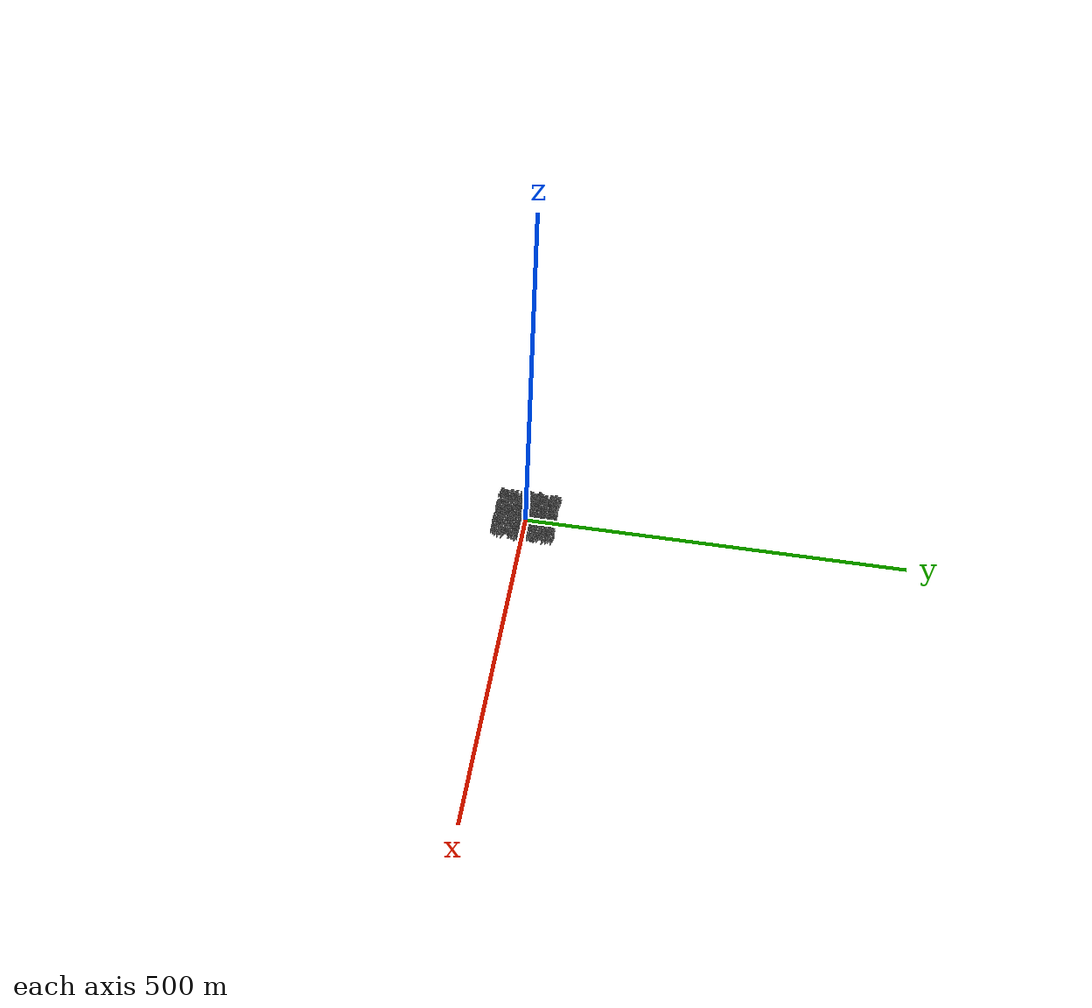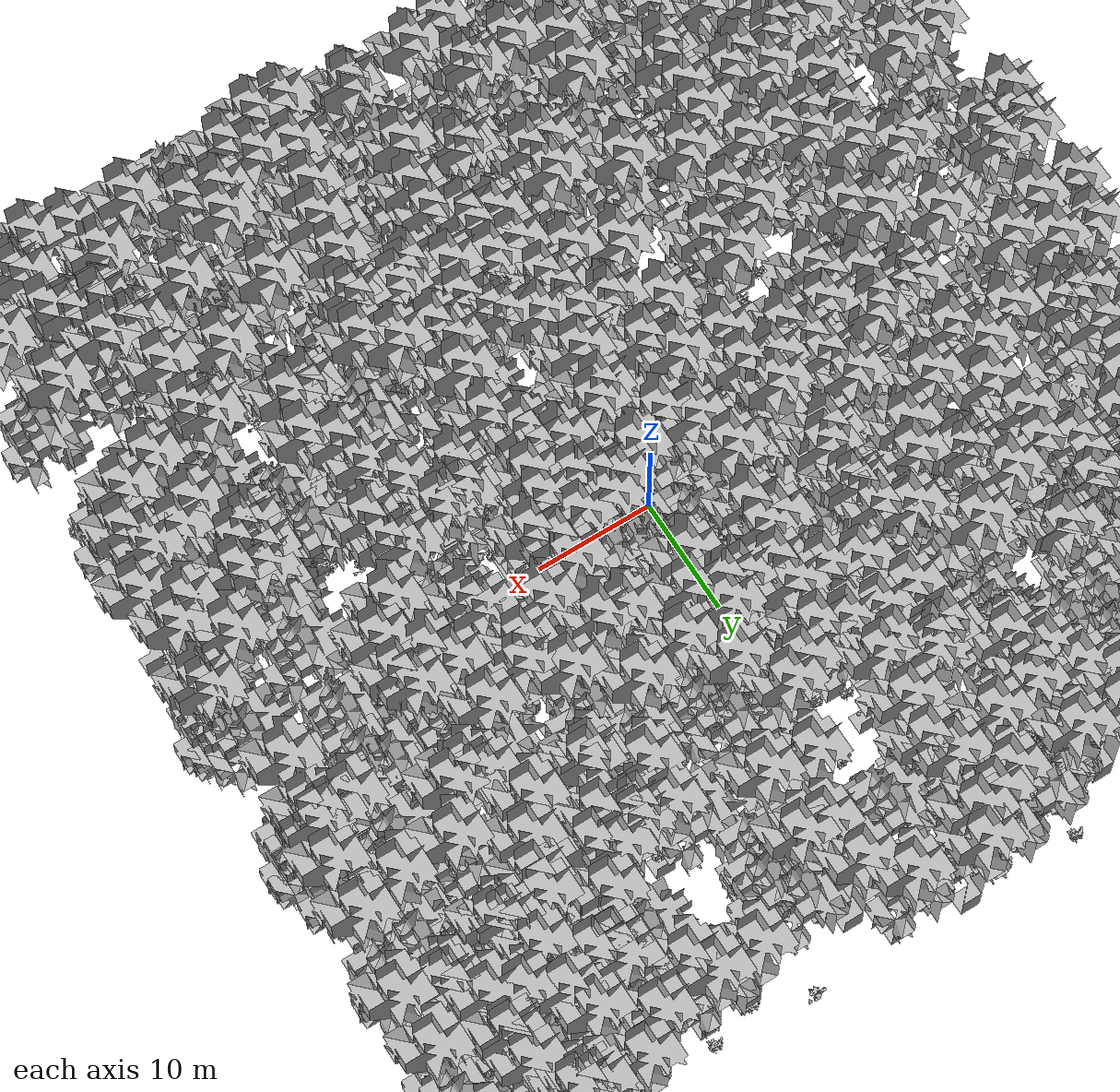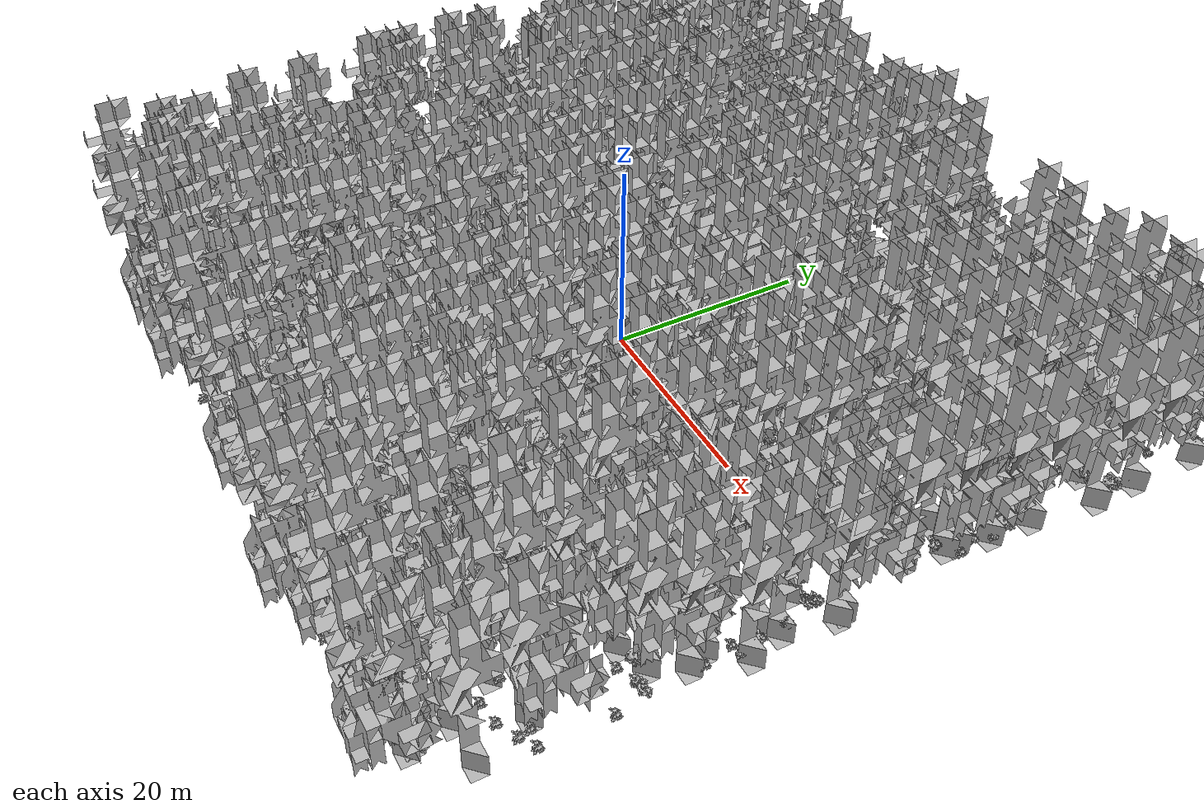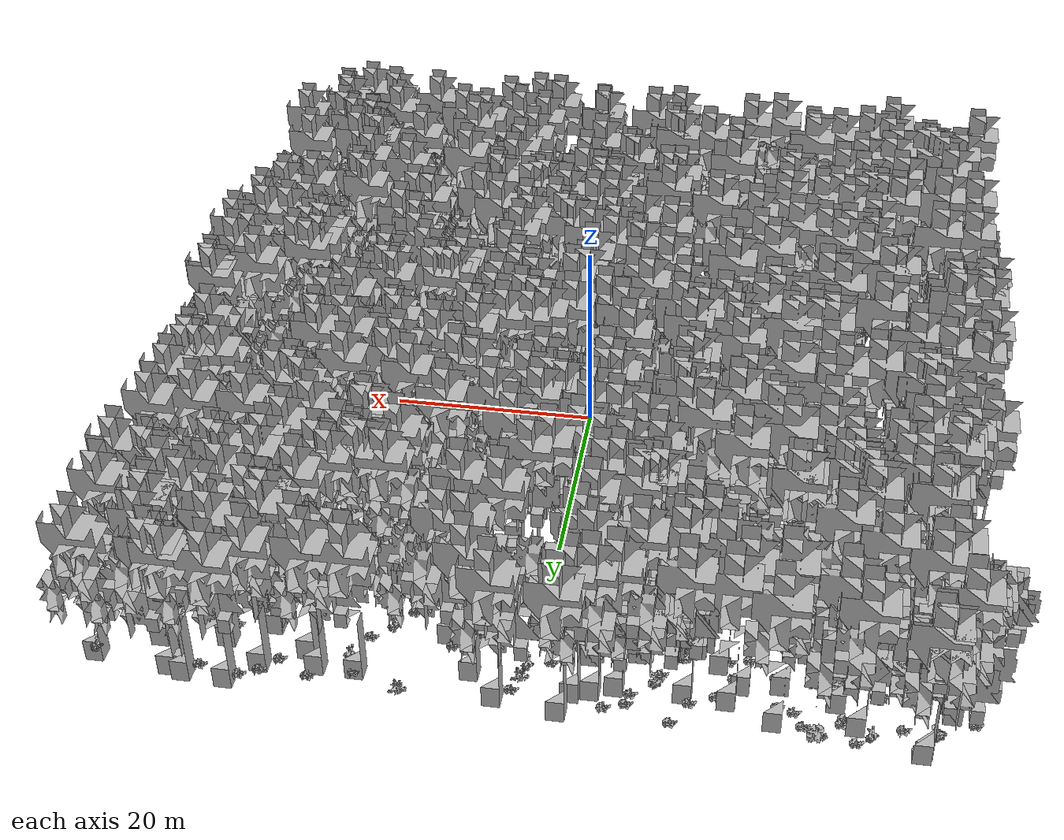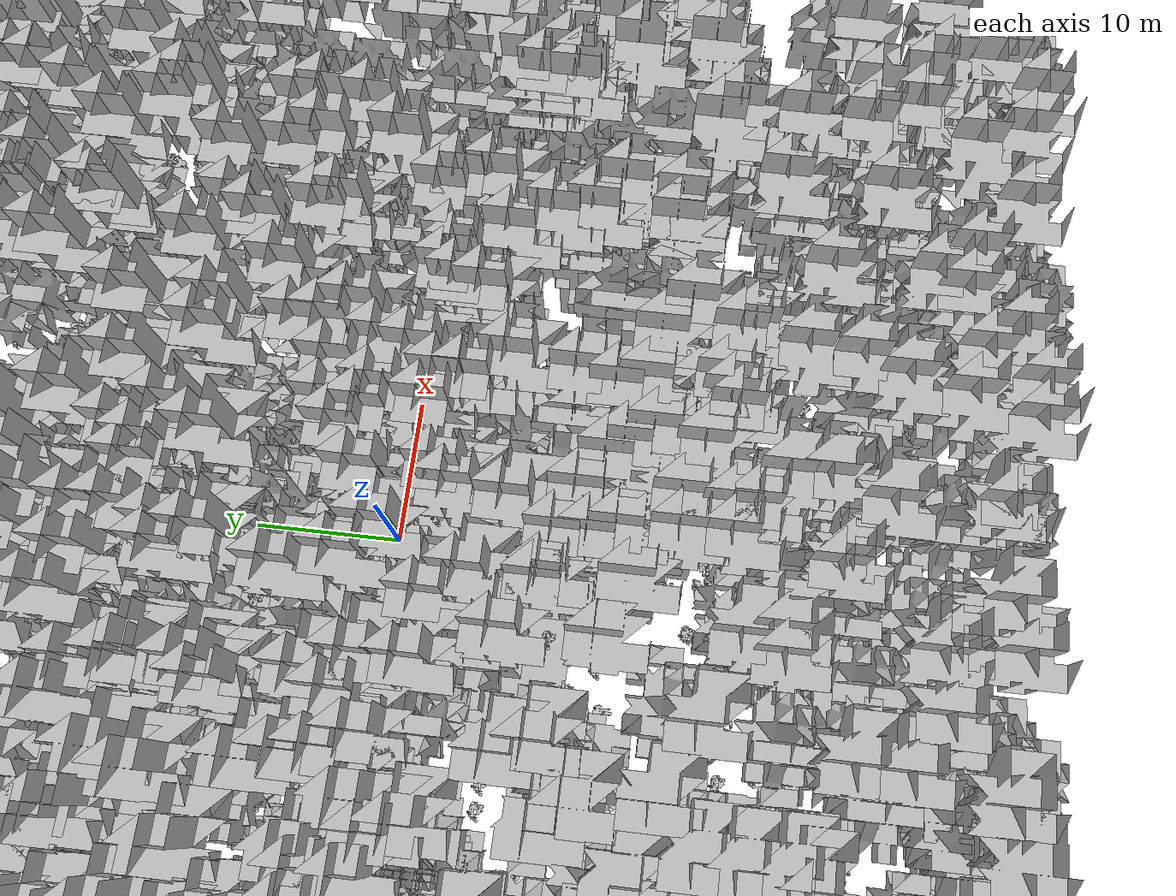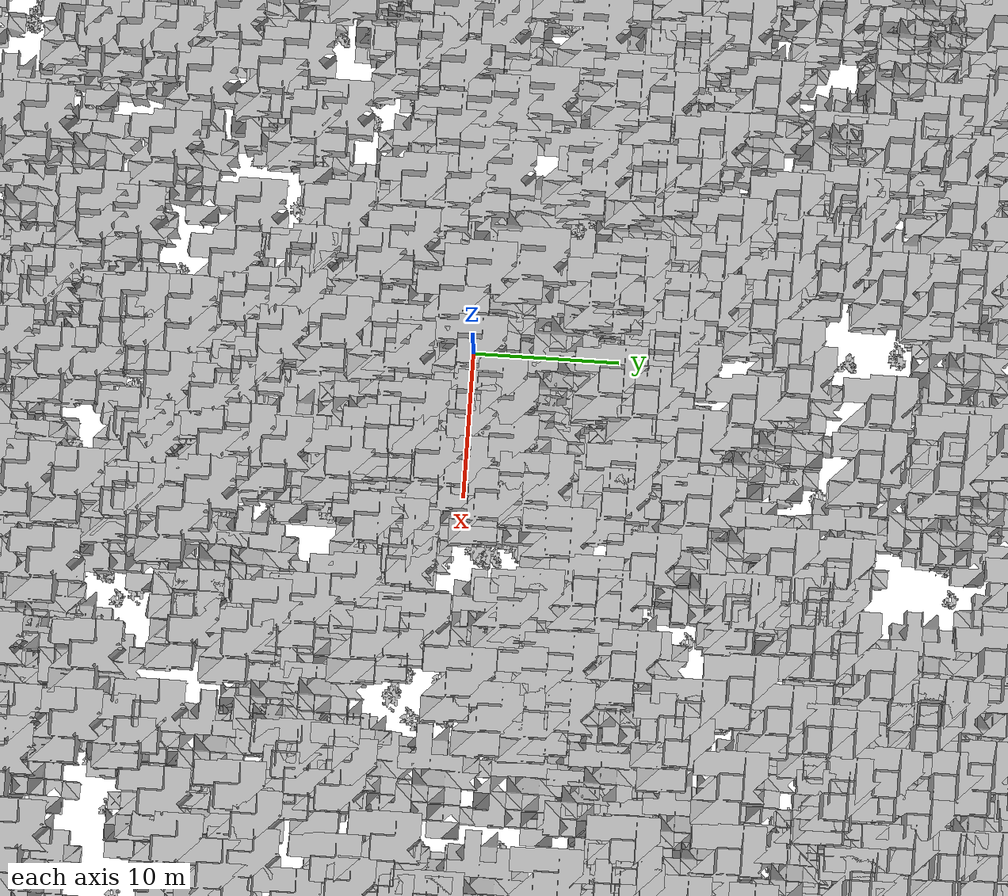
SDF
<sdf version="1.7">
    <world name="default">
        <plugin name="mrs_gazebo_static_transform_republisher_plugin" filename="libMrsGazeboCommonResources_StaticTransformRepublisher.so"/>
        <spherical_coordinates>
            <surface_model>EARTH_WGS84</surface_model>
            <latitude_deg>47.3977</latitude_deg>
            <longitude_deg>8.54559</longitude_deg>
            <elevation>0</elevation>
            <heading_deg>0</heading_deg>
        </spherical_coordinates>
        <physics name="default_physics" default="0" type="ode">
            <ode>
                <solver>
                    <type>quick</type>
                    <iters>10</iters>
                    <sor>1.3</sor>
                    <use_dynamic_moi_rescaling>0</use_dynamic_moi_rescaling>
                </solver>
                <constraints>
                    <cfm>0</cfm>
                    <erp>0.2</erp>
                    <contact_max_correcting_vel>1000</contact_max_correcting_vel>
                    <contact_surface_layer>0.001</contact_surface_layer>
                </constraints>
            </ode>
            <max_step_size>0.004</max_step_size>
            <real_time_factor>1</real_time_factor>
            <real_time_update_rate>250</real_time_update_rate>
        </physics>
        <scene>
            <shadows>0</shadows>
            <ambient>0.4 0.4 0.4 1</ambient>
            <background>0.7 0.7 0.7 1</background>
        </scene>
        <light name="sun" type="directional">
            <pose>0 0 1000 0.4 0.2 0</pose>
            <diffuse>1 1 1 1</diffuse>
            <specular>0.6 0.6 0.6 1</specular>
            <direction>0.1 0.1 -0.9</direction>
            <attenuation>
                <range>20</range>
                <constant>0.5</constant>
                <linear>0.01</linear>
                <quadratic>0.001</quadratic>
            </attenuation>
            <cast_shadows>1</cast_shadows>
            <spot>
                <inner_angle>0</inner_angle>
                <outer_angle>0</outer_angle>
                <falloff>0</falloff>
            </spot>
        </light>
        <model name="ground_plane">
            <static>1</static>
            <link name="link">
                <collision name="collision">
                    <pose>-50 0 0 0 -0 0</pose>
                    <geometry>
                        <plane>
                            <normal>0 0 1</normal>
                            <size>80 80</size>
                        </plane>
                    </geometry>
                    <surface>
                        <contact>
                            <ode>
                                <min_depth>0.01</min_depth>
                                <max_vel>0</max_vel>
                            </ode>
                        </contact>
                        <friction>
                            <ode/>
                            <torsional>
                                <ode/>
                            </torsional>
                        </friction>
                        <bounce/>
                    </surface>
                    <max_contacts>10</max_contacts>
                </collision>
                <visual name="grass">
                    <pose>0 0 0 0 -0 0</pose>
                    <cast_shadows>0</cast_shadows>
                    <geometry>
                        <mesh>
                            <scale>0.46714285714285714 0.46714285714285714 0.1</scale>
                            <uri>file://grass_plane/meshes/grass_plane.dae</uri>
                        </mesh>
                    </geometry>
                </visual>
                <self_collide>0</self_collide>
                <enable_wind>0</enable_wind>
                <kinematic>0</kinematic>
            </link>
        </model>
        <model name="the_void">
            <static>1</static>
            <link name="link">
                <pose>0 0 0.1 0 -0 0</pose>
                <visual name="the_void">
                    <pose>0 0 2 0 -0 0</pose>
                    <geometry>
                        <sphere>
                            <radius>0.25</radius>
                        </sphere>
                    </geometry>
                    <material>
                        <script>
                            <uri>file://media/materials/scripts/Gazebo.material</uri>
                            <name>Gazebo/Black</name>
                        </script>
                    </material>
                </visual>
                <self_collide>0</self_collide>
                <enable_wind>0</enable_wind>
                <kinematic>0</kinematic>
            </link>
            <pose>-1000 -1000 0 0 -0 0</pose>
        </model>
        <gui fullscreen="0">
            <camera name="camera">
                <pose>35.1577 98.6044 40.0204 0 0.407996 -1.99761</pose>
                <view_controller>orbit</view_controller>
                <projection_type>perspective</projection_type>
            </camera>
        </gui>
        <plugin name="mrs_gazebo_rviz_cam_synchronizer" filename="libMrsGazeboCommonResources_RvizCameraSynchronizer.so">
            <target_frame_id>gazebo_user_camera</target_frame_id>
            <world_origin_frame_id>uav1/gps_origin</world_origin_frame_id>
            <frame_to_follow>uav1</frame_to_follow>
        </plugin>
        <gravity>0 0 -9.8066</gravity>
        <magnetic_field>6e-06 2.3e-05 -4.2e-05</magnetic_field>
        <atmosphere type="adiabatic"/>
        <wind/>
        <model name="Tree 0">
            <static>1</static>
            <pose>30.91017625641861 31.21281964116895 0 1.57079 -0 0</pose>
            <link name="link">
                <pose>0 0 0 0 -0 0</pose>
                <collision name="collision">
                    <geometry>
                        <mesh>
                            <scale>3.5 5 3.5</scale>
                            <uri>model://tree_9/meshes/tree_9.obj</uri>
                        </mesh>
                    </geometry>
                    <max_contacts>10</max_contacts>
                    <surface>
                        <contact>
                            <ode/>
                        </contact>
                        <bounce/>
                        <friction>
                            <torsional>
                                <ode/>
                            </torsional>
                            <ode/>
                        </friction>
                    </surface>
                </collision>
                <visual name="visual">
                    <geometry>
                        <mesh>
                            <scale>3.5 5 3.5</scale>
                            <uri>model://tree_9/meshes/tree_9.obj</uri>
                        </mesh>
                    </geometry>
                </visual>
                <self_collide>0</self_collide>
                <enable_wind>0</enable_wind>
                <kinematic>0</kinematic>
            </link>
        </model>
        <model name="Tree 1">
            <static>1</static>
            <pose>28.80075504005869 -7.506337468141254 0 1.57079 -0 0</pose>
            <link name="link">
                <pose>0 0 0 0 -0 0</pose>
                <collision name="collision">
                    <geometry>
                        <mesh>
                            <scale>3.5 5 3.5</scale>
                            <uri>model://tree_2/meshes/tree_2.obj</uri>
                        </mesh>
                    </geometry>
                    <max_contacts>10</max_contacts>
                    <surface>
                        <contact>
                            <ode/>
                        </contact>
                        <bounce/>
                        <friction>
                            <torsional>
                                <ode/>
                            </torsional>
                            <ode/>
                        </friction>
                    </surface>
                </collision>
                <visual name="visual">
                    <geometry>
                        <mesh>
                            <scale>3.5 5 3.5</scale>
                            <uri>model://tree_2/meshes/tree_2.obj</uri>
                        </mesh>
                    </geometry>
                </visual>
                <self_collide>0</self_collide>
                <enable_wind>0</enable_wind>
                <kinematic>0</kinematic>
            </link>
        </model>
        <model name="Tree 2">
            <static>1</static>
            <pose>28.143032347528802 -20.413554829449374 0 1.57079 -0 0</pose>
            <link name="link">
                <pose>0 0 0 0 -0 0</pose>
                <collision name="collision">
                    <geometry>
                        <mesh>
                            <scale>3.5 5 3.5</scale>
                            <uri>model://tree_9/meshes/tree_9.obj</uri>
                        </mesh>
                    </geometry>
                    <max_contacts>10</max_contacts>
                    <surface>
                        <contact>
                            <ode/>
                        </contact>
                        <bounce/>
                        <friction>
                            <torsional>
                                <ode/>
                            </torsional>
                            <ode/>
                        </friction>
                    </surface>
                </collision>
                <visual name="visual">
                    <geometry>
                        <mesh>
                            <scale>3.5 5 3.5</scale>
                            <uri>model://tree_9/meshes/tree_9.obj</uri>
                        </mesh>
                    </geometry>
                </visual>
                <self_collide>0</self_collide>
                <enable_wind>0</enable_wind>
                <kinematic>0</kinematic>
            </link>
        </model>
        <model name="Tree 3">
            <static>1</static>
            <pose>-23.076699597023243 -23.677184721466134 0 1.57079 -0 0</pose>
            <link name="link">
                <pose>0 0 0 0 -0 0</pose>
                <collision name="collision">
                    <geometry>
                        <mesh>
                            <scale>3.5 5 3.5</scale>
                            <uri>model://tree_9/meshes/tree_9.obj</uri>
                        </mesh>
                    </geometry>
                    <max_contacts>10</max_contacts>
                    <surface>
                        <contact>
                            <ode/>
                        </contact>
                        <bounce/>
                        <friction>
                            <torsional>
                                <ode/>
                            </torsional>
                            <ode/>
                        </friction>
                    </surface>
                </collision>
                <visual name="visual">
                    <geometry>
                        <mesh>
                            <scale>3.5 5 3.5</scale>
                            <uri>model://tree_9/meshes/tree_9.obj</uri>
                        </mesh>
                    </geometry>
                </visual>
                <self_collide>0</self_collide>
                <enable_wind>0</enable_wind>
                <kinematic>0</kinematic>
            </link>
        </model>
        <model name="Tree 4">
            <static>1</static>
            <pose>-5.57250292588845 12.669635630537641 0 1.57079 -0 0</pose>
            <link name="link">
                <pose>0 0 0 0 -0 0</pose>
                <collision name="collision">
                    <geometry>
                        <mesh>
                            <scale>3.5 5 3.5</scale>
                            <uri>model://tree_2/meshes/tree_2.obj</uri>
                        </mesh>
                    </geometry>
                    <max_contacts>10</max_contacts>
                    <surface>
                        <contact>
                            <ode/>
                        </contact>
                        <bounce/>
                        <friction>
                            <torsional>
                                <ode/>
                            </torsional>
                            <ode/>
                        </friction>
                    </surface>
                </collision>
                <visual name="visual">
                    <geometry>
                        <mesh>
                            <scale>3.5 5 3.5</scale>
                            <uri>model://tree_2/meshes/tree_2.obj</uri>
                        </mesh>
                    </geometry>
                </visual>
                <self_collide>0</self_collide>
                <enable_wind>0</enable_wind>
                <kinematic>0</kinematic>
            </link>
        </model>
        <model name="Tree 5">
            <static>1</static>
            <pose>-23.905515472704057 -15.00675875835298 0 1.57079 -0 0</pose>
            <link name="link">
                <pose>0 0 0 0 -0 0</pose>
                <collision name="collision">
                    <geometry>
                        <mesh>
                            <scale>3.5 5 3.5</scale>
                            <uri>model://tree_9/meshes/tree_9.obj</uri>
                        </mesh>
                    </geometry>
                    <max_contacts>10</max_contacts>
                    <surface>
                        <contact>
                            <ode/>
                        </contact>
                        <bounce/>
                        <friction>
                            <torsional>
                                <ode/>
                            </torsional>
                            <ode/>
                        </friction>
                    </surface>
                </collision>
                <visual name="visual">
                    <geometry>
                        <mesh>
                            <scale>3.5 5 3.5</scale>
                            <uri>model://tree_9/meshes/tree_9.obj</uri>
                        </mesh>
                    </geometry>
                </visual>
                <self_collide>0</self_collide>
                <enable_wind>0</enable_wind>
                <kinematic>0</kinematic>
            </link>
        </model>
        <model name="Tree 6">
            <static>1</static>
            <pose>19.761789840491915 -37.90482083017761 0 1.57079 -0 0</pose>
            <link name="link">
                <pose>0 0 0 0 -0 0</pose>
                <collision name="collision">
                    <geometry>
                        <mesh>
                            <scale>3.5 5 3.5</scale>
                            <uri>model://tree_2/meshes/tree_2.obj</uri>
                        </mesh>
                    </geometry>
                    <max_contacts>10</max_contacts>
                    <surface>
                        <contact>
                            <ode/>
                        </contact>
                        <bounce/>
                        <friction>
                            <torsional>
                                <ode/>
                            </torsional>
                            <ode/>
                        </friction>
                    </surface>
                </collision>
                <visual name="visual">
                    <geometry>
                        <mesh>
                            <scale>3.5 5 3.5</scale>
                            <uri>model://tree_2/meshes/tree_2.obj</uri>
                        </mesh>
                    </geometry>
                </visual>
                <self_collide>0</self_collide>
                <enable_wind>0</enable_wind>
                <kinematic>0</kinematic>
            </link>
        </model>
        <model name="Tree 7">
            <static>1</static>
            <pose>-9.91721672211478 -19.705225154479045 0 1.57079 -0 0</pose>
            <link name="link">
                <pose>0 0 0 0 -0 0</pose>
                <collision name="collision">
                    <geometry>
                        <mesh>
                            <scale>3.5 5 3.5</scale>
                            <uri>model://tree_2/meshes/tree_2.obj</uri>
                        </mesh>
                    </geometry>
                    <max_contacts>10</max_contacts>
                    <surface>
                        <contact>
                            <ode/>
                        </contact>
                        <bounce/>
                        <friction>
                            <torsional>
                                <ode/>
                            </torsional>
                            <ode/>
                        </friction>
                    </surface>
                </collision>
                <visual name="visual">
                    <geometry>
                        <mesh>
                            <scale>3.5 5 3.5</scale>
                            <uri>model://tree_2/meshes/tree_2.obj</uri>
                        </mesh>
                    </geometry>
                </visual>
                <self_collide>0</self_collide>
                <enable_wind>0</enable_wind>
                <kinematic>0</kinematic>
            </link>
        </model>
        <model name="Tree 8">
            <static>1</static>
            <pose>2.041168191089575 -21.986346807292225 0 1.57079 -0 0</pose>
            <link name="link">
                <pose>0 0 0 0 -0 0</pose>
                <collision name="collision">
                    <geometry>
                        <mesh>
                            <scale>3.5 5 3.5</scale>
                            <uri>model://tree_9/meshes/tree_9.obj</uri>
                        </mesh>
                    </geometry>
                    <max_contacts>10</max_contacts>
                    <surface>
                        <contact>
                            <ode/>
                        </contact>
                        <bounce/>
                        <friction>
                            <torsional>
                                <ode/>
                            </torsional>
                            <ode/>
                        </friction>
                    </surface>
                </collision>
                <visual name="visual">
                    <geometry>
                        <mesh>
                            <scale>3.5 5 3.5</scale>
                            <uri>model://tree_9/meshes/tree_9.obj</uri>
                        </mesh>
                    </geometry>
                </visual>
                <self_collide>0</self_collide>
                <enable_wind>0</enable_wind>
                <kinematic>0</kinematic>
            </link>
        </model>
        <model name="Tree 9">
            <static>1</static>
            <pose>37.17106486879085 -14.391199536497233 0 1.57079 -0 0</pose>
            <link name="link">
                <pose>0 0 0 0 -0 0</pose>
                <collision name="collision">
                    <geometry>
                        <mesh>
                            <scale>3.5 5 3.5</scale>
                            <uri>model://tree_9/meshes/tree_9.obj</uri>
                        </mesh>
                    </geometry>
                    <max_contacts>10</max_contacts>
                    <surface>
                        <contact>
                            <ode/>
                        </contact>
                        <bounce/>
                        <friction>
                            <torsional>
                                <ode/>
                            </torsional>
                            <ode/>
                        </friction>
                    </surface>
                </collision>
                <visual name="visual">
                    <geometry>
                        <mesh>
                            <scale>3.5 5 3.5</scale>
                            <uri>model://tree_9/meshes/tree_9.obj</uri>
                        </mesh>
                    </geometry>
                </visual>
                <self_collide>0</self_collide>
                <enable_wind>0</enable_wind>
                <kinematic>0</kinematic>
            </link>
        </model>
        <model name="Tree 10">
            <static>1</static>
            <pose>6.639274143463979 4.720237174317347 0 1.57079 -0 0</pose>
            <link name="link">
                <pose>0 0 0 0 -0 0</pose>
                <collision name="collision">
                    <geometry>
                        <mesh>
                            <scale>3.5 5 3.5</scale>
                            <uri>model://tree_2/meshes/tree_2.obj</uri>
                        </mesh>
                    </geometry>
                    <max_contacts>10</max_contacts>
                    <surface>
                        <contact>
                            <ode/>
                        </contact>
                        <bounce/>
                        <friction>
                            <torsional>
                                <ode/>
                            </torsional>
                            <ode/>
                        </friction>
                    </surface>
                </collision>
                <visual name="visual">
                    <geometry>
                        <mesh>
                            <scale>3.5 5 3.5</scale>
                            <uri>model://tree_2/meshes/tree_2.obj</uri>
                        </mesh>
                    </geometry>
                </visual>
                <self_collide>0</self_collide>
                <enable_wind>0</enable_wind>
                <kinematic>0</kinematic>
            </link>
        </model>
        <model name="Tree 11">
            <static>1</static>
            <pose>-10.511982581206237 11.37835054972711 0 1.57079 -0 0</pose>
            <link name="link">
                <pose>0 0 0 0 -0 0</pose>
                <collision name="collision">
                    <geometry>
                        <mesh>
                            <scale>3.5 5 3.5</scale>
                            <uri>model://tree_9/meshes/tree_9.obj</uri>
                        </mesh>
                    </geometry>
                    <max_contacts>10</max_contacts>
                    <surface>
                        <contact>
                            <ode/>
                        </contact>
                        <bounce/>
                        <friction>
                            <torsional>
                                <ode/>
                            </torsional>
                            <ode/>
                        </friction>
                    </surface>
                </collision>
                <visual name="visual">
                    <geometry>
                        <mesh>
                            <scale>3.5 5 3.5</scale>
                            <uri>model://tree_9/meshes/tree_9.obj</uri>
                        </mesh>
                    </geometry>
                </visual>
                <self_collide>0</self_collide>
                <enable_wind>0</enable_wind>
                <kinematic>0</kinematic>
            </link>
        </model>
        <model name="Tree 12">
            <static>1</static>
            <pose>-2.9900764032534752 15.596608024744583 0 1.57079 -0 0</pose>
            <link name="link">
                <pose>0 0 0 0 -0 0</pose>
                <collision name="collision">
                    <geometry>
                        <mesh>
                            <scale>3.5 5 3.5</scale>
                            <uri>model://tree_2/meshes/tree_2.obj</uri>
                        </mesh>
                    </geometry>
                    <max_contacts>10</max_contacts>
                    <surface>
                        <contact>
                            <ode/>
                        </contact>
                        <bounce/>
                        <friction>
                            <torsional>
                                <ode/>
                            </torsional>
                            <ode/>
                        </friction>
                    </surface>
                </collision>
                <visual name="visual">
                    <geometry>
                        <mesh>
                            <scale>3.5 5 3.5</scale>
                            <uri>model://tree_2/meshes/tree_2.obj</uri>
                        </mesh>
                    </geometry>
                </visual>
                <self_collide>0</self_collide>
                <enable_wind>0</enable_wind>
                <kinematic>0</kinematic>
            </link>
        </model>
        <model name="Tree 13">
            <static>1</static>
            <pose>-29.83648451298648 29.360817135755113 0 1.57079 -0 0</pose>
            <link name="link">
                <pose>0 0 0 0 -0 0</pose>
                <collision name="collision">
                    <geometry>
                        <mesh>
                            <scale>3.5 5 3.5</scale>
                            <uri>model://tree_9/meshes/tree_9.obj</uri>
                        </mesh>
                    </geometry>
                    <max_contacts>10</max_contacts>
                    <surface>
                        <contact>
                            <ode/>
                        </contact>
                        <bounce/>
                        <friction>
                            <torsional>
                                <ode/>
                            </torsional>
                            <ode/>
                        </friction>
                    </surface>
                </collision>
                <visual name="visual">
                    <geometry>
                        <mesh>
                            <scale>3.5 5 3.5</scale>
                            <uri>model://tree_9/meshes/tree_9.obj</uri>
                        </mesh>
                    </geometry>
                </visual>
                <self_collide>0</self_collide>
                <enable_wind>0</enable_wind>
                <kinematic>0</kinematic>
            </link>
        </model>
        <model name="Tree 14">
            <static>1</static>
            <pose>38.08258785622533 13.436763141184144 0 1.57079 -0 0</pose>
            <link name="link">
                <pose>0 0 0 0 -0 0</pose>
                <collision name="collision">
                    <geometry>
                        <mesh>
                            <scale>3.5 5 3.5</scale>
                            <uri>model://tree_2/meshes/tree_2.obj</uri>
                        </mesh>
                    </geometry>
                    <max_contacts>10</max_contacts>
                    <surface>
                        <contact>
                            <ode/>
                        </contact>
                        <bounce/>
                        <friction>
                            <torsional>
                                <ode/>
                            </torsional>
                            <ode/>
                        </friction>
                    </surface>
                </collision>
                <visual name="visual">
                    <geometry>
                        <mesh>
                            <scale>3.5 5 3.5</scale>
                            <uri>model://tree_2/meshes/tree_2.obj</uri>
                        </mesh>
                    </geometry>
                </visual>
                <self_collide>0</self_collide>
                <enable_wind>0</enable_wind>
                <kinematic>0</kinematic>
            </link>
        </model>
        <model name="Tree 15">
            <static>1</static>
            <pose>-30.434588674883834 -26.13237675348018 0 1.57079 -0 0</pose>
            <link name="link">
                <pose>0 0 0 0 -0 0</pose>
                <collision name="collision">
                    <geometry>
                        <mesh>
                            <scale>3.5 5 3.5</scale>
                            <uri>model://tree_2/meshes/tree_2.obj</uri>
                        </mesh>
                    </geometry>
                    <max_contacts>10</max_contacts>
                    <surface>
                        <contact>
                            <ode/>
                        </contact>
                        <bounce/>
                        <friction>
                            <torsional>
                                <ode/>
                            </torsional>
                            <ode/>
                        </friction>
                    </surface>
                </collision>
                <visual name="visual">
                    <geometry>
                        <mesh>
                            <scale>3.5 5 3.5</scale>
                            <uri>model://tree_2/meshes/tree_2.obj</uri>
                        </mesh>
                    </geometry>
                </visual>
                <self_collide>0</self_collide>
                <enable_wind>0</enable_wind>
                <kinematic>0</kinematic>
            </link>
        </model>
        <model name="Tree 16">
            <static>1</static>
            <pose>-12.949339108152707 15.026381840691194 0 1.57079 -0 0</pose>
            <link name="link">
                <pose>0 0 0 0 -0 0</pose>
                <collision name="collision">
                    <geometry>
                        <mesh>
                            <scale>3.5 5 3.5</scale>
                            <uri>model://tree_9/meshes/tree_9.obj</uri>
                        </mesh>
                    </geometry>
                    <max_contacts>10</max_contacts>
                    <surface>
                        <contact>
                            <ode/>
                        </contact>
                        <bounce/>
                        <friction>
                            <torsional>
                                <ode/>
                            </torsional>
                            <ode/>
                        </friction>
                    </surface>
                </collision>
                <visual name="visual">
                    <geometry>
                        <mesh>
                            <scale>3.5 5 3.5</scale>
                            <uri>model://tree_9/meshes/tree_9.obj</uri>
                        </mesh>
                    </geometry>
                </visual>
                <self_collide>0</self_collide>
                <enable_wind>0</enable_wind>
                <kinematic>0</kinematic>
            </link>
        </model>
        <model name="Tree 17">
            <static>1</static>
            <pose>-28.117833418078497 22.73537100807416 0 1.57079 -0 0</pose>
            <link name="link">
                <pose>0 0 0 0 -0 0</pose>
                <collision name="collision">
                    <geometry>
                        <mesh>
                            <scale>3.5 5 3.5</scale>
                            <uri>model://tree_9/meshes/tree_9.obj</uri>
                        </mesh>
                    </geometry>
                    <max_contacts>10</max_contacts>
                    <surface>
                        <contact>
                            <ode/>
                        </contact>
                        <bounce/>
                        <friction>
                            <torsional>
                                <ode/>
                            </torsional>
                            <ode/>
                        </friction>
                    </surface>
                </collision>
                <visual name="visual">
                    <geometry>
                        <mesh>
                            <scale>3.5 5 3.5</scale>
                            <uri>model://tree_9/meshes/tree_9.obj</uri>
                        </mesh>
                    </geometry>
                </visual>
                <self_collide>0</self_collide>
                <enable_wind>0</enable_wind>
                <kinematic>0</kinematic>
            </link>
        </model>
        <model name="Tree 18">
            <static>1</static>
            <pose>-4.235619558732324 -3.2850442022932214 0 1.57079 -0 0</pose>
            <link name="link">
                <pose>0 0 0 0 -0 0</pose>
                <collision name="collision">
                    <geometry>
                        <mesh>
                            <scale>3.5 5 3.5</scale>
                            <uri>model://tree_2/meshes/tree_2.obj</uri>
                        </mesh>
                    </geometry>
                    <max_contacts>10</max_contacts>
                    <surface>
                        <contact>
                            <ode/>
                        </contact>
                        <bounce/>
                        <friction>
                            <torsional>
                                <ode/>
                            </torsional>
                            <ode/>
                        </friction>
                    </surface>
                </collision>
                <visual name="visual">
                    <geometry>
                        <mesh>
                            <scale>3.5 5 3.5</scale>
                            <uri>model://tree_2/meshes/tree_2.obj</uri>
                        </mesh>
                    </geometry>
                </visual>
                <self_collide>0</self_collide>
                <enable_wind>0</enable_wind>
                <kinematic>0</kinematic>
            </link>
        </model>
        <model name="Tree 19">
            <static>1</static>
            <pose>7.492964837227454 18.982073438112792 0 1.57079 -0 0</pose>
            <link name="link">
                <pose>0 0 0 0 -0 0</pose>
                <collision name="collision">
                    <geometry>
                        <mesh>
                            <scale>3.5 5 3.5</scale>
                            <uri>model://tree_2/meshes/tree_2.obj</uri>
                        </mesh>
                    </geometry>
                    <max_contacts>10</max_contacts>
                    <surface>
                        <contact>
                            <ode/>
                        </contact>
                        <bounce/>
                        <friction>
                            <torsional>
                                <ode/>
                            </torsional>
                            <ode/>
                        </friction>
                    </surface>
                </collision>
                <visual name="visual">
                    <geometry>
                        <mesh>
                            <scale>3.5 5 3.5</scale>
                            <uri>model://tree_2/meshes/tree_2.obj</uri>
                        </mesh>
                    </geometry>
                </visual>
                <self_collide>0</self_collide>
                <enable_wind>0</enable_wind>
                <kinematic>0</kinematic>
            </link>
        </model>
        <model name="Tree 20">
            <static>1</static>
            <pose>2.7072010651863962 38.707927730834726 0 1.57079 -0 0</pose>
            <link name="link">
                <pose>0 0 0 0 -0 0</pose>
                <collision name="collision">
                    <geometry>
                        <mesh>
                            <scale>3.5 5 3.5</scale>
                            <uri>model://tree_9/meshes/tree_9.obj</uri>
                        </mesh>
                    </geometry>
                    <max_contacts>10</max_contacts>
                    <surface>
                        <contact>
                            <ode/>
                        </contact>
                        <bounce/>
                        <friction>
                            <torsional>
                                <ode/>
                            </torsional>
                            <ode/>
                        </friction>
                    </surface>
                </collision>
                <visual name="visual">
                    <geometry>
                        <mesh>
                            <scale>3.5 5 3.5</scale>
                            <uri>model://tree_9/meshes/tree_9.obj</uri>
                        </mesh>
                    </geometry>
                </visual>
                <self_collide>0</self_collide>
                <enable_wind>0</enable_wind>
                <kinematic>0</kinematic>
            </link>
        </model>
        <model name="Tree 21">
            <static>1</static>
            <pose>0.31561313747361197 -19.141215854268037 0 1.57079 -0 0</pose>
            <link name="link">
                <pose>0 0 0 0 -0 0</pose>
                <collision name="collision">
                    <geometry>
                        <mesh>
                            <scale>3.5 5 3.5</scale>
                            <uri>model://tree_9/meshes/tree_9.obj</uri>
                        </mesh>
                    </geometry>
                    <max_contacts>10</max_contacts>
                    <surface>
                        <contact>
                            <ode/>
                        </contact>
                        <bounce/>
                        <friction>
                            <torsional>
                                <ode/>
                            </torsional>
                            <ode/>
                        </friction>
                    </surface>
                </collision>
                <visual name="visual">
                    <geometry>
                        <mesh>
                            <scale>3.5 5 3.5</scale>
                            <uri>model://tree_9/meshes/tree_9.obj</uri>
                        </mesh>
                    </geometry>
                </visual>
                <self_collide>0</self_collide>
                <enable_wind>0</enable_wind>
                <kinematic>0</kinematic>
            </link>
        </model>
        <model name="Tree 22">
            <static>1</static>
            <pose>17.93072635077457 -7.0581959620496875 0 1.57079 -0 0</pose>
            <link name="link">
                <pose>0 0 0 0 -0 0</pose>
                <collision name="collision">
                    <geometry>
                        <mesh>
                            <scale>3.5 5 3.5</scale>
                            <uri>model://tree_9/meshes/tree_9.obj</uri>
                        </mesh>
                    </geometry>
                    <max_contacts>10</max_contacts>
                    <surface>
                        <contact>
                            <ode/>
                        </contact>
                        <bounce/>
                        <friction>
                            <torsional>
                                <ode/>
                            </torsional>
                            <ode/>
                        </friction>
                    </surface>
                </collision>
                <visual name="visual">
                    <geometry>
                        <mesh>
                            <scale>3.5 5 3.5</scale>
                            <uri>model://tree_9/meshes/tree_9.obj</uri>
                        </mesh>
                    </geometry>
                </visual>
                <self_collide>0</self_collide>
                <enable_wind>0</enable_wind>
                <kinematic>0</kinematic>
            </link>
        </model>
        <model name="Tree 23">
            <static>1</static>
            <pose>17.515586112609597 23.757073896121092 0 1.57079 -0 0</pose>
            <link name="link">
                <pose>0 0 0 0 -0 0</pose>
                <collision name="collision">
                    <geometry>
                        <mesh>
                            <scale>3.5 5 3.5</scale>
                            <uri>model://tree_9/meshes/tree_9.obj</uri>
                        </mesh>
                    </geometry>
                    <max_contacts>10</max_contacts>
                    <surface>
                        <contact>
                            <ode/>
                        </contact>
                        <bounce/>
                        <friction>
                            <torsional>
                                <ode/>
                            </torsional>
                            <ode/>
                        </friction>
                    </surface>
                </collision>
                <visual name="visual">
                    <geometry>
                        <mesh>
                            <scale>3.5 5 3.5</scale>
                            <uri>model://tree_9/meshes/tree_9.obj</uri>
                        </mesh>
                    </geometry>
                </visual>
                <self_collide>0</self_collide>
                <enable_wind>0</enable_wind>
                <kinematic>0</kinematic>
            </link>
        </model>
        <model name="Tree 24">
            <static>1</static>
            <pose>-4.373454652179674 27.52931438960772 0 1.57079 -0 0</pose>
            <link name="link">
                <pose>0 0 0 0 -0 0</pose>
                <collision name="collision">
                    <geometry>
                        <mesh>
                            <scale>3.5 5 3.5</scale>
                            <uri>model://tree_9/meshes/tree_9.obj</uri>
                        </mesh>
                    </geometry>
                    <max_contacts>10</max_contacts>
                    <surface>
                        <contact>
                            <ode/>
                        </contact>
                        <bounce/>
                        <friction>
                            <torsional>
                                <ode/>
                            </torsional>
                            <ode/>
                        </friction>
                    </surface>
                </collision>
                <visual name="visual">
                    <geometry>
                        <mesh>
                            <scale>3.5 5 3.5</scale>
                            <uri>model://tree_9/meshes/tree_9.obj</uri>
                        </mesh>
                    </geometry>
                </visual>
                <self_collide>0</self_collide>
                <enable_wind>0</enable_wind>
                <kinematic>0</kinematic>
            </link>
        </model>
        <model name="Tree 25">
            <static>1</static>
            <pose>-20.08611443008469 6.891712089928589 0 1.57079 -0 0</pose>
            <link name="link">
                <pose>0 0 0 0 -0 0</pose>
                <collision name="collision">
                    <geometry>
                        <mesh>
                            <scale>3.5 5 3.5</scale>
                            <uri>model://tree_9/meshes/tree_9.obj</uri>
                        </mesh>
                    </geometry>
                    <max_contacts>10</max_contacts>
                    <surface>
                        <contact>
                            <ode/>
                        </contact>
                        <bounce/>
                        <friction>
                            <torsional>
                                <ode/>
                            </torsional>
                            <ode/>
                        </friction>
                    </surface>
                </collision>
                <visual name="visual">
                    <geometry>
                        <mesh>
                            <scale>3.5 5 3.5</scale>
                            <uri>model://tree_9/meshes/tree_9.obj</uri>
                        </mesh>
                    </geometry>
                </visual>
                <self_collide>0</self_collide>
                <enable_wind>0</enable_wind>
                <kinematic>0</kinematic>
            </link>
        </model>
        <model name="Tree 26">
            <static>1</static>
            <pose>25.873625216518377 27.011904275255887 0 1.57079 -0 0</pose>
            <link name="link">
                <pose>0 0 0 0 -0 0</pose>
                <collision name="collision">
                    <geometry>
                        <mesh>
                            <scale>3.5 5 3.5</scale>
                            <uri>model://tree_2/meshes/tree_2.obj</uri>
                        </mesh>
                    </geometry>
                    <max_contacts>10</max_contacts>
                    <surface>
                        <contact>
                            <ode/>
                        </contact>
                        <bounce/>
                        <friction>
                            <torsional>
                                <ode/>
                            </torsional>
                            <ode/>
                        </friction>
                    </surface>
                </collision>
                <visual name="visual">
                    <geometry>
                        <mesh>
                            <scale>3.5 5 3.5</scale>
                            <uri>model://tree_2/meshes/tree_2.obj</uri>
                        </mesh>
                    </geometry>
                </visual>
                <self_collide>0</self_collide>
                <enable_wind>0</enable_wind>
                <kinematic>0</kinematic>
            </link>
        </model>
        <model name="Tree 27">
            <static>1</static>
            <pose>-7.557572361244954 36.00219437346678 0 1.57079 -0 0</pose>
            <link name="link">
                <pose>0 0 0 0 -0 0</pose>
                <collision name="collision">
                    <geometry>
                        <mesh>
                            <scale>3.5 5 3.5</scale>
                            <uri>model://tree_9/meshes/tree_9.obj</uri>
                        </mesh>
                    </geometry>
                    <max_contacts>10</max_contacts>
                    <surface>
                        <contact>
                            <ode/>
                        </contact>
                        <bounce/>
                        <friction>
                            <torsional>
                                <ode/>
                            </torsional>
                            <ode/>
                        </friction>
                    </surface>
                </collision>
                <visual name="visual">
                    <geometry>
                        <mesh>
                            <scale>3.5 5 3.5</scale>
                            <uri>model://tree_9/meshes/tree_9.obj</uri>
                        </mesh>
                    </geometry>
                </visual>
                <self_collide>0</self_collide>
                <enable_wind>0</enable_wind>
                <kinematic>0</kinematic>
            </link>
        </model>
        <model name="Tree 28">
            <static>1</static>
            <pose>29.250044402486054 10.535500147121269 0 1.57079 -0 0</pose>
            <link name="link">
                <pose>0 0 0 0 -0 0</pose>
                <collision name="collision">
                    <geometry>
                        <mesh>
                            <scale>3.5 5 3.5</scale>
                            <uri>model://tree_2/meshes/tree_2.obj</uri>
                        </mesh>
                    </geometry>
                    <max_contacts>10</max_contacts>
                    <surface>
                        <contact>
                            <ode/>
                        </contact>
                        <bounce/>
                        <friction>
                            <torsional>
                                <ode/>
                            </torsional>
                            <ode/>
                        </friction>
                    </surface>
                </collision>
                <visual name="visual">
                    <geometry>
                        <mesh>
                            <scale>3.5 5 3.5</scale>
                            <uri>model://tree_2/meshes/tree_2.obj</uri>
                        </mesh>
                    </geometry>
                </visual>
                <self_collide>0</self_collide>
                <enable_wind>0</enable_wind>
                <kinematic>0</kinematic>
            </link>
        </model>
        <model name="Tree 29">
            <static>1</static>
            <pose>27.171444746158684 15.330684765212474 0 1.57079 -0 0</pose>
            <link name="link">
                <pose>0 0 0 0 -0 0</pose>
                <collision name="collision">
                    <geometry>
                        <mesh>
                            <scale>3.5 5 3.5</scale>
                            <uri>model://tree_9/meshes/tree_9.obj</uri>
                        </mesh>
                    </geometry>
                    <max_contacts>10</max_contacts>
                    <surface>
                        <contact>
                            <ode/>
                        </contact>
                        <bounce/>
                        <friction>
                            <torsional>
                                <ode/>
                            </torsional>
                            <ode/>
                        </friction>
                    </surface>
                </collision>
                <visual name="visual">
                    <geometry>
                        <mesh>
                            <scale>3.5 5 3.5</scale>
                            <uri>model://tree_9/meshes/tree_9.obj</uri>
                        </mesh>
                    </geometry>
                </visual>
                <self_collide>0</self_collide>
                <enable_wind>0</enable_wind>
                <kinematic>0</kinematic>
            </link>
        </model>
        <model name="Tree 30">
            <static>1</static>
            <pose>2.182418771725729 -23.290649198150717 0 1.57079 -0 0</pose>
            <link name="link">
                <pose>0 0 0 0 -0 0</pose>
                <collision name="collision">
                    <geometry>
                        <mesh>
                            <scale>3.5 5 3.5</scale>
                            <uri>model://tree_9/meshes/tree_9.obj</uri>
                        </mesh>
                    </geometry>
                    <max_contacts>10</max_contacts>
                    <surface>
                        <contact>
                            <ode/>
                        </contact>
                        <bounce/>
                        <friction>
                            <torsional>
                                <ode/>
                            </torsional>
                            <ode/>
                        </friction>
                    </surface>
                </collision>
                <visual name="visual">
                    <geometry>
                        <mesh>
                            <scale>3.5 5 3.5</scale>
                            <uri>model://tree_9/meshes/tree_9.obj</uri>
                        </mesh>
                    </geometry>
                </visual>
                <self_collide>0</self_collide>
                <enable_wind>0</enable_wind>
                <kinematic>0</kinematic>
            </link>
        </model>
        <model name="Tree 31">
            <static>1</static>
            <pose>27.04506858519764 -19.265056509333178 0 1.57079 -0 0</pose>
            <link name="link">
                <pose>0 0 0 0 -0 0</pose>
                <collision name="collision">
                    <geometry>
                        <mesh>
                            <scale>3.5 5 3.5</scale>
                            <uri>model://tree_9/meshes/tree_9.obj</uri>
                        </mesh>
                    </geometry>
                    <max_contacts>10</max_contacts>
                    <surface>
                        <contact>
                            <ode/>
                        </contact>
                        <bounce/>
                        <friction>
                            <torsional>
                                <ode/>
                            </torsional>
                            <ode/>
                        </friction>
                    </surface>
                </collision>
                <visual name="visual">
                    <geometry>
                        <mesh>
                            <scale>3.5 5 3.5</scale>
                            <uri>model://tree_9/meshes/tree_9.obj</uri>
                        </mesh>
                    </geometry>
                </visual>
                <self_collide>0</self_collide>
                <enable_wind>0</enable_wind>
                <kinematic>0</kinematic>
            </link>
        </model>
        <model name="Tree 32">
            <static>1</static>
            <pose>37.962168871900204 38.69811637909113 0 1.57079 -0 0</pose>
            <link name="link">
                <pose>0 0 0 0 -0 0</pose>
                <collision name="collision">
                    <geometry>
                        <mesh>
                            <scale>3.5 5 3.5</scale>
                            <uri>model://tree_2/meshes/tree_2.obj</uri>
                        </mesh>
                    </geometry>
                    <max_contacts>10</max_contacts>
                    <surface>
                        <contact>
                            <ode/>
                        </contact>
                        <bounce/>
                        <friction>
                            <torsional>
                                <ode/>
                            </torsional>
                            <ode/>
                        </friction>
                    </surface>
                </collision>
                <visual name="visual">
                    <geometry>
                        <mesh>
                            <scale>3.5 5 3.5</scale>
                            <uri>model://tree_2/meshes/tree_2.obj</uri>
                        </mesh>
                    </geometry>
                </visual>
                <self_collide>0</self_collide>
                <enable_wind>0</enable_wind>
                <kinematic>0</kinematic>
            </link>
        </model>
        <model name="Tree 33">
            <static>1</static>
            <pose>-25.515413240035947 -31.273041969222177 0 1.57079 -0 0</pose>
            <link name="link">
                <pose>0 0 0 0 -0 0</pose>
                <collision name="collision">
                    <geometry>
                        <mesh>
                            <scale>3.5 5 3.5</scale>
                            <uri>model://tree_9/meshes/tree_9.obj</uri>
                        </mesh>
                    </geometry>
                    <max_contacts>10</max_contacts>
                    <surface>
                        <contact>
                            <ode/>
                        </contact>
                        <bounce/>
                        <friction>
                            <torsional>
                                <ode/>
                            </torsional>
                            <ode/>
                        </friction>
                    </surface>
                </collision>
                <visual name="visual">
                    <geometry>
                        <mesh>
                            <scale>3.5 5 3.5</scale>
                            <uri>model://tree_9/meshes/tree_9.obj</uri>
                        </mesh>
                    </geometry>
                </visual>
                <self_collide>0</self_collide>
                <enable_wind>0</enable_wind>
                <kinematic>0</kinematic>
            </link>
        </model>
        <model name="Tree 34">
            <static>1</static>
            <pose>23.58904586354729 26.14056285418772 0 1.57079 -0 0</pose>
            <link name="link">
                <pose>0 0 0 0 -0 0</pose>
                <collision name="collision">
                    <geometry>
                        <mesh>
                            <scale>3.5 5 3.5</scale>
                            <uri>model://tree_2/meshes/tree_2.obj</uri>
                        </mesh>
                    </geometry>
                    <max_contacts>10</max_contacts>
                    <surface>
                        <contact>
                            <ode/>
                        </contact>
                        <bounce/>
                        <friction>
                            <torsional>
                                <ode/>
                            </torsional>
                            <ode/>
                        </friction>
                    </surface>
                </collision>
                <visual name="visual">
                    <geometry>
                        <mesh>
                            <scale>3.5 5 3.5</scale>
                            <uri>model://tree_2/meshes/tree_2.obj</uri>
                        </mesh>
                    </geometry>
                </visual>
                <self_collide>0</self_collide>
                <enable_wind>0</enable_wind>
                <kinematic>0</kinematic>
            </link>
        </model>
        <model name="Tree 35">
            <static>1</static>
            <pose>23.560154241054924 0.8513287105435481 0 1.57079 -0 0</pose>
            <link name="link">
                <pose>0 0 0 0 -0 0</pose>
                <collision name="collision">
                    <geometry>
                        <mesh>
                            <scale>3.5 5 3.5</scale>
                            <uri>model://tree_9/meshes/tree_9.obj</uri>
                        </mesh>
                    </geometry>
                    <max_contacts>10</max_contacts>
                    <surface>
                        <contact>
                            <ode/>
                        </contact>
                        <bounce/>
                        <friction>
                            <torsional>
                                <ode/>
                            </torsional>
                            <ode/>
                        </friction>
                    </surface>
                </collision>
                <visual name="visual">
                    <geometry>
                        <mesh>
                            <scale>3.5 5 3.5</scale>
                            <uri>model://tree_9/meshes/tree_9.obj</uri>
                        </mesh>
                    </geometry>
                </visual>
                <self_collide>0</self_collide>
                <enable_wind>0</enable_wind>
                <kinematic>0</kinematic>
            </link>
        </model>
        <model name="Tree 36">
            <static>1</static>
            <pose>24.28689004952345 12.646158830248162 0 1.57079 -0 0</pose>
            <link name="link">
                <pose>0 0 0 0 -0 0</pose>
                <collision name="collision">
                    <geometry>
                        <mesh>
                            <scale>3.5 5 3.5</scale>
                            <uri>model://tree_2/meshes/tree_2.obj</uri>
                        </mesh>
                    </geometry>
                    <max_contacts>10</max_contacts>
                    <surface>
                        <contact>
                            <ode/>
                        </contact>
                        <bounce/>
                        <friction>
                            <torsional>
                                <ode/>
                            </torsional>
                            <ode/>
                        </friction>
                    </surface>
                </collision>
                <visual name="visual">
                    <geometry>
                        <mesh>
                            <scale>3.5 5 3.5</scale>
                            <uri>model://tree_2/meshes/tree_2.obj</uri>
                        </mesh>
                    </geometry>
                </visual>
                <self_collide>0</self_collide>
                <enable_wind>0</enable_wind>
                <kinematic>0</kinematic>
            </link>
        </model>
        <model name="Tree 37">
            <static>1</static>
            <pose>-35.08478731885285 -30.36985365652938 0 1.57079 -0 0</pose>
            <link name="link">
                <pose>0 0 0 0 -0 0</pose>
                <collision name="collision">
                    <geometry>
                        <mesh>
                            <scale>3.5 5 3.5</scale>
                            <uri>model://tree_9/meshes/tree_9.obj</uri>
                        </mesh>
                    </geometry>
                    <max_contacts>10</max_contacts>
                    <surface>
                        <contact>
                            <ode/>
                        </contact>
                        <bounce/>
                        <friction>
                            <torsional>
                                <ode/>
                            </torsional>
                            <ode/>
                        </friction>
                    </surface>
                </collision>
                <visual name="visual">
                    <geometry>
                        <mesh>
                            <scale>3.5 5 3.5</scale>
                            <uri>model://tree_9/meshes/tree_9.obj</uri>
                        </mesh>
                    </geometry>
                </visual>
                <self_collide>0</self_collide>
                <enable_wind>0</enable_wind>
                <kinematic>0</kinematic>
            </link>
        </model>
        <model name="Tree 38">
            <static>1</static>
            <pose>-33.96845761772586 30.901503774026082 0 1.57079 -0 0</pose>
            <link name="link">
                <pose>0 0 0 0 -0 0</pose>
                <collision name="collision">
                    <geometry>
                        <mesh>
                            <scale>3.5 5 3.5</scale>
                            <uri>model://tree_9/meshes/tree_9.obj</uri>
                        </mesh>
                    </geometry>
                    <max_contacts>10</max_contacts>
                    <surface>
                        <contact>
                            <ode/>
                        </contact>
                        <bounce/>
                        <friction>
                            <torsional>
                                <ode/>
                            </torsional>
                            <ode/>
                        </friction>
                    </surface>
                </collision>
                <visual name="visual">
                    <geometry>
                        <mesh>
                            <scale>3.5 5 3.5</scale>
                            <uri>model://tree_9/meshes/tree_9.obj</uri>
                        </mesh>
                    </geometry>
                </visual>
                <self_collide>0</self_collide>
                <enable_wind>0</enable_wind>
                <kinematic>0</kinematic>
            </link>
        </model>
        <model name="Tree 39">
            <static>1</static>
            <pose>-9.233260500796145 20.261417785642983 0 1.57079 -0 0</pose>
            <link name="link">
                <pose>0 0 0 0 -0 0</pose>
                <collision name="collision">
                    <geometry>
                        <mesh>
                            <scale>3.5 5 3.5</scale>
                            <uri>model://tree_9/meshes/tree_9.obj</uri>
                        </mesh>
                    </geometry>
                    <max_contacts>10</max_contacts>
                    <surface>
                        <contact>
                            <ode/>
                        </contact>
                        <bounce/>
                        <friction>
                            <torsional>
                                <ode/>
                            </torsional>
                            <ode/>
                        </friction>
                    </surface>
                </collision>
                <visual name="visual">
                    <geometry>
                        <mesh>
                            <scale>3.5 5 3.5</scale>
                            <uri>model://tree_9/meshes/tree_9.obj</uri>
                        </mesh>
                    </geometry>
                </visual>
                <self_collide>0</self_collide>
                <enable_wind>0</enable_wind>
                <kinematic>0</kinematic>
            </link>
        </model>
        <model name="Tree 40">
            <static>1</static>
            <pose>-22.444600471217463 31.64850060128387 0 1.57079 -0 0</pose>
            <link name="link">
                <pose>0 0 0 0 -0 0</pose>
                <collision name="collision">
                    <geometry>
                        <mesh>
                            <scale>3.5 5 3.5</scale>
                            <uri>model://tree_2/meshes/tree_2.obj</uri>
                        </mesh>
                    </geometry>
                    <max_contacts>10</max_contacts>
                    <surface>
                        <contact>
                            <ode/>
                        </contact>
                        <bounce/>
                        <friction>
                            <torsional>
                                <ode/>
                            </torsional>
                            <ode/>
                        </friction>
                    </surface>
                </collision>
                <visual name="visual">
                    <geometry>
                        <mesh>
                            <scale>3.5 5 3.5</scale>
                            <uri>model://tree_2/meshes/tree_2.obj</uri>
                        </mesh>
                    </geometry>
                </visual>
                <self_collide>0</self_collide>
                <enable_wind>0</enable_wind>
                <kinematic>0</kinematic>
            </link>
        </model>
        <model name="Tree 41">
            <static>1</static>
            <pose>8.202372892805379 -11.344655213813184 0 1.57079 -0 0</pose>
            <link name="link">
                <pose>0 0 0 0 -0 0</pose>
                <collision name="collision">
                    <geometry>
                        <mesh>
                            <scale>3.5 5 3.5</scale>
                            <uri>model://tree_2/meshes/tree_2.obj</uri>
                        </mesh>
                    </geometry>
                    <max_contacts>10</max_contacts>
                    <surface>
                        <contact>
                            <ode/>
                        </contact>
                        <bounce/>
                        <friction>
                            <torsional>
                                <ode/>
                            </torsional>
                            <ode/>
                        </friction>
                    </surface>
                </collision>
                <visual name="visual">
                    <geometry>
                        <mesh>
                            <scale>3.5 5 3.5</scale>
                            <uri>model://tree_2/meshes/tree_2.obj</uri>
                        </mesh>
                    </geometry>
                </visual>
                <self_collide>0</self_collide>
                <enable_wind>0</enable_wind>
                <kinematic>0</kinematic>
            </link>
        </model>
        <model name="Tree 42">
            <static>1</static>
            <pose>29.7559329313018 -4.9899685488451055 0 1.57079 -0 0</pose>
            <link name="link">
                <pose>0 0 0 0 -0 0</pose>
                <collision name="collision">
                    <geometry>
                        <mesh>
                            <scale>3.5 5 3.5</scale>
                            <uri>model://tree_2/meshes/tree_2.obj</uri>
                        </mesh>
                    </geometry>
                    <max_contacts>10</max_contacts>
                    <surface>
                        <contact>
                            <ode/>
                        </contact>
                        <bounce/>
                        <friction>
                            <torsional>
                                <ode/>
                            </torsional>
                            <ode/>
                        </friction>
                    </surface>
                </collision>
                <visual name="visual">
                    <geometry>
                        <mesh>
                            <scale>3.5 5 3.5</scale>
                            <uri>model://tree_2/meshes/tree_2.obj</uri>
                        </mesh>
                    </geometry>
                </visual>
                <self_collide>0</self_collide>
                <enable_wind>0</enable_wind>
                <kinematic>0</kinematic>
            </link>
        </model>
        <model name="Tree 43">
            <static>1</static>
            <pose>5.812354734501767 13.063433836532326 0 1.57079 -0 0</pose>
            <link name="link">
                <pose>0 0 0 0 -0 0</pose>
                <collision name="collision">
                    <geometry>
                        <mesh>
                            <scale>3.5 5 3.5</scale>
                            <uri>model://tree_2/meshes/tree_2.obj</uri>
                        </mesh>
                    </geometry>
                    <max_contacts>10</max_contacts>
                    <surface>
                        <contact>
                            <ode/>
                        </contact>
                        <bounce/>
                        <friction>
                            <torsional>
                                <ode/>
                            </torsional>
                            <ode/>
                        </friction>
                    </surface>
                </collision>
                <visual name="visual">
                    <geometry>
                        <mesh>
                            <scale>3.5 5 3.5</scale>
                            <uri>model://tree_2/meshes/tree_2.obj</uri>
                        </mesh>
                    </geometry>
                </visual>
                <self_collide>0</self_collide>
                <enable_wind>0</enable_wind>
                <kinematic>0</kinematic>
            </link>
        </model>
        <model name="Tree 44">
            <static>1</static>
            <pose>-4.772963422962604 -38.736597356201614 0 1.57079 -0 0</pose>
            <link name="link">
                <pose>0 0 0 0 -0 0</pose>
                <collision name="collision">
                    <geometry>
                        <mesh>
                            <scale>3.5 5 3.5</scale>
                            <uri>model://tree_9/meshes/tree_9.obj</uri>
                        </mesh>
                    </geometry>
                    <max_contacts>10</max_contacts>
                    <surface>
                        <contact>
                            <ode/>
                        </contact>
                        <bounce/>
                        <friction>
                            <torsional>
                                <ode/>
                            </torsional>
                            <ode/>
                        </friction>
                    </surface>
                </collision>
                <visual name="visual">
                    <geometry>
                        <mesh>
                            <scale>3.5 5 3.5</scale>
                            <uri>model://tree_9/meshes/tree_9.obj</uri>
                        </mesh>
                    </geometry>
                </visual>
                <self_collide>0</self_collide>
                <enable_wind>0</enable_wind>
                <kinematic>0</kinematic>
            </link>
        </model>
        <model name="Tree 45">
            <static>1</static>
            <pose>-3.8124918945038218 30.902379312032224 0 1.57079 -0 0</pose>
            <link name="link">
                <pose>0 0 0 0 -0 0</pose>
                <collision name="collision">
                    <geometry>
                        <mesh>
                            <scale>3.5 5 3.5</scale>
                            <uri>model://tree_9/meshes/tree_9.obj</uri>
                        </mesh>
                    </geometry>
                    <max_contacts>10</max_contacts>
                    <surface>
                        <contact>
                            <ode/>
                        </contact>
                        <bounce/>
                        <friction>
                            <torsional>
                                <ode/>
                            </torsional>
                            <ode/>
                        </friction>
                    </surface>
                </collision>
                <visual name="visual">
                    <geometry>
                        <mesh>
                            <scale>3.5 5 3.5</scale>
                            <uri>model://tree_9/meshes/tree_9.obj</uri>
                        </mesh>
                    </geometry>
                </visual>
                <self_collide>0</self_collide>
                <enable_wind>0</enable_wind>
                <kinematic>0</kinematic>
            </link>
        </model>
        <model name="Tree 46">
            <static>1</static>
            <pose>17.864913618820772 10.258403864699886 0 1.57079 -0 0</pose>
            <link name="link">
                <pose>0 0 0 0 -0 0</pose>
                <collision name="collision">
                    <geometry>
                        <mesh>
                            <scale>3.5 5 3.5</scale>
                            <uri>model://tree_9/meshes/tree_9.obj</uri>
                        </mesh>
                    </geometry>
                    <max_contacts>10</max_contacts>
                    <surface>
                        <contact>
                            <ode/>
                        </contact>
                        <bounce/>
                        <friction>
                            <torsional>
                                <ode/>
                            </torsional>
                            <ode/>
                        </friction>
                    </surface>
                </collision>
                <visual name="visual">
                    <geometry>
                        <mesh>
                            <scale>3.5 5 3.5</scale>
                            <uri>model://tree_9/meshes/tree_9.obj</uri>
                        </mesh>
                    </geometry>
                </visual>
                <self_collide>0</self_collide>
                <enable_wind>0</enable_wind>
                <kinematic>0</kinematic>
            </link>
        </model>
        <model name="Tree 47">
            <static>1</static>
            <pose>-28.473981116800054 -4.297335617777627 0 1.57079 -0 0</pose>
            <link name="link">
                <pose>0 0 0 0 -0 0</pose>
                <collision name="collision">
                    <geometry>
                        <mesh>
                            <scale>3.5 5 3.5</scale>
                            <uri>model://tree_9/meshes/tree_9.obj</uri>
                        </mesh>
                    </geometry>
                    <max_contacts>10</max_contacts>
                    <surface>
                        <contact>
                            <ode/>
                        </contact>
                        <bounce/>
                        <friction>
                            <torsional>
                                <ode/>
                            </torsional>
                            <ode/>
                        </friction>
                    </surface>
                </collision>
                <visual name="visual">
                    <geometry>
                        <mesh>
                            <scale>3.5 5 3.5</scale>
                            <uri>model://tree_9/meshes/tree_9.obj</uri>
                        </mesh>
                    </geometry>
                </visual>
                <self_collide>0</self_collide>
                <enable_wind>0</enable_wind>
                <kinematic>0</kinematic>
            </link>
        </model>
        <model name="Tree 48">
            <static>1</static>
            <pose>-4.6155218401029146 23.53953368339483 0 1.57079 -0 0</pose>
            <link name="link">
                <pose>0 0 0 0 -0 0</pose>
                <collision name="collision">
                    <geometry>
                        <mesh>
                            <scale>3.5 5 3.5</scale>
                            <uri>model://tree_9/meshes/tree_9.obj</uri>
                        </mesh>
                    </geometry>
                    <max_contacts>10</max_contacts>
                    <surface>
                        <contact>
                            <ode/>
                        </contact>
                        <bounce/>
                        <friction>
                            <torsional>
                                <ode/>
                            </torsional>
                            <ode/>
                        </friction>
                    </surface>
                </collision>
                <visual name="visual">
                    <geometry>
                        <mesh>
                            <scale>3.5 5 3.5</scale>
                            <uri>model://tree_9/meshes/tree_9.obj</uri>
                        </mesh>
                    </geometry>
                </visual>
                <self_collide>0</self_collide>
                <enable_wind>0</enable_wind>
                <kinematic>0</kinematic>
            </link>
        </model>
        <model name="Tree 49">
            <static>1</static>
            <pose>-27.079694850433984 38.751506376858245 0 1.57079 -0 0</pose>
            <link name="link">
                <pose>0 0 0 0 -0 0</pose>
                <collision name="collision">
                    <geometry>
                        <mesh>
                            <scale>3.5 5 3.5</scale>
                            <uri>model://tree_2/meshes/tree_2.obj</uri>
                        </mesh>
                    </geometry>
                    <max_contacts>10</max_contacts>
                    <surface>
                        <contact>
                            <ode/>
                        </contact>
                        <bounce/>
                        <friction>
                            <torsional>
                                <ode/>
                            </torsional>
                            <ode/>
                        </friction>
                    </surface>
                </collision>
                <visual name="visual">
                    <geometry>
                        <mesh>
                            <scale>3.5 5 3.5</scale>
                            <uri>model://tree_2/meshes/tree_2.obj</uri>
                        </mesh>
                    </geometry>
                </visual>
                <self_collide>0</self_collide>
                <enable_wind>0</enable_wind>
                <kinematic>0</kinematic>
            </link>
        </model>
        <model name="Tree 50">
            <static>1</static>
            <pose>-11.978530413420248 35.868381836088204 0 1.57079 -0 0</pose>
            <link name="link">
                <pose>0 0 0 0 -0 0</pose>
                <collision name="collision">
                    <geometry>
                        <mesh>
                            <scale>3.5 5 3.5</scale>
                            <uri>model://tree_2/meshes/tree_2.obj</uri>
                        </mesh>
                    </geometry>
                    <max_contacts>10</max_contacts>
                    <surface>
                        <contact>
                            <ode/>
                        </contact>
                        <bounce/>
                        <friction>
                            <torsional>
                                <ode/>
                            </torsional>
                            <ode/>
                        </friction>
                    </surface>
                </collision>
                <visual name="visual">
                    <geometry>
                        <mesh>
                            <scale>3.5 5 3.5</scale>
                            <uri>model://tree_2/meshes/tree_2.obj</uri>
                        </mesh>
                    </geometry>
                </visual>
                <self_collide>0</self_collide>
                <enable_wind>0</enable_wind>
                <kinematic>0</kinematic>
            </link>
        </model>
        <model name="Tree 51">
            <static>1</static>
            <pose>10.570437605182477 3.384716484776355 0 1.57079 -0 0</pose>
            <link name="link">
                <pose>0 0 0 0 -0 0</pose>
                <collision name="collision">
                    <geometry>
                        <mesh>
                            <scale>3.5 5 3.5</scale>
                            <uri>model://tree_9/meshes/tree_9.obj</uri>
                        </mesh>
                    </geometry>
                    <max_contacts>10</max_contacts>
                    <surface>
                        <contact>
                            <ode/>
                        </contact>
                        <bounce/>
                        <friction>
                            <torsional>
                                <ode/>
                            </torsional>
                            <ode/>
                        </friction>
                    </surface>
                </collision>
                <visual name="visual">
                    <geometry>
                        <mesh>
                            <scale>3.5 5 3.5</scale>
                            <uri>model://tree_9/meshes/tree_9.obj</uri>
                        </mesh>
                    </geometry>
                </visual>
                <self_collide>0</self_collide>
                <enable_wind>0</enable_wind>
                <kinematic>0</kinematic>
            </link>
        </model>
        <model name="Tree 52">
            <static>1</static>
            <pose>4.270646497116481 11.854107469488078 0 1.57079 -0 0</pose>
            <link name="link">
                <pose>0 0 0 0 -0 0</pose>
                <collision name="collision">
                    <geometry>
                        <mesh>
                            <scale>3.5 5 3.5</scale>
                            <uri>model://tree_9/meshes/tree_9.obj</uri>
                        </mesh>
                    </geometry>
                    <max_contacts>10</max_contacts>
                    <surface>
                        <contact>
                            <ode/>
                        </contact>
                        <bounce/>
                        <friction>
                            <torsional>
                                <ode/>
                            </torsional>
                            <ode/>
                        </friction>
                    </surface>
                </collision>
                <visual name="visual">
                    <geometry>
                        <mesh>
                            <scale>3.5 5 3.5</scale>
                            <uri>model://tree_9/meshes/tree_9.obj</uri>
                        </mesh>
                    </geometry>
                </visual>
                <self_collide>0</self_collide>
                <enable_wind>0</enable_wind>
                <kinematic>0</kinematic>
            </link>
        </model>
        <model name="Tree 53">
            <static>1</static>
            <pose>25.800827224135304 33.56252526258028 0 1.57079 -0 0</pose>
            <link name="link">
                <pose>0 0 0 0 -0 0</pose>
                <collision name="collision">
                    <geometry>
                        <mesh>
                            <scale>3.5 5 3.5</scale>
                            <uri>model://tree_2/meshes/tree_2.obj</uri>
                        </mesh>
                    </geometry>
                    <max_contacts>10</max_contacts>
                    <surface>
                        <contact>
                            <ode/>
                        </contact>
                        <bounce/>
                        <friction>
                            <torsional>
                                <ode/>
                            </torsional>
                            <ode/>
                        </friction>
                    </surface>
                </collision>
                <visual name="visual">
                    <geometry>
                        <mesh>
                            <scale>3.5 5 3.5</scale>
                            <uri>model://tree_2/meshes/tree_2.obj</uri>
                        </mesh>
                    </geometry>
                </visual>
                <self_collide>0</self_collide>
                <enable_wind>0</enable_wind>
                <kinematic>0</kinematic>
            </link>
        </model>
        <model name="Tree 54">
            <static>1</static>
            <pose>-17.710755358752795 -26.39936232962456 0 1.57079 -0 0</pose>
            <link name="link">
                <pose>0 0 0 0 -0 0</pose>
                <collision name="collision">
                    <geometry>
                        <mesh>
                            <scale>3.5 5 3.5</scale>
                            <uri>model://tree_9/meshes/tree_9.obj</uri>
                        </mesh>
                    </geometry>
                    <max_contacts>10</max_contacts>
                    <surface>
                        <contact>
                            <ode/>
                        </contact>
                        <bounce/>
                        <friction>
                            <torsional>
                                <ode/>
                            </torsional>
                            <ode/>
                        </friction>
                    </surface>
                </collision>
                <visual name="visual">
                    <geometry>
                        <mesh>
                            <scale>3.5 5 3.5</scale>
                            <uri>model://tree_9/meshes/tree_9.obj</uri>
                        </mesh>
                    </geometry>
                </visual>
                <self_collide>0</self_collide>
                <enable_wind>0</enable_wind>
                <kinematic>0</kinematic>
            </link>
        </model>
        <model name="Tree 55">
            <static>1</static>
            <pose>38.119969653357714 1.7134003415647072 0 1.57079 -0 0</pose>
            <link name="link">
                <pose>0 0 0 0 -0 0</pose>
                <collision name="collision">
                    <geometry>
                        <mesh>
                            <scale>3.5 5 3.5</scale>
                            <uri>model://tree_2/meshes/tree_2.obj</uri>
                        </mesh>
                    </geometry>
                    <max_contacts>10</max_contacts>
                    <surface>
                        <contact>
                            <ode/>
                        </contact>
                        <bounce/>
                        <friction>
                            <torsional>
                                <ode/>
                            </torsional>
                            <ode/>
                        </friction>
                    </surface>
                </collision>
                <visual name="visual">
                    <geometry>
                        <mesh>
                            <scale>3.5 5 3.5</scale>
                            <uri>model://tree_2/meshes/tree_2.obj</uri>
                        </mesh>
                    </geometry>
                </visual>
                <self_collide>0</self_collide>
                <enable_wind>0</enable_wind>
                <kinematic>0</kinematic>
            </link>
        </model>
        <model name="Tree 56">
            <static>1</static>
            <pose>-38.509563770273566 12.957092862063242 0 1.57079 -0 0</pose>
            <link name="link">
                <pose>0 0 0 0 -0 0</pose>
                <collision name="collision">
                    <geometry>
                        <mesh>
                            <scale>3.5 5 3.5</scale>
                            <uri>model://tree_9/meshes/tree_9.obj</uri>
                        </mesh>
                    </geometry>
                    <max_contacts>10</max_contacts>
                    <surface>
                        <contact>
                            <ode/>
                        </contact>
                        <bounce/>
                        <friction>
                            <torsional>
                                <ode/>
                            </torsional>
                            <ode/>
                        </friction>
                    </surface>
                </collision>
                <visual name="visual">
                    <geometry>
                        <mesh>
                            <scale>3.5 5 3.5</scale>
                            <uri>model://tree_9/meshes/tree_9.obj</uri>
                        </mesh>
                    </geometry>
                </visual>
                <self_collide>0</self_collide>
                <enable_wind>0</enable_wind>
                <kinematic>0</kinematic>
            </link>
        </model>
        <model name="Tree 57">
            <static>1</static>
            <pose>-13.382933976603798 -9.836009532071053 0 1.57079 -0 0</pose>
            <link name="link">
                <pose>0 0 0 0 -0 0</pose>
                <collision name="collision">
                    <geometry>
                        <mesh>
                            <scale>3.5 5 3.5</scale>
                            <uri>model://tree_9/meshes/tree_9.obj</uri>
                        </mesh>
                    </geometry>
                    <max_contacts>10</max_contacts>
                    <surface>
                        <contact>
                            <ode/>
                        </contact>
                        <bounce/>
                        <friction>
                            <torsional>
                                <ode/>
                            </torsional>
                            <ode/>
                        </friction>
                    </surface>
                </collision>
                <visual name="visual">
                    <geometry>
                        <mesh>
                            <scale>3.5 5 3.5</scale>
                            <uri>model://tree_9/meshes/tree_9.obj</uri>
                        </mesh>
                    </geometry>
                </visual>
                <self_collide>0</self_collide>
                <enable_wind>0</enable_wind>
                <kinematic>0</kinematic>
            </link>
        </model>
        <model name="Tree 58">
            <static>1</static>
            <pose>30.10057045790755 39.67144194917678 0 1.57079 -0 0</pose>
            <link name="link">
                <pose>0 0 0 0 -0 0</pose>
                <collision name="collision">
                    <geometry>
                        <mesh>
                            <scale>3.5 5 3.5</scale>
                            <uri>model://tree_9/meshes/tree_9.obj</uri>
                        </mesh>
                    </geometry>
                    <max_contacts>10</max_contacts>
                    <surface>
                        <contact>
                            <ode/>
                        </contact>
                        <bounce/>
                        <friction>
                            <torsional>
                                <ode/>
                            </torsional>
                            <ode/>
                        </friction>
                    </surface>
                </collision>
                <visual name="visual">
                    <geometry>
                        <mesh>
                            <scale>3.5 5 3.5</scale>
                            <uri>model://tree_9/meshes/tree_9.obj</uri>
                        </mesh>
                    </geometry>
                </visual>
                <self_collide>0</self_collide>
                <enable_wind>0</enable_wind>
                <kinematic>0</kinematic>
            </link>
        </model>
        <model name="Tree 59">
            <static>1</static>
            <pose>21.341915763431714 -17.429895293934994 0 1.57079 -0 0</pose>
            <link name="link">
                <pose>0 0 0 0 -0 0</pose>
                <collision name="collision">
                    <geometry>
                        <mesh>
                            <scale>3.5 5 3.5</scale>
                            <uri>model://tree_9/meshes/tree_9.obj</uri>
                        </mesh>
                    </geometry>
                    <max_contacts>10</max_contacts>
                    <surface>
                        <contact>
                            <ode/>
                        </contact>
                        <bounce/>
                        <friction>
                            <torsional>
                                <ode/>
                            </torsional>
                            <ode/>
                        </friction>
                    </surface>
                </collision>
                <visual name="visual">
                    <geometry>
                        <mesh>
                            <scale>3.5 5 3.5</scale>
                            <uri>model://tree_9/meshes/tree_9.obj</uri>
                        </mesh>
                    </geometry>
                </visual>
                <self_collide>0</self_collide>
                <enable_wind>0</enable_wind>
                <kinematic>0</kinematic>
            </link>
        </model>
        <model name="Tree 60">
            <static>1</static>
            <pose>-19.291188854689093 13.661127846640504 0 1.57079 -0 0</pose>
            <link name="link">
                <pose>0 0 0 0 -0 0</pose>
                <collision name="collision">
                    <geometry>
                        <mesh>
                            <scale>3.5 5 3.5</scale>
                            <uri>model://tree_9/meshes/tree_9.obj</uri>
                        </mesh>
                    </geometry>
                    <max_contacts>10</max_contacts>
                    <surface>
                        <contact>
                            <ode/>
                        </contact>
                        <bounce/>
                        <friction>
                            <torsional>
                                <ode/>
                            </torsional>
                            <ode/>
                        </friction>
                    </surface>
                </collision>
                <visual name="visual">
                    <geometry>
                        <mesh>
                            <scale>3.5 5 3.5</scale>
                            <uri>model://tree_9/meshes/tree_9.obj</uri>
                        </mesh>
                    </geometry>
                </visual>
                <self_collide>0</self_collide>
                <enable_wind>0</enable_wind>
                <kinematic>0</kinematic>
            </link>
        </model>
        <model name="Tree 61">
            <static>1</static>
            <pose>19.406692107166158 -9.603387408347608 0 1.57079 -0 0</pose>
            <link name="link">
                <pose>0 0 0 0 -0 0</pose>
                <collision name="collision">
                    <geometry>
                        <mesh>
                            <scale>3.5 5 3.5</scale>
                            <uri>model://tree_9/meshes/tree_9.obj</uri>
                        </mesh>
                    </geometry>
                    <max_contacts>10</max_contacts>
                    <surface>
                        <contact>
                            <ode/>
                        </contact>
                        <bounce/>
                        <friction>
                            <torsional>
                                <ode/>
                            </torsional>
                            <ode/>
                        </friction>
                    </surface>
                </collision>
                <visual name="visual">
                    <geometry>
                        <mesh>
                            <scale>3.5 5 3.5</scale>
                            <uri>model://tree_9/meshes/tree_9.obj</uri>
                        </mesh>
                    </geometry>
                </visual>
                <self_collide>0</self_collide>
                <enable_wind>0</enable_wind>
                <kinematic>0</kinematic>
            </link>
        </model>
        <model name="Tree 62">
            <static>1</static>
            <pose>-0.8476313191848774 -28.26942804555965 0 1.57079 -0 0</pose>
            <link name="link">
                <pose>0 0 0 0 -0 0</pose>
                <collision name="collision">
                    <geometry>
                        <mesh>
                            <scale>3.5 5 3.5</scale>
                            <uri>model://tree_9/meshes/tree_9.obj</uri>
                        </mesh>
                    </geometry>
                    <max_contacts>10</max_contacts>
                    <surface>
                        <contact>
                            <ode/>
                        </contact>
                        <bounce/>
                        <friction>
                            <torsional>
                                <ode/>
                            </torsional>
                            <ode/>
                        </friction>
                    </surface>
                </collision>
                <visual name="visual">
                    <geometry>
                        <mesh>
                            <scale>3.5 5 3.5</scale>
                            <uri>model://tree_9/meshes/tree_9.obj</uri>
                        </mesh>
                    </geometry>
                </visual>
                <self_collide>0</self_collide>
                <enable_wind>0</enable_wind>
                <kinematic>0</kinematic>
            </link>
        </model>
        <model name="Tree 63">
            <static>1</static>
            <pose>15.782586844155269 -3.881126946999416 0 1.57079 -0 0</pose>
            <link name="link">
                <pose>0 0 0 0 -0 0</pose>
                <collision name="collision">
                    <geometry>
                        <mesh>
                            <scale>3.5 5 3.5</scale>
                            <uri>model://tree_9/meshes/tree_9.obj</uri>
                        </mesh>
                    </geometry>
                    <max_contacts>10</max_contacts>
                    <surface>
                        <contact>
                            <ode/>
                        </contact>
                        <bounce/>
                        <friction>
                            <torsional>
                                <ode/>
                            </torsional>
                            <ode/>
                        </friction>
                    </surface>
                </collision>
                <visual name="visual">
                    <geometry>
                        <mesh>
                            <scale>3.5 5 3.5</scale>
                            <uri>model://tree_9/meshes/tree_9.obj</uri>
                        </mesh>
                    </geometry>
                </visual>
                <self_collide>0</self_collide>
                <enable_wind>0</enable_wind>
                <kinematic>0</kinematic>
            </link>
        </model>
        <model name="Tree 64">
            <static>1</static>
            <pose>-13.224695089446303 27.469037444897296 0 1.57079 -0 0</pose>
            <link name="link">
                <pose>0 0 0 0 -0 0</pose>
                <collision name="collision">
                    <geometry>
                        <mesh>
                            <scale>3.5 5 3.5</scale>
                            <uri>model://tree_9/meshes/tree_9.obj</uri>
                        </mesh>
                    </geometry>
                    <max_contacts>10</max_contacts>
                    <surface>
                        <contact>
                            <ode/>
                        </contact>
                        <bounce/>
                        <friction>
                            <torsional>
                                <ode/>
                            </torsional>
                            <ode/>
                        </friction>
                    </surface>
                </collision>
                <visual name="visual">
                    <geometry>
                        <mesh>
                            <scale>3.5 5 3.5</scale>
                            <uri>model://tree_9/meshes/tree_9.obj</uri>
                        </mesh>
                    </geometry>
                </visual>
                <self_collide>0</self_collide>
                <enable_wind>0</enable_wind>
                <kinematic>0</kinematic>
            </link>
        </model>
        <model name="Tree 65">
            <static>1</static>
            <pose>-24.455759736934468 -7.049769191935965 0 1.57079 -0 0</pose>
            <link name="link">
                <pose>0 0 0 0 -0 0</pose>
                <collision name="collision">
                    <geometry>
                        <mesh>
                            <scale>3.5 5 3.5</scale>
                            <uri>model://tree_9/meshes/tree_9.obj</uri>
                        </mesh>
                    </geometry>
                    <max_contacts>10</max_contacts>
                    <surface>
                        <contact>
                            <ode/>
                        </contact>
                        <bounce/>
                        <friction>
                            <torsional>
                                <ode/>
                            </torsional>
                            <ode/>
                        </friction>
                    </surface>
                </collision>
                <visual name="visual">
                    <geometry>
                        <mesh>
                            <scale>3.5 5 3.5</scale>
                            <uri>model://tree_9/meshes/tree_9.obj</uri>
                        </mesh>
                    </geometry>
                </visual>
                <self_collide>0</self_collide>
                <enable_wind>0</enable_wind>
                <kinematic>0</kinematic>
            </link>
        </model>
        <model name="Tree 66">
            <static>1</static>
            <pose>31.727839768722916 -32.07183344091236 0 1.57079 -0 0</pose>
            <link name="link">
                <pose>0 0 0 0 -0 0</pose>
                <collision name="collision">
                    <geometry>
                        <mesh>
                            <scale>3.5 5 3.5</scale>
                            <uri>model://tree_9/meshes/tree_9.obj</uri>
                        </mesh>
                    </geometry>
                    <max_contacts>10</max_contacts>
                    <surface>
                        <contact>
                            <ode/>
                        </contact>
                        <bounce/>
                        <friction>
                            <torsional>
                                <ode/>
                            </torsional>
                            <ode/>
                        </friction>
                    </surface>
                </collision>
                <visual name="visual">
                    <geometry>
                        <mesh>
                            <scale>3.5 5 3.5</scale>
                            <uri>model://tree_9/meshes/tree_9.obj</uri>
                        </mesh>
                    </geometry>
                </visual>
                <self_collide>0</self_collide>
                <enable_wind>0</enable_wind>
                <kinematic>0</kinematic>
            </link>
        </model>
        <model name="Tree 67">
            <static>1</static>
            <pose>13.791665936599799 -5.847765933392651 0 1.57079 -0 0</pose>
            <link name="link">
                <pose>0 0 0 0 -0 0</pose>
                <collision name="collision">
                    <geometry>
                        <mesh>
                            <scale>3.5 5 3.5</scale>
                            <uri>model://tree_9/meshes/tree_9.obj</uri>
                        </mesh>
                    </geometry>
                    <max_contacts>10</max_contacts>
                    <surface>
                        <contact>
                            <ode/>
                        </contact>
                        <bounce/>
                        <friction>
                            <torsional>
                                <ode/>
                            </torsional>
                            <ode/>
                        </friction>
                    </surface>
                </collision>
                <visual name="visual">
                    <geometry>
                        <mesh>
                            <scale>3.5 5 3.5</scale>
                            <uri>model://tree_9/meshes/tree_9.obj</uri>
                        </mesh>
                    </geometry>
                </visual>
                <self_collide>0</self_collide>
                <enable_wind>0</enable_wind>
                <kinematic>0</kinematic>
            </link>
        </model>
        <model name="Tree 68">
            <static>1</static>
            <pose>-25.637526139210713 -23.353609698242916 0 1.57079 -0 0</pose>
            <link name="link">
                <pose>0 0 0 0 -0 0</pose>
                <collision name="collision">
                    <geometry>
                        <mesh>
                            <scale>3.5 5 3.5</scale>
                            <uri>model://tree_9/meshes/tree_9.obj</uri>
                        </mesh>
                    </geometry>
                    <max_contacts>10</max_contacts>
                    <surface>
                        <contact>
                            <ode/>
                        </contact>
                        <bounce/>
                        <friction>
                            <torsional>
                                <ode/>
                            </torsional>
                            <ode/>
                        </friction>
                    </surface>
                </collision>
                <visual name="visual">
                    <geometry>
                        <mesh>
                            <scale>3.5 5 3.5</scale>
                            <uri>model://tree_9/meshes/tree_9.obj</uri>
                        </mesh>
                    </geometry>
                </visual>
                <self_collide>0</self_collide>
                <enable_wind>0</enable_wind>
                <kinematic>0</kinematic>
            </link>
        </model>
        <model name="Tree 69">
            <static>1</static>
            <pose>-21.263161754943933 30.255945150535155 0 1.57079 -0 0</pose>
            <link name="link">
                <pose>0 0 0 0 -0 0</pose>
                <collision name="collision">
                    <geometry>
                        <mesh>
                            <scale>3.5 5 3.5</scale>
                            <uri>model://tree_2/meshes/tree_2.obj</uri>
                        </mesh>
                    </geometry>
                    <max_contacts>10</max_contacts>
                    <surface>
                        <contact>
                            <ode/>
                        </contact>
                        <bounce/>
                        <friction>
                            <torsional>
                                <ode/>
                            </torsional>
                            <ode/>
                        </friction>
                    </surface>
                </collision>
                <visual name="visual">
                    <geometry>
                        <mesh>
                            <scale>3.5 5 3.5</scale>
                            <uri>model://tree_2/meshes/tree_2.obj</uri>
                        </mesh>
                    </geometry>
                </visual>
                <self_collide>0</self_collide>
                <enable_wind>0</enable_wind>
                <kinematic>0</kinematic>
            </link>
        </model>
        <model name="Tree 70">
            <static>1</static>
            <pose>29.149824359034497 -7.708322593570912 0 1.57079 -0 0</pose>
            <link name="link">
                <pose>0 0 0 0 -0 0</pose>
                <collision name="collision">
                    <geometry>
                        <mesh>
                            <scale>3.5 5 3.5</scale>
                            <uri>model://tree_9/meshes/tree_9.obj</uri>
                        </mesh>
                    </geometry>
                    <max_contacts>10</max_contacts>
                    <surface>
                        <contact>
                            <ode/>
                        </contact>
                        <bounce/>
                        <friction>
                            <torsional>
                                <ode/>
                            </torsional>
                            <ode/>
                        </friction>
                    </surface>
                </collision>
                <visual name="visual">
                    <geometry>
                        <mesh>
                            <scale>3.5 5 3.5</scale>
                            <uri>model://tree_9/meshes/tree_9.obj</uri>
                        </mesh>
                    </geometry>
                </visual>
                <self_collide>0</self_collide>
                <enable_wind>0</enable_wind>
                <kinematic>0</kinematic>
            </link>
        </model>
        <model name="Tree 71">
            <static>1</static>
            <pose>21.22704594530395 -3.385305330474715 0 1.57079 -0 0</pose>
            <link name="link">
                <pose>0 0 0 0 -0 0</pose>
                <collision name="collision">
                    <geometry>
                        <mesh>
                            <scale>3.5 5 3.5</scale>
                            <uri>model://tree_9/meshes/tree_9.obj</uri>
                        </mesh>
                    </geometry>
                    <max_contacts>10</max_contacts>
                    <surface>
                        <contact>
                            <ode/>
                        </contact>
                        <bounce/>
                        <friction>
                            <torsional>
                                <ode/>
                            </torsional>
                            <ode/>
                        </friction>
                    </surface>
                </collision>
                <visual name="visual">
                    <geometry>
                        <mesh>
                            <scale>3.5 5 3.5</scale>
                            <uri>model://tree_9/meshes/tree_9.obj</uri>
                        </mesh>
                    </geometry>
                </visual>
                <self_collide>0</self_collide>
                <enable_wind>0</enable_wind>
                <kinematic>0</kinematic>
            </link>
        </model>
        <model name="Tree 72">
            <static>1</static>
            <pose>-24.29433852121565 13.069423138060337 0 1.57079 -0 0</pose>
            <link name="link">
                <pose>0 0 0 0 -0 0</pose>
                <collision name="collision">
                    <geometry>
                        <mesh>
                            <scale>3.5 5 3.5</scale>
                            <uri>model://tree_9/meshes/tree_9.obj</uri>
                        </mesh>
                    </geometry>
                    <max_contacts>10</max_contacts>
                    <surface>
                        <contact>
                            <ode/>
                        </contact>
                        <bounce/>
                        <friction>
                            <torsional>
                                <ode/>
                            </torsional>
                            <ode/>
                        </friction>
                    </surface>
                </collision>
                <visual name="visual">
                    <geometry>
                        <mesh>
                            <scale>3.5 5 3.5</scale>
                            <uri>model://tree_9/meshes/tree_9.obj</uri>
                        </mesh>
                    </geometry>
                </visual>
                <self_collide>0</self_collide>
                <enable_wind>0</enable_wind>
                <kinematic>0</kinematic>
            </link>
        </model>
        <model name="Tree 73">
            <static>1</static>
            <pose>-17.76514542164429 -23.691260203305006 0 1.57079 -0 0</pose>
            <link name="link">
                <pose>0 0 0 0 -0 0</pose>
                <collision name="collision">
                    <geometry>
                        <mesh>
                            <scale>3.5 5 3.5</scale>
                            <uri>model://tree_9/meshes/tree_9.obj</uri>
                        </mesh>
                    </geometry>
                    <max_contacts>10</max_contacts>
                    <surface>
                        <contact>
                            <ode/>
                        </contact>
                        <bounce/>
                        <friction>
                            <torsional>
                                <ode/>
                            </torsional>
                            <ode/>
                        </friction>
                    </surface>
                </collision>
                <visual name="visual">
                    <geometry>
                        <mesh>
                            <scale>3.5 5 3.5</scale>
                            <uri>model://tree_9/meshes/tree_9.obj</uri>
                        </mesh>
                    </geometry>
                </visual>
                <self_collide>0</self_collide>
                <enable_wind>0</enable_wind>
                <kinematic>0</kinematic>
            </link>
        </model>
        <model name="Tree 74">
            <static>1</static>
            <pose>35.43737926566156 -27.758955438201145 0 1.57079 -0 0</pose>
            <link name="link">
                <pose>0 0 0 0 -0 0</pose>
                <collision name="collision">
                    <geometry>
                        <mesh>
                            <scale>3.5 5 3.5</scale>
                            <uri>model://tree_9/meshes/tree_9.obj</uri>
                        </mesh>
                    </geometry>
                    <max_contacts>10</max_contacts>
                    <surface>
                        <contact>
                            <ode/>
                        </contact>
                        <bounce/>
                        <friction>
                            <torsional>
                                <ode/>
                            </torsional>
                            <ode/>
                        </friction>
                    </surface>
                </collision>
                <visual name="visual">
                    <geometry>
                        <mesh>
                            <scale>3.5 5 3.5</scale>
                            <uri>model://tree_9/meshes/tree_9.obj</uri>
                        </mesh>
                    </geometry>
                </visual>
                <self_collide>0</self_collide>
                <enable_wind>0</enable_wind>
                <kinematic>0</kinematic>
            </link>
        </model>
        <model name="Tree 75">
            <static>1</static>
            <pose>11.965946957892946 -35.596759438018964 0 1.57079 -0 0</pose>
            <link name="link">
                <pose>0 0 0 0 -0 0</pose>
                <collision name="collision">
                    <geometry>
                        <mesh>
                            <scale>3.5 5 3.5</scale>
                            <uri>model://tree_2/meshes/tree_2.obj</uri>
                        </mesh>
                    </geometry>
                    <max_contacts>10</max_contacts>
                    <surface>
                        <contact>
                            <ode/>
                        </contact>
                        <bounce/>
                        <friction>
                            <torsional>
                                <ode/>
                            </torsional>
                            <ode/>
                        </friction>
                    </surface>
                </collision>
                <visual name="visual">
                    <geometry>
                        <mesh>
                            <scale>3.5 5 3.5</scale>
                            <uri>model://tree_2/meshes/tree_2.obj</uri>
                        </mesh>
                    </geometry>
                </visual>
                <self_collide>0</self_collide>
                <enable_wind>0</enable_wind>
                <kinematic>0</kinematic>
            </link>
        </model>
        <model name="Tree 76">
            <static>1</static>
            <pose>-23.67141649242255 4.522166834923311 0 1.57079 -0 0</pose>
            <link name="link">
                <pose>0 0 0 0 -0 0</pose>
                <collision name="collision">
                    <geometry>
                        <mesh>
                            <scale>3.5 5 3.5</scale>
                            <uri>model://tree_9/meshes/tree_9.obj</uri>
                        </mesh>
                    </geometry>
                    <max_contacts>10</max_contacts>
                    <surface>
                        <contact>
                            <ode/>
                        </contact>
                        <bounce/>
                        <friction>
                            <torsional>
                                <ode/>
                            </torsional>
                            <ode/>
                        </friction>
                    </surface>
                </collision>
                <visual name="visual">
                    <geometry>
                        <mesh>
                            <scale>3.5 5 3.5</scale>
                            <uri>model://tree_9/meshes/tree_9.obj</uri>
                        </mesh>
                    </geometry>
                </visual>
                <self_collide>0</self_collide>
                <enable_wind>0</enable_wind>
                <kinematic>0</kinematic>
            </link>
        </model>
        <model name="Tree 77">
            <static>1</static>
            <pose>5.328289305776231 0.24513602886433716 0 1.57079 -0 0</pose>
            <link name="link">
                <pose>0 0 0 0 -0 0</pose>
                <collision name="collision">
                    <geometry>
                        <mesh>
                            <scale>3.5 5 3.5</scale>
                            <uri>model://tree_9/meshes/tree_9.obj</uri>
                        </mesh>
                    </geometry>
                    <max_contacts>10</max_contacts>
                    <surface>
                        <contact>
                            <ode/>
                        </contact>
                        <bounce/>
                        <friction>
                            <torsional>
                                <ode/>
                            </torsional>
                            <ode/>
                        </friction>
                    </surface>
                </collision>
                <visual name="visual">
                    <geometry>
                        <mesh>
                            <scale>3.5 5 3.5</scale>
                            <uri>model://tree_9/meshes/tree_9.obj</uri>
                        </mesh>
                    </geometry>
                </visual>
                <self_collide>0</self_collide>
                <enable_wind>0</enable_wind>
                <kinematic>0</kinematic>
            </link>
        </model>
        <model name="Tree 78">
            <static>1</static>
            <pose>19.57850787174562 2.1819683144084223 0 1.57079 -0 0</pose>
            <link name="link">
                <pose>0 0 0 0 -0 0</pose>
                <collision name="collision">
                    <geometry>
                        <mesh>
                            <scale>3.5 5 3.5</scale>
                            <uri>model://tree_2/meshes/tree_2.obj</uri>
                        </mesh>
                    </geometry>
                    <max_contacts>10</max_contacts>
                    <surface>
                        <contact>
                            <ode/>
                        </contact>
                        <bounce/>
                        <friction>
                            <torsional>
                                <ode/>
                            </torsional>
                            <ode/>
                        </friction>
                    </surface>
                </collision>
                <visual name="visual">
                    <geometry>
                        <mesh>
                            <scale>3.5 5 3.5</scale>
                            <uri>model://tree_2/meshes/tree_2.obj</uri>
                        </mesh>
                    </geometry>
                </visual>
                <self_collide>0</self_collide>
                <enable_wind>0</enable_wind>
                <kinematic>0</kinematic>
            </link>
        </model>
        <model name="Tree 79">
            <static>1</static>
            <pose>-20.125603922557914 -35.30150844600616 0 1.57079 -0 0</pose>
            <link name="link">
                <pose>0 0 0 0 -0 0</pose>
                <collision name="collision">
                    <geometry>
                        <mesh>
                            <scale>3.5 5 3.5</scale>
                            <uri>model://tree_9/meshes/tree_9.obj</uri>
                        </mesh>
                    </geometry>
                    <max_contacts>10</max_contacts>
                    <surface>
                        <contact>
                            <ode/>
                        </contact>
                        <bounce/>
                        <friction>
                            <torsional>
                                <ode/>
                            </torsional>
                            <ode/>
                        </friction>
                    </surface>
                </collision>
                <visual name="visual">
                    <geometry>
                        <mesh>
                            <scale>3.5 5 3.5</scale>
                            <uri>model://tree_9/meshes/tree_9.obj</uri>
                        </mesh>
                    </geometry>
                </visual>
                <self_collide>0</self_collide>
                <enable_wind>0</enable_wind>
                <kinematic>0</kinematic>
            </link>
        </model>
        <model name="Tree 80">
            <static>1</static>
            <pose>12.890690509017062 -21.677723248501923 0 1.57079 -0 0</pose>
            <link name="link">
                <pose>0 0 0 0 -0 0</pose>
                <collision name="collision">
                    <geometry>
                        <mesh>
                            <scale>3.5 5 3.5</scale>
                            <uri>model://tree_9/meshes/tree_9.obj</uri>
                        </mesh>
                    </geometry>
                    <max_contacts>10</max_contacts>
                    <surface>
                        <contact>
                            <ode/>
                        </contact>
                        <bounce/>
                        <friction>
                            <torsional>
                                <ode/>
                            </torsional>
                            <ode/>
                        </friction>
                    </surface>
                </collision>
                <visual name="visual">
                    <geometry>
                        <mesh>
                            <scale>3.5 5 3.5</scale>
                            <uri>model://tree_9/meshes/tree_9.obj</uri>
                        </mesh>
                    </geometry>
                </visual>
                <self_collide>0</self_collide>
                <enable_wind>0</enable_wind>
                <kinematic>0</kinematic>
            </link>
        </model>
        <model name="Tree 81">
            <static>1</static>
            <pose>36.16068138048058 -14.542542175766265 0 1.57079 -0 0</pose>
            <link name="link">
                <pose>0 0 0 0 -0 0</pose>
                <collision name="collision">
                    <geometry>
                        <mesh>
                            <scale>3.5 5 3.5</scale>
                            <uri>model://tree_2/meshes/tree_2.obj</uri>
                        </mesh>
                    </geometry>
                    <max_contacts>10</max_contacts>
                    <surface>
                        <contact>
                            <ode/>
                        </contact>
                        <bounce/>
                        <friction>
                            <torsional>
                                <ode/>
                            </torsional>
                            <ode/>
                        </friction>
                    </surface>
                </collision>
                <visual name="visual">
                    <geometry>
                        <mesh>
                            <scale>3.5 5 3.5</scale>
                            <uri>model://tree_2/meshes/tree_2.obj</uri>
                        </mesh>
                    </geometry>
                </visual>
                <self_collide>0</self_collide>
                <enable_wind>0</enable_wind>
                <kinematic>0</kinematic>
            </link>
        </model>
        <model name="Tree 82">
            <static>1</static>
            <pose>-24.011750463875202 15.826159937417614 0 1.57079 -0 0</pose>
            <link name="link">
                <pose>0 0 0 0 -0 0</pose>
                <collision name="collision">
                    <geometry>
                        <mesh>
                            <scale>3.5 5 3.5</scale>
                            <uri>model://tree_9/meshes/tree_9.obj</uri>
                        </mesh>
                    </geometry>
                    <max_contacts>10</max_contacts>
                    <surface>
                        <contact>
                            <ode/>
                        </contact>
                        <bounce/>
                        <friction>
                            <torsional>
                                <ode/>
                            </torsional>
                            <ode/>
                        </friction>
                    </surface>
                </collision>
                <visual name="visual">
                    <geometry>
                        <mesh>
                            <scale>3.5 5 3.5</scale>
                            <uri>model://tree_9/meshes/tree_9.obj</uri>
                        </mesh>
                    </geometry>
                </visual>
                <self_collide>0</self_collide>
                <enable_wind>0</enable_wind>
                <kinematic>0</kinematic>
            </link>
        </model>
        <model name="Tree 83">
            <static>1</static>
            <pose>-34.12562659077831 -32.99579961544903 0 1.57079 -0 0</pose>
            <link name="link">
                <pose>0 0 0 0 -0 0</pose>
                <collision name="collision">
                    <geometry>
                        <mesh>
                            <scale>3.5 5 3.5</scale>
                            <uri>model://tree_9/meshes/tree_9.obj</uri>
                        </mesh>
                    </geometry>
                    <max_contacts>10</max_contacts>
                    <surface>
                        <contact>
                            <ode/>
                        </contact>
                        <bounce/>
                        <friction>
                            <torsional>
                                <ode/>
                            </torsional>
                            <ode/>
                        </friction>
                    </surface>
                </collision>
                <visual name="visual">
                    <geometry>
                        <mesh>
                            <scale>3.5 5 3.5</scale>
                            <uri>model://tree_9/meshes/tree_9.obj</uri>
                        </mesh>
                    </geometry>
                </visual>
                <self_collide>0</self_collide>
                <enable_wind>0</enable_wind>
                <kinematic>0</kinematic>
            </link>
        </model>
        <model name="Tree 84">
            <static>1</static>
            <pose>29.062732720736875 26.18205261643321 0 1.57079 -0 0</pose>
            <link name="link">
                <pose>0 0 0 0 -0 0</pose>
                <collision name="collision">
                    <geometry>
                        <mesh>
                            <scale>3.5 5 3.5</scale>
                            <uri>model://tree_9/meshes/tree_9.obj</uri>
                        </mesh>
                    </geometry>
                    <max_contacts>10</max_contacts>
                    <surface>
                        <contact>
                            <ode/>
                        </contact>
                        <bounce/>
                        <friction>
                            <torsional>
                                <ode/>
                            </torsional>
                            <ode/>
                        </friction>
                    </surface>
                </collision>
                <visual name="visual">
                    <geometry>
                        <mesh>
                            <scale>3.5 5 3.5</scale>
                            <uri>model://tree_9/meshes/tree_9.obj</uri>
                        </mesh>
                    </geometry>
                </visual>
                <self_collide>0</self_collide>
                <enable_wind>0</enable_wind>
                <kinematic>0</kinematic>
            </link>
        </model>
        <model name="Tree 85">
            <static>1</static>
            <pose>10.984075858313297 32.97472801579093 0 1.57079 -0 0</pose>
            <link name="link">
                <pose>0 0 0 0 -0 0</pose>
                <collision name="collision">
                    <geometry>
                        <mesh>
                            <scale>3.5 5 3.5</scale>
                            <uri>model://tree_2/meshes/tree_2.obj</uri>
                        </mesh>
                    </geometry>
                    <max_contacts>10</max_contacts>
                    <surface>
                        <contact>
                            <ode/>
                        </contact>
                        <bounce/>
                        <friction>
                            <torsional>
                                <ode/>
                            </torsional>
                            <ode/>
                        </friction>
                    </surface>
                </collision>
                <visual name="visual">
                    <geometry>
                        <mesh>
                            <scale>3.5 5 3.5</scale>
                            <uri>model://tree_2/meshes/tree_2.obj</uri>
                        </mesh>
                    </geometry>
                </visual>
                <self_collide>0</self_collide>
                <enable_wind>0</enable_wind>
                <kinematic>0</kinematic>
            </link>
        </model>
        <model name="Tree 86">
            <static>1</static>
            <pose>24.710180660168923 32.42926328270747 0 1.57079 -0 0</pose>
            <link name="link">
                <pose>0 0 0 0 -0 0</pose>
                <collision name="collision">
                    <geometry>
                        <mesh>
                            <scale>3.5 5 3.5</scale>
                            <uri>model://tree_2/meshes/tree_2.obj</uri>
                        </mesh>
                    </geometry>
                    <max_contacts>10</max_contacts>
                    <surface>
                        <contact>
                            <ode/>
                        </contact>
                        <bounce/>
                        <friction>
                            <torsional>
                                <ode/>
                            </torsional>
                            <ode/>
                        </friction>
                    </surface>
                </collision>
                <visual name="visual">
                    <geometry>
                        <mesh>
                            <scale>3.5 5 3.5</scale>
                            <uri>model://tree_2/meshes/tree_2.obj</uri>
                        </mesh>
                    </geometry>
                </visual>
                <self_collide>0</self_collide>
                <enable_wind>0</enable_wind>
                <kinematic>0</kinematic>
            </link>
        </model>
        <model name="Tree 87">
            <static>1</static>
            <pose>21.836675745959397 -28.16158853375982 0 1.57079 -0 0</pose>
            <link name="link">
                <pose>0 0 0 0 -0 0</pose>
                <collision name="collision">
                    <geometry>
                        <mesh>
                            <scale>3.5 5 3.5</scale>
                            <uri>model://tree_2/meshes/tree_2.obj</uri>
                        </mesh>
                    </geometry>
                    <max_contacts>10</max_contacts>
                    <surface>
                        <contact>
                            <ode/>
                        </contact>
                        <bounce/>
                        <friction>
                            <torsional>
                                <ode/>
                            </torsional>
                            <ode/>
                        </friction>
                    </surface>
                </collision>
                <visual name="visual">
                    <geometry>
                        <mesh>
                            <scale>3.5 5 3.5</scale>
                            <uri>model://tree_2/meshes/tree_2.obj</uri>
                        </mesh>
                    </geometry>
                </visual>
                <self_collide>0</self_collide>
                <enable_wind>0</enable_wind>
                <kinematic>0</kinematic>
            </link>
        </model>
        <model name="Tree 88">
            <static>1</static>
            <pose>37.78832146178503 -26.55930784614707 0 1.57079 -0 0</pose>
            <link name="link">
                <pose>0 0 0 0 -0 0</pose>
                <collision name="collision">
                    <geometry>
                        <mesh>
                            <scale>3.5 5 3.5</scale>
                            <uri>model://tree_2/meshes/tree_2.obj</uri>
                        </mesh>
                    </geometry>
                    <max_contacts>10</max_contacts>
                    <surface>
                        <contact>
                            <ode/>
                        </contact>
                        <bounce/>
                        <friction>
                            <torsional>
                                <ode/>
                            </torsional>
                            <ode/>
                        </friction>
                    </surface>
                </collision>
                <visual name="visual">
                    <geometry>
                        <mesh>
                            <scale>3.5 5 3.5</scale>
                            <uri>model://tree_2/meshes/tree_2.obj</uri>
                        </mesh>
                    </geometry>
                </visual>
                <self_collide>0</self_collide>
                <enable_wind>0</enable_wind>
                <kinematic>0</kinematic>
            </link>
        </model>
        <model name="Tree 89">
            <static>1</static>
            <pose>-26.01348816353566 -20.06611375142552 0 1.57079 -0 0</pose>
            <link name="link">
                <pose>0 0 0 0 -0 0</pose>
                <collision name="collision">
                    <geometry>
                        <mesh>
                            <scale>3.5 5 3.5</scale>
                            <uri>model://tree_2/meshes/tree_2.obj</uri>
                        </mesh>
                    </geometry>
                    <max_contacts>10</max_contacts>
                    <surface>
                        <contact>
                            <ode/>
                        </contact>
                        <bounce/>
                        <friction>
                            <torsional>
                                <ode/>
                            </torsional>
                            <ode/>
                        </friction>
                    </surface>
                </collision>
                <visual name="visual">
                    <geometry>
                        <mesh>
                            <scale>3.5 5 3.5</scale>
                            <uri>model://tree_2/meshes/tree_2.obj</uri>
                        </mesh>
                    </geometry>
                </visual>
                <self_collide>0</self_collide>
                <enable_wind>0</enable_wind>
                <kinematic>0</kinematic>
            </link>
        </model>
        <model name="Tree 90">
            <static>1</static>
            <pose>33.758626262886764 39.4976839244416 0 1.57079 -0 0</pose>
            <link name="link">
                <pose>0 0 0 0 -0 0</pose>
                <collision name="collision">
                    <geometry>
                        <mesh>
                            <scale>3.5 5 3.5</scale>
                            <uri>model://tree_2/meshes/tree_2.obj</uri>
                        </mesh>
                    </geometry>
                    <max_contacts>10</max_contacts>
                    <surface>
                        <contact>
                            <ode/>
                        </contact>
                        <bounce/>
                        <friction>
                            <torsional>
                                <ode/>
                            </torsional>
                            <ode/>
                        </friction>
                    </surface>
                </collision>
                <visual name="visual">
                    <geometry>
                        <mesh>
                            <scale>3.5 5 3.5</scale>
                            <uri>model://tree_2/meshes/tree_2.obj</uri>
                        </mesh>
                    </geometry>
                </visual>
                <self_collide>0</self_collide>
                <enable_wind>0</enable_wind>
                <kinematic>0</kinematic>
            </link>
        </model>
        <model name="Tree 91">
            <static>1</static>
            <pose>-24.753697917135984 -28.003083278758474 0 1.57079 -0 0</pose>
            <link name="link">
                <pose>0 0 0 0 -0 0</pose>
                <collision name="collision">
                    <geometry>
                        <mesh>
                            <scale>3.5 5 3.5</scale>
                            <uri>model://tree_2/meshes/tree_2.obj</uri>
                        </mesh>
                    </geometry>
                    <max_contacts>10</max_contacts>
                    <surface>
                        <contact>
                            <ode/>
                        </contact>
                        <bounce/>
                        <friction>
                            <torsional>
                                <ode/>
                            </torsional>
                            <ode/>
                        </friction>
                    </surface>
                </collision>
                <visual name="visual">
                    <geometry>
                        <mesh>
                            <scale>3.5 5 3.5</scale>
                            <uri>model://tree_2/meshes/tree_2.obj</uri>
                        </mesh>
                    </geometry>
                </visual>
                <self_collide>0</self_collide>
                <enable_wind>0</enable_wind>
                <kinematic>0</kinematic>
            </link>
        </model>
        <model name="Tree 92">
            <static>1</static>
            <pose>21.49200178115271 -5.472331842266414 0 1.57079 -0 0</pose>
            <link name="link">
                <pose>0 0 0 0 -0 0</pose>
                <collision name="collision">
                    <geometry>
                        <mesh>
                            <scale>3.5 5 3.5</scale>
                            <uri>model://tree_9/meshes/tree_9.obj</uri>
                        </mesh>
                    </geometry>
                    <max_contacts>10</max_contacts>
                    <surface>
                        <contact>
                            <ode/>
                        </contact>
                        <bounce/>
                        <friction>
                            <torsional>
                                <ode/>
                            </torsional>
                            <ode/>
                        </friction>
                    </surface>
                </collision>
                <visual name="visual">
                    <geometry>
                        <mesh>
                            <scale>3.5 5 3.5</scale>
                            <uri>model://tree_9/meshes/tree_9.obj</uri>
                        </mesh>
                    </geometry>
                </visual>
                <self_collide>0</self_collide>
                <enable_wind>0</enable_wind>
                <kinematic>0</kinematic>
            </link>
        </model>
        <model name="Tree 93">
            <static>1</static>
            <pose>-30.061746520687564 -35.987734012907396 0 1.57079 -0 0</pose>
            <link name="link">
                <pose>0 0 0 0 -0 0</pose>
                <collision name="collision">
                    <geometry>
                        <mesh>
                            <scale>3.5 5 3.5</scale>
                            <uri>model://tree_2/meshes/tree_2.obj</uri>
                        </mesh>
                    </geometry>
                    <max_contacts>10</max_contacts>
                    <surface>
                        <contact>
                            <ode/>
                        </contact>
                        <bounce/>
                        <friction>
                            <torsional>
                                <ode/>
                            </torsional>
                            <ode/>
                        </friction>
                    </surface>
                </collision>
                <visual name="visual">
                    <geometry>
                        <mesh>
                            <scale>3.5 5 3.5</scale>
                            <uri>model://tree_2/meshes/tree_2.obj</uri>
                        </mesh>
                    </geometry>
                </visual>
                <self_collide>0</self_collide>
                <enable_wind>0</enable_wind>
                <kinematic>0</kinematic>
            </link>
        </model>
        <model name="Tree 94">
            <static>1</static>
            <pose>-35.510804516733614 -6.703987103843872 0 1.57079 -0 0</pose>
            <link name="link">
                <pose>0 0 0 0 -0 0</pose>
                <collision name="collision">
                    <geometry>
                        <mesh>
                            <scale>3.5 5 3.5</scale>
                            <uri>model://tree_9/meshes/tree_9.obj</uri>
                        </mesh>
                    </geometry>
                    <max_contacts>10</max_contacts>
                    <surface>
                        <contact>
                            <ode/>
                        </contact>
                        <bounce/>
                        <friction>
                            <torsional>
                                <ode/>
                            </torsional>
                            <ode/>
                        </friction>
                    </surface>
                </collision>
                <visual name="visual">
                    <geometry>
                        <mesh>
                            <scale>3.5 5 3.5</scale>
                            <uri>model://tree_9/meshes/tree_9.obj</uri>
                        </mesh>
                    </geometry>
                </visual>
                <self_collide>0</self_collide>
                <enable_wind>0</enable_wind>
                <kinematic>0</kinematic>
            </link>
        </model>
        <model name="Tree 95">
            <static>1</static>
            <pose>-34.638376565627155 2.3630144681504532 0 1.57079 -0 0</pose>
            <link name="link">
                <pose>0 0 0 0 -0 0</pose>
                <collision name="collision">
                    <geometry>
                        <mesh>
                            <scale>3.5 5 3.5</scale>
                            <uri>model://tree_9/meshes/tree_9.obj</uri>
                        </mesh>
                    </geometry>
                    <max_contacts>10</max_contacts>
                    <surface>
                        <contact>
                            <ode/>
                        </contact>
                        <bounce/>
                        <friction>
                            <torsional>
                                <ode/>
                            </torsional>
                            <ode/>
                        </friction>
                    </surface>
                </collision>
                <visual name="visual">
                    <geometry>
                        <mesh>
                            <scale>3.5 5 3.5</scale>
                            <uri>model://tree_9/meshes/tree_9.obj</uri>
                        </mesh>
                    </geometry>
                </visual>
                <self_collide>0</self_collide>
                <enable_wind>0</enable_wind>
                <kinematic>0</kinematic>
            </link>
        </model>
        <model name="Tree 96">
            <static>1</static>
            <pose>-1.9554758805430694 -38.091379323991816 0 1.57079 -0 0</pose>
            <link name="link">
                <pose>0 0 0 0 -0 0</pose>
                <collision name="collision">
                    <geometry>
                        <mesh>
                            <scale>3.5 5 3.5</scale>
                            <uri>model://tree_9/meshes/tree_9.obj</uri>
                        </mesh>
                    </geometry>
                    <max_contacts>10</max_contacts>
                    <surface>
                        <contact>
                            <ode/>
                        </contact>
                        <bounce/>
                        <friction>
                            <torsional>
                                <ode/>
                            </torsional>
                            <ode/>
                        </friction>
                    </surface>
                </collision>
                <visual name="visual">
                    <geometry>
                        <mesh>
                            <scale>3.5 5 3.5</scale>
                            <uri>model://tree_9/meshes/tree_9.obj</uri>
                        </mesh>
                    </geometry>
                </visual>
                <self_collide>0</self_collide>
                <enable_wind>0</enable_wind>
                <kinematic>0</kinematic>
            </link>
        </model>
        <model name="Tree 97">
            <static>1</static>
            <pose>33.28308471343837 -36.688303805078284 0 1.57079 -0 0</pose>
            <link name="link">
                <pose>0 0 0 0 -0 0</pose>
                <collision name="collision">
                    <geometry>
                        <mesh>
                            <scale>3.5 5 3.5</scale>
                            <uri>model://tree_9/meshes/tree_9.obj</uri>
                        </mesh>
                    </geometry>
                    <max_contacts>10</max_contacts>
                    <surface>
                        <contact>
                            <ode/>
                        </contact>
                        <bounce/>
                        <friction>
                            <torsional>
                                <ode/>
                            </torsional>
                            <ode/>
                        </friction>
                    </surface>
                </collision>
                <visual name="visual">
                    <geometry>
                        <mesh>
                            <scale>3.5 5 3.5</scale>
                            <uri>model://tree_9/meshes/tree_9.obj</uri>
                        </mesh>
                    </geometry>
                </visual>
                <self_collide>0</self_collide>
                <enable_wind>0</enable_wind>
                <kinematic>0</kinematic>
            </link>
        </model>
        <model name="Tree 98">
            <static>1</static>
            <pose>-11.86331832489584 -39.40500844615237 0 1.57079 -0 0</pose>
            <link name="link">
                <pose>0 0 0 0 -0 0</pose>
                <collision name="collision">
                    <geometry>
                        <mesh>
                            <scale>3.5 5 3.5</scale>
                            <uri>model://tree_2/meshes/tree_2.obj</uri>
                        </mesh>
                    </geometry>
                    <max_contacts>10</max_contacts>
                    <surface>
                        <contact>
                            <ode/>
                        </contact>
                        <bounce/>
                        <friction>
                            <torsional>
                                <ode/>
                            </torsional>
                            <ode/>
                        </friction>
                    </surface>
                </collision>
                <visual name="visual">
                    <geometry>
                        <mesh>
                            <scale>3.5 5 3.5</scale>
                            <uri>model://tree_2/meshes/tree_2.obj</uri>
                        </mesh>
                    </geometry>
                </visual>
                <self_collide>0</self_collide>
                <enable_wind>0</enable_wind>
                <kinematic>0</kinematic>
            </link>
        </model>
        <model name="Tree 99">
            <static>1</static>
            <pose>8.009868745086408 -21.913642765322372 0 1.57079 -0 0</pose>
            <link name="link">
                <pose>0 0 0 0 -0 0</pose>
                <collision name="collision">
                    <geometry>
                        <mesh>
                            <scale>3.5 5 3.5</scale>
                            <uri>model://tree_9/meshes/tree_9.obj</uri>
                        </mesh>
                    </geometry>
                    <max_contacts>10</max_contacts>
                    <surface>
                        <contact>
                            <ode/>
                        </contact>
                        <bounce/>
                        <friction>
                            <torsional>
                                <ode/>
                            </torsional>
                            <ode/>
                        </friction>
                    </surface>
                </collision>
                <visual name="visual">
                    <geometry>
                        <mesh>
                            <scale>3.5 5 3.5</scale>
                            <uri>model://tree_9/meshes/tree_9.obj</uri>
                        </mesh>
                    </geometry>
                </visual>
                <self_collide>0</self_collide>
                <enable_wind>0</enable_wind>
                <kinematic>0</kinematic>
            </link>
        </model>
        <model name="Tree 100">
            <static>1</static>
            <pose>16.93342433898865 -34.98669915986273 0 1.57079 -0 0</pose>
            <link name="link">
                <pose>0 0 0 0 -0 0</pose>
                <collision name="collision">
                    <geometry>
                        <mesh>
                            <scale>3.5 5 3.5</scale>
                            <uri>model://tree_9/meshes/tree_9.obj</uri>
                        </mesh>
                    </geometry>
                    <max_contacts>10</max_contacts>
                    <surface>
                        <contact>
                            <ode/>
                        </contact>
                        <bounce/>
                        <friction>
                            <torsional>
                                <ode/>
                            </torsional>
                            <ode/>
                        </friction>
                    </surface>
                </collision>
                <visual name="visual">
                    <geometry>
                        <mesh>
                            <scale>3.5 5 3.5</scale>
                            <uri>model://tree_9/meshes/tree_9.obj</uri>
                        </mesh>
                    </geometry>
                </visual>
                <self_collide>0</self_collide>
                <enable_wind>0</enable_wind>
                <kinematic>0</kinematic>
            </link>
        </model>
        <model name="Tree 101">
            <static>1</static>
            <pose>29.411195989953754 -31.81008531708878 0 1.57079 -0 0</pose>
            <link name="link">
                <pose>0 0 0 0 -0 0</pose>
                <collision name="collision">
                    <geometry>
                        <mesh>
                            <scale>3.5 5 3.5</scale>
                            <uri>model://tree_9/meshes/tree_9.obj</uri>
                        </mesh>
                    </geometry>
                    <max_contacts>10</max_contacts>
                    <surface>
                        <contact>
                            <ode/>
                        </contact>
                        <bounce/>
                        <friction>
                            <torsional>
                                <ode/>
                            </torsional>
                            <ode/>
                        </friction>
                    </surface>
                </collision>
                <visual name="visual">
                    <geometry>
                        <mesh>
                            <scale>3.5 5 3.5</scale>
                            <uri>model://tree_9/meshes/tree_9.obj</uri>
                        </mesh>
                    </geometry>
                </visual>
                <self_collide>0</self_collide>
                <enable_wind>0</enable_wind>
                <kinematic>0</kinematic>
            </link>
        </model>
        <model name="Tree 102">
            <static>1</static>
            <pose>-0.8120430416650066 -15.074554874999855 0 1.57079 -0 0</pose>
            <link name="link">
                <pose>0 0 0 0 -0 0</pose>
                <collision name="collision">
                    <geometry>
                        <mesh>
                            <scale>3.5 5 3.5</scale>
                            <uri>model://tree_2/meshes/tree_2.obj</uri>
                        </mesh>
                    </geometry>
                    <max_contacts>10</max_contacts>
                    <surface>
                        <contact>
                            <ode/>
                        </contact>
                        <bounce/>
                        <friction>
                            <torsional>
                                <ode/>
                            </torsional>
                            <ode/>
                        </friction>
                    </surface>
                </collision>
                <visual name="visual">
                    <geometry>
                        <mesh>
                            <scale>3.5 5 3.5</scale>
                            <uri>model://tree_2/meshes/tree_2.obj</uri>
                        </mesh>
                    </geometry>
                </visual>
                <self_collide>0</self_collide>
                <enable_wind>0</enable_wind>
                <kinematic>0</kinematic>
            </link>
        </model>
        <model name="Tree 103">
            <static>1</static>
            <pose>11.419422773059821 -39.553708896558376 0 1.57079 -0 0</pose>
            <link name="link">
                <pose>0 0 0 0 -0 0</pose>
                <collision name="collision">
                    <geometry>
                        <mesh>
                            <scale>3.5 5 3.5</scale>
                            <uri>model://tree_9/meshes/tree_9.obj</uri>
                        </mesh>
                    </geometry>
                    <max_contacts>10</max_contacts>
                    <surface>
                        <contact>
                            <ode/>
                        </contact>
                        <bounce/>
                        <friction>
                            <torsional>
                                <ode/>
                            </torsional>
                            <ode/>
                        </friction>
                    </surface>
                </collision>
                <visual name="visual">
                    <geometry>
                        <mesh>
                            <scale>3.5 5 3.5</scale>
                            <uri>model://tree_9/meshes/tree_9.obj</uri>
                        </mesh>
                    </geometry>
                </visual>
                <self_collide>0</self_collide>
                <enable_wind>0</enable_wind>
                <kinematic>0</kinematic>
            </link>
        </model>
        <model name="Tree 104">
            <static>1</static>
            <pose>20.491029578934885 31.28511133513655 0 1.57079 -0 0</pose>
            <link name="link">
                <pose>0 0 0 0 -0 0</pose>
                <collision name="collision">
                    <geometry>
                        <mesh>
                            <scale>3.5 5 3.5</scale>
                            <uri>model://tree_2/meshes/tree_2.obj</uri>
                        </mesh>
                    </geometry>
                    <max_contacts>10</max_contacts>
                    <surface>
                        <contact>
                            <ode/>
                        </contact>
                        <bounce/>
                        <friction>
                            <torsional>
                                <ode/>
                            </torsional>
                            <ode/>
                        </friction>
                    </surface>
                </collision>
                <visual name="visual">
                    <geometry>
                        <mesh>
                            <scale>3.5 5 3.5</scale>
                            <uri>model://tree_2/meshes/tree_2.obj</uri>
                        </mesh>
                    </geometry>
                </visual>
                <self_collide>0</self_collide>
                <enable_wind>0</enable_wind>
                <kinematic>0</kinematic>
            </link>
        </model>
        <model name="Tree 105">
            <static>1</static>
            <pose>-35.32144390156775 29.22321726607514 0 1.57079 -0 0</pose>
            <link name="link">
                <pose>0 0 0 0 -0 0</pose>
                <collision name="collision">
                    <geometry>
                        <mesh>
                            <scale>3.5 5 3.5</scale>
                            <uri>model://tree_9/meshes/tree_9.obj</uri>
                        </mesh>
                    </geometry>
                    <max_contacts>10</max_contacts>
                    <surface>
                        <contact>
                            <ode/>
                        </contact>
                        <bounce/>
                        <friction>
                            <torsional>
                                <ode/>
                            </torsional>
                            <ode/>
                        </friction>
                    </surface>
                </collision>
                <visual name="visual">
                    <geometry>
                        <mesh>
                            <scale>3.5 5 3.5</scale>
                            <uri>model://tree_9/meshes/tree_9.obj</uri>
                        </mesh>
                    </geometry>
                </visual>
                <self_collide>0</self_collide>
                <enable_wind>0</enable_wind>
                <kinematic>0</kinematic>
            </link>
        </model>
        <model name="Tree 106">
            <static>1</static>
            <pose>-24.248613597437416 -21.66837134295335 0 1.57079 -0 0</pose>
            <link name="link">
                <pose>0 0 0 0 -0 0</pose>
                <collision name="collision">
                    <geometry>
                        <mesh>
                            <scale>3.5 5 3.5</scale>
                            <uri>model://tree_9/meshes/tree_9.obj</uri>
                        </mesh>
                    </geometry>
                    <max_contacts>10</max_contacts>
                    <surface>
                        <contact>
                            <ode/>
                        </contact>
                        <bounce/>
                        <friction>
                            <torsional>
                                <ode/>
                            </torsional>
                            <ode/>
                        </friction>
                    </surface>
                </collision>
                <visual name="visual">
                    <geometry>
                        <mesh>
                            <scale>3.5 5 3.5</scale>
                            <uri>model://tree_9/meshes/tree_9.obj</uri>
                        </mesh>
                    </geometry>
                </visual>
                <self_collide>0</self_collide>
                <enable_wind>0</enable_wind>
                <kinematic>0</kinematic>
            </link>
        </model>
        <model name="Tree 107">
            <static>1</static>
            <pose>-26.53338823590805 20.36984998128017 0 1.57079 -0 0</pose>
            <link name="link">
                <pose>0 0 0 0 -0 0</pose>
                <collision name="collision">
                    <geometry>
                        <mesh>
                            <scale>3.5 5 3.5</scale>
                            <uri>model://tree_9/meshes/tree_9.obj</uri>
                        </mesh>
                    </geometry>
                    <max_contacts>10</max_contacts>
                    <surface>
                        <contact>
                            <ode/>
                        </contact>
                        <bounce/>
                        <friction>
                            <torsional>
                                <ode/>
                            </torsional>
                            <ode/>
                        </friction>
                    </surface>
                </collision>
                <visual name="visual">
                    <geometry>
                        <mesh>
                            <scale>3.5 5 3.5</scale>
                            <uri>model://tree_9/meshes/tree_9.obj</uri>
                        </mesh>
                    </geometry>
                </visual>
                <self_collide>0</self_collide>
                <enable_wind>0</enable_wind>
                <kinematic>0</kinematic>
            </link>
        </model>
        <model name="Tree 108">
            <static>1</static>
            <pose>5.805453113058903 -6.69384305663894 0 1.57079 -0 0</pose>
            <link name="link">
                <pose>0 0 0 0 -0 0</pose>
                <collision name="collision">
                    <geometry>
                        <mesh>
                            <scale>3.5 5 3.5</scale>
                            <uri>model://tree_2/meshes/tree_2.obj</uri>
                        </mesh>
                    </geometry>
                    <max_contacts>10</max_contacts>
                    <surface>
                        <contact>
                            <ode/>
                        </contact>
                        <bounce/>
                        <friction>
                            <torsional>
                                <ode/>
                            </torsional>
                            <ode/>
                        </friction>
                    </surface>
                </collision>
                <visual name="visual">
                    <geometry>
                        <mesh>
                            <scale>3.5 5 3.5</scale>
                            <uri>model://tree_2/meshes/tree_2.obj</uri>
                        </mesh>
                    </geometry>
                </visual>
                <self_collide>0</self_collide>
                <enable_wind>0</enable_wind>
                <kinematic>0</kinematic>
            </link>
        </model>
        <model name="Tree 109">
            <static>1</static>
            <pose>-26.617601657448787 -32.62626890485275 0 1.57079 -0 0</pose>
            <link name="link">
                <pose>0 0 0 0 -0 0</pose>
                <collision name="collision">
                    <geometry>
                        <mesh>
                            <scale>3.5 5 3.5</scale>
                            <uri>model://tree_2/meshes/tree_2.obj</uri>
                        </mesh>
                    </geometry>
                    <max_contacts>10</max_contacts>
                    <surface>
                        <contact>
                            <ode/>
                        </contact>
                        <bounce/>
                        <friction>
                            <torsional>
                                <ode/>
                            </torsional>
                            <ode/>
                        </friction>
                    </surface>
                </collision>
                <visual name="visual">
                    <geometry>
                        <mesh>
                            <scale>3.5 5 3.5</scale>
                            <uri>model://tree_2/meshes/tree_2.obj</uri>
                        </mesh>
                    </geometry>
                </visual>
                <self_collide>0</self_collide>
                <enable_wind>0</enable_wind>
                <kinematic>0</kinematic>
            </link>
        </model>
        <model name="Tree 110">
            <static>1</static>
            <pose>37.21781743671909 -16.477433729244577 0 1.57079 -0 0</pose>
            <link name="link">
                <pose>0 0 0 0 -0 0</pose>
                <collision name="collision">
                    <geometry>
                        <mesh>
                            <scale>3.5 5 3.5</scale>
                            <uri>model://tree_2/meshes/tree_2.obj</uri>
                        </mesh>
                    </geometry>
                    <max_contacts>10</max_contacts>
                    <surface>
                        <contact>
                            <ode/>
                        </contact>
                        <bounce/>
                        <friction>
                            <torsional>
                                <ode/>
                            </torsional>
                            <ode/>
                        </friction>
                    </surface>
                </collision>
                <visual name="visual">
                    <geometry>
                        <mesh>
                            <scale>3.5 5 3.5</scale>
                            <uri>model://tree_2/meshes/tree_2.obj</uri>
                        </mesh>
                    </geometry>
                </visual>
                <self_collide>0</self_collide>
                <enable_wind>0</enable_wind>
                <kinematic>0</kinematic>
            </link>
        </model>
        <model name="Tree 111">
            <static>1</static>
            <pose>36.2838748612335 -7.074095639635999 0 1.57079 -0 0</pose>
            <link name="link">
                <pose>0 0 0 0 -0 0</pose>
                <collision name="collision">
                    <geometry>
                        <mesh>
                            <scale>3.5 5 3.5</scale>
                            <uri>model://tree_9/meshes/tree_9.obj</uri>
                        </mesh>
                    </geometry>
                    <max_contacts>10</max_contacts>
                    <surface>
                        <contact>
                            <ode/>
                        </contact>
                        <bounce/>
                        <friction>
                            <torsional>
                                <ode/>
                            </torsional>
                            <ode/>
                        </friction>
                    </surface>
                </collision>
                <visual name="visual">
                    <geometry>
                        <mesh>
                            <scale>3.5 5 3.5</scale>
                            <uri>model://tree_9/meshes/tree_9.obj</uri>
                        </mesh>
                    </geometry>
                </visual>
                <self_collide>0</self_collide>
                <enable_wind>0</enable_wind>
                <kinematic>0</kinematic>
            </link>
        </model>
        <model name="Tree 112">
            <static>1</static>
            <pose>-25.496326524204427 2.4686966191376243 0 1.57079 -0 0</pose>
            <link name="link">
                <pose>0 0 0 0 -0 0</pose>
                <collision name="collision">
                    <geometry>
                        <mesh>
                            <scale>3.5 5 3.5</scale>
                            <uri>model://tree_2/meshes/tree_2.obj</uri>
                        </mesh>
                    </geometry>
                    <max_contacts>10</max_contacts>
                    <surface>
                        <contact>
                            <ode/>
                        </contact>
                        <bounce/>
                        <friction>
                            <torsional>
                                <ode/>
                            </torsional>
                            <ode/>
                        </friction>
                    </surface>
                </collision>
                <visual name="visual">
                    <geometry>
                        <mesh>
                            <scale>3.5 5 3.5</scale>
                            <uri>model://tree_2/meshes/tree_2.obj</uri>
                        </mesh>
                    </geometry>
                </visual>
                <self_collide>0</self_collide>
                <enable_wind>0</enable_wind>
                <kinematic>0</kinematic>
            </link>
        </model>
        <model name="Tree 113">
            <static>1</static>
            <pose>-11.201229384356726 6.491940992576119 0 1.57079 -0 0</pose>
            <link name="link">
                <pose>0 0 0 0 -0 0</pose>
                <collision name="collision">
                    <geometry>
                        <mesh>
                            <scale>3.5 5 3.5</scale>
                            <uri>model://tree_9/meshes/tree_9.obj</uri>
                        </mesh>
                    </geometry>
                    <max_contacts>10</max_contacts>
                    <surface>
                        <contact>
                            <ode/>
                        </contact>
                        <bounce/>
                        <friction>
                            <torsional>
                                <ode/>
                            </torsional>
                            <ode/>
                        </friction>
                    </surface>
                </collision>
                <visual name="visual">
                    <geometry>
                        <mesh>
                            <scale>3.5 5 3.5</scale>
                            <uri>model://tree_9/meshes/tree_9.obj</uri>
                        </mesh>
                    </geometry>
                </visual>
                <self_collide>0</self_collide>
                <enable_wind>0</enable_wind>
                <kinematic>0</kinematic>
            </link>
        </model>
        <model name="Tree 114">
            <static>1</static>
            <pose>19.263657673488368 22.98417993409538 0 1.57079 -0 0</pose>
            <link name="link">
                <pose>0 0 0 0 -0 0</pose>
                <collision name="collision">
                    <geometry>
                        <mesh>
                            <scale>3.5 5 3.5</scale>
                            <uri>model://tree_9/meshes/tree_9.obj</uri>
                        </mesh>
                    </geometry>
                    <max_contacts>10</max_contacts>
                    <surface>
                        <contact>
                            <ode/>
                        </contact>
                        <bounce/>
                        <friction>
                            <torsional>
                                <ode/>
                            </torsional>
                            <ode/>
                        </friction>
                    </surface>
                </collision>
                <visual name="visual">
                    <geometry>
                        <mesh>
                            <scale>3.5 5 3.5</scale>
                            <uri>model://tree_9/meshes/tree_9.obj</uri>
                        </mesh>
                    </geometry>
                </visual>
                <self_collide>0</self_collide>
                <enable_wind>0</enable_wind>
                <kinematic>0</kinematic>
            </link>
        </model>
        <model name="Tree 115">
            <static>1</static>
            <pose>17.374951375174597 24.863605729819085 0 1.57079 -0 0</pose>
            <link name="link">
                <pose>0 0 0 0 -0 0</pose>
                <collision name="collision">
                    <geometry>
                        <mesh>
                            <scale>3.5 5 3.5</scale>
                            <uri>model://tree_9/meshes/tree_9.obj</uri>
                        </mesh>
                    </geometry>
                    <max_contacts>10</max_contacts>
                    <surface>
                        <contact>
                            <ode/>
                        </contact>
                        <bounce/>
                        <friction>
                            <torsional>
                                <ode/>
                            </torsional>
                            <ode/>
                        </friction>
                    </surface>
                </collision>
                <visual name="visual">
                    <geometry>
                        <mesh>
                            <scale>3.5 5 3.5</scale>
                            <uri>model://tree_9/meshes/tree_9.obj</uri>
                        </mesh>
                    </geometry>
                </visual>
                <self_collide>0</self_collide>
                <enable_wind>0</enable_wind>
                <kinematic>0</kinematic>
            </link>
        </model>
        <model name="Tree 116">
            <static>1</static>
            <pose>32.20633724089387 25.51045634114088 0 1.57079 -0 0</pose>
            <link name="link">
                <pose>0 0 0 0 -0 0</pose>
                <collision name="collision">
                    <geometry>
                        <mesh>
                            <scale>3.5 5 3.5</scale>
                            <uri>model://tree_2/meshes/tree_2.obj</uri>
                        </mesh>
                    </geometry>
                    <max_contacts>10</max_contacts>
                    <surface>
                        <contact>
                            <ode/>
                        </contact>
                        <bounce/>
                        <friction>
                            <torsional>
                                <ode/>
                            </torsional>
                            <ode/>
                        </friction>
                    </surface>
                </collision>
                <visual name="visual">
                    <geometry>
                        <mesh>
                            <scale>3.5 5 3.5</scale>
                            <uri>model://tree_2/meshes/tree_2.obj</uri>
                        </mesh>
                    </geometry>
                </visual>
                <self_collide>0</self_collide>
                <enable_wind>0</enable_wind>
                <kinematic>0</kinematic>
            </link>
        </model>
        <model name="Tree 117">
            <static>1</static>
            <pose>12.164115698682352 -17.037242599836368 0 1.57079 -0 0</pose>
            <link name="link">
                <pose>0 0 0 0 -0 0</pose>
                <collision name="collision">
                    <geometry>
                        <mesh>
                            <scale>3.5 5 3.5</scale>
                            <uri>model://tree_9/meshes/tree_9.obj</uri>
                        </mesh>
                    </geometry>
                    <max_contacts>10</max_contacts>
                    <surface>
                        <contact>
                            <ode/>
                        </contact>
                        <bounce/>
                        <friction>
                            <torsional>
                                <ode/>
                            </torsional>
                            <ode/>
                        </friction>
                    </surface>
                </collision>
                <visual name="visual">
                    <geometry>
                        <mesh>
                            <scale>3.5 5 3.5</scale>
                            <uri>model://tree_9/meshes/tree_9.obj</uri>
                        </mesh>
                    </geometry>
                </visual>
                <self_collide>0</self_collide>
                <enable_wind>0</enable_wind>
                <kinematic>0</kinematic>
            </link>
        </model>
        <model name="Tree 118">
            <static>1</static>
            <pose>-26.056411331800128 27.00951536597485 0 1.57079 -0 0</pose>
            <link name="link">
                <pose>0 0 0 0 -0 0</pose>
                <collision name="collision">
                    <geometry>
                        <mesh>
                            <scale>3.5 5 3.5</scale>
                            <uri>model://tree_9/meshes/tree_9.obj</uri>
                        </mesh>
                    </geometry>
                    <max_contacts>10</max_contacts>
                    <surface>
                        <contact>
                            <ode/>
                        </contact>
                        <bounce/>
                        <friction>
                            <torsional>
                                <ode/>
                            </torsional>
                            <ode/>
                        </friction>
                    </surface>
                </collision>
                <visual name="visual">
                    <geometry>
                        <mesh>
                            <scale>3.5 5 3.5</scale>
                            <uri>model://tree_9/meshes/tree_9.obj</uri>
                        </mesh>
                    </geometry>
                </visual>
                <self_collide>0</self_collide>
                <enable_wind>0</enable_wind>
                <kinematic>0</kinematic>
            </link>
        </model>
        <model name="Tree 119">
            <static>1</static>
            <pose>-0.6578170349143093 -12.017405250482902 0 1.57079 -0 0</pose>
            <link name="link">
                <pose>0 0 0 0 -0 0</pose>
                <collision name="collision">
                    <geometry>
                        <mesh>
                            <scale>3.5 5 3.5</scale>
                            <uri>model://tree_9/meshes/tree_9.obj</uri>
                        </mesh>
                    </geometry>
                    <max_contacts>10</max_contacts>
                    <surface>
                        <contact>
                            <ode/>
                        </contact>
                        <bounce/>
                        <friction>
                            <torsional>
                                <ode/>
                            </torsional>
                            <ode/>
                        </friction>
                    </surface>
                </collision>
                <visual name="visual">
                    <geometry>
                        <mesh>
                            <scale>3.5 5 3.5</scale>
                            <uri>model://tree_9/meshes/tree_9.obj</uri>
                        </mesh>
                    </geometry>
                </visual>
                <self_collide>0</self_collide>
                <enable_wind>0</enable_wind>
                <kinematic>0</kinematic>
            </link>
        </model>
        <model name="Tree 120">
            <static>1</static>
            <pose>-13.19389934897578 -31.759007582581926 0 1.57079 -0 0</pose>
            <link name="link">
                <pose>0 0 0 0 -0 0</pose>
                <collision name="collision">
                    <geometry>
                        <mesh>
                            <scale>3.5 5 3.5</scale>
                            <uri>model://tree_2/meshes/tree_2.obj</uri>
                        </mesh>
                    </geometry>
                    <max_contacts>10</max_contacts>
                    <surface>
                        <contact>
                            <ode/>
                        </contact>
                        <bounce/>
                        <friction>
                            <torsional>
                                <ode/>
                            </torsional>
                            <ode/>
                        </friction>
                    </surface>
                </collision>
                <visual name="visual">
                    <geometry>
                        <mesh>
                            <scale>3.5 5 3.5</scale>
                            <uri>model://tree_2/meshes/tree_2.obj</uri>
                        </mesh>
                    </geometry>
                </visual>
                <self_collide>0</self_collide>
                <enable_wind>0</enable_wind>
                <kinematic>0</kinematic>
            </link>
        </model>
        <model name="Tree 121">
            <static>1</static>
            <pose>-25.04698819530125 6.721671453790989 0 1.57079 -0 0</pose>
            <link name="link">
                <pose>0 0 0 0 -0 0</pose>
                <collision name="collision">
                    <geometry>
                        <mesh>
                            <scale>3.5 5 3.5</scale>
                            <uri>model://tree_9/meshes/tree_9.obj</uri>
                        </mesh>
                    </geometry>
                    <max_contacts>10</max_contacts>
                    <surface>
                        <contact>
                            <ode/>
                        </contact>
                        <bounce/>
                        <friction>
                            <torsional>
                                <ode/>
                            </torsional>
                            <ode/>
                        </friction>
                    </surface>
                </collision>
                <visual name="visual">
                    <geometry>
                        <mesh>
                            <scale>3.5 5 3.5</scale>
                            <uri>model://tree_9/meshes/tree_9.obj</uri>
                        </mesh>
                    </geometry>
                </visual>
                <self_collide>0</self_collide>
                <enable_wind>0</enable_wind>
                <kinematic>0</kinematic>
            </link>
        </model>
        <model name="Tree 122">
            <static>1</static>
            <pose>-0.498609543470657 -26.062203316199557 0 1.57079 -0 0</pose>
            <link name="link">
                <pose>0 0 0 0 -0 0</pose>
                <collision name="collision">
                    <geometry>
                        <mesh>
                            <scale>3.5 5 3.5</scale>
                            <uri>model://tree_2/meshes/tree_2.obj</uri>
                        </mesh>
                    </geometry>
                    <max_contacts>10</max_contacts>
                    <surface>
                        <contact>
                            <ode/>
                        </contact>
                        <bounce/>
                        <friction>
                            <torsional>
                                <ode/>
                            </torsional>
                            <ode/>
                        </friction>
                    </surface>
                </collision>
                <visual name="visual">
                    <geometry>
                        <mesh>
                            <scale>3.5 5 3.5</scale>
                            <uri>model://tree_2/meshes/tree_2.obj</uri>
                        </mesh>
                    </geometry>
                </visual>
                <self_collide>0</self_collide>
                <enable_wind>0</enable_wind>
                <kinematic>0</kinematic>
            </link>
        </model>
        <model name="Tree 123">
            <static>1</static>
            <pose>-33.12436569908089 -34.20888705029302 0 1.57079 -0 0</pose>
            <link name="link">
                <pose>0 0 0 0 -0 0</pose>
                <collision name="collision">
                    <geometry>
                        <mesh>
                            <scale>3.5 5 3.5</scale>
                            <uri>model://tree_9/meshes/tree_9.obj</uri>
                        </mesh>
                    </geometry>
                    <max_contacts>10</max_contacts>
                    <surface>
                        <contact>
                            <ode/>
                        </contact>
                        <bounce/>
                        <friction>
                            <torsional>
                                <ode/>
                            </torsional>
                            <ode/>
                        </friction>
                    </surface>
                </collision>
                <visual name="visual">
                    <geometry>
                        <mesh>
                            <scale>3.5 5 3.5</scale>
                            <uri>model://tree_9/meshes/tree_9.obj</uri>
                        </mesh>
                    </geometry>
                </visual>
                <self_collide>0</self_collide>
                <enable_wind>0</enable_wind>
                <kinematic>0</kinematic>
            </link>
        </model>
        <model name="Tree 124">
            <static>1</static>
            <pose>7.9801221911394435 31.978864737869145 0 1.57079 -0 0</pose>
            <link name="link">
                <pose>0 0 0 0 -0 0</pose>
                <collision name="collision">
                    <geometry>
                        <mesh>
                            <scale>3.5 5 3.5</scale>
                            <uri>model://tree_9/meshes/tree_9.obj</uri>
                        </mesh>
                    </geometry>
                    <max_contacts>10</max_contacts>
                    <surface>
                        <contact>
                            <ode/>
                        </contact>
                        <bounce/>
                        <friction>
                            <torsional>
                                <ode/>
                            </torsional>
                            <ode/>
                        </friction>
                    </surface>
                </collision>
                <visual name="visual">
                    <geometry>
                        <mesh>
                            <scale>3.5 5 3.5</scale>
                            <uri>model://tree_9/meshes/tree_9.obj</uri>
                        </mesh>
                    </geometry>
                </visual>
                <self_collide>0</self_collide>
                <enable_wind>0</enable_wind>
                <kinematic>0</kinematic>
            </link>
        </model>
        <model name="Tree 125">
            <static>1</static>
            <pose>-13.132770717262527 -12.273451865414362 0 1.57079 -0 0</pose>
            <link name="link">
                <pose>0 0 0 0 -0 0</pose>
                <collision name="collision">
                    <geometry>
                        <mesh>
                            <scale>3.5 5 3.5</scale>
                            <uri>model://tree_2/meshes/tree_2.obj</uri>
                        </mesh>
                    </geometry>
                    <max_contacts>10</max_contacts>
                    <surface>
                        <contact>
                            <ode/>
                        </contact>
                        <bounce/>
                        <friction>
                            <torsional>
                                <ode/>
                            </torsional>
                            <ode/>
                        </friction>
                    </surface>
                </collision>
                <visual name="visual">
                    <geometry>
                        <mesh>
                            <scale>3.5 5 3.5</scale>
                            <uri>model://tree_2/meshes/tree_2.obj</uri>
                        </mesh>
                    </geometry>
                </visual>
                <self_collide>0</self_collide>
                <enable_wind>0</enable_wind>
                <kinematic>0</kinematic>
            </link>
        </model>
        <model name="Tree 126">
            <static>1</static>
            <pose>9.472782044522404 -2.1897068799947164 0 1.57079 -0 0</pose>
            <link name="link">
                <pose>0 0 0 0 -0 0</pose>
                <collision name="collision">
                    <geometry>
                        <mesh>
                            <scale>3.5 5 3.5</scale>
                            <uri>model://tree_9/meshes/tree_9.obj</uri>
                        </mesh>
                    </geometry>
                    <max_contacts>10</max_contacts>
                    <surface>
                        <contact>
                            <ode/>
                        </contact>
                        <bounce/>
                        <friction>
                            <torsional>
                                <ode/>
                            </torsional>
                            <ode/>
                        </friction>
                    </surface>
                </collision>
                <visual name="visual">
                    <geometry>
                        <mesh>
                            <scale>3.5 5 3.5</scale>
                            <uri>model://tree_9/meshes/tree_9.obj</uri>
                        </mesh>
                    </geometry>
                </visual>
                <self_collide>0</self_collide>
                <enable_wind>0</enable_wind>
                <kinematic>0</kinematic>
            </link>
        </model>
        <model name="Tree 127">
            <static>1</static>
            <pose>11.952166683210834 -28.961138913448174 0 1.57079 -0 0</pose>
            <link name="link">
                <pose>0 0 0 0 -0 0</pose>
                <collision name="collision">
                    <geometry>
                        <mesh>
                            <scale>3.5 5 3.5</scale>
                            <uri>model://tree_9/meshes/tree_9.obj</uri>
                        </mesh>
                    </geometry>
                    <max_contacts>10</max_contacts>
                    <surface>
                        <contact>
                            <ode/>
                        </contact>
                        <bounce/>
                        <friction>
                            <torsional>
                                <ode/>
                            </torsional>
                            <ode/>
                        </friction>
                    </surface>
                </collision>
                <visual name="visual">
                    <geometry>
                        <mesh>
                            <scale>3.5 5 3.5</scale>
                            <uri>model://tree_9/meshes/tree_9.obj</uri>
                        </mesh>
                    </geometry>
                </visual>
                <self_collide>0</self_collide>
                <enable_wind>0</enable_wind>
                <kinematic>0</kinematic>
            </link>
        </model>
        <model name="Tree 128">
            <static>1</static>
            <pose>-10.94643543568171 12.821216416160404 0 1.57079 -0 0</pose>
            <link name="link">
                <pose>0 0 0 0 -0 0</pose>
                <collision name="collision">
                    <geometry>
                        <mesh>
                            <scale>3.5 5 3.5</scale>
                            <uri>model://tree_2/meshes/tree_2.obj</uri>
                        </mesh>
                    </geometry>
                    <max_contacts>10</max_contacts>
                    <surface>
                        <contact>
                            <ode/>
                        </contact>
                        <bounce/>
                        <friction>
                            <torsional>
                                <ode/>
                            </torsional>
                            <ode/>
                        </friction>
                    </surface>
                </collision>
                <visual name="visual">
                    <geometry>
                        <mesh>
                            <scale>3.5 5 3.5</scale>
                            <uri>model://tree_2/meshes/tree_2.obj</uri>
                        </mesh>
                    </geometry>
                </visual>
                <self_collide>0</self_collide>
                <enable_wind>0</enable_wind>
                <kinematic>0</kinematic>
            </link>
        </model>
        <model name="Tree 129">
            <static>1</static>
            <pose>-24.38232008392984 17.095833453010776 0 1.57079 -0 0</pose>
            <link name="link">
                <pose>0 0 0 0 -0 0</pose>
                <collision name="collision">
                    <geometry>
                        <mesh>
                            <scale>3.5 5 3.5</scale>
                            <uri>model://tree_2/meshes/tree_2.obj</uri>
                        </mesh>
                    </geometry>
                    <max_contacts>10</max_contacts>
                    <surface>
                        <contact>
                            <ode/>
                        </contact>
                        <bounce/>
                        <friction>
                            <torsional>
                                <ode/>
                            </torsional>
                            <ode/>
                        </friction>
                    </surface>
                </collision>
                <visual name="visual">
                    <geometry>
                        <mesh>
                            <scale>3.5 5 3.5</scale>
                            <uri>model://tree_2/meshes/tree_2.obj</uri>
                        </mesh>
                    </geometry>
                </visual>
                <self_collide>0</self_collide>
                <enable_wind>0</enable_wind>
                <kinematic>0</kinematic>
            </link>
        </model>
        <model name="Tree 130">
            <static>1</static>
            <pose>-18.145295068226737 -3.892946584892897 0 1.57079 -0 0</pose>
            <link name="link">
                <pose>0 0 0 0 -0 0</pose>
                <collision name="collision">
                    <geometry>
                        <mesh>
                            <scale>3.5 5 3.5</scale>
                            <uri>model://tree_9/meshes/tree_9.obj</uri>
                        </mesh>
                    </geometry>
                    <max_contacts>10</max_contacts>
                    <surface>
                        <contact>
                            <ode/>
                        </contact>
                        <bounce/>
                        <friction>
                            <torsional>
                                <ode/>
                            </torsional>
                            <ode/>
                        </friction>
                    </surface>
                </collision>
                <visual name="visual">
                    <geometry>
                        <mesh>
                            <scale>3.5 5 3.5</scale>
                            <uri>model://tree_9/meshes/tree_9.obj</uri>
                        </mesh>
                    </geometry>
                </visual>
                <self_collide>0</self_collide>
                <enable_wind>0</enable_wind>
                <kinematic>0</kinematic>
            </link>
        </model>
        <model name="Tree 131">
            <static>1</static>
            <pose>-32.569076399383675 7.786899542794501 0 1.57079 -0 0</pose>
            <link name="link">
                <pose>0 0 0 0 -0 0</pose>
                <collision name="collision">
                    <geometry>
                        <mesh>
                            <scale>3.5 5 3.5</scale>
                            <uri>model://tree_9/meshes/tree_9.obj</uri>
                        </mesh>
                    </geometry>
                    <max_contacts>10</max_contacts>
                    <surface>
                        <contact>
                            <ode/>
                        </contact>
                        <bounce/>
                        <friction>
                            <torsional>
                                <ode/>
                            </torsional>
                            <ode/>
                        </friction>
                    </surface>
                </collision>
                <visual name="visual">
                    <geometry>
                        <mesh>
                            <scale>3.5 5 3.5</scale>
                            <uri>model://tree_9/meshes/tree_9.obj</uri>
                        </mesh>
                    </geometry>
                </visual>
                <self_collide>0</self_collide>
                <enable_wind>0</enable_wind>
                <kinematic>0</kinematic>
            </link>
        </model>
        <model name="Tree 132">
            <static>1</static>
            <pose>-10.166976485944524 10.804228627374627 0 1.57079 -0 0</pose>
            <link name="link">
                <pose>0 0 0 0 -0 0</pose>
                <collision name="collision">
                    <geometry>
                        <mesh>
                            <scale>3.5 5 3.5</scale>
                            <uri>model://tree_9/meshes/tree_9.obj</uri>
                        </mesh>
                    </geometry>
                    <max_contacts>10</max_contacts>
                    <surface>
                        <contact>
                            <ode/>
                        </contact>
                        <bounce/>
                        <friction>
                            <torsional>
                                <ode/>
                            </torsional>
                            <ode/>
                        </friction>
                    </surface>
                </collision>
                <visual name="visual">
                    <geometry>
                        <mesh>
                            <scale>3.5 5 3.5</scale>
                            <uri>model://tree_9/meshes/tree_9.obj</uri>
                        </mesh>
                    </geometry>
                </visual>
                <self_collide>0</self_collide>
                <enable_wind>0</enable_wind>
                <kinematic>0</kinematic>
            </link>
        </model>
        <model name="Tree 133">
            <static>1</static>
            <pose>36.266100390228004 7.3964876338371965 0 1.57079 -0 0</pose>
            <link name="link">
                <pose>0 0 0 0 -0 0</pose>
                <collision name="collision">
                    <geometry>
                        <mesh>
                            <scale>3.5 5 3.5</scale>
                            <uri>model://tree_9/meshes/tree_9.obj</uri>
                        </mesh>
                    </geometry>
                    <max_contacts>10</max_contacts>
                    <surface>
                        <contact>
                            <ode/>
                        </contact>
                        <bounce/>
                        <friction>
                            <torsional>
                                <ode/>
                            </torsional>
                            <ode/>
                        </friction>
                    </surface>
                </collision>
                <visual name="visual">
                    <geometry>
                        <mesh>
                            <scale>3.5 5 3.5</scale>
                            <uri>model://tree_9/meshes/tree_9.obj</uri>
                        </mesh>
                    </geometry>
                </visual>
                <self_collide>0</self_collide>
                <enable_wind>0</enable_wind>
                <kinematic>0</kinematic>
            </link>
        </model>
        <model name="Tree 134">
            <static>1</static>
            <pose>-38.610611207612834 -0.9489939933530849 0 1.57079 -0 0</pose>
            <link name="link">
                <pose>0 0 0 0 -0 0</pose>
                <collision name="collision">
                    <geometry>
                        <mesh>
                            <scale>3.5 5 3.5</scale>
                            <uri>model://tree_9/meshes/tree_9.obj</uri>
                        </mesh>
                    </geometry>
                    <max_contacts>10</max_contacts>
                    <surface>
                        <contact>
                            <ode/>
                        </contact>
                        <bounce/>
                        <friction>
                            <torsional>
                                <ode/>
                            </torsional>
                            <ode/>
                        </friction>
                    </surface>
                </collision>
                <visual name="visual">
                    <geometry>
                        <mesh>
                            <scale>3.5 5 3.5</scale>
                            <uri>model://tree_9/meshes/tree_9.obj</uri>
                        </mesh>
                    </geometry>
                </visual>
                <self_collide>0</self_collide>
                <enable_wind>0</enable_wind>
                <kinematic>0</kinematic>
            </link>
        </model>
        <model name="Tree 135">
            <static>1</static>
            <pose>-15.737919671115595 -14.26291653973152 0 1.57079 -0 0</pose>
            <link name="link">
                <pose>0 0 0 0 -0 0</pose>
                <collision name="collision">
                    <geometry>
                        <mesh>
                            <scale>3.5 5 3.5</scale>
                            <uri>model://tree_9/meshes/tree_9.obj</uri>
                        </mesh>
                    </geometry>
                    <max_contacts>10</max_contacts>
                    <surface>
                        <contact>
                            <ode/>
                        </contact>
                        <bounce/>
                        <friction>
                            <torsional>
                                <ode/>
                            </torsional>
                            <ode/>
                        </friction>
                    </surface>
                </collision>
                <visual name="visual">
                    <geometry>
                        <mesh>
                            <scale>3.5 5 3.5</scale>
                            <uri>model://tree_9/meshes/tree_9.obj</uri>
                        </mesh>
                    </geometry>
                </visual>
                <self_collide>0</self_collide>
                <enable_wind>0</enable_wind>
                <kinematic>0</kinematic>
            </link>
        </model>
        <model name="Tree 136">
            <static>1</static>
            <pose>-21.672658519333623 16.149912911125277 0 1.57079 -0 0</pose>
            <link name="link">
                <pose>0 0 0 0 -0 0</pose>
                <collision name="collision">
                    <geometry>
                        <mesh>
                            <scale>3.5 5 3.5</scale>
                            <uri>model://tree_2/meshes/tree_2.obj</uri>
                        </mesh>
                    </geometry>
                    <max_contacts>10</max_contacts>
                    <surface>
                        <contact>
                            <ode/>
                        </contact>
                        <bounce/>
                        <friction>
                            <torsional>
                                <ode/>
                            </torsional>
                            <ode/>
                        </friction>
                    </surface>
                </collision>
                <visual name="visual">
                    <geometry>
                        <mesh>
                            <scale>3.5 5 3.5</scale>
                            <uri>model://tree_2/meshes/tree_2.obj</uri>
                        </mesh>
                    </geometry>
                </visual>
                <self_collide>0</self_collide>
                <enable_wind>0</enable_wind>
                <kinematic>0</kinematic>
            </link>
        </model>
        <model name="Tree 137">
            <static>1</static>
            <pose>10.203276637808173 1.6049418052419284 0 1.57079 -0 0</pose>
            <link name="link">
                <pose>0 0 0 0 -0 0</pose>
                <collision name="collision">
                    <geometry>
                        <mesh>
                            <scale>3.5 5 3.5</scale>
                            <uri>model://tree_2/meshes/tree_2.obj</uri>
                        </mesh>
                    </geometry>
                    <max_contacts>10</max_contacts>
                    <surface>
                        <contact>
                            <ode/>
                        </contact>
                        <bounce/>
                        <friction>
                            <torsional>
                                <ode/>
                            </torsional>
                            <ode/>
                        </friction>
                    </surface>
                </collision>
                <visual name="visual">
                    <geometry>
                        <mesh>
                            <scale>3.5 5 3.5</scale>
                            <uri>model://tree_2/meshes/tree_2.obj</uri>
                        </mesh>
                    </geometry>
                </visual>
                <self_collide>0</self_collide>
                <enable_wind>0</enable_wind>
                <kinematic>0</kinematic>
            </link>
        </model>
        <model name="Tree 138">
            <static>1</static>
            <pose>-27.744770455921994 -24.020423797807116 0 1.57079 -0 0</pose>
            <link name="link">
                <pose>0 0 0 0 -0 0</pose>
                <collision name="collision">
                    <geometry>
                        <mesh>
                            <scale>3.5 5 3.5</scale>
                            <uri>model://tree_9/meshes/tree_9.obj</uri>
                        </mesh>
                    </geometry>
                    <max_contacts>10</max_contacts>
                    <surface>
                        <contact>
                            <ode/>
                        </contact>
                        <bounce/>
                        <friction>
                            <torsional>
                                <ode/>
                            </torsional>
                            <ode/>
                        </friction>
                    </surface>
                </collision>
                <visual name="visual">
                    <geometry>
                        <mesh>
                            <scale>3.5 5 3.5</scale>
                            <uri>model://tree_9/meshes/tree_9.obj</uri>
                        </mesh>
                    </geometry>
                </visual>
                <self_collide>0</self_collide>
                <enable_wind>0</enable_wind>
                <kinematic>0</kinematic>
            </link>
        </model>
        <model name="Tree 139">
            <static>1</static>
            <pose>-7.640246404233288 11.095008943454758 0 1.57079 -0 0</pose>
            <link name="link">
                <pose>0 0 0 0 -0 0</pose>
                <collision name="collision">
                    <geometry>
                        <mesh>
                            <scale>3.5 5 3.5</scale>
                            <uri>model://tree_2/meshes/tree_2.obj</uri>
                        </mesh>
                    </geometry>
                    <max_contacts>10</max_contacts>
                    <surface>
                        <contact>
                            <ode/>
                        </contact>
                        <bounce/>
                        <friction>
                            <torsional>
                                <ode/>
                            </torsional>
                            <ode/>
                        </friction>
                    </surface>
                </collision>
                <visual name="visual">
                    <geometry>
                        <mesh>
                            <scale>3.5 5 3.5</scale>
                            <uri>model://tree_2/meshes/tree_2.obj</uri>
                        </mesh>
                    </geometry>
                </visual>
                <self_collide>0</self_collide>
                <enable_wind>0</enable_wind>
                <kinematic>0</kinematic>
            </link>
        </model>
        <model name="Tree 140">
            <static>1</static>
            <pose>14.070313953872017 -4.243487466571956 0 1.57079 -0 0</pose>
            <link name="link">
                <pose>0 0 0 0 -0 0</pose>
                <collision name="collision">
                    <geometry>
                        <mesh>
                            <scale>3.5 5 3.5</scale>
                            <uri>model://tree_9/meshes/tree_9.obj</uri>
                        </mesh>
                    </geometry>
                    <max_contacts>10</max_contacts>
                    <surface>
                        <contact>
                            <ode/>
                        </contact>
                        <bounce/>
                        <friction>
                            <torsional>
                                <ode/>
                            </torsional>
                            <ode/>
                        </friction>
                    </surface>
                </collision>
                <visual name="visual">
                    <geometry>
                        <mesh>
                            <scale>3.5 5 3.5</scale>
                            <uri>model://tree_9/meshes/tree_9.obj</uri>
                        </mesh>
                    </geometry>
                </visual>
                <self_collide>0</self_collide>
                <enable_wind>0</enable_wind>
                <kinematic>0</kinematic>
            </link>
        </model>
        <model name="Tree 141">
            <static>1</static>
            <pose>-21.41341229493657 38.03727271975933 0 1.57079 -0 0</pose>
            <link name="link">
                <pose>0 0 0 0 -0 0</pose>
                <collision name="collision">
                    <geometry>
                        <mesh>
                            <scale>3.5 5 3.5</scale>
                            <uri>model://tree_9/meshes/tree_9.obj</uri>
                        </mesh>
                    </geometry>
                    <max_contacts>10</max_contacts>
                    <surface>
                        <contact>
                            <ode/>
                        </contact>
                        <bounce/>
                        <friction>
                            <torsional>
                                <ode/>
                            </torsional>
                            <ode/>
                        </friction>
                    </surface>
                </collision>
                <visual name="visual">
                    <geometry>
                        <mesh>
                            <scale>3.5 5 3.5</scale>
                            <uri>model://tree_9/meshes/tree_9.obj</uri>
                        </mesh>
                    </geometry>
                </visual>
                <self_collide>0</self_collide>
                <enable_wind>0</enable_wind>
                <kinematic>0</kinematic>
            </link>
        </model>
        <model name="Tree 142">
            <static>1</static>
            <pose>23.408536917499212 -23.666143860471507 0 1.57079 -0 0</pose>
            <link name="link">
                <pose>0 0 0 0 -0 0</pose>
                <collision name="collision">
                    <geometry>
                        <mesh>
                            <scale>3.5 5 3.5</scale>
                            <uri>model://tree_9/meshes/tree_9.obj</uri>
                        </mesh>
                    </geometry>
                    <max_contacts>10</max_contacts>
                    <surface>
                        <contact>
                            <ode/>
                        </contact>
                        <bounce/>
                        <friction>
                            <torsional>
                                <ode/>
                            </torsional>
                            <ode/>
                        </friction>
                    </surface>
                </collision>
                <visual name="visual">
                    <geometry>
                        <mesh>
                            <scale>3.5 5 3.5</scale>
                            <uri>model://tree_9/meshes/tree_9.obj</uri>
                        </mesh>
                    </geometry>
                </visual>
                <self_collide>0</self_collide>
                <enable_wind>0</enable_wind>
                <kinematic>0</kinematic>
            </link>
        </model>
        <model name="Tree 143">
            <static>1</static>
            <pose>14.732624056927826 25.053784820803486 0 1.57079 -0 0</pose>
            <link name="link">
                <pose>0 0 0 0 -0 0</pose>
                <collision name="collision">
                    <geometry>
                        <mesh>
                            <scale>3.5 5 3.5</scale>
                            <uri>model://tree_9/meshes/tree_9.obj</uri>
                        </mesh>
                    </geometry>
                    <max_contacts>10</max_contacts>
                    <surface>
                        <contact>
                            <ode/>
                        </contact>
                        <bounce/>
                        <friction>
                            <torsional>
                                <ode/>
                            </torsional>
                            <ode/>
                        </friction>
                    </surface>
                </collision>
                <visual name="visual">
                    <geometry>
                        <mesh>
                            <scale>3.5 5 3.5</scale>
                            <uri>model://tree_9/meshes/tree_9.obj</uri>
                        </mesh>
                    </geometry>
                </visual>
                <self_collide>0</self_collide>
                <enable_wind>0</enable_wind>
                <kinematic>0</kinematic>
            </link>
        </model>
        <model name="Tree 144">
            <static>1</static>
            <pose>-20.785856127690142 16.370767275508065 0 1.57079 -0 0</pose>
            <link name="link">
                <pose>0 0 0 0 -0 0</pose>
                <collision name="collision">
                    <geometry>
                        <mesh>
                            <scale>3.5 5 3.5</scale>
                            <uri>model://tree_9/meshes/tree_9.obj</uri>
                        </mesh>
                    </geometry>
                    <max_contacts>10</max_contacts>
                    <surface>
                        <contact>
                            <ode/>
                        </contact>
                        <bounce/>
                        <friction>
                            <torsional>
                                <ode/>
                            </torsional>
                            <ode/>
                        </friction>
                    </surface>
                </collision>
                <visual name="visual">
                    <geometry>
                        <mesh>
                            <scale>3.5 5 3.5</scale>
                            <uri>model://tree_9/meshes/tree_9.obj</uri>
                        </mesh>
                    </geometry>
                </visual>
                <self_collide>0</self_collide>
                <enable_wind>0</enable_wind>
                <kinematic>0</kinematic>
            </link>
        </model>
        <model name="Tree 145">
            <static>1</static>
            <pose>33.78740455488774 17.221880997318976 0 1.57079 -0 0</pose>
            <link name="link">
                <pose>0 0 0 0 -0 0</pose>
                <collision name="collision">
                    <geometry>
                        <mesh>
                            <scale>3.5 5 3.5</scale>
                            <uri>model://tree_2/meshes/tree_2.obj</uri>
                        </mesh>
                    </geometry>
                    <max_contacts>10</max_contacts>
                    <surface>
                        <contact>
                            <ode/>
                        </contact>
                        <bounce/>
                        <friction>
                            <torsional>
                                <ode/>
                            </torsional>
                            <ode/>
                        </friction>
                    </surface>
                </collision>
                <visual name="visual">
                    <geometry>
                        <mesh>
                            <scale>3.5 5 3.5</scale>
                            <uri>model://tree_2/meshes/tree_2.obj</uri>
                        </mesh>
                    </geometry>
                </visual>
                <self_collide>0</self_collide>
                <enable_wind>0</enable_wind>
                <kinematic>0</kinematic>
            </link>
        </model>
        <model name="Tree 146">
            <static>1</static>
            <pose>-25.607080844035163 20.450444795925613 0 1.57079 -0 0</pose>
            <link name="link">
                <pose>0 0 0 0 -0 0</pose>
                <collision name="collision">
                    <geometry>
                        <mesh>
                            <scale>3.5 5 3.5</scale>
                            <uri>model://tree_9/meshes/tree_9.obj</uri>
                        </mesh>
                    </geometry>
                    <max_contacts>10</max_contacts>
                    <surface>
                        <contact>
                            <ode/>
                        </contact>
                        <bounce/>
                        <friction>
                            <torsional>
                                <ode/>
                            </torsional>
                            <ode/>
                        </friction>
                    </surface>
                </collision>
                <visual name="visual">
                    <geometry>
                        <mesh>
                            <scale>3.5 5 3.5</scale>
                            <uri>model://tree_9/meshes/tree_9.obj</uri>
                        </mesh>
                    </geometry>
                </visual>
                <self_collide>0</self_collide>
                <enable_wind>0</enable_wind>
                <kinematic>0</kinematic>
            </link>
        </model>
        <model name="Tree 147">
            <static>1</static>
            <pose>29.018853832329683 -9.82467138672149 0 1.57079 -0 0</pose>
            <link name="link">
                <pose>0 0 0 0 -0 0</pose>
                <collision name="collision">
                    <geometry>
                        <mesh>
                            <scale>3.5 5 3.5</scale>
                            <uri>model://tree_9/meshes/tree_9.obj</uri>
                        </mesh>
                    </geometry>
                    <max_contacts>10</max_contacts>
                    <surface>
                        <contact>
                            <ode/>
                        </contact>
                        <bounce/>
                        <friction>
                            <torsional>
                                <ode/>
                            </torsional>
                            <ode/>
                        </friction>
                    </surface>
                </collision>
                <visual name="visual">
                    <geometry>
                        <mesh>
                            <scale>3.5 5 3.5</scale>
                            <uri>model://tree_9/meshes/tree_9.obj</uri>
                        </mesh>
                    </geometry>
                </visual>
                <self_collide>0</self_collide>
                <enable_wind>0</enable_wind>
                <kinematic>0</kinematic>
            </link>
        </model>
        <model name="Tree 148">
            <static>1</static>
            <pose>-15.654526691883579 -37.38827335778608 0 1.57079 -0 0</pose>
            <link name="link">
                <pose>0 0 0 0 -0 0</pose>
                <collision name="collision">
                    <geometry>
                        <mesh>
                            <scale>3.5 5 3.5</scale>
                            <uri>model://tree_2/meshes/tree_2.obj</uri>
                        </mesh>
                    </geometry>
                    <max_contacts>10</max_contacts>
                    <surface>
                        <contact>
                            <ode/>
                        </contact>
                        <bounce/>
                        <friction>
                            <torsional>
                                <ode/>
                            </torsional>
                            <ode/>
                        </friction>
                    </surface>
                </collision>
                <visual name="visual">
                    <geometry>
                        <mesh>
                            <scale>3.5 5 3.5</scale>
                            <uri>model://tree_2/meshes/tree_2.obj</uri>
                        </mesh>
                    </geometry>
                </visual>
                <self_collide>0</self_collide>
                <enable_wind>0</enable_wind>
                <kinematic>0</kinematic>
            </link>
        </model>
        <model name="Tree 149">
            <static>1</static>
            <pose>-33.32498593850913 9.995974989439027 0 1.57079 -0 0</pose>
            <link name="link">
                <pose>0 0 0 0 -0 0</pose>
                <collision name="collision">
                    <geometry>
                        <mesh>
                            <scale>3.5 5 3.5</scale>
                            <uri>model://tree_9/meshes/tree_9.obj</uri>
                        </mesh>
                    </geometry>
                    <max_contacts>10</max_contacts>
                    <surface>
                        <contact>
                            <ode/>
                        </contact>
                        <bounce/>
                        <friction>
                            <torsional>
                                <ode/>
                            </torsional>
                            <ode/>
                        </friction>
                    </surface>
                </collision>
                <visual name="visual">
                    <geometry>
                        <mesh>
                            <scale>3.5 5 3.5</scale>
                            <uri>model://tree_9/meshes/tree_9.obj</uri>
                        </mesh>
                    </geometry>
                </visual>
                <self_collide>0</self_collide>
                <enable_wind>0</enable_wind>
                <kinematic>0</kinematic>
            </link>
        </model>
        <model name="Tree 150">
            <static>1</static>
            <pose>-36.066849748524646 10.790046085759215 0 1.57079 -0 0</pose>
            <link name="link">
                <pose>0 0 0 0 -0 0</pose>
                <collision name="collision">
                    <geometry>
                        <mesh>
                            <scale>3.5 5 3.5</scale>
                            <uri>model://tree_9/meshes/tree_9.obj</uri>
                        </mesh>
                    </geometry>
                    <max_contacts>10</max_contacts>
                    <surface>
                        <contact>
                            <ode/>
                        </contact>
                        <bounce/>
                        <friction>
                            <torsional>
                                <ode/>
                            </torsional>
                            <ode/>
                        </friction>
                    </surface>
                </collision>
                <visual name="visual">
                    <geometry>
                        <mesh>
                            <scale>3.5 5 3.5</scale>
                            <uri>model://tree_9/meshes/tree_9.obj</uri>
                        </mesh>
                    </geometry>
                </visual>
                <self_collide>0</self_collide>
                <enable_wind>0</enable_wind>
                <kinematic>0</kinematic>
            </link>
        </model>
        <model name="Tree 151">
            <static>1</static>
            <pose>-25.398502383829147 1.2566457253642866 0 1.57079 -0 0</pose>
            <link name="link">
                <pose>0 0 0 0 -0 0</pose>
                <collision name="collision">
                    <geometry>
                        <mesh>
                            <scale>3.5 5 3.5</scale>
                            <uri>model://tree_2/meshes/tree_2.obj</uri>
                        </mesh>
                    </geometry>
                    <max_contacts>10</max_contacts>
                    <surface>
                        <contact>
                            <ode/>
                        </contact>
                        <bounce/>
                        <friction>
                            <torsional>
                                <ode/>
                            </torsional>
                            <ode/>
                        </friction>
                    </surface>
                </collision>
                <visual name="visual">
                    <geometry>
                        <mesh>
                            <scale>3.5 5 3.5</scale>
                            <uri>model://tree_2/meshes/tree_2.obj</uri>
                        </mesh>
                    </geometry>
                </visual>
                <self_collide>0</self_collide>
                <enable_wind>0</enable_wind>
                <kinematic>0</kinematic>
            </link>
        </model>
        <model name="Tree 152">
            <static>1</static>
            <pose>-4.834365386880492 32.71732574013244 0 1.57079 -0 0</pose>
            <link name="link">
                <pose>0 0 0 0 -0 0</pose>
                <collision name="collision">
                    <geometry>
                        <mesh>
                            <scale>3.5 5 3.5</scale>
                            <uri>model://tree_9/meshes/tree_9.obj</uri>
                        </mesh>
                    </geometry>
                    <max_contacts>10</max_contacts>
                    <surface>
                        <contact>
                            <ode/>
                        </contact>
                        <bounce/>
                        <friction>
                            <torsional>
                                <ode/>
                            </torsional>
                            <ode/>
                        </friction>
                    </surface>
                </collision>
                <visual name="visual">
                    <geometry>
                        <mesh>
                            <scale>3.5 5 3.5</scale>
                            <uri>model://tree_9/meshes/tree_9.obj</uri>
                        </mesh>
                    </geometry>
                </visual>
                <self_collide>0</self_collide>
                <enable_wind>0</enable_wind>
                <kinematic>0</kinematic>
            </link>
        </model>
        <model name="Tree 153">
            <static>1</static>
            <pose>16.288067120371352 -15.854678253488217 0 1.57079 -0 0</pose>
            <link name="link">
                <pose>0 0 0 0 -0 0</pose>
                <collision name="collision">
                    <geometry>
                        <mesh>
                            <scale>3.5 5 3.5</scale>
                            <uri>model://tree_2/meshes/tree_2.obj</uri>
                        </mesh>
                    </geometry>
                    <max_contacts>10</max_contacts>
                    <surface>
                        <contact>
                            <ode/>
                        </contact>
                        <bounce/>
                        <friction>
                            <torsional>
                                <ode/>
                            </torsional>
                            <ode/>
                        </friction>
                    </surface>
                </collision>
                <visual name="visual">
                    <geometry>
                        <mesh>
                            <scale>3.5 5 3.5</scale>
                            <uri>model://tree_2/meshes/tree_2.obj</uri>
                        </mesh>
                    </geometry>
                </visual>
                <self_collide>0</self_collide>
                <enable_wind>0</enable_wind>
                <kinematic>0</kinematic>
            </link>
        </model>
        <model name="Tree 154">
            <static>1</static>
            <pose>-34.12974930359287 39.396487921442585 0 1.57079 -0 0</pose>
            <link name="link">
                <pose>0 0 0 0 -0 0</pose>
                <collision name="collision">
                    <geometry>
                        <mesh>
                            <scale>3.5 5 3.5</scale>
                            <uri>model://tree_9/meshes/tree_9.obj</uri>
                        </mesh>
                    </geometry>
                    <max_contacts>10</max_contacts>
                    <surface>
                        <contact>
                            <ode/>
                        </contact>
                        <bounce/>
                        <friction>
                            <torsional>
                                <ode/>
                            </torsional>
                            <ode/>
                        </friction>
                    </surface>
                </collision>
                <visual name="visual">
                    <geometry>
                        <mesh>
                            <scale>3.5 5 3.5</scale>
                            <uri>model://tree_9/meshes/tree_9.obj</uri>
                        </mesh>
                    </geometry>
                </visual>
                <self_collide>0</self_collide>
                <enable_wind>0</enable_wind>
                <kinematic>0</kinematic>
            </link>
        </model>
        <model name="Tree 155">
            <static>1</static>
            <pose>30.61741819444933 9.15502340274179 0 1.57079 -0 0</pose>
            <link name="link">
                <pose>0 0 0 0 -0 0</pose>
                <collision name="collision">
                    <geometry>
                        <mesh>
                            <scale>3.5 5 3.5</scale>
                            <uri>model://tree_2/meshes/tree_2.obj</uri>
                        </mesh>
                    </geometry>
                    <max_contacts>10</max_contacts>
                    <surface>
                        <contact>
                            <ode/>
                        </contact>
                        <bounce/>
                        <friction>
                            <torsional>
                                <ode/>
                            </torsional>
                            <ode/>
                        </friction>
                    </surface>
                </collision>
                <visual name="visual">
                    <geometry>
                        <mesh>
                            <scale>3.5 5 3.5</scale>
                            <uri>model://tree_2/meshes/tree_2.obj</uri>
                        </mesh>
                    </geometry>
                </visual>
                <self_collide>0</self_collide>
                <enable_wind>0</enable_wind>
                <kinematic>0</kinematic>
            </link>
        </model>
        <model name="Tree 156">
            <static>1</static>
            <pose>-38.23664648847783 -6.41620003411014 0 1.57079 -0 0</pose>
            <link name="link">
                <pose>0 0 0 0 -0 0</pose>
                <collision name="collision">
                    <geometry>
                        <mesh>
                            <scale>3.5 5 3.5</scale>
                            <uri>model://tree_9/meshes/tree_9.obj</uri>
                        </mesh>
                    </geometry>
                    <max_contacts>10</max_contacts>
                    <surface>
                        <contact>
                            <ode/>
                        </contact>
                        <bounce/>
                        <friction>
                            <torsional>
                                <ode/>
                            </torsional>
                            <ode/>
                        </friction>
                    </surface>
                </collision>
                <visual name="visual">
                    <geometry>
                        <mesh>
                            <scale>3.5 5 3.5</scale>
                            <uri>model://tree_9/meshes/tree_9.obj</uri>
                        </mesh>
                    </geometry>
                </visual>
                <self_collide>0</self_collide>
                <enable_wind>0</enable_wind>
                <kinematic>0</kinematic>
            </link>
        </model>
        <model name="Tree 157">
            <static>1</static>
            <pose>29.94987255591097 25.777646393636402 0 1.57079 -0 0</pose>
            <link name="link">
                <pose>0 0 0 0 -0 0</pose>
                <collision name="collision">
                    <geometry>
                        <mesh>
                            <scale>3.5 5 3.5</scale>
                            <uri>model://tree_9/meshes/tree_9.obj</uri>
                        </mesh>
                    </geometry>
                    <max_contacts>10</max_contacts>
                    <surface>
                        <contact>
                            <ode/>
                        </contact>
                        <bounce/>
                        <friction>
                            <torsional>
                                <ode/>
                            </torsional>
                            <ode/>
                        </friction>
                    </surface>
                </collision>
                <visual name="visual">
                    <geometry>
                        <mesh>
                            <scale>3.5 5 3.5</scale>
                            <uri>model://tree_9/meshes/tree_9.obj</uri>
                        </mesh>
                    </geometry>
                </visual>
                <self_collide>0</self_collide>
                <enable_wind>0</enable_wind>
                <kinematic>0</kinematic>
            </link>
        </model>
        <model name="Tree 158">
            <static>1</static>
            <pose>-8.583754657874955 -34.56168332022199 0 1.57079 -0 0</pose>
            <link name="link">
                <pose>0 0 0 0 -0 0</pose>
                <collision name="collision">
                    <geometry>
                        <mesh>
                            <scale>3.5 5 3.5</scale>
                            <uri>model://tree_9/meshes/tree_9.obj</uri>
                        </mesh>
                    </geometry>
                    <max_contacts>10</max_contacts>
                    <surface>
                        <contact>
                            <ode/>
                        </contact>
                        <bounce/>
                        <friction>
                            <torsional>
                                <ode/>
                            </torsional>
                            <ode/>
                        </friction>
                    </surface>
                </collision>
                <visual name="visual">
                    <geometry>
                        <mesh>
                            <scale>3.5 5 3.5</scale>
                            <uri>model://tree_9/meshes/tree_9.obj</uri>
                        </mesh>
                    </geometry>
                </visual>
                <self_collide>0</self_collide>
                <enable_wind>0</enable_wind>
                <kinematic>0</kinematic>
            </link>
        </model>
        <model name="Tree 159">
            <static>1</static>
            <pose>-12.544123102961851 31.217646134558322 0 1.57079 -0 0</pose>
            <link name="link">
                <pose>0 0 0 0 -0 0</pose>
                <collision name="collision">
                    <geometry>
                        <mesh>
                            <scale>3.5 5 3.5</scale>
                            <uri>model://tree_9/meshes/tree_9.obj</uri>
                        </mesh>
                    </geometry>
                    <max_contacts>10</max_contacts>
                    <surface>
                        <contact>
                            <ode/>
                        </contact>
                        <bounce/>
                        <friction>
                            <torsional>
                                <ode/>
                            </torsional>
                            <ode/>
                        </friction>
                    </surface>
                </collision>
                <visual name="visual">
                    <geometry>
                        <mesh>
                            <scale>3.5 5 3.5</scale>
                            <uri>model://tree_9/meshes/tree_9.obj</uri>
                        </mesh>
                    </geometry>
                </visual>
                <self_collide>0</self_collide>
                <enable_wind>0</enable_wind>
                <kinematic>0</kinematic>
            </link>
        </model>
        <model name="Tree 160">
            <static>1</static>
            <pose>-17.843598221884402 11.265007415587824 0 1.57079 -0 0</pose>
            <link name="link">
                <pose>0 0 0 0 -0 0</pose>
                <collision name="collision">
                    <geometry>
                        <mesh>
                            <scale>3.5 5 3.5</scale>
                            <uri>model://tree_2/meshes/tree_2.obj</uri>
                        </mesh>
                    </geometry>
                    <max_contacts>10</max_contacts>
                    <surface>
                        <contact>
                            <ode/>
                        </contact>
                        <bounce/>
                        <friction>
                            <torsional>
                                <ode/>
                            </torsional>
                            <ode/>
                        </friction>
                    </surface>
                </collision>
                <visual name="visual">
                    <geometry>
                        <mesh>
                            <scale>3.5 5 3.5</scale>
                            <uri>model://tree_2/meshes/tree_2.obj</uri>
                        </mesh>
                    </geometry>
                </visual>
                <self_collide>0</self_collide>
                <enable_wind>0</enable_wind>
                <kinematic>0</kinematic>
            </link>
        </model>
        <model name="Tree 161">
            <static>1</static>
            <pose>30.697997029694278 39.02899211856524 0 1.57079 -0 0</pose>
            <link name="link">
                <pose>0 0 0 0 -0 0</pose>
                <collision name="collision">
                    <geometry>
                        <mesh>
                            <scale>3.5 5 3.5</scale>
                            <uri>model://tree_9/meshes/tree_9.obj</uri>
                        </mesh>
                    </geometry>
                    <max_contacts>10</max_contacts>
                    <surface>
                        <contact>
                            <ode/>
                        </contact>
                        <bounce/>
                        <friction>
                            <torsional>
                                <ode/>
                            </torsional>
                            <ode/>
                        </friction>
                    </surface>
                </collision>
                <visual name="visual">
                    <geometry>
                        <mesh>
                            <scale>3.5 5 3.5</scale>
                            <uri>model://tree_9/meshes/tree_9.obj</uri>
                        </mesh>
                    </geometry>
                </visual>
                <self_collide>0</self_collide>
                <enable_wind>0</enable_wind>
                <kinematic>0</kinematic>
            </link>
        </model>
        <model name="Tree 162">
            <static>1</static>
            <pose>25.697493069845237 14.834790841737544 0 1.57079 -0 0</pose>
            <link name="link">
                <pose>0 0 0 0 -0 0</pose>
                <collision name="collision">
                    <geometry>
                        <mesh>
                            <scale>3.5 5 3.5</scale>
                            <uri>model://tree_9/meshes/tree_9.obj</uri>
                        </mesh>
                    </geometry>
                    <max_contacts>10</max_contacts>
                    <surface>
                        <contact>
                            <ode/>
                        </contact>
                        <bounce/>
                        <friction>
                            <torsional>
                                <ode/>
                            </torsional>
                            <ode/>
                        </friction>
                    </surface>
                </collision>
                <visual name="visual">
                    <geometry>
                        <mesh>
                            <scale>3.5 5 3.5</scale>
                            <uri>model://tree_9/meshes/tree_9.obj</uri>
                        </mesh>
                    </geometry>
                </visual>
                <self_collide>0</self_collide>
                <enable_wind>0</enable_wind>
                <kinematic>0</kinematic>
            </link>
        </model>
        <model name="Tree 163">
            <static>1</static>
            <pose>32.8521718812827 26.15872839796593 0 1.57079 -0 0</pose>
            <link name="link">
                <pose>0 0 0 0 -0 0</pose>
                <collision name="collision">
                    <geometry>
                        <mesh>
                            <scale>3.5 5 3.5</scale>
                            <uri>model://tree_2/meshes/tree_2.obj</uri>
                        </mesh>
                    </geometry>
                    <max_contacts>10</max_contacts>
                    <surface>
                        <contact>
                            <ode/>
                        </contact>
                        <bounce/>
                        <friction>
                            <torsional>
                                <ode/>
                            </torsional>
                            <ode/>
                        </friction>
                    </surface>
                </collision>
                <visual name="visual">
                    <geometry>
                        <mesh>
                            <scale>3.5 5 3.5</scale>
                            <uri>model://tree_2/meshes/tree_2.obj</uri>
                        </mesh>
                    </geometry>
                </visual>
                <self_collide>0</self_collide>
                <enable_wind>0</enable_wind>
                <kinematic>0</kinematic>
            </link>
        </model>
        <model name="Tree 164">
            <static>1</static>
            <pose>-26.848264672207947 -15.746375966551547 0 1.57079 -0 0</pose>
            <link name="link">
                <pose>0 0 0 0 -0 0</pose>
                <collision name="collision">
                    <geometry>
                        <mesh>
                            <scale>3.5 5 3.5</scale>
                            <uri>model://tree_9/meshes/tree_9.obj</uri>
                        </mesh>
                    </geometry>
                    <max_contacts>10</max_contacts>
                    <surface>
                        <contact>
                            <ode/>
                        </contact>
                        <bounce/>
                        <friction>
                            <torsional>
                                <ode/>
                            </torsional>
                            <ode/>
                        </friction>
                    </surface>
                </collision>
                <visual name="visual">
                    <geometry>
                        <mesh>
                            <scale>3.5 5 3.5</scale>
                            <uri>model://tree_9/meshes/tree_9.obj</uri>
                        </mesh>
                    </geometry>
                </visual>
                <self_collide>0</self_collide>
                <enable_wind>0</enable_wind>
                <kinematic>0</kinematic>
            </link>
        </model>
        <model name="Tree 165">
            <static>1</static>
            <pose>-26.377194681221937 20.470624154100136 0 1.57079 -0 0</pose>
            <link name="link">
                <pose>0 0 0 0 -0 0</pose>
                <collision name="collision">
                    <geometry>
                        <mesh>
                            <scale>3.5 5 3.5</scale>
                            <uri>model://tree_9/meshes/tree_9.obj</uri>
                        </mesh>
                    </geometry>
                    <max_contacts>10</max_contacts>
                    <surface>
                        <contact>
                            <ode/>
                        </contact>
                        <bounce/>
                        <friction>
                            <torsional>
                                <ode/>
                            </torsional>
                            <ode/>
                        </friction>
                    </surface>
                </collision>
                <visual name="visual">
                    <geometry>
                        <mesh>
                            <scale>3.5 5 3.5</scale>
                            <uri>model://tree_9/meshes/tree_9.obj</uri>
                        </mesh>
                    </geometry>
                </visual>
                <self_collide>0</self_collide>
                <enable_wind>0</enable_wind>
                <kinematic>0</kinematic>
            </link>
        </model>
        <model name="Tree 166">
            <static>1</static>
            <pose>-19.0602782574897 28.04103108464301 0 1.57079 -0 0</pose>
            <link name="link">
                <pose>0 0 0 0 -0 0</pose>
                <collision name="collision">
                    <geometry>
                        <mesh>
                            <scale>3.5 5 3.5</scale>
                            <uri>model://tree_2/meshes/tree_2.obj</uri>
                        </mesh>
                    </geometry>
                    <max_contacts>10</max_contacts>
                    <surface>
                        <contact>
                            <ode/>
                        </contact>
                        <bounce/>
                        <friction>
                            <torsional>
                                <ode/>
                            </torsional>
                            <ode/>
                        </friction>
                    </surface>
                </collision>
                <visual name="visual">
                    <geometry>
                        <mesh>
                            <scale>3.5 5 3.5</scale>
                            <uri>model://tree_2/meshes/tree_2.obj</uri>
                        </mesh>
                    </geometry>
                </visual>
                <self_collide>0</self_collide>
                <enable_wind>0</enable_wind>
                <kinematic>0</kinematic>
            </link>
        </model>
        <model name="Tree 167">
            <static>1</static>
            <pose>28.727737569642372 -20.32253070403465 0 1.57079 -0 0</pose>
            <link name="link">
                <pose>0 0 0 0 -0 0</pose>
                <collision name="collision">
                    <geometry>
                        <mesh>
                            <scale>3.5 5 3.5</scale>
                            <uri>model://tree_2/meshes/tree_2.obj</uri>
                        </mesh>
                    </geometry>
                    <max_contacts>10</max_contacts>
                    <surface>
                        <contact>
                            <ode/>
                        </contact>
                        <bounce/>
                        <friction>
                            <torsional>
                                <ode/>
                            </torsional>
                            <ode/>
                        </friction>
                    </surface>
                </collision>
                <visual name="visual">
                    <geometry>
                        <mesh>
                            <scale>3.5 5 3.5</scale>
                            <uri>model://tree_2/meshes/tree_2.obj</uri>
                        </mesh>
                    </geometry>
                </visual>
                <self_collide>0</self_collide>
                <enable_wind>0</enable_wind>
                <kinematic>0</kinematic>
            </link>
        </model>
        <model name="Tree 168">
            <static>1</static>
            <pose>2.66477718896941 14.245403684472429 0 1.57079 -0 0</pose>
            <link name="link">
                <pose>0 0 0 0 -0 0</pose>
                <collision name="collision">
                    <geometry>
                        <mesh>
                            <scale>3.5 5 3.5</scale>
                            <uri>model://tree_9/meshes/tree_9.obj</uri>
                        </mesh>
                    </geometry>
                    <max_contacts>10</max_contacts>
                    <surface>
                        <contact>
                            <ode/>
                        </contact>
                        <bounce/>
                        <friction>
                            <torsional>
                                <ode/>
                            </torsional>
                            <ode/>
                        </friction>
                    </surface>
                </collision>
                <visual name="visual">
                    <geometry>
                        <mesh>
                            <scale>3.5 5 3.5</scale>
                            <uri>model://tree_9/meshes/tree_9.obj</uri>
                        </mesh>
                    </geometry>
                </visual>
                <self_collide>0</self_collide>
                <enable_wind>0</enable_wind>
                <kinematic>0</kinematic>
            </link>
        </model>
        <model name="Tree 169">
            <static>1</static>
            <pose>28.817974115421677 -6.662616686552326 0 1.57079 -0 0</pose>
            <link name="link">
                <pose>0 0 0 0 -0 0</pose>
                <collision name="collision">
                    <geometry>
                        <mesh>
                            <scale>3.5 5 3.5</scale>
                            <uri>model://tree_2/meshes/tree_2.obj</uri>
                        </mesh>
                    </geometry>
                    <max_contacts>10</max_contacts>
                    <surface>
                        <contact>
                            <ode/>
                        </contact>
                        <bounce/>
                        <friction>
                            <torsional>
                                <ode/>
                            </torsional>
                            <ode/>
                        </friction>
                    </surface>
                </collision>
                <visual name="visual">
                    <geometry>
                        <mesh>
                            <scale>3.5 5 3.5</scale>
                            <uri>model://tree_2/meshes/tree_2.obj</uri>
                        </mesh>
                    </geometry>
                </visual>
                <self_collide>0</self_collide>
                <enable_wind>0</enable_wind>
                <kinematic>0</kinematic>
            </link>
        </model>
        <model name="Tree 170">
            <static>1</static>
            <pose>-26.52351686643126 -24.524325221311987 0 1.57079 -0 0</pose>
            <link name="link">
                <pose>0 0 0 0 -0 0</pose>
                <collision name="collision">
                    <geometry>
                        <mesh>
                            <scale>3.5 5 3.5</scale>
                            <uri>model://tree_9/meshes/tree_9.obj</uri>
                        </mesh>
                    </geometry>
                    <max_contacts>10</max_contacts>
                    <surface>
                        <contact>
                            <ode/>
                        </contact>
                        <bounce/>
                        <friction>
                            <torsional>
                                <ode/>
                            </torsional>
                            <ode/>
                        </friction>
                    </surface>
                </collision>
                <visual name="visual">
                    <geometry>
                        <mesh>
                            <scale>3.5 5 3.5</scale>
                            <uri>model://tree_9/meshes/tree_9.obj</uri>
                        </mesh>
                    </geometry>
                </visual>
                <self_collide>0</self_collide>
                <enable_wind>0</enable_wind>
                <kinematic>0</kinematic>
            </link>
        </model>
        <model name="Tree 171">
            <static>1</static>
            <pose>-16.20663770760718 -38.6915338640707 0 1.57079 -0 0</pose>
            <link name="link">
                <pose>0 0 0 0 -0 0</pose>
                <collision name="collision">
                    <geometry>
                        <mesh>
                            <scale>3.5 5 3.5</scale>
                            <uri>model://tree_9/meshes/tree_9.obj</uri>
                        </mesh>
                    </geometry>
                    <max_contacts>10</max_contacts>
                    <surface>
                        <contact>
                            <ode/>
                        </contact>
                        <bounce/>
                        <friction>
                            <torsional>
                                <ode/>
                            </torsional>
                            <ode/>
                        </friction>
                    </surface>
                </collision>
                <visual name="visual">
                    <geometry>
                        <mesh>
                            <scale>3.5 5 3.5</scale>
                            <uri>model://tree_9/meshes/tree_9.obj</uri>
                        </mesh>
                    </geometry>
                </visual>
                <self_collide>0</self_collide>
                <enable_wind>0</enable_wind>
                <kinematic>0</kinematic>
            </link>
        </model>
        <model name="Tree 172">
            <static>1</static>
            <pose>23.537102345224888 31.662498945660218 0 1.57079 -0 0</pose>
            <link name="link">
                <pose>0 0 0 0 -0 0</pose>
                <collision name="collision">
                    <geometry>
                        <mesh>
                            <scale>3.5 5 3.5</scale>
                            <uri>model://tree_9/meshes/tree_9.obj</uri>
                        </mesh>
                    </geometry>
                    <max_contacts>10</max_contacts>
                    <surface>
                        <contact>
                            <ode/>
                        </contact>
                        <bounce/>
                        <friction>
                            <torsional>
                                <ode/>
                            </torsional>
                            <ode/>
                        </friction>
                    </surface>
                </collision>
                <visual name="visual">
                    <geometry>
                        <mesh>
                            <scale>3.5 5 3.5</scale>
                            <uri>model://tree_9/meshes/tree_9.obj</uri>
                        </mesh>
                    </geometry>
                </visual>
                <self_collide>0</self_collide>
                <enable_wind>0</enable_wind>
                <kinematic>0</kinematic>
            </link>
        </model>
        <model name="Tree 173">
            <static>1</static>
            <pose>-17.65346674269135 -21.420033571382895 0 1.57079 -0 0</pose>
            <link name="link">
                <pose>0 0 0 0 -0 0</pose>
                <collision name="collision">
                    <geometry>
                        <mesh>
                            <scale>3.5 5 3.5</scale>
                            <uri>model://tree_9/meshes/tree_9.obj</uri>
                        </mesh>
                    </geometry>
                    <max_contacts>10</max_contacts>
                    <surface>
                        <contact>
                            <ode/>
                        </contact>
                        <bounce/>
                        <friction>
                            <torsional>
                                <ode/>
                            </torsional>
                            <ode/>
                        </friction>
                    </surface>
                </collision>
                <visual name="visual">
                    <geometry>
                        <mesh>
                            <scale>3.5 5 3.5</scale>
                            <uri>model://tree_9/meshes/tree_9.obj</uri>
                        </mesh>
                    </geometry>
                </visual>
                <self_collide>0</self_collide>
                <enable_wind>0</enable_wind>
                <kinematic>0</kinematic>
            </link>
        </model>
        <model name="Tree 174">
            <static>1</static>
            <pose>23.314443339775245 -30.19840632438628 0 1.57079 -0 0</pose>
            <link name="link">
                <pose>0 0 0 0 -0 0</pose>
                <collision name="collision">
                    <geometry>
                        <mesh>
                            <scale>3.5 5 3.5</scale>
                            <uri>model://tree_9/meshes/tree_9.obj</uri>
                        </mesh>
                    </geometry>
                    <max_contacts>10</max_contacts>
                    <surface>
                        <contact>
                            <ode/>
                        </contact>
                        <bounce/>
                        <friction>
                            <torsional>
                                <ode/>
                            </torsional>
                            <ode/>
                        </friction>
                    </surface>
                </collision>
                <visual name="visual">
                    <geometry>
                        <mesh>
                            <scale>3.5 5 3.5</scale>
                            <uri>model://tree_9/meshes/tree_9.obj</uri>
                        </mesh>
                    </geometry>
                </visual>
                <self_collide>0</self_collide>
                <enable_wind>0</enable_wind>
                <kinematic>0</kinematic>
            </link>
        </model>
        <model name="Tree 175">
            <static>1</static>
            <pose>24.444471712358926 -23.261723861976435 0 1.57079 -0 0</pose>
            <link name="link">
                <pose>0 0 0 0 -0 0</pose>
                <collision name="collision">
                    <geometry>
                        <mesh>
                            <scale>3.5 5 3.5</scale>
                            <uri>model://tree_2/meshes/tree_2.obj</uri>
                        </mesh>
                    </geometry>
                    <max_contacts>10</max_contacts>
                    <surface>
                        <contact>
                            <ode/>
                        </contact>
                        <bounce/>
                        <friction>
                            <torsional>
                                <ode/>
                            </torsional>
                            <ode/>
                        </friction>
                    </surface>
                </collision>
                <visual name="visual">
                    <geometry>
                        <mesh>
                            <scale>3.5 5 3.5</scale>
                            <uri>model://tree_2/meshes/tree_2.obj</uri>
                        </mesh>
                    </geometry>
                </visual>
                <self_collide>0</self_collide>
                <enable_wind>0</enable_wind>
                <kinematic>0</kinematic>
            </link>
        </model>
        <model name="Tree 176">
            <static>1</static>
            <pose>-38.627520842451894 30.00985259664374 0 1.57079 -0 0</pose>
            <link name="link">
                <pose>0 0 0 0 -0 0</pose>
                <collision name="collision">
                    <geometry>
                        <mesh>
                            <scale>3.5 5 3.5</scale>
                            <uri>model://tree_2/meshes/tree_2.obj</uri>
                        </mesh>
                    </geometry>
                    <max_contacts>10</max_contacts>
                    <surface>
                        <contact>
                            <ode/>
                        </contact>
                        <bounce/>
                        <friction>
                            <torsional>
                                <ode/>
                            </torsional>
                            <ode/>
                        </friction>
                    </surface>
                </collision>
                <visual name="visual">
                    <geometry>
                        <mesh>
                            <scale>3.5 5 3.5</scale>
                            <uri>model://tree_2/meshes/tree_2.obj</uri>
                        </mesh>
                    </geometry>
                </visual>
                <self_collide>0</self_collide>
                <enable_wind>0</enable_wind>
                <kinematic>0</kinematic>
            </link>
        </model>
        <model name="Tree 177">
            <static>1</static>
            <pose>10.473343241669845 5.031324254690958 0 1.57079 -0 0</pose>
            <link name="link">
                <pose>0 0 0 0 -0 0</pose>
                <collision name="collision">
                    <geometry>
                        <mesh>
                            <scale>3.5 5 3.5</scale>
                            <uri>model://tree_9/meshes/tree_9.obj</uri>
                        </mesh>
                    </geometry>
                    <max_contacts>10</max_contacts>
                    <surface>
                        <contact>
                            <ode/>
                        </contact>
                        <bounce/>
                        <friction>
                            <torsional>
                                <ode/>
                            </torsional>
                            <ode/>
                        </friction>
                    </surface>
                </collision>
                <visual name="visual">
                    <geometry>
                        <mesh>
                            <scale>3.5 5 3.5</scale>
                            <uri>model://tree_9/meshes/tree_9.obj</uri>
                        </mesh>
                    </geometry>
                </visual>
                <self_collide>0</self_collide>
                <enable_wind>0</enable_wind>
                <kinematic>0</kinematic>
            </link>
        </model>
        <model name="Tree 178">
            <static>1</static>
            <pose>-5.291619955261581 19.414037031293184 0 1.57079 -0 0</pose>
            <link name="link">
                <pose>0 0 0 0 -0 0</pose>
                <collision name="collision">
                    <geometry>
                        <mesh>
                            <scale>3.5 5 3.5</scale>
                            <uri>model://tree_2/meshes/tree_2.obj</uri>
                        </mesh>
                    </geometry>
                    <max_contacts>10</max_contacts>
                    <surface>
                        <contact>
                            <ode/>
                        </contact>
                        <bounce/>
                        <friction>
                            <torsional>
                                <ode/>
                            </torsional>
                            <ode/>
                        </friction>
                    </surface>
                </collision>
                <visual name="visual">
                    <geometry>
                        <mesh>
                            <scale>3.5 5 3.5</scale>
                            <uri>model://tree_2/meshes/tree_2.obj</uri>
                        </mesh>
                    </geometry>
                </visual>
                <self_collide>0</self_collide>
                <enable_wind>0</enable_wind>
                <kinematic>0</kinematic>
            </link>
        </model>
        <model name="Tree 179">
            <static>1</static>
            <pose>-3.8811041414405025 20.05474121261046 0 1.57079 -0 0</pose>
            <link name="link">
                <pose>0 0 0 0 -0 0</pose>
                <collision name="collision">
                    <geometry>
                        <mesh>
                            <scale>3.5 5 3.5</scale>
                            <uri>model://tree_9/meshes/tree_9.obj</uri>
                        </mesh>
                    </geometry>
                    <max_contacts>10</max_contacts>
                    <surface>
                        <contact>
                            <ode/>
                        </contact>
                        <bounce/>
                        <friction>
                            <torsional>
                                <ode/>
                            </torsional>
                            <ode/>
                        </friction>
                    </surface>
                </collision>
                <visual name="visual">
                    <geometry>
                        <mesh>
                            <scale>3.5 5 3.5</scale>
                            <uri>model://tree_9/meshes/tree_9.obj</uri>
                        </mesh>
                    </geometry>
                </visual>
                <self_collide>0</self_collide>
                <enable_wind>0</enable_wind>
                <kinematic>0</kinematic>
            </link>
        </model>
        <model name="Tree 180">
            <static>1</static>
            <pose>-15.240439557019624 3.6569267490535253 0 1.57079 -0 0</pose>
            <link name="link">
                <pose>0 0 0 0 -0 0</pose>
                <collision name="collision">
                    <geometry>
                        <mesh>
                            <scale>3.5 5 3.5</scale>
                            <uri>model://tree_9/meshes/tree_9.obj</uri>
                        </mesh>
                    </geometry>
                    <max_contacts>10</max_contacts>
                    <surface>
                        <contact>
                            <ode/>
                        </contact>
                        <bounce/>
                        <friction>
                            <torsional>
                                <ode/>
                            </torsional>
                            <ode/>
                        </friction>
                    </surface>
                </collision>
                <visual name="visual">
                    <geometry>
                        <mesh>
                            <scale>3.5 5 3.5</scale>
                            <uri>model://tree_9/meshes/tree_9.obj</uri>
                        </mesh>
                    </geometry>
                </visual>
                <self_collide>0</self_collide>
                <enable_wind>0</enable_wind>
                <kinematic>0</kinematic>
            </link>
        </model>
        <model name="Tree 181">
            <static>1</static>
            <pose>9.198384260837258 -12.254049869306087 0 1.57079 -0 0</pose>
            <link name="link">
                <pose>0 0 0 0 -0 0</pose>
                <collision name="collision">
                    <geometry>
                        <mesh>
                            <scale>3.5 5 3.5</scale>
                            <uri>model://tree_9/meshes/tree_9.obj</uri>
                        </mesh>
                    </geometry>
                    <max_contacts>10</max_contacts>
                    <surface>
                        <contact>
                            <ode/>
                        </contact>
                        <bounce/>
                        <friction>
                            <torsional>
                                <ode/>
                            </torsional>
                            <ode/>
                        </friction>
                    </surface>
                </collision>
                <visual name="visual">
                    <geometry>
                        <mesh>
                            <scale>3.5 5 3.5</scale>
                            <uri>model://tree_9/meshes/tree_9.obj</uri>
                        </mesh>
                    </geometry>
                </visual>
                <self_collide>0</self_collide>
                <enable_wind>0</enable_wind>
                <kinematic>0</kinematic>
            </link>
        </model>
        <model name="Tree 182">
            <static>1</static>
            <pose>24.644981242973927 15.904093824051117 0 1.57079 -0 0</pose>
            <link name="link">
                <pose>0 0 0 0 -0 0</pose>
                <collision name="collision">
                    <geometry>
                        <mesh>
                            <scale>3.5 5 3.5</scale>
                            <uri>model://tree_9/meshes/tree_9.obj</uri>
                        </mesh>
                    </geometry>
                    <max_contacts>10</max_contacts>
                    <surface>
                        <contact>
                            <ode/>
                        </contact>
                        <bounce/>
                        <friction>
                            <torsional>
                                <ode/>
                            </torsional>
                            <ode/>
                        </friction>
                    </surface>
                </collision>
                <visual name="visual">
                    <geometry>
                        <mesh>
                            <scale>3.5 5 3.5</scale>
                            <uri>model://tree_9/meshes/tree_9.obj</uri>
                        </mesh>
                    </geometry>
                </visual>
                <self_collide>0</self_collide>
                <enable_wind>0</enable_wind>
                <kinematic>0</kinematic>
            </link>
        </model>
        <model name="Tree 183">
            <static>1</static>
            <pose>25.96664257726701 26.016270863337525 0 1.57079 -0 0</pose>
            <link name="link">
                <pose>0 0 0 0 -0 0</pose>
                <collision name="collision">
                    <geometry>
                        <mesh>
                            <scale>3.5 5 3.5</scale>
                            <uri>model://tree_9/meshes/tree_9.obj</uri>
                        </mesh>
                    </geometry>
                    <max_contacts>10</max_contacts>
                    <surface>
                        <contact>
                            <ode/>
                        </contact>
                        <bounce/>
                        <friction>
                            <torsional>
                                <ode/>
                            </torsional>
                            <ode/>
                        </friction>
                    </surface>
                </collision>
                <visual name="visual">
                    <geometry>
                        <mesh>
                            <scale>3.5 5 3.5</scale>
                            <uri>model://tree_9/meshes/tree_9.obj</uri>
                        </mesh>
                    </geometry>
                </visual>
                <self_collide>0</self_collide>
                <enable_wind>0</enable_wind>
                <kinematic>0</kinematic>
            </link>
        </model>
        <model name="Tree 184">
            <static>1</static>
            <pose>32.073940703451626 15.600497257089891 0 1.57079 -0 0</pose>
            <link name="link">
                <pose>0 0 0 0 -0 0</pose>
                <collision name="collision">
                    <geometry>
                        <mesh>
                            <scale>3.5 5 3.5</scale>
                            <uri>model://tree_2/meshes/tree_2.obj</uri>
                        </mesh>
                    </geometry>
                    <max_contacts>10</max_contacts>
                    <surface>
                        <contact>
                            <ode/>
                        </contact>
                        <bounce/>
                        <friction>
                            <torsional>
                                <ode/>
                            </torsional>
                            <ode/>
                        </friction>
                    </surface>
                </collision>
                <visual name="visual">
                    <geometry>
                        <mesh>
                            <scale>3.5 5 3.5</scale>
                            <uri>model://tree_2/meshes/tree_2.obj</uri>
                        </mesh>
                    </geometry>
                </visual>
                <self_collide>0</self_collide>
                <enable_wind>0</enable_wind>
                <kinematic>0</kinematic>
            </link>
        </model>
        <model name="Tree 185">
            <static>1</static>
            <pose>36.29012174374765 -12.450209287275989 0 1.57079 -0 0</pose>
            <link name="link">
                <pose>0 0 0 0 -0 0</pose>
                <collision name="collision">
                    <geometry>
                        <mesh>
                            <scale>3.5 5 3.5</scale>
                            <uri>model://tree_9/meshes/tree_9.obj</uri>
                        </mesh>
                    </geometry>
                    <max_contacts>10</max_contacts>
                    <surface>
                        <contact>
                            <ode/>
                        </contact>
                        <bounce/>
                        <friction>
                            <torsional>
                                <ode/>
                            </torsional>
                            <ode/>
                        </friction>
                    </surface>
                </collision>
                <visual name="visual">
                    <geometry>
                        <mesh>
                            <scale>3.5 5 3.5</scale>
                            <uri>model://tree_9/meshes/tree_9.obj</uri>
                        </mesh>
                    </geometry>
                </visual>
                <self_collide>0</self_collide>
                <enable_wind>0</enable_wind>
                <kinematic>0</kinematic>
            </link>
        </model>
        <model name="Tree 186">
            <static>1</static>
            <pose>-9.177271808983512 24.561281431154484 0 1.57079 -0 0</pose>
            <link name="link">
                <pose>0 0 0 0 -0 0</pose>
                <collision name="collision">
                    <geometry>
                        <mesh>
                            <scale>3.5 5 3.5</scale>
                            <uri>model://tree_9/meshes/tree_9.obj</uri>
                        </mesh>
                    </geometry>
                    <max_contacts>10</max_contacts>
                    <surface>
                        <contact>
                            <ode/>
                        </contact>
                        <bounce/>
                        <friction>
                            <torsional>
                                <ode/>
                            </torsional>
                            <ode/>
                        </friction>
                    </surface>
                </collision>
                <visual name="visual">
                    <geometry>
                        <mesh>
                            <scale>3.5 5 3.5</scale>
                            <uri>model://tree_9/meshes/tree_9.obj</uri>
                        </mesh>
                    </geometry>
                </visual>
                <self_collide>0</self_collide>
                <enable_wind>0</enable_wind>
                <kinematic>0</kinematic>
            </link>
        </model>
        <model name="Tree 187">
            <static>1</static>
            <pose>0.19992881314611566 32.80051684814612 0 1.57079 -0 0</pose>
            <link name="link">
                <pose>0 0 0 0 -0 0</pose>
                <collision name="collision">
                    <geometry>
                        <mesh>
                            <scale>3.5 5 3.5</scale>
                            <uri>model://tree_2/meshes/tree_2.obj</uri>
                        </mesh>
                    </geometry>
                    <max_contacts>10</max_contacts>
                    <surface>
                        <contact>
                            <ode/>
                        </contact>
                        <bounce/>
                        <friction>
                            <torsional>
                                <ode/>
                            </torsional>
                            <ode/>
                        </friction>
                    </surface>
                </collision>
                <visual name="visual">
                    <geometry>
                        <mesh>
                            <scale>3.5 5 3.5</scale>
                            <uri>model://tree_2/meshes/tree_2.obj</uri>
                        </mesh>
                    </geometry>
                </visual>
                <self_collide>0</self_collide>
                <enable_wind>0</enable_wind>
                <kinematic>0</kinematic>
            </link>
        </model>
        <model name="Tree 188">
            <static>1</static>
            <pose>6.028158265979428 32.12038359678927 0 1.57079 -0 0</pose>
            <link name="link">
                <pose>0 0 0 0 -0 0</pose>
                <collision name="collision">
                    <geometry>
                        <mesh>
                            <scale>3.5 5 3.5</scale>
                            <uri>model://tree_9/meshes/tree_9.obj</uri>
                        </mesh>
                    </geometry>
                    <max_contacts>10</max_contacts>
                    <surface>
                        <contact>
                            <ode/>
                        </contact>
                        <bounce/>
                        <friction>
                            <torsional>
                                <ode/>
                            </torsional>
                            <ode/>
                        </friction>
                    </surface>
                </collision>
                <visual name="visual">
                    <geometry>
                        <mesh>
                            <scale>3.5 5 3.5</scale>
                            <uri>model://tree_9/meshes/tree_9.obj</uri>
                        </mesh>
                    </geometry>
                </visual>
                <self_collide>0</self_collide>
                <enable_wind>0</enable_wind>
                <kinematic>0</kinematic>
            </link>
        </model>
        <model name="Tree 189">
            <static>1</static>
            <pose>-2.843705343816538 -16.501149992675472 0 1.57079 -0 0</pose>
            <link name="link">
                <pose>0 0 0 0 -0 0</pose>
                <collision name="collision">
                    <geometry>
                        <mesh>
                            <scale>3.5 5 3.5</scale>
                            <uri>model://tree_9/meshes/tree_9.obj</uri>
                        </mesh>
                    </geometry>
                    <max_contacts>10</max_contacts>
                    <surface>
                        <contact>
                            <ode/>
                        </contact>
                        <bounce/>
                        <friction>
                            <torsional>
                                <ode/>
                            </torsional>
                            <ode/>
                        </friction>
                    </surface>
                </collision>
                <visual name="visual">
                    <geometry>
                        <mesh>
                            <scale>3.5 5 3.5</scale>
                            <uri>model://tree_9/meshes/tree_9.obj</uri>
                        </mesh>
                    </geometry>
                </visual>
                <self_collide>0</self_collide>
                <enable_wind>0</enable_wind>
                <kinematic>0</kinematic>
            </link>
        </model>
        <model name="Tree 190">
            <static>1</static>
            <pose>-33.34234556884924 31.64056928666173 0 1.57079 -0 0</pose>
            <link name="link">
                <pose>0 0 0 0 -0 0</pose>
                <collision name="collision">
                    <geometry>
                        <mesh>
                            <scale>3.5 5 3.5</scale>
                            <uri>model://tree_2/meshes/tree_2.obj</uri>
                        </mesh>
                    </geometry>
                    <max_contacts>10</max_contacts>
                    <surface>
                        <contact>
                            <ode/>
                        </contact>
                        <bounce/>
                        <friction>
                            <torsional>
                                <ode/>
                            </torsional>
                            <ode/>
                        </friction>
                    </surface>
                </collision>
                <visual name="visual">
                    <geometry>
                        <mesh>
                            <scale>3.5 5 3.5</scale>
                            <uri>model://tree_2/meshes/tree_2.obj</uri>
                        </mesh>
                    </geometry>
                </visual>
                <self_collide>0</self_collide>
                <enable_wind>0</enable_wind>
                <kinematic>0</kinematic>
            </link>
        </model>
        <model name="Tree 191">
            <static>1</static>
            <pose>-35.21169367827107 3.957473743582689 0 1.57079 -0 0</pose>
            <link name="link">
                <pose>0 0 0 0 -0 0</pose>
                <collision name="collision">
                    <geometry>
                        <mesh>
                            <scale>3.5 5 3.5</scale>
                            <uri>model://tree_2/meshes/tree_2.obj</uri>
                        </mesh>
                    </geometry>
                    <max_contacts>10</max_contacts>
                    <surface>
                        <contact>
                            <ode/>
                        </contact>
                        <bounce/>
                        <friction>
                            <torsional>
                                <ode/>
                            </torsional>
                            <ode/>
                        </friction>
                    </surface>
                </collision>
                <visual name="visual">
                    <geometry>
                        <mesh>
                            <scale>3.5 5 3.5</scale>
                            <uri>model://tree_2/meshes/tree_2.obj</uri>
                        </mesh>
                    </geometry>
                </visual>
                <self_collide>0</self_collide>
                <enable_wind>0</enable_wind>
                <kinematic>0</kinematic>
            </link>
        </model>
        <model name="Tree 192">
            <static>1</static>
            <pose>12.550839380451066 25.61632517155782 0 1.57079 -0 0</pose>
            <link name="link">
                <pose>0 0 0 0 -0 0</pose>
                <collision name="collision">
                    <geometry>
                        <mesh>
                            <scale>3.5 5 3.5</scale>
                            <uri>model://tree_2/meshes/tree_2.obj</uri>
                        </mesh>
                    </geometry>
                    <max_contacts>10</max_contacts>
                    <surface>
                        <contact>
                            <ode/>
                        </contact>
                        <bounce/>
                        <friction>
                            <torsional>
                                <ode/>
                            </torsional>
                            <ode/>
                        </friction>
                    </surface>
                </collision>
                <visual name="visual">
                    <geometry>
                        <mesh>
                            <scale>3.5 5 3.5</scale>
                            <uri>model://tree_2/meshes/tree_2.obj</uri>
                        </mesh>
                    </geometry>
                </visual>
                <self_collide>0</self_collide>
                <enable_wind>0</enable_wind>
                <kinematic>0</kinematic>
            </link>
        </model>
        <model name="Tree 193">
            <static>1</static>
            <pose>25.690124648661637 24.477165351252268 0 1.57079 -0 0</pose>
            <link name="link">
                <pose>0 0 0 0 -0 0</pose>
                <collision name="collision">
                    <geometry>
                        <mesh>
                            <scale>3.5 5 3.5</scale>
                            <uri>model://tree_9/meshes/tree_9.obj</uri>
                        </mesh>
                    </geometry>
                    <max_contacts>10</max_contacts>
                    <surface>
                        <contact>
                            <ode/>
                        </contact>
                        <bounce/>
                        <friction>
                            <torsional>
                                <ode/>
                            </torsional>
                            <ode/>
                        </friction>
                    </surface>
                </collision>
                <visual name="visual">
                    <geometry>
                        <mesh>
                            <scale>3.5 5 3.5</scale>
                            <uri>model://tree_9/meshes/tree_9.obj</uri>
                        </mesh>
                    </geometry>
                </visual>
                <self_collide>0</self_collide>
                <enable_wind>0</enable_wind>
                <kinematic>0</kinematic>
            </link>
        </model>
        <model name="Tree 194">
            <static>1</static>
            <pose>4.128056727410026 1.5705913311421256 0 1.57079 -0 0</pose>
            <link name="link">
                <pose>0 0 0 0 -0 0</pose>
                <collision name="collision">
                    <geometry>
                        <mesh>
                            <scale>3.5 5 3.5</scale>
                            <uri>model://tree_9/meshes/tree_9.obj</uri>
                        </mesh>
                    </geometry>
                    <max_contacts>10</max_contacts>
                    <surface>
                        <contact>
                            <ode/>
                        </contact>
                        <bounce/>
                        <friction>
                            <torsional>
                                <ode/>
                            </torsional>
                            <ode/>
                        </friction>
                    </surface>
                </collision>
                <visual name="visual">
                    <geometry>
                        <mesh>
                            <scale>3.5 5 3.5</scale>
                            <uri>model://tree_9/meshes/tree_9.obj</uri>
                        </mesh>
                    </geometry>
                </visual>
                <self_collide>0</self_collide>
                <enable_wind>0</enable_wind>
                <kinematic>0</kinematic>
            </link>
        </model>
        <model name="Tree 195">
            <static>1</static>
            <pose>29.145014787921554 18.991852965558714 0 1.57079 -0 0</pose>
            <link name="link">
                <pose>0 0 0 0 -0 0</pose>
                <collision name="collision">
                    <geometry>
                        <mesh>
                            <scale>3.5 5 3.5</scale>
                            <uri>model://tree_9/meshes/tree_9.obj</uri>
                        </mesh>
                    </geometry>
                    <max_contacts>10</max_contacts>
                    <surface>
                        <contact>
                            <ode/>
                        </contact>
                        <bounce/>
                        <friction>
                            <torsional>
                                <ode/>
                            </torsional>
                            <ode/>
                        </friction>
                    </surface>
                </collision>
                <visual name="visual">
                    <geometry>
                        <mesh>
                            <scale>3.5 5 3.5</scale>
                            <uri>model://tree_9/meshes/tree_9.obj</uri>
                        </mesh>
                    </geometry>
                </visual>
                <self_collide>0</self_collide>
                <enable_wind>0</enable_wind>
                <kinematic>0</kinematic>
            </link>
        </model>
        <model name="Tree 196">
            <static>1</static>
            <pose>33.81599212156803 -12.416178314699174 0 1.57079 -0 0</pose>
            <link name="link">
                <pose>0 0 0 0 -0 0</pose>
                <collision name="collision">
                    <geometry>
                        <mesh>
                            <scale>3.5 5 3.5</scale>
                            <uri>model://tree_9/meshes/tree_9.obj</uri>
                        </mesh>
                    </geometry>
                    <max_contacts>10</max_contacts>
                    <surface>
                        <contact>
                            <ode/>
                        </contact>
                        <bounce/>
                        <friction>
                            <torsional>
                                <ode/>
                            </torsional>
                            <ode/>
                        </friction>
                    </surface>
                </collision>
                <visual name="visual">
                    <geometry>
                        <mesh>
                            <scale>3.5 5 3.5</scale>
                            <uri>model://tree_9/meshes/tree_9.obj</uri>
                        </mesh>
                    </geometry>
                </visual>
                <self_collide>0</self_collide>
                <enable_wind>0</enable_wind>
                <kinematic>0</kinematic>
            </link>
        </model>
        <model name="Tree 197">
            <static>1</static>
            <pose>-32.24280859333469 14.80828478212706 0 1.57079 -0 0</pose>
            <link name="link">
                <pose>0 0 0 0 -0 0</pose>
                <collision name="collision">
                    <geometry>
                        <mesh>
                            <scale>3.5 5 3.5</scale>
                            <uri>model://tree_9/meshes/tree_9.obj</uri>
                        </mesh>
                    </geometry>
                    <max_contacts>10</max_contacts>
                    <surface>
                        <contact>
                            <ode/>
                        </contact>
                        <bounce/>
                        <friction>
                            <torsional>
                                <ode/>
                            </torsional>
                            <ode/>
                        </friction>
                    </surface>
                </collision>
                <visual name="visual">
                    <geometry>
                        <mesh>
                            <scale>3.5 5 3.5</scale>
                            <uri>model://tree_9/meshes/tree_9.obj</uri>
                        </mesh>
                    </geometry>
                </visual>
                <self_collide>0</self_collide>
                <enable_wind>0</enable_wind>
                <kinematic>0</kinematic>
            </link>
        </model>
        <model name="Tree 198">
            <static>1</static>
            <pose>4.74025885542143 -16.72520494927168 0 1.57079 -0 0</pose>
            <link name="link">
                <pose>0 0 0 0 -0 0</pose>
                <collision name="collision">
                    <geometry>
                        <mesh>
                            <scale>3.5 5 3.5</scale>
                            <uri>model://tree_2/meshes/tree_2.obj</uri>
                        </mesh>
                    </geometry>
                    <max_contacts>10</max_contacts>
                    <surface>
                        <contact>
                            <ode/>
                        </contact>
                        <bounce/>
                        <friction>
                            <torsional>
                                <ode/>
                            </torsional>
                            <ode/>
                        </friction>
                    </surface>
                </collision>
                <visual name="visual">
                    <geometry>
                        <mesh>
                            <scale>3.5 5 3.5</scale>
                            <uri>model://tree_2/meshes/tree_2.obj</uri>
                        </mesh>
                    </geometry>
                </visual>
                <self_collide>0</self_collide>
                <enable_wind>0</enable_wind>
                <kinematic>0</kinematic>
            </link>
        </model>
        <model name="Tree 199">
            <static>1</static>
            <pose>-22.984570125708107 -36.26594883610781 0 1.57079 -0 0</pose>
            <link name="link">
                <pose>0 0 0 0 -0 0</pose>
                <collision name="collision">
                    <geometry>
                        <mesh>
                            <scale>3.5 5 3.5</scale>
                            <uri>model://tree_9/meshes/tree_9.obj</uri>
                        </mesh>
                    </geometry>
                    <max_contacts>10</max_contacts>
                    <surface>
                        <contact>
                            <ode/>
                        </contact>
                        <bounce/>
                        <friction>
                            <torsional>
                                <ode/>
                            </torsional>
                            <ode/>
                        </friction>
                    </surface>
                </collision>
                <visual name="visual">
                    <geometry>
                        <mesh>
                            <scale>3.5 5 3.5</scale>
                            <uri>model://tree_9/meshes/tree_9.obj</uri>
                        </mesh>
                    </geometry>
                </visual>
                <self_collide>0</self_collide>
                <enable_wind>0</enable_wind>
                <kinematic>0</kinematic>
            </link>
        </model>
        <model name="Tree 200">
            <static>1</static>
            <pose>-25.17764583909969 -24.601591501149276 0 1.57079 -0 0</pose>
            <link name="link">
                <pose>0 0 0 0 -0 0</pose>
                <collision name="collision">
                    <geometry>
                        <mesh>
                            <scale>3.5 5 3.5</scale>
                            <uri>model://tree_2/meshes/tree_2.obj</uri>
                        </mesh>
                    </geometry>
                    <max_contacts>10</max_contacts>
                    <surface>
                        <contact>
                            <ode/>
                        </contact>
                        <bounce/>
                        <friction>
                            <torsional>
                                <ode/>
                            </torsional>
                            <ode/>
                        </friction>
                    </surface>
                </collision>
                <visual name="visual">
                    <geometry>
                        <mesh>
                            <scale>3.5 5 3.5</scale>
                            <uri>model://tree_2/meshes/tree_2.obj</uri>
                        </mesh>
                    </geometry>
                </visual>
                <self_collide>0</self_collide>
                <enable_wind>0</enable_wind>
                <kinematic>0</kinematic>
            </link>
        </model>
        <model name="Tree 201">
            <static>1</static>
            <pose>8.07967403711288 2.5571829059587188 0 1.57079 -0 0</pose>
            <link name="link">
                <pose>0 0 0 0 -0 0</pose>
                <collision name="collision">
                    <geometry>
                        <mesh>
                            <scale>3.5 5 3.5</scale>
                            <uri>model://tree_9/meshes/tree_9.obj</uri>
                        </mesh>
                    </geometry>
                    <max_contacts>10</max_contacts>
                    <surface>
                        <contact>
                            <ode/>
                        </contact>
                        <bounce/>
                        <friction>
                            <torsional>
                                <ode/>
                            </torsional>
                            <ode/>
                        </friction>
                    </surface>
                </collision>
                <visual name="visual">
                    <geometry>
                        <mesh>
                            <scale>3.5 5 3.5</scale>
                            <uri>model://tree_9/meshes/tree_9.obj</uri>
                        </mesh>
                    </geometry>
                </visual>
                <self_collide>0</self_collide>
                <enable_wind>0</enable_wind>
                <kinematic>0</kinematic>
            </link>
        </model>
        <model name="Tree 202">
            <static>1</static>
            <pose>-26.467997974384552 -12.856794796772235 0 1.57079 -0 0</pose>
            <link name="link">
                <pose>0 0 0 0 -0 0</pose>
                <collision name="collision">
                    <geometry>
                        <mesh>
                            <scale>3.5 5 3.5</scale>
                            <uri>model://tree_9/meshes/tree_9.obj</uri>
                        </mesh>
                    </geometry>
                    <max_contacts>10</max_contacts>
                    <surface>
                        <contact>
                            <ode/>
                        </contact>
                        <bounce/>
                        <friction>
                            <torsional>
                                <ode/>
                            </torsional>
                            <ode/>
                        </friction>
                    </surface>
                </collision>
                <visual name="visual">
                    <geometry>
                        <mesh>
                            <scale>3.5 5 3.5</scale>
                            <uri>model://tree_9/meshes/tree_9.obj</uri>
                        </mesh>
                    </geometry>
                </visual>
                <self_collide>0</self_collide>
                <enable_wind>0</enable_wind>
                <kinematic>0</kinematic>
            </link>
        </model>
        <model name="Tree 203">
            <static>1</static>
            <pose>-2.1839248891359873 15.476199720841244 0 1.57079 -0 0</pose>
            <link name="link">
                <pose>0 0 0 0 -0 0</pose>
                <collision name="collision">
                    <geometry>
                        <mesh>
                            <scale>3.5 5 3.5</scale>
                            <uri>model://tree_9/meshes/tree_9.obj</uri>
                        </mesh>
                    </geometry>
                    <max_contacts>10</max_contacts>
                    <surface>
                        <contact>
                            <ode/>
                        </contact>
                        <bounce/>
                        <friction>
                            <torsional>
                                <ode/>
                            </torsional>
                            <ode/>
                        </friction>
                    </surface>
                </collision>
                <visual name="visual">
                    <geometry>
                        <mesh>
                            <scale>3.5 5 3.5</scale>
                            <uri>model://tree_9/meshes/tree_9.obj</uri>
                        </mesh>
                    </geometry>
                </visual>
                <self_collide>0</self_collide>
                <enable_wind>0</enable_wind>
                <kinematic>0</kinematic>
            </link>
        </model>
        <model name="Tree 204">
            <static>1</static>
            <pose>33.37740205900289 33.18077387784027 0 1.57079 -0 0</pose>
            <link name="link">
                <pose>0 0 0 0 -0 0</pose>
                <collision name="collision">
                    <geometry>
                        <mesh>
                            <scale>3.5 5 3.5</scale>
                            <uri>model://tree_9/meshes/tree_9.obj</uri>
                        </mesh>
                    </geometry>
                    <max_contacts>10</max_contacts>
                    <surface>
                        <contact>
                            <ode/>
                        </contact>
                        <bounce/>
                        <friction>
                            <torsional>
                                <ode/>
                            </torsional>
                            <ode/>
                        </friction>
                    </surface>
                </collision>
                <visual name="visual">
                    <geometry>
                        <mesh>
                            <scale>3.5 5 3.5</scale>
                            <uri>model://tree_9/meshes/tree_9.obj</uri>
                        </mesh>
                    </geometry>
                </visual>
                <self_collide>0</self_collide>
                <enable_wind>0</enable_wind>
                <kinematic>0</kinematic>
            </link>
        </model>
        <model name="Tree 205">
            <static>1</static>
            <pose>15.252356261128604 12.360051976595216 0 1.57079 -0 0</pose>
            <link name="link">
                <pose>0 0 0 0 -0 0</pose>
                <collision name="collision">
                    <geometry>
                        <mesh>
                            <scale>3.5 5 3.5</scale>
                            <uri>model://tree_9/meshes/tree_9.obj</uri>
                        </mesh>
                    </geometry>
                    <max_contacts>10</max_contacts>
                    <surface>
                        <contact>
                            <ode/>
                        </contact>
                        <bounce/>
                        <friction>
                            <torsional>
                                <ode/>
                            </torsional>
                            <ode/>
                        </friction>
                    </surface>
                </collision>
                <visual name="visual">
                    <geometry>
                        <mesh>
                            <scale>3.5 5 3.5</scale>
                            <uri>model://tree_9/meshes/tree_9.obj</uri>
                        </mesh>
                    </geometry>
                </visual>
                <self_collide>0</self_collide>
                <enable_wind>0</enable_wind>
                <kinematic>0</kinematic>
            </link>
        </model>
        <model name="Tree 206">
            <static>1</static>
            <pose>-37.37449914864902 10.320525778654613 0 1.57079 -0 0</pose>
            <link name="link">
                <pose>0 0 0 0 -0 0</pose>
                <collision name="collision">
                    <geometry>
                        <mesh>
                            <scale>3.5 5 3.5</scale>
                            <uri>model://tree_2/meshes/tree_2.obj</uri>
                        </mesh>
                    </geometry>
                    <max_contacts>10</max_contacts>
                    <surface>
                        <contact>
                            <ode/>
                        </contact>
                        <bounce/>
                        <friction>
                            <torsional>
                                <ode/>
                            </torsional>
                            <ode/>
                        </friction>
                    </surface>
                </collision>
                <visual name="visual">
                    <geometry>
                        <mesh>
                            <scale>3.5 5 3.5</scale>
                            <uri>model://tree_2/meshes/tree_2.obj</uri>
                        </mesh>
                    </geometry>
                </visual>
                <self_collide>0</self_collide>
                <enable_wind>0</enable_wind>
                <kinematic>0</kinematic>
            </link>
        </model>
        <model name="Tree 207">
            <static>1</static>
            <pose>-36.91729190808898 -23.768842333302224 0 1.57079 -0 0</pose>
            <link name="link">
                <pose>0 0 0 0 -0 0</pose>
                <collision name="collision">
                    <geometry>
                        <mesh>
                            <scale>3.5 5 3.5</scale>
                            <uri>model://tree_2/meshes/tree_2.obj</uri>
                        </mesh>
                    </geometry>
                    <max_contacts>10</max_contacts>
                    <surface>
                        <contact>
                            <ode/>
                        </contact>
                        <bounce/>
                        <friction>
                            <torsional>
                                <ode/>
                            </torsional>
                            <ode/>
                        </friction>
                    </surface>
                </collision>
                <visual name="visual">
                    <geometry>
                        <mesh>
                            <scale>3.5 5 3.5</scale>
                            <uri>model://tree_2/meshes/tree_2.obj</uri>
                        </mesh>
                    </geometry>
                </visual>
                <self_collide>0</self_collide>
                <enable_wind>0</enable_wind>
                <kinematic>0</kinematic>
            </link>
        </model>
        <model name="Tree 208">
            <static>1</static>
            <pose>25.091155581399313 -11.76394968796112 0 1.57079 -0 0</pose>
            <link name="link">
                <pose>0 0 0 0 -0 0</pose>
                <collision name="collision">
                    <geometry>
                        <mesh>
                            <scale>3.5 5 3.5</scale>
                            <uri>model://tree_2/meshes/tree_2.obj</uri>
                        </mesh>
                    </geometry>
                    <max_contacts>10</max_contacts>
                    <surface>
                        <contact>
                            <ode/>
                        </contact>
                        <bounce/>
                        <friction>
                            <torsional>
                                <ode/>
                            </torsional>
                            <ode/>
                        </friction>
                    </surface>
                </collision>
                <visual name="visual">
                    <geometry>
                        <mesh>
                            <scale>3.5 5 3.5</scale>
                            <uri>model://tree_2/meshes/tree_2.obj</uri>
                        </mesh>
                    </geometry>
                </visual>
                <self_collide>0</self_collide>
                <enable_wind>0</enable_wind>
                <kinematic>0</kinematic>
            </link>
        </model>
        <model name="Tree 209">
            <static>1</static>
            <pose>-32.29148147266554 20.130137528156652 0 1.57079 -0 0</pose>
            <link name="link">
                <pose>0 0 0 0 -0 0</pose>
                <collision name="collision">
                    <geometry>
                        <mesh>
                            <scale>3.5 5 3.5</scale>
                            <uri>model://tree_9/meshes/tree_9.obj</uri>
                        </mesh>
                    </geometry>
                    <max_contacts>10</max_contacts>
                    <surface>
                        <contact>
                            <ode/>
                        </contact>
                        <bounce/>
                        <friction>
                            <torsional>
                                <ode/>
                            </torsional>
                            <ode/>
                        </friction>
                    </surface>
                </collision>
                <visual name="visual">
                    <geometry>
                        <mesh>
                            <scale>3.5 5 3.5</scale>
                            <uri>model://tree_9/meshes/tree_9.obj</uri>
                        </mesh>
                    </geometry>
                </visual>
                <self_collide>0</self_collide>
                <enable_wind>0</enable_wind>
                <kinematic>0</kinematic>
            </link>
        </model>
        <model name="Tree 210">
            <static>1</static>
            <pose>23.739764165626823 31.618769218536073 0 1.57079 -0 0</pose>
            <link name="link">
                <pose>0 0 0 0 -0 0</pose>
                <collision name="collision">
                    <geometry>
                        <mesh>
                            <scale>3.5 5 3.5</scale>
                            <uri>model://tree_9/meshes/tree_9.obj</uri>
                        </mesh>
                    </geometry>
                    <max_contacts>10</max_contacts>
                    <surface>
                        <contact>
                            <ode/>
                        </contact>
                        <bounce/>
                        <friction>
                            <torsional>
                                <ode/>
                            </torsional>
                            <ode/>
                        </friction>
                    </surface>
                </collision>
                <visual name="visual">
                    <geometry>
                        <mesh>
                            <scale>3.5 5 3.5</scale>
                            <uri>model://tree_9/meshes/tree_9.obj</uri>
                        </mesh>
                    </geometry>
                </visual>
                <self_collide>0</self_collide>
                <enable_wind>0</enable_wind>
                <kinematic>0</kinematic>
            </link>
        </model>
        <model name="Tree 211">
            <static>1</static>
            <pose>10.310195426674703 -35.45604417866204 0 1.57079 -0 0</pose>
            <link name="link">
                <pose>0 0 0 0 -0 0</pose>
                <collision name="collision">
                    <geometry>
                        <mesh>
                            <scale>3.5 5 3.5</scale>
                            <uri>model://tree_9/meshes/tree_9.obj</uri>
                        </mesh>
                    </geometry>
                    <max_contacts>10</max_contacts>
                    <surface>
                        <contact>
                            <ode/>
                        </contact>
                        <bounce/>
                        <friction>
                            <torsional>
                                <ode/>
                            </torsional>
                            <ode/>
                        </friction>
                    </surface>
                </collision>
                <visual name="visual">
                    <geometry>
                        <mesh>
                            <scale>3.5 5 3.5</scale>
                            <uri>model://tree_9/meshes/tree_9.obj</uri>
                        </mesh>
                    </geometry>
                </visual>
                <self_collide>0</self_collide>
                <enable_wind>0</enable_wind>
                <kinematic>0</kinematic>
            </link>
        </model>
        <model name="Tree 212">
            <static>1</static>
            <pose>-6.0118120652431415 23.175723785837235 0 1.57079 -0 0</pose>
            <link name="link">
                <pose>0 0 0 0 -0 0</pose>
                <collision name="collision">
                    <geometry>
                        <mesh>
                            <scale>3.5 5 3.5</scale>
                            <uri>model://tree_9/meshes/tree_9.obj</uri>
                        </mesh>
                    </geometry>
                    <max_contacts>10</max_contacts>
                    <surface>
                        <contact>
                            <ode/>
                        </contact>
                        <bounce/>
                        <friction>
                            <torsional>
                                <ode/>
                            </torsional>
                            <ode/>
                        </friction>
                    </surface>
                </collision>
                <visual name="visual">
                    <geometry>
                        <mesh>
                            <scale>3.5 5 3.5</scale>
                            <uri>model://tree_9/meshes/tree_9.obj</uri>
                        </mesh>
                    </geometry>
                </visual>
                <self_collide>0</self_collide>
                <enable_wind>0</enable_wind>
                <kinematic>0</kinematic>
            </link>
        </model>
        <model name="Tree 213">
            <static>1</static>
            <pose>-8.624474460149298 15.16442082465182 0 1.57079 -0 0</pose>
            <link name="link">
                <pose>0 0 0 0 -0 0</pose>
                <collision name="collision">
                    <geometry>
                        <mesh>
                            <scale>3.5 5 3.5</scale>
                            <uri>model://tree_2/meshes/tree_2.obj</uri>
                        </mesh>
                    </geometry>
                    <max_contacts>10</max_contacts>
                    <surface>
                        <contact>
                            <ode/>
                        </contact>
                        <bounce/>
                        <friction>
                            <torsional>
                                <ode/>
                            </torsional>
                            <ode/>
                        </friction>
                    </surface>
                </collision>
                <visual name="visual">
                    <geometry>
                        <mesh>
                            <scale>3.5 5 3.5</scale>
                            <uri>model://tree_2/meshes/tree_2.obj</uri>
                        </mesh>
                    </geometry>
                </visual>
                <self_collide>0</self_collide>
                <enable_wind>0</enable_wind>
                <kinematic>0</kinematic>
            </link>
        </model>
        <model name="Tree 214">
            <static>1</static>
            <pose>-6.256352994503658 -25.466916737139194 0 1.57079 -0 0</pose>
            <link name="link">
                <pose>0 0 0 0 -0 0</pose>
                <collision name="collision">
                    <geometry>
                        <mesh>
                            <scale>3.5 5 3.5</scale>
                            <uri>model://tree_9/meshes/tree_9.obj</uri>
                        </mesh>
                    </geometry>
                    <max_contacts>10</max_contacts>
                    <surface>
                        <contact>
                            <ode/>
                        </contact>
                        <bounce/>
                        <friction>
                            <torsional>
                                <ode/>
                            </torsional>
                            <ode/>
                        </friction>
                    </surface>
                </collision>
                <visual name="visual">
                    <geometry>
                        <mesh>
                            <scale>3.5 5 3.5</scale>
                            <uri>model://tree_9/meshes/tree_9.obj</uri>
                        </mesh>
                    </geometry>
                </visual>
                <self_collide>0</self_collide>
                <enable_wind>0</enable_wind>
                <kinematic>0</kinematic>
            </link>
        </model>
        <model name="Tree 215">
            <static>1</static>
            <pose>-0.3521636685065914 -27.693443556598602 0 1.57079 -0 0</pose>
            <link name="link">
                <pose>0 0 0 0 -0 0</pose>
                <collision name="collision">
                    <geometry>
                        <mesh>
                            <scale>3.5 5 3.5</scale>
                            <uri>model://tree_2/meshes/tree_2.obj</uri>
                        </mesh>
                    </geometry>
                    <max_contacts>10</max_contacts>
                    <surface>
                        <contact>
                            <ode/>
                        </contact>
                        <bounce/>
                        <friction>
                            <torsional>
                                <ode/>
                            </torsional>
                            <ode/>
                        </friction>
                    </surface>
                </collision>
                <visual name="visual">
                    <geometry>
                        <mesh>
                            <scale>3.5 5 3.5</scale>
                            <uri>model://tree_2/meshes/tree_2.obj</uri>
                        </mesh>
                    </geometry>
                </visual>
                <self_collide>0</self_collide>
                <enable_wind>0</enable_wind>
                <kinematic>0</kinematic>
            </link>
        </model>
        <model name="Tree 216">
            <static>1</static>
            <pose>-14.936506121851796 -18.89699828799584 0 1.57079 -0 0</pose>
            <link name="link">
                <pose>0 0 0 0 -0 0</pose>
                <collision name="collision">
                    <geometry>
                        <mesh>
                            <scale>3.5 5 3.5</scale>
                            <uri>model://tree_9/meshes/tree_9.obj</uri>
                        </mesh>
                    </geometry>
                    <max_contacts>10</max_contacts>
                    <surface>
                        <contact>
                            <ode/>
                        </contact>
                        <bounce/>
                        <friction>
                            <torsional>
                                <ode/>
                            </torsional>
                            <ode/>
                        </friction>
                    </surface>
                </collision>
                <visual name="visual">
                    <geometry>
                        <mesh>
                            <scale>3.5 5 3.5</scale>
                            <uri>model://tree_9/meshes/tree_9.obj</uri>
                        </mesh>
                    </geometry>
                </visual>
                <self_collide>0</self_collide>
                <enable_wind>0</enable_wind>
                <kinematic>0</kinematic>
            </link>
        </model>
        <model name="Tree 217">
            <static>1</static>
            <pose>33.78539045740254 35.69283534779963 0 1.57079 -0 0</pose>
            <link name="link">
                <pose>0 0 0 0 -0 0</pose>
                <collision name="collision">
                    <geometry>
                        <mesh>
                            <scale>3.5 5 3.5</scale>
                            <uri>model://tree_2/meshes/tree_2.obj</uri>
                        </mesh>
                    </geometry>
                    <max_contacts>10</max_contacts>
                    <surface>
                        <contact>
                            <ode/>
                        </contact>
                        <bounce/>
                        <friction>
                            <torsional>
                                <ode/>
                            </torsional>
                            <ode/>
                        </friction>
                    </surface>
                </collision>
                <visual name="visual">
                    <geometry>
                        <mesh>
                            <scale>3.5 5 3.5</scale>
                            <uri>model://tree_2/meshes/tree_2.obj</uri>
                        </mesh>
                    </geometry>
                </visual>
                <self_collide>0</self_collide>
                <enable_wind>0</enable_wind>
                <kinematic>0</kinematic>
            </link>
        </model>
        <model name="Tree 218">
            <static>1</static>
            <pose>-16.669267428756555 -2.3151240081605238 0 1.57079 -0 0</pose>
            <link name="link">
                <pose>0 0 0 0 -0 0</pose>
                <collision name="collision">
                    <geometry>
                        <mesh>
                            <scale>3.5 5 3.5</scale>
                            <uri>model://tree_9/meshes/tree_9.obj</uri>
                        </mesh>
                    </geometry>
                    <max_contacts>10</max_contacts>
                    <surface>
                        <contact>
                            <ode/>
                        </contact>
                        <bounce/>
                        <friction>
                            <torsional>
                                <ode/>
                            </torsional>
                            <ode/>
                        </friction>
                    </surface>
                </collision>
                <visual name="visual">
                    <geometry>
                        <mesh>
                            <scale>3.5 5 3.5</scale>
                            <uri>model://tree_9/meshes/tree_9.obj</uri>
                        </mesh>
                    </geometry>
                </visual>
                <self_collide>0</self_collide>
                <enable_wind>0</enable_wind>
                <kinematic>0</kinematic>
            </link>
        </model>
        <model name="Tree 219">
            <static>1</static>
            <pose>-34.018633885471544 7.483365764243146 0 1.57079 -0 0</pose>
            <link name="link">
                <pose>0 0 0 0 -0 0</pose>
                <collision name="collision">
                    <geometry>
                        <mesh>
                            <scale>3.5 5 3.5</scale>
                            <uri>model://tree_9/meshes/tree_9.obj</uri>
                        </mesh>
                    </geometry>
                    <max_contacts>10</max_contacts>
                    <surface>
                        <contact>
                            <ode/>
                        </contact>
                        <bounce/>
                        <friction>
                            <torsional>
                                <ode/>
                            </torsional>
                            <ode/>
                        </friction>
                    </surface>
                </collision>
                <visual name="visual">
                    <geometry>
                        <mesh>
                            <scale>3.5 5 3.5</scale>
                            <uri>model://tree_9/meshes/tree_9.obj</uri>
                        </mesh>
                    </geometry>
                </visual>
                <self_collide>0</self_collide>
                <enable_wind>0</enable_wind>
                <kinematic>0</kinematic>
            </link>
        </model>
        <model name="Tree 220">
            <static>1</static>
            <pose>25.374835557188888 7.420376412419849 0 1.57079 -0 0</pose>
            <link name="link">
                <pose>0 0 0 0 -0 0</pose>
                <collision name="collision">
                    <geometry>
                        <mesh>
                            <scale>3.5 5 3.5</scale>
                            <uri>model://tree_9/meshes/tree_9.obj</uri>
                        </mesh>
                    </geometry>
                    <max_contacts>10</max_contacts>
                    <surface>
                        <contact>
                            <ode/>
                        </contact>
                        <bounce/>
                        <friction>
                            <torsional>
                                <ode/>
                            </torsional>
                            <ode/>
                        </friction>
                    </surface>
                </collision>
                <visual name="visual">
                    <geometry>
                        <mesh>
                            <scale>3.5 5 3.5</scale>
                            <uri>model://tree_9/meshes/tree_9.obj</uri>
                        </mesh>
                    </geometry>
                </visual>
                <self_collide>0</self_collide>
                <enable_wind>0</enable_wind>
                <kinematic>0</kinematic>
            </link>
        </model>
        <model name="Tree 221">
            <static>1</static>
            <pose>-3.876952173464545 37.261151485632325 0 1.57079 -0 0</pose>
            <link name="link">
                <pose>0 0 0 0 -0 0</pose>
                <collision name="collision">
                    <geometry>
                        <mesh>
                            <scale>3.5 5 3.5</scale>
                            <uri>model://tree_9/meshes/tree_9.obj</uri>
                        </mesh>
                    </geometry>
                    <max_contacts>10</max_contacts>
                    <surface>
                        <contact>
                            <ode/>
                        </contact>
                        <bounce/>
                        <friction>
                            <torsional>
                                <ode/>
                            </torsional>
                            <ode/>
                        </friction>
                    </surface>
                </collision>
                <visual name="visual">
                    <geometry>
                        <mesh>
                            <scale>3.5 5 3.5</scale>
                            <uri>model://tree_9/meshes/tree_9.obj</uri>
                        </mesh>
                    </geometry>
                </visual>
                <self_collide>0</self_collide>
                <enable_wind>0</enable_wind>
                <kinematic>0</kinematic>
            </link>
        </model>
        <model name="Tree 222">
            <static>1</static>
            <pose>-26.306359742739996 18.756188924256527 0 1.57079 -0 0</pose>
            <link name="link">
                <pose>0 0 0 0 -0 0</pose>
                <collision name="collision">
                    <geometry>
                        <mesh>
                            <scale>3.5 5 3.5</scale>
                            <uri>model://tree_2/meshes/tree_2.obj</uri>
                        </mesh>
                    </geometry>
                    <max_contacts>10</max_contacts>
                    <surface>
                        <contact>
                            <ode/>
                        </contact>
                        <bounce/>
                        <friction>
                            <torsional>
                                <ode/>
                            </torsional>
                            <ode/>
                        </friction>
                    </surface>
                </collision>
                <visual name="visual">
                    <geometry>
                        <mesh>
                            <scale>3.5 5 3.5</scale>
                            <uri>model://tree_2/meshes/tree_2.obj</uri>
                        </mesh>
                    </geometry>
                </visual>
                <self_collide>0</self_collide>
                <enable_wind>0</enable_wind>
                <kinematic>0</kinematic>
            </link>
        </model>
        <model name="Tree 223">
            <static>1</static>
            <pose>2.3078178173316246 -4.649961650890589 0 1.57079 -0 0</pose>
            <link name="link">
                <pose>0 0 0 0 -0 0</pose>
                <collision name="collision">
                    <geometry>
                        <mesh>
                            <scale>3.5 5 3.5</scale>
                            <uri>model://tree_9/meshes/tree_9.obj</uri>
                        </mesh>
                    </geometry>
                    <max_contacts>10</max_contacts>
                    <surface>
                        <contact>
                            <ode/>
                        </contact>
                        <bounce/>
                        <friction>
                            <torsional>
                                <ode/>
                            </torsional>
                            <ode/>
                        </friction>
                    </surface>
                </collision>
                <visual name="visual">
                    <geometry>
                        <mesh>
                            <scale>3.5 5 3.5</scale>
                            <uri>model://tree_9/meshes/tree_9.obj</uri>
                        </mesh>
                    </geometry>
                </visual>
                <self_collide>0</self_collide>
                <enable_wind>0</enable_wind>
                <kinematic>0</kinematic>
            </link>
        </model>
        <model name="Tree 224">
            <static>1</static>
            <pose>-10.061595793354616 37.30816264821311 0 1.57079 -0 0</pose>
            <link name="link">
                <pose>0 0 0 0 -0 0</pose>
                <collision name="collision">
                    <geometry>
                        <mesh>
                            <scale>3.5 5 3.5</scale>
                            <uri>model://tree_2/meshes/tree_2.obj</uri>
                        </mesh>
                    </geometry>
                    <max_contacts>10</max_contacts>
                    <surface>
                        <contact>
                            <ode/>
                        </contact>
                        <bounce/>
                        <friction>
                            <torsional>
                                <ode/>
                            </torsional>
                            <ode/>
                        </friction>
                    </surface>
                </collision>
                <visual name="visual">
                    <geometry>
                        <mesh>
                            <scale>3.5 5 3.5</scale>
                            <uri>model://tree_2/meshes/tree_2.obj</uri>
                        </mesh>
                    </geometry>
                </visual>
                <self_collide>0</self_collide>
                <enable_wind>0</enable_wind>
                <kinematic>0</kinematic>
            </link>
        </model>
        <model name="Tree 225">
            <static>1</static>
            <pose>-16.878159743785982 -21.756091137322215 0 1.57079 -0 0</pose>
            <link name="link">
                <pose>0 0 0 0 -0 0</pose>
                <collision name="collision">
                    <geometry>
                        <mesh>
                            <scale>3.5 5 3.5</scale>
                            <uri>model://tree_2/meshes/tree_2.obj</uri>
                        </mesh>
                    </geometry>
                    <max_contacts>10</max_contacts>
                    <surface>
                        <contact>
                            <ode/>
                        </contact>
                        <bounce/>
                        <friction>
                            <torsional>
                                <ode/>
                            </torsional>
                            <ode/>
                        </friction>
                    </surface>
                </collision>
                <visual name="visual">
                    <geometry>
                        <mesh>
                            <scale>3.5 5 3.5</scale>
                            <uri>model://tree_2/meshes/tree_2.obj</uri>
                        </mesh>
                    </geometry>
                </visual>
                <self_collide>0</self_collide>
                <enable_wind>0</enable_wind>
                <kinematic>0</kinematic>
            </link>
        </model>
        <model name="Tree 226">
            <static>1</static>
            <pose>-22.682943293214567 -13.02495338239014 0 1.57079 -0 0</pose>
            <link name="link">
                <pose>0 0 0 0 -0 0</pose>
                <collision name="collision">
                    <geometry>
                        <mesh>
                            <scale>3.5 5 3.5</scale>
                            <uri>model://tree_2/meshes/tree_2.obj</uri>
                        </mesh>
                    </geometry>
                    <max_contacts>10</max_contacts>
                    <surface>
                        <contact>
                            <ode/>
                        </contact>
                        <bounce/>
                        <friction>
                            <torsional>
                                <ode/>
                            </torsional>
                            <ode/>
                        </friction>
                    </surface>
                </collision>
                <visual name="visual">
                    <geometry>
                        <mesh>
                            <scale>3.5 5 3.5</scale>
                            <uri>model://tree_2/meshes/tree_2.obj</uri>
                        </mesh>
                    </geometry>
                </visual>
                <self_collide>0</self_collide>
                <enable_wind>0</enable_wind>
                <kinematic>0</kinematic>
            </link>
        </model>
        <model name="Tree 227">
            <static>1</static>
            <pose>-26.918708375707766 -36.10186401521615 0 1.57079 -0 0</pose>
            <link name="link">
                <pose>0 0 0 0 -0 0</pose>
                <collision name="collision">
                    <geometry>
                        <mesh>
                            <scale>3.5 5 3.5</scale>
                            <uri>model://tree_2/meshes/tree_2.obj</uri>
                        </mesh>
                    </geometry>
                    <max_contacts>10</max_contacts>
                    <surface>
                        <contact>
                            <ode/>
                        </contact>
                        <bounce/>
                        <friction>
                            <torsional>
                                <ode/>
                            </torsional>
                            <ode/>
                        </friction>
                    </surface>
                </collision>
                <visual name="visual">
                    <geometry>
                        <mesh>
                            <scale>3.5 5 3.5</scale>
                            <uri>model://tree_2/meshes/tree_2.obj</uri>
                        </mesh>
                    </geometry>
                </visual>
                <self_collide>0</self_collide>
                <enable_wind>0</enable_wind>
                <kinematic>0</kinematic>
            </link>
        </model>
        <model name="Tree 228">
            <static>1</static>
            <pose>-26.691953296428856 35.15534244572456 0 1.57079 -0 0</pose>
            <link name="link">
                <pose>0 0 0 0 -0 0</pose>
                <collision name="collision">
                    <geometry>
                        <mesh>
                            <scale>3.5 5 3.5</scale>
                            <uri>model://tree_9/meshes/tree_9.obj</uri>
                        </mesh>
                    </geometry>
                    <max_contacts>10</max_contacts>
                    <surface>
                        <contact>
                            <ode/>
                        </contact>
                        <bounce/>
                        <friction>
                            <torsional>
                                <ode/>
                            </torsional>
                            <ode/>
                        </friction>
                    </surface>
                </collision>
                <visual name="visual">
                    <geometry>
                        <mesh>
                            <scale>3.5 5 3.5</scale>
                            <uri>model://tree_9/meshes/tree_9.obj</uri>
                        </mesh>
                    </geometry>
                </visual>
                <self_collide>0</self_collide>
                <enable_wind>0</enable_wind>
                <kinematic>0</kinematic>
            </link>
        </model>
        <model name="Tree 229">
            <static>1</static>
            <pose>25.18993648033144 -30.060204590851445 0 1.57079 -0 0</pose>
            <link name="link">
                <pose>0 0 0 0 -0 0</pose>
                <collision name="collision">
                    <geometry>
                        <mesh>
                            <scale>3.5 5 3.5</scale>
                            <uri>model://tree_2/meshes/tree_2.obj</uri>
                        </mesh>
                    </geometry>
                    <max_contacts>10</max_contacts>
                    <surface>
                        <contact>
                            <ode/>
                        </contact>
                        <bounce/>
                        <friction>
                            <torsional>
                                <ode/>
                            </torsional>
                            <ode/>
                        </friction>
                    </surface>
                </collision>
                <visual name="visual">
                    <geometry>
                        <mesh>
                            <scale>3.5 5 3.5</scale>
                            <uri>model://tree_2/meshes/tree_2.obj</uri>
                        </mesh>
                    </geometry>
                </visual>
                <self_collide>0</self_collide>
                <enable_wind>0</enable_wind>
                <kinematic>0</kinematic>
            </link>
        </model>
        <model name="Tree 230">
            <static>1</static>
            <pose>22.231989790387367 6.419882275593672 0 1.57079 -0 0</pose>
            <link name="link">
                <pose>0 0 0 0 -0 0</pose>
                <collision name="collision">
                    <geometry>
                        <mesh>
                            <scale>3.5 5 3.5</scale>
                            <uri>model://tree_2/meshes/tree_2.obj</uri>
                        </mesh>
                    </geometry>
                    <max_contacts>10</max_contacts>
                    <surface>
                        <contact>
                            <ode/>
                        </contact>
                        <bounce/>
                        <friction>
                            <torsional>
                                <ode/>
                            </torsional>
                            <ode/>
                        </friction>
                    </surface>
                </collision>
                <visual name="visual">
                    <geometry>
                        <mesh>
                            <scale>3.5 5 3.5</scale>
                            <uri>model://tree_2/meshes/tree_2.obj</uri>
                        </mesh>
                    </geometry>
                </visual>
                <self_collide>0</self_collide>
                <enable_wind>0</enable_wind>
                <kinematic>0</kinematic>
            </link>
        </model>
        <model name="Tree 231">
            <static>1</static>
            <pose>-5.922991160727804 38.17005366237008 0 1.57079 -0 0</pose>
            <link name="link">
                <pose>0 0 0 0 -0 0</pose>
                <collision name="collision">
                    <geometry>
                        <mesh>
                            <scale>3.5 5 3.5</scale>
                            <uri>model://tree_2/meshes/tree_2.obj</uri>
                        </mesh>
                    </geometry>
                    <max_contacts>10</max_contacts>
                    <surface>
                        <contact>
                            <ode/>
                        </contact>
                        <bounce/>
                        <friction>
                            <torsional>
                                <ode/>
                            </torsional>
                            <ode/>
                        </friction>
                    </surface>
                </collision>
                <visual name="visual">
                    <geometry>
                        <mesh>
                            <scale>3.5 5 3.5</scale>
                            <uri>model://tree_2/meshes/tree_2.obj</uri>
                        </mesh>
                    </geometry>
                </visual>
                <self_collide>0</self_collide>
                <enable_wind>0</enable_wind>
                <kinematic>0</kinematic>
            </link>
        </model>
        <model name="Tree 232">
            <static>1</static>
            <pose>-36.393395911911135 37.204848615323044 0 1.57079 -0 0</pose>
            <link name="link">
                <pose>0 0 0 0 -0 0</pose>
                <collision name="collision">
                    <geometry>
                        <mesh>
                            <scale>3.5 5 3.5</scale>
                            <uri>model://tree_2/meshes/tree_2.obj</uri>
                        </mesh>
                    </geometry>
                    <max_contacts>10</max_contacts>
                    <surface>
                        <contact>
                            <ode/>
                        </contact>
                        <bounce/>
                        <friction>
                            <torsional>
                                <ode/>
                            </torsional>
                            <ode/>
                        </friction>
                    </surface>
                </collision>
                <visual name="visual">
                    <geometry>
                        <mesh>
                            <scale>3.5 5 3.5</scale>
                            <uri>model://tree_2/meshes/tree_2.obj</uri>
                        </mesh>
                    </geometry>
                </visual>
                <self_collide>0</self_collide>
                <enable_wind>0</enable_wind>
                <kinematic>0</kinematic>
            </link>
        </model>
        <model name="Tree 233">
            <static>1</static>
            <pose>-34.77271460135012 35.63540090128282 0 1.57079 -0 0</pose>
            <link name="link">
                <pose>0 0 0 0 -0 0</pose>
                <collision name="collision">
                    <geometry>
                        <mesh>
                            <scale>3.5 5 3.5</scale>
                            <uri>model://tree_2/meshes/tree_2.obj</uri>
                        </mesh>
                    </geometry>
                    <max_contacts>10</max_contacts>
                    <surface>
                        <contact>
                            <ode/>
                        </contact>
                        <bounce/>
                        <friction>
                            <torsional>
                                <ode/>
                            </torsional>
                            <ode/>
                        </friction>
                    </surface>
                </collision>
                <visual name="visual">
                    <geometry>
                        <mesh>
                            <scale>3.5 5 3.5</scale>
                            <uri>model://tree_2/meshes/tree_2.obj</uri>
                        </mesh>
                    </geometry>
                </visual>
                <self_collide>0</self_collide>
                <enable_wind>0</enable_wind>
                <kinematic>0</kinematic>
            </link>
        </model>
        <model name="Tree 234">
            <static>1</static>
            <pose>0.1624789871438992 -15.924554394783446 0 1.57079 -0 0</pose>
            <link name="link">
                <pose>0 0 0 0 -0 0</pose>
                <collision name="collision">
                    <geometry>
                        <mesh>
                            <scale>3.5 5 3.5</scale>
                            <uri>model://tree_2/meshes/tree_2.obj</uri>
                        </mesh>
                    </geometry>
                    <max_contacts>10</max_contacts>
                    <surface>
                        <contact>
                            <ode/>
                        </contact>
                        <bounce/>
                        <friction>
                            <torsional>
                                <ode/>
                            </torsional>
                            <ode/>
                        </friction>
                    </surface>
                </collision>
                <visual name="visual">
                    <geometry>
                        <mesh>
                            <scale>3.5 5 3.5</scale>
                            <uri>model://tree_2/meshes/tree_2.obj</uri>
                        </mesh>
                    </geometry>
                </visual>
                <self_collide>0</self_collide>
                <enable_wind>0</enable_wind>
                <kinematic>0</kinematic>
            </link>
        </model>
        <model name="Tree 235">
            <static>1</static>
            <pose>-14.642809061796228 27.67031982758442 0 1.57079 -0 0</pose>
            <link name="link">
                <pose>0 0 0 0 -0 0</pose>
                <collision name="collision">
                    <geometry>
                        <mesh>
                            <scale>3.5 5 3.5</scale>
                            <uri>model://tree_2/meshes/tree_2.obj</uri>
                        </mesh>
                    </geometry>
                    <max_contacts>10</max_contacts>
                    <surface>
                        <contact>
                            <ode/>
                        </contact>
                        <bounce/>
                        <friction>
                            <torsional>
                                <ode/>
                            </torsional>
                            <ode/>
                        </friction>
                    </surface>
                </collision>
                <visual name="visual">
                    <geometry>
                        <mesh>
                            <scale>3.5 5 3.5</scale>
                            <uri>model://tree_2/meshes/tree_2.obj</uri>
                        </mesh>
                    </geometry>
                </visual>
                <self_collide>0</self_collide>
                <enable_wind>0</enable_wind>
                <kinematic>0</kinematic>
            </link>
        </model>
        <model name="Tree 236">
            <static>1</static>
            <pose>18.59419330156404 7.432156673500003 0 1.57079 -0 0</pose>
            <link name="link">
                <pose>0 0 0 0 -0 0</pose>
                <collision name="collision">
                    <geometry>
                        <mesh>
                            <scale>3.5 5 3.5</scale>
                            <uri>model://tree_2/meshes/tree_2.obj</uri>
                        </mesh>
                    </geometry>
                    <max_contacts>10</max_contacts>
                    <surface>
                        <contact>
                            <ode/>
                        </contact>
                        <bounce/>
                        <friction>
                            <torsional>
                                <ode/>
                            </torsional>
                            <ode/>
                        </friction>
                    </surface>
                </collision>
                <visual name="visual">
                    <geometry>
                        <mesh>
                            <scale>3.5 5 3.5</scale>
                            <uri>model://tree_2/meshes/tree_2.obj</uri>
                        </mesh>
                    </geometry>
                </visual>
                <self_collide>0</self_collide>
                <enable_wind>0</enable_wind>
                <kinematic>0</kinematic>
            </link>
        </model>
        <model name="Tree 237">
            <static>1</static>
            <pose>21.72934920933539 11.489764212916072 0 1.57079 -0 0</pose>
            <link name="link">
                <pose>0 0 0 0 -0 0</pose>
                <collision name="collision">
                    <geometry>
                        <mesh>
                            <scale>3.5 5 3.5</scale>
                            <uri>model://tree_9/meshes/tree_9.obj</uri>
                        </mesh>
                    </geometry>
                    <max_contacts>10</max_contacts>
                    <surface>
                        <contact>
                            <ode/>
                        </contact>
                        <bounce/>
                        <friction>
                            <torsional>
                                <ode/>
                            </torsional>
                            <ode/>
                        </friction>
                    </surface>
                </collision>
                <visual name="visual">
                    <geometry>
                        <mesh>
                            <scale>3.5 5 3.5</scale>
                            <uri>model://tree_9/meshes/tree_9.obj</uri>
                        </mesh>
                    </geometry>
                </visual>
                <self_collide>0</self_collide>
                <enable_wind>0</enable_wind>
                <kinematic>0</kinematic>
            </link>
        </model>
        <model name="Tree 238">
            <static>1</static>
            <pose>5.209072629516889 36.026993212002566 0 1.57079 -0 0</pose>
            <link name="link">
                <pose>0 0 0 0 -0 0</pose>
                <collision name="collision">
                    <geometry>
                        <mesh>
                            <scale>3.5 5 3.5</scale>
                            <uri>model://tree_9/meshes/tree_9.obj</uri>
                        </mesh>
                    </geometry>
                    <max_contacts>10</max_contacts>
                    <surface>
                        <contact>
                            <ode/>
                        </contact>
                        <bounce/>
                        <friction>
                            <torsional>
                                <ode/>
                            </torsional>
                            <ode/>
                        </friction>
                    </surface>
                </collision>
                <visual name="visual">
                    <geometry>
                        <mesh>
                            <scale>3.5 5 3.5</scale>
                            <uri>model://tree_9/meshes/tree_9.obj</uri>
                        </mesh>
                    </geometry>
                </visual>
                <self_collide>0</self_collide>
                <enable_wind>0</enable_wind>
                <kinematic>0</kinematic>
            </link>
        </model>
        <model name="Tree 239">
            <static>1</static>
            <pose>23.592865260393317 33.0018340375848 0 1.57079 -0 0</pose>
            <link name="link">
                <pose>0 0 0 0 -0 0</pose>
                <collision name="collision">
                    <geometry>
                        <mesh>
                            <scale>3.5 5 3.5</scale>
                            <uri>model://tree_9/meshes/tree_9.obj</uri>
                        </mesh>
                    </geometry>
                    <max_contacts>10</max_contacts>
                    <surface>
                        <contact>
                            <ode/>
                        </contact>
                        <bounce/>
                        <friction>
                            <torsional>
                                <ode/>
                            </torsional>
                            <ode/>
                        </friction>
                    </surface>
                </collision>
                <visual name="visual">
                    <geometry>
                        <mesh>
                            <scale>3.5 5 3.5</scale>
                            <uri>model://tree_9/meshes/tree_9.obj</uri>
                        </mesh>
                    </geometry>
                </visual>
                <self_collide>0</self_collide>
                <enable_wind>0</enable_wind>
                <kinematic>0</kinematic>
            </link>
        </model>
        <model name="Tree 240">
            <static>1</static>
            <pose>12.75969912128506 18.999003732467934 0 1.57079 -0 0</pose>
            <link name="link">
                <pose>0 0 0 0 -0 0</pose>
                <collision name="collision">
                    <geometry>
                        <mesh>
                            <scale>3.5 5 3.5</scale>
                            <uri>model://tree_2/meshes/tree_2.obj</uri>
                        </mesh>
                    </geometry>
                    <max_contacts>10</max_contacts>
                    <surface>
                        <contact>
                            <ode/>
                        </contact>
                        <bounce/>
                        <friction>
                            <torsional>
                                <ode/>
                            </torsional>
                            <ode/>
                        </friction>
                    </surface>
                </collision>
                <visual name="visual">
                    <geometry>
                        <mesh>
                            <scale>3.5 5 3.5</scale>
                            <uri>model://tree_2/meshes/tree_2.obj</uri>
                        </mesh>
                    </geometry>
                </visual>
                <self_collide>0</self_collide>
                <enable_wind>0</enable_wind>
                <kinematic>0</kinematic>
            </link>
        </model>
        <model name="Tree 241">
            <static>1</static>
            <pose>-4.832309391513384 -25.373741015973863 0 1.57079 -0 0</pose>
            <link name="link">
                <pose>0 0 0 0 -0 0</pose>
                <collision name="collision">
                    <geometry>
                        <mesh>
                            <scale>3.5 5 3.5</scale>
                            <uri>model://tree_9/meshes/tree_9.obj</uri>
                        </mesh>
                    </geometry>
                    <max_contacts>10</max_contacts>
                    <surface>
                        <contact>
                            <ode/>
                        </contact>
                        <bounce/>
                        <friction>
                            <torsional>
                                <ode/>
                            </torsional>
                            <ode/>
                        </friction>
                    </surface>
                </collision>
                <visual name="visual">
                    <geometry>
                        <mesh>
                            <scale>3.5 5 3.5</scale>
                            <uri>model://tree_9/meshes/tree_9.obj</uri>
                        </mesh>
                    </geometry>
                </visual>
                <self_collide>0</self_collide>
                <enable_wind>0</enable_wind>
                <kinematic>0</kinematic>
            </link>
        </model>
        <model name="Tree 242">
            <static>1</static>
            <pose>9.692122702262246 -0.18801899481506013 0 1.57079 -0 0</pose>
            <link name="link">
                <pose>0 0 0 0 -0 0</pose>
                <collision name="collision">
                    <geometry>
                        <mesh>
                            <scale>3.5 5 3.5</scale>
                            <uri>model://tree_9/meshes/tree_9.obj</uri>
                        </mesh>
                    </geometry>
                    <max_contacts>10</max_contacts>
                    <surface>
                        <contact>
                            <ode/>
                        </contact>
                        <bounce/>
                        <friction>
                            <torsional>
                                <ode/>
                            </torsional>
                            <ode/>
                        </friction>
                    </surface>
                </collision>
                <visual name="visual">
                    <geometry>
                        <mesh>
                            <scale>3.5 5 3.5</scale>
                            <uri>model://tree_9/meshes/tree_9.obj</uri>
                        </mesh>
                    </geometry>
                </visual>
                <self_collide>0</self_collide>
                <enable_wind>0</enable_wind>
                <kinematic>0</kinematic>
            </link>
        </model>
        <model name="Tree 243">
            <static>1</static>
            <pose>-15.368182241675175 13.636904183641427 0 1.57079 -0 0</pose>
            <link name="link">
                <pose>0 0 0 0 -0 0</pose>
                <collision name="collision">
                    <geometry>
                        <mesh>
                            <scale>3.5 5 3.5</scale>
                            <uri>model://tree_2/meshes/tree_2.obj</uri>
                        </mesh>
                    </geometry>
                    <max_contacts>10</max_contacts>
                    <surface>
                        <contact>
                            <ode/>
                        </contact>
                        <bounce/>
                        <friction>
                            <torsional>
                                <ode/>
                            </torsional>
                            <ode/>
                        </friction>
                    </surface>
                </collision>
                <visual name="visual">
                    <geometry>
                        <mesh>
                            <scale>3.5 5 3.5</scale>
                            <uri>model://tree_2/meshes/tree_2.obj</uri>
                        </mesh>
                    </geometry>
                </visual>
                <self_collide>0</self_collide>
                <enable_wind>0</enable_wind>
                <kinematic>0</kinematic>
            </link>
        </model>
        <model name="Tree 244">
            <static>1</static>
            <pose>28.572495567751773 -28.938107536458162 0 1.57079 -0 0</pose>
            <link name="link">
                <pose>0 0 0 0 -0 0</pose>
                <collision name="collision">
                    <geometry>
                        <mesh>
                            <scale>3.5 5 3.5</scale>
                            <uri>model://tree_9/meshes/tree_9.obj</uri>
                        </mesh>
                    </geometry>
                    <max_contacts>10</max_contacts>
                    <surface>
                        <contact>
                            <ode/>
                        </contact>
                        <bounce/>
                        <friction>
                            <torsional>
                                <ode/>
                            </torsional>
                            <ode/>
                        </friction>
                    </surface>
                </collision>
                <visual name="visual">
                    <geometry>
                        <mesh>
                            <scale>3.5 5 3.5</scale>
                            <uri>model://tree_9/meshes/tree_9.obj</uri>
                        </mesh>
                    </geometry>
                </visual>
                <self_collide>0</self_collide>
                <enable_wind>0</enable_wind>
                <kinematic>0</kinematic>
            </link>
        </model>
        <model name="Tree 245">
            <static>1</static>
            <pose>-24.181813434718848 20.31664708724601 0 1.57079 -0 0</pose>
            <link name="link">
                <pose>0 0 0 0 -0 0</pose>
                <collision name="collision">
                    <geometry>
                        <mesh>
                            <scale>3.5 5 3.5</scale>
                            <uri>model://tree_2/meshes/tree_2.obj</uri>
                        </mesh>
                    </geometry>
                    <max_contacts>10</max_contacts>
                    <surface>
                        <contact>
                            <ode/>
                        </contact>
                        <bounce/>
                        <friction>
                            <torsional>
                                <ode/>
                            </torsional>
                            <ode/>
                        </friction>
                    </surface>
                </collision>
                <visual name="visual">
                    <geometry>
                        <mesh>
                            <scale>3.5 5 3.5</scale>
                            <uri>model://tree_2/meshes/tree_2.obj</uri>
                        </mesh>
                    </geometry>
                </visual>
                <self_collide>0</self_collide>
                <enable_wind>0</enable_wind>
                <kinematic>0</kinematic>
            </link>
        </model>
        <model name="Tree 246">
            <static>1</static>
            <pose>30.159187894923065 -0.7313742556839173 0 1.57079 -0 0</pose>
            <link name="link">
                <pose>0 0 0 0 -0 0</pose>
                <collision name="collision">
                    <geometry>
                        <mesh>
                            <scale>3.5 5 3.5</scale>
                            <uri>model://tree_2/meshes/tree_2.obj</uri>
                        </mesh>
                    </geometry>
                    <max_contacts>10</max_contacts>
                    <surface>
                        <contact>
                            <ode/>
                        </contact>
                        <bounce/>
                        <friction>
                            <torsional>
                                <ode/>
                            </torsional>
                            <ode/>
                        </friction>
                    </surface>
                </collision>
                <visual name="visual">
                    <geometry>
                        <mesh>
                            <scale>3.5 5 3.5</scale>
                            <uri>model://tree_2/meshes/tree_2.obj</uri>
                        </mesh>
                    </geometry>
                </visual>
                <self_collide>0</self_collide>
                <enable_wind>0</enable_wind>
                <kinematic>0</kinematic>
            </link>
        </model>
        <model name="Tree 247">
            <static>1</static>
            <pose>-0.04565344887065237 -15.591955945789103 0 1.57079 -0 0</pose>
            <link name="link">
                <pose>0 0 0 0 -0 0</pose>
                <collision name="collision">
                    <geometry>
                        <mesh>
                            <scale>3.5 5 3.5</scale>
                            <uri>model://tree_9/meshes/tree_9.obj</uri>
                        </mesh>
                    </geometry>
                    <max_contacts>10</max_contacts>
                    <surface>
                        <contact>
                            <ode/>
                        </contact>
                        <bounce/>
                        <friction>
                            <torsional>
                                <ode/>
                            </torsional>
                            <ode/>
                        </friction>
                    </surface>
                </collision>
                <visual name="visual">
                    <geometry>
                        <mesh>
                            <scale>3.5 5 3.5</scale>
                            <uri>model://tree_9/meshes/tree_9.obj</uri>
                        </mesh>
                    </geometry>
                </visual>
                <self_collide>0</self_collide>
                <enable_wind>0</enable_wind>
                <kinematic>0</kinematic>
            </link>
        </model>
        <model name="Tree 248">
            <static>1</static>
            <pose>8.729808195012886 -21.384558142682046 0 1.57079 -0 0</pose>
            <link name="link">
                <pose>0 0 0 0 -0 0</pose>
                <collision name="collision">
                    <geometry>
                        <mesh>
                            <scale>3.5 5 3.5</scale>
                            <uri>model://tree_9/meshes/tree_9.obj</uri>
                        </mesh>
                    </geometry>
                    <max_contacts>10</max_contacts>
                    <surface>
                        <contact>
                            <ode/>
                        </contact>
                        <bounce/>
                        <friction>
                            <torsional>
                                <ode/>
                            </torsional>
                            <ode/>
                        </friction>
                    </surface>
                </collision>
                <visual name="visual">
                    <geometry>
                        <mesh>
                            <scale>3.5 5 3.5</scale>
                            <uri>model://tree_9/meshes/tree_9.obj</uri>
                        </mesh>
                    </geometry>
                </visual>
                <self_collide>0</self_collide>
                <enable_wind>0</enable_wind>
                <kinematic>0</kinematic>
            </link>
        </model>
        <model name="Tree 249">
            <static>1</static>
            <pose>30.24784431760007 5.494286700309267 0 1.57079 -0 0</pose>
            <link name="link">
                <pose>0 0 0 0 -0 0</pose>
                <collision name="collision">
                    <geometry>
                        <mesh>
                            <scale>3.5 5 3.5</scale>
                            <uri>model://tree_2/meshes/tree_2.obj</uri>
                        </mesh>
                    </geometry>
                    <max_contacts>10</max_contacts>
                    <surface>
                        <contact>
                            <ode/>
                        </contact>
                        <bounce/>
                        <friction>
                            <torsional>
                                <ode/>
                            </torsional>
                            <ode/>
                        </friction>
                    </surface>
                </collision>
                <visual name="visual">
                    <geometry>
                        <mesh>
                            <scale>3.5 5 3.5</scale>
                            <uri>model://tree_2/meshes/tree_2.obj</uri>
                        </mesh>
                    </geometry>
                </visual>
                <self_collide>0</self_collide>
                <enable_wind>0</enable_wind>
                <kinematic>0</kinematic>
            </link>
        </model>
        <model name="Tree 250">
            <static>1</static>
            <pose>8.031360078795075 -5.572447521636057 0 1.57079 -0 0</pose>
            <link name="link">
                <pose>0 0 0 0 -0 0</pose>
                <collision name="collision">
                    <geometry>
                        <mesh>
                            <scale>3.5 5 3.5</scale>
                            <uri>model://tree_9/meshes/tree_9.obj</uri>
                        </mesh>
                    </geometry>
                    <max_contacts>10</max_contacts>
                    <surface>
                        <contact>
                            <ode/>
                        </contact>
                        <bounce/>
                        <friction>
                            <torsional>
                                <ode/>
                            </torsional>
                            <ode/>
                        </friction>
                    </surface>
                </collision>
                <visual name="visual">
                    <geometry>
                        <mesh>
                            <scale>3.5 5 3.5</scale>
                            <uri>model://tree_9/meshes/tree_9.obj</uri>
                        </mesh>
                    </geometry>
                </visual>
                <self_collide>0</self_collide>
                <enable_wind>0</enable_wind>
                <kinematic>0</kinematic>
            </link>
        </model>
        <model name="Tree 251">
            <static>1</static>
            <pose>-19.637185446590635 0.23470449237517954 0 1.57079 -0 0</pose>
            <link name="link">
                <pose>0 0 0 0 -0 0</pose>
                <collision name="collision">
                    <geometry>
                        <mesh>
                            <scale>3.5 5 3.5</scale>
                            <uri>model://tree_9/meshes/tree_9.obj</uri>
                        </mesh>
                    </geometry>
                    <max_contacts>10</max_contacts>
                    <surface>
                        <contact>
                            <ode/>
                        </contact>
                        <bounce/>
                        <friction>
                            <torsional>
                                <ode/>
                            </torsional>
                            <ode/>
                        </friction>
                    </surface>
                </collision>
                <visual name="visual">
                    <geometry>
                        <mesh>
                            <scale>3.5 5 3.5</scale>
                            <uri>model://tree_9/meshes/tree_9.obj</uri>
                        </mesh>
                    </geometry>
                </visual>
                <self_collide>0</self_collide>
                <enable_wind>0</enable_wind>
                <kinematic>0</kinematic>
            </link>
        </model>
        <model name="Tree 252">
            <static>1</static>
            <pose>-6.671022654436783 -9.205954286497892 0 1.57079 -0 0</pose>
            <link name="link">
                <pose>0 0 0 0 -0 0</pose>
                <collision name="collision">
                    <geometry>
                        <mesh>
                            <scale>3.5 5 3.5</scale>
                            <uri>model://tree_9/meshes/tree_9.obj</uri>
                        </mesh>
                    </geometry>
                    <max_contacts>10</max_contacts>
                    <surface>
                        <contact>
                            <ode/>
                        </contact>
                        <bounce/>
                        <friction>
                            <torsional>
                                <ode/>
                            </torsional>
                            <ode/>
                        </friction>
                    </surface>
                </collision>
                <visual name="visual">
                    <geometry>
                        <mesh>
                            <scale>3.5 5 3.5</scale>
                            <uri>model://tree_9/meshes/tree_9.obj</uri>
                        </mesh>
                    </geometry>
                </visual>
                <self_collide>0</self_collide>
                <enable_wind>0</enable_wind>
                <kinematic>0</kinematic>
            </link>
        </model>
        <model name="Tree 253">
            <static>1</static>
            <pose>-4.458149948999932 -34.73825931731608 0 1.57079 -0 0</pose>
            <link name="link">
                <pose>0 0 0 0 -0 0</pose>
                <collision name="collision">
                    <geometry>
                        <mesh>
                            <scale>3.5 5 3.5</scale>
                            <uri>model://tree_9/meshes/tree_9.obj</uri>
                        </mesh>
                    </geometry>
                    <max_contacts>10</max_contacts>
                    <surface>
                        <contact>
                            <ode/>
                        </contact>
                        <bounce/>
                        <friction>
                            <torsional>
                                <ode/>
                            </torsional>
                            <ode/>
                        </friction>
                    </surface>
                </collision>
                <visual name="visual">
                    <geometry>
                        <mesh>
                            <scale>3.5 5 3.5</scale>
                            <uri>model://tree_9/meshes/tree_9.obj</uri>
                        </mesh>
                    </geometry>
                </visual>
                <self_collide>0</self_collide>
                <enable_wind>0</enable_wind>
                <kinematic>0</kinematic>
            </link>
        </model>
        <model name="Tree 254">
            <static>1</static>
            <pose>22.106544528280473 7.391239721826338 0 1.57079 -0 0</pose>
            <link name="link">
                <pose>0 0 0 0 -0 0</pose>
                <collision name="collision">
                    <geometry>
                        <mesh>
                            <scale>3.5 5 3.5</scale>
                            <uri>model://tree_9/meshes/tree_9.obj</uri>
                        </mesh>
                    </geometry>
                    <max_contacts>10</max_contacts>
                    <surface>
                        <contact>
                            <ode/>
                        </contact>
                        <bounce/>
                        <friction>
                            <torsional>
                                <ode/>
                            </torsional>
                            <ode/>
                        </friction>
                    </surface>
                </collision>
                <visual name="visual">
                    <geometry>
                        <mesh>
                            <scale>3.5 5 3.5</scale>
                            <uri>model://tree_9/meshes/tree_9.obj</uri>
                        </mesh>
                    </geometry>
                </visual>
                <self_collide>0</self_collide>
                <enable_wind>0</enable_wind>
                <kinematic>0</kinematic>
            </link>
        </model>
        <model name="Tree 255">
            <static>1</static>
            <pose>-16.421172757613785 9.380473727855346 0 1.57079 -0 0</pose>
            <link name="link">
                <pose>0 0 0 0 -0 0</pose>
                <collision name="collision">
                    <geometry>
                        <mesh>
                            <scale>3.5 5 3.5</scale>
                            <uri>model://tree_9/meshes/tree_9.obj</uri>
                        </mesh>
                    </geometry>
                    <max_contacts>10</max_contacts>
                    <surface>
                        <contact>
                            <ode/>
                        </contact>
                        <bounce/>
                        <friction>
                            <torsional>
                                <ode/>
                            </torsional>
                            <ode/>
                        </friction>
                    </surface>
                </collision>
                <visual name="visual">
                    <geometry>
                        <mesh>
                            <scale>3.5 5 3.5</scale>
                            <uri>model://tree_9/meshes/tree_9.obj</uri>
                        </mesh>
                    </geometry>
                </visual>
                <self_collide>0</self_collide>
                <enable_wind>0</enable_wind>
                <kinematic>0</kinematic>
            </link>
        </model>
        <model name="Tree 256">
            <static>1</static>
            <pose>34.286011097666474 -38.48305293317915 0 1.57079 -0 0</pose>
            <link name="link">
                <pose>0 0 0 0 -0 0</pose>
                <collision name="collision">
                    <geometry>
                        <mesh>
                            <scale>3.5 5 3.5</scale>
                            <uri>model://tree_2/meshes/tree_2.obj</uri>
                        </mesh>
                    </geometry>
                    <max_contacts>10</max_contacts>
                    <surface>
                        <contact>
                            <ode/>
                        </contact>
                        <bounce/>
                        <friction>
                            <torsional>
                                <ode/>
                            </torsional>
                            <ode/>
                        </friction>
                    </surface>
                </collision>
                <visual name="visual">
                    <geometry>
                        <mesh>
                            <scale>3.5 5 3.5</scale>
                            <uri>model://tree_2/meshes/tree_2.obj</uri>
                        </mesh>
                    </geometry>
                </visual>
                <self_collide>0</self_collide>
                <enable_wind>0</enable_wind>
                <kinematic>0</kinematic>
            </link>
        </model>
        <model name="Tree 257">
            <static>1</static>
            <pose>-5.187373954705819 -4.833053389982219 0 1.57079 -0 0</pose>
            <link name="link">
                <pose>0 0 0 0 -0 0</pose>
                <collision name="collision">
                    <geometry>
                        <mesh>
                            <scale>3.5 5 3.5</scale>
                            <uri>model://tree_9/meshes/tree_9.obj</uri>
                        </mesh>
                    </geometry>
                    <max_contacts>10</max_contacts>
                    <surface>
                        <contact>
                            <ode/>
                        </contact>
                        <bounce/>
                        <friction>
                            <torsional>
                                <ode/>
                            </torsional>
                            <ode/>
                        </friction>
                    </surface>
                </collision>
                <visual name="visual">
                    <geometry>
                        <mesh>
                            <scale>3.5 5 3.5</scale>
                            <uri>model://tree_9/meshes/tree_9.obj</uri>
                        </mesh>
                    </geometry>
                </visual>
                <self_collide>0</self_collide>
                <enable_wind>0</enable_wind>
                <kinematic>0</kinematic>
            </link>
        </model>
        <model name="Tree 258">
            <static>1</static>
            <pose>34.769506663946075 23.148340646640776 0 1.57079 -0 0</pose>
            <link name="link">
                <pose>0 0 0 0 -0 0</pose>
                <collision name="collision">
                    <geometry>
                        <mesh>
                            <scale>3.5 5 3.5</scale>
                            <uri>model://tree_2/meshes/tree_2.obj</uri>
                        </mesh>
                    </geometry>
                    <max_contacts>10</max_contacts>
                    <surface>
                        <contact>
                            <ode/>
                        </contact>
                        <bounce/>
                        <friction>
                            <torsional>
                                <ode/>
                            </torsional>
                            <ode/>
                        </friction>
                    </surface>
                </collision>
                <visual name="visual">
                    <geometry>
                        <mesh>
                            <scale>3.5 5 3.5</scale>
                            <uri>model://tree_2/meshes/tree_2.obj</uri>
                        </mesh>
                    </geometry>
                </visual>
                <self_collide>0</self_collide>
                <enable_wind>0</enable_wind>
                <kinematic>0</kinematic>
            </link>
        </model>
        <model name="Tree 259">
            <static>1</static>
            <pose>-24.905128381503424 16.06560746780633 0 1.57079 -0 0</pose>
            <link name="link">
                <pose>0 0 0 0 -0 0</pose>
                <collision name="collision">
                    <geometry>
                        <mesh>
                            <scale>3.5 5 3.5</scale>
                            <uri>model://tree_2/meshes/tree_2.obj</uri>
                        </mesh>
                    </geometry>
                    <max_contacts>10</max_contacts>
                    <surface>
                        <contact>
                            <ode/>
                        </contact>
                        <bounce/>
                        <friction>
                            <torsional>
                                <ode/>
                            </torsional>
                            <ode/>
                        </friction>
                    </surface>
                </collision>
                <visual name="visual">
                    <geometry>
                        <mesh>
                            <scale>3.5 5 3.5</scale>
                            <uri>model://tree_2/meshes/tree_2.obj</uri>
                        </mesh>
                    </geometry>
                </visual>
                <self_collide>0</self_collide>
                <enable_wind>0</enable_wind>
                <kinematic>0</kinematic>
            </link>
        </model>
        <model name="Tree 260">
            <static>1</static>
            <pose>33.19883528764748 30.26667423545092 0 1.57079 -0 0</pose>
            <link name="link">
                <pose>0 0 0 0 -0 0</pose>
                <collision name="collision">
                    <geometry>
                        <mesh>
                            <scale>3.5 5 3.5</scale>
                            <uri>model://tree_9/meshes/tree_9.obj</uri>
                        </mesh>
                    </geometry>
                    <max_contacts>10</max_contacts>
                    <surface>
                        <contact>
                            <ode/>
                        </contact>
                        <bounce/>
                        <friction>
                            <torsional>
                                <ode/>
                            </torsional>
                            <ode/>
                        </friction>
                    </surface>
                </collision>
                <visual name="visual">
                    <geometry>
                        <mesh>
                            <scale>3.5 5 3.5</scale>
                            <uri>model://tree_9/meshes/tree_9.obj</uri>
                        </mesh>
                    </geometry>
                </visual>
                <self_collide>0</self_collide>
                <enable_wind>0</enable_wind>
                <kinematic>0</kinematic>
            </link>
        </model>
        <model name="Tree 261">
            <static>1</static>
            <pose>19.615575339170526 -35.58397647291241 0 1.57079 -0 0</pose>
            <link name="link">
                <pose>0 0 0 0 -0 0</pose>
                <collision name="collision">
                    <geometry>
                        <mesh>
                            <scale>3.5 5 3.5</scale>
                            <uri>model://tree_9/meshes/tree_9.obj</uri>
                        </mesh>
                    </geometry>
                    <max_contacts>10</max_contacts>
                    <surface>
                        <contact>
                            <ode/>
                        </contact>
                        <bounce/>
                        <friction>
                            <torsional>
                                <ode/>
                            </torsional>
                            <ode/>
                        </friction>
                    </surface>
                </collision>
                <visual name="visual">
                    <geometry>
                        <mesh>
                            <scale>3.5 5 3.5</scale>
                            <uri>model://tree_9/meshes/tree_9.obj</uri>
                        </mesh>
                    </geometry>
                </visual>
                <self_collide>0</self_collide>
                <enable_wind>0</enable_wind>
                <kinematic>0</kinematic>
            </link>
        </model>
        <model name="Tree 262">
            <static>1</static>
            <pose>-25.005359485579895 -22.889020669656475 0 1.57079 -0 0</pose>
            <link name="link">
                <pose>0 0 0 0 -0 0</pose>
                <collision name="collision">
                    <geometry>
                        <mesh>
                            <scale>3.5 5 3.5</scale>
                            <uri>model://tree_2/meshes/tree_2.obj</uri>
                        </mesh>
                    </geometry>
                    <max_contacts>10</max_contacts>
                    <surface>
                        <contact>
                            <ode/>
                        </contact>
                        <bounce/>
                        <friction>
                            <torsional>
                                <ode/>
                            </torsional>
                            <ode/>
                        </friction>
                    </surface>
                </collision>
                <visual name="visual">
                    <geometry>
                        <mesh>
                            <scale>3.5 5 3.5</scale>
                            <uri>model://tree_2/meshes/tree_2.obj</uri>
                        </mesh>
                    </geometry>
                </visual>
                <self_collide>0</self_collide>
                <enable_wind>0</enable_wind>
                <kinematic>0</kinematic>
            </link>
        </model>
        <model name="Tree 263">
            <static>1</static>
            <pose>-28.266114806220806 -36.27668633645318 0 1.57079 -0 0</pose>
            <link name="link">
                <pose>0 0 0 0 -0 0</pose>
                <collision name="collision">
                    <geometry>
                        <mesh>
                            <scale>3.5 5 3.5</scale>
                            <uri>model://tree_9/meshes/tree_9.obj</uri>
                        </mesh>
                    </geometry>
                    <max_contacts>10</max_contacts>
                    <surface>
                        <contact>
                            <ode/>
                        </contact>
                        <bounce/>
                        <friction>
                            <torsional>
                                <ode/>
                            </torsional>
                            <ode/>
                        </friction>
                    </surface>
                </collision>
                <visual name="visual">
                    <geometry>
                        <mesh>
                            <scale>3.5 5 3.5</scale>
                            <uri>model://tree_9/meshes/tree_9.obj</uri>
                        </mesh>
                    </geometry>
                </visual>
                <self_collide>0</self_collide>
                <enable_wind>0</enable_wind>
                <kinematic>0</kinematic>
            </link>
        </model>
        <model name="Tree 264">
            <static>1</static>
            <pose>-23.582243729128752 -28.88728339283409 0 1.57079 -0 0</pose>
            <link name="link">
                <pose>0 0 0 0 -0 0</pose>
                <collision name="collision">
                    <geometry>
                        <mesh>
                            <scale>3.5 5 3.5</scale>
                            <uri>model://tree_9/meshes/tree_9.obj</uri>
                        </mesh>
                    </geometry>
                    <max_contacts>10</max_contacts>
                    <surface>
                        <contact>
                            <ode/>
                        </contact>
                        <bounce/>
                        <friction>
                            <torsional>
                                <ode/>
                            </torsional>
                            <ode/>
                        </friction>
                    </surface>
                </collision>
                <visual name="visual">
                    <geometry>
                        <mesh>
                            <scale>3.5 5 3.5</scale>
                            <uri>model://tree_9/meshes/tree_9.obj</uri>
                        </mesh>
                    </geometry>
                </visual>
                <self_collide>0</self_collide>
                <enable_wind>0</enable_wind>
                <kinematic>0</kinematic>
            </link>
        </model>
        <model name="Tree 265">
            <static>1</static>
            <pose>-34.81113696059122 15.767453813014242 0 1.57079 -0 0</pose>
            <link name="link">
                <pose>0 0 0 0 -0 0</pose>
                <collision name="collision">
                    <geometry>
                        <mesh>
                            <scale>3.5 5 3.5</scale>
                            <uri>model://tree_2/meshes/tree_2.obj</uri>
                        </mesh>
                    </geometry>
                    <max_contacts>10</max_contacts>
                    <surface>
                        <contact>
                            <ode/>
                        </contact>
                        <bounce/>
                        <friction>
                            <torsional>
                                <ode/>
                            </torsional>
                            <ode/>
                        </friction>
                    </surface>
                </collision>
                <visual name="visual">
                    <geometry>
                        <mesh>
                            <scale>3.5 5 3.5</scale>
                            <uri>model://tree_2/meshes/tree_2.obj</uri>
                        </mesh>
                    </geometry>
                </visual>
                <self_collide>0</self_collide>
                <enable_wind>0</enable_wind>
                <kinematic>0</kinematic>
            </link>
        </model>
        <model name="Tree 266">
            <static>1</static>
            <pose>-32.84254265904363 -31.904680497535274 0 1.57079 -0 0</pose>
            <link name="link">
                <pose>0 0 0 0 -0 0</pose>
                <collision name="collision">
                    <geometry>
                        <mesh>
                            <scale>3.5 5 3.5</scale>
                            <uri>model://tree_2/meshes/tree_2.obj</uri>
                        </mesh>
                    </geometry>
                    <max_contacts>10</max_contacts>
                    <surface>
                        <contact>
                            <ode/>
                        </contact>
                        <bounce/>
                        <friction>
                            <torsional>
                                <ode/>
                            </torsional>
                            <ode/>
                        </friction>
                    </surface>
                </collision>
                <visual name="visual">
                    <geometry>
                        <mesh>
                            <scale>3.5 5 3.5</scale>
                            <uri>model://tree_2/meshes/tree_2.obj</uri>
                        </mesh>
                    </geometry>
                </visual>
                <self_collide>0</self_collide>
                <enable_wind>0</enable_wind>
                <kinematic>0</kinematic>
            </link>
        </model>
        <model name="Tree 267">
            <static>1</static>
            <pose>37.743555098745446 31.5517562766686 0 1.57079 -0 0</pose>
            <link name="link">
                <pose>0 0 0 0 -0 0</pose>
                <collision name="collision">
                    <geometry>
                        <mesh>
                            <scale>3.5 5 3.5</scale>
                            <uri>model://tree_2/meshes/tree_2.obj</uri>
                        </mesh>
                    </geometry>
                    <max_contacts>10</max_contacts>
                    <surface>
                        <contact>
                            <ode/>
                        </contact>
                        <bounce/>
                        <friction>
                            <torsional>
                                <ode/>
                            </torsional>
                            <ode/>
                        </friction>
                    </surface>
                </collision>
                <visual name="visual">
                    <geometry>
                        <mesh>
                            <scale>3.5 5 3.5</scale>
                            <uri>model://tree_2/meshes/tree_2.obj</uri>
                        </mesh>
                    </geometry>
                </visual>
                <self_collide>0</self_collide>
                <enable_wind>0</enable_wind>
                <kinematic>0</kinematic>
            </link>
        </model>
        <model name="Tree 268">
            <static>1</static>
            <pose>29.41127491115371 -29.66476222978441 0 1.57079 -0 0</pose>
            <link name="link">
                <pose>0 0 0 0 -0 0</pose>
                <collision name="collision">
                    <geometry>
                        <mesh>
                            <scale>3.5 5 3.5</scale>
                            <uri>model://tree_2/meshes/tree_2.obj</uri>
                        </mesh>
                    </geometry>
                    <max_contacts>10</max_contacts>
                    <surface>
                        <contact>
                            <ode/>
                        </contact>
                        <bounce/>
                        <friction>
                            <torsional>
                                <ode/>
                            </torsional>
                            <ode/>
                        </friction>
                    </surface>
                </collision>
                <visual name="visual">
                    <geometry>
                        <mesh>
                            <scale>3.5 5 3.5</scale>
                            <uri>model://tree_2/meshes/tree_2.obj</uri>
                        </mesh>
                    </geometry>
                </visual>
                <self_collide>0</self_collide>
                <enable_wind>0</enable_wind>
                <kinematic>0</kinematic>
            </link>
        </model>
        <model name="Tree 269">
            <static>1</static>
            <pose>-16.63220808865939 18.475522128746647 0 1.57079 -0 0</pose>
            <link name="link">
                <pose>0 0 0 0 -0 0</pose>
                <collision name="collision">
                    <geometry>
                        <mesh>
                            <scale>3.5 5 3.5</scale>
                            <uri>model://tree_9/meshes/tree_9.obj</uri>
                        </mesh>
                    </geometry>
                    <max_contacts>10</max_contacts>
                    <surface>
                        <contact>
                            <ode/>
                        </contact>
                        <bounce/>
                        <friction>
                            <torsional>
                                <ode/>
                            </torsional>
                            <ode/>
                        </friction>
                    </surface>
                </collision>
                <visual name="visual">
                    <geometry>
                        <mesh>
                            <scale>3.5 5 3.5</scale>
                            <uri>model://tree_9/meshes/tree_9.obj</uri>
                        </mesh>
                    </geometry>
                </visual>
                <self_collide>0</self_collide>
                <enable_wind>0</enable_wind>
                <kinematic>0</kinematic>
            </link>
        </model>
        <model name="Tree 270">
            <static>1</static>
            <pose>5.560789663220866 2.4032284581056444 0 1.57079 -0 0</pose>
            <link name="link">
                <pose>0 0 0 0 -0 0</pose>
                <collision name="collision">
                    <geometry>
                        <mesh>
                            <scale>3.5 5 3.5</scale>
                            <uri>model://tree_9/meshes/tree_9.obj</uri>
                        </mesh>
                    </geometry>
                    <max_contacts>10</max_contacts>
                    <surface>
                        <contact>
                            <ode/>
                        </contact>
                        <bounce/>
                        <friction>
                            <torsional>
                                <ode/>
                            </torsional>
                            <ode/>
                        </friction>
                    </surface>
                </collision>
                <visual name="visual">
                    <geometry>
                        <mesh>
                            <scale>3.5 5 3.5</scale>
                            <uri>model://tree_9/meshes/tree_9.obj</uri>
                        </mesh>
                    </geometry>
                </visual>
                <self_collide>0</self_collide>
                <enable_wind>0</enable_wind>
                <kinematic>0</kinematic>
            </link>
        </model>
        <model name="Tree 271">
            <static>1</static>
            <pose>-38.14162851683074 -7.970931968100544 0 1.57079 -0 0</pose>
            <link name="link">
                <pose>0 0 0 0 -0 0</pose>
                <collision name="collision">
                    <geometry>
                        <mesh>
                            <scale>3.5 5 3.5</scale>
                            <uri>model://tree_9/meshes/tree_9.obj</uri>
                        </mesh>
                    </geometry>
                    <max_contacts>10</max_contacts>
                    <surface>
                        <contact>
                            <ode/>
                        </contact>
                        <bounce/>
                        <friction>
                            <torsional>
                                <ode/>
                            </torsional>
                            <ode/>
                        </friction>
                    </surface>
                </collision>
                <visual name="visual">
                    <geometry>
                        <mesh>
                            <scale>3.5 5 3.5</scale>
                            <uri>model://tree_9/meshes/tree_9.obj</uri>
                        </mesh>
                    </geometry>
                </visual>
                <self_collide>0</self_collide>
                <enable_wind>0</enable_wind>
                <kinematic>0</kinematic>
            </link>
        </model>
        <model name="Tree 272">
            <static>1</static>
            <pose>3.1922259605793357 -31.077012771134058 0 1.57079 -0 0</pose>
            <link name="link">
                <pose>0 0 0 0 -0 0</pose>
                <collision name="collision">
                    <geometry>
                        <mesh>
                            <scale>3.5 5 3.5</scale>
                            <uri>model://tree_9/meshes/tree_9.obj</uri>
                        </mesh>
                    </geometry>
                    <max_contacts>10</max_contacts>
                    <surface>
                        <contact>
                            <ode/>
                        </contact>
                        <bounce/>
                        <friction>
                            <torsional>
                                <ode/>
                            </torsional>
                            <ode/>
                        </friction>
                    </surface>
                </collision>
                <visual name="visual">
                    <geometry>
                        <mesh>
                            <scale>3.5 5 3.5</scale>
                            <uri>model://tree_9/meshes/tree_9.obj</uri>
                        </mesh>
                    </geometry>
                </visual>
                <self_collide>0</self_collide>
                <enable_wind>0</enable_wind>
                <kinematic>0</kinematic>
            </link>
        </model>
        <model name="Tree 273">
            <static>1</static>
            <pose>35.692510527352965 12.467783880552105 0 1.57079 -0 0</pose>
            <link name="link">
                <pose>0 0 0 0 -0 0</pose>
                <collision name="collision">
                    <geometry>
                        <mesh>
                            <scale>3.5 5 3.5</scale>
                            <uri>model://tree_9/meshes/tree_9.obj</uri>
                        </mesh>
                    </geometry>
                    <max_contacts>10</max_contacts>
                    <surface>
                        <contact>
                            <ode/>
                        </contact>
                        <bounce/>
                        <friction>
                            <torsional>
                                <ode/>
                            </torsional>
                            <ode/>
                        </friction>
                    </surface>
                </collision>
                <visual name="visual">
                    <geometry>
                        <mesh>
                            <scale>3.5 5 3.5</scale>
                            <uri>model://tree_9/meshes/tree_9.obj</uri>
                        </mesh>
                    </geometry>
                </visual>
                <self_collide>0</self_collide>
                <enable_wind>0</enable_wind>
                <kinematic>0</kinematic>
            </link>
        </model>
        <model name="Tree 274">
            <static>1</static>
            <pose>9.069008384830909 -16.395761725200693 0 1.57079 -0 0</pose>
            <link name="link">
                <pose>0 0 0 0 -0 0</pose>
                <collision name="collision">
                    <geometry>
                        <mesh>
                            <scale>3.5 5 3.5</scale>
                            <uri>model://tree_9/meshes/tree_9.obj</uri>
                        </mesh>
                    </geometry>
                    <max_contacts>10</max_contacts>
                    <surface>
                        <contact>
                            <ode/>
                        </contact>
                        <bounce/>
                        <friction>
                            <torsional>
                                <ode/>
                            </torsional>
                            <ode/>
                        </friction>
                    </surface>
                </collision>
                <visual name="visual">
                    <geometry>
                        <mesh>
                            <scale>3.5 5 3.5</scale>
                            <uri>model://tree_9/meshes/tree_9.obj</uri>
                        </mesh>
                    </geometry>
                </visual>
                <self_collide>0</self_collide>
                <enable_wind>0</enable_wind>
                <kinematic>0</kinematic>
            </link>
        </model>
        <model name="Tree 275">
            <static>1</static>
            <pose>-3.563522392800486 -11.249197422716719 0 1.57079 -0 0</pose>
            <link name="link">
                <pose>0 0 0 0 -0 0</pose>
                <collision name="collision">
                    <geometry>
                        <mesh>
                            <scale>3.5 5 3.5</scale>
                            <uri>model://tree_9/meshes/tree_9.obj</uri>
                        </mesh>
                    </geometry>
                    <max_contacts>10</max_contacts>
                    <surface>
                        <contact>
                            <ode/>
                        </contact>
                        <bounce/>
                        <friction>
                            <torsional>
                                <ode/>
                            </torsional>
                            <ode/>
                        </friction>
                    </surface>
                </collision>
                <visual name="visual">
                    <geometry>
                        <mesh>
                            <scale>3.5 5 3.5</scale>
                            <uri>model://tree_9/meshes/tree_9.obj</uri>
                        </mesh>
                    </geometry>
                </visual>
                <self_collide>0</self_collide>
                <enable_wind>0</enable_wind>
                <kinematic>0</kinematic>
            </link>
        </model>
        <model name="Tree 276">
            <static>1</static>
            <pose>11.314302157600288 -17.647459530546907 0 1.57079 -0 0</pose>
            <link name="link">
                <pose>0 0 0 0 -0 0</pose>
                <collision name="collision">
                    <geometry>
                        <mesh>
                            <scale>3.5 5 3.5</scale>
                            <uri>model://tree_2/meshes/tree_2.obj</uri>
                        </mesh>
                    </geometry>
                    <max_contacts>10</max_contacts>
                    <surface>
                        <contact>
                            <ode/>
                        </contact>
                        <bounce/>
                        <friction>
                            <torsional>
                                <ode/>
                            </torsional>
                            <ode/>
                        </friction>
                    </surface>
                </collision>
                <visual name="visual">
                    <geometry>
                        <mesh>
                            <scale>3.5 5 3.5</scale>
                            <uri>model://tree_2/meshes/tree_2.obj</uri>
                        </mesh>
                    </geometry>
                </visual>
                <self_collide>0</self_collide>
                <enable_wind>0</enable_wind>
                <kinematic>0</kinematic>
            </link>
        </model>
        <model name="Tree 277">
            <static>1</static>
            <pose>1.9327708787759192 -13.050684927620715 0 1.57079 -0 0</pose>
            <link name="link">
                <pose>0 0 0 0 -0 0</pose>
                <collision name="collision">
                    <geometry>
                        <mesh>
                            <scale>3.5 5 3.5</scale>
                            <uri>model://tree_9/meshes/tree_9.obj</uri>
                        </mesh>
                    </geometry>
                    <max_contacts>10</max_contacts>
                    <surface>
                        <contact>
                            <ode/>
                        </contact>
                        <bounce/>
                        <friction>
                            <torsional>
                                <ode/>
                            </torsional>
                            <ode/>
                        </friction>
                    </surface>
                </collision>
                <visual name="visual">
                    <geometry>
                        <mesh>
                            <scale>3.5 5 3.5</scale>
                            <uri>model://tree_9/meshes/tree_9.obj</uri>
                        </mesh>
                    </geometry>
                </visual>
                <self_collide>0</self_collide>
                <enable_wind>0</enable_wind>
                <kinematic>0</kinematic>
            </link>
        </model>
        <model name="Tree 278">
            <static>1</static>
            <pose>-1.6653699890012064 7.812227485956306 0 1.57079 -0 0</pose>
            <link name="link">
                <pose>0 0 0 0 -0 0</pose>
                <collision name="collision">
                    <geometry>
                        <mesh>
                            <scale>3.5 5 3.5</scale>
                            <uri>model://tree_2/meshes/tree_2.obj</uri>
                        </mesh>
                    </geometry>
                    <max_contacts>10</max_contacts>
                    <surface>
                        <contact>
                            <ode/>
                        </contact>
                        <bounce/>
                        <friction>
                            <torsional>
                                <ode/>
                            </torsional>
                            <ode/>
                        </friction>
                    </surface>
                </collision>
                <visual name="visual">
                    <geometry>
                        <mesh>
                            <scale>3.5 5 3.5</scale>
                            <uri>model://tree_2/meshes/tree_2.obj</uri>
                        </mesh>
                    </geometry>
                </visual>
                <self_collide>0</self_collide>
                <enable_wind>0</enable_wind>
                <kinematic>0</kinematic>
            </link>
        </model>
        <model name="Tree 279">
            <static>1</static>
            <pose>-22.111618929098086 -0.3736685411259657 0 1.57079 -0 0</pose>
            <link name="link">
                <pose>0 0 0 0 -0 0</pose>
                <collision name="collision">
                    <geometry>
                        <mesh>
                            <scale>3.5 5 3.5</scale>
                            <uri>model://tree_9/meshes/tree_9.obj</uri>
                        </mesh>
                    </geometry>
                    <max_contacts>10</max_contacts>
                    <surface>
                        <contact>
                            <ode/>
                        </contact>
                        <bounce/>
                        <friction>
                            <torsional>
                                <ode/>
                            </torsional>
                            <ode/>
                        </friction>
                    </surface>
                </collision>
                <visual name="visual">
                    <geometry>
                        <mesh>
                            <scale>3.5 5 3.5</scale>
                            <uri>model://tree_9/meshes/tree_9.obj</uri>
                        </mesh>
                    </geometry>
                </visual>
                <self_collide>0</self_collide>
                <enable_wind>0</enable_wind>
                <kinematic>0</kinematic>
            </link>
        </model>
        <model name="Tree 280">
            <static>1</static>
            <pose>26.22697026015227 39.940198789821295 0 1.57079 -0 0</pose>
            <link name="link">
                <pose>0 0 0 0 -0 0</pose>
                <collision name="collision">
                    <geometry>
                        <mesh>
                            <scale>3.5 5 3.5</scale>
                            <uri>model://tree_9/meshes/tree_9.obj</uri>
                        </mesh>
                    </geometry>
                    <max_contacts>10</max_contacts>
                    <surface>
                        <contact>
                            <ode/>
                        </contact>
                        <bounce/>
                        <friction>
                            <torsional>
                                <ode/>
                            </torsional>
                            <ode/>
                        </friction>
                    </surface>
                </collision>
                <visual name="visual">
                    <geometry>
                        <mesh>
                            <scale>3.5 5 3.5</scale>
                            <uri>model://tree_9/meshes/tree_9.obj</uri>
                        </mesh>
                    </geometry>
                </visual>
                <self_collide>0</self_collide>
                <enable_wind>0</enable_wind>
                <kinematic>0</kinematic>
            </link>
        </model>
        <model name="Tree 281">
            <static>1</static>
            <pose>-33.94275058819149 38.17183089450205 0 1.57079 -0 0</pose>
            <link name="link">
                <pose>0 0 0 0 -0 0</pose>
                <collision name="collision">
                    <geometry>
                        <mesh>
                            <scale>3.5 5 3.5</scale>
                            <uri>model://tree_2/meshes/tree_2.obj</uri>
                        </mesh>
                    </geometry>
                    <max_contacts>10</max_contacts>
                    <surface>
                        <contact>
                            <ode/>
                        </contact>
                        <bounce/>
                        <friction>
                            <torsional>
                                <ode/>
                            </torsional>
                            <ode/>
                        </friction>
                    </surface>
                </collision>
                <visual name="visual">
                    <geometry>
                        <mesh>
                            <scale>3.5 5 3.5</scale>
                            <uri>model://tree_2/meshes/tree_2.obj</uri>
                        </mesh>
                    </geometry>
                </visual>
                <self_collide>0</self_collide>
                <enable_wind>0</enable_wind>
                <kinematic>0</kinematic>
            </link>
        </model>
        <model name="Tree 282">
            <static>1</static>
            <pose>14.682189348246204 -38.21463995975735 0 1.57079 -0 0</pose>
            <link name="link">
                <pose>0 0 0 0 -0 0</pose>
                <collision name="collision">
                    <geometry>
                        <mesh>
                            <scale>3.5 5 3.5</scale>
                            <uri>model://tree_9/meshes/tree_9.obj</uri>
                        </mesh>
                    </geometry>
                    <max_contacts>10</max_contacts>
                    <surface>
                        <contact>
                            <ode/>
                        </contact>
                        <bounce/>
                        <friction>
                            <torsional>
                                <ode/>
                            </torsional>
                            <ode/>
                        </friction>
                    </surface>
                </collision>
                <visual name="visual">
                    <geometry>
                        <mesh>
                            <scale>3.5 5 3.5</scale>
                            <uri>model://tree_9/meshes/tree_9.obj</uri>
                        </mesh>
                    </geometry>
                </visual>
                <self_collide>0</self_collide>
                <enable_wind>0</enable_wind>
                <kinematic>0</kinematic>
            </link>
        </model>
        <model name="Tree 283">
            <static>1</static>
            <pose>6.16494381658574 20.604498051196884 0 1.57079 -0 0</pose>
            <link name="link">
                <pose>0 0 0 0 -0 0</pose>
                <collision name="collision">
                    <geometry>
                        <mesh>
                            <scale>3.5 5 3.5</scale>
                            <uri>model://tree_2/meshes/tree_2.obj</uri>
                        </mesh>
                    </geometry>
                    <max_contacts>10</max_contacts>
                    <surface>
                        <contact>
                            <ode/>
                        </contact>
                        <bounce/>
                        <friction>
                            <torsional>
                                <ode/>
                            </torsional>
                            <ode/>
                        </friction>
                    </surface>
                </collision>
                <visual name="visual">
                    <geometry>
                        <mesh>
                            <scale>3.5 5 3.5</scale>
                            <uri>model://tree_2/meshes/tree_2.obj</uri>
                        </mesh>
                    </geometry>
                </visual>
                <self_collide>0</self_collide>
                <enable_wind>0</enable_wind>
                <kinematic>0</kinematic>
            </link>
        </model>
        <model name="Tree 284">
            <static>1</static>
            <pose>-34.03275296503651 39.765269402342156 0 1.57079 -0 0</pose>
            <link name="link">
                <pose>0 0 0 0 -0 0</pose>
                <collision name="collision">
                    <geometry>
                        <mesh>
                            <scale>3.5 5 3.5</scale>
                            <uri>model://tree_9/meshes/tree_9.obj</uri>
                        </mesh>
                    </geometry>
                    <max_contacts>10</max_contacts>
                    <surface>
                        <contact>
                            <ode/>
                        </contact>
                        <bounce/>
                        <friction>
                            <torsional>
                                <ode/>
                            </torsional>
                            <ode/>
                        </friction>
                    </surface>
                </collision>
                <visual name="visual">
                    <geometry>
                        <mesh>
                            <scale>3.5 5 3.5</scale>
                            <uri>model://tree_9/meshes/tree_9.obj</uri>
                        </mesh>
                    </geometry>
                </visual>
                <self_collide>0</self_collide>
                <enable_wind>0</enable_wind>
                <kinematic>0</kinematic>
            </link>
        </model>
        <model name="Tree 285">
            <static>1</static>
            <pose>38.732439656846964 -9.502334767794789 0 1.57079 -0 0</pose>
            <link name="link">
                <pose>0 0 0 0 -0 0</pose>
                <collision name="collision">
                    <geometry>
                        <mesh>
                            <scale>3.5 5 3.5</scale>
                            <uri>model://tree_9/meshes/tree_9.obj</uri>
                        </mesh>
                    </geometry>
                    <max_contacts>10</max_contacts>
                    <surface>
                        <contact>
                            <ode/>
                        </contact>
                        <bounce/>
                        <friction>
                            <torsional>
                                <ode/>
                            </torsional>
                            <ode/>
                        </friction>
                    </surface>
                </collision>
                <visual name="visual">
                    <geometry>
                        <mesh>
                            <scale>3.5 5 3.5</scale>
                            <uri>model://tree_9/meshes/tree_9.obj</uri>
                        </mesh>
                    </geometry>
                </visual>
                <self_collide>0</self_collide>
                <enable_wind>0</enable_wind>
                <kinematic>0</kinematic>
            </link>
        </model>
        <model name="Tree 286">
            <static>1</static>
            <pose>-27.309718436005163 18.81222466172958 0 1.57079 -0 0</pose>
            <link name="link">
                <pose>0 0 0 0 -0 0</pose>
                <collision name="collision">
                    <geometry>
                        <mesh>
                            <scale>3.5 5 3.5</scale>
                            <uri>model://tree_2/meshes/tree_2.obj</uri>
                        </mesh>
                    </geometry>
                    <max_contacts>10</max_contacts>
                    <surface>
                        <contact>
                            <ode/>
                        </contact>
                        <bounce/>
                        <friction>
                            <torsional>
                                <ode/>
                            </torsional>
                            <ode/>
                        </friction>
                    </surface>
                </collision>
                <visual name="visual">
                    <geometry>
                        <mesh>
                            <scale>3.5 5 3.5</scale>
                            <uri>model://tree_2/meshes/tree_2.obj</uri>
                        </mesh>
                    </geometry>
                </visual>
                <self_collide>0</self_collide>
                <enable_wind>0</enable_wind>
                <kinematic>0</kinematic>
            </link>
        </model>
        <model name="Tree 287">
            <static>1</static>
            <pose>9.658643098853183 -8.006696274333372 0 1.57079 -0 0</pose>
            <link name="link">
                <pose>0 0 0 0 -0 0</pose>
                <collision name="collision">
                    <geometry>
                        <mesh>
                            <scale>3.5 5 3.5</scale>
                            <uri>model://tree_9/meshes/tree_9.obj</uri>
                        </mesh>
                    </geometry>
                    <max_contacts>10</max_contacts>
                    <surface>
                        <contact>
                            <ode/>
                        </contact>
                        <bounce/>
                        <friction>
                            <torsional>
                                <ode/>
                            </torsional>
                            <ode/>
                        </friction>
                    </surface>
                </collision>
                <visual name="visual">
                    <geometry>
                        <mesh>
                            <scale>3.5 5 3.5</scale>
                            <uri>model://tree_9/meshes/tree_9.obj</uri>
                        </mesh>
                    </geometry>
                </visual>
                <self_collide>0</self_collide>
                <enable_wind>0</enable_wind>
                <kinematic>0</kinematic>
            </link>
        </model>
        <model name="Tree 288">
            <static>1</static>
            <pose>-33.9490442887851 -18.147770058726618 0 1.57079 -0 0</pose>
            <link name="link">
                <pose>0 0 0 0 -0 0</pose>
                <collision name="collision">
                    <geometry>
                        <mesh>
                            <scale>3.5 5 3.5</scale>
                            <uri>model://tree_9/meshes/tree_9.obj</uri>
                        </mesh>
                    </geometry>
                    <max_contacts>10</max_contacts>
                    <surface>
                        <contact>
                            <ode/>
                        </contact>
                        <bounce/>
                        <friction>
                            <torsional>
                                <ode/>
                            </torsional>
                            <ode/>
                        </friction>
                    </surface>
                </collision>
                <visual name="visual">
                    <geometry>
                        <mesh>
                            <scale>3.5 5 3.5</scale>
                            <uri>model://tree_9/meshes/tree_9.obj</uri>
                        </mesh>
                    </geometry>
                </visual>
                <self_collide>0</self_collide>
                <enable_wind>0</enable_wind>
                <kinematic>0</kinematic>
            </link>
        </model>
        <model name="Tree 289">
            <static>1</static>
            <pose>27.995045155290683 -24.599377445254156 0 1.57079 -0 0</pose>
            <link name="link">
                <pose>0 0 0 0 -0 0</pose>
                <collision name="collision">
                    <geometry>
                        <mesh>
                            <scale>3.5 5 3.5</scale>
                            <uri>model://tree_9/meshes/tree_9.obj</uri>
                        </mesh>
                    </geometry>
                    <max_contacts>10</max_contacts>
                    <surface>
                        <contact>
                            <ode/>
                        </contact>
                        <bounce/>
                        <friction>
                            <torsional>
                                <ode/>
                            </torsional>
                            <ode/>
                        </friction>
                    </surface>
                </collision>
                <visual name="visual">
                    <geometry>
                        <mesh>
                            <scale>3.5 5 3.5</scale>
                            <uri>model://tree_9/meshes/tree_9.obj</uri>
                        </mesh>
                    </geometry>
                </visual>
                <self_collide>0</self_collide>
                <enable_wind>0</enable_wind>
                <kinematic>0</kinematic>
            </link>
        </model>
        <model name="Tree 290">
            <static>1</static>
            <pose>32.26907606396472 11.970099559253633 0 1.57079 -0 0</pose>
            <link name="link">
                <pose>0 0 0 0 -0 0</pose>
                <collision name="collision">
                    <geometry>
                        <mesh>
                            <scale>3.5 5 3.5</scale>
                            <uri>model://tree_2/meshes/tree_2.obj</uri>
                        </mesh>
                    </geometry>
                    <max_contacts>10</max_contacts>
                    <surface>
                        <contact>
                            <ode/>
                        </contact>
                        <bounce/>
                        <friction>
                            <torsional>
                                <ode/>
                            </torsional>
                            <ode/>
                        </friction>
                    </surface>
                </collision>
                <visual name="visual">
                    <geometry>
                        <mesh>
                            <scale>3.5 5 3.5</scale>
                            <uri>model://tree_2/meshes/tree_2.obj</uri>
                        </mesh>
                    </geometry>
                </visual>
                <self_collide>0</self_collide>
                <enable_wind>0</enable_wind>
                <kinematic>0</kinematic>
            </link>
        </model>
        <model name="Tree 291">
            <static>1</static>
            <pose>33.25506680879346 35.888702972618646 0 1.57079 -0 0</pose>
            <link name="link">
                <pose>0 0 0 0 -0 0</pose>
                <collision name="collision">
                    <geometry>
                        <mesh>
                            <scale>3.5 5 3.5</scale>
                            <uri>model://tree_9/meshes/tree_9.obj</uri>
                        </mesh>
                    </geometry>
                    <max_contacts>10</max_contacts>
                    <surface>
                        <contact>
                            <ode/>
                        </contact>
                        <bounce/>
                        <friction>
                            <torsional>
                                <ode/>
                            </torsional>
                            <ode/>
                        </friction>
                    </surface>
                </collision>
                <visual name="visual">
                    <geometry>
                        <mesh>
                            <scale>3.5 5 3.5</scale>
                            <uri>model://tree_9/meshes/tree_9.obj</uri>
                        </mesh>
                    </geometry>
                </visual>
                <self_collide>0</self_collide>
                <enable_wind>0</enable_wind>
                <kinematic>0</kinematic>
            </link>
        </model>
        <model name="Tree 292">
            <static>1</static>
            <pose>-21.26853431844493 -5.299004685820293 0 1.57079 -0 0</pose>
            <link name="link">
                <pose>0 0 0 0 -0 0</pose>
                <collision name="collision">
                    <geometry>
                        <mesh>
                            <scale>3.5 5 3.5</scale>
                            <uri>model://tree_2/meshes/tree_2.obj</uri>
                        </mesh>
                    </geometry>
                    <max_contacts>10</max_contacts>
                    <surface>
                        <contact>
                            <ode/>
                        </contact>
                        <bounce/>
                        <friction>
                            <torsional>
                                <ode/>
                            </torsional>
                            <ode/>
                        </friction>
                    </surface>
                </collision>
                <visual name="visual">
                    <geometry>
                        <mesh>
                            <scale>3.5 5 3.5</scale>
                            <uri>model://tree_2/meshes/tree_2.obj</uri>
                        </mesh>
                    </geometry>
                </visual>
                <self_collide>0</self_collide>
                <enable_wind>0</enable_wind>
                <kinematic>0</kinematic>
            </link>
        </model>
        <model name="Tree 293">
            <static>1</static>
            <pose>23.93688187148097 36.079338918869496 0 1.57079 -0 0</pose>
            <link name="link">
                <pose>0 0 0 0 -0 0</pose>
                <collision name="collision">
                    <geometry>
                        <mesh>
                            <scale>3.5 5 3.5</scale>
                            <uri>model://tree_2/meshes/tree_2.obj</uri>
                        </mesh>
                    </geometry>
                    <max_contacts>10</max_contacts>
                    <surface>
                        <contact>
                            <ode/>
                        </contact>
                        <bounce/>
                        <friction>
                            <torsional>
                                <ode/>
                            </torsional>
                            <ode/>
                        </friction>
                    </surface>
                </collision>
                <visual name="visual">
                    <geometry>
                        <mesh>
                            <scale>3.5 5 3.5</scale>
                            <uri>model://tree_2/meshes/tree_2.obj</uri>
                        </mesh>
                    </geometry>
                </visual>
                <self_collide>0</self_collide>
                <enable_wind>0</enable_wind>
                <kinematic>0</kinematic>
            </link>
        </model>
        <model name="Tree 294">
            <static>1</static>
            <pose>13.940287766195091 6.7258346214058236 0 1.57079 -0 0</pose>
            <link name="link">
                <pose>0 0 0 0 -0 0</pose>
                <collision name="collision">
                    <geometry>
                        <mesh>
                            <scale>3.5 5 3.5</scale>
                            <uri>model://tree_9/meshes/tree_9.obj</uri>
                        </mesh>
                    </geometry>
                    <max_contacts>10</max_contacts>
                    <surface>
                        <contact>
                            <ode/>
                        </contact>
                        <bounce/>
                        <friction>
                            <torsional>
                                <ode/>
                            </torsional>
                            <ode/>
                        </friction>
                    </surface>
                </collision>
                <visual name="visual">
                    <geometry>
                        <mesh>
                            <scale>3.5 5 3.5</scale>
                            <uri>model://tree_9/meshes/tree_9.obj</uri>
                        </mesh>
                    </geometry>
                </visual>
                <self_collide>0</self_collide>
                <enable_wind>0</enable_wind>
                <kinematic>0</kinematic>
            </link>
        </model>
        <model name="Tree 295">
            <static>1</static>
            <pose>18.11179258989072 4.91171167254614 0 1.57079 -0 0</pose>
            <link name="link">
                <pose>0 0 0 0 -0 0</pose>
                <collision name="collision">
                    <geometry>
                        <mesh>
                            <scale>3.5 5 3.5</scale>
                            <uri>model://tree_9/meshes/tree_9.obj</uri>
                        </mesh>
                    </geometry>
                    <max_contacts>10</max_contacts>
                    <surface>
                        <contact>
                            <ode/>
                        </contact>
                        <bounce/>
                        <friction>
                            <torsional>
                                <ode/>
                            </torsional>
                            <ode/>
                        </friction>
                    </surface>
                </collision>
                <visual name="visual">
                    <geometry>
                        <mesh>
                            <scale>3.5 5 3.5</scale>
                            <uri>model://tree_9/meshes/tree_9.obj</uri>
                        </mesh>
                    </geometry>
                </visual>
                <self_collide>0</self_collide>
                <enable_wind>0</enable_wind>
                <kinematic>0</kinematic>
            </link>
        </model>
        <model name="Tree 296">
            <static>1</static>
            <pose>-14.623956060584057 24.130032466684128 0 1.57079 -0 0</pose>
            <link name="link">
                <pose>0 0 0 0 -0 0</pose>
                <collision name="collision">
                    <geometry>
                        <mesh>
                            <scale>3.5 5 3.5</scale>
                            <uri>model://tree_2/meshes/tree_2.obj</uri>
                        </mesh>
                    </geometry>
                    <max_contacts>10</max_contacts>
                    <surface>
                        <contact>
                            <ode/>
                        </contact>
                        <bounce/>
                        <friction>
                            <torsional>
                                <ode/>
                            </torsional>
                            <ode/>
                        </friction>
                    </surface>
                </collision>
                <visual name="visual">
                    <geometry>
                        <mesh>
                            <scale>3.5 5 3.5</scale>
                            <uri>model://tree_2/meshes/tree_2.obj</uri>
                        </mesh>
                    </geometry>
                </visual>
                <self_collide>0</self_collide>
                <enable_wind>0</enable_wind>
                <kinematic>0</kinematic>
            </link>
        </model>
        <model name="Tree 297">
            <static>1</static>
            <pose>9.698102741570068 -20.904523576031437 0 1.57079 -0 0</pose>
            <link name="link">
                <pose>0 0 0 0 -0 0</pose>
                <collision name="collision">
                    <geometry>
                        <mesh>
                            <scale>3.5 5 3.5</scale>
                            <uri>model://tree_9/meshes/tree_9.obj</uri>
                        </mesh>
                    </geometry>
                    <max_contacts>10</max_contacts>
                    <surface>
                        <contact>
                            <ode/>
                        </contact>
                        <bounce/>
                        <friction>
                            <torsional>
                                <ode/>
                            </torsional>
                            <ode/>
                        </friction>
                    </surface>
                </collision>
                <visual name="visual">
                    <geometry>
                        <mesh>
                            <scale>3.5 5 3.5</scale>
                            <uri>model://tree_9/meshes/tree_9.obj</uri>
                        </mesh>
                    </geometry>
                </visual>
                <self_collide>0</self_collide>
                <enable_wind>0</enable_wind>
                <kinematic>0</kinematic>
            </link>
        </model>
        <model name="Tree 298">
            <static>1</static>
            <pose>35.65067655699626 -17.44498071221665 0 1.57079 -0 0</pose>
            <link name="link">
                <pose>0 0 0 0 -0 0</pose>
                <collision name="collision">
                    <geometry>
                        <mesh>
                            <scale>3.5 5 3.5</scale>
                            <uri>model://tree_9/meshes/tree_9.obj</uri>
                        </mesh>
                    </geometry>
                    <max_contacts>10</max_contacts>
                    <surface>
                        <contact>
                            <ode/>
                        </contact>
                        <bounce/>
                        <friction>
                            <torsional>
                                <ode/>
                            </torsional>
                            <ode/>
                        </friction>
                    </surface>
                </collision>
                <visual name="visual">
                    <geometry>
                        <mesh>
                            <scale>3.5 5 3.5</scale>
                            <uri>model://tree_9/meshes/tree_9.obj</uri>
                        </mesh>
                    </geometry>
                </visual>
                <self_collide>0</self_collide>
                <enable_wind>0</enable_wind>
                <kinematic>0</kinematic>
            </link>
        </model>
        <model name="Tree 299">
            <static>1</static>
            <pose>37.003671255975505 2.9754099339670077 0 1.57079 -0 0</pose>
            <link name="link">
                <pose>0 0 0 0 -0 0</pose>
                <collision name="collision">
                    <geometry>
                        <mesh>
                            <scale>3.5 5 3.5</scale>
                            <uri>model://tree_2/meshes/tree_2.obj</uri>
                        </mesh>
                    </geometry>
                    <max_contacts>10</max_contacts>
                    <surface>
                        <contact>
                            <ode/>
                        </contact>
                        <bounce/>
                        <friction>
                            <torsional>
                                <ode/>
                            </torsional>
                            <ode/>
                        </friction>
                    </surface>
                </collision>
                <visual name="visual">
                    <geometry>
                        <mesh>
                            <scale>3.5 5 3.5</scale>
                            <uri>model://tree_2/meshes/tree_2.obj</uri>
                        </mesh>
                    </geometry>
                </visual>
                <self_collide>0</self_collide>
                <enable_wind>0</enable_wind>
                <kinematic>0</kinematic>
            </link>
        </model>
        <model name="Tree 300">
            <static>1</static>
            <pose>12.203098729190422 -25.700434185124557 0 1.57079 -0 0</pose>
            <link name="link">
                <pose>0 0 0 0 -0 0</pose>
                <collision name="collision">
                    <geometry>
                        <mesh>
                            <scale>3.5 5 3.5</scale>
                            <uri>model://tree_9/meshes/tree_9.obj</uri>
                        </mesh>
                    </geometry>
                    <max_contacts>10</max_contacts>
                    <surface>
                        <contact>
                            <ode/>
                        </contact>
                        <bounce/>
                        <friction>
                            <torsional>
                                <ode/>
                            </torsional>
                            <ode/>
                        </friction>
                    </surface>
                </collision>
                <visual name="visual">
                    <geometry>
                        <mesh>
                            <scale>3.5 5 3.5</scale>
                            <uri>model://tree_9/meshes/tree_9.obj</uri>
                        </mesh>
                    </geometry>
                </visual>
                <self_collide>0</self_collide>
                <enable_wind>0</enable_wind>
                <kinematic>0</kinematic>
            </link>
        </model>
        <model name="Tree 301">
            <static>1</static>
            <pose>16.416127334066104 -13.750272357396174 0 1.57079 -0 0</pose>
            <link name="link">
                <pose>0 0 0 0 -0 0</pose>
                <collision name="collision">
                    <geometry>
                        <mesh>
                            <scale>3.5 5 3.5</scale>
                            <uri>model://tree_2/meshes/tree_2.obj</uri>
                        </mesh>
                    </geometry>
                    <max_contacts>10</max_contacts>
                    <surface>
                        <contact>
                            <ode/>
                        </contact>
                        <bounce/>
                        <friction>
                            <torsional>
                                <ode/>
                            </torsional>
                            <ode/>
                        </friction>
                    </surface>
                </collision>
                <visual name="visual">
                    <geometry>
                        <mesh>
                            <scale>3.5 5 3.5</scale>
                            <uri>model://tree_2/meshes/tree_2.obj</uri>
                        </mesh>
                    </geometry>
                </visual>
                <self_collide>0</self_collide>
                <enable_wind>0</enable_wind>
                <kinematic>0</kinematic>
            </link>
        </model>
        <model name="Tree 302">
            <static>1</static>
            <pose>24.3843712499381 10.162685085538797 0 1.57079 -0 0</pose>
            <link name="link">
                <pose>0 0 0 0 -0 0</pose>
                <collision name="collision">
                    <geometry>
                        <mesh>
                            <scale>3.5 5 3.5</scale>
                            <uri>model://tree_2/meshes/tree_2.obj</uri>
                        </mesh>
                    </geometry>
                    <max_contacts>10</max_contacts>
                    <surface>
                        <contact>
                            <ode/>
                        </contact>
                        <bounce/>
                        <friction>
                            <torsional>
                                <ode/>
                            </torsional>
                            <ode/>
                        </friction>
                    </surface>
                </collision>
                <visual name="visual">
                    <geometry>
                        <mesh>
                            <scale>3.5 5 3.5</scale>
                            <uri>model://tree_2/meshes/tree_2.obj</uri>
                        </mesh>
                    </geometry>
                </visual>
                <self_collide>0</self_collide>
                <enable_wind>0</enable_wind>
                <kinematic>0</kinematic>
            </link>
        </model>
        <model name="Tree 303">
            <static>1</static>
            <pose>-5.267479871619919 28.451050815100174 0 1.57079 -0 0</pose>
            <link name="link">
                <pose>0 0 0 0 -0 0</pose>
                <collision name="collision">
                    <geometry>
                        <mesh>
                            <scale>3.5 5 3.5</scale>
                            <uri>model://tree_2/meshes/tree_2.obj</uri>
                        </mesh>
                    </geometry>
                    <max_contacts>10</max_contacts>
                    <surface>
                        <contact>
                            <ode/>
                        </contact>
                        <bounce/>
                        <friction>
                            <torsional>
                                <ode/>
                            </torsional>
                            <ode/>
                        </friction>
                    </surface>
                </collision>
                <visual name="visual">
                    <geometry>
                        <mesh>
                            <scale>3.5 5 3.5</scale>
                            <uri>model://tree_2/meshes/tree_2.obj</uri>
                        </mesh>
                    </geometry>
                </visual>
                <self_collide>0</self_collide>
                <enable_wind>0</enable_wind>
                <kinematic>0</kinematic>
            </link>
        </model>
        <model name="Tree 304">
            <static>1</static>
            <pose>4.175243855858184 -14.530132180567222 0 1.57079 -0 0</pose>
            <link name="link">
                <pose>0 0 0 0 -0 0</pose>
                <collision name="collision">
                    <geometry>
                        <mesh>
                            <scale>3.5 5 3.5</scale>
                            <uri>model://tree_9/meshes/tree_9.obj</uri>
                        </mesh>
                    </geometry>
                    <max_contacts>10</max_contacts>
                    <surface>
                        <contact>
                            <ode/>
                        </contact>
                        <bounce/>
                        <friction>
                            <torsional>
                                <ode/>
                            </torsional>
                            <ode/>
                        </friction>
                    </surface>
                </collision>
                <visual name="visual">
                    <geometry>
                        <mesh>
                            <scale>3.5 5 3.5</scale>
                            <uri>model://tree_9/meshes/tree_9.obj</uri>
                        </mesh>
                    </geometry>
                </visual>
                <self_collide>0</self_collide>
                <enable_wind>0</enable_wind>
                <kinematic>0</kinematic>
            </link>
        </model>
        <model name="Tree 305">
            <static>1</static>
            <pose>-21.525673658314652 22.40768895864062 0 1.57079 -0 0</pose>
            <link name="link">
                <pose>0 0 0 0 -0 0</pose>
                <collision name="collision">
                    <geometry>
                        <mesh>
                            <scale>3.5 5 3.5</scale>
                            <uri>model://tree_9/meshes/tree_9.obj</uri>
                        </mesh>
                    </geometry>
                    <max_contacts>10</max_contacts>
                    <surface>
                        <contact>
                            <ode/>
                        </contact>
                        <bounce/>
                        <friction>
                            <torsional>
                                <ode/>
                            </torsional>
                            <ode/>
                        </friction>
                    </surface>
                </collision>
                <visual name="visual">
                    <geometry>
                        <mesh>
                            <scale>3.5 5 3.5</scale>
                            <uri>model://tree_9/meshes/tree_9.obj</uri>
                        </mesh>
                    </geometry>
                </visual>
                <self_collide>0</self_collide>
                <enable_wind>0</enable_wind>
                <kinematic>0</kinematic>
            </link>
        </model>
        <model name="Tree 306">
            <static>1</static>
            <pose>-1.4426952951273648 -1.3276463560605194 0 1.57079 -0 0</pose>
            <link name="link">
                <pose>0 0 0 0 -0 0</pose>
                <collision name="collision">
                    <geometry>
                        <mesh>
                            <scale>3.5 5 3.5</scale>
                            <uri>model://tree_9/meshes/tree_9.obj</uri>
                        </mesh>
                    </geometry>
                    <max_contacts>10</max_contacts>
                    <surface>
                        <contact>
                            <ode/>
                        </contact>
                        <bounce/>
                        <friction>
                            <torsional>
                                <ode/>
                            </torsional>
                            <ode/>
                        </friction>
                    </surface>
                </collision>
                <visual name="visual">
                    <geometry>
                        <mesh>
                            <scale>3.5 5 3.5</scale>
                            <uri>model://tree_9/meshes/tree_9.obj</uri>
                        </mesh>
                    </geometry>
                </visual>
                <self_collide>0</self_collide>
                <enable_wind>0</enable_wind>
                <kinematic>0</kinematic>
            </link>
        </model>
        <model name="Tree 307">
            <static>1</static>
            <pose>6.701450047615722 -0.26686549243251534 0 1.57079 -0 0</pose>
            <link name="link">
                <pose>0 0 0 0 -0 0</pose>
                <collision name="collision">
                    <geometry>
                        <mesh>
                            <scale>3.5 5 3.5</scale>
                            <uri>model://tree_9/meshes/tree_9.obj</uri>
                        </mesh>
                    </geometry>
                    <max_contacts>10</max_contacts>
                    <surface>
                        <contact>
                            <ode/>
                        </contact>
                        <bounce/>
                        <friction>
                            <torsional>
                                <ode/>
                            </torsional>
                            <ode/>
                        </friction>
                    </surface>
                </collision>
                <visual name="visual">
                    <geometry>
                        <mesh>
                            <scale>3.5 5 3.5</scale>
                            <uri>model://tree_9/meshes/tree_9.obj</uri>
                        </mesh>
                    </geometry>
                </visual>
                <self_collide>0</self_collide>
                <enable_wind>0</enable_wind>
                <kinematic>0</kinematic>
            </link>
        </model>
        <model name="Tree 308">
            <static>1</static>
            <pose>-13.691646077242474 17.89684731761534 0 1.57079 -0 0</pose>
            <link name="link">
                <pose>0 0 0 0 -0 0</pose>
                <collision name="collision">
                    <geometry>
                        <mesh>
                            <scale>3.5 5 3.5</scale>
                            <uri>model://tree_2/meshes/tree_2.obj</uri>
                        </mesh>
                    </geometry>
                    <max_contacts>10</max_contacts>
                    <surface>
                        <contact>
                            <ode/>
                        </contact>
                        <bounce/>
                        <friction>
                            <torsional>
                                <ode/>
                            </torsional>
                            <ode/>
                        </friction>
                    </surface>
                </collision>
                <visual name="visual">
                    <geometry>
                        <mesh>
                            <scale>3.5 5 3.5</scale>
                            <uri>model://tree_2/meshes/tree_2.obj</uri>
                        </mesh>
                    </geometry>
                </visual>
                <self_collide>0</self_collide>
                <enable_wind>0</enable_wind>
                <kinematic>0</kinematic>
            </link>
        </model>
        <model name="Tree 309">
            <static>1</static>
            <pose>-8.929869943889532 -1.406386443900665 0 1.57079 -0 0</pose>
            <link name="link">
                <pose>0 0 0 0 -0 0</pose>
                <collision name="collision">
                    <geometry>
                        <mesh>
                            <scale>3.5 5 3.5</scale>
                            <uri>model://tree_9/meshes/tree_9.obj</uri>
                        </mesh>
                    </geometry>
                    <max_contacts>10</max_contacts>
                    <surface>
                        <contact>
                            <ode/>
                        </contact>
                        <bounce/>
                        <friction>
                            <torsional>
                                <ode/>
                            </torsional>
                            <ode/>
                        </friction>
                    </surface>
                </collision>
                <visual name="visual">
                    <geometry>
                        <mesh>
                            <scale>3.5 5 3.5</scale>
                            <uri>model://tree_9/meshes/tree_9.obj</uri>
                        </mesh>
                    </geometry>
                </visual>
                <self_collide>0</self_collide>
                <enable_wind>0</enable_wind>
                <kinematic>0</kinematic>
            </link>
        </model>
        <model name="Tree 310">
            <static>1</static>
            <pose>2.2215270459437164 21.805459275492495 0 1.57079 -0 0</pose>
            <link name="link">
                <pose>0 0 0 0 -0 0</pose>
                <collision name="collision">
                    <geometry>
                        <mesh>
                            <scale>3.5 5 3.5</scale>
                            <uri>model://tree_9/meshes/tree_9.obj</uri>
                        </mesh>
                    </geometry>
                    <max_contacts>10</max_contacts>
                    <surface>
                        <contact>
                            <ode/>
                        </contact>
                        <bounce/>
                        <friction>
                            <torsional>
                                <ode/>
                            </torsional>
                            <ode/>
                        </friction>
                    </surface>
                </collision>
                <visual name="visual">
                    <geometry>
                        <mesh>
                            <scale>3.5 5 3.5</scale>
                            <uri>model://tree_9/meshes/tree_9.obj</uri>
                        </mesh>
                    </geometry>
                </visual>
                <self_collide>0</self_collide>
                <enable_wind>0</enable_wind>
                <kinematic>0</kinematic>
            </link>
        </model>
        <model name="Tree 311">
            <static>1</static>
            <pose>1.6611417788273215 0.0562508535470414 0 1.57079 -0 0</pose>
            <link name="link">
                <pose>0 0 0 0 -0 0</pose>
                <collision name="collision">
                    <geometry>
                        <mesh>
                            <scale>3.5 5 3.5</scale>
                            <uri>model://tree_9/meshes/tree_9.obj</uri>
                        </mesh>
                    </geometry>
                    <max_contacts>10</max_contacts>
                    <surface>
                        <contact>
                            <ode/>
                        </contact>
                        <bounce/>
                        <friction>
                            <torsional>
                                <ode/>
                            </torsional>
                            <ode/>
                        </friction>
                    </surface>
                </collision>
                <visual name="visual">
                    <geometry>
                        <mesh>
                            <scale>3.5 5 3.5</scale>
                            <uri>model://tree_9/meshes/tree_9.obj</uri>
                        </mesh>
                    </geometry>
                </visual>
                <self_collide>0</self_collide>
                <enable_wind>0</enable_wind>
                <kinematic>0</kinematic>
            </link>
        </model>
        <model name="Tree 312">
            <static>1</static>
            <pose>28.231177688943447 29.025146943016807 0 1.57079 -0 0</pose>
            <link name="link">
                <pose>0 0 0 0 -0 0</pose>
                <collision name="collision">
                    <geometry>
                        <mesh>
                            <scale>3.5 5 3.5</scale>
                            <uri>model://tree_9/meshes/tree_9.obj</uri>
                        </mesh>
                    </geometry>
                    <max_contacts>10</max_contacts>
                    <surface>
                        <contact>
                            <ode/>
                        </contact>
                        <bounce/>
                        <friction>
                            <torsional>
                                <ode/>
                            </torsional>
                            <ode/>
                        </friction>
                    </surface>
                </collision>
                <visual name="visual">
                    <geometry>
                        <mesh>
                            <scale>3.5 5 3.5</scale>
                            <uri>model://tree_9/meshes/tree_9.obj</uri>
                        </mesh>
                    </geometry>
                </visual>
                <self_collide>0</self_collide>
                <enable_wind>0</enable_wind>
                <kinematic>0</kinematic>
            </link>
        </model>
        <model name="Tree 313">
            <static>1</static>
            <pose>-6.405141683827225 20.538110005257238 0 1.57079 -0 0</pose>
            <link name="link">
                <pose>0 0 0 0 -0 0</pose>
                <collision name="collision">
                    <geometry>
                        <mesh>
                            <scale>3.5 5 3.5</scale>
                            <uri>model://tree_9/meshes/tree_9.obj</uri>
                        </mesh>
                    </geometry>
                    <max_contacts>10</max_contacts>
                    <surface>
                        <contact>
                            <ode/>
                        </contact>
                        <bounce/>
                        <friction>
                            <torsional>
                                <ode/>
                            </torsional>
                            <ode/>
                        </friction>
                    </surface>
                </collision>
                <visual name="visual">
                    <geometry>
                        <mesh>
                            <scale>3.5 5 3.5</scale>
                            <uri>model://tree_9/meshes/tree_9.obj</uri>
                        </mesh>
                    </geometry>
                </visual>
                <self_collide>0</self_collide>
                <enable_wind>0</enable_wind>
                <kinematic>0</kinematic>
            </link>
        </model>
        <model name="Tree 314">
            <static>1</static>
            <pose>-25.804580761270188 -27.202269731639177 0 1.57079 -0 0</pose>
            <link name="link">
                <pose>0 0 0 0 -0 0</pose>
                <collision name="collision">
                    <geometry>
                        <mesh>
                            <scale>3.5 5 3.5</scale>
                            <uri>model://tree_9/meshes/tree_9.obj</uri>
                        </mesh>
                    </geometry>
                    <max_contacts>10</max_contacts>
                    <surface>
                        <contact>
                            <ode/>
                        </contact>
                        <bounce/>
                        <friction>
                            <torsional>
                                <ode/>
                            </torsional>
                            <ode/>
                        </friction>
                    </surface>
                </collision>
                <visual name="visual">
                    <geometry>
                        <mesh>
                            <scale>3.5 5 3.5</scale>
                            <uri>model://tree_9/meshes/tree_9.obj</uri>
                        </mesh>
                    </geometry>
                </visual>
                <self_collide>0</self_collide>
                <enable_wind>0</enable_wind>
                <kinematic>0</kinematic>
            </link>
        </model>
        <model name="Tree 315">
            <static>1</static>
            <pose>17.01106904469944 8.703359438746148 0 1.57079 -0 0</pose>
            <link name="link">
                <pose>0 0 0 0 -0 0</pose>
                <collision name="collision">
                    <geometry>
                        <mesh>
                            <scale>3.5 5 3.5</scale>
                            <uri>model://tree_9/meshes/tree_9.obj</uri>
                        </mesh>
                    </geometry>
                    <max_contacts>10</max_contacts>
                    <surface>
                        <contact>
                            <ode/>
                        </contact>
                        <bounce/>
                        <friction>
                            <torsional>
                                <ode/>
                            </torsional>
                            <ode/>
                        </friction>
                    </surface>
                </collision>
                <visual name="visual">
                    <geometry>
                        <mesh>
                            <scale>3.5 5 3.5</scale>
                            <uri>model://tree_9/meshes/tree_9.obj</uri>
                        </mesh>
                    </geometry>
                </visual>
                <self_collide>0</self_collide>
                <enable_wind>0</enable_wind>
                <kinematic>0</kinematic>
            </link>
        </model>
        <model name="Tree 316">
            <static>1</static>
            <pose>-2.8980222621096274 -28.948289363778905 0 1.57079 -0 0</pose>
            <link name="link">
                <pose>0 0 0 0 -0 0</pose>
                <collision name="collision">
                    <geometry>
                        <mesh>
                            <scale>3.5 5 3.5</scale>
                            <uri>model://tree_2/meshes/tree_2.obj</uri>
                        </mesh>
                    </geometry>
                    <max_contacts>10</max_contacts>
                    <surface>
                        <contact>
                            <ode/>
                        </contact>
                        <bounce/>
                        <friction>
                            <torsional>
                                <ode/>
                            </torsional>
                            <ode/>
                        </friction>
                    </surface>
                </collision>
                <visual name="visual">
                    <geometry>
                        <mesh>
                            <scale>3.5 5 3.5</scale>
                            <uri>model://tree_2/meshes/tree_2.obj</uri>
                        </mesh>
                    </geometry>
                </visual>
                <self_collide>0</self_collide>
                <enable_wind>0</enable_wind>
                <kinematic>0</kinematic>
            </link>
        </model>
        <model name="Tree 317">
            <static>1</static>
            <pose>30.793197158376458 34.8640059948186 0 1.57079 -0 0</pose>
            <link name="link">
                <pose>0 0 0 0 -0 0</pose>
                <collision name="collision">
                    <geometry>
                        <mesh>
                            <scale>3.5 5 3.5</scale>
                            <uri>model://tree_2/meshes/tree_2.obj</uri>
                        </mesh>
                    </geometry>
                    <max_contacts>10</max_contacts>
                    <surface>
                        <contact>
                            <ode/>
                        </contact>
                        <bounce/>
                        <friction>
                            <torsional>
                                <ode/>
                            </torsional>
                            <ode/>
                        </friction>
                    </surface>
                </collision>
                <visual name="visual">
                    <geometry>
                        <mesh>
                            <scale>3.5 5 3.5</scale>
                            <uri>model://tree_2/meshes/tree_2.obj</uri>
                        </mesh>
                    </geometry>
                </visual>
                <self_collide>0</self_collide>
                <enable_wind>0</enable_wind>
                <kinematic>0</kinematic>
            </link>
        </model>
        <model name="Tree 318">
            <static>1</static>
            <pose>0.5548436894300934 20.914603305642324 0 1.57079 -0 0</pose>
            <link name="link">
                <pose>0 0 0 0 -0 0</pose>
                <collision name="collision">
                    <geometry>
                        <mesh>
                            <scale>3.5 5 3.5</scale>
                            <uri>model://tree_9/meshes/tree_9.obj</uri>
                        </mesh>
                    </geometry>
                    <max_contacts>10</max_contacts>
                    <surface>
                        <contact>
                            <ode/>
                        </contact>
                        <bounce/>
                        <friction>
                            <torsional>
                                <ode/>
                            </torsional>
                            <ode/>
                        </friction>
                    </surface>
                </collision>
                <visual name="visual">
                    <geometry>
                        <mesh>
                            <scale>3.5 5 3.5</scale>
                            <uri>model://tree_9/meshes/tree_9.obj</uri>
                        </mesh>
                    </geometry>
                </visual>
                <self_collide>0</self_collide>
                <enable_wind>0</enable_wind>
                <kinematic>0</kinematic>
            </link>
        </model>
        <model name="Tree 319">
            <static>1</static>
            <pose>-20.321269699027116 -39.28635439640314 0 1.57079 -0 0</pose>
            <link name="link">
                <pose>0 0 0 0 -0 0</pose>
                <collision name="collision">
                    <geometry>
                        <mesh>
                            <scale>3.5 5 3.5</scale>
                            <uri>model://tree_2/meshes/tree_2.obj</uri>
                        </mesh>
                    </geometry>
                    <max_contacts>10</max_contacts>
                    <surface>
                        <contact>
                            <ode/>
                        </contact>
                        <bounce/>
                        <friction>
                            <torsional>
                                <ode/>
                            </torsional>
                            <ode/>
                        </friction>
                    </surface>
                </collision>
                <visual name="visual">
                    <geometry>
                        <mesh>
                            <scale>3.5 5 3.5</scale>
                            <uri>model://tree_2/meshes/tree_2.obj</uri>
                        </mesh>
                    </geometry>
                </visual>
                <self_collide>0</self_collide>
                <enable_wind>0</enable_wind>
                <kinematic>0</kinematic>
            </link>
        </model>
        <model name="Tree 320">
            <static>1</static>
            <pose>-32.884010335232894 37.69858494314009 0 1.57079 -0 0</pose>
            <link name="link">
                <pose>0 0 0 0 -0 0</pose>
                <collision name="collision">
                    <geometry>
                        <mesh>
                            <scale>3.5 5 3.5</scale>
                            <uri>model://tree_2/meshes/tree_2.obj</uri>
                        </mesh>
                    </geometry>
                    <max_contacts>10</max_contacts>
                    <surface>
                        <contact>
                            <ode/>
                        </contact>
                        <bounce/>
                        <friction>
                            <torsional>
                                <ode/>
                            </torsional>
                            <ode/>
                        </friction>
                    </surface>
                </collision>
                <visual name="visual">
                    <geometry>
                        <mesh>
                            <scale>3.5 5 3.5</scale>
                            <uri>model://tree_2/meshes/tree_2.obj</uri>
                        </mesh>
                    </geometry>
                </visual>
                <self_collide>0</self_collide>
                <enable_wind>0</enable_wind>
                <kinematic>0</kinematic>
            </link>
        </model>
        <model name="Tree 321">
            <static>1</static>
            <pose>-0.5692725247034787 -14.004420711663911 0 1.57079 -0 0</pose>
            <link name="link">
                <pose>0 0 0 0 -0 0</pose>
                <collision name="collision">
                    <geometry>
                        <mesh>
                            <scale>3.5 5 3.5</scale>
                            <uri>model://tree_9/meshes/tree_9.obj</uri>
                        </mesh>
                    </geometry>
                    <max_contacts>10</max_contacts>
                    <surface>
                        <contact>
                            <ode/>
                        </contact>
                        <bounce/>
                        <friction>
                            <torsional>
                                <ode/>
                            </torsional>
                            <ode/>
                        </friction>
                    </surface>
                </collision>
                <visual name="visual">
                    <geometry>
                        <mesh>
                            <scale>3.5 5 3.5</scale>
                            <uri>model://tree_9/meshes/tree_9.obj</uri>
                        </mesh>
                    </geometry>
                </visual>
                <self_collide>0</self_collide>
                <enable_wind>0</enable_wind>
                <kinematic>0</kinematic>
            </link>
        </model>
        <model name="Tree 322">
            <static>1</static>
            <pose>22.002366921474334 -13.85776121150423 0 1.57079 -0 0</pose>
            <link name="link">
                <pose>0 0 0 0 -0 0</pose>
                <collision name="collision">
                    <geometry>
                        <mesh>
                            <scale>3.5 5 3.5</scale>
                            <uri>model://tree_9/meshes/tree_9.obj</uri>
                        </mesh>
                    </geometry>
                    <max_contacts>10</max_contacts>
                    <surface>
                        <contact>
                            <ode/>
                        </contact>
                        <bounce/>
                        <friction>
                            <torsional>
                                <ode/>
                            </torsional>
                            <ode/>
                        </friction>
                    </surface>
                </collision>
                <visual name="visual">
                    <geometry>
                        <mesh>
                            <scale>3.5 5 3.5</scale>
                            <uri>model://tree_9/meshes/tree_9.obj</uri>
                        </mesh>
                    </geometry>
                </visual>
                <self_collide>0</self_collide>
                <enable_wind>0</enable_wind>
                <kinematic>0</kinematic>
            </link>
        </model>
        <model name="Tree 323">
            <static>1</static>
            <pose>-32.94274572387295 6.783093127608623 0 1.57079 -0 0</pose>
            <link name="link">
                <pose>0 0 0 0 -0 0</pose>
                <collision name="collision">
                    <geometry>
                        <mesh>
                            <scale>3.5 5 3.5</scale>
                            <uri>model://tree_9/meshes/tree_9.obj</uri>
                        </mesh>
                    </geometry>
                    <max_contacts>10</max_contacts>
                    <surface>
                        <contact>
                            <ode/>
                        </contact>
                        <bounce/>
                        <friction>
                            <torsional>
                                <ode/>
                            </torsional>
                            <ode/>
                        </friction>
                    </surface>
                </collision>
                <visual name="visual">
                    <geometry>
                        <mesh>
                            <scale>3.5 5 3.5</scale>
                            <uri>model://tree_9/meshes/tree_9.obj</uri>
                        </mesh>
                    </geometry>
                </visual>
                <self_collide>0</self_collide>
                <enable_wind>0</enable_wind>
                <kinematic>0</kinematic>
            </link>
        </model>
        <model name="Tree 324">
            <static>1</static>
            <pose>19.651913249117527 -17.256295517649693 0 1.57079 -0 0</pose>
            <link name="link">
                <pose>0 0 0 0 -0 0</pose>
                <collision name="collision">
                    <geometry>
                        <mesh>
                            <scale>3.5 5 3.5</scale>
                            <uri>model://tree_9/meshes/tree_9.obj</uri>
                        </mesh>
                    </geometry>
                    <max_contacts>10</max_contacts>
                    <surface>
                        <contact>
                            <ode/>
                        </contact>
                        <bounce/>
                        <friction>
                            <torsional>
                                <ode/>
                            </torsional>
                            <ode/>
                        </friction>
                    </surface>
                </collision>
                <visual name="visual">
                    <geometry>
                        <mesh>
                            <scale>3.5 5 3.5</scale>
                            <uri>model://tree_9/meshes/tree_9.obj</uri>
                        </mesh>
                    </geometry>
                </visual>
                <self_collide>0</self_collide>
                <enable_wind>0</enable_wind>
                <kinematic>0</kinematic>
            </link>
        </model>
        <model name="Tree 325">
            <static>1</static>
            <pose>1.8869225295949903 12.631980839529078 0 1.57079 -0 0</pose>
            <link name="link">
                <pose>0 0 0 0 -0 0</pose>
                <collision name="collision">
                    <geometry>
                        <mesh>
                            <scale>3.5 5 3.5</scale>
                            <uri>model://tree_9/meshes/tree_9.obj</uri>
                        </mesh>
                    </geometry>
                    <max_contacts>10</max_contacts>
                    <surface>
                        <contact>
                            <ode/>
                        </contact>
                        <bounce/>
                        <friction>
                            <torsional>
                                <ode/>
                            </torsional>
                            <ode/>
                        </friction>
                    </surface>
                </collision>
                <visual name="visual">
                    <geometry>
                        <mesh>
                            <scale>3.5 5 3.5</scale>
                            <uri>model://tree_9/meshes/tree_9.obj</uri>
                        </mesh>
                    </geometry>
                </visual>
                <self_collide>0</self_collide>
                <enable_wind>0</enable_wind>
                <kinematic>0</kinematic>
            </link>
        </model>
        <model name="Tree 326">
            <static>1</static>
            <pose>-32.74877435394066 -34.990499341857614 0 1.57079 -0 0</pose>
            <link name="link">
                <pose>0 0 0 0 -0 0</pose>
                <collision name="collision">
                    <geometry>
                        <mesh>
                            <scale>3.5 5 3.5</scale>
                            <uri>model://tree_9/meshes/tree_9.obj</uri>
                        </mesh>
                    </geometry>
                    <max_contacts>10</max_contacts>
                    <surface>
                        <contact>
                            <ode/>
                        </contact>
                        <bounce/>
                        <friction>
                            <torsional>
                                <ode/>
                            </torsional>
                            <ode/>
                        </friction>
                    </surface>
                </collision>
                <visual name="visual">
                    <geometry>
                        <mesh>
                            <scale>3.5 5 3.5</scale>
                            <uri>model://tree_9/meshes/tree_9.obj</uri>
                        </mesh>
                    </geometry>
                </visual>
                <self_collide>0</self_collide>
                <enable_wind>0</enable_wind>
                <kinematic>0</kinematic>
            </link>
        </model>
        <model name="Tree 327">
            <static>1</static>
            <pose>-6.746809448503747 -30.53960925008612 0 1.57079 -0 0</pose>
            <link name="link">
                <pose>0 0 0 0 -0 0</pose>
                <collision name="collision">
                    <geometry>
                        <mesh>
                            <scale>3.5 5 3.5</scale>
                            <uri>model://tree_2/meshes/tree_2.obj</uri>
                        </mesh>
                    </geometry>
                    <max_contacts>10</max_contacts>
                    <surface>
                        <contact>
                            <ode/>
                        </contact>
                        <bounce/>
                        <friction>
                            <torsional>
                                <ode/>
                            </torsional>
                            <ode/>
                        </friction>
                    </surface>
                </collision>
                <visual name="visual">
                    <geometry>
                        <mesh>
                            <scale>3.5 5 3.5</scale>
                            <uri>model://tree_2/meshes/tree_2.obj</uri>
                        </mesh>
                    </geometry>
                </visual>
                <self_collide>0</self_collide>
                <enable_wind>0</enable_wind>
                <kinematic>0</kinematic>
            </link>
        </model>
        <model name="Tree 328">
            <static>1</static>
            <pose>-15.37589084322229 -36.57808890984322 0 1.57079 -0 0</pose>
            <link name="link">
                <pose>0 0 0 0 -0 0</pose>
                <collision name="collision">
                    <geometry>
                        <mesh>
                            <scale>3.5 5 3.5</scale>
                            <uri>model://tree_2/meshes/tree_2.obj</uri>
                        </mesh>
                    </geometry>
                    <max_contacts>10</max_contacts>
                    <surface>
                        <contact>
                            <ode/>
                        </contact>
                        <bounce/>
                        <friction>
                            <torsional>
                                <ode/>
                            </torsional>
                            <ode/>
                        </friction>
                    </surface>
                </collision>
                <visual name="visual">
                    <geometry>
                        <mesh>
                            <scale>3.5 5 3.5</scale>
                            <uri>model://tree_2/meshes/tree_2.obj</uri>
                        </mesh>
                    </geometry>
                </visual>
                <self_collide>0</self_collide>
                <enable_wind>0</enable_wind>
                <kinematic>0</kinematic>
            </link>
        </model>
        <model name="Tree 329">
            <static>1</static>
            <pose>20.191563070249344 -2.398712455429937 0 1.57079 -0 0</pose>
            <link name="link">
                <pose>0 0 0 0 -0 0</pose>
                <collision name="collision">
                    <geometry>
                        <mesh>
                            <scale>3.5 5 3.5</scale>
                            <uri>model://tree_9/meshes/tree_9.obj</uri>
                        </mesh>
                    </geometry>
                    <max_contacts>10</max_contacts>
                    <surface>
                        <contact>
                            <ode/>
                        </contact>
                        <bounce/>
                        <friction>
                            <torsional>
                                <ode/>
                            </torsional>
                            <ode/>
                        </friction>
                    </surface>
                </collision>
                <visual name="visual">
                    <geometry>
                        <mesh>
                            <scale>3.5 5 3.5</scale>
                            <uri>model://tree_9/meshes/tree_9.obj</uri>
                        </mesh>
                    </geometry>
                </visual>
                <self_collide>0</self_collide>
                <enable_wind>0</enable_wind>
                <kinematic>0</kinematic>
            </link>
        </model>
        <model name="Tree 330">
            <static>1</static>
            <pose>16.520022956432484 -3.5659732744263195 0 1.57079 -0 0</pose>
            <link name="link">
                <pose>0 0 0 0 -0 0</pose>
                <collision name="collision">
                    <geometry>
                        <mesh>
                            <scale>3.5 5 3.5</scale>
                            <uri>model://tree_9/meshes/tree_9.obj</uri>
                        </mesh>
                    </geometry>
                    <max_contacts>10</max_contacts>
                    <surface>
                        <contact>
                            <ode/>
                        </contact>
                        <bounce/>
                        <friction>
                            <torsional>
                                <ode/>
                            </torsional>
                            <ode/>
                        </friction>
                    </surface>
                </collision>
                <visual name="visual">
                    <geometry>
                        <mesh>
                            <scale>3.5 5 3.5</scale>
                            <uri>model://tree_9/meshes/tree_9.obj</uri>
                        </mesh>
                    </geometry>
                </visual>
                <self_collide>0</self_collide>
                <enable_wind>0</enable_wind>
                <kinematic>0</kinematic>
            </link>
        </model>
        <model name="Tree 331">
            <static>1</static>
            <pose>-28.13178000651948 5.384248836412418 0 1.57079 -0 0</pose>
            <link name="link">
                <pose>0 0 0 0 -0 0</pose>
                <collision name="collision">
                    <geometry>
                        <mesh>
                            <scale>3.5 5 3.5</scale>
                            <uri>model://tree_9/meshes/tree_9.obj</uri>
                        </mesh>
                    </geometry>
                    <max_contacts>10</max_contacts>
                    <surface>
                        <contact>
                            <ode/>
                        </contact>
                        <bounce/>
                        <friction>
                            <torsional>
                                <ode/>
                            </torsional>
                            <ode/>
                        </friction>
                    </surface>
                </collision>
                <visual name="visual">
                    <geometry>
                        <mesh>
                            <scale>3.5 5 3.5</scale>
                            <uri>model://tree_9/meshes/tree_9.obj</uri>
                        </mesh>
                    </geometry>
                </visual>
                <self_collide>0</self_collide>
                <enable_wind>0</enable_wind>
                <kinematic>0</kinematic>
            </link>
        </model>
        <model name="Tree 332">
            <static>1</static>
            <pose>3.3275484001614117 5.52490407444332 0 1.57079 -0 0</pose>
            <link name="link">
                <pose>0 0 0 0 -0 0</pose>
                <collision name="collision">
                    <geometry>
                        <mesh>
                            <scale>3.5 5 3.5</scale>
                            <uri>model://tree_2/meshes/tree_2.obj</uri>
                        </mesh>
                    </geometry>
                    <max_contacts>10</max_contacts>
                    <surface>
                        <contact>
                            <ode/>
                        </contact>
                        <bounce/>
                        <friction>
                            <torsional>
                                <ode/>
                            </torsional>
                            <ode/>
                        </friction>
                    </surface>
                </collision>
                <visual name="visual">
                    <geometry>
                        <mesh>
                            <scale>3.5 5 3.5</scale>
                            <uri>model://tree_2/meshes/tree_2.obj</uri>
                        </mesh>
                    </geometry>
                </visual>
                <self_collide>0</self_collide>
                <enable_wind>0</enable_wind>
                <kinematic>0</kinematic>
            </link>
        </model>
        <model name="Tree 333">
            <static>1</static>
            <pose>16.737334120922554 23.9827214229226 0 1.57079 -0 0</pose>
            <link name="link">
                <pose>0 0 0 0 -0 0</pose>
                <collision name="collision">
                    <geometry>
                        <mesh>
                            <scale>3.5 5 3.5</scale>
                            <uri>model://tree_9/meshes/tree_9.obj</uri>
                        </mesh>
                    </geometry>
                    <max_contacts>10</max_contacts>
                    <surface>
                        <contact>
                            <ode/>
                        </contact>
                        <bounce/>
                        <friction>
                            <torsional>
                                <ode/>
                            </torsional>
                            <ode/>
                        </friction>
                    </surface>
                </collision>
                <visual name="visual">
                    <geometry>
                        <mesh>
                            <scale>3.5 5 3.5</scale>
                            <uri>model://tree_9/meshes/tree_9.obj</uri>
                        </mesh>
                    </geometry>
                </visual>
                <self_collide>0</self_collide>
                <enable_wind>0</enable_wind>
                <kinematic>0</kinematic>
            </link>
        </model>
        <model name="Tree 334">
            <static>1</static>
            <pose>38.25983957889564 -0.2936260777369597 0 1.57079 -0 0</pose>
            <link name="link">
                <pose>0 0 0 0 -0 0</pose>
                <collision name="collision">
                    <geometry>
                        <mesh>
                            <scale>3.5 5 3.5</scale>
                            <uri>model://tree_9/meshes/tree_9.obj</uri>
                        </mesh>
                    </geometry>
                    <max_contacts>10</max_contacts>
                    <surface>
                        <contact>
                            <ode/>
                        </contact>
                        <bounce/>
                        <friction>
                            <torsional>
                                <ode/>
                            </torsional>
                            <ode/>
                        </friction>
                    </surface>
                </collision>
                <visual name="visual">
                    <geometry>
                        <mesh>
                            <scale>3.5 5 3.5</scale>
                            <uri>model://tree_9/meshes/tree_9.obj</uri>
                        </mesh>
                    </geometry>
                </visual>
                <self_collide>0</self_collide>
                <enable_wind>0</enable_wind>
                <kinematic>0</kinematic>
            </link>
        </model>
        <model name="Tree 335">
            <static>1</static>
            <pose>3.374353226107374 -35.58121880385855 0 1.57079 -0 0</pose>
            <link name="link">
                <pose>0 0 0 0 -0 0</pose>
                <collision name="collision">
                    <geometry>
                        <mesh>
                            <scale>3.5 5 3.5</scale>
                            <uri>model://tree_2/meshes/tree_2.obj</uri>
                        </mesh>
                    </geometry>
                    <max_contacts>10</max_contacts>
                    <surface>
                        <contact>
                            <ode/>
                        </contact>
                        <bounce/>
                        <friction>
                            <torsional>
                                <ode/>
                            </torsional>
                            <ode/>
                        </friction>
                    </surface>
                </collision>
                <visual name="visual">
                    <geometry>
                        <mesh>
                            <scale>3.5 5 3.5</scale>
                            <uri>model://tree_2/meshes/tree_2.obj</uri>
                        </mesh>
                    </geometry>
                </visual>
                <self_collide>0</self_collide>
                <enable_wind>0</enable_wind>
                <kinematic>0</kinematic>
            </link>
        </model>
        <model name="Tree 336">
            <static>1</static>
            <pose>3.013310430145218 9.49152480461342 0 1.57079 -0 0</pose>
            <link name="link">
                <pose>0 0 0 0 -0 0</pose>
                <collision name="collision">
                    <geometry>
                        <mesh>
                            <scale>3.5 5 3.5</scale>
                            <uri>model://tree_9/meshes/tree_9.obj</uri>
                        </mesh>
                    </geometry>
                    <max_contacts>10</max_contacts>
                    <surface>
                        <contact>
                            <ode/>
                        </contact>
                        <bounce/>
                        <friction>
                            <torsional>
                                <ode/>
                            </torsional>
                            <ode/>
                        </friction>
                    </surface>
                </collision>
                <visual name="visual">
                    <geometry>
                        <mesh>
                            <scale>3.5 5 3.5</scale>
                            <uri>model://tree_9/meshes/tree_9.obj</uri>
                        </mesh>
                    </geometry>
                </visual>
                <self_collide>0</self_collide>
                <enable_wind>0</enable_wind>
                <kinematic>0</kinematic>
            </link>
        </model>
        <model name="Tree 337">
            <static>1</static>
            <pose>28.21298024261047 32.80857953844249 0 1.57079 -0 0</pose>
            <link name="link">
                <pose>0 0 0 0 -0 0</pose>
                <collision name="collision">
                    <geometry>
                        <mesh>
                            <scale>3.5 5 3.5</scale>
                            <uri>model://tree_9/meshes/tree_9.obj</uri>
                        </mesh>
                    </geometry>
                    <max_contacts>10</max_contacts>
                    <surface>
                        <contact>
                            <ode/>
                        </contact>
                        <bounce/>
                        <friction>
                            <torsional>
                                <ode/>
                            </torsional>
                            <ode/>
                        </friction>
                    </surface>
                </collision>
                <visual name="visual">
                    <geometry>
                        <mesh>
                            <scale>3.5 5 3.5</scale>
                            <uri>model://tree_9/meshes/tree_9.obj</uri>
                        </mesh>
                    </geometry>
                </visual>
                <self_collide>0</self_collide>
                <enable_wind>0</enable_wind>
                <kinematic>0</kinematic>
            </link>
        </model>
        <model name="Tree 338">
            <static>1</static>
            <pose>9.272851368925622 14.452390777398023 0 1.57079 -0 0</pose>
            <link name="link">
                <pose>0 0 0 0 -0 0</pose>
                <collision name="collision">
                    <geometry>
                        <mesh>
                            <scale>3.5 5 3.5</scale>
                            <uri>model://tree_2/meshes/tree_2.obj</uri>
                        </mesh>
                    </geometry>
                    <max_contacts>10</max_contacts>
                    <surface>
                        <contact>
                            <ode/>
                        </contact>
                        <bounce/>
                        <friction>
                            <torsional>
                                <ode/>
                            </torsional>
                            <ode/>
                        </friction>
                    </surface>
                </collision>
                <visual name="visual">
                    <geometry>
                        <mesh>
                            <scale>3.5 5 3.5</scale>
                            <uri>model://tree_2/meshes/tree_2.obj</uri>
                        </mesh>
                    </geometry>
                </visual>
                <self_collide>0</self_collide>
                <enable_wind>0</enable_wind>
                <kinematic>0</kinematic>
            </link>
        </model>
        <model name="Tree 339">
            <static>1</static>
            <pose>9.238240022835022 0.2874815532500392 0 1.57079 -0 0</pose>
            <link name="link">
                <pose>0 0 0 0 -0 0</pose>
                <collision name="collision">
                    <geometry>
                        <mesh>
                            <scale>3.5 5 3.5</scale>
                            <uri>model://tree_2/meshes/tree_2.obj</uri>
                        </mesh>
                    </geometry>
                    <max_contacts>10</max_contacts>
                    <surface>
                        <contact>
                            <ode/>
                        </contact>
                        <bounce/>
                        <friction>
                            <torsional>
                                <ode/>
                            </torsional>
                            <ode/>
                        </friction>
                    </surface>
                </collision>
                <visual name="visual">
                    <geometry>
                        <mesh>
                            <scale>3.5 5 3.5</scale>
                            <uri>model://tree_2/meshes/tree_2.obj</uri>
                        </mesh>
                    </geometry>
                </visual>
                <self_collide>0</self_collide>
                <enable_wind>0</enable_wind>
                <kinematic>0</kinematic>
            </link>
        </model>
        <model name="Tree 340">
            <static>1</static>
            <pose>15.551641247170828 -32.181197148456675 0 1.57079 -0 0</pose>
            <link name="link">
                <pose>0 0 0 0 -0 0</pose>
                <collision name="collision">
                    <geometry>
                        <mesh>
                            <scale>3.5 5 3.5</scale>
                            <uri>model://tree_2/meshes/tree_2.obj</uri>
                        </mesh>
                    </geometry>
                    <max_contacts>10</max_contacts>
                    <surface>
                        <contact>
                            <ode/>
                        </contact>
                        <bounce/>
                        <friction>
                            <torsional>
                                <ode/>
                            </torsional>
                            <ode/>
                        </friction>
                    </surface>
                </collision>
                <visual name="visual">
                    <geometry>
                        <mesh>
                            <scale>3.5 5 3.5</scale>
                            <uri>model://tree_2/meshes/tree_2.obj</uri>
                        </mesh>
                    </geometry>
                </visual>
                <self_collide>0</self_collide>
                <enable_wind>0</enable_wind>
                <kinematic>0</kinematic>
            </link>
        </model>
        <model name="Tree 341">
            <static>1</static>
            <pose>-29.774359492537123 31.818365475144063 0 1.57079 -0 0</pose>
            <link name="link">
                <pose>0 0 0 0 -0 0</pose>
                <collision name="collision">
                    <geometry>
                        <mesh>
                            <scale>3.5 5 3.5</scale>
                            <uri>model://tree_2/meshes/tree_2.obj</uri>
                        </mesh>
                    </geometry>
                    <max_contacts>10</max_contacts>
                    <surface>
                        <contact>
                            <ode/>
                        </contact>
                        <bounce/>
                        <friction>
                            <torsional>
                                <ode/>
                            </torsional>
                            <ode/>
                        </friction>
                    </surface>
                </collision>
                <visual name="visual">
                    <geometry>
                        <mesh>
                            <scale>3.5 5 3.5</scale>
                            <uri>model://tree_2/meshes/tree_2.obj</uri>
                        </mesh>
                    </geometry>
                </visual>
                <self_collide>0</self_collide>
                <enable_wind>0</enable_wind>
                <kinematic>0</kinematic>
            </link>
        </model>
        <model name="Tree 342">
            <static>1</static>
            <pose>-0.2402337194348334 -28.743538428764943 0 1.57079 -0 0</pose>
            <link name="link">
                <pose>0 0 0 0 -0 0</pose>
                <collision name="collision">
                    <geometry>
                        <mesh>
                            <scale>3.5 5 3.5</scale>
                            <uri>model://tree_9/meshes/tree_9.obj</uri>
                        </mesh>
                    </geometry>
                    <max_contacts>10</max_contacts>
                    <surface>
                        <contact>
                            <ode/>
                        </contact>
                        <bounce/>
                        <friction>
                            <torsional>
                                <ode/>
                            </torsional>
                            <ode/>
                        </friction>
                    </surface>
                </collision>
                <visual name="visual">
                    <geometry>
                        <mesh>
                            <scale>3.5 5 3.5</scale>
                            <uri>model://tree_9/meshes/tree_9.obj</uri>
                        </mesh>
                    </geometry>
                </visual>
                <self_collide>0</self_collide>
                <enable_wind>0</enable_wind>
                <kinematic>0</kinematic>
            </link>
        </model>
        <model name="Tree 343">
            <static>1</static>
            <pose>9.623972366390852 15.739149489736832 0 1.57079 -0 0</pose>
            <link name="link">
                <pose>0 0 0 0 -0 0</pose>
                <collision name="collision">
                    <geometry>
                        <mesh>
                            <scale>3.5 5 3.5</scale>
                            <uri>model://tree_2/meshes/tree_2.obj</uri>
                        </mesh>
                    </geometry>
                    <max_contacts>10</max_contacts>
                    <surface>
                        <contact>
                            <ode/>
                        </contact>
                        <bounce/>
                        <friction>
                            <torsional>
                                <ode/>
                            </torsional>
                            <ode/>
                        </friction>
                    </surface>
                </collision>
                <visual name="visual">
                    <geometry>
                        <mesh>
                            <scale>3.5 5 3.5</scale>
                            <uri>model://tree_2/meshes/tree_2.obj</uri>
                        </mesh>
                    </geometry>
                </visual>
                <self_collide>0</self_collide>
                <enable_wind>0</enable_wind>
                <kinematic>0</kinematic>
            </link>
        </model>
        <model name="Tree 344">
            <static>1</static>
            <pose>23.723400022573152 37.708127727017484 0 1.57079 -0 0</pose>
            <link name="link">
                <pose>0 0 0 0 -0 0</pose>
                <collision name="collision">
                    <geometry>
                        <mesh>
                            <scale>3.5 5 3.5</scale>
                            <uri>model://tree_9/meshes/tree_9.obj</uri>
                        </mesh>
                    </geometry>
                    <max_contacts>10</max_contacts>
                    <surface>
                        <contact>
                            <ode/>
                        </contact>
                        <bounce/>
                        <friction>
                            <torsional>
                                <ode/>
                            </torsional>
                            <ode/>
                        </friction>
                    </surface>
                </collision>
                <visual name="visual">
                    <geometry>
                        <mesh>
                            <scale>3.5 5 3.5</scale>
                            <uri>model://tree_9/meshes/tree_9.obj</uri>
                        </mesh>
                    </geometry>
                </visual>
                <self_collide>0</self_collide>
                <enable_wind>0</enable_wind>
                <kinematic>0</kinematic>
            </link>
        </model>
        <model name="Tree 345">
            <static>1</static>
            <pose>-21.831775435854805 35.98708940464846 0 1.57079 -0 0</pose>
            <link name="link">
                <pose>0 0 0 0 -0 0</pose>
                <collision name="collision">
                    <geometry>
                        <mesh>
                            <scale>3.5 5 3.5</scale>
                            <uri>model://tree_2/meshes/tree_2.obj</uri>
                        </mesh>
                    </geometry>
                    <max_contacts>10</max_contacts>
                    <surface>
                        <contact>
                            <ode/>
                        </contact>
                        <bounce/>
                        <friction>
                            <torsional>
                                <ode/>
                            </torsional>
                            <ode/>
                        </friction>
                    </surface>
                </collision>
                <visual name="visual">
                    <geometry>
                        <mesh>
                            <scale>3.5 5 3.5</scale>
                            <uri>model://tree_2/meshes/tree_2.obj</uri>
                        </mesh>
                    </geometry>
                </visual>
                <self_collide>0</self_collide>
                <enable_wind>0</enable_wind>
                <kinematic>0</kinematic>
            </link>
        </model>
        <model name="Tree 346">
            <static>1</static>
            <pose>-29.871000291996587 -28.006921227174537 0 1.57079 -0 0</pose>
            <link name="link">
                <pose>0 0 0 0 -0 0</pose>
                <collision name="collision">
                    <geometry>
                        <mesh>
                            <scale>3.5 5 3.5</scale>
                            <uri>model://tree_9/meshes/tree_9.obj</uri>
                        </mesh>
                    </geometry>
                    <max_contacts>10</max_contacts>
                    <surface>
                        <contact>
                            <ode/>
                        </contact>
                        <bounce/>
                        <friction>
                            <torsional>
                                <ode/>
                            </torsional>
                            <ode/>
                        </friction>
                    </surface>
                </collision>
                <visual name="visual">
                    <geometry>
                        <mesh>
                            <scale>3.5 5 3.5</scale>
                            <uri>model://tree_9/meshes/tree_9.obj</uri>
                        </mesh>
                    </geometry>
                </visual>
                <self_collide>0</self_collide>
                <enable_wind>0</enable_wind>
                <kinematic>0</kinematic>
            </link>
        </model>
        <model name="Tree 347">
            <static>1</static>
            <pose>15.72153486503138 -27.919104585124366 0 1.57079 -0 0</pose>
            <link name="link">
                <pose>0 0 0 0 -0 0</pose>
                <collision name="collision">
                    <geometry>
                        <mesh>
                            <scale>3.5 5 3.5</scale>
                            <uri>model://tree_2/meshes/tree_2.obj</uri>
                        </mesh>
                    </geometry>
                    <max_contacts>10</max_contacts>
                    <surface>
                        <contact>
                            <ode/>
                        </contact>
                        <bounce/>
                        <friction>
                            <torsional>
                                <ode/>
                            </torsional>
                            <ode/>
                        </friction>
                    </surface>
                </collision>
                <visual name="visual">
                    <geometry>
                        <mesh>
                            <scale>3.5 5 3.5</scale>
                            <uri>model://tree_2/meshes/tree_2.obj</uri>
                        </mesh>
                    </geometry>
                </visual>
                <self_collide>0</self_collide>
                <enable_wind>0</enable_wind>
                <kinematic>0</kinematic>
            </link>
        </model>
        <model name="Tree 348">
            <static>1</static>
            <pose>15.077811308792299 -21.818548373220004 0 1.57079 -0 0</pose>
            <link name="link">
                <pose>0 0 0 0 -0 0</pose>
                <collision name="collision">
                    <geometry>
                        <mesh>
                            <scale>3.5 5 3.5</scale>
                            <uri>model://tree_2/meshes/tree_2.obj</uri>
                        </mesh>
                    </geometry>
                    <max_contacts>10</max_contacts>
                    <surface>
                        <contact>
                            <ode/>
                        </contact>
                        <bounce/>
                        <friction>
                            <torsional>
                                <ode/>
                            </torsional>
                            <ode/>
                        </friction>
                    </surface>
                </collision>
                <visual name="visual">
                    <geometry>
                        <mesh>
                            <scale>3.5 5 3.5</scale>
                            <uri>model://tree_2/meshes/tree_2.obj</uri>
                        </mesh>
                    </geometry>
                </visual>
                <self_collide>0</self_collide>
                <enable_wind>0</enable_wind>
                <kinematic>0</kinematic>
            </link>
        </model>
        <model name="Tree 349">
            <static>1</static>
            <pose>24.617955551284098 21.802923158116265 0 1.57079 -0 0</pose>
            <link name="link">
                <pose>0 0 0 0 -0 0</pose>
                <collision name="collision">
                    <geometry>
                        <mesh>
                            <scale>3.5 5 3.5</scale>
                            <uri>model://tree_9/meshes/tree_9.obj</uri>
                        </mesh>
                    </geometry>
                    <max_contacts>10</max_contacts>
                    <surface>
                        <contact>
                            <ode/>
                        </contact>
                        <bounce/>
                        <friction>
                            <torsional>
                                <ode/>
                            </torsional>
                            <ode/>
                        </friction>
                    </surface>
                </collision>
                <visual name="visual">
                    <geometry>
                        <mesh>
                            <scale>3.5 5 3.5</scale>
                            <uri>model://tree_9/meshes/tree_9.obj</uri>
                        </mesh>
                    </geometry>
                </visual>
                <self_collide>0</self_collide>
                <enable_wind>0</enable_wind>
                <kinematic>0</kinematic>
            </link>
        </model>
        <model name="Tree 350">
            <static>1</static>
            <pose>-31.632575518959666 0.45465238838980326 0 1.57079 -0 0</pose>
            <link name="link">
                <pose>0 0 0 0 -0 0</pose>
                <collision name="collision">
                    <geometry>
                        <mesh>
                            <scale>3.5 5 3.5</scale>
                            <uri>model://tree_2/meshes/tree_2.obj</uri>
                        </mesh>
                    </geometry>
                    <max_contacts>10</max_contacts>
                    <surface>
                        <contact>
                            <ode/>
                        </contact>
                        <bounce/>
                        <friction>
                            <torsional>
                                <ode/>
                            </torsional>
                            <ode/>
                        </friction>
                    </surface>
                </collision>
                <visual name="visual">
                    <geometry>
                        <mesh>
                            <scale>3.5 5 3.5</scale>
                            <uri>model://tree_2/meshes/tree_2.obj</uri>
                        </mesh>
                    </geometry>
                </visual>
                <self_collide>0</self_collide>
                <enable_wind>0</enable_wind>
                <kinematic>0</kinematic>
            </link>
        </model>
        <model name="Tree 351">
            <static>1</static>
            <pose>-26.845540280947 -15.701382386761598 0 1.57079 -0 0</pose>
            <link name="link">
                <pose>0 0 0 0 -0 0</pose>
                <collision name="collision">
                    <geometry>
                        <mesh>
                            <scale>3.5 5 3.5</scale>
                            <uri>model://tree_9/meshes/tree_9.obj</uri>
                        </mesh>
                    </geometry>
                    <max_contacts>10</max_contacts>
                    <surface>
                        <contact>
                            <ode/>
                        </contact>
                        <bounce/>
                        <friction>
                            <torsional>
                                <ode/>
                            </torsional>
                            <ode/>
                        </friction>
                    </surface>
                </collision>
                <visual name="visual">
                    <geometry>
                        <mesh>
                            <scale>3.5 5 3.5</scale>
                            <uri>model://tree_9/meshes/tree_9.obj</uri>
                        </mesh>
                    </geometry>
                </visual>
                <self_collide>0</self_collide>
                <enable_wind>0</enable_wind>
                <kinematic>0</kinematic>
            </link>
        </model>
        <model name="Tree 352">
            <static>1</static>
            <pose>33.38201347207813 33.536024384746355 0 1.57079 -0 0</pose>
            <link name="link">
                <pose>0 0 0 0 -0 0</pose>
                <collision name="collision">
                    <geometry>
                        <mesh>
                            <scale>3.5 5 3.5</scale>
                            <uri>model://tree_9/meshes/tree_9.obj</uri>
                        </mesh>
                    </geometry>
                    <max_contacts>10</max_contacts>
                    <surface>
                        <contact>
                            <ode/>
                        </contact>
                        <bounce/>
                        <friction>
                            <torsional>
                                <ode/>
                            </torsional>
                            <ode/>
                        </friction>
                    </surface>
                </collision>
                <visual name="visual">
                    <geometry>
                        <mesh>
                            <scale>3.5 5 3.5</scale>
                            <uri>model://tree_9/meshes/tree_9.obj</uri>
                        </mesh>
                    </geometry>
                </visual>
                <self_collide>0</self_collide>
                <enable_wind>0</enable_wind>
                <kinematic>0</kinematic>
            </link>
        </model>
        <model name="Tree 353">
            <static>1</static>
            <pose>0.3173132926374791 -22.086805406456005 0 1.57079 -0 0</pose>
            <link name="link">
                <pose>0 0 0 0 -0 0</pose>
                <collision name="collision">
                    <geometry>
                        <mesh>
                            <scale>3.5 5 3.5</scale>
                            <uri>model://tree_9/meshes/tree_9.obj</uri>
                        </mesh>
                    </geometry>
                    <max_contacts>10</max_contacts>
                    <surface>
                        <contact>
                            <ode/>
                        </contact>
                        <bounce/>
                        <friction>
                            <torsional>
                                <ode/>
                            </torsional>
                            <ode/>
                        </friction>
                    </surface>
                </collision>
                <visual name="visual">
                    <geometry>
                        <mesh>
                            <scale>3.5 5 3.5</scale>
                            <uri>model://tree_9/meshes/tree_9.obj</uri>
                        </mesh>
                    </geometry>
                </visual>
                <self_collide>0</self_collide>
                <enable_wind>0</enable_wind>
                <kinematic>0</kinematic>
            </link>
        </model>
        <model name="Tree 354">
            <static>1</static>
            <pose>-13.45288959009379 29.921063362033465 0 1.57079 -0 0</pose>
            <link name="link">
                <pose>0 0 0 0 -0 0</pose>
                <collision name="collision">
                    <geometry>
                        <mesh>
                            <scale>3.5 5 3.5</scale>
                            <uri>model://tree_9/meshes/tree_9.obj</uri>
                        </mesh>
                    </geometry>
                    <max_contacts>10</max_contacts>
                    <surface>
                        <contact>
                            <ode/>
                        </contact>
                        <bounce/>
                        <friction>
                            <torsional>
                                <ode/>
                            </torsional>
                            <ode/>
                        </friction>
                    </surface>
                </collision>
                <visual name="visual">
                    <geometry>
                        <mesh>
                            <scale>3.5 5 3.5</scale>
                            <uri>model://tree_9/meshes/tree_9.obj</uri>
                        </mesh>
                    </geometry>
                </visual>
                <self_collide>0</self_collide>
                <enable_wind>0</enable_wind>
                <kinematic>0</kinematic>
            </link>
        </model>
        <model name="Tree 355">
            <static>1</static>
            <pose>5.466262015017712 -20.165713468562217 0 1.57079 -0 0</pose>
            <link name="link">
                <pose>0 0 0 0 -0 0</pose>
                <collision name="collision">
                    <geometry>
                        <mesh>
                            <scale>3.5 5 3.5</scale>
                            <uri>model://tree_9/meshes/tree_9.obj</uri>
                        </mesh>
                    </geometry>
                    <max_contacts>10</max_contacts>
                    <surface>
                        <contact>
                            <ode/>
                        </contact>
                        <bounce/>
                        <friction>
                            <torsional>
                                <ode/>
                            </torsional>
                            <ode/>
                        </friction>
                    </surface>
                </collision>
                <visual name="visual">
                    <geometry>
                        <mesh>
                            <scale>3.5 5 3.5</scale>
                            <uri>model://tree_9/meshes/tree_9.obj</uri>
                        </mesh>
                    </geometry>
                </visual>
                <self_collide>0</self_collide>
                <enable_wind>0</enable_wind>
                <kinematic>0</kinematic>
            </link>
        </model>
        <model name="Tree 356">
            <static>1</static>
            <pose>6.074160606754724 -17.196330060893146 0 1.57079 -0 0</pose>
            <link name="link">
                <pose>0 0 0 0 -0 0</pose>
                <collision name="collision">
                    <geometry>
                        <mesh>
                            <scale>3.5 5 3.5</scale>
                            <uri>model://tree_9/meshes/tree_9.obj</uri>
                        </mesh>
                    </geometry>
                    <max_contacts>10</max_contacts>
                    <surface>
                        <contact>
                            <ode/>
                        </contact>
                        <bounce/>
                        <friction>
                            <torsional>
                                <ode/>
                            </torsional>
                            <ode/>
                        </friction>
                    </surface>
                </collision>
                <visual name="visual">
                    <geometry>
                        <mesh>
                            <scale>3.5 5 3.5</scale>
                            <uri>model://tree_9/meshes/tree_9.obj</uri>
                        </mesh>
                    </geometry>
                </visual>
                <self_collide>0</self_collide>
                <enable_wind>0</enable_wind>
                <kinematic>0</kinematic>
            </link>
        </model>
        <model name="Tree 357">
            <static>1</static>
            <pose>-23.518339180630473 9.789560722533452 0 1.57079 -0 0</pose>
            <link name="link">
                <pose>0 0 0 0 -0 0</pose>
                <collision name="collision">
                    <geometry>
                        <mesh>
                            <scale>3.5 5 3.5</scale>
                            <uri>model://tree_9/meshes/tree_9.obj</uri>
                        </mesh>
                    </geometry>
                    <max_contacts>10</max_contacts>
                    <surface>
                        <contact>
                            <ode/>
                        </contact>
                        <bounce/>
                        <friction>
                            <torsional>
                                <ode/>
                            </torsional>
                            <ode/>
                        </friction>
                    </surface>
                </collision>
                <visual name="visual">
                    <geometry>
                        <mesh>
                            <scale>3.5 5 3.5</scale>
                            <uri>model://tree_9/meshes/tree_9.obj</uri>
                        </mesh>
                    </geometry>
                </visual>
                <self_collide>0</self_collide>
                <enable_wind>0</enable_wind>
                <kinematic>0</kinematic>
            </link>
        </model>
        <model name="Tree 358">
            <static>1</static>
            <pose>-21.652181036488617 -22.978249522432144 0 1.57079 -0 0</pose>
            <link name="link">
                <pose>0 0 0 0 -0 0</pose>
                <collision name="collision">
                    <geometry>
                        <mesh>
                            <scale>3.5 5 3.5</scale>
                            <uri>model://tree_9/meshes/tree_9.obj</uri>
                        </mesh>
                    </geometry>
                    <max_contacts>10</max_contacts>
                    <surface>
                        <contact>
                            <ode/>
                        </contact>
                        <bounce/>
                        <friction>
                            <torsional>
                                <ode/>
                            </torsional>
                            <ode/>
                        </friction>
                    </surface>
                </collision>
                <visual name="visual">
                    <geometry>
                        <mesh>
                            <scale>3.5 5 3.5</scale>
                            <uri>model://tree_9/meshes/tree_9.obj</uri>
                        </mesh>
                    </geometry>
                </visual>
                <self_collide>0</self_collide>
                <enable_wind>0</enable_wind>
                <kinematic>0</kinematic>
            </link>
        </model>
        <model name="Tree 359">
            <static>1</static>
            <pose>23.224196878258574 -38.426021737564334 0 1.57079 -0 0</pose>
            <link name="link">
                <pose>0 0 0 0 -0 0</pose>
                <collision name="collision">
                    <geometry>
                        <mesh>
                            <scale>3.5 5 3.5</scale>
                            <uri>model://tree_9/meshes/tree_9.obj</uri>
                        </mesh>
                    </geometry>
                    <max_contacts>10</max_contacts>
                    <surface>
                        <contact>
                            <ode/>
                        </contact>
                        <bounce/>
                        <friction>
                            <torsional>
                                <ode/>
                            </torsional>
                            <ode/>
                        </friction>
                    </surface>
                </collision>
                <visual name="visual">
                    <geometry>
                        <mesh>
                            <scale>3.5 5 3.5</scale>
                            <uri>model://tree_9/meshes/tree_9.obj</uri>
                        </mesh>
                    </geometry>
                </visual>
                <self_collide>0</self_collide>
                <enable_wind>0</enable_wind>
                <kinematic>0</kinematic>
            </link>
        </model>
        <model name="Tree 360">
            <static>1</static>
            <pose>9.09816049141294 -39.33167916037709 0 1.57079 -0 0</pose>
            <link name="link">
                <pose>0 0 0 0 -0 0</pose>
                <collision name="collision">
                    <geometry>
                        <mesh>
                            <scale>3.5 5 3.5</scale>
                            <uri>model://tree_9/meshes/tree_9.obj</uri>
                        </mesh>
                    </geometry>
                    <max_contacts>10</max_contacts>
                    <surface>
                        <contact>
                            <ode/>
                        </contact>
                        <bounce/>
                        <friction>
                            <torsional>
                                <ode/>
                            </torsional>
                            <ode/>
                        </friction>
                    </surface>
                </collision>
                <visual name="visual">
                    <geometry>
                        <mesh>
                            <scale>3.5 5 3.5</scale>
                            <uri>model://tree_9/meshes/tree_9.obj</uri>
                        </mesh>
                    </geometry>
                </visual>
                <self_collide>0</self_collide>
                <enable_wind>0</enable_wind>
                <kinematic>0</kinematic>
            </link>
        </model>
        <model name="Tree 361">
            <static>1</static>
            <pose>-21.80328934711767 33.80714781618494 0 1.57079 -0 0</pose>
            <link name="link">
                <pose>0 0 0 0 -0 0</pose>
                <collision name="collision">
                    <geometry>
                        <mesh>
                            <scale>3.5 5 3.5</scale>
                            <uri>model://tree_9/meshes/tree_9.obj</uri>
                        </mesh>
                    </geometry>
                    <max_contacts>10</max_contacts>
                    <surface>
                        <contact>
                            <ode/>
                        </contact>
                        <bounce/>
                        <friction>
                            <torsional>
                                <ode/>
                            </torsional>
                            <ode/>
                        </friction>
                    </surface>
                </collision>
                <visual name="visual">
                    <geometry>
                        <mesh>
                            <scale>3.5 5 3.5</scale>
                            <uri>model://tree_9/meshes/tree_9.obj</uri>
                        </mesh>
                    </geometry>
                </visual>
                <self_collide>0</self_collide>
                <enable_wind>0</enable_wind>
                <kinematic>0</kinematic>
            </link>
        </model>
        <model name="Tree 362">
            <static>1</static>
            <pose>34.87752907985802 27.899811482249902 0 1.57079 -0 0</pose>
            <link name="link">
                <pose>0 0 0 0 -0 0</pose>
                <collision name="collision">
                    <geometry>
                        <mesh>
                            <scale>3.5 5 3.5</scale>
                            <uri>model://tree_9/meshes/tree_9.obj</uri>
                        </mesh>
                    </geometry>
                    <max_contacts>10</max_contacts>
                    <surface>
                        <contact>
                            <ode/>
                        </contact>
                        <bounce/>
                        <friction>
                            <torsional>
                                <ode/>
                            </torsional>
                            <ode/>
                        </friction>
                    </surface>
                </collision>
                <visual name="visual">
                    <geometry>
                        <mesh>
                            <scale>3.5 5 3.5</scale>
                            <uri>model://tree_9/meshes/tree_9.obj</uri>
                        </mesh>
                    </geometry>
                </visual>
                <self_collide>0</self_collide>
                <enable_wind>0</enable_wind>
                <kinematic>0</kinematic>
            </link>
        </model>
        <model name="Tree 363">
            <static>1</static>
            <pose>-25.974487705374212 -37.226134207401785 0 1.57079 -0 0</pose>
            <link name="link">
                <pose>0 0 0 0 -0 0</pose>
                <collision name="collision">
                    <geometry>
                        <mesh>
                            <scale>3.5 5 3.5</scale>
                            <uri>model://tree_9/meshes/tree_9.obj</uri>
                        </mesh>
                    </geometry>
                    <max_contacts>10</max_contacts>
                    <surface>
                        <contact>
                            <ode/>
                        </contact>
                        <bounce/>
                        <friction>
                            <torsional>
                                <ode/>
                            </torsional>
                            <ode/>
                        </friction>
                    </surface>
                </collision>
                <visual name="visual">
                    <geometry>
                        <mesh>
                            <scale>3.5 5 3.5</scale>
                            <uri>model://tree_9/meshes/tree_9.obj</uri>
                        </mesh>
                    </geometry>
                </visual>
                <self_collide>0</self_collide>
                <enable_wind>0</enable_wind>
                <kinematic>0</kinematic>
            </link>
        </model>
        <model name="Tree 364">
            <static>1</static>
            <pose>36.75949507348126 11.384484737068583 0 1.57079 -0 0</pose>
            <link name="link">
                <pose>0 0 0 0 -0 0</pose>
                <collision name="collision">
                    <geometry>
                        <mesh>
                            <scale>3.5 5 3.5</scale>
                            <uri>model://tree_9/meshes/tree_9.obj</uri>
                        </mesh>
                    </geometry>
                    <max_contacts>10</max_contacts>
                    <surface>
                        <contact>
                            <ode/>
                        </contact>
                        <bounce/>
                        <friction>
                            <torsional>
                                <ode/>
                            </torsional>
                            <ode/>
                        </friction>
                    </surface>
                </collision>
                <visual name="visual">
                    <geometry>
                        <mesh>
                            <scale>3.5 5 3.5</scale>
                            <uri>model://tree_9/meshes/tree_9.obj</uri>
                        </mesh>
                    </geometry>
                </visual>
                <self_collide>0</self_collide>
                <enable_wind>0</enable_wind>
                <kinematic>0</kinematic>
            </link>
        </model>
        <model name="Tree 365">
            <static>1</static>
            <pose>-36.619126650578686 35.04101670748922 0 1.57079 -0 0</pose>
            <link name="link">
                <pose>0 0 0 0 -0 0</pose>
                <collision name="collision">
                    <geometry>
                        <mesh>
                            <scale>3.5 5 3.5</scale>
                            <uri>model://tree_9/meshes/tree_9.obj</uri>
                        </mesh>
                    </geometry>
                    <max_contacts>10</max_contacts>
                    <surface>
                        <contact>
                            <ode/>
                        </contact>
                        <bounce/>
                        <friction>
                            <torsional>
                                <ode/>
                            </torsional>
                            <ode/>
                        </friction>
                    </surface>
                </collision>
                <visual name="visual">
                    <geometry>
                        <mesh>
                            <scale>3.5 5 3.5</scale>
                            <uri>model://tree_9/meshes/tree_9.obj</uri>
                        </mesh>
                    </geometry>
                </visual>
                <self_collide>0</self_collide>
                <enable_wind>0</enable_wind>
                <kinematic>0</kinematic>
            </link>
        </model>
        <model name="Tree 366">
            <static>1</static>
            <pose>-21.97382791693008 22.496711971730612 0 1.57079 -0 0</pose>
            <link name="link">
                <pose>0 0 0 0 -0 0</pose>
                <collision name="collision">
                    <geometry>
                        <mesh>
                            <scale>3.5 5 3.5</scale>
                            <uri>model://tree_9/meshes/tree_9.obj</uri>
                        </mesh>
                    </geometry>
                    <max_contacts>10</max_contacts>
                    <surface>
                        <contact>
                            <ode/>
                        </contact>
                        <bounce/>
                        <friction>
                            <torsional>
                                <ode/>
                            </torsional>
                            <ode/>
                        </friction>
                    </surface>
                </collision>
                <visual name="visual">
                    <geometry>
                        <mesh>
                            <scale>3.5 5 3.5</scale>
                            <uri>model://tree_9/meshes/tree_9.obj</uri>
                        </mesh>
                    </geometry>
                </visual>
                <self_collide>0</self_collide>
                <enable_wind>0</enable_wind>
                <kinematic>0</kinematic>
            </link>
        </model>
        <model name="Tree 367">
            <static>1</static>
            <pose>31.96777590210391 -13.636727416459848 0 1.57079 -0 0</pose>
            <link name="link">
                <pose>0 0 0 0 -0 0</pose>
                <collision name="collision">
                    <geometry>
                        <mesh>
                            <scale>3.5 5 3.5</scale>
                            <uri>model://tree_9/meshes/tree_9.obj</uri>
                        </mesh>
                    </geometry>
                    <max_contacts>10</max_contacts>
                    <surface>
                        <contact>
                            <ode/>
                        </contact>
                        <bounce/>
                        <friction>
                            <torsional>
                                <ode/>
                            </torsional>
                            <ode/>
                        </friction>
                    </surface>
                </collision>
                <visual name="visual">
                    <geometry>
                        <mesh>
                            <scale>3.5 5 3.5</scale>
                            <uri>model://tree_9/meshes/tree_9.obj</uri>
                        </mesh>
                    </geometry>
                </visual>
                <self_collide>0</self_collide>
                <enable_wind>0</enable_wind>
                <kinematic>0</kinematic>
            </link>
        </model>
        <model name="Tree 368">
            <static>1</static>
            <pose>-27.093221634662267 -18.9920135015128 0 1.57079 -0 0</pose>
            <link name="link">
                <pose>0 0 0 0 -0 0</pose>
                <collision name="collision">
                    <geometry>
                        <mesh>
                            <scale>3.5 5 3.5</scale>
                            <uri>model://tree_9/meshes/tree_9.obj</uri>
                        </mesh>
                    </geometry>
                    <max_contacts>10</max_contacts>
                    <surface>
                        <contact>
                            <ode/>
                        </contact>
                        <bounce/>
                        <friction>
                            <torsional>
                                <ode/>
                            </torsional>
                            <ode/>
                        </friction>
                    </surface>
                </collision>
                <visual name="visual">
                    <geometry>
                        <mesh>
                            <scale>3.5 5 3.5</scale>
                            <uri>model://tree_9/meshes/tree_9.obj</uri>
                        </mesh>
                    </geometry>
                </visual>
                <self_collide>0</self_collide>
                <enable_wind>0</enable_wind>
                <kinematic>0</kinematic>
            </link>
        </model>
        <model name="Tree 369">
            <static>1</static>
            <pose>27.23702415755743 -35.500838521147244 0 1.57079 -0 0</pose>
            <link name="link">
                <pose>0 0 0 0 -0 0</pose>
                <collision name="collision">
                    <geometry>
                        <mesh>
                            <scale>3.5 5 3.5</scale>
                            <uri>model://tree_9/meshes/tree_9.obj</uri>
                        </mesh>
                    </geometry>
                    <max_contacts>10</max_contacts>
                    <surface>
                        <contact>
                            <ode/>
                        </contact>
                        <bounce/>
                        <friction>
                            <torsional>
                                <ode/>
                            </torsional>
                            <ode/>
                        </friction>
                    </surface>
                </collision>
                <visual name="visual">
                    <geometry>
                        <mesh>
                            <scale>3.5 5 3.5</scale>
                            <uri>model://tree_9/meshes/tree_9.obj</uri>
                        </mesh>
                    </geometry>
                </visual>
                <self_collide>0</self_collide>
                <enable_wind>0</enable_wind>
                <kinematic>0</kinematic>
            </link>
        </model>
        <model name="Tree 370">
            <static>1</static>
            <pose>-5.738569392581432 -25.71413254579153 0 1.57079 -0 0</pose>
            <link name="link">
                <pose>0 0 0 0 -0 0</pose>
                <collision name="collision">
                    <geometry>
                        <mesh>
                            <scale>3.5 5 3.5</scale>
                            <uri>model://tree_2/meshes/tree_2.obj</uri>
                        </mesh>
                    </geometry>
                    <max_contacts>10</max_contacts>
                    <surface>
                        <contact>
                            <ode/>
                        </contact>
                        <bounce/>
                        <friction>
                            <torsional>
                                <ode/>
                            </torsional>
                            <ode/>
                        </friction>
                    </surface>
                </collision>
                <visual name="visual">
                    <geometry>
                        <mesh>
                            <scale>3.5 5 3.5</scale>
                            <uri>model://tree_2/meshes/tree_2.obj</uri>
                        </mesh>
                    </geometry>
                </visual>
                <self_collide>0</self_collide>
                <enable_wind>0</enable_wind>
                <kinematic>0</kinematic>
            </link>
        </model>
        <model name="Tree 371">
            <static>1</static>
            <pose>-32.075917350885234 -12.56624934841038 0 1.57079 -0 0</pose>
            <link name="link">
                <pose>0 0 0 0 -0 0</pose>
                <collision name="collision">
                    <geometry>
                        <mesh>
                            <scale>3.5 5 3.5</scale>
                            <uri>model://tree_2/meshes/tree_2.obj</uri>
                        </mesh>
                    </geometry>
                    <max_contacts>10</max_contacts>
                    <surface>
                        <contact>
                            <ode/>
                        </contact>
                        <bounce/>
                        <friction>
                            <torsional>
                                <ode/>
                            </torsional>
                            <ode/>
                        </friction>
                    </surface>
                </collision>
                <visual name="visual">
                    <geometry>
                        <mesh>
                            <scale>3.5 5 3.5</scale>
                            <uri>model://tree_2/meshes/tree_2.obj</uri>
                        </mesh>
                    </geometry>
                </visual>
                <self_collide>0</self_collide>
                <enable_wind>0</enable_wind>
                <kinematic>0</kinematic>
            </link>
        </model>
        <model name="Tree 372">
            <static>1</static>
            <pose>-5.186914372528889 -34.09236948992682 0 1.57079 -0 0</pose>
            <link name="link">
                <pose>0 0 0 0 -0 0</pose>
                <collision name="collision">
                    <geometry>
                        <mesh>
                            <scale>3.5 5 3.5</scale>
                            <uri>model://tree_9/meshes/tree_9.obj</uri>
                        </mesh>
                    </geometry>
                    <max_contacts>10</max_contacts>
                    <surface>
                        <contact>
                            <ode/>
                        </contact>
                        <bounce/>
                        <friction>
                            <torsional>
                                <ode/>
                            </torsional>
                            <ode/>
                        </friction>
                    </surface>
                </collision>
                <visual name="visual">
                    <geometry>
                        <mesh>
                            <scale>3.5 5 3.5</scale>
                            <uri>model://tree_9/meshes/tree_9.obj</uri>
                        </mesh>
                    </geometry>
                </visual>
                <self_collide>0</self_collide>
                <enable_wind>0</enable_wind>
                <kinematic>0</kinematic>
            </link>
        </model>
        <model name="Tree 373">
            <static>1</static>
            <pose>-11.770068889996228 -29.551416382941404 0 1.57079 -0 0</pose>
            <link name="link">
                <pose>0 0 0 0 -0 0</pose>
                <collision name="collision">
                    <geometry>
                        <mesh>
                            <scale>3.5 5 3.5</scale>
                            <uri>model://tree_9/meshes/tree_9.obj</uri>
                        </mesh>
                    </geometry>
                    <max_contacts>10</max_contacts>
                    <surface>
                        <contact>
                            <ode/>
                        </contact>
                        <bounce/>
                        <friction>
                            <torsional>
                                <ode/>
                            </torsional>
                            <ode/>
                        </friction>
                    </surface>
                </collision>
                <visual name="visual">
                    <geometry>
                        <mesh>
                            <scale>3.5 5 3.5</scale>
                            <uri>model://tree_9/meshes/tree_9.obj</uri>
                        </mesh>
                    </geometry>
                </visual>
                <self_collide>0</self_collide>
                <enable_wind>0</enable_wind>
                <kinematic>0</kinematic>
            </link>
        </model>
        <model name="Tree 374">
            <static>1</static>
            <pose>25.15472101067767 31.4532673447725 0 1.57079 -0 0</pose>
            <link name="link">
                <pose>0 0 0 0 -0 0</pose>
                <collision name="collision">
                    <geometry>
                        <mesh>
                            <scale>3.5 5 3.5</scale>
                            <uri>model://tree_9/meshes/tree_9.obj</uri>
                        </mesh>
                    </geometry>
                    <max_contacts>10</max_contacts>
                    <surface>
                        <contact>
                            <ode/>
                        </contact>
                        <bounce/>
                        <friction>
                            <torsional>
                                <ode/>
                            </torsional>
                            <ode/>
                        </friction>
                    </surface>
                </collision>
                <visual name="visual">
                    <geometry>
                        <mesh>
                            <scale>3.5 5 3.5</scale>
                            <uri>model://tree_9/meshes/tree_9.obj</uri>
                        </mesh>
                    </geometry>
                </visual>
                <self_collide>0</self_collide>
                <enable_wind>0</enable_wind>
                <kinematic>0</kinematic>
            </link>
        </model>
        <model name="Tree 375">
            <static>1</static>
            <pose>25.863465740353902 -30.97243872611798 0 1.57079 -0 0</pose>
            <link name="link">
                <pose>0 0 0 0 -0 0</pose>
                <collision name="collision">
                    <geometry>
                        <mesh>
                            <scale>3.5 5 3.5</scale>
                            <uri>model://tree_2/meshes/tree_2.obj</uri>
                        </mesh>
                    </geometry>
                    <max_contacts>10</max_contacts>
                    <surface>
                        <contact>
                            <ode/>
                        </contact>
                        <bounce/>
                        <friction>
                            <torsional>
                                <ode/>
                            </torsional>
                            <ode/>
                        </friction>
                    </surface>
                </collision>
                <visual name="visual">
                    <geometry>
                        <mesh>
                            <scale>3.5 5 3.5</scale>
                            <uri>model://tree_2/meshes/tree_2.obj</uri>
                        </mesh>
                    </geometry>
                </visual>
                <self_collide>0</self_collide>
                <enable_wind>0</enable_wind>
                <kinematic>0</kinematic>
            </link>
        </model>
        <model name="Tree 376">
            <static>1</static>
            <pose>35.91504669754727 -39.110602329663706 0 1.57079 -0 0</pose>
            <link name="link">
                <pose>0 0 0 0 -0 0</pose>
                <collision name="collision">
                    <geometry>
                        <mesh>
                            <scale>3.5 5 3.5</scale>
                            <uri>model://tree_2/meshes/tree_2.obj</uri>
                        </mesh>
                    </geometry>
                    <max_contacts>10</max_contacts>
                    <surface>
                        <contact>
                            <ode/>
                        </contact>
                        <bounce/>
                        <friction>
                            <torsional>
                                <ode/>
                            </torsional>
                            <ode/>
                        </friction>
                    </surface>
                </collision>
                <visual name="visual">
                    <geometry>
                        <mesh>
                            <scale>3.5 5 3.5</scale>
                            <uri>model://tree_2/meshes/tree_2.obj</uri>
                        </mesh>
                    </geometry>
                </visual>
                <self_collide>0</self_collide>
                <enable_wind>0</enable_wind>
                <kinematic>0</kinematic>
            </link>
        </model>
        <model name="Tree 377">
            <static>1</static>
            <pose>-18.865046157295872 -4.427339930061372 0 1.57079 -0 0</pose>
            <link name="link">
                <pose>0 0 0 0 -0 0</pose>
                <collision name="collision">
                    <geometry>
                        <mesh>
                            <scale>3.5 5 3.5</scale>
                            <uri>model://tree_2/meshes/tree_2.obj</uri>
                        </mesh>
                    </geometry>
                    <max_contacts>10</max_contacts>
                    <surface>
                        <contact>
                            <ode/>
                        </contact>
                        <bounce/>
                        <friction>
                            <torsional>
                                <ode/>
                            </torsional>
                            <ode/>
                        </friction>
                    </surface>
                </collision>
                <visual name="visual">
                    <geometry>
                        <mesh>
                            <scale>3.5 5 3.5</scale>
                            <uri>model://tree_2/meshes/tree_2.obj</uri>
                        </mesh>
                    </geometry>
                </visual>
                <self_collide>0</self_collide>
                <enable_wind>0</enable_wind>
                <kinematic>0</kinematic>
            </link>
        </model>
        <model name="Tree 378">
            <static>1</static>
            <pose>-6.765976067974826 36.06596849465798 0 1.57079 -0 0</pose>
            <link name="link">
                <pose>0 0 0 0 -0 0</pose>
                <collision name="collision">
                    <geometry>
                        <mesh>
                            <scale>3.5 5 3.5</scale>
                            <uri>model://tree_2/meshes/tree_2.obj</uri>
                        </mesh>
                    </geometry>
                    <max_contacts>10</max_contacts>
                    <surface>
                        <contact>
                            <ode/>
                        </contact>
                        <bounce/>
                        <friction>
                            <torsional>
                                <ode/>
                            </torsional>
                            <ode/>
                        </friction>
                    </surface>
                </collision>
                <visual name="visual">
                    <geometry>
                        <mesh>
                            <scale>3.5 5 3.5</scale>
                            <uri>model://tree_2/meshes/tree_2.obj</uri>
                        </mesh>
                    </geometry>
                </visual>
                <self_collide>0</self_collide>
                <enable_wind>0</enable_wind>
                <kinematic>0</kinematic>
            </link>
        </model>
        <model name="Tree 379">
            <static>1</static>
            <pose>14.58911330386561 14.47338116045573 0 1.57079 -0 0</pose>
            <link name="link">
                <pose>0 0 0 0 -0 0</pose>
                <collision name="collision">
                    <geometry>
                        <mesh>
                            <scale>3.5 5 3.5</scale>
                            <uri>model://tree_2/meshes/tree_2.obj</uri>
                        </mesh>
                    </geometry>
                    <max_contacts>10</max_contacts>
                    <surface>
                        <contact>
                            <ode/>
                        </contact>
                        <bounce/>
                        <friction>
                            <torsional>
                                <ode/>
                            </torsional>
                            <ode/>
                        </friction>
                    </surface>
                </collision>
                <visual name="visual">
                    <geometry>
                        <mesh>
                            <scale>3.5 5 3.5</scale>
                            <uri>model://tree_2/meshes/tree_2.obj</uri>
                        </mesh>
                    </geometry>
                </visual>
                <self_collide>0</self_collide>
                <enable_wind>0</enable_wind>
                <kinematic>0</kinematic>
            </link>
        </model>
        <model name="Tree 380">
            <static>1</static>
            <pose>-31.52626055901459 -11.927708983520446 0 1.57079 -0 0</pose>
            <link name="link">
                <pose>0 0 0 0 -0 0</pose>
                <collision name="collision">
                    <geometry>
                        <mesh>
                            <scale>3.5 5 3.5</scale>
                            <uri>model://tree_2/meshes/tree_2.obj</uri>
                        </mesh>
                    </geometry>
                    <max_contacts>10</max_contacts>
                    <surface>
                        <contact>
                            <ode/>
                        </contact>
                        <bounce/>
                        <friction>
                            <torsional>
                                <ode/>
                            </torsional>
                            <ode/>
                        </friction>
                    </surface>
                </collision>
                <visual name="visual">
                    <geometry>
                        <mesh>
                            <scale>3.5 5 3.5</scale>
                            <uri>model://tree_2/meshes/tree_2.obj</uri>
                        </mesh>
                    </geometry>
                </visual>
                <self_collide>0</self_collide>
                <enable_wind>0</enable_wind>
                <kinematic>0</kinematic>
            </link>
        </model>
        <model name="Tree 381">
            <static>1</static>
            <pose>-35.32030512550278 16.733878264651274 0 1.57079 -0 0</pose>
            <link name="link">
                <pose>0 0 0 0 -0 0</pose>
                <collision name="collision">
                    <geometry>
                        <mesh>
                            <scale>3.5 5 3.5</scale>
                            <uri>model://tree_9/meshes/tree_9.obj</uri>
                        </mesh>
                    </geometry>
                    <max_contacts>10</max_contacts>
                    <surface>
                        <contact>
                            <ode/>
                        </contact>
                        <bounce/>
                        <friction>
                            <torsional>
                                <ode/>
                            </torsional>
                            <ode/>
                        </friction>
                    </surface>
                </collision>
                <visual name="visual">
                    <geometry>
                        <mesh>
                            <scale>3.5 5 3.5</scale>
                            <uri>model://tree_9/meshes/tree_9.obj</uri>
                        </mesh>
                    </geometry>
                </visual>
                <self_collide>0</self_collide>
                <enable_wind>0</enable_wind>
                <kinematic>0</kinematic>
            </link>
        </model>
        <model name="Tree 382">
            <static>1</static>
            <pose>-20.622692096624473 -5.944605528663267 0 1.57079 -0 0</pose>
            <link name="link">
                <pose>0 0 0 0 -0 0</pose>
                <collision name="collision">
                    <geometry>
                        <mesh>
                            <scale>3.5 5 3.5</scale>
                            <uri>model://tree_2/meshes/tree_2.obj</uri>
                        </mesh>
                    </geometry>
                    <max_contacts>10</max_contacts>
                    <surface>
                        <contact>
                            <ode/>
                        </contact>
                        <bounce/>
                        <friction>
                            <torsional>
                                <ode/>
                            </torsional>
                            <ode/>
                        </friction>
                    </surface>
                </collision>
                <visual name="visual">
                    <geometry>
                        <mesh>
                            <scale>3.5 5 3.5</scale>
                            <uri>model://tree_2/meshes/tree_2.obj</uri>
                        </mesh>
                    </geometry>
                </visual>
                <self_collide>0</self_collide>
                <enable_wind>0</enable_wind>
                <kinematic>0</kinematic>
            </link>
        </model>
        <model name="Tree 383">
            <static>1</static>
            <pose>-3.244000229568897 -33.752142597869025 0 1.57079 -0 0</pose>
            <link name="link">
                <pose>0 0 0 0 -0 0</pose>
                <collision name="collision">
                    <geometry>
                        <mesh>
                            <scale>3.5 5 3.5</scale>
                            <uri>model://tree_2/meshes/tree_2.obj</uri>
                        </mesh>
                    </geometry>
                    <max_contacts>10</max_contacts>
                    <surface>
                        <contact>
                            <ode/>
                        </contact>
                        <bounce/>
                        <friction>
                            <torsional>
                                <ode/>
                            </torsional>
                            <ode/>
                        </friction>
                    </surface>
                </collision>
                <visual name="visual">
                    <geometry>
                        <mesh>
                            <scale>3.5 5 3.5</scale>
                            <uri>model://tree_2/meshes/tree_2.obj</uri>
                        </mesh>
                    </geometry>
                </visual>
                <self_collide>0</self_collide>
                <enable_wind>0</enable_wind>
                <kinematic>0</kinematic>
            </link>
        </model>
        <model name="Tree 384">
            <static>1</static>
            <pose>19.50519140090414 25.78435874970478 0 1.57079 -0 0</pose>
            <link name="link">
                <pose>0 0 0 0 -0 0</pose>
                <collision name="collision">
                    <geometry>
                        <mesh>
                            <scale>3.5 5 3.5</scale>
                            <uri>model://tree_9/meshes/tree_9.obj</uri>
                        </mesh>
                    </geometry>
                    <max_contacts>10</max_contacts>
                    <surface>
                        <contact>
                            <ode/>
                        </contact>
                        <bounce/>
                        <friction>
                            <torsional>
                                <ode/>
                            </torsional>
                            <ode/>
                        </friction>
                    </surface>
                </collision>
                <visual name="visual">
                    <geometry>
                        <mesh>
                            <scale>3.5 5 3.5</scale>
                            <uri>model://tree_9/meshes/tree_9.obj</uri>
                        </mesh>
                    </geometry>
                </visual>
                <self_collide>0</self_collide>
                <enable_wind>0</enable_wind>
                <kinematic>0</kinematic>
            </link>
        </model>
        <model name="Tree 385">
            <static>1</static>
            <pose>2.315049728839952 -19.060830742046306 0 1.57079 -0 0</pose>
            <link name="link">
                <pose>0 0 0 0 -0 0</pose>
                <collision name="collision">
                    <geometry>
                        <mesh>
                            <scale>3.5 5 3.5</scale>
                            <uri>model://tree_9/meshes/tree_9.obj</uri>
                        </mesh>
                    </geometry>
                    <max_contacts>10</max_contacts>
                    <surface>
                        <contact>
                            <ode/>
                        </contact>
                        <bounce/>
                        <friction>
                            <torsional>
                                <ode/>
                            </torsional>
                            <ode/>
                        </friction>
                    </surface>
                </collision>
                <visual name="visual">
                    <geometry>
                        <mesh>
                            <scale>3.5 5 3.5</scale>
                            <uri>model://tree_9/meshes/tree_9.obj</uri>
                        </mesh>
                    </geometry>
                </visual>
                <self_collide>0</self_collide>
                <enable_wind>0</enable_wind>
                <kinematic>0</kinematic>
            </link>
        </model>
        <model name="Tree 386">
            <static>1</static>
            <pose>-13.513295898812096 35.97882582026487 0 1.57079 -0 0</pose>
            <link name="link">
                <pose>0 0 0 0 -0 0</pose>
                <collision name="collision">
                    <geometry>
                        <mesh>
                            <scale>3.5 5 3.5</scale>
                            <uri>model://tree_9/meshes/tree_9.obj</uri>
                        </mesh>
                    </geometry>
                    <max_contacts>10</max_contacts>
                    <surface>
                        <contact>
                            <ode/>
                        </contact>
                        <bounce/>
                        <friction>
                            <torsional>
                                <ode/>
                            </torsional>
                            <ode/>
                        </friction>
                    </surface>
                </collision>
                <visual name="visual">
                    <geometry>
                        <mesh>
                            <scale>3.5 5 3.5</scale>
                            <uri>model://tree_9/meshes/tree_9.obj</uri>
                        </mesh>
                    </geometry>
                </visual>
                <self_collide>0</self_collide>
                <enable_wind>0</enable_wind>
                <kinematic>0</kinematic>
            </link>
        </model>
        <model name="Tree 387">
            <static>1</static>
            <pose>9.811551012044916 -18.350456875459322 0 1.57079 -0 0</pose>
            <link name="link">
                <pose>0 0 0 0 -0 0</pose>
                <collision name="collision">
                    <geometry>
                        <mesh>
                            <scale>3.5 5 3.5</scale>
                            <uri>model://tree_2/meshes/tree_2.obj</uri>
                        </mesh>
                    </geometry>
                    <max_contacts>10</max_contacts>
                    <surface>
                        <contact>
                            <ode/>
                        </contact>
                        <bounce/>
                        <friction>
                            <torsional>
                                <ode/>
                            </torsional>
                            <ode/>
                        </friction>
                    </surface>
                </collision>
                <visual name="visual">
                    <geometry>
                        <mesh>
                            <scale>3.5 5 3.5</scale>
                            <uri>model://tree_2/meshes/tree_2.obj</uri>
                        </mesh>
                    </geometry>
                </visual>
                <self_collide>0</self_collide>
                <enable_wind>0</enable_wind>
                <kinematic>0</kinematic>
            </link>
        </model>
        <model name="Tree 388">
            <static>1</static>
            <pose>-19.00440668696344 -38.77371580540566 0 1.57079 -0 0</pose>
            <link name="link">
                <pose>0 0 0 0 -0 0</pose>
                <collision name="collision">
                    <geometry>
                        <mesh>
                            <scale>3.5 5 3.5</scale>
                            <uri>model://tree_2/meshes/tree_2.obj</uri>
                        </mesh>
                    </geometry>
                    <max_contacts>10</max_contacts>
                    <surface>
                        <contact>
                            <ode/>
                        </contact>
                        <bounce/>
                        <friction>
                            <torsional>
                                <ode/>
                            </torsional>
                            <ode/>
                        </friction>
                    </surface>
                </collision>
                <visual name="visual">
                    <geometry>
                        <mesh>
                            <scale>3.5 5 3.5</scale>
                            <uri>model://tree_2/meshes/tree_2.obj</uri>
                        </mesh>
                    </geometry>
                </visual>
                <self_collide>0</self_collide>
                <enable_wind>0</enable_wind>
                <kinematic>0</kinematic>
            </link>
        </model>
        <model name="Tree 389">
            <static>1</static>
            <pose>-17.599097155785778 -5.315001854106939 0 1.57079 -0 0</pose>
            <link name="link">
                <pose>0 0 0 0 -0 0</pose>
                <collision name="collision">
                    <geometry>
                        <mesh>
                            <scale>3.5 5 3.5</scale>
                            <uri>model://tree_9/meshes/tree_9.obj</uri>
                        </mesh>
                    </geometry>
                    <max_contacts>10</max_contacts>
                    <surface>
                        <contact>
                            <ode/>
                        </contact>
                        <bounce/>
                        <friction>
                            <torsional>
                                <ode/>
                            </torsional>
                            <ode/>
                        </friction>
                    </surface>
                </collision>
                <visual name="visual">
                    <geometry>
                        <mesh>
                            <scale>3.5 5 3.5</scale>
                            <uri>model://tree_9/meshes/tree_9.obj</uri>
                        </mesh>
                    </geometry>
                </visual>
                <self_collide>0</self_collide>
                <enable_wind>0</enable_wind>
                <kinematic>0</kinematic>
            </link>
        </model>
        <model name="Tree 390">
            <static>1</static>
            <pose>-37.242431351301754 7.016925348454635 0 1.57079 -0 0</pose>
            <link name="link">
                <pose>0 0 0 0 -0 0</pose>
                <collision name="collision">
                    <geometry>
                        <mesh>
                            <scale>3.5 5 3.5</scale>
                            <uri>model://tree_2/meshes/tree_2.obj</uri>
                        </mesh>
                    </geometry>
                    <max_contacts>10</max_contacts>
                    <surface>
                        <contact>
                            <ode/>
                        </contact>
                        <bounce/>
                        <friction>
                            <torsional>
                                <ode/>
                            </torsional>
                            <ode/>
                        </friction>
                    </surface>
                </collision>
                <visual name="visual">
                    <geometry>
                        <mesh>
                            <scale>3.5 5 3.5</scale>
                            <uri>model://tree_2/meshes/tree_2.obj</uri>
                        </mesh>
                    </geometry>
                </visual>
                <self_collide>0</self_collide>
                <enable_wind>0</enable_wind>
                <kinematic>0</kinematic>
            </link>
        </model>
        <model name="Tree 391">
            <static>1</static>
            <pose>-14.963134057289547 29.61868851624648 0 1.57079 -0 0</pose>
            <link name="link">
                <pose>0 0 0 0 -0 0</pose>
                <collision name="collision">
                    <geometry>
                        <mesh>
                            <scale>3.5 5 3.5</scale>
                            <uri>model://tree_9/meshes/tree_9.obj</uri>
                        </mesh>
                    </geometry>
                    <max_contacts>10</max_contacts>
                    <surface>
                        <contact>
                            <ode/>
                        </contact>
                        <bounce/>
                        <friction>
                            <torsional>
                                <ode/>
                            </torsional>
                            <ode/>
                        </friction>
                    </surface>
                </collision>
                <visual name="visual">
                    <geometry>
                        <mesh>
                            <scale>3.5 5 3.5</scale>
                            <uri>model://tree_9/meshes/tree_9.obj</uri>
                        </mesh>
                    </geometry>
                </visual>
                <self_collide>0</self_collide>
                <enable_wind>0</enable_wind>
                <kinematic>0</kinematic>
            </link>
        </model>
        <model name="Tree 392">
            <static>1</static>
            <pose>-21.907167250330673 12.469024388874807 0 1.57079 -0 0</pose>
            <link name="link">
                <pose>0 0 0 0 -0 0</pose>
                <collision name="collision">
                    <geometry>
                        <mesh>
                            <scale>3.5 5 3.5</scale>
                            <uri>model://tree_2/meshes/tree_2.obj</uri>
                        </mesh>
                    </geometry>
                    <max_contacts>10</max_contacts>
                    <surface>
                        <contact>
                            <ode/>
                        </contact>
                        <bounce/>
                        <friction>
                            <torsional>
                                <ode/>
                            </torsional>
                            <ode/>
                        </friction>
                    </surface>
                </collision>
                <visual name="visual">
                    <geometry>
                        <mesh>
                            <scale>3.5 5 3.5</scale>
                            <uri>model://tree_2/meshes/tree_2.obj</uri>
                        </mesh>
                    </geometry>
                </visual>
                <self_collide>0</self_collide>
                <enable_wind>0</enable_wind>
                <kinematic>0</kinematic>
            </link>
        </model>
        <model name="Tree 393">
            <static>1</static>
            <pose>-14.213625349357468 11.773791920186468 0 1.57079 -0 0</pose>
            <link name="link">
                <pose>0 0 0 0 -0 0</pose>
                <collision name="collision">
                    <geometry>
                        <mesh>
                            <scale>3.5 5 3.5</scale>
                            <uri>model://tree_2/meshes/tree_2.obj</uri>
                        </mesh>
                    </geometry>
                    <max_contacts>10</max_contacts>
                    <surface>
                        <contact>
                            <ode/>
                        </contact>
                        <bounce/>
                        <friction>
                            <torsional>
                                <ode/>
                            </torsional>
                            <ode/>
                        </friction>
                    </surface>
                </collision>
                <visual name="visual">
                    <geometry>
                        <mesh>
                            <scale>3.5 5 3.5</scale>
                            <uri>model://tree_2/meshes/tree_2.obj</uri>
                        </mesh>
                    </geometry>
                </visual>
                <self_collide>0</self_collide>
                <enable_wind>0</enable_wind>
                <kinematic>0</kinematic>
            </link>
        </model>
        <model name="Tree 394">
            <static>1</static>
            <pose>-35.282569059536975 -7.4982971154487075 0 1.57079 -0 0</pose>
            <link name="link">
                <pose>0 0 0 0 -0 0</pose>
                <collision name="collision">
                    <geometry>
                        <mesh>
                            <scale>3.5 5 3.5</scale>
                            <uri>model://tree_9/meshes/tree_9.obj</uri>
                        </mesh>
                    </geometry>
                    <max_contacts>10</max_contacts>
                    <surface>
                        <contact>
                            <ode/>
                        </contact>
                        <bounce/>
                        <friction>
                            <torsional>
                                <ode/>
                            </torsional>
                            <ode/>
                        </friction>
                    </surface>
                </collision>
                <visual name="visual">
                    <geometry>
                        <mesh>
                            <scale>3.5 5 3.5</scale>
                            <uri>model://tree_9/meshes/tree_9.obj</uri>
                        </mesh>
                    </geometry>
                </visual>
                <self_collide>0</self_collide>
                <enable_wind>0</enable_wind>
                <kinematic>0</kinematic>
            </link>
        </model>
        <model name="Tree 395">
            <static>1</static>
            <pose>-24.113085014327076 29.7982161422793 0 1.57079 -0 0</pose>
            <link name="link">
                <pose>0 0 0 0 -0 0</pose>
                <collision name="collision">
                    <geometry>
                        <mesh>
                            <scale>3.5 5 3.5</scale>
                            <uri>model://tree_2/meshes/tree_2.obj</uri>
                        </mesh>
                    </geometry>
                    <max_contacts>10</max_contacts>
                    <surface>
                        <contact>
                            <ode/>
                        </contact>
                        <bounce/>
                        <friction>
                            <torsional>
                                <ode/>
                            </torsional>
                            <ode/>
                        </friction>
                    </surface>
                </collision>
                <visual name="visual">
                    <geometry>
                        <mesh>
                            <scale>3.5 5 3.5</scale>
                            <uri>model://tree_2/meshes/tree_2.obj</uri>
                        </mesh>
                    </geometry>
                </visual>
                <self_collide>0</self_collide>
                <enable_wind>0</enable_wind>
                <kinematic>0</kinematic>
            </link>
        </model>
        <model name="Tree 396">
            <static>1</static>
            <pose>6.942436247584176 14.835887577010368 0 1.57079 -0 0</pose>
            <link name="link">
                <pose>0 0 0 0 -0 0</pose>
                <collision name="collision">
                    <geometry>
                        <mesh>
                            <scale>3.5 5 3.5</scale>
                            <uri>model://tree_9/meshes/tree_9.obj</uri>
                        </mesh>
                    </geometry>
                    <max_contacts>10</max_contacts>
                    <surface>
                        <contact>
                            <ode/>
                        </contact>
                        <bounce/>
                        <friction>
                            <torsional>
                                <ode/>
                            </torsional>
                            <ode/>
                        </friction>
                    </surface>
                </collision>
                <visual name="visual">
                    <geometry>
                        <mesh>
                            <scale>3.5 5 3.5</scale>
                            <uri>model://tree_9/meshes/tree_9.obj</uri>
                        </mesh>
                    </geometry>
                </visual>
                <self_collide>0</self_collide>
                <enable_wind>0</enable_wind>
                <kinematic>0</kinematic>
            </link>
        </model>
        <model name="Tree 397">
            <static>1</static>
            <pose>-32.31409940740376 18.50196614774059 0 1.57079 -0 0</pose>
            <link name="link">
                <pose>0 0 0 0 -0 0</pose>
                <collision name="collision">
                    <geometry>
                        <mesh>
                            <scale>3.5 5 3.5</scale>
                            <uri>model://tree_9/meshes/tree_9.obj</uri>
                        </mesh>
                    </geometry>
                    <max_contacts>10</max_contacts>
                    <surface>
                        <contact>
                            <ode/>
                        </contact>
                        <bounce/>
                        <friction>
                            <torsional>
                                <ode/>
                            </torsional>
                            <ode/>
                        </friction>
                    </surface>
                </collision>
                <visual name="visual">
                    <geometry>
                        <mesh>
                            <scale>3.5 5 3.5</scale>
                            <uri>model://tree_9/meshes/tree_9.obj</uri>
                        </mesh>
                    </geometry>
                </visual>
                <self_collide>0</self_collide>
                <enable_wind>0</enable_wind>
                <kinematic>0</kinematic>
            </link>
        </model>
        <model name="Tree 398">
            <static>1</static>
            <pose>-4.141241068518148 10.40390125349056 0 1.57079 -0 0</pose>
            <link name="link">
                <pose>0 0 0 0 -0 0</pose>
                <collision name="collision">
                    <geometry>
                        <mesh>
                            <scale>3.5 5 3.5</scale>
                            <uri>model://tree_9/meshes/tree_9.obj</uri>
                        </mesh>
                    </geometry>
                    <max_contacts>10</max_contacts>
                    <surface>
                        <contact>
                            <ode/>
                        </contact>
                        <bounce/>
                        <friction>
                            <torsional>
                                <ode/>
                            </torsional>
                            <ode/>
                        </friction>
                    </surface>
                </collision>
                <visual name="visual">
                    <geometry>
                        <mesh>
                            <scale>3.5 5 3.5</scale>
                            <uri>model://tree_9/meshes/tree_9.obj</uri>
                        </mesh>
                    </geometry>
                </visual>
                <self_collide>0</self_collide>
                <enable_wind>0</enable_wind>
                <kinematic>0</kinematic>
            </link>
        </model>
        <model name="Tree 399">
            <static>1</static>
            <pose>18.17248721622631 36.66340535653826 0 1.57079 -0 0</pose>
            <link name="link">
                <pose>0 0 0 0 -0 0</pose>
                <collision name="collision">
                    <geometry>
                        <mesh>
                            <scale>3.5 5 3.5</scale>
                            <uri>model://tree_2/meshes/tree_2.obj</uri>
                        </mesh>
                    </geometry>
                    <max_contacts>10</max_contacts>
                    <surface>
                        <contact>
                            <ode/>
                        </contact>
                        <bounce/>
                        <friction>
                            <torsional>
                                <ode/>
                            </torsional>
                            <ode/>
                        </friction>
                    </surface>
                </collision>
                <visual name="visual">
                    <geometry>
                        <mesh>
                            <scale>3.5 5 3.5</scale>
                            <uri>model://tree_2/meshes/tree_2.obj</uri>
                        </mesh>
                    </geometry>
                </visual>
                <self_collide>0</self_collide>
                <enable_wind>0</enable_wind>
                <kinematic>0</kinematic>
            </link>
        </model>
        <model name="Tree 400">
            <static>1</static>
            <pose>-30.87315622352026 18.853028966605635 0 1.57079 -0 0</pose>
            <link name="link">
                <pose>0 0 0 0 -0 0</pose>
                <collision name="collision">
                    <geometry>
                        <mesh>
                            <scale>3.5 5 3.5</scale>
                            <uri>model://tree_9/meshes/tree_9.obj</uri>
                        </mesh>
                    </geometry>
                    <max_contacts>10</max_contacts>
                    <surface>
                        <contact>
                            <ode/>
                        </contact>
                        <bounce/>
                        <friction>
                            <torsional>
                                <ode/>
                            </torsional>
                            <ode/>
                        </friction>
                    </surface>
                </collision>
                <visual name="visual">
                    <geometry>
                        <mesh>
                            <scale>3.5 5 3.5</scale>
                            <uri>model://tree_9/meshes/tree_9.obj</uri>
                        </mesh>
                    </geometry>
                </visual>
                <self_collide>0</self_collide>
                <enable_wind>0</enable_wind>
                <kinematic>0</kinematic>
            </link>
        </model>
        <model name="Tree 401">
            <static>1</static>
            <pose>-21.106793411190502 -34.80641205424586 0 1.57079 -0 0</pose>
            <link name="link">
                <pose>0 0 0 0 -0 0</pose>
                <collision name="collision">
                    <geometry>
                        <mesh>
                            <scale>3.5 5 3.5</scale>
                            <uri>model://tree_2/meshes/tree_2.obj</uri>
                        </mesh>
                    </geometry>
                    <max_contacts>10</max_contacts>
                    <surface>
                        <contact>
                            <ode/>
                        </contact>
                        <bounce/>
                        <friction>
                            <torsional>
                                <ode/>
                            </torsional>
                            <ode/>
                        </friction>
                    </surface>
                </collision>
                <visual name="visual">
                    <geometry>
                        <mesh>
                            <scale>3.5 5 3.5</scale>
                            <uri>model://tree_2/meshes/tree_2.obj</uri>
                        </mesh>
                    </geometry>
                </visual>
                <self_collide>0</self_collide>
                <enable_wind>0</enable_wind>
                <kinematic>0</kinematic>
            </link>
        </model>
        <model name="Tree 402">
            <static>1</static>
            <pose>28.30165197238287 -38.4898794581277 0 1.57079 -0 0</pose>
            <link name="link">
                <pose>0 0 0 0 -0 0</pose>
                <collision name="collision">
                    <geometry>
                        <mesh>
                            <scale>3.5 5 3.5</scale>
                            <uri>model://tree_9/meshes/tree_9.obj</uri>
                        </mesh>
                    </geometry>
                    <max_contacts>10</max_contacts>
                    <surface>
                        <contact>
                            <ode/>
                        </contact>
                        <bounce/>
                        <friction>
                            <torsional>
                                <ode/>
                            </torsional>
                            <ode/>
                        </friction>
                    </surface>
                </collision>
                <visual name="visual">
                    <geometry>
                        <mesh>
                            <scale>3.5 5 3.5</scale>
                            <uri>model://tree_9/meshes/tree_9.obj</uri>
                        </mesh>
                    </geometry>
                </visual>
                <self_collide>0</self_collide>
                <enable_wind>0</enable_wind>
                <kinematic>0</kinematic>
            </link>
        </model>
        <model name="Tree 403">
            <static>1</static>
            <pose>-2.0988443192668313 13.408350697797275 0 1.57079 -0 0</pose>
            <link name="link">
                <pose>0 0 0 0 -0 0</pose>
                <collision name="collision">
                    <geometry>
                        <mesh>
                            <scale>3.5 5 3.5</scale>
                            <uri>model://tree_9/meshes/tree_9.obj</uri>
                        </mesh>
                    </geometry>
                    <max_contacts>10</max_contacts>
                    <surface>
                        <contact>
                            <ode/>
                        </contact>
                        <bounce/>
                        <friction>
                            <torsional>
                                <ode/>
                            </torsional>
                            <ode/>
                        </friction>
                    </surface>
                </collision>
                <visual name="visual">
                    <geometry>
                        <mesh>
                            <scale>3.5 5 3.5</scale>
                            <uri>model://tree_9/meshes/tree_9.obj</uri>
                        </mesh>
                    </geometry>
                </visual>
                <self_collide>0</self_collide>
                <enable_wind>0</enable_wind>
                <kinematic>0</kinematic>
            </link>
        </model>
        <model name="Tree 404">
            <static>1</static>
            <pose>36.26148173920657 -3.5946910164059815 0 1.57079 -0 0</pose>
            <link name="link">
                <pose>0 0 0 0 -0 0</pose>
                <collision name="collision">
                    <geometry>
                        <mesh>
                            <scale>3.5 5 3.5</scale>
                            <uri>model://tree_2/meshes/tree_2.obj</uri>
                        </mesh>
                    </geometry>
                    <max_contacts>10</max_contacts>
                    <surface>
                        <contact>
                            <ode/>
                        </contact>
                        <bounce/>
                        <friction>
                            <torsional>
                                <ode/>
                            </torsional>
                            <ode/>
                        </friction>
                    </surface>
                </collision>
                <visual name="visual">
                    <geometry>
                        <mesh>
                            <scale>3.5 5 3.5</scale>
                            <uri>model://tree_2/meshes/tree_2.obj</uri>
                        </mesh>
                    </geometry>
                </visual>
                <self_collide>0</self_collide>
                <enable_wind>0</enable_wind>
                <kinematic>0</kinematic>
            </link>
        </model>
        <model name="Tree 405">
            <static>1</static>
            <pose>-23.509181221828143 -1.329202708372506 0 1.57079 -0 0</pose>
            <link name="link">
                <pose>0 0 0 0 -0 0</pose>
                <collision name="collision">
                    <geometry>
                        <mesh>
                            <scale>3.5 5 3.5</scale>
                            <uri>model://tree_9/meshes/tree_9.obj</uri>
                        </mesh>
                    </geometry>
                    <max_contacts>10</max_contacts>
                    <surface>
                        <contact>
                            <ode/>
                        </contact>
                        <bounce/>
                        <friction>
                            <torsional>
                                <ode/>
                            </torsional>
                            <ode/>
                        </friction>
                    </surface>
                </collision>
                <visual name="visual">
                    <geometry>
                        <mesh>
                            <scale>3.5 5 3.5</scale>
                            <uri>model://tree_9/meshes/tree_9.obj</uri>
                        </mesh>
                    </geometry>
                </visual>
                <self_collide>0</self_collide>
                <enable_wind>0</enable_wind>
                <kinematic>0</kinematic>
            </link>
        </model>
        <model name="Tree 406">
            <static>1</static>
            <pose>33.68936498498242 -37.332562427725726 0 1.57079 -0 0</pose>
            <link name="link">
                <pose>0 0 0 0 -0 0</pose>
                <collision name="collision">
                    <geometry>
                        <mesh>
                            <scale>3.5 5 3.5</scale>
                            <uri>model://tree_9/meshes/tree_9.obj</uri>
                        </mesh>
                    </geometry>
                    <max_contacts>10</max_contacts>
                    <surface>
                        <contact>
                            <ode/>
                        </contact>
                        <bounce/>
                        <friction>
                            <torsional>
                                <ode/>
                            </torsional>
                            <ode/>
                        </friction>
                    </surface>
                </collision>
                <visual name="visual">
                    <geometry>
                        <mesh>
                            <scale>3.5 5 3.5</scale>
                            <uri>model://tree_9/meshes/tree_9.obj</uri>
                        </mesh>
                    </geometry>
                </visual>
                <self_collide>0</self_collide>
                <enable_wind>0</enable_wind>
                <kinematic>0</kinematic>
            </link>
        </model>
        <model name="Tree 407">
            <static>1</static>
            <pose>-18.809957743463087 -21.64953178475183 0 1.57079 -0 0</pose>
            <link name="link">
                <pose>0 0 0 0 -0 0</pose>
                <collision name="collision">
                    <geometry>
                        <mesh>
                            <scale>3.5 5 3.5</scale>
                            <uri>model://tree_2/meshes/tree_2.obj</uri>
                        </mesh>
                    </geometry>
                    <max_contacts>10</max_contacts>
                    <surface>
                        <contact>
                            <ode/>
                        </contact>
                        <bounce/>
                        <friction>
                            <torsional>
                                <ode/>
                            </torsional>
                            <ode/>
                        </friction>
                    </surface>
                </collision>
                <visual name="visual">
                    <geometry>
                        <mesh>
                            <scale>3.5 5 3.5</scale>
                            <uri>model://tree_2/meshes/tree_2.obj</uri>
                        </mesh>
                    </geometry>
                </visual>
                <self_collide>0</self_collide>
                <enable_wind>0</enable_wind>
                <kinematic>0</kinematic>
            </link>
        </model>
        <model name="Tree 408">
            <static>1</static>
            <pose>6.075682136090997 -29.073401165869104 0 1.57079 -0 0</pose>
            <link name="link">
                <pose>0 0 0 0 -0 0</pose>
                <collision name="collision">
                    <geometry>
                        <mesh>
                            <scale>3.5 5 3.5</scale>
                            <uri>model://tree_2/meshes/tree_2.obj</uri>
                        </mesh>
                    </geometry>
                    <max_contacts>10</max_contacts>
                    <surface>
                        <contact>
                            <ode/>
                        </contact>
                        <bounce/>
                        <friction>
                            <torsional>
                                <ode/>
                            </torsional>
                            <ode/>
                        </friction>
                    </surface>
                </collision>
                <visual name="visual">
                    <geometry>
                        <mesh>
                            <scale>3.5 5 3.5</scale>
                            <uri>model://tree_2/meshes/tree_2.obj</uri>
                        </mesh>
                    </geometry>
                </visual>
                <self_collide>0</self_collide>
                <enable_wind>0</enable_wind>
                <kinematic>0</kinematic>
            </link>
        </model>
        <model name="Tree 409">
            <static>1</static>
            <pose>11.209521355749565 15.718515381314234 0 1.57079 -0 0</pose>
            <link name="link">
                <pose>0 0 0 0 -0 0</pose>
                <collision name="collision">
                    <geometry>
                        <mesh>
                            <scale>3.5 5 3.5</scale>
                            <uri>model://tree_9/meshes/tree_9.obj</uri>
                        </mesh>
                    </geometry>
                    <max_contacts>10</max_contacts>
                    <surface>
                        <contact>
                            <ode/>
                        </contact>
                        <bounce/>
                        <friction>
                            <torsional>
                                <ode/>
                            </torsional>
                            <ode/>
                        </friction>
                    </surface>
                </collision>
                <visual name="visual">
                    <geometry>
                        <mesh>
                            <scale>3.5 5 3.5</scale>
                            <uri>model://tree_9/meshes/tree_9.obj</uri>
                        </mesh>
                    </geometry>
                </visual>
                <self_collide>0</self_collide>
                <enable_wind>0</enable_wind>
                <kinematic>0</kinematic>
            </link>
        </model>
        <model name="Tree 410">
            <static>1</static>
            <pose>14.342325277071055 -18.661482809388417 0 1.57079 -0 0</pose>
            <link name="link">
                <pose>0 0 0 0 -0 0</pose>
                <collision name="collision">
                    <geometry>
                        <mesh>
                            <scale>3.5 5 3.5</scale>
                            <uri>model://tree_9/meshes/tree_9.obj</uri>
                        </mesh>
                    </geometry>
                    <max_contacts>10</max_contacts>
                    <surface>
                        <contact>
                            <ode/>
                        </contact>
                        <bounce/>
                        <friction>
                            <torsional>
                                <ode/>
                            </torsional>
                            <ode/>
                        </friction>
                    </surface>
                </collision>
                <visual name="visual">
                    <geometry>
                        <mesh>
                            <scale>3.5 5 3.5</scale>
                            <uri>model://tree_9/meshes/tree_9.obj</uri>
                        </mesh>
                    </geometry>
                </visual>
                <self_collide>0</self_collide>
                <enable_wind>0</enable_wind>
                <kinematic>0</kinematic>
            </link>
        </model>
        <model name="Tree 411">
            <static>1</static>
            <pose>-16.357932590631563 32.11923854385074 0 1.57079 -0 0</pose>
            <link name="link">
                <pose>0 0 0 0 -0 0</pose>
                <collision name="collision">
                    <geometry>
                        <mesh>
                            <scale>3.5 5 3.5</scale>
                            <uri>model://tree_9/meshes/tree_9.obj</uri>
                        </mesh>
                    </geometry>
                    <max_contacts>10</max_contacts>
                    <surface>
                        <contact>
                            <ode/>
                        </contact>
                        <bounce/>
                        <friction>
                            <torsional>
                                <ode/>
                            </torsional>
                            <ode/>
                        </friction>
                    </surface>
                </collision>
                <visual name="visual">
                    <geometry>
                        <mesh>
                            <scale>3.5 5 3.5</scale>
                            <uri>model://tree_9/meshes/tree_9.obj</uri>
                        </mesh>
                    </geometry>
                </visual>
                <self_collide>0</self_collide>
                <enable_wind>0</enable_wind>
                <kinematic>0</kinematic>
            </link>
        </model>
        <model name="Tree 412">
            <static>1</static>
            <pose>4.329186669546459 -27.388653333640445 0 1.57079 -0 0</pose>
            <link name="link">
                <pose>0 0 0 0 -0 0</pose>
                <collision name="collision">
                    <geometry>
                        <mesh>
                            <scale>3.5 5 3.5</scale>
                            <uri>model://tree_9/meshes/tree_9.obj</uri>
                        </mesh>
                    </geometry>
                    <max_contacts>10</max_contacts>
                    <surface>
                        <contact>
                            <ode/>
                        </contact>
                        <bounce/>
                        <friction>
                            <torsional>
                                <ode/>
                            </torsional>
                            <ode/>
                        </friction>
                    </surface>
                </collision>
                <visual name="visual">
                    <geometry>
                        <mesh>
                            <scale>3.5 5 3.5</scale>
                            <uri>model://tree_9/meshes/tree_9.obj</uri>
                        </mesh>
                    </geometry>
                </visual>
                <self_collide>0</self_collide>
                <enable_wind>0</enable_wind>
                <kinematic>0</kinematic>
            </link>
        </model>
        <model name="Tree 413">
            <static>1</static>
            <pose>11.158623440992855 10.214475985195861 0 1.57079 -0 0</pose>
            <link name="link">
                <pose>0 0 0 0 -0 0</pose>
                <collision name="collision">
                    <geometry>
                        <mesh>
                            <scale>3.5 5 3.5</scale>
                            <uri>model://tree_9/meshes/tree_9.obj</uri>
                        </mesh>
                    </geometry>
                    <max_contacts>10</max_contacts>
                    <surface>
                        <contact>
                            <ode/>
                        </contact>
                        <bounce/>
                        <friction>
                            <torsional>
                                <ode/>
                            </torsional>
                            <ode/>
                        </friction>
                    </surface>
                </collision>
                <visual name="visual">
                    <geometry>
                        <mesh>
                            <scale>3.5 5 3.5</scale>
                            <uri>model://tree_9/meshes/tree_9.obj</uri>
                        </mesh>
                    </geometry>
                </visual>
                <self_collide>0</self_collide>
                <enable_wind>0</enable_wind>
                <kinematic>0</kinematic>
            </link>
        </model>
        <model name="Tree 414">
            <static>1</static>
            <pose>7.536180135844759 26.728845158398826 0 1.57079 -0 0</pose>
            <link name="link">
                <pose>0 0 0 0 -0 0</pose>
                <collision name="collision">
                    <geometry>
                        <mesh>
                            <scale>3.5 5 3.5</scale>
                            <uri>model://tree_9/meshes/tree_9.obj</uri>
                        </mesh>
                    </geometry>
                    <max_contacts>10</max_contacts>
                    <surface>
                        <contact>
                            <ode/>
                        </contact>
                        <bounce/>
                        <friction>
                            <torsional>
                                <ode/>
                            </torsional>
                            <ode/>
                        </friction>
                    </surface>
                </collision>
                <visual name="visual">
                    <geometry>
                        <mesh>
                            <scale>3.5 5 3.5</scale>
                            <uri>model://tree_9/meshes/tree_9.obj</uri>
                        </mesh>
                    </geometry>
                </visual>
                <self_collide>0</self_collide>
                <enable_wind>0</enable_wind>
                <kinematic>0</kinematic>
            </link>
        </model>
        <model name="Tree 415">
            <static>1</static>
            <pose>-4.779781587740857 -23.368901694039785 0 1.57079 -0 0</pose>
            <link name="link">
                <pose>0 0 0 0 -0 0</pose>
                <collision name="collision">
                    <geometry>
                        <mesh>
                            <scale>3.5 5 3.5</scale>
                            <uri>model://tree_2/meshes/tree_2.obj</uri>
                        </mesh>
                    </geometry>
                    <max_contacts>10</max_contacts>
                    <surface>
                        <contact>
                            <ode/>
                        </contact>
                        <bounce/>
                        <friction>
                            <torsional>
                                <ode/>
                            </torsional>
                            <ode/>
                        </friction>
                    </surface>
                </collision>
                <visual name="visual">
                    <geometry>
                        <mesh>
                            <scale>3.5 5 3.5</scale>
                            <uri>model://tree_2/meshes/tree_2.obj</uri>
                        </mesh>
                    </geometry>
                </visual>
                <self_collide>0</self_collide>
                <enable_wind>0</enable_wind>
                <kinematic>0</kinematic>
            </link>
        </model>
        <model name="Tree 416">
            <static>1</static>
            <pose>-13.133454078940257 -2.320010327141148 0 1.57079 -0 0</pose>
            <link name="link">
                <pose>0 0 0 0 -0 0</pose>
                <collision name="collision">
                    <geometry>
                        <mesh>
                            <scale>3.5 5 3.5</scale>
                            <uri>model://tree_9/meshes/tree_9.obj</uri>
                        </mesh>
                    </geometry>
                    <max_contacts>10</max_contacts>
                    <surface>
                        <contact>
                            <ode/>
                        </contact>
                        <bounce/>
                        <friction>
                            <torsional>
                                <ode/>
                            </torsional>
                            <ode/>
                        </friction>
                    </surface>
                </collision>
                <visual name="visual">
                    <geometry>
                        <mesh>
                            <scale>3.5 5 3.5</scale>
                            <uri>model://tree_9/meshes/tree_9.obj</uri>
                        </mesh>
                    </geometry>
                </visual>
                <self_collide>0</self_collide>
                <enable_wind>0</enable_wind>
                <kinematic>0</kinematic>
            </link>
        </model>
        <model name="Tree 417">
            <static>1</static>
            <pose>4.911665354084057 4.818813157517418 0 1.57079 -0 0</pose>
            <link name="link">
                <pose>0 0 0 0 -0 0</pose>
                <collision name="collision">
                    <geometry>
                        <mesh>
                            <scale>3.5 5 3.5</scale>
                            <uri>model://tree_2/meshes/tree_2.obj</uri>
                        </mesh>
                    </geometry>
                    <max_contacts>10</max_contacts>
                    <surface>
                        <contact>
                            <ode/>
                        </contact>
                        <bounce/>
                        <friction>
                            <torsional>
                                <ode/>
                            </torsional>
                            <ode/>
                        </friction>
                    </surface>
                </collision>
                <visual name="visual">
                    <geometry>
                        <mesh>
                            <scale>3.5 5 3.5</scale>
                            <uri>model://tree_2/meshes/tree_2.obj</uri>
                        </mesh>
                    </geometry>
                </visual>
                <self_collide>0</self_collide>
                <enable_wind>0</enable_wind>
                <kinematic>0</kinematic>
            </link>
        </model>
        <model name="Tree 418">
            <static>1</static>
            <pose>-28.80074536011146 -10.554389630529812 0 1.57079 -0 0</pose>
            <link name="link">
                <pose>0 0 0 0 -0 0</pose>
                <collision name="collision">
                    <geometry>
                        <mesh>
                            <scale>3.5 5 3.5</scale>
                            <uri>model://tree_9/meshes/tree_9.obj</uri>
                        </mesh>
                    </geometry>
                    <max_contacts>10</max_contacts>
                    <surface>
                        <contact>
                            <ode/>
                        </contact>
                        <bounce/>
                        <friction>
                            <torsional>
                                <ode/>
                            </torsional>
                            <ode/>
                        </friction>
                    </surface>
                </collision>
                <visual name="visual">
                    <geometry>
                        <mesh>
                            <scale>3.5 5 3.5</scale>
                            <uri>model://tree_9/meshes/tree_9.obj</uri>
                        </mesh>
                    </geometry>
                </visual>
                <self_collide>0</self_collide>
                <enable_wind>0</enable_wind>
                <kinematic>0</kinematic>
            </link>
        </model>
        <model name="Tree 419">
            <static>1</static>
            <pose>22.798883776573668 -30.227814316268287 0 1.57079 -0 0</pose>
            <link name="link">
                <pose>0 0 0 0 -0 0</pose>
                <collision name="collision">
                    <geometry>
                        <mesh>
                            <scale>3.5 5 3.5</scale>
                            <uri>model://tree_2/meshes/tree_2.obj</uri>
                        </mesh>
                    </geometry>
                    <max_contacts>10</max_contacts>
                    <surface>
                        <contact>
                            <ode/>
                        </contact>
                        <bounce/>
                        <friction>
                            <torsional>
                                <ode/>
                            </torsional>
                            <ode/>
                        </friction>
                    </surface>
                </collision>
                <visual name="visual">
                    <geometry>
                        <mesh>
                            <scale>3.5 5 3.5</scale>
                            <uri>model://tree_2/meshes/tree_2.obj</uri>
                        </mesh>
                    </geometry>
                </visual>
                <self_collide>0</self_collide>
                <enable_wind>0</enable_wind>
                <kinematic>0</kinematic>
            </link>
        </model>
        <model name="Tree 420">
            <static>1</static>
            <pose>22.834709359470345 19.238083608738997 0 1.57079 -0 0</pose>
            <link name="link">
                <pose>0 0 0 0 -0 0</pose>
                <collision name="collision">
                    <geometry>
                        <mesh>
                            <scale>3.5 5 3.5</scale>
                            <uri>model://tree_9/meshes/tree_9.obj</uri>
                        </mesh>
                    </geometry>
                    <max_contacts>10</max_contacts>
                    <surface>
                        <contact>
                            <ode/>
                        </contact>
                        <bounce/>
                        <friction>
                            <torsional>
                                <ode/>
                            </torsional>
                            <ode/>
                        </friction>
                    </surface>
                </collision>
                <visual name="visual">
                    <geometry>
                        <mesh>
                            <scale>3.5 5 3.5</scale>
                            <uri>model://tree_9/meshes/tree_9.obj</uri>
                        </mesh>
                    </geometry>
                </visual>
                <self_collide>0</self_collide>
                <enable_wind>0</enable_wind>
                <kinematic>0</kinematic>
            </link>
        </model>
        <model name="Tree 421">
            <static>1</static>
            <pose>11.768167812460923 1.891447225185999 0 1.57079 -0 0</pose>
            <link name="link">
                <pose>0 0 0 0 -0 0</pose>
                <collision name="collision">
                    <geometry>
                        <mesh>
                            <scale>3.5 5 3.5</scale>
                            <uri>model://tree_9/meshes/tree_9.obj</uri>
                        </mesh>
                    </geometry>
                    <max_contacts>10</max_contacts>
                    <surface>
                        <contact>
                            <ode/>
                        </contact>
                        <bounce/>
                        <friction>
                            <torsional>
                                <ode/>
                            </torsional>
                            <ode/>
                        </friction>
                    </surface>
                </collision>
                <visual name="visual">
                    <geometry>
                        <mesh>
                            <scale>3.5 5 3.5</scale>
                            <uri>model://tree_9/meshes/tree_9.obj</uri>
                        </mesh>
                    </geometry>
                </visual>
                <self_collide>0</self_collide>
                <enable_wind>0</enable_wind>
                <kinematic>0</kinematic>
            </link>
        </model>
        <model name="Tree 422">
            <static>1</static>
            <pose>-14.080857749002007 -0.41281233466261824 0 1.57079 -0 0</pose>
            <link name="link">
                <pose>0 0 0 0 -0 0</pose>
                <collision name="collision">
                    <geometry>
                        <mesh>
                            <scale>3.5 5 3.5</scale>
                            <uri>model://tree_9/meshes/tree_9.obj</uri>
                        </mesh>
                    </geometry>
                    <max_contacts>10</max_contacts>
                    <surface>
                        <contact>
                            <ode/>
                        </contact>
                        <bounce/>
                        <friction>
                            <torsional>
                                <ode/>
                            </torsional>
                            <ode/>
                        </friction>
                    </surface>
                </collision>
                <visual name="visual">
                    <geometry>
                        <mesh>
                            <scale>3.5 5 3.5</scale>
                            <uri>model://tree_9/meshes/tree_9.obj</uri>
                        </mesh>
                    </geometry>
                </visual>
                <self_collide>0</self_collide>
                <enable_wind>0</enable_wind>
                <kinematic>0</kinematic>
            </link>
        </model>
        <model name="Tree 423">
            <static>1</static>
            <pose>3.8769606684919466 -37.84538817243067 0 1.57079 -0 0</pose>
            <link name="link">
                <pose>0 0 0 0 -0 0</pose>
                <collision name="collision">
                    <geometry>
                        <mesh>
                            <scale>3.5 5 3.5</scale>
                            <uri>model://tree_9/meshes/tree_9.obj</uri>
                        </mesh>
                    </geometry>
                    <max_contacts>10</max_contacts>
                    <surface>
                        <contact>
                            <ode/>
                        </contact>
                        <bounce/>
                        <friction>
                            <torsional>
                                <ode/>
                            </torsional>
                            <ode/>
                        </friction>
                    </surface>
                </collision>
                <visual name="visual">
                    <geometry>
                        <mesh>
                            <scale>3.5 5 3.5</scale>
                            <uri>model://tree_9/meshes/tree_9.obj</uri>
                        </mesh>
                    </geometry>
                </visual>
                <self_collide>0</self_collide>
                <enable_wind>0</enable_wind>
                <kinematic>0</kinematic>
            </link>
        </model>
        <model name="Tree 424">
            <static>1</static>
            <pose>-37.6998042514907 2.5215248046603804 0 1.57079 -0 0</pose>
            <link name="link">
                <pose>0 0 0 0 -0 0</pose>
                <collision name="collision">
                    <geometry>
                        <mesh>
                            <scale>3.5 5 3.5</scale>
                            <uri>model://tree_9/meshes/tree_9.obj</uri>
                        </mesh>
                    </geometry>
                    <max_contacts>10</max_contacts>
                    <surface>
                        <contact>
                            <ode/>
                        </contact>
                        <bounce/>
                        <friction>
                            <torsional>
                                <ode/>
                            </torsional>
                            <ode/>
                        </friction>
                    </surface>
                </collision>
                <visual name="visual">
                    <geometry>
                        <mesh>
                            <scale>3.5 5 3.5</scale>
                            <uri>model://tree_9/meshes/tree_9.obj</uri>
                        </mesh>
                    </geometry>
                </visual>
                <self_collide>0</self_collide>
                <enable_wind>0</enable_wind>
                <kinematic>0</kinematic>
            </link>
        </model>
        <model name="Tree 425">
            <static>1</static>
            <pose>20.497685950811956 2.7519067320780124 0 1.57079 -0 0</pose>
            <link name="link">
                <pose>0 0 0 0 -0 0</pose>
                <collision name="collision">
                    <geometry>
                        <mesh>
                            <scale>3.5 5 3.5</scale>
                            <uri>model://tree_2/meshes/tree_2.obj</uri>
                        </mesh>
                    </geometry>
                    <max_contacts>10</max_contacts>
                    <surface>
                        <contact>
                            <ode/>
                        </contact>
                        <bounce/>
                        <friction>
                            <torsional>
                                <ode/>
                            </torsional>
                            <ode/>
                        </friction>
                    </surface>
                </collision>
                <visual name="visual">
                    <geometry>
                        <mesh>
                            <scale>3.5 5 3.5</scale>
                            <uri>model://tree_2/meshes/tree_2.obj</uri>
                        </mesh>
                    </geometry>
                </visual>
                <self_collide>0</self_collide>
                <enable_wind>0</enable_wind>
                <kinematic>0</kinematic>
            </link>
        </model>
        <model name="Tree 426">
            <static>1</static>
            <pose>-17.32260777261818 36.244587410726865 0 1.57079 -0 0</pose>
            <link name="link">
                <pose>0 0 0 0 -0 0</pose>
                <collision name="collision">
                    <geometry>
                        <mesh>
                            <scale>3.5 5 3.5</scale>
                            <uri>model://tree_9/meshes/tree_9.obj</uri>
                        </mesh>
                    </geometry>
                    <max_contacts>10</max_contacts>
                    <surface>
                        <contact>
                            <ode/>
                        </contact>
                        <bounce/>
                        <friction>
                            <torsional>
                                <ode/>
                            </torsional>
                            <ode/>
                        </friction>
                    </surface>
                </collision>
                <visual name="visual">
                    <geometry>
                        <mesh>
                            <scale>3.5 5 3.5</scale>
                            <uri>model://tree_9/meshes/tree_9.obj</uri>
                        </mesh>
                    </geometry>
                </visual>
                <self_collide>0</self_collide>
                <enable_wind>0</enable_wind>
                <kinematic>0</kinematic>
            </link>
        </model>
        <model name="Tree 427">
            <static>1</static>
            <pose>-26.470456427232584 18.724803064214306 0 1.57079 -0 0</pose>
            <link name="link">
                <pose>0 0 0 0 -0 0</pose>
                <collision name="collision">
                    <geometry>
                        <mesh>
                            <scale>3.5 5 3.5</scale>
                            <uri>model://tree_9/meshes/tree_9.obj</uri>
                        </mesh>
                    </geometry>
                    <max_contacts>10</max_contacts>
                    <surface>
                        <contact>
                            <ode/>
                        </contact>
                        <bounce/>
                        <friction>
                            <torsional>
                                <ode/>
                            </torsional>
                            <ode/>
                        </friction>
                    </surface>
                </collision>
                <visual name="visual">
                    <geometry>
                        <mesh>
                            <scale>3.5 5 3.5</scale>
                            <uri>model://tree_9/meshes/tree_9.obj</uri>
                        </mesh>
                    </geometry>
                </visual>
                <self_collide>0</self_collide>
                <enable_wind>0</enable_wind>
                <kinematic>0</kinematic>
            </link>
        </model>
        <model name="Tree 428">
            <static>1</static>
            <pose>-35.730690768339365 -31.80360817437899 0 1.57079 -0 0</pose>
            <link name="link">
                <pose>0 0 0 0 -0 0</pose>
                <collision name="collision">
                    <geometry>
                        <mesh>
                            <scale>3.5 5 3.5</scale>
                            <uri>model://tree_2/meshes/tree_2.obj</uri>
                        </mesh>
                    </geometry>
                    <max_contacts>10</max_contacts>
                    <surface>
                        <contact>
                            <ode/>
                        </contact>
                        <bounce/>
                        <friction>
                            <torsional>
                                <ode/>
                            </torsional>
                            <ode/>
                        </friction>
                    </surface>
                </collision>
                <visual name="visual">
                    <geometry>
                        <mesh>
                            <scale>3.5 5 3.5</scale>
                            <uri>model://tree_2/meshes/tree_2.obj</uri>
                        </mesh>
                    </geometry>
                </visual>
                <self_collide>0</self_collide>
                <enable_wind>0</enable_wind>
                <kinematic>0</kinematic>
            </link>
        </model>
        <model name="Tree 429">
            <static>1</static>
            <pose>-30.179447177665928 16.997690881451078 0 1.57079 -0 0</pose>
            <link name="link">
                <pose>0 0 0 0 -0 0</pose>
                <collision name="collision">
                    <geometry>
                        <mesh>
                            <scale>3.5 5 3.5</scale>
                            <uri>model://tree_9/meshes/tree_9.obj</uri>
                        </mesh>
                    </geometry>
                    <max_contacts>10</max_contacts>
                    <surface>
                        <contact>
                            <ode/>
                        </contact>
                        <bounce/>
                        <friction>
                            <torsional>
                                <ode/>
                            </torsional>
                            <ode/>
                        </friction>
                    </surface>
                </collision>
                <visual name="visual">
                    <geometry>
                        <mesh>
                            <scale>3.5 5 3.5</scale>
                            <uri>model://tree_9/meshes/tree_9.obj</uri>
                        </mesh>
                    </geometry>
                </visual>
                <self_collide>0</self_collide>
                <enable_wind>0</enable_wind>
                <kinematic>0</kinematic>
            </link>
        </model>
        <model name="Tree 430">
            <static>1</static>
            <pose>-10.585680097771792 -26.238406518092148 0 1.57079 -0 0</pose>
            <link name="link">
                <pose>0 0 0 0 -0 0</pose>
                <collision name="collision">
                    <geometry>
                        <mesh>
                            <scale>3.5 5 3.5</scale>
                            <uri>model://tree_2/meshes/tree_2.obj</uri>
                        </mesh>
                    </geometry>
                    <max_contacts>10</max_contacts>
                    <surface>
                        <contact>
                            <ode/>
                        </contact>
                        <bounce/>
                        <friction>
                            <torsional>
                                <ode/>
                            </torsional>
                            <ode/>
                        </friction>
                    </surface>
                </collision>
                <visual name="visual">
                    <geometry>
                        <mesh>
                            <scale>3.5 5 3.5</scale>
                            <uri>model://tree_2/meshes/tree_2.obj</uri>
                        </mesh>
                    </geometry>
                </visual>
                <self_collide>0</self_collide>
                <enable_wind>0</enable_wind>
                <kinematic>0</kinematic>
            </link>
        </model>
        <model name="Tree 431">
            <static>1</static>
            <pose>14.320911684472385 21.362742919863173 0 1.57079 -0 0</pose>
            <link name="link">
                <pose>0 0 0 0 -0 0</pose>
                <collision name="collision">
                    <geometry>
                        <mesh>
                            <scale>3.5 5 3.5</scale>
                            <uri>model://tree_9/meshes/tree_9.obj</uri>
                        </mesh>
                    </geometry>
                    <max_contacts>10</max_contacts>
                    <surface>
                        <contact>
                            <ode/>
                        </contact>
                        <bounce/>
                        <friction>
                            <torsional>
                                <ode/>
                            </torsional>
                            <ode/>
                        </friction>
                    </surface>
                </collision>
                <visual name="visual">
                    <geometry>
                        <mesh>
                            <scale>3.5 5 3.5</scale>
                            <uri>model://tree_9/meshes/tree_9.obj</uri>
                        </mesh>
                    </geometry>
                </visual>
                <self_collide>0</self_collide>
                <enable_wind>0</enable_wind>
                <kinematic>0</kinematic>
            </link>
        </model>
        <model name="Tree 432">
            <static>1</static>
            <pose>-8.858263546415177 -4.336569759901209 0 1.57079 -0 0</pose>
            <link name="link">
                <pose>0 0 0 0 -0 0</pose>
                <collision name="collision">
                    <geometry>
                        <mesh>
                            <scale>3.5 5 3.5</scale>
                            <uri>model://tree_9/meshes/tree_9.obj</uri>
                        </mesh>
                    </geometry>
                    <max_contacts>10</max_contacts>
                    <surface>
                        <contact>
                            <ode/>
                        </contact>
                        <bounce/>
                        <friction>
                            <torsional>
                                <ode/>
                            </torsional>
                            <ode/>
                        </friction>
                    </surface>
                </collision>
                <visual name="visual">
                    <geometry>
                        <mesh>
                            <scale>3.5 5 3.5</scale>
                            <uri>model://tree_9/meshes/tree_9.obj</uri>
                        </mesh>
                    </geometry>
                </visual>
                <self_collide>0</self_collide>
                <enable_wind>0</enable_wind>
                <kinematic>0</kinematic>
            </link>
        </model>
        <model name="Tree 433">
            <static>1</static>
            <pose>-20.302526124959712 -0.6372261240883859 0 1.57079 -0 0</pose>
            <link name="link">
                <pose>0 0 0 0 -0 0</pose>
                <collision name="collision">
                    <geometry>
                        <mesh>
                            <scale>3.5 5 3.5</scale>
                            <uri>model://tree_9/meshes/tree_9.obj</uri>
                        </mesh>
                    </geometry>
                    <max_contacts>10</max_contacts>
                    <surface>
                        <contact>
                            <ode/>
                        </contact>
                        <bounce/>
                        <friction>
                            <torsional>
                                <ode/>
                            </torsional>
                            <ode/>
                        </friction>
                    </surface>
                </collision>
                <visual name="visual">
                    <geometry>
                        <mesh>
                            <scale>3.5 5 3.5</scale>
                            <uri>model://tree_9/meshes/tree_9.obj</uri>
                        </mesh>
                    </geometry>
                </visual>
                <self_collide>0</self_collide>
                <enable_wind>0</enable_wind>
                <kinematic>0</kinematic>
            </link>
        </model>
        <model name="Tree 434">
            <static>1</static>
            <pose>4.4709103355421504 -38.79219720877478 0 1.57079 -0 0</pose>
            <link name="link">
                <pose>0 0 0 0 -0 0</pose>
                <collision name="collision">
                    <geometry>
                        <mesh>
                            <scale>3.5 5 3.5</scale>
                            <uri>model://tree_2/meshes/tree_2.obj</uri>
                        </mesh>
                    </geometry>
                    <max_contacts>10</max_contacts>
                    <surface>
                        <contact>
                            <ode/>
                        </contact>
                        <bounce/>
                        <friction>
                            <torsional>
                                <ode/>
                            </torsional>
                            <ode/>
                        </friction>
                    </surface>
                </collision>
                <visual name="visual">
                    <geometry>
                        <mesh>
                            <scale>3.5 5 3.5</scale>
                            <uri>model://tree_2/meshes/tree_2.obj</uri>
                        </mesh>
                    </geometry>
                </visual>
                <self_collide>0</self_collide>
                <enable_wind>0</enable_wind>
                <kinematic>0</kinematic>
            </link>
        </model>
        <model name="Tree 435">
            <static>1</static>
            <pose>-1.8974644579086473 19.21317690924127 0 1.57079 -0 0</pose>
            <link name="link">
                <pose>0 0 0 0 -0 0</pose>
                <collision name="collision">
                    <geometry>
                        <mesh>
                            <scale>3.5 5 3.5</scale>
                            <uri>model://tree_9/meshes/tree_9.obj</uri>
                        </mesh>
                    </geometry>
                    <max_contacts>10</max_contacts>
                    <surface>
                        <contact>
                            <ode/>
                        </contact>
                        <bounce/>
                        <friction>
                            <torsional>
                                <ode/>
                            </torsional>
                            <ode/>
                        </friction>
                    </surface>
                </collision>
                <visual name="visual">
                    <geometry>
                        <mesh>
                            <scale>3.5 5 3.5</scale>
                            <uri>model://tree_9/meshes/tree_9.obj</uri>
                        </mesh>
                    </geometry>
                </visual>
                <self_collide>0</self_collide>
                <enable_wind>0</enable_wind>
                <kinematic>0</kinematic>
            </link>
        </model>
        <model name="Tree 436">
            <static>1</static>
            <pose>25.07741043083457 23.442613582219607 0 1.57079 -0 0</pose>
            <link name="link">
                <pose>0 0 0 0 -0 0</pose>
                <collision name="collision">
                    <geometry>
                        <mesh>
                            <scale>3.5 5 3.5</scale>
                            <uri>model://tree_2/meshes/tree_2.obj</uri>
                        </mesh>
                    </geometry>
                    <max_contacts>10</max_contacts>
                    <surface>
                        <contact>
                            <ode/>
                        </contact>
                        <bounce/>
                        <friction>
                            <torsional>
                                <ode/>
                            </torsional>
                            <ode/>
                        </friction>
                    </surface>
                </collision>
                <visual name="visual">
                    <geometry>
                        <mesh>
                            <scale>3.5 5 3.5</scale>
                            <uri>model://tree_2/meshes/tree_2.obj</uri>
                        </mesh>
                    </geometry>
                </visual>
                <self_collide>0</self_collide>
                <enable_wind>0</enable_wind>
                <kinematic>0</kinematic>
            </link>
        </model>
        <model name="Tree 437">
            <static>1</static>
            <pose>17.939337957647325 19.130532645692433 0 1.57079 -0 0</pose>
            <link name="link">
                <pose>0 0 0 0 -0 0</pose>
                <collision name="collision">
                    <geometry>
                        <mesh>
                            <scale>3.5 5 3.5</scale>
                            <uri>model://tree_9/meshes/tree_9.obj</uri>
                        </mesh>
                    </geometry>
                    <max_contacts>10</max_contacts>
                    <surface>
                        <contact>
                            <ode/>
                        </contact>
                        <bounce/>
                        <friction>
                            <torsional>
                                <ode/>
                            </torsional>
                            <ode/>
                        </friction>
                    </surface>
                </collision>
                <visual name="visual">
                    <geometry>
                        <mesh>
                            <scale>3.5 5 3.5</scale>
                            <uri>model://tree_9/meshes/tree_9.obj</uri>
                        </mesh>
                    </geometry>
                </visual>
                <self_collide>0</self_collide>
                <enable_wind>0</enable_wind>
                <kinematic>0</kinematic>
            </link>
        </model>
        <model name="Tree 438">
            <static>1</static>
            <pose>4.255563081976142 -25.03203148796168 0 1.57079 -0 0</pose>
            <link name="link">
                <pose>0 0 0 0 -0 0</pose>
                <collision name="collision">
                    <geometry>
                        <mesh>
                            <scale>3.5 5 3.5</scale>
                            <uri>model://tree_9/meshes/tree_9.obj</uri>
                        </mesh>
                    </geometry>
                    <max_contacts>10</max_contacts>
                    <surface>
                        <contact>
                            <ode/>
                        </contact>
                        <bounce/>
                        <friction>
                            <torsional>
                                <ode/>
                            </torsional>
                            <ode/>
                        </friction>
                    </surface>
                </collision>
                <visual name="visual">
                    <geometry>
                        <mesh>
                            <scale>3.5 5 3.5</scale>
                            <uri>model://tree_9/meshes/tree_9.obj</uri>
                        </mesh>
                    </geometry>
                </visual>
                <self_collide>0</self_collide>
                <enable_wind>0</enable_wind>
                <kinematic>0</kinematic>
            </link>
        </model>
        <model name="Tree 439">
            <static>1</static>
            <pose>22.803560132082858 -24.84670437900851 0 1.57079 -0 0</pose>
            <link name="link">
                <pose>0 0 0 0 -0 0</pose>
                <collision name="collision">
                    <geometry>
                        <mesh>
                            <scale>3.5 5 3.5</scale>
                            <uri>model://tree_2/meshes/tree_2.obj</uri>
                        </mesh>
                    </geometry>
                    <max_contacts>10</max_contacts>
                    <surface>
                        <contact>
                            <ode/>
                        </contact>
                        <bounce/>
                        <friction>
                            <torsional>
                                <ode/>
                            </torsional>
                            <ode/>
                        </friction>
                    </surface>
                </collision>
                <visual name="visual">
                    <geometry>
                        <mesh>
                            <scale>3.5 5 3.5</scale>
                            <uri>model://tree_2/meshes/tree_2.obj</uri>
                        </mesh>
                    </geometry>
                </visual>
                <self_collide>0</self_collide>
                <enable_wind>0</enable_wind>
                <kinematic>0</kinematic>
            </link>
        </model>
        <model name="Tree 440">
            <static>1</static>
            <pose>17.56092776240522 -26.874992370647995 0 1.57079 -0 0</pose>
            <link name="link">
                <pose>0 0 0 0 -0 0</pose>
                <collision name="collision">
                    <geometry>
                        <mesh>
                            <scale>3.5 5 3.5</scale>
                            <uri>model://tree_9/meshes/tree_9.obj</uri>
                        </mesh>
                    </geometry>
                    <max_contacts>10</max_contacts>
                    <surface>
                        <contact>
                            <ode/>
                        </contact>
                        <bounce/>
                        <friction>
                            <torsional>
                                <ode/>
                            </torsional>
                            <ode/>
                        </friction>
                    </surface>
                </collision>
                <visual name="visual">
                    <geometry>
                        <mesh>
                            <scale>3.5 5 3.5</scale>
                            <uri>model://tree_9/meshes/tree_9.obj</uri>
                        </mesh>
                    </geometry>
                </visual>
                <self_collide>0</self_collide>
                <enable_wind>0</enable_wind>
                <kinematic>0</kinematic>
            </link>
        </model>
        <model name="Tree 441">
            <static>1</static>
            <pose>19.698692074219387 -17.255089261533474 0 1.57079 -0 0</pose>
            <link name="link">
                <pose>0 0 0 0 -0 0</pose>
                <collision name="collision">
                    <geometry>
                        <mesh>
                            <scale>3.5 5 3.5</scale>
                            <uri>model://tree_9/meshes/tree_9.obj</uri>
                        </mesh>
                    </geometry>
                    <max_contacts>10</max_contacts>
                    <surface>
                        <contact>
                            <ode/>
                        </contact>
                        <bounce/>
                        <friction>
                            <torsional>
                                <ode/>
                            </torsional>
                            <ode/>
                        </friction>
                    </surface>
                </collision>
                <visual name="visual">
                    <geometry>
                        <mesh>
                            <scale>3.5 5 3.5</scale>
                            <uri>model://tree_9/meshes/tree_9.obj</uri>
                        </mesh>
                    </geometry>
                </visual>
                <self_collide>0</self_collide>
                <enable_wind>0</enable_wind>
                <kinematic>0</kinematic>
            </link>
        </model>
        <model name="Tree 442">
            <static>1</static>
            <pose>-21.640686054320977 0.8973746995717278 0 1.57079 -0 0</pose>
            <link name="link">
                <pose>0 0 0 0 -0 0</pose>
                <collision name="collision">
                    <geometry>
                        <mesh>
                            <scale>3.5 5 3.5</scale>
                            <uri>model://tree_2/meshes/tree_2.obj</uri>
                        </mesh>
                    </geometry>
                    <max_contacts>10</max_contacts>
                    <surface>
                        <contact>
                            <ode/>
                        </contact>
                        <bounce/>
                        <friction>
                            <torsional>
                                <ode/>
                            </torsional>
                            <ode/>
                        </friction>
                    </surface>
                </collision>
                <visual name="visual">
                    <geometry>
                        <mesh>
                            <scale>3.5 5 3.5</scale>
                            <uri>model://tree_2/meshes/tree_2.obj</uri>
                        </mesh>
                    </geometry>
                </visual>
                <self_collide>0</self_collide>
                <enable_wind>0</enable_wind>
                <kinematic>0</kinematic>
            </link>
        </model>
        <model name="Tree 443">
            <static>1</static>
            <pose>4.438468553258247 18.23811473167997 0 1.57079 -0 0</pose>
            <link name="link">
                <pose>0 0 0 0 -0 0</pose>
                <collision name="collision">
                    <geometry>
                        <mesh>
                            <scale>3.5 5 3.5</scale>
                            <uri>model://tree_9/meshes/tree_9.obj</uri>
                        </mesh>
                    </geometry>
                    <max_contacts>10</max_contacts>
                    <surface>
                        <contact>
                            <ode/>
                        </contact>
                        <bounce/>
                        <friction>
                            <torsional>
                                <ode/>
                            </torsional>
                            <ode/>
                        </friction>
                    </surface>
                </collision>
                <visual name="visual">
                    <geometry>
                        <mesh>
                            <scale>3.5 5 3.5</scale>
                            <uri>model://tree_9/meshes/tree_9.obj</uri>
                        </mesh>
                    </geometry>
                </visual>
                <self_collide>0</self_collide>
                <enable_wind>0</enable_wind>
                <kinematic>0</kinematic>
            </link>
        </model>
        <model name="Tree 444">
            <static>1</static>
            <pose>37.65890153504124 20.14854058032809 0 1.57079 -0 0</pose>
            <link name="link">
                <pose>0 0 0 0 -0 0</pose>
                <collision name="collision">
                    <geometry>
                        <mesh>
                            <scale>3.5 5 3.5</scale>
                            <uri>model://tree_9/meshes/tree_9.obj</uri>
                        </mesh>
                    </geometry>
                    <max_contacts>10</max_contacts>
                    <surface>
                        <contact>
                            <ode/>
                        </contact>
                        <bounce/>
                        <friction>
                            <torsional>
                                <ode/>
                            </torsional>
                            <ode/>
                        </friction>
                    </surface>
                </collision>
                <visual name="visual">
                    <geometry>
                        <mesh>
                            <scale>3.5 5 3.5</scale>
                            <uri>model://tree_9/meshes/tree_9.obj</uri>
                        </mesh>
                    </geometry>
                </visual>
                <self_collide>0</self_collide>
                <enable_wind>0</enable_wind>
                <kinematic>0</kinematic>
            </link>
        </model>
        <model name="Tree 445">
            <static>1</static>
            <pose>33.78004379977648 -17.59667488422504 0 1.57079 -0 0</pose>
            <link name="link">
                <pose>0 0 0 0 -0 0</pose>
                <collision name="collision">
                    <geometry>
                        <mesh>
                            <scale>3.5 5 3.5</scale>
                            <uri>model://tree_2/meshes/tree_2.obj</uri>
                        </mesh>
                    </geometry>
                    <max_contacts>10</max_contacts>
                    <surface>
                        <contact>
                            <ode/>
                        </contact>
                        <bounce/>
                        <friction>
                            <torsional>
                                <ode/>
                            </torsional>
                            <ode/>
                        </friction>
                    </surface>
                </collision>
                <visual name="visual">
                    <geometry>
                        <mesh>
                            <scale>3.5 5 3.5</scale>
                            <uri>model://tree_2/meshes/tree_2.obj</uri>
                        </mesh>
                    </geometry>
                </visual>
                <self_collide>0</self_collide>
                <enable_wind>0</enable_wind>
                <kinematic>0</kinematic>
            </link>
        </model>
        <model name="Tree 446">
            <static>1</static>
            <pose>6.158221153374257 -3.3729674732076376 0 1.57079 -0 0</pose>
            <link name="link">
                <pose>0 0 0 0 -0 0</pose>
                <collision name="collision">
                    <geometry>
                        <mesh>
                            <scale>3.5 5 3.5</scale>
                            <uri>model://tree_9/meshes/tree_9.obj</uri>
                        </mesh>
                    </geometry>
                    <max_contacts>10</max_contacts>
                    <surface>
                        <contact>
                            <ode/>
                        </contact>
                        <bounce/>
                        <friction>
                            <torsional>
                                <ode/>
                            </torsional>
                            <ode/>
                        </friction>
                    </surface>
                </collision>
                <visual name="visual">
                    <geometry>
                        <mesh>
                            <scale>3.5 5 3.5</scale>
                            <uri>model://tree_9/meshes/tree_9.obj</uri>
                        </mesh>
                    </geometry>
                </visual>
                <self_collide>0</self_collide>
                <enable_wind>0</enable_wind>
                <kinematic>0</kinematic>
            </link>
        </model>
        <model name="Tree 447">
            <static>1</static>
            <pose>-0.5292125060628692 -13.50891031638966 0 1.57079 -0 0</pose>
            <link name="link">
                <pose>0 0 0 0 -0 0</pose>
                <collision name="collision">
                    <geometry>
                        <mesh>
                            <scale>3.5 5 3.5</scale>
                            <uri>model://tree_2/meshes/tree_2.obj</uri>
                        </mesh>
                    </geometry>
                    <max_contacts>10</max_contacts>
                    <surface>
                        <contact>
                            <ode/>
                        </contact>
                        <bounce/>
                        <friction>
                            <torsional>
                                <ode/>
                            </torsional>
                            <ode/>
                        </friction>
                    </surface>
                </collision>
                <visual name="visual">
                    <geometry>
                        <mesh>
                            <scale>3.5 5 3.5</scale>
                            <uri>model://tree_2/meshes/tree_2.obj</uri>
                        </mesh>
                    </geometry>
                </visual>
                <self_collide>0</self_collide>
                <enable_wind>0</enable_wind>
                <kinematic>0</kinematic>
            </link>
        </model>
        <model name="Tree 448">
            <static>1</static>
            <pose>31.218019174574337 -32.48372124637547 0 1.57079 -0 0</pose>
            <link name="link">
                <pose>0 0 0 0 -0 0</pose>
                <collision name="collision">
                    <geometry>
                        <mesh>
                            <scale>3.5 5 3.5</scale>
                            <uri>model://tree_2/meshes/tree_2.obj</uri>
                        </mesh>
                    </geometry>
                    <max_contacts>10</max_contacts>
                    <surface>
                        <contact>
                            <ode/>
                        </contact>
                        <bounce/>
                        <friction>
                            <torsional>
                                <ode/>
                            </torsional>
                            <ode/>
                        </friction>
                    </surface>
                </collision>
                <visual name="visual">
                    <geometry>
                        <mesh>
                            <scale>3.5 5 3.5</scale>
                            <uri>model://tree_2/meshes/tree_2.obj</uri>
                        </mesh>
                    </geometry>
                </visual>
                <self_collide>0</self_collide>
                <enable_wind>0</enable_wind>
                <kinematic>0</kinematic>
            </link>
        </model>
        <model name="Tree 449">
            <static>1</static>
            <pose>-22.039510061655633 28.22718616866908 0 1.57079 -0 0</pose>
            <link name="link">
                <pose>0 0 0 0 -0 0</pose>
                <collision name="collision">
                    <geometry>
                        <mesh>
                            <scale>3.5 5 3.5</scale>
                            <uri>model://tree_2/meshes/tree_2.obj</uri>
                        </mesh>
                    </geometry>
                    <max_contacts>10</max_contacts>
                    <surface>
                        <contact>
                            <ode/>
                        </contact>
                        <bounce/>
                        <friction>
                            <torsional>
                                <ode/>
                            </torsional>
                            <ode/>
                        </friction>
                    </surface>
                </collision>
                <visual name="visual">
                    <geometry>
                        <mesh>
                            <scale>3.5 5 3.5</scale>
                            <uri>model://tree_2/meshes/tree_2.obj</uri>
                        </mesh>
                    </geometry>
                </visual>
                <self_collide>0</self_collide>
                <enable_wind>0</enable_wind>
                <kinematic>0</kinematic>
            </link>
        </model>
        <model name="Tree 450">
            <static>1</static>
            <pose>-17.30246695253707 -27.036633931299825 0 1.57079 -0 0</pose>
            <link name="link">
                <pose>0 0 0 0 -0 0</pose>
                <collision name="collision">
                    <geometry>
                        <mesh>
                            <scale>3.5 5 3.5</scale>
                            <uri>model://tree_2/meshes/tree_2.obj</uri>
                        </mesh>
                    </geometry>
                    <max_contacts>10</max_contacts>
                    <surface>
                        <contact>
                            <ode/>
                        </contact>
                        <bounce/>
                        <friction>
                            <torsional>
                                <ode/>
                            </torsional>
                            <ode/>
                        </friction>
                    </surface>
                </collision>
                <visual name="visual">
                    <geometry>
                        <mesh>
                            <scale>3.5 5 3.5</scale>
                            <uri>model://tree_2/meshes/tree_2.obj</uri>
                        </mesh>
                    </geometry>
                </visual>
                <self_collide>0</self_collide>
                <enable_wind>0</enable_wind>
                <kinematic>0</kinematic>
            </link>
        </model>
        <model name="Tree 451">
            <static>1</static>
            <pose>25.938896929559547 6.009279566407528 0 1.57079 -0 0</pose>
            <link name="link">
                <pose>0 0 0 0 -0 0</pose>
                <collision name="collision">
                    <geometry>
                        <mesh>
                            <scale>3.5 5 3.5</scale>
                            <uri>model://tree_9/meshes/tree_9.obj</uri>
                        </mesh>
                    </geometry>
                    <max_contacts>10</max_contacts>
                    <surface>
                        <contact>
                            <ode/>
                        </contact>
                        <bounce/>
                        <friction>
                            <torsional>
                                <ode/>
                            </torsional>
                            <ode/>
                        </friction>
                    </surface>
                </collision>
                <visual name="visual">
                    <geometry>
                        <mesh>
                            <scale>3.5 5 3.5</scale>
                            <uri>model://tree_9/meshes/tree_9.obj</uri>
                        </mesh>
                    </geometry>
                </visual>
                <self_collide>0</self_collide>
                <enable_wind>0</enable_wind>
                <kinematic>0</kinematic>
            </link>
        </model>
        <model name="Tree 452">
            <static>1</static>
            <pose>-13.908124489561661 -36.123290380471296 0 1.57079 -0 0</pose>
            <link name="link">
                <pose>0 0 0 0 -0 0</pose>
                <collision name="collision">
                    <geometry>
                        <mesh>
                            <scale>3.5 5 3.5</scale>
                            <uri>model://tree_2/meshes/tree_2.obj</uri>
                        </mesh>
                    </geometry>
                    <max_contacts>10</max_contacts>
                    <surface>
                        <contact>
                            <ode/>
                        </contact>
                        <bounce/>
                        <friction>
                            <torsional>
                                <ode/>
                            </torsional>
                            <ode/>
                        </friction>
                    </surface>
                </collision>
                <visual name="visual">
                    <geometry>
                        <mesh>
                            <scale>3.5 5 3.5</scale>
                            <uri>model://tree_2/meshes/tree_2.obj</uri>
                        </mesh>
                    </geometry>
                </visual>
                <self_collide>0</self_collide>
                <enable_wind>0</enable_wind>
                <kinematic>0</kinematic>
            </link>
        </model>
        <model name="Tree 453">
            <static>1</static>
            <pose>-7.3139846695981845 16.563022518393105 0 1.57079 -0 0</pose>
            <link name="link">
                <pose>0 0 0 0 -0 0</pose>
                <collision name="collision">
                    <geometry>
                        <mesh>
                            <scale>3.5 5 3.5</scale>
                            <uri>model://tree_9/meshes/tree_9.obj</uri>
                        </mesh>
                    </geometry>
                    <max_contacts>10</max_contacts>
                    <surface>
                        <contact>
                            <ode/>
                        </contact>
                        <bounce/>
                        <friction>
                            <torsional>
                                <ode/>
                            </torsional>
                            <ode/>
                        </friction>
                    </surface>
                </collision>
                <visual name="visual">
                    <geometry>
                        <mesh>
                            <scale>3.5 5 3.5</scale>
                            <uri>model://tree_9/meshes/tree_9.obj</uri>
                        </mesh>
                    </geometry>
                </visual>
                <self_collide>0</self_collide>
                <enable_wind>0</enable_wind>
                <kinematic>0</kinematic>
            </link>
        </model>
        <model name="Tree 454">
            <static>1</static>
            <pose>17.870532772217572 -33.274568502264756 0 1.57079 -0 0</pose>
            <link name="link">
                <pose>0 0 0 0 -0 0</pose>
                <collision name="collision">
                    <geometry>
                        <mesh>
                            <scale>3.5 5 3.5</scale>
                            <uri>model://tree_9/meshes/tree_9.obj</uri>
                        </mesh>
                    </geometry>
                    <max_contacts>10</max_contacts>
                    <surface>
                        <contact>
                            <ode/>
                        </contact>
                        <bounce/>
                        <friction>
                            <torsional>
                                <ode/>
                            </torsional>
                            <ode/>
                        </friction>
                    </surface>
                </collision>
                <visual name="visual">
                    <geometry>
                        <mesh>
                            <scale>3.5 5 3.5</scale>
                            <uri>model://tree_9/meshes/tree_9.obj</uri>
                        </mesh>
                    </geometry>
                </visual>
                <self_collide>0</self_collide>
                <enable_wind>0</enable_wind>
                <kinematic>0</kinematic>
            </link>
        </model>
        <model name="Tree 455">
            <static>1</static>
            <pose>-27.72481945238079 21.503959638129402 0 1.57079 -0 0</pose>
            <link name="link">
                <pose>0 0 0 0 -0 0</pose>
                <collision name="collision">
                    <geometry>
                        <mesh>
                            <scale>3.5 5 3.5</scale>
                            <uri>model://tree_9/meshes/tree_9.obj</uri>
                        </mesh>
                    </geometry>
                    <max_contacts>10</max_contacts>
                    <surface>
                        <contact>
                            <ode/>
                        </contact>
                        <bounce/>
                        <friction>
                            <torsional>
                                <ode/>
                            </torsional>
                            <ode/>
                        </friction>
                    </surface>
                </collision>
                <visual name="visual">
                    <geometry>
                        <mesh>
                            <scale>3.5 5 3.5</scale>
                            <uri>model://tree_9/meshes/tree_9.obj</uri>
                        </mesh>
                    </geometry>
                </visual>
                <self_collide>0</self_collide>
                <enable_wind>0</enable_wind>
                <kinematic>0</kinematic>
            </link>
        </model>
        <model name="Tree 456">
            <static>1</static>
            <pose>31.613340963540352 -7.111634324474856 0 1.57079 -0 0</pose>
            <link name="link">
                <pose>0 0 0 0 -0 0</pose>
                <collision name="collision">
                    <geometry>
                        <mesh>
                            <scale>3.5 5 3.5</scale>
                            <uri>model://tree_9/meshes/tree_9.obj</uri>
                        </mesh>
                    </geometry>
                    <max_contacts>10</max_contacts>
                    <surface>
                        <contact>
                            <ode/>
                        </contact>
                        <bounce/>
                        <friction>
                            <torsional>
                                <ode/>
                            </torsional>
                            <ode/>
                        </friction>
                    </surface>
                </collision>
                <visual name="visual">
                    <geometry>
                        <mesh>
                            <scale>3.5 5 3.5</scale>
                            <uri>model://tree_9/meshes/tree_9.obj</uri>
                        </mesh>
                    </geometry>
                </visual>
                <self_collide>0</self_collide>
                <enable_wind>0</enable_wind>
                <kinematic>0</kinematic>
            </link>
        </model>
        <model name="Tree 457">
            <static>1</static>
            <pose>-10.637114450800716 -29.19958183634881 0 1.57079 -0 0</pose>
            <link name="link">
                <pose>0 0 0 0 -0 0</pose>
                <collision name="collision">
                    <geometry>
                        <mesh>
                            <scale>3.5 5 3.5</scale>
                            <uri>model://tree_2/meshes/tree_2.obj</uri>
                        </mesh>
                    </geometry>
                    <max_contacts>10</max_contacts>
                    <surface>
                        <contact>
                            <ode/>
                        </contact>
                        <bounce/>
                        <friction>
                            <torsional>
                                <ode/>
                            </torsional>
                            <ode/>
                        </friction>
                    </surface>
                </collision>
                <visual name="visual">
                    <geometry>
                        <mesh>
                            <scale>3.5 5 3.5</scale>
                            <uri>model://tree_2/meshes/tree_2.obj</uri>
                        </mesh>
                    </geometry>
                </visual>
                <self_collide>0</self_collide>
                <enable_wind>0</enable_wind>
                <kinematic>0</kinematic>
            </link>
        </model>
        <model name="Tree 458">
            <static>1</static>
            <pose>-28.46889605460899 -31.924500823688035 0 1.57079 -0 0</pose>
            <link name="link">
                <pose>0 0 0 0 -0 0</pose>
                <collision name="collision">
                    <geometry>
                        <mesh>
                            <scale>3.5 5 3.5</scale>
                            <uri>model://tree_9/meshes/tree_9.obj</uri>
                        </mesh>
                    </geometry>
                    <max_contacts>10</max_contacts>
                    <surface>
                        <contact>
                            <ode/>
                        </contact>
                        <bounce/>
                        <friction>
                            <torsional>
                                <ode/>
                            </torsional>
                            <ode/>
                        </friction>
                    </surface>
                </collision>
                <visual name="visual">
                    <geometry>
                        <mesh>
                            <scale>3.5 5 3.5</scale>
                            <uri>model://tree_9/meshes/tree_9.obj</uri>
                        </mesh>
                    </geometry>
                </visual>
                <self_collide>0</self_collide>
                <enable_wind>0</enable_wind>
                <kinematic>0</kinematic>
            </link>
        </model>
        <model name="Tree 459">
            <static>1</static>
            <pose>37.46842363538593 15.810257560543633 0 1.57079 -0 0</pose>
            <link name="link">
                <pose>0 0 0 0 -0 0</pose>
                <collision name="collision">
                    <geometry>
                        <mesh>
                            <scale>3.5 5 3.5</scale>
                            <uri>model://tree_9/meshes/tree_9.obj</uri>
                        </mesh>
                    </geometry>
                    <max_contacts>10</max_contacts>
                    <surface>
                        <contact>
                            <ode/>
                        </contact>
                        <bounce/>
                        <friction>
                            <torsional>
                                <ode/>
                            </torsional>
                            <ode/>
                        </friction>
                    </surface>
                </collision>
                <visual name="visual">
                    <geometry>
                        <mesh>
                            <scale>3.5 5 3.5</scale>
                            <uri>model://tree_9/meshes/tree_9.obj</uri>
                        </mesh>
                    </geometry>
                </visual>
                <self_collide>0</self_collide>
                <enable_wind>0</enable_wind>
                <kinematic>0</kinematic>
            </link>
        </model>
        <model name="Tree 460">
            <static>1</static>
            <pose>-21.488821200920434 1.3096635132256012 0 1.57079 -0 0</pose>
            <link name="link">
                <pose>0 0 0 0 -0 0</pose>
                <collision name="collision">
                    <geometry>
                        <mesh>
                            <scale>3.5 5 3.5</scale>
                            <uri>model://tree_2/meshes/tree_2.obj</uri>
                        </mesh>
                    </geometry>
                    <max_contacts>10</max_contacts>
                    <surface>
                        <contact>
                            <ode/>
                        </contact>
                        <bounce/>
                        <friction>
                            <torsional>
                                <ode/>
                            </torsional>
                            <ode/>
                        </friction>
                    </surface>
                </collision>
                <visual name="visual">
                    <geometry>
                        <mesh>
                            <scale>3.5 5 3.5</scale>
                            <uri>model://tree_2/meshes/tree_2.obj</uri>
                        </mesh>
                    </geometry>
                </visual>
                <self_collide>0</self_collide>
                <enable_wind>0</enable_wind>
                <kinematic>0</kinematic>
            </link>
        </model>
        <model name="Tree 461">
            <static>1</static>
            <pose>-24.652967602197474 -16.522457695018122 0 1.57079 -0 0</pose>
            <link name="link">
                <pose>0 0 0 0 -0 0</pose>
                <collision name="collision">
                    <geometry>
                        <mesh>
                            <scale>3.5 5 3.5</scale>
                            <uri>model://tree_9/meshes/tree_9.obj</uri>
                        </mesh>
                    </geometry>
                    <max_contacts>10</max_contacts>
                    <surface>
                        <contact>
                            <ode/>
                        </contact>
                        <bounce/>
                        <friction>
                            <torsional>
                                <ode/>
                            </torsional>
                            <ode/>
                        </friction>
                    </surface>
                </collision>
                <visual name="visual">
                    <geometry>
                        <mesh>
                            <scale>3.5 5 3.5</scale>
                            <uri>model://tree_9/meshes/tree_9.obj</uri>
                        </mesh>
                    </geometry>
                </visual>
                <self_collide>0</self_collide>
                <enable_wind>0</enable_wind>
                <kinematic>0</kinematic>
            </link>
        </model>
        <model name="Tree 462">
            <static>1</static>
            <pose>-28.787761980937002 -39.63478760493259 0 1.57079 -0 0</pose>
            <link name="link">
                <pose>0 0 0 0 -0 0</pose>
                <collision name="collision">
                    <geometry>
                        <mesh>
                            <scale>3.5 5 3.5</scale>
                            <uri>model://tree_9/meshes/tree_9.obj</uri>
                        </mesh>
                    </geometry>
                    <max_contacts>10</max_contacts>
                    <surface>
                        <contact>
                            <ode/>
                        </contact>
                        <bounce/>
                        <friction>
                            <torsional>
                                <ode/>
                            </torsional>
                            <ode/>
                        </friction>
                    </surface>
                </collision>
                <visual name="visual">
                    <geometry>
                        <mesh>
                            <scale>3.5 5 3.5</scale>
                            <uri>model://tree_9/meshes/tree_9.obj</uri>
                        </mesh>
                    </geometry>
                </visual>
                <self_collide>0</self_collide>
                <enable_wind>0</enable_wind>
                <kinematic>0</kinematic>
            </link>
        </model>
        <model name="Tree 463">
            <static>1</static>
            <pose>-19.9949145772905 -36.172852944454704 0 1.57079 -0 0</pose>
            <link name="link">
                <pose>0 0 0 0 -0 0</pose>
                <collision name="collision">
                    <geometry>
                        <mesh>
                            <scale>3.5 5 3.5</scale>
                            <uri>model://tree_9/meshes/tree_9.obj</uri>
                        </mesh>
                    </geometry>
                    <max_contacts>10</max_contacts>
                    <surface>
                        <contact>
                            <ode/>
                        </contact>
                        <bounce/>
                        <friction>
                            <torsional>
                                <ode/>
                            </torsional>
                            <ode/>
                        </friction>
                    </surface>
                </collision>
                <visual name="visual">
                    <geometry>
                        <mesh>
                            <scale>3.5 5 3.5</scale>
                            <uri>model://tree_9/meshes/tree_9.obj</uri>
                        </mesh>
                    </geometry>
                </visual>
                <self_collide>0</self_collide>
                <enable_wind>0</enable_wind>
                <kinematic>0</kinematic>
            </link>
        </model>
        <model name="Tree 464">
            <static>1</static>
            <pose>-3.317962639391226 0.3562539375949214 0 1.57079 -0 0</pose>
            <link name="link">
                <pose>0 0 0 0 -0 0</pose>
                <collision name="collision">
                    <geometry>
                        <mesh>
                            <scale>3.5 5 3.5</scale>
                            <uri>model://tree_9/meshes/tree_9.obj</uri>
                        </mesh>
                    </geometry>
                    <max_contacts>10</max_contacts>
                    <surface>
                        <contact>
                            <ode/>
                        </contact>
                        <bounce/>
                        <friction>
                            <torsional>
                                <ode/>
                            </torsional>
                            <ode/>
                        </friction>
                    </surface>
                </collision>
                <visual name="visual">
                    <geometry>
                        <mesh>
                            <scale>3.5 5 3.5</scale>
                            <uri>model://tree_9/meshes/tree_9.obj</uri>
                        </mesh>
                    </geometry>
                </visual>
                <self_collide>0</self_collide>
                <enable_wind>0</enable_wind>
                <kinematic>0</kinematic>
            </link>
        </model>
        <model name="Tree 465">
            <static>1</static>
            <pose>-11.841685725424053 -32.57191123960474 0 1.57079 -0 0</pose>
            <link name="link">
                <pose>0 0 0 0 -0 0</pose>
                <collision name="collision">
                    <geometry>
                        <mesh>
                            <scale>3.5 5 3.5</scale>
                            <uri>model://tree_9/meshes/tree_9.obj</uri>
                        </mesh>
                    </geometry>
                    <max_contacts>10</max_contacts>
                    <surface>
                        <contact>
                            <ode/>
                        </contact>
                        <bounce/>
                        <friction>
                            <torsional>
                                <ode/>
                            </torsional>
                            <ode/>
                        </friction>
                    </surface>
                </collision>
                <visual name="visual">
                    <geometry>
                        <mesh>
                            <scale>3.5 5 3.5</scale>
                            <uri>model://tree_9/meshes/tree_9.obj</uri>
                        </mesh>
                    </geometry>
                </visual>
                <self_collide>0</self_collide>
                <enable_wind>0</enable_wind>
                <kinematic>0</kinematic>
            </link>
        </model>
        <model name="Tree 466">
            <static>1</static>
            <pose>11.878621099160547 -4.923382353399369 0 1.57079 -0 0</pose>
            <link name="link">
                <pose>0 0 0 0 -0 0</pose>
                <collision name="collision">
                    <geometry>
                        <mesh>
                            <scale>3.5 5 3.5</scale>
                            <uri>model://tree_2/meshes/tree_2.obj</uri>
                        </mesh>
                    </geometry>
                    <max_contacts>10</max_contacts>
                    <surface>
                        <contact>
                            <ode/>
                        </contact>
                        <bounce/>
                        <friction>
                            <torsional>
                                <ode/>
                            </torsional>
                            <ode/>
                        </friction>
                    </surface>
                </collision>
                <visual name="visual">
                    <geometry>
                        <mesh>
                            <scale>3.5 5 3.5</scale>
                            <uri>model://tree_2/meshes/tree_2.obj</uri>
                        </mesh>
                    </geometry>
                </visual>
                <self_collide>0</self_collide>
                <enable_wind>0</enable_wind>
                <kinematic>0</kinematic>
            </link>
        </model>
        <model name="Tree 467">
            <static>1</static>
            <pose>7.40344184287968 11.546339156241324 0 1.57079 -0 0</pose>
            <link name="link">
                <pose>0 0 0 0 -0 0</pose>
                <collision name="collision">
                    <geometry>
                        <mesh>
                            <scale>3.5 5 3.5</scale>
                            <uri>model://tree_2/meshes/tree_2.obj</uri>
                        </mesh>
                    </geometry>
                    <max_contacts>10</max_contacts>
                    <surface>
                        <contact>
                            <ode/>
                        </contact>
                        <bounce/>
                        <friction>
                            <torsional>
                                <ode/>
                            </torsional>
                            <ode/>
                        </friction>
                    </surface>
                </collision>
                <visual name="visual">
                    <geometry>
                        <mesh>
                            <scale>3.5 5 3.5</scale>
                            <uri>model://tree_2/meshes/tree_2.obj</uri>
                        </mesh>
                    </geometry>
                </visual>
                <self_collide>0</self_collide>
                <enable_wind>0</enable_wind>
                <kinematic>0</kinematic>
            </link>
        </model>
        <model name="Tree 468">
            <static>1</static>
            <pose>8.560046117419041 -14.667162068745956 0 1.57079 -0 0</pose>
            <link name="link">
                <pose>0 0 0 0 -0 0</pose>
                <collision name="collision">
                    <geometry>
                        <mesh>
                            <scale>3.5 5 3.5</scale>
                            <uri>model://tree_9/meshes/tree_9.obj</uri>
                        </mesh>
                    </geometry>
                    <max_contacts>10</max_contacts>
                    <surface>
                        <contact>
                            <ode/>
                        </contact>
                        <bounce/>
                        <friction>
                            <torsional>
                                <ode/>
                            </torsional>
                            <ode/>
                        </friction>
                    </surface>
                </collision>
                <visual name="visual">
                    <geometry>
                        <mesh>
                            <scale>3.5 5 3.5</scale>
                            <uri>model://tree_9/meshes/tree_9.obj</uri>
                        </mesh>
                    </geometry>
                </visual>
                <self_collide>0</self_collide>
                <enable_wind>0</enable_wind>
                <kinematic>0</kinematic>
            </link>
        </model>
        <model name="Tree 469">
            <static>1</static>
            <pose>30.706468461002302 -9.180775817107254 0 1.57079 -0 0</pose>
            <link name="link">
                <pose>0 0 0 0 -0 0</pose>
                <collision name="collision">
                    <geometry>
                        <mesh>
                            <scale>3.5 5 3.5</scale>
                            <uri>model://tree_9/meshes/tree_9.obj</uri>
                        </mesh>
                    </geometry>
                    <max_contacts>10</max_contacts>
                    <surface>
                        <contact>
                            <ode/>
                        </contact>
                        <bounce/>
                        <friction>
                            <torsional>
                                <ode/>
                            </torsional>
                            <ode/>
                        </friction>
                    </surface>
                </collision>
                <visual name="visual">
                    <geometry>
                        <mesh>
                            <scale>3.5 5 3.5</scale>
                            <uri>model://tree_9/meshes/tree_9.obj</uri>
                        </mesh>
                    </geometry>
                </visual>
                <self_collide>0</self_collide>
                <enable_wind>0</enable_wind>
                <kinematic>0</kinematic>
            </link>
        </model>
        <model name="Tree 470">
            <static>1</static>
            <pose>18.877482277862256 23.478550040660892 0 1.57079 -0 0</pose>
            <link name="link">
                <pose>0 0 0 0 -0 0</pose>
                <collision name="collision">
                    <geometry>
                        <mesh>
                            <scale>3.5 5 3.5</scale>
                            <uri>model://tree_2/meshes/tree_2.obj</uri>
                        </mesh>
                    </geometry>
                    <max_contacts>10</max_contacts>
                    <surface>
                        <contact>
                            <ode/>
                        </contact>
                        <bounce/>
                        <friction>
                            <torsional>
                                <ode/>
                            </torsional>
                            <ode/>
                        </friction>
                    </surface>
                </collision>
                <visual name="visual">
                    <geometry>
                        <mesh>
                            <scale>3.5 5 3.5</scale>
                            <uri>model://tree_2/meshes/tree_2.obj</uri>
                        </mesh>
                    </geometry>
                </visual>
                <self_collide>0</self_collide>
                <enable_wind>0</enable_wind>
                <kinematic>0</kinematic>
            </link>
        </model>
        <model name="Tree 471">
            <static>1</static>
            <pose>-20.40293524431174 -2.994658965321058 0 1.57079 -0 0</pose>
            <link name="link">
                <pose>0 0 0 0 -0 0</pose>
                <collision name="collision">
                    <geometry>
                        <mesh>
                            <scale>3.5 5 3.5</scale>
                            <uri>model://tree_9/meshes/tree_9.obj</uri>
                        </mesh>
                    </geometry>
                    <max_contacts>10</max_contacts>
                    <surface>
                        <contact>
                            <ode/>
                        </contact>
                        <bounce/>
                        <friction>
                            <torsional>
                                <ode/>
                            </torsional>
                            <ode/>
                        </friction>
                    </surface>
                </collision>
                <visual name="visual">
                    <geometry>
                        <mesh>
                            <scale>3.5 5 3.5</scale>
                            <uri>model://tree_9/meshes/tree_9.obj</uri>
                        </mesh>
                    </geometry>
                </visual>
                <self_collide>0</self_collide>
                <enable_wind>0</enable_wind>
                <kinematic>0</kinematic>
            </link>
        </model>
        <model name="Tree 472">
            <static>1</static>
            <pose>-36.09094480689379 -33.784818718204804 0 1.57079 -0 0</pose>
            <link name="link">
                <pose>0 0 0 0 -0 0</pose>
                <collision name="collision">
                    <geometry>
                        <mesh>
                            <scale>3.5 5 3.5</scale>
                            <uri>model://tree_9/meshes/tree_9.obj</uri>
                        </mesh>
                    </geometry>
                    <max_contacts>10</max_contacts>
                    <surface>
                        <contact>
                            <ode/>
                        </contact>
                        <bounce/>
                        <friction>
                            <torsional>
                                <ode/>
                            </torsional>
                            <ode/>
                        </friction>
                    </surface>
                </collision>
                <visual name="visual">
                    <geometry>
                        <mesh>
                            <scale>3.5 5 3.5</scale>
                            <uri>model://tree_9/meshes/tree_9.obj</uri>
                        </mesh>
                    </geometry>
                </visual>
                <self_collide>0</self_collide>
                <enable_wind>0</enable_wind>
                <kinematic>0</kinematic>
            </link>
        </model>
        <model name="Tree 473">
            <static>1</static>
            <pose>31.48898554912691 39.201114976737486 0 1.57079 -0 0</pose>
            <link name="link">
                <pose>0 0 0 0 -0 0</pose>
                <collision name="collision">
                    <geometry>
                        <mesh>
                            <scale>3.5 5 3.5</scale>
                            <uri>model://tree_9/meshes/tree_9.obj</uri>
                        </mesh>
                    </geometry>
                    <max_contacts>10</max_contacts>
                    <surface>
                        <contact>
                            <ode/>
                        </contact>
                        <bounce/>
                        <friction>
                            <torsional>
                                <ode/>
                            </torsional>
                            <ode/>
                        </friction>
                    </surface>
                </collision>
                <visual name="visual">
                    <geometry>
                        <mesh>
                            <scale>3.5 5 3.5</scale>
                            <uri>model://tree_9/meshes/tree_9.obj</uri>
                        </mesh>
                    </geometry>
                </visual>
                <self_collide>0</self_collide>
                <enable_wind>0</enable_wind>
                <kinematic>0</kinematic>
            </link>
        </model>
        <model name="Tree 474">
            <static>1</static>
            <pose>-12.544937712506634 -11.887228727605745 0 1.57079 -0 0</pose>
            <link name="link">
                <pose>0 0 0 0 -0 0</pose>
                <collision name="collision">
                    <geometry>
                        <mesh>
                            <scale>3.5 5 3.5</scale>
                            <uri>model://tree_9/meshes/tree_9.obj</uri>
                        </mesh>
                    </geometry>
                    <max_contacts>10</max_contacts>
                    <surface>
                        <contact>
                            <ode/>
                        </contact>
                        <bounce/>
                        <friction>
                            <torsional>
                                <ode/>
                            </torsional>
                            <ode/>
                        </friction>
                    </surface>
                </collision>
                <visual name="visual">
                    <geometry>
                        <mesh>
                            <scale>3.5 5 3.5</scale>
                            <uri>model://tree_9/meshes/tree_9.obj</uri>
                        </mesh>
                    </geometry>
                </visual>
                <self_collide>0</self_collide>
                <enable_wind>0</enable_wind>
                <kinematic>0</kinematic>
            </link>
        </model>
        <model name="Tree 475">
            <static>1</static>
            <pose>-33.990109642144034 22.687422671049255 0 1.57079 -0 0</pose>
            <link name="link">
                <pose>0 0 0 0 -0 0</pose>
                <collision name="collision">
                    <geometry>
                        <mesh>
                            <scale>3.5 5 3.5</scale>
                            <uri>model://tree_9/meshes/tree_9.obj</uri>
                        </mesh>
                    </geometry>
                    <max_contacts>10</max_contacts>
                    <surface>
                        <contact>
                            <ode/>
                        </contact>
                        <bounce/>
                        <friction>
                            <torsional>
                                <ode/>
                            </torsional>
                            <ode/>
                        </friction>
                    </surface>
                </collision>
                <visual name="visual">
                    <geometry>
                        <mesh>
                            <scale>3.5 5 3.5</scale>
                            <uri>model://tree_9/meshes/tree_9.obj</uri>
                        </mesh>
                    </geometry>
                </visual>
                <self_collide>0</self_collide>
                <enable_wind>0</enable_wind>
                <kinematic>0</kinematic>
            </link>
        </model>
        <model name="Tree 476">
            <static>1</static>
            <pose>20.23450660847712 9.792075579979382 0 1.57079 -0 0</pose>
            <link name="link">
                <pose>0 0 0 0 -0 0</pose>
                <collision name="collision">
                    <geometry>
                        <mesh>
                            <scale>3.5 5 3.5</scale>
                            <uri>model://tree_2/meshes/tree_2.obj</uri>
                        </mesh>
                    </geometry>
                    <max_contacts>10</max_contacts>
                    <surface>
                        <contact>
                            <ode/>
                        </contact>
                        <bounce/>
                        <friction>
                            <torsional>
                                <ode/>
                            </torsional>
                            <ode/>
                        </friction>
                    </surface>
                </collision>
                <visual name="visual">
                    <geometry>
                        <mesh>
                            <scale>3.5 5 3.5</scale>
                            <uri>model://tree_2/meshes/tree_2.obj</uri>
                        </mesh>
                    </geometry>
                </visual>
                <self_collide>0</self_collide>
                <enable_wind>0</enable_wind>
                <kinematic>0</kinematic>
            </link>
        </model>
        <model name="Tree 477">
            <static>1</static>
            <pose>-3.0239749285241544 39.52128822321703 0 1.57079 -0 0</pose>
            <link name="link">
                <pose>0 0 0 0 -0 0</pose>
                <collision name="collision">
                    <geometry>
                        <mesh>
                            <scale>3.5 5 3.5</scale>
                            <uri>model://tree_9/meshes/tree_9.obj</uri>
                        </mesh>
                    </geometry>
                    <max_contacts>10</max_contacts>
                    <surface>
                        <contact>
                            <ode/>
                        </contact>
                        <bounce/>
                        <friction>
                            <torsional>
                                <ode/>
                            </torsional>
                            <ode/>
                        </friction>
                    </surface>
                </collision>
                <visual name="visual">
                    <geometry>
                        <mesh>
                            <scale>3.5 5 3.5</scale>
                            <uri>model://tree_9/meshes/tree_9.obj</uri>
                        </mesh>
                    </geometry>
                </visual>
                <self_collide>0</self_collide>
                <enable_wind>0</enable_wind>
                <kinematic>0</kinematic>
            </link>
        </model>
        <model name="Tree 478">
            <static>1</static>
            <pose>-10.322301411468636 7.480151418157746 0 1.57079 -0 0</pose>
            <link name="link">
                <pose>0 0 0 0 -0 0</pose>
                <collision name="collision">
                    <geometry>
                        <mesh>
                            <scale>3.5 5 3.5</scale>
                            <uri>model://tree_9/meshes/tree_9.obj</uri>
                        </mesh>
                    </geometry>
                    <max_contacts>10</max_contacts>
                    <surface>
                        <contact>
                            <ode/>
                        </contact>
                        <bounce/>
                        <friction>
                            <torsional>
                                <ode/>
                            </torsional>
                            <ode/>
                        </friction>
                    </surface>
                </collision>
                <visual name="visual">
                    <geometry>
                        <mesh>
                            <scale>3.5 5 3.5</scale>
                            <uri>model://tree_9/meshes/tree_9.obj</uri>
                        </mesh>
                    </geometry>
                </visual>
                <self_collide>0</self_collide>
                <enable_wind>0</enable_wind>
                <kinematic>0</kinematic>
            </link>
        </model>
        <model name="Tree 479">
            <static>1</static>
            <pose>30.276710338773043 -27.122408895213876 0 1.57079 -0 0</pose>
            <link name="link">
                <pose>0 0 0 0 -0 0</pose>
                <collision name="collision">
                    <geometry>
                        <mesh>
                            <scale>3.5 5 3.5</scale>
                            <uri>model://tree_2/meshes/tree_2.obj</uri>
                        </mesh>
                    </geometry>
                    <max_contacts>10</max_contacts>
                    <surface>
                        <contact>
                            <ode/>
                        </contact>
                        <bounce/>
                        <friction>
                            <torsional>
                                <ode/>
                            </torsional>
                            <ode/>
                        </friction>
                    </surface>
                </collision>
                <visual name="visual">
                    <geometry>
                        <mesh>
                            <scale>3.5 5 3.5</scale>
                            <uri>model://tree_2/meshes/tree_2.obj</uri>
                        </mesh>
                    </geometry>
                </visual>
                <self_collide>0</self_collide>
                <enable_wind>0</enable_wind>
                <kinematic>0</kinematic>
            </link>
        </model>
        <model name="Tree 480">
            <static>1</static>
            <pose>-37.59430066844313 -24.673927492400516 0 1.57079 -0 0</pose>
            <link name="link">
                <pose>0 0 0 0 -0 0</pose>
                <collision name="collision">
                    <geometry>
                        <mesh>
                            <scale>3.5 5 3.5</scale>
                            <uri>model://tree_9/meshes/tree_9.obj</uri>
                        </mesh>
                    </geometry>
                    <max_contacts>10</max_contacts>
                    <surface>
                        <contact>
                            <ode/>
                        </contact>
                        <bounce/>
                        <friction>
                            <torsional>
                                <ode/>
                            </torsional>
                            <ode/>
                        </friction>
                    </surface>
                </collision>
                <visual name="visual">
                    <geometry>
                        <mesh>
                            <scale>3.5 5 3.5</scale>
                            <uri>model://tree_9/meshes/tree_9.obj</uri>
                        </mesh>
                    </geometry>
                </visual>
                <self_collide>0</self_collide>
                <enable_wind>0</enable_wind>
                <kinematic>0</kinematic>
            </link>
        </model>
        <model name="Tree 481">
            <static>1</static>
            <pose>20.881335508098886 24.622786632138386 0 1.57079 -0 0</pose>
            <link name="link">
                <pose>0 0 0 0 -0 0</pose>
                <collision name="collision">
                    <geometry>
                        <mesh>
                            <scale>3.5 5 3.5</scale>
                            <uri>model://tree_9/meshes/tree_9.obj</uri>
                        </mesh>
                    </geometry>
                    <max_contacts>10</max_contacts>
                    <surface>
                        <contact>
                            <ode/>
                        </contact>
                        <bounce/>
                        <friction>
                            <torsional>
                                <ode/>
                            </torsional>
                            <ode/>
                        </friction>
                    </surface>
                </collision>
                <visual name="visual">
                    <geometry>
                        <mesh>
                            <scale>3.5 5 3.5</scale>
                            <uri>model://tree_9/meshes/tree_9.obj</uri>
                        </mesh>
                    </geometry>
                </visual>
                <self_collide>0</self_collide>
                <enable_wind>0</enable_wind>
                <kinematic>0</kinematic>
            </link>
        </model>
        <model name="Tree 482">
            <static>1</static>
            <pose>15.929258608481021 -3.547206848155213 0 1.57079 -0 0</pose>
            <link name="link">
                <pose>0 0 0 0 -0 0</pose>
                <collision name="collision">
                    <geometry>
                        <mesh>
                            <scale>3.5 5 3.5</scale>
                            <uri>model://tree_2/meshes/tree_2.obj</uri>
                        </mesh>
                    </geometry>
                    <max_contacts>10</max_contacts>
                    <surface>
                        <contact>
                            <ode/>
                        </contact>
                        <bounce/>
                        <friction>
                            <torsional>
                                <ode/>
                            </torsional>
                            <ode/>
                        </friction>
                    </surface>
                </collision>
                <visual name="visual">
                    <geometry>
                        <mesh>
                            <scale>3.5 5 3.5</scale>
                            <uri>model://tree_2/meshes/tree_2.obj</uri>
                        </mesh>
                    </geometry>
                </visual>
                <self_collide>0</self_collide>
                <enable_wind>0</enable_wind>
                <kinematic>0</kinematic>
            </link>
        </model>
        <model name="Tree 483">
            <static>1</static>
            <pose>-12.21190068510155 12.752417596499939 0 1.57079 -0 0</pose>
            <link name="link">
                <pose>0 0 0 0 -0 0</pose>
                <collision name="collision">
                    <geometry>
                        <mesh>
                            <scale>3.5 5 3.5</scale>
                            <uri>model://tree_2/meshes/tree_2.obj</uri>
                        </mesh>
                    </geometry>
                    <max_contacts>10</max_contacts>
                    <surface>
                        <contact>
                            <ode/>
                        </contact>
                        <bounce/>
                        <friction>
                            <torsional>
                                <ode/>
                            </torsional>
                            <ode/>
                        </friction>
                    </surface>
                </collision>
                <visual name="visual">
                    <geometry>
                        <mesh>
                            <scale>3.5 5 3.5</scale>
                            <uri>model://tree_2/meshes/tree_2.obj</uri>
                        </mesh>
                    </geometry>
                </visual>
                <self_collide>0</self_collide>
                <enable_wind>0</enable_wind>
                <kinematic>0</kinematic>
            </link>
        </model>
        <model name="Tree 484">
            <static>1</static>
            <pose>-34.468775402984804 22.42092569717373 0 1.57079 -0 0</pose>
            <link name="link">
                <pose>0 0 0 0 -0 0</pose>
                <collision name="collision">
                    <geometry>
                        <mesh>
                            <scale>3.5 5 3.5</scale>
                            <uri>model://tree_9/meshes/tree_9.obj</uri>
                        </mesh>
                    </geometry>
                    <max_contacts>10</max_contacts>
                    <surface>
                        <contact>
                            <ode/>
                        </contact>
                        <bounce/>
                        <friction>
                            <torsional>
                                <ode/>
                            </torsional>
                            <ode/>
                        </friction>
                    </surface>
                </collision>
                <visual name="visual">
                    <geometry>
                        <mesh>
                            <scale>3.5 5 3.5</scale>
                            <uri>model://tree_9/meshes/tree_9.obj</uri>
                        </mesh>
                    </geometry>
                </visual>
                <self_collide>0</self_collide>
                <enable_wind>0</enable_wind>
                <kinematic>0</kinematic>
            </link>
        </model>
        <model name="Tree 485">
            <static>1</static>
            <pose>-36.89484187229152 -26.179396815088705 0 1.57079 -0 0</pose>
            <link name="link">
                <pose>0 0 0 0 -0 0</pose>
                <collision name="collision">
                    <geometry>
                        <mesh>
                            <scale>3.5 5 3.5</scale>
                            <uri>model://tree_2/meshes/tree_2.obj</uri>
                        </mesh>
                    </geometry>
                    <max_contacts>10</max_contacts>
                    <surface>
                        <contact>
                            <ode/>
                        </contact>
                        <bounce/>
                        <friction>
                            <torsional>
                                <ode/>
                            </torsional>
                            <ode/>
                        </friction>
                    </surface>
                </collision>
                <visual name="visual">
                    <geometry>
                        <mesh>
                            <scale>3.5 5 3.5</scale>
                            <uri>model://tree_2/meshes/tree_2.obj</uri>
                        </mesh>
                    </geometry>
                </visual>
                <self_collide>0</self_collide>
                <enable_wind>0</enable_wind>
                <kinematic>0</kinematic>
            </link>
        </model>
        <model name="Tree 486">
            <static>1</static>
            <pose>28.90766877080148 -15.21959154940707 0 1.57079 -0 0</pose>
            <link name="link">
                <pose>0 0 0 0 -0 0</pose>
                <collision name="collision">
                    <geometry>
                        <mesh>
                            <scale>3.5 5 3.5</scale>
                            <uri>model://tree_2/meshes/tree_2.obj</uri>
                        </mesh>
                    </geometry>
                    <max_contacts>10</max_contacts>
                    <surface>
                        <contact>
                            <ode/>
                        </contact>
                        <bounce/>
                        <friction>
                            <torsional>
                                <ode/>
                            </torsional>
                            <ode/>
                        </friction>
                    </surface>
                </collision>
                <visual name="visual">
                    <geometry>
                        <mesh>
                            <scale>3.5 5 3.5</scale>
                            <uri>model://tree_2/meshes/tree_2.obj</uri>
                        </mesh>
                    </geometry>
                </visual>
                <self_collide>0</self_collide>
                <enable_wind>0</enable_wind>
                <kinematic>0</kinematic>
            </link>
        </model>
        <model name="Tree 487">
            <static>1</static>
            <pose>-23.506181821844677 -0.12222299819284643 0 1.57079 -0 0</pose>
            <link name="link">
                <pose>0 0 0 0 -0 0</pose>
                <collision name="collision">
                    <geometry>
                        <mesh>
                            <scale>3.5 5 3.5</scale>
                            <uri>model://tree_9/meshes/tree_9.obj</uri>
                        </mesh>
                    </geometry>
                    <max_contacts>10</max_contacts>
                    <surface>
                        <contact>
                            <ode/>
                        </contact>
                        <bounce/>
                        <friction>
                            <torsional>
                                <ode/>
                            </torsional>
                            <ode/>
                        </friction>
                    </surface>
                </collision>
                <visual name="visual">
                    <geometry>
                        <mesh>
                            <scale>3.5 5 3.5</scale>
                            <uri>model://tree_9/meshes/tree_9.obj</uri>
                        </mesh>
                    </geometry>
                </visual>
                <self_collide>0</self_collide>
                <enable_wind>0</enable_wind>
                <kinematic>0</kinematic>
            </link>
        </model>
        <model name="Tree 488">
            <static>1</static>
            <pose>-11.377484560299909 -3.963630226071551 0 1.57079 -0 0</pose>
            <link name="link">
                <pose>0 0 0 0 -0 0</pose>
                <collision name="collision">
                    <geometry>
                        <mesh>
                            <scale>3.5 5 3.5</scale>
                            <uri>model://tree_2/meshes/tree_2.obj</uri>
                        </mesh>
                    </geometry>
                    <max_contacts>10</max_contacts>
                    <surface>
                        <contact>
                            <ode/>
                        </contact>
                        <bounce/>
                        <friction>
                            <torsional>
                                <ode/>
                            </torsional>
                            <ode/>
                        </friction>
                    </surface>
                </collision>
                <visual name="visual">
                    <geometry>
                        <mesh>
                            <scale>3.5 5 3.5</scale>
                            <uri>model://tree_2/meshes/tree_2.obj</uri>
                        </mesh>
                    </geometry>
                </visual>
                <self_collide>0</self_collide>
                <enable_wind>0</enable_wind>
                <kinematic>0</kinematic>
            </link>
        </model>
        <model name="Tree 489">
            <static>1</static>
            <pose>31.25599486105928 -39.273622363831834 0 1.57079 -0 0</pose>
            <link name="link">
                <pose>0 0 0 0 -0 0</pose>
                <collision name="collision">
                    <geometry>
                        <mesh>
                            <scale>3.5 5 3.5</scale>
                            <uri>model://tree_9/meshes/tree_9.obj</uri>
                        </mesh>
                    </geometry>
                    <max_contacts>10</max_contacts>
                    <surface>
                        <contact>
                            <ode/>
                        </contact>
                        <bounce/>
                        <friction>
                            <torsional>
                                <ode/>
                            </torsional>
                            <ode/>
                        </friction>
                    </surface>
                </collision>
                <visual name="visual">
                    <geometry>
                        <mesh>
                            <scale>3.5 5 3.5</scale>
                            <uri>model://tree_9/meshes/tree_9.obj</uri>
                        </mesh>
                    </geometry>
                </visual>
                <self_collide>0</self_collide>
                <enable_wind>0</enable_wind>
                <kinematic>0</kinematic>
            </link>
        </model>
        <model name="Tree 490">
            <static>1</static>
            <pose>-26.39278776197228 36.19761445618495 0 1.57079 -0 0</pose>
            <link name="link">
                <pose>0 0 0 0 -0 0</pose>
                <collision name="collision">
                    <geometry>
                        <mesh>
                            <scale>3.5 5 3.5</scale>
                            <uri>model://tree_2/meshes/tree_2.obj</uri>
                        </mesh>
                    </geometry>
                    <max_contacts>10</max_contacts>
                    <surface>
                        <contact>
                            <ode/>
                        </contact>
                        <bounce/>
                        <friction>
                            <torsional>
                                <ode/>
                            </torsional>
                            <ode/>
                        </friction>
                    </surface>
                </collision>
                <visual name="visual">
                    <geometry>
                        <mesh>
                            <scale>3.5 5 3.5</scale>
                            <uri>model://tree_2/meshes/tree_2.obj</uri>
                        </mesh>
                    </geometry>
                </visual>
                <self_collide>0</self_collide>
                <enable_wind>0</enable_wind>
                <kinematic>0</kinematic>
            </link>
        </model>
        <model name="Tree 491">
            <static>1</static>
            <pose>-28.391839404211876 23.59864874282684 0 1.57079 -0 0</pose>
            <link name="link">
                <pose>0 0 0 0 -0 0</pose>
                <collision name="collision">
                    <geometry>
                        <mesh>
                            <scale>3.5 5 3.5</scale>
                            <uri>model://tree_9/meshes/tree_9.obj</uri>
                        </mesh>
                    </geometry>
                    <max_contacts>10</max_contacts>
                    <surface>
                        <contact>
                            <ode/>
                        </contact>
                        <bounce/>
                        <friction>
                            <torsional>
                                <ode/>
                            </torsional>
                            <ode/>
                        </friction>
                    </surface>
                </collision>
                <visual name="visual">
                    <geometry>
                        <mesh>
                            <scale>3.5 5 3.5</scale>
                            <uri>model://tree_9/meshes/tree_9.obj</uri>
                        </mesh>
                    </geometry>
                </visual>
                <self_collide>0</self_collide>
                <enable_wind>0</enable_wind>
                <kinematic>0</kinematic>
            </link>
        </model>
        <model name="Tree 492">
            <static>1</static>
            <pose>-18.399342285569094 34.29370846161471 0 1.57079 -0 0</pose>
            <link name="link">
                <pose>0 0 0 0 -0 0</pose>
                <collision name="collision">
                    <geometry>
                        <mesh>
                            <scale>3.5 5 3.5</scale>
                            <uri>model://tree_9/meshes/tree_9.obj</uri>
                        </mesh>
                    </geometry>
                    <max_contacts>10</max_contacts>
                    <surface>
                        <contact>
                            <ode/>
                        </contact>
                        <bounce/>
                        <friction>
                            <torsional>
                                <ode/>
                            </torsional>
                            <ode/>
                        </friction>
                    </surface>
                </collision>
                <visual name="visual">
                    <geometry>
                        <mesh>
                            <scale>3.5 5 3.5</scale>
                            <uri>model://tree_9/meshes/tree_9.obj</uri>
                        </mesh>
                    </geometry>
                </visual>
                <self_collide>0</self_collide>
                <enable_wind>0</enable_wind>
                <kinematic>0</kinematic>
            </link>
        </model>
        <model name="Tree 493">
            <static>1</static>
            <pose>-5.5748369709810675 36.761231460486826 0 1.57079 -0 0</pose>
            <link name="link">
                <pose>0 0 0 0 -0 0</pose>
                <collision name="collision">
                    <geometry>
                        <mesh>
                            <scale>3.5 5 3.5</scale>
                            <uri>model://tree_9/meshes/tree_9.obj</uri>
                        </mesh>
                    </geometry>
                    <max_contacts>10</max_contacts>
                    <surface>
                        <contact>
                            <ode/>
                        </contact>
                        <bounce/>
                        <friction>
                            <torsional>
                                <ode/>
                            </torsional>
                            <ode/>
                        </friction>
                    </surface>
                </collision>
                <visual name="visual">
                    <geometry>
                        <mesh>
                            <scale>3.5 5 3.5</scale>
                            <uri>model://tree_9/meshes/tree_9.obj</uri>
                        </mesh>
                    </geometry>
                </visual>
                <self_collide>0</self_collide>
                <enable_wind>0</enable_wind>
                <kinematic>0</kinematic>
            </link>
        </model>
        <model name="Tree 494">
            <static>1</static>
            <pose>-29.778943299181066 -10.905474855110853 0 1.57079 -0 0</pose>
            <link name="link">
                <pose>0 0 0 0 -0 0</pose>
                <collision name="collision">
                    <geometry>
                        <mesh>
                            <scale>3.5 5 3.5</scale>
                            <uri>model://tree_9/meshes/tree_9.obj</uri>
                        </mesh>
                    </geometry>
                    <max_contacts>10</max_contacts>
                    <surface>
                        <contact>
                            <ode/>
                        </contact>
                        <bounce/>
                        <friction>
                            <torsional>
                                <ode/>
                            </torsional>
                            <ode/>
                        </friction>
                    </surface>
                </collision>
                <visual name="visual">
                    <geometry>
                        <mesh>
                            <scale>3.5 5 3.5</scale>
                            <uri>model://tree_9/meshes/tree_9.obj</uri>
                        </mesh>
                    </geometry>
                </visual>
                <self_collide>0</self_collide>
                <enable_wind>0</enable_wind>
                <kinematic>0</kinematic>
            </link>
        </model>
        <model name="Tree 495">
            <static>1</static>
            <pose>20.33149870368652 -27.622503040301236 0 1.57079 -0 0</pose>
            <link name="link">
                <pose>0 0 0 0 -0 0</pose>
                <collision name="collision">
                    <geometry>
                        <mesh>
                            <scale>3.5 5 3.5</scale>
                            <uri>model://tree_2/meshes/tree_2.obj</uri>
                        </mesh>
                    </geometry>
                    <max_contacts>10</max_contacts>
                    <surface>
                        <contact>
                            <ode/>
                        </contact>
                        <bounce/>
                        <friction>
                            <torsional>
                                <ode/>
                            </torsional>
                            <ode/>
                        </friction>
                    </surface>
                </collision>
                <visual name="visual">
                    <geometry>
                        <mesh>
                            <scale>3.5 5 3.5</scale>
                            <uri>model://tree_2/meshes/tree_2.obj</uri>
                        </mesh>
                    </geometry>
                </visual>
                <self_collide>0</self_collide>
                <enable_wind>0</enable_wind>
                <kinematic>0</kinematic>
            </link>
        </model>
        <model name="Tree 496">
            <static>1</static>
            <pose>-2.955635643680715 8.550184694996965 0 1.57079 -0 0</pose>
            <link name="link">
                <pose>0 0 0 0 -0 0</pose>
                <collision name="collision">
                    <geometry>
                        <mesh>
                            <scale>3.5 5 3.5</scale>
                            <uri>model://tree_9/meshes/tree_9.obj</uri>
                        </mesh>
                    </geometry>
                    <max_contacts>10</max_contacts>
                    <surface>
                        <contact>
                            <ode/>
                        </contact>
                        <bounce/>
                        <friction>
                            <torsional>
                                <ode/>
                            </torsional>
                            <ode/>
                        </friction>
                    </surface>
                </collision>
                <visual name="visual">
                    <geometry>
                        <mesh>
                            <scale>3.5 5 3.5</scale>
                            <uri>model://tree_9/meshes/tree_9.obj</uri>
                        </mesh>
                    </geometry>
                </visual>
                <self_collide>0</self_collide>
                <enable_wind>0</enable_wind>
                <kinematic>0</kinematic>
            </link>
        </model>
        <model name="Tree 497">
            <static>1</static>
            <pose>16.033050641106314 16.669786742735667 0 1.57079 -0 0</pose>
            <link name="link">
                <pose>0 0 0 0 -0 0</pose>
                <collision name="collision">
                    <geometry>
                        <mesh>
                            <scale>3.5 5 3.5</scale>
                            <uri>model://tree_2/meshes/tree_2.obj</uri>
                        </mesh>
                    </geometry>
                    <max_contacts>10</max_contacts>
                    <surface>
                        <contact>
                            <ode/>
                        </contact>
                        <bounce/>
                        <friction>
                            <torsional>
                                <ode/>
                            </torsional>
                            <ode/>
                        </friction>
                    </surface>
                </collision>
                <visual name="visual">
                    <geometry>
                        <mesh>
                            <scale>3.5 5 3.5</scale>
                            <uri>model://tree_2/meshes/tree_2.obj</uri>
                        </mesh>
                    </geometry>
                </visual>
                <self_collide>0</self_collide>
                <enable_wind>0</enable_wind>
                <kinematic>0</kinematic>
            </link>
        </model>
        <model name="Tree 498">
            <static>1</static>
            <pose>-24.055383184249315 -17.22621937537463 0 1.57079 -0 0</pose>
            <link name="link">
                <pose>0 0 0 0 -0 0</pose>
                <collision name="collision">
                    <geometry>
                        <mesh>
                            <scale>3.5 5 3.5</scale>
                            <uri>model://tree_2/meshes/tree_2.obj</uri>
                        </mesh>
                    </geometry>
                    <max_contacts>10</max_contacts>
                    <surface>
                        <contact>
                            <ode/>
                        </contact>
                        <bounce/>
                        <friction>
                            <torsional>
                                <ode/>
                            </torsional>
                            <ode/>
                        </friction>
                    </surface>
                </collision>
                <visual name="visual">
                    <geometry>
                        <mesh>
                            <scale>3.5 5 3.5</scale>
                            <uri>model://tree_2/meshes/tree_2.obj</uri>
                        </mesh>
                    </geometry>
                </visual>
                <self_collide>0</self_collide>
                <enable_wind>0</enable_wind>
                <kinematic>0</kinematic>
            </link>
        </model>
        <model name="Tree 499">
            <static>1</static>
            <pose>27.365508286506667 35.13115430084697 0 1.57079 -0 0</pose>
            <link name="link">
                <pose>0 0 0 0 -0 0</pose>
                <collision name="collision">
                    <geometry>
                        <mesh>
                            <scale>3.5 5 3.5</scale>
                            <uri>model://tree_9/meshes/tree_9.obj</uri>
                        </mesh>
                    </geometry>
                    <max_contacts>10</max_contacts>
                    <surface>
                        <contact>
                            <ode/>
                        </contact>
                        <bounce/>
                        <friction>
                            <torsional>
                                <ode/>
                            </torsional>
                            <ode/>
                        </friction>
                    </surface>
                </collision>
                <visual name="visual">
                    <geometry>
                        <mesh>
                            <scale>3.5 5 3.5</scale>
                            <uri>model://tree_9/meshes/tree_9.obj</uri>
                        </mesh>
                    </geometry>
                </visual>
                <self_collide>0</self_collide>
                <enable_wind>0</enable_wind>
                <kinematic>0</kinematic>
            </link>
        </model>
        <model name="Tree 500">
            <static>1</static>
            <pose>-35.60337927903242 15.734019120228886 0 1.57079 -0 0</pose>
            <link name="link">
                <pose>0 0 0 0 -0 0</pose>
                <collision name="collision">
                    <geometry>
                        <mesh>
                            <scale>3.5 5 3.5</scale>
                            <uri>model://tree_9/meshes/tree_9.obj</uri>
                        </mesh>
                    </geometry>
                    <max_contacts>10</max_contacts>
                    <surface>
                        <contact>
                            <ode/>
                        </contact>
                        <bounce/>
                        <friction>
                            <torsional>
                                <ode/>
                            </torsional>
                            <ode/>
                        </friction>
                    </surface>
                </collision>
                <visual name="visual">
                    <geometry>
                        <mesh>
                            <scale>3.5 5 3.5</scale>
                            <uri>model://tree_9/meshes/tree_9.obj</uri>
                        </mesh>
                    </geometry>
                </visual>
                <self_collide>0</self_collide>
                <enable_wind>0</enable_wind>
                <kinematic>0</kinematic>
            </link>
        </model>
        <model name="Tree 501">
            <static>1</static>
            <pose>33.85642075558691 12.246704771538639 0 1.57079 -0 0</pose>
            <link name="link">
                <pose>0 0 0 0 -0 0</pose>
                <collision name="collision">
                    <geometry>
                        <mesh>
                            <scale>3.5 5 3.5</scale>
                            <uri>model://tree_9/meshes/tree_9.obj</uri>
                        </mesh>
                    </geometry>
                    <max_contacts>10</max_contacts>
                    <surface>
                        <contact>
                            <ode/>
                        </contact>
                        <bounce/>
                        <friction>
                            <torsional>
                                <ode/>
                            </torsional>
                            <ode/>
                        </friction>
                    </surface>
                </collision>
                <visual name="visual">
                    <geometry>
                        <mesh>
                            <scale>3.5 5 3.5</scale>
                            <uri>model://tree_9/meshes/tree_9.obj</uri>
                        </mesh>
                    </geometry>
                </visual>
                <self_collide>0</self_collide>
                <enable_wind>0</enable_wind>
                <kinematic>0</kinematic>
            </link>
        </model>
        <model name="Tree 502">
            <static>1</static>
            <pose>-37.35061752748229 -18.224128897333323 0 1.57079 -0 0</pose>
            <link name="link">
                <pose>0 0 0 0 -0 0</pose>
                <collision name="collision">
                    <geometry>
                        <mesh>
                            <scale>3.5 5 3.5</scale>
                            <uri>model://tree_9/meshes/tree_9.obj</uri>
                        </mesh>
                    </geometry>
                    <max_contacts>10</max_contacts>
                    <surface>
                        <contact>
                            <ode/>
                        </contact>
                        <bounce/>
                        <friction>
                            <torsional>
                                <ode/>
                            </torsional>
                            <ode/>
                        </friction>
                    </surface>
                </collision>
                <visual name="visual">
                    <geometry>
                        <mesh>
                            <scale>3.5 5 3.5</scale>
                            <uri>model://tree_9/meshes/tree_9.obj</uri>
                        </mesh>
                    </geometry>
                </visual>
                <self_collide>0</self_collide>
                <enable_wind>0</enable_wind>
                <kinematic>0</kinematic>
            </link>
        </model>
        <model name="Tree 503">
            <static>1</static>
            <pose>-4.430904821933453 3.7848875366907393 0 1.57079 -0 0</pose>
            <link name="link">
                <pose>0 0 0 0 -0 0</pose>
                <collision name="collision">
                    <geometry>
                        <mesh>
                            <scale>3.5 5 3.5</scale>
                            <uri>model://tree_9/meshes/tree_9.obj</uri>
                        </mesh>
                    </geometry>
                    <max_contacts>10</max_contacts>
                    <surface>
                        <contact>
                            <ode/>
                        </contact>
                        <bounce/>
                        <friction>
                            <torsional>
                                <ode/>
                            </torsional>
                            <ode/>
                        </friction>
                    </surface>
                </collision>
                <visual name="visual">
                    <geometry>
                        <mesh>
                            <scale>3.5 5 3.5</scale>
                            <uri>model://tree_9/meshes/tree_9.obj</uri>
                        </mesh>
                    </geometry>
                </visual>
                <self_collide>0</self_collide>
                <enable_wind>0</enable_wind>
                <kinematic>0</kinematic>
            </link>
        </model>
        <model name="Tree 504">
            <static>1</static>
            <pose>-15.40488192485753 30.164437359989776 0 1.57079 -0 0</pose>
            <link name="link">
                <pose>0 0 0 0 -0 0</pose>
                <collision name="collision">
                    <geometry>
                        <mesh>
                            <scale>3.5 5 3.5</scale>
                            <uri>model://tree_2/meshes/tree_2.obj</uri>
                        </mesh>
                    </geometry>
                    <max_contacts>10</max_contacts>
                    <surface>
                        <contact>
                            <ode/>
                        </contact>
                        <bounce/>
                        <friction>
                            <torsional>
                                <ode/>
                            </torsional>
                            <ode/>
                        </friction>
                    </surface>
                </collision>
                <visual name="visual">
                    <geometry>
                        <mesh>
                            <scale>3.5 5 3.5</scale>
                            <uri>model://tree_2/meshes/tree_2.obj</uri>
                        </mesh>
                    </geometry>
                </visual>
                <self_collide>0</self_collide>
                <enable_wind>0</enable_wind>
                <kinematic>0</kinematic>
            </link>
        </model>
        <model name="Tree 505">
            <static>1</static>
            <pose>3.8605695405650238 27.25193160972107 0 1.57079 -0 0</pose>
            <link name="link">
                <pose>0 0 0 0 -0 0</pose>
                <collision name="collision">
                    <geometry>
                        <mesh>
                            <scale>3.5 5 3.5</scale>
                            <uri>model://tree_9/meshes/tree_9.obj</uri>
                        </mesh>
                    </geometry>
                    <max_contacts>10</max_contacts>
                    <surface>
                        <contact>
                            <ode/>
                        </contact>
                        <bounce/>
                        <friction>
                            <torsional>
                                <ode/>
                            </torsional>
                            <ode/>
                        </friction>
                    </surface>
                </collision>
                <visual name="visual">
                    <geometry>
                        <mesh>
                            <scale>3.5 5 3.5</scale>
                            <uri>model://tree_9/meshes/tree_9.obj</uri>
                        </mesh>
                    </geometry>
                </visual>
                <self_collide>0</self_collide>
                <enable_wind>0</enable_wind>
                <kinematic>0</kinematic>
            </link>
        </model>
        <model name="Tree 506">
            <static>1</static>
            <pose>-1.64913851750633 1.2456552503156502 0 1.57079 -0 0</pose>
            <link name="link">
                <pose>0 0 0 0 -0 0</pose>
                <collision name="collision">
                    <geometry>
                        <mesh>
                            <scale>3.5 5 3.5</scale>
                            <uri>model://tree_2/meshes/tree_2.obj</uri>
                        </mesh>
                    </geometry>
                    <max_contacts>10</max_contacts>
                    <surface>
                        <contact>
                            <ode/>
                        </contact>
                        <bounce/>
                        <friction>
                            <torsional>
                                <ode/>
                            </torsional>
                            <ode/>
                        </friction>
                    </surface>
                </collision>
                <visual name="visual">
                    <geometry>
                        <mesh>
                            <scale>3.5 5 3.5</scale>
                            <uri>model://tree_2/meshes/tree_2.obj</uri>
                        </mesh>
                    </geometry>
                </visual>
                <self_collide>0</self_collide>
                <enable_wind>0</enable_wind>
                <kinematic>0</kinematic>
            </link>
        </model>
        <model name="Tree 507">
            <static>1</static>
            <pose>-10.96860291082324 13.669471072524992 0 1.57079 -0 0</pose>
            <link name="link">
                <pose>0 0 0 0 -0 0</pose>
                <collision name="collision">
                    <geometry>
                        <mesh>
                            <scale>3.5 5 3.5</scale>
                            <uri>model://tree_9/meshes/tree_9.obj</uri>
                        </mesh>
                    </geometry>
                    <max_contacts>10</max_contacts>
                    <surface>
                        <contact>
                            <ode/>
                        </contact>
                        <bounce/>
                        <friction>
                            <torsional>
                                <ode/>
                            </torsional>
                            <ode/>
                        </friction>
                    </surface>
                </collision>
                <visual name="visual">
                    <geometry>
                        <mesh>
                            <scale>3.5 5 3.5</scale>
                            <uri>model://tree_9/meshes/tree_9.obj</uri>
                        </mesh>
                    </geometry>
                </visual>
                <self_collide>0</self_collide>
                <enable_wind>0</enable_wind>
                <kinematic>0</kinematic>
            </link>
        </model>
        <model name="Tree 508">
            <static>1</static>
            <pose>-35.16242238247277 -8.818171964912807 0 1.57079 -0 0</pose>
            <link name="link">
                <pose>0 0 0 0 -0 0</pose>
                <collision name="collision">
                    <geometry>
                        <mesh>
                            <scale>3.5 5 3.5</scale>
                            <uri>model://tree_9/meshes/tree_9.obj</uri>
                        </mesh>
                    </geometry>
                    <max_contacts>10</max_contacts>
                    <surface>
                        <contact>
                            <ode/>
                        </contact>
                        <bounce/>
                        <friction>
                            <torsional>
                                <ode/>
                            </torsional>
                            <ode/>
                        </friction>
                    </surface>
                </collision>
                <visual name="visual">
                    <geometry>
                        <mesh>
                            <scale>3.5 5 3.5</scale>
                            <uri>model://tree_9/meshes/tree_9.obj</uri>
                        </mesh>
                    </geometry>
                </visual>
                <self_collide>0</self_collide>
                <enable_wind>0</enable_wind>
                <kinematic>0</kinematic>
            </link>
        </model>
        <model name="Tree 509">
            <static>1</static>
            <pose>29.6809190330829 -10.061550964780999 0 1.57079 -0 0</pose>
            <link name="link">
                <pose>0 0 0 0 -0 0</pose>
                <collision name="collision">
                    <geometry>
                        <mesh>
                            <scale>3.5 5 3.5</scale>
                            <uri>model://tree_9/meshes/tree_9.obj</uri>
                        </mesh>
                    </geometry>
                    <max_contacts>10</max_contacts>
                    <surface>
                        <contact>
                            <ode/>
                        </contact>
                        <bounce/>
                        <friction>
                            <torsional>
                                <ode/>
                            </torsional>
                            <ode/>
                        </friction>
                    </surface>
                </collision>
                <visual name="visual">
                    <geometry>
                        <mesh>
                            <scale>3.5 5 3.5</scale>
                            <uri>model://tree_9/meshes/tree_9.obj</uri>
                        </mesh>
                    </geometry>
                </visual>
                <self_collide>0</self_collide>
                <enable_wind>0</enable_wind>
                <kinematic>0</kinematic>
            </link>
        </model>
        <model name="Tree 510">
            <static>1</static>
            <pose>27.910788981536868 31.383644097428842 0 1.57079 -0 0</pose>
            <link name="link">
                <pose>0 0 0 0 -0 0</pose>
                <collision name="collision">
                    <geometry>
                        <mesh>
                            <scale>3.5 5 3.5</scale>
                            <uri>model://tree_2/meshes/tree_2.obj</uri>
                        </mesh>
                    </geometry>
                    <max_contacts>10</max_contacts>
                    <surface>
                        <contact>
                            <ode/>
                        </contact>
                        <bounce/>
                        <friction>
                            <torsional>
                                <ode/>
                            </torsional>
                            <ode/>
                        </friction>
                    </surface>
                </collision>
                <visual name="visual">
                    <geometry>
                        <mesh>
                            <scale>3.5 5 3.5</scale>
                            <uri>model://tree_2/meshes/tree_2.obj</uri>
                        </mesh>
                    </geometry>
                </visual>
                <self_collide>0</self_collide>
                <enable_wind>0</enable_wind>
                <kinematic>0</kinematic>
            </link>
        </model>
        <model name="Tree 511">
            <static>1</static>
            <pose>7.974825080693165 -4.024284868197569 0 1.57079 -0 0</pose>
            <link name="link">
                <pose>0 0 0 0 -0 0</pose>
                <collision name="collision">
                    <geometry>
                        <mesh>
                            <scale>3.5 5 3.5</scale>
                            <uri>model://tree_9/meshes/tree_9.obj</uri>
                        </mesh>
                    </geometry>
                    <max_contacts>10</max_contacts>
                    <surface>
                        <contact>
                            <ode/>
                        </contact>
                        <bounce/>
                        <friction>
                            <torsional>
                                <ode/>
                            </torsional>
                            <ode/>
                        </friction>
                    </surface>
                </collision>
                <visual name="visual">
                    <geometry>
                        <mesh>
                            <scale>3.5 5 3.5</scale>
                            <uri>model://tree_9/meshes/tree_9.obj</uri>
                        </mesh>
                    </geometry>
                </visual>
                <self_collide>0</self_collide>
                <enable_wind>0</enable_wind>
                <kinematic>0</kinematic>
            </link>
        </model>
        <model name="Tree 512">
            <static>1</static>
            <pose>38.611465998514845 0.7733243995755927 0 1.57079 -0 0</pose>
            <link name="link">
                <pose>0 0 0 0 -0 0</pose>
                <collision name="collision">
                    <geometry>
                        <mesh>
                            <scale>3.5 5 3.5</scale>
                            <uri>model://tree_2/meshes/tree_2.obj</uri>
                        </mesh>
                    </geometry>
                    <max_contacts>10</max_contacts>
                    <surface>
                        <contact>
                            <ode/>
                        </contact>
                        <bounce/>
                        <friction>
                            <torsional>
                                <ode/>
                            </torsional>
                            <ode/>
                        </friction>
                    </surface>
                </collision>
                <visual name="visual">
                    <geometry>
                        <mesh>
                            <scale>3.5 5 3.5</scale>
                            <uri>model://tree_2/meshes/tree_2.obj</uri>
                        </mesh>
                    </geometry>
                </visual>
                <self_collide>0</self_collide>
                <enable_wind>0</enable_wind>
                <kinematic>0</kinematic>
            </link>
        </model>
        <model name="Tree 513">
            <static>1</static>
            <pose>-6.413283700891597 -15.064738168379428 0 1.57079 -0 0</pose>
            <link name="link">
                <pose>0 0 0 0 -0 0</pose>
                <collision name="collision">
                    <geometry>
                        <mesh>
                            <scale>3.5 5 3.5</scale>
                            <uri>model://tree_9/meshes/tree_9.obj</uri>
                        </mesh>
                    </geometry>
                    <max_contacts>10</max_contacts>
                    <surface>
                        <contact>
                            <ode/>
                        </contact>
                        <bounce/>
                        <friction>
                            <torsional>
                                <ode/>
                            </torsional>
                            <ode/>
                        </friction>
                    </surface>
                </collision>
                <visual name="visual">
                    <geometry>
                        <mesh>
                            <scale>3.5 5 3.5</scale>
                            <uri>model://tree_9/meshes/tree_9.obj</uri>
                        </mesh>
                    </geometry>
                </visual>
                <self_collide>0</self_collide>
                <enable_wind>0</enable_wind>
                <kinematic>0</kinematic>
            </link>
        </model>
        <model name="Tree 514">
            <static>1</static>
            <pose>-0.30299876113728885 1.1327759782907592 0 1.57079 -0 0</pose>
            <link name="link">
                <pose>0 0 0 0 -0 0</pose>
                <collision name="collision">
                    <geometry>
                        <mesh>
                            <scale>3.5 5 3.5</scale>
                            <uri>model://tree_2/meshes/tree_2.obj</uri>
                        </mesh>
                    </geometry>
                    <max_contacts>10</max_contacts>
                    <surface>
                        <contact>
                            <ode/>
                        </contact>
                        <bounce/>
                        <friction>
                            <torsional>
                                <ode/>
                            </torsional>
                            <ode/>
                        </friction>
                    </surface>
                </collision>
                <visual name="visual">
                    <geometry>
                        <mesh>
                            <scale>3.5 5 3.5</scale>
                            <uri>model://tree_2/meshes/tree_2.obj</uri>
                        </mesh>
                    </geometry>
                </visual>
                <self_collide>0</self_collide>
                <enable_wind>0</enable_wind>
                <kinematic>0</kinematic>
            </link>
        </model>
        <model name="Tree 515">
            <static>1</static>
            <pose>-2.862370637800538 10.526283348707615 0 1.57079 -0 0</pose>
            <link name="link">
                <pose>0 0 0 0 -0 0</pose>
                <collision name="collision">
                    <geometry>
                        <mesh>
                            <scale>3.5 5 3.5</scale>
                            <uri>model://tree_9/meshes/tree_9.obj</uri>
                        </mesh>
                    </geometry>
                    <max_contacts>10</max_contacts>
                    <surface>
                        <contact>
                            <ode/>
                        </contact>
                        <bounce/>
                        <friction>
                            <torsional>
                                <ode/>
                            </torsional>
                            <ode/>
                        </friction>
                    </surface>
                </collision>
                <visual name="visual">
                    <geometry>
                        <mesh>
                            <scale>3.5 5 3.5</scale>
                            <uri>model://tree_9/meshes/tree_9.obj</uri>
                        </mesh>
                    </geometry>
                </visual>
                <self_collide>0</self_collide>
                <enable_wind>0</enable_wind>
                <kinematic>0</kinematic>
            </link>
        </model>
        <model name="Tree 516">
            <static>1</static>
            <pose>-11.016255006231518 -0.6745075455451826 0 1.57079 -0 0</pose>
            <link name="link">
                <pose>0 0 0 0 -0 0</pose>
                <collision name="collision">
                    <geometry>
                        <mesh>
                            <scale>3.5 5 3.5</scale>
                            <uri>model://tree_9/meshes/tree_9.obj</uri>
                        </mesh>
                    </geometry>
                    <max_contacts>10</max_contacts>
                    <surface>
                        <contact>
                            <ode/>
                        </contact>
                        <bounce/>
                        <friction>
                            <torsional>
                                <ode/>
                            </torsional>
                            <ode/>
                        </friction>
                    </surface>
                </collision>
                <visual name="visual">
                    <geometry>
                        <mesh>
                            <scale>3.5 5 3.5</scale>
                            <uri>model://tree_9/meshes/tree_9.obj</uri>
                        </mesh>
                    </geometry>
                </visual>
                <self_collide>0</self_collide>
                <enable_wind>0</enable_wind>
                <kinematic>0</kinematic>
            </link>
        </model>
        <model name="Tree 517">
            <static>1</static>
            <pose>-23.840024208951583 23.703553362665005 0 1.57079 -0 0</pose>
            <link name="link">
                <pose>0 0 0 0 -0 0</pose>
                <collision name="collision">
                    <geometry>
                        <mesh>
                            <scale>3.5 5 3.5</scale>
                            <uri>model://tree_2/meshes/tree_2.obj</uri>
                        </mesh>
                    </geometry>
                    <max_contacts>10</max_contacts>
                    <surface>
                        <contact>
                            <ode/>
                        </contact>
                        <bounce/>
                        <friction>
                            <torsional>
                                <ode/>
                            </torsional>
                            <ode/>
                        </friction>
                    </surface>
                </collision>
                <visual name="visual">
                    <geometry>
                        <mesh>
                            <scale>3.5 5 3.5</scale>
                            <uri>model://tree_2/meshes/tree_2.obj</uri>
                        </mesh>
                    </geometry>
                </visual>
                <self_collide>0</self_collide>
                <enable_wind>0</enable_wind>
                <kinematic>0</kinematic>
            </link>
        </model>
        <model name="Tree 518">
            <static>1</static>
            <pose>-8.374454123994585 24.279587388849194 0 1.57079 -0 0</pose>
            <link name="link">
                <pose>0 0 0 0 -0 0</pose>
                <collision name="collision">
                    <geometry>
                        <mesh>
                            <scale>3.5 5 3.5</scale>
                            <uri>model://tree_9/meshes/tree_9.obj</uri>
                        </mesh>
                    </geometry>
                    <max_contacts>10</max_contacts>
                    <surface>
                        <contact>
                            <ode/>
                        </contact>
                        <bounce/>
                        <friction>
                            <torsional>
                                <ode/>
                            </torsional>
                            <ode/>
                        </friction>
                    </surface>
                </collision>
                <visual name="visual">
                    <geometry>
                        <mesh>
                            <scale>3.5 5 3.5</scale>
                            <uri>model://tree_9/meshes/tree_9.obj</uri>
                        </mesh>
                    </geometry>
                </visual>
                <self_collide>0</self_collide>
                <enable_wind>0</enable_wind>
                <kinematic>0</kinematic>
            </link>
        </model>
        <model name="Tree 519">
            <static>1</static>
            <pose>33.03577523488555 -33.25727610299717 0 1.57079 -0 0</pose>
            <link name="link">
                <pose>0 0 0 0 -0 0</pose>
                <collision name="collision">
                    <geometry>
                        <mesh>
                            <scale>3.5 5 3.5</scale>
                            <uri>model://tree_9/meshes/tree_9.obj</uri>
                        </mesh>
                    </geometry>
                    <max_contacts>10</max_contacts>
                    <surface>
                        <contact>
                            <ode/>
                        </contact>
                        <bounce/>
                        <friction>
                            <torsional>
                                <ode/>
                            </torsional>
                            <ode/>
                        </friction>
                    </surface>
                </collision>
                <visual name="visual">
                    <geometry>
                        <mesh>
                            <scale>3.5 5 3.5</scale>
                            <uri>model://tree_9/meshes/tree_9.obj</uri>
                        </mesh>
                    </geometry>
                </visual>
                <self_collide>0</self_collide>
                <enable_wind>0</enable_wind>
                <kinematic>0</kinematic>
            </link>
        </model>
        <model name="Tree 520">
            <static>1</static>
            <pose>-29.206708628071905 -33.80418829785184 0 1.57079 -0 0</pose>
            <link name="link">
                <pose>0 0 0 0 -0 0</pose>
                <collision name="collision">
                    <geometry>
                        <mesh>
                            <scale>3.5 5 3.5</scale>
                            <uri>model://tree_9/meshes/tree_9.obj</uri>
                        </mesh>
                    </geometry>
                    <max_contacts>10</max_contacts>
                    <surface>
                        <contact>
                            <ode/>
                        </contact>
                        <bounce/>
                        <friction>
                            <torsional>
                                <ode/>
                            </torsional>
                            <ode/>
                        </friction>
                    </surface>
                </collision>
                <visual name="visual">
                    <geometry>
                        <mesh>
                            <scale>3.5 5 3.5</scale>
                            <uri>model://tree_9/meshes/tree_9.obj</uri>
                        </mesh>
                    </geometry>
                </visual>
                <self_collide>0</self_collide>
                <enable_wind>0</enable_wind>
                <kinematic>0</kinematic>
            </link>
        </model>
        <model name="Tree 521">
            <static>1</static>
            <pose>-3.649161421628307 -6.905012720308022 0 1.57079 -0 0</pose>
            <link name="link">
                <pose>0 0 0 0 -0 0</pose>
                <collision name="collision">
                    <geometry>
                        <mesh>
                            <scale>3.5 5 3.5</scale>
                            <uri>model://tree_9/meshes/tree_9.obj</uri>
                        </mesh>
                    </geometry>
                    <max_contacts>10</max_contacts>
                    <surface>
                        <contact>
                            <ode/>
                        </contact>
                        <bounce/>
                        <friction>
                            <torsional>
                                <ode/>
                            </torsional>
                            <ode/>
                        </friction>
                    </surface>
                </collision>
                <visual name="visual">
                    <geometry>
                        <mesh>
                            <scale>3.5 5 3.5</scale>
                            <uri>model://tree_9/meshes/tree_9.obj</uri>
                        </mesh>
                    </geometry>
                </visual>
                <self_collide>0</self_collide>
                <enable_wind>0</enable_wind>
                <kinematic>0</kinematic>
            </link>
        </model>
        <model name="Tree 522">
            <static>1</static>
            <pose>-36.43197025982589 14.462302105366291 0 1.57079 -0 0</pose>
            <link name="link">
                <pose>0 0 0 0 -0 0</pose>
                <collision name="collision">
                    <geometry>
                        <mesh>
                            <scale>3.5 5 3.5</scale>
                            <uri>model://tree_9/meshes/tree_9.obj</uri>
                        </mesh>
                    </geometry>
                    <max_contacts>10</max_contacts>
                    <surface>
                        <contact>
                            <ode/>
                        </contact>
                        <bounce/>
                        <friction>
                            <torsional>
                                <ode/>
                            </torsional>
                            <ode/>
                        </friction>
                    </surface>
                </collision>
                <visual name="visual">
                    <geometry>
                        <mesh>
                            <scale>3.5 5 3.5</scale>
                            <uri>model://tree_9/meshes/tree_9.obj</uri>
                        </mesh>
                    </geometry>
                </visual>
                <self_collide>0</self_collide>
                <enable_wind>0</enable_wind>
                <kinematic>0</kinematic>
            </link>
        </model>
        <model name="Tree 523">
            <static>1</static>
            <pose>10.49079839672747 -1.2522869786453938 0 1.57079 -0 0</pose>
            <link name="link">
                <pose>0 0 0 0 -0 0</pose>
                <collision name="collision">
                    <geometry>
                        <mesh>
                            <scale>3.5 5 3.5</scale>
                            <uri>model://tree_2/meshes/tree_2.obj</uri>
                        </mesh>
                    </geometry>
                    <max_contacts>10</max_contacts>
                    <surface>
                        <contact>
                            <ode/>
                        </contact>
                        <bounce/>
                        <friction>
                            <torsional>
                                <ode/>
                            </torsional>
                            <ode/>
                        </friction>
                    </surface>
                </collision>
                <visual name="visual">
                    <geometry>
                        <mesh>
                            <scale>3.5 5 3.5</scale>
                            <uri>model://tree_2/meshes/tree_2.obj</uri>
                        </mesh>
                    </geometry>
                </visual>
                <self_collide>0</self_collide>
                <enable_wind>0</enable_wind>
                <kinematic>0</kinematic>
            </link>
        </model>
        <model name="Tree 524">
            <static>1</static>
            <pose>-29.647031389739652 -23.721395760725727 0 1.57079 -0 0</pose>
            <link name="link">
                <pose>0 0 0 0 -0 0</pose>
                <collision name="collision">
                    <geometry>
                        <mesh>
                            <scale>3.5 5 3.5</scale>
                            <uri>model://tree_9/meshes/tree_9.obj</uri>
                        </mesh>
                    </geometry>
                    <max_contacts>10</max_contacts>
                    <surface>
                        <contact>
                            <ode/>
                        </contact>
                        <bounce/>
                        <friction>
                            <torsional>
                                <ode/>
                            </torsional>
                            <ode/>
                        </friction>
                    </surface>
                </collision>
                <visual name="visual">
                    <geometry>
                        <mesh>
                            <scale>3.5 5 3.5</scale>
                            <uri>model://tree_9/meshes/tree_9.obj</uri>
                        </mesh>
                    </geometry>
                </visual>
                <self_collide>0</self_collide>
                <enable_wind>0</enable_wind>
                <kinematic>0</kinematic>
            </link>
        </model>
        <model name="Tree 525">
            <static>1</static>
            <pose>0.6735204403044577 12.980882716261348 0 1.57079 -0 0</pose>
            <link name="link">
                <pose>0 0 0 0 -0 0</pose>
                <collision name="collision">
                    <geometry>
                        <mesh>
                            <scale>3.5 5 3.5</scale>
                            <uri>model://tree_9/meshes/tree_9.obj</uri>
                        </mesh>
                    </geometry>
                    <max_contacts>10</max_contacts>
                    <surface>
                        <contact>
                            <ode/>
                        </contact>
                        <bounce/>
                        <friction>
                            <torsional>
                                <ode/>
                            </torsional>
                            <ode/>
                        </friction>
                    </surface>
                </collision>
                <visual name="visual">
                    <geometry>
                        <mesh>
                            <scale>3.5 5 3.5</scale>
                            <uri>model://tree_9/meshes/tree_9.obj</uri>
                        </mesh>
                    </geometry>
                </visual>
                <self_collide>0</self_collide>
                <enable_wind>0</enable_wind>
                <kinematic>0</kinematic>
            </link>
        </model>
        <model name="Tree 526">
            <static>1</static>
            <pose>21.818419233469093 10.075484699295451 0 1.57079 -0 0</pose>
            <link name="link">
                <pose>0 0 0 0 -0 0</pose>
                <collision name="collision">
                    <geometry>
                        <mesh>
                            <scale>3.5 5 3.5</scale>
                            <uri>model://tree_2/meshes/tree_2.obj</uri>
                        </mesh>
                    </geometry>
                    <max_contacts>10</max_contacts>
                    <surface>
                        <contact>
                            <ode/>
                        </contact>
                        <bounce/>
                        <friction>
                            <torsional>
                                <ode/>
                            </torsional>
                            <ode/>
                        </friction>
                    </surface>
                </collision>
                <visual name="visual">
                    <geometry>
                        <mesh>
                            <scale>3.5 5 3.5</scale>
                            <uri>model://tree_2/meshes/tree_2.obj</uri>
                        </mesh>
                    </geometry>
                </visual>
                <self_collide>0</self_collide>
                <enable_wind>0</enable_wind>
                <kinematic>0</kinematic>
            </link>
        </model>
        <model name="Tree 527">
            <static>1</static>
            <pose>-18.360338973357162 -27.45377638580254 0 1.57079 -0 0</pose>
            <link name="link">
                <pose>0 0 0 0 -0 0</pose>
                <collision name="collision">
                    <geometry>
                        <mesh>
                            <scale>3.5 5 3.5</scale>
                            <uri>model://tree_9/meshes/tree_9.obj</uri>
                        </mesh>
                    </geometry>
                    <max_contacts>10</max_contacts>
                    <surface>
                        <contact>
                            <ode/>
                        </contact>
                        <bounce/>
                        <friction>
                            <torsional>
                                <ode/>
                            </torsional>
                            <ode/>
                        </friction>
                    </surface>
                </collision>
                <visual name="visual">
                    <geometry>
                        <mesh>
                            <scale>3.5 5 3.5</scale>
                            <uri>model://tree_9/meshes/tree_9.obj</uri>
                        </mesh>
                    </geometry>
                </visual>
                <self_collide>0</self_collide>
                <enable_wind>0</enable_wind>
                <kinematic>0</kinematic>
            </link>
        </model>
        <model name="Tree 528">
            <static>1</static>
            <pose>26.603692096509036 -11.511945223129054 0 1.57079 -0 0</pose>
            <link name="link">
                <pose>0 0 0 0 -0 0</pose>
                <collision name="collision">
                    <geometry>
                        <mesh>
                            <scale>3.5 5 3.5</scale>
                            <uri>model://tree_2/meshes/tree_2.obj</uri>
                        </mesh>
                    </geometry>
                    <max_contacts>10</max_contacts>
                    <surface>
                        <contact>
                            <ode/>
                        </contact>
                        <bounce/>
                        <friction>
                            <torsional>
                                <ode/>
                            </torsional>
                            <ode/>
                        </friction>
                    </surface>
                </collision>
                <visual name="visual">
                    <geometry>
                        <mesh>
                            <scale>3.5 5 3.5</scale>
                            <uri>model://tree_2/meshes/tree_2.obj</uri>
                        </mesh>
                    </geometry>
                </visual>
                <self_collide>0</self_collide>
                <enable_wind>0</enable_wind>
                <kinematic>0</kinematic>
            </link>
        </model>
        <model name="Tree 529">
            <static>1</static>
            <pose>36.815077097153434 12.703285121802892 0 1.57079 -0 0</pose>
            <link name="link">
                <pose>0 0 0 0 -0 0</pose>
                <collision name="collision">
                    <geometry>
                        <mesh>
                            <scale>3.5 5 3.5</scale>
                            <uri>model://tree_9/meshes/tree_9.obj</uri>
                        </mesh>
                    </geometry>
                    <max_contacts>10</max_contacts>
                    <surface>
                        <contact>
                            <ode/>
                        </contact>
                        <bounce/>
                        <friction>
                            <torsional>
                                <ode/>
                            </torsional>
                            <ode/>
                        </friction>
                    </surface>
                </collision>
                <visual name="visual">
                    <geometry>
                        <mesh>
                            <scale>3.5 5 3.5</scale>
                            <uri>model://tree_9/meshes/tree_9.obj</uri>
                        </mesh>
                    </geometry>
                </visual>
                <self_collide>0</self_collide>
                <enable_wind>0</enable_wind>
                <kinematic>0</kinematic>
            </link>
        </model>
        <model name="Tree 530">
            <static>1</static>
            <pose>19.950017085288337 -12.022523761382917 0 1.57079 -0 0</pose>
            <link name="link">
                <pose>0 0 0 0 -0 0</pose>
                <collision name="collision">
                    <geometry>
                        <mesh>
                            <scale>3.5 5 3.5</scale>
                            <uri>model://tree_9/meshes/tree_9.obj</uri>
                        </mesh>
                    </geometry>
                    <max_contacts>10</max_contacts>
                    <surface>
                        <contact>
                            <ode/>
                        </contact>
                        <bounce/>
                        <friction>
                            <torsional>
                                <ode/>
                            </torsional>
                            <ode/>
                        </friction>
                    </surface>
                </collision>
                <visual name="visual">
                    <geometry>
                        <mesh>
                            <scale>3.5 5 3.5</scale>
                            <uri>model://tree_9/meshes/tree_9.obj</uri>
                        </mesh>
                    </geometry>
                </visual>
                <self_collide>0</self_collide>
                <enable_wind>0</enable_wind>
                <kinematic>0</kinematic>
            </link>
        </model>
        <model name="Tree 531">
            <static>1</static>
            <pose>-14.352066476920022 25.381464168632604 0 1.57079 -0 0</pose>
            <link name="link">
                <pose>0 0 0 0 -0 0</pose>
                <collision name="collision">
                    <geometry>
                        <mesh>
                            <scale>3.5 5 3.5</scale>
                            <uri>model://tree_2/meshes/tree_2.obj</uri>
                        </mesh>
                    </geometry>
                    <max_contacts>10</max_contacts>
                    <surface>
                        <contact>
                            <ode/>
                        </contact>
                        <bounce/>
                        <friction>
                            <torsional>
                                <ode/>
                            </torsional>
                            <ode/>
                        </friction>
                    </surface>
                </collision>
                <visual name="visual">
                    <geometry>
                        <mesh>
                            <scale>3.5 5 3.5</scale>
                            <uri>model://tree_2/meshes/tree_2.obj</uri>
                        </mesh>
                    </geometry>
                </visual>
                <self_collide>0</self_collide>
                <enable_wind>0</enable_wind>
                <kinematic>0</kinematic>
            </link>
        </model>
        <model name="Tree 532">
            <static>1</static>
            <pose>9.739160817608408 -12.321247544695424 0 1.57079 -0 0</pose>
            <link name="link">
                <pose>0 0 0 0 -0 0</pose>
                <collision name="collision">
                    <geometry>
                        <mesh>
                            <scale>3.5 5 3.5</scale>
                            <uri>model://tree_2/meshes/tree_2.obj</uri>
                        </mesh>
                    </geometry>
                    <max_contacts>10</max_contacts>
                    <surface>
                        <contact>
                            <ode/>
                        </contact>
                        <bounce/>
                        <friction>
                            <torsional>
                                <ode/>
                            </torsional>
                            <ode/>
                        </friction>
                    </surface>
                </collision>
                <visual name="visual">
                    <geometry>
                        <mesh>
                            <scale>3.5 5 3.5</scale>
                            <uri>model://tree_2/meshes/tree_2.obj</uri>
                        </mesh>
                    </geometry>
                </visual>
                <self_collide>0</self_collide>
                <enable_wind>0</enable_wind>
                <kinematic>0</kinematic>
            </link>
        </model>
        <model name="Tree 533">
            <static>1</static>
            <pose>29.3978148226973 -31.626109331107173 0 1.57079 -0 0</pose>
            <link name="link">
                <pose>0 0 0 0 -0 0</pose>
                <collision name="collision">
                    <geometry>
                        <mesh>
                            <scale>3.5 5 3.5</scale>
                            <uri>model://tree_9/meshes/tree_9.obj</uri>
                        </mesh>
                    </geometry>
                    <max_contacts>10</max_contacts>
                    <surface>
                        <contact>
                            <ode/>
                        </contact>
                        <bounce/>
                        <friction>
                            <torsional>
                                <ode/>
                            </torsional>
                            <ode/>
                        </friction>
                    </surface>
                </collision>
                <visual name="visual">
                    <geometry>
                        <mesh>
                            <scale>3.5 5 3.5</scale>
                            <uri>model://tree_9/meshes/tree_9.obj</uri>
                        </mesh>
                    </geometry>
                </visual>
                <self_collide>0</self_collide>
                <enable_wind>0</enable_wind>
                <kinematic>0</kinematic>
            </link>
        </model>
        <model name="Tree 534">
            <static>1</static>
            <pose>3.7348005355685174 -37.52660534654092 0 1.57079 -0 0</pose>
            <link name="link">
                <pose>0 0 0 0 -0 0</pose>
                <collision name="collision">
                    <geometry>
                        <mesh>
                            <scale>3.5 5 3.5</scale>
                            <uri>model://tree_9/meshes/tree_9.obj</uri>
                        </mesh>
                    </geometry>
                    <max_contacts>10</max_contacts>
                    <surface>
                        <contact>
                            <ode/>
                        </contact>
                        <bounce/>
                        <friction>
                            <torsional>
                                <ode/>
                            </torsional>
                            <ode/>
                        </friction>
                    </surface>
                </collision>
                <visual name="visual">
                    <geometry>
                        <mesh>
                            <scale>3.5 5 3.5</scale>
                            <uri>model://tree_9/meshes/tree_9.obj</uri>
                        </mesh>
                    </geometry>
                </visual>
                <self_collide>0</self_collide>
                <enable_wind>0</enable_wind>
                <kinematic>0</kinematic>
            </link>
        </model>
        <model name="Tree 535">
            <static>1</static>
            <pose>-31.83931794739295 0.4639793170747524 0 1.57079 -0 0</pose>
            <link name="link">
                <pose>0 0 0 0 -0 0</pose>
                <collision name="collision">
                    <geometry>
                        <mesh>
                            <scale>3.5 5 3.5</scale>
                            <uri>model://tree_9/meshes/tree_9.obj</uri>
                        </mesh>
                    </geometry>
                    <max_contacts>10</max_contacts>
                    <surface>
                        <contact>
                            <ode/>
                        </contact>
                        <bounce/>
                        <friction>
                            <torsional>
                                <ode/>
                            </torsional>
                            <ode/>
                        </friction>
                    </surface>
                </collision>
                <visual name="visual">
                    <geometry>
                        <mesh>
                            <scale>3.5 5 3.5</scale>
                            <uri>model://tree_9/meshes/tree_9.obj</uri>
                        </mesh>
                    </geometry>
                </visual>
                <self_collide>0</self_collide>
                <enable_wind>0</enable_wind>
                <kinematic>0</kinematic>
            </link>
        </model>
        <model name="Tree 536">
            <static>1</static>
            <pose>18.74012546696529 3.842855992245063 0 1.57079 -0 0</pose>
            <link name="link">
                <pose>0 0 0 0 -0 0</pose>
                <collision name="collision">
                    <geometry>
                        <mesh>
                            <scale>3.5 5 3.5</scale>
                            <uri>model://tree_9/meshes/tree_9.obj</uri>
                        </mesh>
                    </geometry>
                    <max_contacts>10</max_contacts>
                    <surface>
                        <contact>
                            <ode/>
                        </contact>
                        <bounce/>
                        <friction>
                            <torsional>
                                <ode/>
                            </torsional>
                            <ode/>
                        </friction>
                    </surface>
                </collision>
                <visual name="visual">
                    <geometry>
                        <mesh>
                            <scale>3.5 5 3.5</scale>
                            <uri>model://tree_9/meshes/tree_9.obj</uri>
                        </mesh>
                    </geometry>
                </visual>
                <self_collide>0</self_collide>
                <enable_wind>0</enable_wind>
                <kinematic>0</kinematic>
            </link>
        </model>
        <model name="Tree 537">
            <static>1</static>
            <pose>-12.321996966013941 28.509426891094463 0 1.57079 -0 0</pose>
            <link name="link">
                <pose>0 0 0 0 -0 0</pose>
                <collision name="collision">
                    <geometry>
                        <mesh>
                            <scale>3.5 5 3.5</scale>
                            <uri>model://tree_2/meshes/tree_2.obj</uri>
                        </mesh>
                    </geometry>
                    <max_contacts>10</max_contacts>
                    <surface>
                        <contact>
                            <ode/>
                        </contact>
                        <bounce/>
                        <friction>
                            <torsional>
                                <ode/>
                            </torsional>
                            <ode/>
                        </friction>
                    </surface>
                </collision>
                <visual name="visual">
                    <geometry>
                        <mesh>
                            <scale>3.5 5 3.5</scale>
                            <uri>model://tree_2/meshes/tree_2.obj</uri>
                        </mesh>
                    </geometry>
                </visual>
                <self_collide>0</self_collide>
                <enable_wind>0</enable_wind>
                <kinematic>0</kinematic>
            </link>
        </model>
        <model name="Tree 538">
            <static>1</static>
            <pose>-9.712533006077638 -37.46925013961235 0 1.57079 -0 0</pose>
            <link name="link">
                <pose>0 0 0 0 -0 0</pose>
                <collision name="collision">
                    <geometry>
                        <mesh>
                            <scale>3.5 5 3.5</scale>
                            <uri>model://tree_2/meshes/tree_2.obj</uri>
                        </mesh>
                    </geometry>
                    <max_contacts>10</max_contacts>
                    <surface>
                        <contact>
                            <ode/>
                        </contact>
                        <bounce/>
                        <friction>
                            <torsional>
                                <ode/>
                            </torsional>
                            <ode/>
                        </friction>
                    </surface>
                </collision>
                <visual name="visual">
                    <geometry>
                        <mesh>
                            <scale>3.5 5 3.5</scale>
                            <uri>model://tree_2/meshes/tree_2.obj</uri>
                        </mesh>
                    </geometry>
                </visual>
                <self_collide>0</self_collide>
                <enable_wind>0</enable_wind>
                <kinematic>0</kinematic>
            </link>
        </model>
        <model name="Tree 539">
            <static>1</static>
            <pose>15.152961460650978 37.302745100333595 0 1.57079 -0 0</pose>
            <link name="link">
                <pose>0 0 0 0 -0 0</pose>
                <collision name="collision">
                    <geometry>
                        <mesh>
                            <scale>3.5 5 3.5</scale>
                            <uri>model://tree_9/meshes/tree_9.obj</uri>
                        </mesh>
                    </geometry>
                    <max_contacts>10</max_contacts>
                    <surface>
                        <contact>
                            <ode/>
                        </contact>
                        <bounce/>
                        <friction>
                            <torsional>
                                <ode/>
                            </torsional>
                            <ode/>
                        </friction>
                    </surface>
                </collision>
                <visual name="visual">
                    <geometry>
                        <mesh>
                            <scale>3.5 5 3.5</scale>
                            <uri>model://tree_9/meshes/tree_9.obj</uri>
                        </mesh>
                    </geometry>
                </visual>
                <self_collide>0</self_collide>
                <enable_wind>0</enable_wind>
                <kinematic>0</kinematic>
            </link>
        </model>
        <model name="Tree 540">
            <static>1</static>
            <pose>-4.833843474009797 15.627119563273581 0 1.57079 -0 0</pose>
            <link name="link">
                <pose>0 0 0 0 -0 0</pose>
                <collision name="collision">
                    <geometry>
                        <mesh>
                            <scale>3.5 5 3.5</scale>
                            <uri>model://tree_9/meshes/tree_9.obj</uri>
                        </mesh>
                    </geometry>
                    <max_contacts>10</max_contacts>
                    <surface>
                        <contact>
                            <ode/>
                        </contact>
                        <bounce/>
                        <friction>
                            <torsional>
                                <ode/>
                            </torsional>
                            <ode/>
                        </friction>
                    </surface>
                </collision>
                <visual name="visual">
                    <geometry>
                        <mesh>
                            <scale>3.5 5 3.5</scale>
                            <uri>model://tree_9/meshes/tree_9.obj</uri>
                        </mesh>
                    </geometry>
                </visual>
                <self_collide>0</self_collide>
                <enable_wind>0</enable_wind>
                <kinematic>0</kinematic>
            </link>
        </model>
        <model name="Tree 541">
            <static>1</static>
            <pose>-17.09179222391935 -12.640737541273293 0 1.57079 -0 0</pose>
            <link name="link">
                <pose>0 0 0 0 -0 0</pose>
                <collision name="collision">
                    <geometry>
                        <mesh>
                            <scale>3.5 5 3.5</scale>
                            <uri>model://tree_9/meshes/tree_9.obj</uri>
                        </mesh>
                    </geometry>
                    <max_contacts>10</max_contacts>
                    <surface>
                        <contact>
                            <ode/>
                        </contact>
                        <bounce/>
                        <friction>
                            <torsional>
                                <ode/>
                            </torsional>
                            <ode/>
                        </friction>
                    </surface>
                </collision>
                <visual name="visual">
                    <geometry>
                        <mesh>
                            <scale>3.5 5 3.5</scale>
                            <uri>model://tree_9/meshes/tree_9.obj</uri>
                        </mesh>
                    </geometry>
                </visual>
                <self_collide>0</self_collide>
                <enable_wind>0</enable_wind>
                <kinematic>0</kinematic>
            </link>
        </model>
        <model name="Tree 542">
            <static>1</static>
            <pose>-3.9581854265396075 36.77922904829376 0 1.57079 -0 0</pose>
            <link name="link">
                <pose>0 0 0 0 -0 0</pose>
                <collision name="collision">
                    <geometry>
                        <mesh>
                            <scale>3.5 5 3.5</scale>
                            <uri>model://tree_2/meshes/tree_2.obj</uri>
                        </mesh>
                    </geometry>
                    <max_contacts>10</max_contacts>
                    <surface>
                        <contact>
                            <ode/>
                        </contact>
                        <bounce/>
                        <friction>
                            <torsional>
                                <ode/>
                            </torsional>
                            <ode/>
                        </friction>
                    </surface>
                </collision>
                <visual name="visual">
                    <geometry>
                        <mesh>
                            <scale>3.5 5 3.5</scale>
                            <uri>model://tree_2/meshes/tree_2.obj</uri>
                        </mesh>
                    </geometry>
                </visual>
                <self_collide>0</self_collide>
                <enable_wind>0</enable_wind>
                <kinematic>0</kinematic>
            </link>
        </model>
        <model name="Tree 543">
            <static>1</static>
            <pose>-16.37366025140775 6.327226680859738 0 1.57079 -0 0</pose>
            <link name="link">
                <pose>0 0 0 0 -0 0</pose>
                <collision name="collision">
                    <geometry>
                        <mesh>
                            <scale>3.5 5 3.5</scale>
                            <uri>model://tree_2/meshes/tree_2.obj</uri>
                        </mesh>
                    </geometry>
                    <max_contacts>10</max_contacts>
                    <surface>
                        <contact>
                            <ode/>
                        </contact>
                        <bounce/>
                        <friction>
                            <torsional>
                                <ode/>
                            </torsional>
                            <ode/>
                        </friction>
                    </surface>
                </collision>
                <visual name="visual">
                    <geometry>
                        <mesh>
                            <scale>3.5 5 3.5</scale>
                            <uri>model://tree_2/meshes/tree_2.obj</uri>
                        </mesh>
                    </geometry>
                </visual>
                <self_collide>0</self_collide>
                <enable_wind>0</enable_wind>
                <kinematic>0</kinematic>
            </link>
        </model>
        <model name="Tree 544">
            <static>1</static>
            <pose>-22.760079719429864 -8.455850397169655 0 1.57079 -0 0</pose>
            <link name="link">
                <pose>0 0 0 0 -0 0</pose>
                <collision name="collision">
                    <geometry>
                        <mesh>
                            <scale>3.5 5 3.5</scale>
                            <uri>model://tree_9/meshes/tree_9.obj</uri>
                        </mesh>
                    </geometry>
                    <max_contacts>10</max_contacts>
                    <surface>
                        <contact>
                            <ode/>
                        </contact>
                        <bounce/>
                        <friction>
                            <torsional>
                                <ode/>
                            </torsional>
                            <ode/>
                        </friction>
                    </surface>
                </collision>
                <visual name="visual">
                    <geometry>
                        <mesh>
                            <scale>3.5 5 3.5</scale>
                            <uri>model://tree_9/meshes/tree_9.obj</uri>
                        </mesh>
                    </geometry>
                </visual>
                <self_collide>0</self_collide>
                <enable_wind>0</enable_wind>
                <kinematic>0</kinematic>
            </link>
        </model>
        <model name="Tree 545">
            <static>1</static>
            <pose>4.639903646063196 32.38516605837029 0 1.57079 -0 0</pose>
            <link name="link">
                <pose>0 0 0 0 -0 0</pose>
                <collision name="collision">
                    <geometry>
                        <mesh>
                            <scale>3.5 5 3.5</scale>
                            <uri>model://tree_2/meshes/tree_2.obj</uri>
                        </mesh>
                    </geometry>
                    <max_contacts>10</max_contacts>
                    <surface>
                        <contact>
                            <ode/>
                        </contact>
                        <bounce/>
                        <friction>
                            <torsional>
                                <ode/>
                            </torsional>
                            <ode/>
                        </friction>
                    </surface>
                </collision>
                <visual name="visual">
                    <geometry>
                        <mesh>
                            <scale>3.5 5 3.5</scale>
                            <uri>model://tree_2/meshes/tree_2.obj</uri>
                        </mesh>
                    </geometry>
                </visual>
                <self_collide>0</self_collide>
                <enable_wind>0</enable_wind>
                <kinematic>0</kinematic>
            </link>
        </model>
        <model name="Tree 546">
            <static>1</static>
            <pose>-20.89421596334105 -5.132562382145906 0 1.57079 -0 0</pose>
            <link name="link">
                <pose>0 0 0 0 -0 0</pose>
                <collision name="collision">
                    <geometry>
                        <mesh>
                            <scale>3.5 5 3.5</scale>
                            <uri>model://tree_2/meshes/tree_2.obj</uri>
                        </mesh>
                    </geometry>
                    <max_contacts>10</max_contacts>
                    <surface>
                        <contact>
                            <ode/>
                        </contact>
                        <bounce/>
                        <friction>
                            <torsional>
                                <ode/>
                            </torsional>
                            <ode/>
                        </friction>
                    </surface>
                </collision>
                <visual name="visual">
                    <geometry>
                        <mesh>
                            <scale>3.5 5 3.5</scale>
                            <uri>model://tree_2/meshes/tree_2.obj</uri>
                        </mesh>
                    </geometry>
                </visual>
                <self_collide>0</self_collide>
                <enable_wind>0</enable_wind>
                <kinematic>0</kinematic>
            </link>
        </model>
        <model name="Tree 547">
            <static>1</static>
            <pose>-23.865533954823796 1.858568228842742 0 1.57079 -0 0</pose>
            <link name="link">
                <pose>0 0 0 0 -0 0</pose>
                <collision name="collision">
                    <geometry>
                        <mesh>
                            <scale>3.5 5 3.5</scale>
                            <uri>model://tree_2/meshes/tree_2.obj</uri>
                        </mesh>
                    </geometry>
                    <max_contacts>10</max_contacts>
                    <surface>
                        <contact>
                            <ode/>
                        </contact>
                        <bounce/>
                        <friction>
                            <torsional>
                                <ode/>
                            </torsional>
                            <ode/>
                        </friction>
                    </surface>
                </collision>
                <visual name="visual">
                    <geometry>
                        <mesh>
                            <scale>3.5 5 3.5</scale>
                            <uri>model://tree_2/meshes/tree_2.obj</uri>
                        </mesh>
                    </geometry>
                </visual>
                <self_collide>0</self_collide>
                <enable_wind>0</enable_wind>
                <kinematic>0</kinematic>
            </link>
        </model>
        <model name="Tree 548">
            <static>1</static>
            <pose>-34.974435440880086 39.74515299463681 0 1.57079 -0 0</pose>
            <link name="link">
                <pose>0 0 0 0 -0 0</pose>
                <collision name="collision">
                    <geometry>
                        <mesh>
                            <scale>3.5 5 3.5</scale>
                            <uri>model://tree_2/meshes/tree_2.obj</uri>
                        </mesh>
                    </geometry>
                    <max_contacts>10</max_contacts>
                    <surface>
                        <contact>
                            <ode/>
                        </contact>
                        <bounce/>
                        <friction>
                            <torsional>
                                <ode/>
                            </torsional>
                            <ode/>
                        </friction>
                    </surface>
                </collision>
                <visual name="visual">
                    <geometry>
                        <mesh>
                            <scale>3.5 5 3.5</scale>
                            <uri>model://tree_2/meshes/tree_2.obj</uri>
                        </mesh>
                    </geometry>
                </visual>
                <self_collide>0</self_collide>
                <enable_wind>0</enable_wind>
                <kinematic>0</kinematic>
            </link>
        </model>
        <model name="Tree 549">
            <static>1</static>
            <pose>26.333416641546265 35.19195647912389 0 1.57079 -0 0</pose>
            <link name="link">
                <pose>0 0 0 0 -0 0</pose>
                <collision name="collision">
                    <geometry>
                        <mesh>
                            <scale>3.5 5 3.5</scale>
                            <uri>model://tree_2/meshes/tree_2.obj</uri>
                        </mesh>
                    </geometry>
                    <max_contacts>10</max_contacts>
                    <surface>
                        <contact>
                            <ode/>
                        </contact>
                        <bounce/>
                        <friction>
                            <torsional>
                                <ode/>
                            </torsional>
                            <ode/>
                        </friction>
                    </surface>
                </collision>
                <visual name="visual">
                    <geometry>
                        <mesh>
                            <scale>3.5 5 3.5</scale>
                            <uri>model://tree_2/meshes/tree_2.obj</uri>
                        </mesh>
                    </geometry>
                </visual>
                <self_collide>0</self_collide>
                <enable_wind>0</enable_wind>
                <kinematic>0</kinematic>
            </link>
        </model>
        <model name="Tree 550">
            <static>1</static>
            <pose>-35.5536459554279 -16.562763713012714 0 1.57079 -0 0</pose>
            <link name="link">
                <pose>0 0 0 0 -0 0</pose>
                <collision name="collision">
                    <geometry>
                        <mesh>
                            <scale>3.5 5 3.5</scale>
                            <uri>model://tree_2/meshes/tree_2.obj</uri>
                        </mesh>
                    </geometry>
                    <max_contacts>10</max_contacts>
                    <surface>
                        <contact>
                            <ode/>
                        </contact>
                        <bounce/>
                        <friction>
                            <torsional>
                                <ode/>
                            </torsional>
                            <ode/>
                        </friction>
                    </surface>
                </collision>
                <visual name="visual">
                    <geometry>
                        <mesh>
                            <scale>3.5 5 3.5</scale>
                            <uri>model://tree_2/meshes/tree_2.obj</uri>
                        </mesh>
                    </geometry>
                </visual>
                <self_collide>0</self_collide>
                <enable_wind>0</enable_wind>
                <kinematic>0</kinematic>
            </link>
        </model>
        <model name="Tree 551">
            <static>1</static>
            <pose>19.886418394561254 35.61116869174771 0 1.57079 -0 0</pose>
            <link name="link">
                <pose>0 0 0 0 -0 0</pose>
                <collision name="collision">
                    <geometry>
                        <mesh>
                            <scale>3.5 5 3.5</scale>
                            <uri>model://tree_9/meshes/tree_9.obj</uri>
                        </mesh>
                    </geometry>
                    <max_contacts>10</max_contacts>
                    <surface>
                        <contact>
                            <ode/>
                        </contact>
                        <bounce/>
                        <friction>
                            <torsional>
                                <ode/>
                            </torsional>
                            <ode/>
                        </friction>
                    </surface>
                </collision>
                <visual name="visual">
                    <geometry>
                        <mesh>
                            <scale>3.5 5 3.5</scale>
                            <uri>model://tree_9/meshes/tree_9.obj</uri>
                        </mesh>
                    </geometry>
                </visual>
                <self_collide>0</self_collide>
                <enable_wind>0</enable_wind>
                <kinematic>0</kinematic>
            </link>
        </model>
        <model name="Tree 552">
            <static>1</static>
            <pose>21.848266905835487 28.300928466914726 0 1.57079 -0 0</pose>
            <link name="link">
                <pose>0 0 0 0 -0 0</pose>
                <collision name="collision">
                    <geometry>
                        <mesh>
                            <scale>3.5 5 3.5</scale>
                            <uri>model://tree_9/meshes/tree_9.obj</uri>
                        </mesh>
                    </geometry>
                    <max_contacts>10</max_contacts>
                    <surface>
                        <contact>
                            <ode/>
                        </contact>
                        <bounce/>
                        <friction>
                            <torsional>
                                <ode/>
                            </torsional>
                            <ode/>
                        </friction>
                    </surface>
                </collision>
                <visual name="visual">
                    <geometry>
                        <mesh>
                            <scale>3.5 5 3.5</scale>
                            <uri>model://tree_9/meshes/tree_9.obj</uri>
                        </mesh>
                    </geometry>
                </visual>
                <self_collide>0</self_collide>
                <enable_wind>0</enable_wind>
                <kinematic>0</kinematic>
            </link>
        </model>
        <model name="Tree 553">
            <static>1</static>
            <pose>-38.122653850204124 -38.26705743786522 0 1.57079 -0 0</pose>
            <link name="link">
                <pose>0 0 0 0 -0 0</pose>
                <collision name="collision">
                    <geometry>
                        <mesh>
                            <scale>3.5 5 3.5</scale>
                            <uri>model://tree_9/meshes/tree_9.obj</uri>
                        </mesh>
                    </geometry>
                    <max_contacts>10</max_contacts>
                    <surface>
                        <contact>
                            <ode/>
                        </contact>
                        <bounce/>
                        <friction>
                            <torsional>
                                <ode/>
                            </torsional>
                            <ode/>
                        </friction>
                    </surface>
                </collision>
                <visual name="visual">
                    <geometry>
                        <mesh>
                            <scale>3.5 5 3.5</scale>
                            <uri>model://tree_9/meshes/tree_9.obj</uri>
                        </mesh>
                    </geometry>
                </visual>
                <self_collide>0</self_collide>
                <enable_wind>0</enable_wind>
                <kinematic>0</kinematic>
            </link>
        </model>
        <model name="Tree 554">
            <static>1</static>
            <pose>-7.253826483288293 -6.829694781001258 0 1.57079 -0 0</pose>
            <link name="link">
                <pose>0 0 0 0 -0 0</pose>
                <collision name="collision">
                    <geometry>
                        <mesh>
                            <scale>3.5 5 3.5</scale>
                            <uri>model://tree_2/meshes/tree_2.obj</uri>
                        </mesh>
                    </geometry>
                    <max_contacts>10</max_contacts>
                    <surface>
                        <contact>
                            <ode/>
                        </contact>
                        <bounce/>
                        <friction>
                            <torsional>
                                <ode/>
                            </torsional>
                            <ode/>
                        </friction>
                    </surface>
                </collision>
                <visual name="visual">
                    <geometry>
                        <mesh>
                            <scale>3.5 5 3.5</scale>
                            <uri>model://tree_2/meshes/tree_2.obj</uri>
                        </mesh>
                    </geometry>
                </visual>
                <self_collide>0</self_collide>
                <enable_wind>0</enable_wind>
                <kinematic>0</kinematic>
            </link>
        </model>
        <model name="Tree 555">
            <static>1</static>
            <pose>21.84223056887756 12.558378515826988 0 1.57079 -0 0</pose>
            <link name="link">
                <pose>0 0 0 0 -0 0</pose>
                <collision name="collision">
                    <geometry>
                        <mesh>
                            <scale>3.5 5 3.5</scale>
                            <uri>model://tree_2/meshes/tree_2.obj</uri>
                        </mesh>
                    </geometry>
                    <max_contacts>10</max_contacts>
                    <surface>
                        <contact>
                            <ode/>
                        </contact>
                        <bounce/>
                        <friction>
                            <torsional>
                                <ode/>
                            </torsional>
                            <ode/>
                        </friction>
                    </surface>
                </collision>
                <visual name="visual">
                    <geometry>
                        <mesh>
                            <scale>3.5 5 3.5</scale>
                            <uri>model://tree_2/meshes/tree_2.obj</uri>
                        </mesh>
                    </geometry>
                </visual>
                <self_collide>0</self_collide>
                <enable_wind>0</enable_wind>
                <kinematic>0</kinematic>
            </link>
        </model>
        <model name="Tree 556">
            <static>1</static>
            <pose>9.36216038690641 10.629429543153215 0 1.57079 -0 0</pose>
            <link name="link">
                <pose>0 0 0 0 -0 0</pose>
                <collision name="collision">
                    <geometry>
                        <mesh>
                            <scale>3.5 5 3.5</scale>
                            <uri>model://tree_9/meshes/tree_9.obj</uri>
                        </mesh>
                    </geometry>
                    <max_contacts>10</max_contacts>
                    <surface>
                        <contact>
                            <ode/>
                        </contact>
                        <bounce/>
                        <friction>
                            <torsional>
                                <ode/>
                            </torsional>
                            <ode/>
                        </friction>
                    </surface>
                </collision>
                <visual name="visual">
                    <geometry>
                        <mesh>
                            <scale>3.5 5 3.5</scale>
                            <uri>model://tree_9/meshes/tree_9.obj</uri>
                        </mesh>
                    </geometry>
                </visual>
                <self_collide>0</self_collide>
                <enable_wind>0</enable_wind>
                <kinematic>0</kinematic>
            </link>
        </model>
        <model name="Tree 557">
            <static>1</static>
            <pose>37.69881469686317 -6.029298164993371 0 1.57079 -0 0</pose>
            <link name="link">
                <pose>0 0 0 0 -0 0</pose>
                <collision name="collision">
                    <geometry>
                        <mesh>
                            <scale>3.5 5 3.5</scale>
                            <uri>model://tree_9/meshes/tree_9.obj</uri>
                        </mesh>
                    </geometry>
                    <max_contacts>10</max_contacts>
                    <surface>
                        <contact>
                            <ode/>
                        </contact>
                        <bounce/>
                        <friction>
                            <torsional>
                                <ode/>
                            </torsional>
                            <ode/>
                        </friction>
                    </surface>
                </collision>
                <visual name="visual">
                    <geometry>
                        <mesh>
                            <scale>3.5 5 3.5</scale>
                            <uri>model://tree_9/meshes/tree_9.obj</uri>
                        </mesh>
                    </geometry>
                </visual>
                <self_collide>0</self_collide>
                <enable_wind>0</enable_wind>
                <kinematic>0</kinematic>
            </link>
        </model>
        <model name="Tree 558">
            <static>1</static>
            <pose>30.01184816480513 -6.49886981568433 0 1.57079 -0 0</pose>
            <link name="link">
                <pose>0 0 0 0 -0 0</pose>
                <collision name="collision">
                    <geometry>
                        <mesh>
                            <scale>3.5 5 3.5</scale>
                            <uri>model://tree_9/meshes/tree_9.obj</uri>
                        </mesh>
                    </geometry>
                    <max_contacts>10</max_contacts>
                    <surface>
                        <contact>
                            <ode/>
                        </contact>
                        <bounce/>
                        <friction>
                            <torsional>
                                <ode/>
                            </torsional>
                            <ode/>
                        </friction>
                    </surface>
                </collision>
                <visual name="visual">
                    <geometry>
                        <mesh>
                            <scale>3.5 5 3.5</scale>
                            <uri>model://tree_9/meshes/tree_9.obj</uri>
                        </mesh>
                    </geometry>
                </visual>
                <self_collide>0</self_collide>
                <enable_wind>0</enable_wind>
                <kinematic>0</kinematic>
            </link>
        </model>
        <model name="Tree 559">
            <static>1</static>
            <pose>-37.746953382118704 2.828844663641675 0 1.57079 -0 0</pose>
            <link name="link">
                <pose>0 0 0 0 -0 0</pose>
                <collision name="collision">
                    <geometry>
                        <mesh>
                            <scale>3.5 5 3.5</scale>
                            <uri>model://tree_9/meshes/tree_9.obj</uri>
                        </mesh>
                    </geometry>
                    <max_contacts>10</max_contacts>
                    <surface>
                        <contact>
                            <ode/>
                        </contact>
                        <bounce/>
                        <friction>
                            <torsional>
                                <ode/>
                            </torsional>
                            <ode/>
                        </friction>
                    </surface>
                </collision>
                <visual name="visual">
                    <geometry>
                        <mesh>
                            <scale>3.5 5 3.5</scale>
                            <uri>model://tree_9/meshes/tree_9.obj</uri>
                        </mesh>
                    </geometry>
                </visual>
                <self_collide>0</self_collide>
                <enable_wind>0</enable_wind>
                <kinematic>0</kinematic>
            </link>
        </model>
        <model name="Tree 560">
            <static>1</static>
            <pose>4.305444493066304 -31.846666168269095 0 1.57079 -0 0</pose>
            <link name="link">
                <pose>0 0 0 0 -0 0</pose>
                <collision name="collision">
                    <geometry>
                        <mesh>
                            <scale>3.5 5 3.5</scale>
                            <uri>model://tree_2/meshes/tree_2.obj</uri>
                        </mesh>
                    </geometry>
                    <max_contacts>10</max_contacts>
                    <surface>
                        <contact>
                            <ode/>
                        </contact>
                        <bounce/>
                        <friction>
                            <torsional>
                                <ode/>
                            </torsional>
                            <ode/>
                        </friction>
                    </surface>
                </collision>
                <visual name="visual">
                    <geometry>
                        <mesh>
                            <scale>3.5 5 3.5</scale>
                            <uri>model://tree_2/meshes/tree_2.obj</uri>
                        </mesh>
                    </geometry>
                </visual>
                <self_collide>0</self_collide>
                <enable_wind>0</enable_wind>
                <kinematic>0</kinematic>
            </link>
        </model>
        <model name="Tree 561">
            <static>1</static>
            <pose>18.711498631621602 37.30205419797866 0 1.57079 -0 0</pose>
            <link name="link">
                <pose>0 0 0 0 -0 0</pose>
                <collision name="collision">
                    <geometry>
                        <mesh>
                            <scale>3.5 5 3.5</scale>
                            <uri>model://tree_9/meshes/tree_9.obj</uri>
                        </mesh>
                    </geometry>
                    <max_contacts>10</max_contacts>
                    <surface>
                        <contact>
                            <ode/>
                        </contact>
                        <bounce/>
                        <friction>
                            <torsional>
                                <ode/>
                            </torsional>
                            <ode/>
                        </friction>
                    </surface>
                </collision>
                <visual name="visual">
                    <geometry>
                        <mesh>
                            <scale>3.5 5 3.5</scale>
                            <uri>model://tree_9/meshes/tree_9.obj</uri>
                        </mesh>
                    </geometry>
                </visual>
                <self_collide>0</self_collide>
                <enable_wind>0</enable_wind>
                <kinematic>0</kinematic>
            </link>
        </model>
        <model name="Tree 562">
            <static>1</static>
            <pose>35.449176786010156 27.60499579148538 0 1.57079 -0 0</pose>
            <link name="link">
                <pose>0 0 0 0 -0 0</pose>
                <collision name="collision">
                    <geometry>
                        <mesh>
                            <scale>3.5 5 3.5</scale>
                            <uri>model://tree_9/meshes/tree_9.obj</uri>
                        </mesh>
                    </geometry>
                    <max_contacts>10</max_contacts>
                    <surface>
                        <contact>
                            <ode/>
                        </contact>
                        <bounce/>
                        <friction>
                            <torsional>
                                <ode/>
                            </torsional>
                            <ode/>
                        </friction>
                    </surface>
                </collision>
                <visual name="visual">
                    <geometry>
                        <mesh>
                            <scale>3.5 5 3.5</scale>
                            <uri>model://tree_9/meshes/tree_9.obj</uri>
                        </mesh>
                    </geometry>
                </visual>
                <self_collide>0</self_collide>
                <enable_wind>0</enable_wind>
                <kinematic>0</kinematic>
            </link>
        </model>
        <model name="Tree 563">
            <static>1</static>
            <pose>6.720985908395917 -3.270341709521986 0 1.57079 -0 0</pose>
            <link name="link">
                <pose>0 0 0 0 -0 0</pose>
                <collision name="collision">
                    <geometry>
                        <mesh>
                            <scale>3.5 5 3.5</scale>
                            <uri>model://tree_2/meshes/tree_2.obj</uri>
                        </mesh>
                    </geometry>
                    <max_contacts>10</max_contacts>
                    <surface>
                        <contact>
                            <ode/>
                        </contact>
                        <bounce/>
                        <friction>
                            <torsional>
                                <ode/>
                            </torsional>
                            <ode/>
                        </friction>
                    </surface>
                </collision>
                <visual name="visual">
                    <geometry>
                        <mesh>
                            <scale>3.5 5 3.5</scale>
                            <uri>model://tree_2/meshes/tree_2.obj</uri>
                        </mesh>
                    </geometry>
                </visual>
                <self_collide>0</self_collide>
                <enable_wind>0</enable_wind>
                <kinematic>0</kinematic>
            </link>
        </model>
        <model name="Tree 564">
            <static>1</static>
            <pose>-12.985871640347646 -38.09149693716853 0 1.57079 -0 0</pose>
            <link name="link">
                <pose>0 0 0 0 -0 0</pose>
                <collision name="collision">
                    <geometry>
                        <mesh>
                            <scale>3.5 5 3.5</scale>
                            <uri>model://tree_9/meshes/tree_9.obj</uri>
                        </mesh>
                    </geometry>
                    <max_contacts>10</max_contacts>
                    <surface>
                        <contact>
                            <ode/>
                        </contact>
                        <bounce/>
                        <friction>
                            <torsional>
                                <ode/>
                            </torsional>
                            <ode/>
                        </friction>
                    </surface>
                </collision>
                <visual name="visual">
                    <geometry>
                        <mesh>
                            <scale>3.5 5 3.5</scale>
                            <uri>model://tree_9/meshes/tree_9.obj</uri>
                        </mesh>
                    </geometry>
                </visual>
                <self_collide>0</self_collide>
                <enable_wind>0</enable_wind>
                <kinematic>0</kinematic>
            </link>
        </model>
        <model name="Tree 565">
            <static>1</static>
            <pose>37.2042479195089 16.238200924298425 0 1.57079 -0 0</pose>
            <link name="link">
                <pose>0 0 0 0 -0 0</pose>
                <collision name="collision">
                    <geometry>
                        <mesh>
                            <scale>3.5 5 3.5</scale>
                            <uri>model://tree_2/meshes/tree_2.obj</uri>
                        </mesh>
                    </geometry>
                    <max_contacts>10</max_contacts>
                    <surface>
                        <contact>
                            <ode/>
                        </contact>
                        <bounce/>
                        <friction>
                            <torsional>
                                <ode/>
                            </torsional>
                            <ode/>
                        </friction>
                    </surface>
                </collision>
                <visual name="visual">
                    <geometry>
                        <mesh>
                            <scale>3.5 5 3.5</scale>
                            <uri>model://tree_2/meshes/tree_2.obj</uri>
                        </mesh>
                    </geometry>
                </visual>
                <self_collide>0</self_collide>
                <enable_wind>0</enable_wind>
                <kinematic>0</kinematic>
            </link>
        </model>
        <model name="Tree 566">
            <static>1</static>
            <pose>14.736809087224167 -3.470317891143168 0 1.57079 -0 0</pose>
            <link name="link">
                <pose>0 0 0 0 -0 0</pose>
                <collision name="collision">
                    <geometry>
                        <mesh>
                            <scale>3.5 5 3.5</scale>
                            <uri>model://tree_9/meshes/tree_9.obj</uri>
                        </mesh>
                    </geometry>
                    <max_contacts>10</max_contacts>
                    <surface>
                        <contact>
                            <ode/>
                        </contact>
                        <bounce/>
                        <friction>
                            <torsional>
                                <ode/>
                            </torsional>
                            <ode/>
                        </friction>
                    </surface>
                </collision>
                <visual name="visual">
                    <geometry>
                        <mesh>
                            <scale>3.5 5 3.5</scale>
                            <uri>model://tree_9/meshes/tree_9.obj</uri>
                        </mesh>
                    </geometry>
                </visual>
                <self_collide>0</self_collide>
                <enable_wind>0</enable_wind>
                <kinematic>0</kinematic>
            </link>
        </model>
        <model name="Tree 567">
            <static>1</static>
            <pose>-33.31854723035046 13.148936414602055 0 1.57079 -0 0</pose>
            <link name="link">
                <pose>0 0 0 0 -0 0</pose>
                <collision name="collision">
                    <geometry>
                        <mesh>
                            <scale>3.5 5 3.5</scale>
                            <uri>model://tree_9/meshes/tree_9.obj</uri>
                        </mesh>
                    </geometry>
                    <max_contacts>10</max_contacts>
                    <surface>
                        <contact>
                            <ode/>
                        </contact>
                        <bounce/>
                        <friction>
                            <torsional>
                                <ode/>
                            </torsional>
                            <ode/>
                        </friction>
                    </surface>
                </collision>
                <visual name="visual">
                    <geometry>
                        <mesh>
                            <scale>3.5 5 3.5</scale>
                            <uri>model://tree_9/meshes/tree_9.obj</uri>
                        </mesh>
                    </geometry>
                </visual>
                <self_collide>0</self_collide>
                <enable_wind>0</enable_wind>
                <kinematic>0</kinematic>
            </link>
        </model>
        <model name="Tree 568">
            <static>1</static>
            <pose>25.706063210486477 3.002800633440117 0 1.57079 -0 0</pose>
            <link name="link">
                <pose>0 0 0 0 -0 0</pose>
                <collision name="collision">
                    <geometry>
                        <mesh>
                            <scale>3.5 5 3.5</scale>
                            <uri>model://tree_9/meshes/tree_9.obj</uri>
                        </mesh>
                    </geometry>
                    <max_contacts>10</max_contacts>
                    <surface>
                        <contact>
                            <ode/>
                        </contact>
                        <bounce/>
                        <friction>
                            <torsional>
                                <ode/>
                            </torsional>
                            <ode/>
                        </friction>
                    </surface>
                </collision>
                <visual name="visual">
                    <geometry>
                        <mesh>
                            <scale>3.5 5 3.5</scale>
                            <uri>model://tree_9/meshes/tree_9.obj</uri>
                        </mesh>
                    </geometry>
                </visual>
                <self_collide>0</self_collide>
                <enable_wind>0</enable_wind>
                <kinematic>0</kinematic>
            </link>
        </model>
        <model name="Tree 569">
            <static>1</static>
            <pose>27.941329845386335 -28.613056534858252 0 1.57079 -0 0</pose>
            <link name="link">
                <pose>0 0 0 0 -0 0</pose>
                <collision name="collision">
                    <geometry>
                        <mesh>
                            <scale>3.5 5 3.5</scale>
                            <uri>model://tree_9/meshes/tree_9.obj</uri>
                        </mesh>
                    </geometry>
                    <max_contacts>10</max_contacts>
                    <surface>
                        <contact>
                            <ode/>
                        </contact>
                        <bounce/>
                        <friction>
                            <torsional>
                                <ode/>
                            </torsional>
                            <ode/>
                        </friction>
                    </surface>
                </collision>
                <visual name="visual">
                    <geometry>
                        <mesh>
                            <scale>3.5 5 3.5</scale>
                            <uri>model://tree_9/meshes/tree_9.obj</uri>
                        </mesh>
                    </geometry>
                </visual>
                <self_collide>0</self_collide>
                <enable_wind>0</enable_wind>
                <kinematic>0</kinematic>
            </link>
        </model>
        <model name="Tree 570">
            <static>1</static>
            <pose>-19.642768826614297 -16.31144040488615 0 1.57079 -0 0</pose>
            <link name="link">
                <pose>0 0 0 0 -0 0</pose>
                <collision name="collision">
                    <geometry>
                        <mesh>
                            <scale>3.5 5 3.5</scale>
                            <uri>model://tree_2/meshes/tree_2.obj</uri>
                        </mesh>
                    </geometry>
                    <max_contacts>10</max_contacts>
                    <surface>
                        <contact>
                            <ode/>
                        </contact>
                        <bounce/>
                        <friction>
                            <torsional>
                                <ode/>
                            </torsional>
                            <ode/>
                        </friction>
                    </surface>
                </collision>
                <visual name="visual">
                    <geometry>
                        <mesh>
                            <scale>3.5 5 3.5</scale>
                            <uri>model://tree_2/meshes/tree_2.obj</uri>
                        </mesh>
                    </geometry>
                </visual>
                <self_collide>0</self_collide>
                <enable_wind>0</enable_wind>
                <kinematic>0</kinematic>
            </link>
        </model>
        <model name="Tree 571">
            <static>1</static>
            <pose>-9.159212531008496 31.803087630170182 0 1.57079 -0 0</pose>
            <link name="link">
                <pose>0 0 0 0 -0 0</pose>
                <collision name="collision">
                    <geometry>
                        <mesh>
                            <scale>3.5 5 3.5</scale>
                            <uri>model://tree_9/meshes/tree_9.obj</uri>
                        </mesh>
                    </geometry>
                    <max_contacts>10</max_contacts>
                    <surface>
                        <contact>
                            <ode/>
                        </contact>
                        <bounce/>
                        <friction>
                            <torsional>
                                <ode/>
                            </torsional>
                            <ode/>
                        </friction>
                    </surface>
                </collision>
                <visual name="visual">
                    <geometry>
                        <mesh>
                            <scale>3.5 5 3.5</scale>
                            <uri>model://tree_9/meshes/tree_9.obj</uri>
                        </mesh>
                    </geometry>
                </visual>
                <self_collide>0</self_collide>
                <enable_wind>0</enable_wind>
                <kinematic>0</kinematic>
            </link>
        </model>
        <model name="Tree 572">
            <static>1</static>
            <pose>38.235987048100355 35.22114927777112 0 1.57079 -0 0</pose>
            <link name="link">
                <pose>0 0 0 0 -0 0</pose>
                <collision name="collision">
                    <geometry>
                        <mesh>
                            <scale>3.5 5 3.5</scale>
                            <uri>model://tree_2/meshes/tree_2.obj</uri>
                        </mesh>
                    </geometry>
                    <max_contacts>10</max_contacts>
                    <surface>
                        <contact>
                            <ode/>
                        </contact>
                        <bounce/>
                        <friction>
                            <torsional>
                                <ode/>
                            </torsional>
                            <ode/>
                        </friction>
                    </surface>
                </collision>
                <visual name="visual">
                    <geometry>
                        <mesh>
                            <scale>3.5 5 3.5</scale>
                            <uri>model://tree_2/meshes/tree_2.obj</uri>
                        </mesh>
                    </geometry>
                </visual>
                <self_collide>0</self_collide>
                <enable_wind>0</enable_wind>
                <kinematic>0</kinematic>
            </link>
        </model>
        <model name="Tree 573">
            <static>1</static>
            <pose>1.2978772593248138 -5.555830509845578 0 1.57079 -0 0</pose>
            <link name="link">
                <pose>0 0 0 0 -0 0</pose>
                <collision name="collision">
                    <geometry>
                        <mesh>
                            <scale>3.5 5 3.5</scale>
                            <uri>model://tree_9/meshes/tree_9.obj</uri>
                        </mesh>
                    </geometry>
                    <max_contacts>10</max_contacts>
                    <surface>
                        <contact>
                            <ode/>
                        </contact>
                        <bounce/>
                        <friction>
                            <torsional>
                                <ode/>
                            </torsional>
                            <ode/>
                        </friction>
                    </surface>
                </collision>
                <visual name="visual">
                    <geometry>
                        <mesh>
                            <scale>3.5 5 3.5</scale>
                            <uri>model://tree_9/meshes/tree_9.obj</uri>
                        </mesh>
                    </geometry>
                </visual>
                <self_collide>0</self_collide>
                <enable_wind>0</enable_wind>
                <kinematic>0</kinematic>
            </link>
        </model>
        <model name="Tree 574">
            <static>1</static>
            <pose>30.488652089890905 -28.947508102560473 0 1.57079 -0 0</pose>
            <link name="link">
                <pose>0 0 0 0 -0 0</pose>
                <collision name="collision">
                    <geometry>
                        <mesh>
                            <scale>3.5 5 3.5</scale>
                            <uri>model://tree_9/meshes/tree_9.obj</uri>
                        </mesh>
                    </geometry>
                    <max_contacts>10</max_contacts>
                    <surface>
                        <contact>
                            <ode/>
                        </contact>
                        <bounce/>
                        <friction>
                            <torsional>
                                <ode/>
                            </torsional>
                            <ode/>
                        </friction>
                    </surface>
                </collision>
                <visual name="visual">
                    <geometry>
                        <mesh>
                            <scale>3.5 5 3.5</scale>
                            <uri>model://tree_9/meshes/tree_9.obj</uri>
                        </mesh>
                    </geometry>
                </visual>
                <self_collide>0</self_collide>
                <enable_wind>0</enable_wind>
                <kinematic>0</kinematic>
            </link>
        </model>
        <model name="Tree 575">
            <static>1</static>
            <pose>17.51455254611851 18.66112296201237 0 1.57079 -0 0</pose>
            <link name="link">
                <pose>0 0 0 0 -0 0</pose>
                <collision name="collision">
                    <geometry>
                        <mesh>
                            <scale>3.5 5 3.5</scale>
                            <uri>model://tree_9/meshes/tree_9.obj</uri>
                        </mesh>
                    </geometry>
                    <max_contacts>10</max_contacts>
                    <surface>
                        <contact>
                            <ode/>
                        </contact>
                        <bounce/>
                        <friction>
                            <torsional>
                                <ode/>
                            </torsional>
                            <ode/>
                        </friction>
                    </surface>
                </collision>
                <visual name="visual">
                    <geometry>
                        <mesh>
                            <scale>3.5 5 3.5</scale>
                            <uri>model://tree_9/meshes/tree_9.obj</uri>
                        </mesh>
                    </geometry>
                </visual>
                <self_collide>0</self_collide>
                <enable_wind>0</enable_wind>
                <kinematic>0</kinematic>
            </link>
        </model>
        <model name="Tree 576">
            <static>1</static>
            <pose>37.624123590027196 24.36610455261419 0 1.57079 -0 0</pose>
            <link name="link">
                <pose>0 0 0 0 -0 0</pose>
                <collision name="collision">
                    <geometry>
                        <mesh>
                            <scale>3.5 5 3.5</scale>
                            <uri>model://tree_2/meshes/tree_2.obj</uri>
                        </mesh>
                    </geometry>
                    <max_contacts>10</max_contacts>
                    <surface>
                        <contact>
                            <ode/>
                        </contact>
                        <bounce/>
                        <friction>
                            <torsional>
                                <ode/>
                            </torsional>
                            <ode/>
                        </friction>
                    </surface>
                </collision>
                <visual name="visual">
                    <geometry>
                        <mesh>
                            <scale>3.5 5 3.5</scale>
                            <uri>model://tree_2/meshes/tree_2.obj</uri>
                        </mesh>
                    </geometry>
                </visual>
                <self_collide>0</self_collide>
                <enable_wind>0</enable_wind>
                <kinematic>0</kinematic>
            </link>
        </model>
        <model name="Tree 577">
            <static>1</static>
            <pose>32.70318060301881 -18.53089811933841 0 1.57079 -0 0</pose>
            <link name="link">
                <pose>0 0 0 0 -0 0</pose>
                <collision name="collision">
                    <geometry>
                        <mesh>
                            <scale>3.5 5 3.5</scale>
                            <uri>model://tree_9/meshes/tree_9.obj</uri>
                        </mesh>
                    </geometry>
                    <max_contacts>10</max_contacts>
                    <surface>
                        <contact>
                            <ode/>
                        </contact>
                        <bounce/>
                        <friction>
                            <torsional>
                                <ode/>
                            </torsional>
                            <ode/>
                        </friction>
                    </surface>
                </collision>
                <visual name="visual">
                    <geometry>
                        <mesh>
                            <scale>3.5 5 3.5</scale>
                            <uri>model://tree_9/meshes/tree_9.obj</uri>
                        </mesh>
                    </geometry>
                </visual>
                <self_collide>0</self_collide>
                <enable_wind>0</enable_wind>
                <kinematic>0</kinematic>
            </link>
        </model>
        <model name="Tree 578">
            <static>1</static>
            <pose>38.45502092037117 31.501452773228408 0 1.57079 -0 0</pose>
            <link name="link">
                <pose>0 0 0 0 -0 0</pose>
                <collision name="collision">
                    <geometry>
                        <mesh>
                            <scale>3.5 5 3.5</scale>
                            <uri>model://tree_9/meshes/tree_9.obj</uri>
                        </mesh>
                    </geometry>
                    <max_contacts>10</max_contacts>
                    <surface>
                        <contact>
                            <ode/>
                        </contact>
                        <bounce/>
                        <friction>
                            <torsional>
                                <ode/>
                            </torsional>
                            <ode/>
                        </friction>
                    </surface>
                </collision>
                <visual name="visual">
                    <geometry>
                        <mesh>
                            <scale>3.5 5 3.5</scale>
                            <uri>model://tree_9/meshes/tree_9.obj</uri>
                        </mesh>
                    </geometry>
                </visual>
                <self_collide>0</self_collide>
                <enable_wind>0</enable_wind>
                <kinematic>0</kinematic>
            </link>
        </model>
        <model name="Tree 579">
            <static>1</static>
            <pose>-10.082929520885635 1.2212864399846666 0 1.57079 -0 0</pose>
            <link name="link">
                <pose>0 0 0 0 -0 0</pose>
                <collision name="collision">
                    <geometry>
                        <mesh>
                            <scale>3.5 5 3.5</scale>
                            <uri>model://tree_9/meshes/tree_9.obj</uri>
                        </mesh>
                    </geometry>
                    <max_contacts>10</max_contacts>
                    <surface>
                        <contact>
                            <ode/>
                        </contact>
                        <bounce/>
                        <friction>
                            <torsional>
                                <ode/>
                            </torsional>
                            <ode/>
                        </friction>
                    </surface>
                </collision>
                <visual name="visual">
                    <geometry>
                        <mesh>
                            <scale>3.5 5 3.5</scale>
                            <uri>model://tree_9/meshes/tree_9.obj</uri>
                        </mesh>
                    </geometry>
                </visual>
                <self_collide>0</self_collide>
                <enable_wind>0</enable_wind>
                <kinematic>0</kinematic>
            </link>
        </model>
        <model name="Tree 580">
            <static>1</static>
            <pose>18.760078622063546 -12.07713338349814 0 1.57079 -0 0</pose>
            <link name="link">
                <pose>0 0 0 0 -0 0</pose>
                <collision name="collision">
                    <geometry>
                        <mesh>
                            <scale>3.5 5 3.5</scale>
                            <uri>model://tree_2/meshes/tree_2.obj</uri>
                        </mesh>
                    </geometry>
                    <max_contacts>10</max_contacts>
                    <surface>
                        <contact>
                            <ode/>
                        </contact>
                        <bounce/>
                        <friction>
                            <torsional>
                                <ode/>
                            </torsional>
                            <ode/>
                        </friction>
                    </surface>
                </collision>
                <visual name="visual">
                    <geometry>
                        <mesh>
                            <scale>3.5 5 3.5</scale>
                            <uri>model://tree_2/meshes/tree_2.obj</uri>
                        </mesh>
                    </geometry>
                </visual>
                <self_collide>0</self_collide>
                <enable_wind>0</enable_wind>
                <kinematic>0</kinematic>
            </link>
        </model>
        <model name="Tree 581">
            <static>1</static>
            <pose>37.23487434606763 -33.16625195971346 0 1.57079 -0 0</pose>
            <link name="link">
                <pose>0 0 0 0 -0 0</pose>
                <collision name="collision">
                    <geometry>
                        <mesh>
                            <scale>3.5 5 3.5</scale>
                            <uri>model://tree_9/meshes/tree_9.obj</uri>
                        </mesh>
                    </geometry>
                    <max_contacts>10</max_contacts>
                    <surface>
                        <contact>
                            <ode/>
                        </contact>
                        <bounce/>
                        <friction>
                            <torsional>
                                <ode/>
                            </torsional>
                            <ode/>
                        </friction>
                    </surface>
                </collision>
                <visual name="visual">
                    <geometry>
                        <mesh>
                            <scale>3.5 5 3.5</scale>
                            <uri>model://tree_9/meshes/tree_9.obj</uri>
                        </mesh>
                    </geometry>
                </visual>
                <self_collide>0</self_collide>
                <enable_wind>0</enable_wind>
                <kinematic>0</kinematic>
            </link>
        </model>
        <model name="Tree 582">
            <static>1</static>
            <pose>5.040124385480205 -15.560342798813032 0 1.57079 -0 0</pose>
            <link name="link">
                <pose>0 0 0 0 -0 0</pose>
                <collision name="collision">
                    <geometry>
                        <mesh>
                            <scale>3.5 5 3.5</scale>
                            <uri>model://tree_9/meshes/tree_9.obj</uri>
                        </mesh>
                    </geometry>
                    <max_contacts>10</max_contacts>
                    <surface>
                        <contact>
                            <ode/>
                        </contact>
                        <bounce/>
                        <friction>
                            <torsional>
                                <ode/>
                            </torsional>
                            <ode/>
                        </friction>
                    </surface>
                </collision>
                <visual name="visual">
                    <geometry>
                        <mesh>
                            <scale>3.5 5 3.5</scale>
                            <uri>model://tree_9/meshes/tree_9.obj</uri>
                        </mesh>
                    </geometry>
                </visual>
                <self_collide>0</self_collide>
                <enable_wind>0</enable_wind>
                <kinematic>0</kinematic>
            </link>
        </model>
        <model name="Tree 583">
            <static>1</static>
            <pose>-31.967754649459295 -34.28536237641648 0 1.57079 -0 0</pose>
            <link name="link">
                <pose>0 0 0 0 -0 0</pose>
                <collision name="collision">
                    <geometry>
                        <mesh>
                            <scale>3.5 5 3.5</scale>
                            <uri>model://tree_9/meshes/tree_9.obj</uri>
                        </mesh>
                    </geometry>
                    <max_contacts>10</max_contacts>
                    <surface>
                        <contact>
                            <ode/>
                        </contact>
                        <bounce/>
                        <friction>
                            <torsional>
                                <ode/>
                            </torsional>
                            <ode/>
                        </friction>
                    </surface>
                </collision>
                <visual name="visual">
                    <geometry>
                        <mesh>
                            <scale>3.5 5 3.5</scale>
                            <uri>model://tree_9/meshes/tree_9.obj</uri>
                        </mesh>
                    </geometry>
                </visual>
                <self_collide>0</self_collide>
                <enable_wind>0</enable_wind>
                <kinematic>0</kinematic>
            </link>
        </model>
        <model name="Tree 584">
            <static>1</static>
            <pose>9.338279002837531 34.93062079657574 0 1.57079 -0 0</pose>
            <link name="link">
                <pose>0 0 0 0 -0 0</pose>
                <collision name="collision">
                    <geometry>
                        <mesh>
                            <scale>3.5 5 3.5</scale>
                            <uri>model://tree_2/meshes/tree_2.obj</uri>
                        </mesh>
                    </geometry>
                    <max_contacts>10</max_contacts>
                    <surface>
                        <contact>
                            <ode/>
                        </contact>
                        <bounce/>
                        <friction>
                            <torsional>
                                <ode/>
                            </torsional>
                            <ode/>
                        </friction>
                    </surface>
                </collision>
                <visual name="visual">
                    <geometry>
                        <mesh>
                            <scale>3.5 5 3.5</scale>
                            <uri>model://tree_2/meshes/tree_2.obj</uri>
                        </mesh>
                    </geometry>
                </visual>
                <self_collide>0</self_collide>
                <enable_wind>0</enable_wind>
                <kinematic>0</kinematic>
            </link>
        </model>
        <model name="Tree 585">
            <static>1</static>
            <pose>29.07893568595867 28.13673771715753 0 1.57079 -0 0</pose>
            <link name="link">
                <pose>0 0 0 0 -0 0</pose>
                <collision name="collision">
                    <geometry>
                        <mesh>
                            <scale>3.5 5 3.5</scale>
                            <uri>model://tree_2/meshes/tree_2.obj</uri>
                        </mesh>
                    </geometry>
                    <max_contacts>10</max_contacts>
                    <surface>
                        <contact>
                            <ode/>
                        </contact>
                        <bounce/>
                        <friction>
                            <torsional>
                                <ode/>
                            </torsional>
                            <ode/>
                        </friction>
                    </surface>
                </collision>
                <visual name="visual">
                    <geometry>
                        <mesh>
                            <scale>3.5 5 3.5</scale>
                            <uri>model://tree_2/meshes/tree_2.obj</uri>
                        </mesh>
                    </geometry>
                </visual>
                <self_collide>0</self_collide>
                <enable_wind>0</enable_wind>
                <kinematic>0</kinematic>
            </link>
        </model>
        <model name="Tree 586">
            <static>1</static>
            <pose>-7.873638181068891 25.282063982079862 0 1.57079 -0 0</pose>
            <link name="link">
                <pose>0 0 0 0 -0 0</pose>
                <collision name="collision">
                    <geometry>
                        <mesh>
                            <scale>3.5 5 3.5</scale>
                            <uri>model://tree_9/meshes/tree_9.obj</uri>
                        </mesh>
                    </geometry>
                    <max_contacts>10</max_contacts>
                    <surface>
                        <contact>
                            <ode/>
                        </contact>
                        <bounce/>
                        <friction>
                            <torsional>
                                <ode/>
                            </torsional>
                            <ode/>
                        </friction>
                    </surface>
                </collision>
                <visual name="visual">
                    <geometry>
                        <mesh>
                            <scale>3.5 5 3.5</scale>
                            <uri>model://tree_9/meshes/tree_9.obj</uri>
                        </mesh>
                    </geometry>
                </visual>
                <self_collide>0</self_collide>
                <enable_wind>0</enable_wind>
                <kinematic>0</kinematic>
            </link>
        </model>
        <model name="Tree 587">
            <static>1</static>
            <pose>38.210758633102586 12.465286779227554 0 1.57079 -0 0</pose>
            <link name="link">
                <pose>0 0 0 0 -0 0</pose>
                <collision name="collision">
                    <geometry>
                        <mesh>
                            <scale>3.5 5 3.5</scale>
                            <uri>model://tree_2/meshes/tree_2.obj</uri>
                        </mesh>
                    </geometry>
                    <max_contacts>10</max_contacts>
                    <surface>
                        <contact>
                            <ode/>
                        </contact>
                        <bounce/>
                        <friction>
                            <torsional>
                                <ode/>
                            </torsional>
                            <ode/>
                        </friction>
                    </surface>
                </collision>
                <visual name="visual">
                    <geometry>
                        <mesh>
                            <scale>3.5 5 3.5</scale>
                            <uri>model://tree_2/meshes/tree_2.obj</uri>
                        </mesh>
                    </geometry>
                </visual>
                <self_collide>0</self_collide>
                <enable_wind>0</enable_wind>
                <kinematic>0</kinematic>
            </link>
        </model>
        <model name="Tree 588">
            <static>1</static>
            <pose>9.792359931338588 -29.70457006191568 0 1.57079 -0 0</pose>
            <link name="link">
                <pose>0 0 0 0 -0 0</pose>
                <collision name="collision">
                    <geometry>
                        <mesh>
                            <scale>3.5 5 3.5</scale>
                            <uri>model://tree_2/meshes/tree_2.obj</uri>
                        </mesh>
                    </geometry>
                    <max_contacts>10</max_contacts>
                    <surface>
                        <contact>
                            <ode/>
                        </contact>
                        <bounce/>
                        <friction>
                            <torsional>
                                <ode/>
                            </torsional>
                            <ode/>
                        </friction>
                    </surface>
                </collision>
                <visual name="visual">
                    <geometry>
                        <mesh>
                            <scale>3.5 5 3.5</scale>
                            <uri>model://tree_2/meshes/tree_2.obj</uri>
                        </mesh>
                    </geometry>
                </visual>
                <self_collide>0</self_collide>
                <enable_wind>0</enable_wind>
                <kinematic>0</kinematic>
            </link>
        </model>
        <model name="Tree 589">
            <static>1</static>
            <pose>-14.489350233797627 1.3406139722978452 0 1.57079 -0 0</pose>
            <link name="link">
                <pose>0 0 0 0 -0 0</pose>
                <collision name="collision">
                    <geometry>
                        <mesh>
                            <scale>3.5 5 3.5</scale>
                            <uri>model://tree_9/meshes/tree_9.obj</uri>
                        </mesh>
                    </geometry>
                    <max_contacts>10</max_contacts>
                    <surface>
                        <contact>
                            <ode/>
                        </contact>
                        <bounce/>
                        <friction>
                            <torsional>
                                <ode/>
                            </torsional>
                            <ode/>
                        </friction>
                    </surface>
                </collision>
                <visual name="visual">
                    <geometry>
                        <mesh>
                            <scale>3.5 5 3.5</scale>
                            <uri>model://tree_9/meshes/tree_9.obj</uri>
                        </mesh>
                    </geometry>
                </visual>
                <self_collide>0</self_collide>
                <enable_wind>0</enable_wind>
                <kinematic>0</kinematic>
            </link>
        </model>
        <model name="Tree 590">
            <static>1</static>
            <pose>24.378897208966038 4.927228202550808 0 1.57079 -0 0</pose>
            <link name="link">
                <pose>0 0 0 0 -0 0</pose>
                <collision name="collision">
                    <geometry>
                        <mesh>
                            <scale>3.5 5 3.5</scale>
                            <uri>model://tree_2/meshes/tree_2.obj</uri>
                        </mesh>
                    </geometry>
                    <max_contacts>10</max_contacts>
                    <surface>
                        <contact>
                            <ode/>
                        </contact>
                        <bounce/>
                        <friction>
                            <torsional>
                                <ode/>
                            </torsional>
                            <ode/>
                        </friction>
                    </surface>
                </collision>
                <visual name="visual">
                    <geometry>
                        <mesh>
                            <scale>3.5 5 3.5</scale>
                            <uri>model://tree_2/meshes/tree_2.obj</uri>
                        </mesh>
                    </geometry>
                </visual>
                <self_collide>0</self_collide>
                <enable_wind>0</enable_wind>
                <kinematic>0</kinematic>
            </link>
        </model>
        <model name="Tree 591">
            <static>1</static>
            <pose>38.40497008892133 38.4687822277718 0 1.57079 -0 0</pose>
            <link name="link">
                <pose>0 0 0 0 -0 0</pose>
                <collision name="collision">
                    <geometry>
                        <mesh>
                            <scale>3.5 5 3.5</scale>
                            <uri>model://tree_9/meshes/tree_9.obj</uri>
                        </mesh>
                    </geometry>
                    <max_contacts>10</max_contacts>
                    <surface>
                        <contact>
                            <ode/>
                        </contact>
                        <bounce/>
                        <friction>
                            <torsional>
                                <ode/>
                            </torsional>
                            <ode/>
                        </friction>
                    </surface>
                </collision>
                <visual name="visual">
                    <geometry>
                        <mesh>
                            <scale>3.5 5 3.5</scale>
                            <uri>model://tree_9/meshes/tree_9.obj</uri>
                        </mesh>
                    </geometry>
                </visual>
                <self_collide>0</self_collide>
                <enable_wind>0</enable_wind>
                <kinematic>0</kinematic>
            </link>
        </model>
        <model name="Tree 592">
            <static>1</static>
            <pose>-10.60628654105522 -21.030751804089192 0 1.57079 -0 0</pose>
            <link name="link">
                <pose>0 0 0 0 -0 0</pose>
                <collision name="collision">
                    <geometry>
                        <mesh>
                            <scale>3.5 5 3.5</scale>
                            <uri>model://tree_9/meshes/tree_9.obj</uri>
                        </mesh>
                    </geometry>
                    <max_contacts>10</max_contacts>
                    <surface>
                        <contact>
                            <ode/>
                        </contact>
                        <bounce/>
                        <friction>
                            <torsional>
                                <ode/>
                            </torsional>
                            <ode/>
                        </friction>
                    </surface>
                </collision>
                <visual name="visual">
                    <geometry>
                        <mesh>
                            <scale>3.5 5 3.5</scale>
                            <uri>model://tree_9/meshes/tree_9.obj</uri>
                        </mesh>
                    </geometry>
                </visual>
                <self_collide>0</self_collide>
                <enable_wind>0</enable_wind>
                <kinematic>0</kinematic>
            </link>
        </model>
        <model name="Tree 593">
            <static>1</static>
            <pose>-31.62916848773918 9.04519904693732 0 1.57079 -0 0</pose>
            <link name="link">
                <pose>0 0 0 0 -0 0</pose>
                <collision name="collision">
                    <geometry>
                        <mesh>
                            <scale>3.5 5 3.5</scale>
                            <uri>model://tree_2/meshes/tree_2.obj</uri>
                        </mesh>
                    </geometry>
                    <max_contacts>10</max_contacts>
                    <surface>
                        <contact>
                            <ode/>
                        </contact>
                        <bounce/>
                        <friction>
                            <torsional>
                                <ode/>
                            </torsional>
                            <ode/>
                        </friction>
                    </surface>
                </collision>
                <visual name="visual">
                    <geometry>
                        <mesh>
                            <scale>3.5 5 3.5</scale>
                            <uri>model://tree_2/meshes/tree_2.obj</uri>
                        </mesh>
                    </geometry>
                </visual>
                <self_collide>0</self_collide>
                <enable_wind>0</enable_wind>
                <kinematic>0</kinematic>
            </link>
        </model>
        <model name="Tree 594">
            <static>1</static>
            <pose>27.748264716148412 38.766307287123524 0 1.57079 -0 0</pose>
            <link name="link">
                <pose>0 0 0 0 -0 0</pose>
                <collision name="collision">
                    <geometry>
                        <mesh>
                            <scale>3.5 5 3.5</scale>
                            <uri>model://tree_2/meshes/tree_2.obj</uri>
                        </mesh>
                    </geometry>
                    <max_contacts>10</max_contacts>
                    <surface>
                        <contact>
                            <ode/>
                        </contact>
                        <bounce/>
                        <friction>
                            <torsional>
                                <ode/>
                            </torsional>
                            <ode/>
                        </friction>
                    </surface>
                </collision>
                <visual name="visual">
                    <geometry>
                        <mesh>
                            <scale>3.5 5 3.5</scale>
                            <uri>model://tree_2/meshes/tree_2.obj</uri>
                        </mesh>
                    </geometry>
                </visual>
                <self_collide>0</self_collide>
                <enable_wind>0</enable_wind>
                <kinematic>0</kinematic>
            </link>
        </model>
        <model name="Tree 595">
            <static>1</static>
            <pose>-31.474664646125376 6.951345365333239 0 1.57079 -0 0</pose>
            <link name="link">
                <pose>0 0 0 0 -0 0</pose>
                <collision name="collision">
                    <geometry>
                        <mesh>
                            <scale>3.5 5 3.5</scale>
                            <uri>model://tree_9/meshes/tree_9.obj</uri>
                        </mesh>
                    </geometry>
                    <max_contacts>10</max_contacts>
                    <surface>
                        <contact>
                            <ode/>
                        </contact>
                        <bounce/>
                        <friction>
                            <torsional>
                                <ode/>
                            </torsional>
                            <ode/>
                        </friction>
                    </surface>
                </collision>
                <visual name="visual">
                    <geometry>
                        <mesh>
                            <scale>3.5 5 3.5</scale>
                            <uri>model://tree_9/meshes/tree_9.obj</uri>
                        </mesh>
                    </geometry>
                </visual>
                <self_collide>0</self_collide>
                <enable_wind>0</enable_wind>
                <kinematic>0</kinematic>
            </link>
        </model>
        <model name="Tree 596">
            <static>1</static>
            <pose>-15.572610287907466 11.561698316671418 0 1.57079 -0 0</pose>
            <link name="link">
                <pose>0 0 0 0 -0 0</pose>
                <collision name="collision">
                    <geometry>
                        <mesh>
                            <scale>3.5 5 3.5</scale>
                            <uri>model://tree_9/meshes/tree_9.obj</uri>
                        </mesh>
                    </geometry>
                    <max_contacts>10</max_contacts>
                    <surface>
                        <contact>
                            <ode/>
                        </contact>
                        <bounce/>
                        <friction>
                            <torsional>
                                <ode/>
                            </torsional>
                            <ode/>
                        </friction>
                    </surface>
                </collision>
                <visual name="visual">
                    <geometry>
                        <mesh>
                            <scale>3.5 5 3.5</scale>
                            <uri>model://tree_9/meshes/tree_9.obj</uri>
                        </mesh>
                    </geometry>
                </visual>
                <self_collide>0</self_collide>
                <enable_wind>0</enable_wind>
                <kinematic>0</kinematic>
            </link>
        </model>
        <model name="Tree 597">
            <static>1</static>
            <pose>13.314344936870121 -22.402354479734356 0 1.57079 -0 0</pose>
            <link name="link">
                <pose>0 0 0 0 -0 0</pose>
                <collision name="collision">
                    <geometry>
                        <mesh>
                            <scale>3.5 5 3.5</scale>
                            <uri>model://tree_9/meshes/tree_9.obj</uri>
                        </mesh>
                    </geometry>
                    <max_contacts>10</max_contacts>
                    <surface>
                        <contact>
                            <ode/>
                        </contact>
                        <bounce/>
                        <friction>
                            <torsional>
                                <ode/>
                            </torsional>
                            <ode/>
                        </friction>
                    </surface>
                </collision>
                <visual name="visual">
                    <geometry>
                        <mesh>
                            <scale>3.5 5 3.5</scale>
                            <uri>model://tree_9/meshes/tree_9.obj</uri>
                        </mesh>
                    </geometry>
                </visual>
                <self_collide>0</self_collide>
                <enable_wind>0</enable_wind>
                <kinematic>0</kinematic>
            </link>
        </model>
        <model name="Tree 598">
            <static>1</static>
            <pose>-38.57710409299219 -10.06251585989796 0 1.57079 -0 0</pose>
            <link name="link">
                <pose>0 0 0 0 -0 0</pose>
                <collision name="collision">
                    <geometry>
                        <mesh>
                            <scale>3.5 5 3.5</scale>
                            <uri>model://tree_9/meshes/tree_9.obj</uri>
                        </mesh>
                    </geometry>
                    <max_contacts>10</max_contacts>
                    <surface>
                        <contact>
                            <ode/>
                        </contact>
                        <bounce/>
                        <friction>
                            <torsional>
                                <ode/>
                            </torsional>
                            <ode/>
                        </friction>
                    </surface>
                </collision>
                <visual name="visual">
                    <geometry>
                        <mesh>
                            <scale>3.5 5 3.5</scale>
                            <uri>model://tree_9/meshes/tree_9.obj</uri>
                        </mesh>
                    </geometry>
                </visual>
                <self_collide>0</self_collide>
                <enable_wind>0</enable_wind>
                <kinematic>0</kinematic>
            </link>
        </model>
        <model name="Tree 599">
            <static>1</static>
            <pose>-15.44857578571321 15.144895099723456 0 1.57079 -0 0</pose>
            <link name="link">
                <pose>0 0 0 0 -0 0</pose>
                <collision name="collision">
                    <geometry>
                        <mesh>
                            <scale>3.5 5 3.5</scale>
                            <uri>model://tree_2/meshes/tree_2.obj</uri>
                        </mesh>
                    </geometry>
                    <max_contacts>10</max_contacts>
                    <surface>
                        <contact>
                            <ode/>
                        </contact>
                        <bounce/>
                        <friction>
                            <torsional>
                                <ode/>
                            </torsional>
                            <ode/>
                        </friction>
                    </surface>
                </collision>
                <visual name="visual">
                    <geometry>
                        <mesh>
                            <scale>3.5 5 3.5</scale>
                            <uri>model://tree_2/meshes/tree_2.obj</uri>
                        </mesh>
                    </geometry>
                </visual>
                <self_collide>0</self_collide>
                <enable_wind>0</enable_wind>
                <kinematic>0</kinematic>
            </link>
        </model>
        <model name="Tree 600">
            <static>1</static>
            <pose>-35.283218393685246 -1.33392483794416 0 1.57079 -0 0</pose>
            <link name="link">
                <pose>0 0 0 0 -0 0</pose>
                <collision name="collision">
                    <geometry>
                        <mesh>
                            <scale>3.5 5 3.5</scale>
                            <uri>model://tree_9/meshes/tree_9.obj</uri>
                        </mesh>
                    </geometry>
                    <max_contacts>10</max_contacts>
                    <surface>
                        <contact>
                            <ode/>
                        </contact>
                        <bounce/>
                        <friction>
                            <torsional>
                                <ode/>
                            </torsional>
                            <ode/>
                        </friction>
                    </surface>
                </collision>
                <visual name="visual">
                    <geometry>
                        <mesh>
                            <scale>3.5 5 3.5</scale>
                            <uri>model://tree_9/meshes/tree_9.obj</uri>
                        </mesh>
                    </geometry>
                </visual>
                <self_collide>0</self_collide>
                <enable_wind>0</enable_wind>
                <kinematic>0</kinematic>
            </link>
        </model>
        <model name="Tree 601">
            <static>1</static>
            <pose>13.194855424310106 -36.27803977545939 0 1.57079 -0 0</pose>
            <link name="link">
                <pose>0 0 0 0 -0 0</pose>
                <collision name="collision">
                    <geometry>
                        <mesh>
                            <scale>3.5 5 3.5</scale>
                            <uri>model://tree_9/meshes/tree_9.obj</uri>
                        </mesh>
                    </geometry>
                    <max_contacts>10</max_contacts>
                    <surface>
                        <contact>
                            <ode/>
                        </contact>
                        <bounce/>
                        <friction>
                            <torsional>
                                <ode/>
                            </torsional>
                            <ode/>
                        </friction>
                    </surface>
                </collision>
                <visual name="visual">
                    <geometry>
                        <mesh>
                            <scale>3.5 5 3.5</scale>
                            <uri>model://tree_9/meshes/tree_9.obj</uri>
                        </mesh>
                    </geometry>
                </visual>
                <self_collide>0</self_collide>
                <enable_wind>0</enable_wind>
                <kinematic>0</kinematic>
            </link>
        </model>
        <model name="Tree 602">
            <static>1</static>
            <pose>24.691011484557002 -8.632221175078058 0 1.57079 -0 0</pose>
            <link name="link">
                <pose>0 0 0 0 -0 0</pose>
                <collision name="collision">
                    <geometry>
                        <mesh>
                            <scale>3.5 5 3.5</scale>
                            <uri>model://tree_2/meshes/tree_2.obj</uri>
                        </mesh>
                    </geometry>
                    <max_contacts>10</max_contacts>
                    <surface>
                        <contact>
                            <ode/>
                        </contact>
                        <bounce/>
                        <friction>
                            <torsional>
                                <ode/>
                            </torsional>
                            <ode/>
                        </friction>
                    </surface>
                </collision>
                <visual name="visual">
                    <geometry>
                        <mesh>
                            <scale>3.5 5 3.5</scale>
                            <uri>model://tree_2/meshes/tree_2.obj</uri>
                        </mesh>
                    </geometry>
                </visual>
                <self_collide>0</self_collide>
                <enable_wind>0</enable_wind>
                <kinematic>0</kinematic>
            </link>
        </model>
        <model name="Tree 603">
            <static>1</static>
            <pose>34.015681245660545 -18.75748069211296 0 1.57079 -0 0</pose>
            <link name="link">
                <pose>0 0 0 0 -0 0</pose>
                <collision name="collision">
                    <geometry>
                        <mesh>
                            <scale>3.5 5 3.5</scale>
                            <uri>model://tree_2/meshes/tree_2.obj</uri>
                        </mesh>
                    </geometry>
                    <max_contacts>10</max_contacts>
                    <surface>
                        <contact>
                            <ode/>
                        </contact>
                        <bounce/>
                        <friction>
                            <torsional>
                                <ode/>
                            </torsional>
                            <ode/>
                        </friction>
                    </surface>
                </collision>
                <visual name="visual">
                    <geometry>
                        <mesh>
                            <scale>3.5 5 3.5</scale>
                            <uri>model://tree_2/meshes/tree_2.obj</uri>
                        </mesh>
                    </geometry>
                </visual>
                <self_collide>0</self_collide>
                <enable_wind>0</enable_wind>
                <kinematic>0</kinematic>
            </link>
        </model>
        <model name="Tree 604">
            <static>1</static>
            <pose>18.34757403339188 -39.76659326058115 0 1.57079 -0 0</pose>
            <link name="link">
                <pose>0 0 0 0 -0 0</pose>
                <collision name="collision">
                    <geometry>
                        <mesh>
                            <scale>3.5 5 3.5</scale>
                            <uri>model://tree_2/meshes/tree_2.obj</uri>
                        </mesh>
                    </geometry>
                    <max_contacts>10</max_contacts>
                    <surface>
                        <contact>
                            <ode/>
                        </contact>
                        <bounce/>
                        <friction>
                            <torsional>
                                <ode/>
                            </torsional>
                            <ode/>
                        </friction>
                    </surface>
                </collision>
                <visual name="visual">
                    <geometry>
                        <mesh>
                            <scale>3.5 5 3.5</scale>
                            <uri>model://tree_2/meshes/tree_2.obj</uri>
                        </mesh>
                    </geometry>
                </visual>
                <self_collide>0</self_collide>
                <enable_wind>0</enable_wind>
                <kinematic>0</kinematic>
            </link>
        </model>
        <model name="Tree 605">
            <static>1</static>
            <pose>-9.882233568380244 24.015669992851116 0 1.57079 -0 0</pose>
            <link name="link">
                <pose>0 0 0 0 -0 0</pose>
                <collision name="collision">
                    <geometry>
                        <mesh>
                            <scale>3.5 5 3.5</scale>
                            <uri>model://tree_9/meshes/tree_9.obj</uri>
                        </mesh>
                    </geometry>
                    <max_contacts>10</max_contacts>
                    <surface>
                        <contact>
                            <ode/>
                        </contact>
                        <bounce/>
                        <friction>
                            <torsional>
                                <ode/>
                            </torsional>
                            <ode/>
                        </friction>
                    </surface>
                </collision>
                <visual name="visual">
                    <geometry>
                        <mesh>
                            <scale>3.5 5 3.5</scale>
                            <uri>model://tree_9/meshes/tree_9.obj</uri>
                        </mesh>
                    </geometry>
                </visual>
                <self_collide>0</self_collide>
                <enable_wind>0</enable_wind>
                <kinematic>0</kinematic>
            </link>
        </model>
        <model name="Tree 606">
            <static>1</static>
            <pose>34.60119419439451 -3.29776864778367 0 1.57079 -0 0</pose>
            <link name="link">
                <pose>0 0 0 0 -0 0</pose>
                <collision name="collision">
                    <geometry>
                        <mesh>
                            <scale>3.5 5 3.5</scale>
                            <uri>model://tree_9/meshes/tree_9.obj</uri>
                        </mesh>
                    </geometry>
                    <max_contacts>10</max_contacts>
                    <surface>
                        <contact>
                            <ode/>
                        </contact>
                        <bounce/>
                        <friction>
                            <torsional>
                                <ode/>
                            </torsional>
                            <ode/>
                        </friction>
                    </surface>
                </collision>
                <visual name="visual">
                    <geometry>
                        <mesh>
                            <scale>3.5 5 3.5</scale>
                            <uri>model://tree_9/meshes/tree_9.obj</uri>
                        </mesh>
                    </geometry>
                </visual>
                <self_collide>0</self_collide>
                <enable_wind>0</enable_wind>
                <kinematic>0</kinematic>
            </link>
        </model>
        <model name="Tree 607">
            <static>1</static>
            <pose>3.8493392297121076 21.773992025306264 0 1.57079 -0 0</pose>
            <link name="link">
                <pose>0 0 0 0 -0 0</pose>
                <collision name="collision">
                    <geometry>
                        <mesh>
                            <scale>3.5 5 3.5</scale>
                            <uri>model://tree_2/meshes/tree_2.obj</uri>
                        </mesh>
                    </geometry>
                    <max_contacts>10</max_contacts>
                    <surface>
                        <contact>
                            <ode/>
                        </contact>
                        <bounce/>
                        <friction>
                            <torsional>
                                <ode/>
                            </torsional>
                            <ode/>
                        </friction>
                    </surface>
                </collision>
                <visual name="visual">
                    <geometry>
                        <mesh>
                            <scale>3.5 5 3.5</scale>
                            <uri>model://tree_2/meshes/tree_2.obj</uri>
                        </mesh>
                    </geometry>
                </visual>
                <self_collide>0</self_collide>
                <enable_wind>0</enable_wind>
                <kinematic>0</kinematic>
            </link>
        </model>
        <model name="Tree 608">
            <static>1</static>
            <pose>11.485586088825073 4.073380088326758 0 1.57079 -0 0</pose>
            <link name="link">
                <pose>0 0 0 0 -0 0</pose>
                <collision name="collision">
                    <geometry>
                        <mesh>
                            <scale>3.5 5 3.5</scale>
                            <uri>model://tree_2/meshes/tree_2.obj</uri>
                        </mesh>
                    </geometry>
                    <max_contacts>10</max_contacts>
                    <surface>
                        <contact>
                            <ode/>
                        </contact>
                        <bounce/>
                        <friction>
                            <torsional>
                                <ode/>
                            </torsional>
                            <ode/>
                        </friction>
                    </surface>
                </collision>
                <visual name="visual">
                    <geometry>
                        <mesh>
                            <scale>3.5 5 3.5</scale>
                            <uri>model://tree_2/meshes/tree_2.obj</uri>
                        </mesh>
                    </geometry>
                </visual>
                <self_collide>0</self_collide>
                <enable_wind>0</enable_wind>
                <kinematic>0</kinematic>
            </link>
        </model>
        <model name="Tree 609">
            <static>1</static>
            <pose>0.981454684006728 -8.925124616106437 0 1.57079 -0 0</pose>
            <link name="link">
                <pose>0 0 0 0 -0 0</pose>
                <collision name="collision">
                    <geometry>
                        <mesh>
                            <scale>3.5 5 3.5</scale>
                            <uri>model://tree_9/meshes/tree_9.obj</uri>
                        </mesh>
                    </geometry>
                    <max_contacts>10</max_contacts>
                    <surface>
                        <contact>
                            <ode/>
                        </contact>
                        <bounce/>
                        <friction>
                            <torsional>
                                <ode/>
                            </torsional>
                            <ode/>
                        </friction>
                    </surface>
                </collision>
                <visual name="visual">
                    <geometry>
                        <mesh>
                            <scale>3.5 5 3.5</scale>
                            <uri>model://tree_9/meshes/tree_9.obj</uri>
                        </mesh>
                    </geometry>
                </visual>
                <self_collide>0</self_collide>
                <enable_wind>0</enable_wind>
                <kinematic>0</kinematic>
            </link>
        </model>
        <model name="Tree 610">
            <static>1</static>
            <pose>-38.1274019746625 30.60957658378446 0 1.57079 -0 0</pose>
            <link name="link">
                <pose>0 0 0 0 -0 0</pose>
                <collision name="collision">
                    <geometry>
                        <mesh>
                            <scale>3.5 5 3.5</scale>
                            <uri>model://tree_2/meshes/tree_2.obj</uri>
                        </mesh>
                    </geometry>
                    <max_contacts>10</max_contacts>
                    <surface>
                        <contact>
                            <ode/>
                        </contact>
                        <bounce/>
                        <friction>
                            <torsional>
                                <ode/>
                            </torsional>
                            <ode/>
                        </friction>
                    </surface>
                </collision>
                <visual name="visual">
                    <geometry>
                        <mesh>
                            <scale>3.5 5 3.5</scale>
                            <uri>model://tree_2/meshes/tree_2.obj</uri>
                        </mesh>
                    </geometry>
                </visual>
                <self_collide>0</self_collide>
                <enable_wind>0</enable_wind>
                <kinematic>0</kinematic>
            </link>
        </model>
        <model name="Tree 611">
            <static>1</static>
            <pose>-26.277006843836002 17.124173694411127 0 1.57079 -0 0</pose>
            <link name="link">
                <pose>0 0 0 0 -0 0</pose>
                <collision name="collision">
                    <geometry>
                        <mesh>
                            <scale>3.5 5 3.5</scale>
                            <uri>model://tree_9/meshes/tree_9.obj</uri>
                        </mesh>
                    </geometry>
                    <max_contacts>10</max_contacts>
                    <surface>
                        <contact>
                            <ode/>
                        </contact>
                        <bounce/>
                        <friction>
                            <torsional>
                                <ode/>
                            </torsional>
                            <ode/>
                        </friction>
                    </surface>
                </collision>
                <visual name="visual">
                    <geometry>
                        <mesh>
                            <scale>3.5 5 3.5</scale>
                            <uri>model://tree_9/meshes/tree_9.obj</uri>
                        </mesh>
                    </geometry>
                </visual>
                <self_collide>0</self_collide>
                <enable_wind>0</enable_wind>
                <kinematic>0</kinematic>
            </link>
        </model>
        <model name="Tree 612">
            <static>1</static>
            <pose>2.201154895650376 6.9852212351903376 0 1.57079 -0 0</pose>
            <link name="link">
                <pose>0 0 0 0 -0 0</pose>
                <collision name="collision">
                    <geometry>
                        <mesh>
                            <scale>3.5 5 3.5</scale>
                            <uri>model://tree_2/meshes/tree_2.obj</uri>
                        </mesh>
                    </geometry>
                    <max_contacts>10</max_contacts>
                    <surface>
                        <contact>
                            <ode/>
                        </contact>
                        <bounce/>
                        <friction>
                            <torsional>
                                <ode/>
                            </torsional>
                            <ode/>
                        </friction>
                    </surface>
                </collision>
                <visual name="visual">
                    <geometry>
                        <mesh>
                            <scale>3.5 5 3.5</scale>
                            <uri>model://tree_2/meshes/tree_2.obj</uri>
                        </mesh>
                    </geometry>
                </visual>
                <self_collide>0</self_collide>
                <enable_wind>0</enable_wind>
                <kinematic>0</kinematic>
            </link>
        </model>
        <model name="Tree 613">
            <static>1</static>
            <pose>-17.41808437512984 18.719214555923188 0 1.57079 -0 0</pose>
            <link name="link">
                <pose>0 0 0 0 -0 0</pose>
                <collision name="collision">
                    <geometry>
                        <mesh>
                            <scale>3.5 5 3.5</scale>
                            <uri>model://tree_2/meshes/tree_2.obj</uri>
                        </mesh>
                    </geometry>
                    <max_contacts>10</max_contacts>
                    <surface>
                        <contact>
                            <ode/>
                        </contact>
                        <bounce/>
                        <friction>
                            <torsional>
                                <ode/>
                            </torsional>
                            <ode/>
                        </friction>
                    </surface>
                </collision>
                <visual name="visual">
                    <geometry>
                        <mesh>
                            <scale>3.5 5 3.5</scale>
                            <uri>model://tree_2/meshes/tree_2.obj</uri>
                        </mesh>
                    </geometry>
                </visual>
                <self_collide>0</self_collide>
                <enable_wind>0</enable_wind>
                <kinematic>0</kinematic>
            </link>
        </model>
        <model name="Tree 614">
            <static>1</static>
            <pose>28.907384644612748 20.254576151987365 0 1.57079 -0 0</pose>
            <link name="link">
                <pose>0 0 0 0 -0 0</pose>
                <collision name="collision">
                    <geometry>
                        <mesh>
                            <scale>3.5 5 3.5</scale>
                            <uri>model://tree_2/meshes/tree_2.obj</uri>
                        </mesh>
                    </geometry>
                    <max_contacts>10</max_contacts>
                    <surface>
                        <contact>
                            <ode/>
                        </contact>
                        <bounce/>
                        <friction>
                            <torsional>
                                <ode/>
                            </torsional>
                            <ode/>
                        </friction>
                    </surface>
                </collision>
                <visual name="visual">
                    <geometry>
                        <mesh>
                            <scale>3.5 5 3.5</scale>
                            <uri>model://tree_2/meshes/tree_2.obj</uri>
                        </mesh>
                    </geometry>
                </visual>
                <self_collide>0</self_collide>
                <enable_wind>0</enable_wind>
                <kinematic>0</kinematic>
            </link>
        </model>
        <model name="Tree 615">
            <static>1</static>
            <pose>23.15548218763852 -38.37401205415176 0 1.57079 -0 0</pose>
            <link name="link">
                <pose>0 0 0 0 -0 0</pose>
                <collision name="collision">
                    <geometry>
                        <mesh>
                            <scale>3.5 5 3.5</scale>
                            <uri>model://tree_2/meshes/tree_2.obj</uri>
                        </mesh>
                    </geometry>
                    <max_contacts>10</max_contacts>
                    <surface>
                        <contact>
                            <ode/>
                        </contact>
                        <bounce/>
                        <friction>
                            <torsional>
                                <ode/>
                            </torsional>
                            <ode/>
                        </friction>
                    </surface>
                </collision>
                <visual name="visual">
                    <geometry>
                        <mesh>
                            <scale>3.5 5 3.5</scale>
                            <uri>model://tree_2/meshes/tree_2.obj</uri>
                        </mesh>
                    </geometry>
                </visual>
                <self_collide>0</self_collide>
                <enable_wind>0</enable_wind>
                <kinematic>0</kinematic>
            </link>
        </model>
        <model name="Tree 616">
            <static>1</static>
            <pose>-13.96941576249284 29.97135504634312 0 1.57079 -0 0</pose>
            <link name="link">
                <pose>0 0 0 0 -0 0</pose>
                <collision name="collision">
                    <geometry>
                        <mesh>
                            <scale>3.5 5 3.5</scale>
                            <uri>model://tree_2/meshes/tree_2.obj</uri>
                        </mesh>
                    </geometry>
                    <max_contacts>10</max_contacts>
                    <surface>
                        <contact>
                            <ode/>
                        </contact>
                        <bounce/>
                        <friction>
                            <torsional>
                                <ode/>
                            </torsional>
                            <ode/>
                        </friction>
                    </surface>
                </collision>
                <visual name="visual">
                    <geometry>
                        <mesh>
                            <scale>3.5 5 3.5</scale>
                            <uri>model://tree_2/meshes/tree_2.obj</uri>
                        </mesh>
                    </geometry>
                </visual>
                <self_collide>0</self_collide>
                <enable_wind>0</enable_wind>
                <kinematic>0</kinematic>
            </link>
        </model>
        <model name="Tree 617">
            <static>1</static>
            <pose>22.231959235522126 -30.39305718171919 0 1.57079 -0 0</pose>
            <link name="link">
                <pose>0 0 0 0 -0 0</pose>
                <collision name="collision">
                    <geometry>
                        <mesh>
                            <scale>3.5 5 3.5</scale>
                            <uri>model://tree_2/meshes/tree_2.obj</uri>
                        </mesh>
                    </geometry>
                    <max_contacts>10</max_contacts>
                    <surface>
                        <contact>
                            <ode/>
                        </contact>
                        <bounce/>
                        <friction>
                            <torsional>
                                <ode/>
                            </torsional>
                            <ode/>
                        </friction>
                    </surface>
                </collision>
                <visual name="visual">
                    <geometry>
                        <mesh>
                            <scale>3.5 5 3.5</scale>
                            <uri>model://tree_2/meshes/tree_2.obj</uri>
                        </mesh>
                    </geometry>
                </visual>
                <self_collide>0</self_collide>
                <enable_wind>0</enable_wind>
                <kinematic>0</kinematic>
            </link>
        </model>
        <model name="Tree 618">
            <static>1</static>
            <pose>2.4170204008592435 38.22490802294807 0 1.57079 -0 0</pose>
            <link name="link">
                <pose>0 0 0 0 -0 0</pose>
                <collision name="collision">
                    <geometry>
                        <mesh>
                            <scale>3.5 5 3.5</scale>
                            <uri>model://tree_2/meshes/tree_2.obj</uri>
                        </mesh>
                    </geometry>
                    <max_contacts>10</max_contacts>
                    <surface>
                        <contact>
                            <ode/>
                        </contact>
                        <bounce/>
                        <friction>
                            <torsional>
                                <ode/>
                            </torsional>
                            <ode/>
                        </friction>
                    </surface>
                </collision>
                <visual name="visual">
                    <geometry>
                        <mesh>
                            <scale>3.5 5 3.5</scale>
                            <uri>model://tree_2/meshes/tree_2.obj</uri>
                        </mesh>
                    </geometry>
                </visual>
                <self_collide>0</self_collide>
                <enable_wind>0</enable_wind>
                <kinematic>0</kinematic>
            </link>
        </model>
        <model name="Tree 619">
            <static>1</static>
            <pose>10.981059798052797 -31.689691804563516 0 1.57079 -0 0</pose>
            <link name="link">
                <pose>0 0 0 0 -0 0</pose>
                <collision name="collision">
                    <geometry>
                        <mesh>
                            <scale>3.5 5 3.5</scale>
                            <uri>model://tree_9/meshes/tree_9.obj</uri>
                        </mesh>
                    </geometry>
                    <max_contacts>10</max_contacts>
                    <surface>
                        <contact>
                            <ode/>
                        </contact>
                        <bounce/>
                        <friction>
                            <torsional>
                                <ode/>
                            </torsional>
                            <ode/>
                        </friction>
                    </surface>
                </collision>
                <visual name="visual">
                    <geometry>
                        <mesh>
                            <scale>3.5 5 3.5</scale>
                            <uri>model://tree_9/meshes/tree_9.obj</uri>
                        </mesh>
                    </geometry>
                </visual>
                <self_collide>0</self_collide>
                <enable_wind>0</enable_wind>
                <kinematic>0</kinematic>
            </link>
        </model>
        <model name="Tree 620">
            <static>1</static>
            <pose>-3.1228411501873836 -11.507242441785728 0 1.57079 -0 0</pose>
            <link name="link">
                <pose>0 0 0 0 -0 0</pose>
                <collision name="collision">
                    <geometry>
                        <mesh>
                            <scale>3.5 5 3.5</scale>
                            <uri>model://tree_9/meshes/tree_9.obj</uri>
                        </mesh>
                    </geometry>
                    <max_contacts>10</max_contacts>
                    <surface>
                        <contact>
                            <ode/>
                        </contact>
                        <bounce/>
                        <friction>
                            <torsional>
                                <ode/>
                            </torsional>
                            <ode/>
                        </friction>
                    </surface>
                </collision>
                <visual name="visual">
                    <geometry>
                        <mesh>
                            <scale>3.5 5 3.5</scale>
                            <uri>model://tree_9/meshes/tree_9.obj</uri>
                        </mesh>
                    </geometry>
                </visual>
                <self_collide>0</self_collide>
                <enable_wind>0</enable_wind>
                <kinematic>0</kinematic>
            </link>
        </model>
        <model name="Tree 621">
            <static>1</static>
            <pose>-28.432342509571097 37.55212646193934 0 1.57079 -0 0</pose>
            <link name="link">
                <pose>0 0 0 0 -0 0</pose>
                <collision name="collision">
                    <geometry>
                        <mesh>
                            <scale>3.5 5 3.5</scale>
                            <uri>model://tree_9/meshes/tree_9.obj</uri>
                        </mesh>
                    </geometry>
                    <max_contacts>10</max_contacts>
                    <surface>
                        <contact>
                            <ode/>
                        </contact>
                        <bounce/>
                        <friction>
                            <torsional>
                                <ode/>
                            </torsional>
                            <ode/>
                        </friction>
                    </surface>
                </collision>
                <visual name="visual">
                    <geometry>
                        <mesh>
                            <scale>3.5 5 3.5</scale>
                            <uri>model://tree_9/meshes/tree_9.obj</uri>
                        </mesh>
                    </geometry>
                </visual>
                <self_collide>0</self_collide>
                <enable_wind>0</enable_wind>
                <kinematic>0</kinematic>
            </link>
        </model>
        <model name="Tree 622">
            <static>1</static>
            <pose>33.94679436890809 19.151777174634134 0 1.57079 -0 0</pose>
            <link name="link">
                <pose>0 0 0 0 -0 0</pose>
                <collision name="collision">
                    <geometry>
                        <mesh>
                            <scale>3.5 5 3.5</scale>
                            <uri>model://tree_9/meshes/tree_9.obj</uri>
                        </mesh>
                    </geometry>
                    <max_contacts>10</max_contacts>
                    <surface>
                        <contact>
                            <ode/>
                        </contact>
                        <bounce/>
                        <friction>
                            <torsional>
                                <ode/>
                            </torsional>
                            <ode/>
                        </friction>
                    </surface>
                </collision>
                <visual name="visual">
                    <geometry>
                        <mesh>
                            <scale>3.5 5 3.5</scale>
                            <uri>model://tree_9/meshes/tree_9.obj</uri>
                        </mesh>
                    </geometry>
                </visual>
                <self_collide>0</self_collide>
                <enable_wind>0</enable_wind>
                <kinematic>0</kinematic>
            </link>
        </model>
        <model name="Tree 623">
            <static>1</static>
            <pose>38.589475220706134 26.837265454317304 0 1.57079 -0 0</pose>
            <link name="link">
                <pose>0 0 0 0 -0 0</pose>
                <collision name="collision">
                    <geometry>
                        <mesh>
                            <scale>3.5 5 3.5</scale>
                            <uri>model://tree_9/meshes/tree_9.obj</uri>
                        </mesh>
                    </geometry>
                    <max_contacts>10</max_contacts>
                    <surface>
                        <contact>
                            <ode/>
                        </contact>
                        <bounce/>
                        <friction>
                            <torsional>
                                <ode/>
                            </torsional>
                            <ode/>
                        </friction>
                    </surface>
                </collision>
                <visual name="visual">
                    <geometry>
                        <mesh>
                            <scale>3.5 5 3.5</scale>
                            <uri>model://tree_9/meshes/tree_9.obj</uri>
                        </mesh>
                    </geometry>
                </visual>
                <self_collide>0</self_collide>
                <enable_wind>0</enable_wind>
                <kinematic>0</kinematic>
            </link>
        </model>
        <model name="Tree 624">
            <static>1</static>
            <pose>-19.289551704786003 -17.352481598600598 0 1.57079 -0 0</pose>
            <link name="link">
                <pose>0 0 0 0 -0 0</pose>
                <collision name="collision">
                    <geometry>
                        <mesh>
                            <scale>3.5 5 3.5</scale>
                            <uri>model://tree_9/meshes/tree_9.obj</uri>
                        </mesh>
                    </geometry>
                    <max_contacts>10</max_contacts>
                    <surface>
                        <contact>
                            <ode/>
                        </contact>
                        <bounce/>
                        <friction>
                            <torsional>
                                <ode/>
                            </torsional>
                            <ode/>
                        </friction>
                    </surface>
                </collision>
                <visual name="visual">
                    <geometry>
                        <mesh>
                            <scale>3.5 5 3.5</scale>
                            <uri>model://tree_9/meshes/tree_9.obj</uri>
                        </mesh>
                    </geometry>
                </visual>
                <self_collide>0</self_collide>
                <enable_wind>0</enable_wind>
                <kinematic>0</kinematic>
            </link>
        </model>
        <model name="Tree 625">
            <static>1</static>
            <pose>23.24515560262985 5.719149693559885 0 1.57079 -0 0</pose>
            <link name="link">
                <pose>0 0 0 0 -0 0</pose>
                <collision name="collision">
                    <geometry>
                        <mesh>
                            <scale>3.5 5 3.5</scale>
                            <uri>model://tree_9/meshes/tree_9.obj</uri>
                        </mesh>
                    </geometry>
                    <max_contacts>10</max_contacts>
                    <surface>
                        <contact>
                            <ode/>
                        </contact>
                        <bounce/>
                        <friction>
                            <torsional>
                                <ode/>
                            </torsional>
                            <ode/>
                        </friction>
                    </surface>
                </collision>
                <visual name="visual">
                    <geometry>
                        <mesh>
                            <scale>3.5 5 3.5</scale>
                            <uri>model://tree_9/meshes/tree_9.obj</uri>
                        </mesh>
                    </geometry>
                </visual>
                <self_collide>0</self_collide>
                <enable_wind>0</enable_wind>
                <kinematic>0</kinematic>
            </link>
        </model>
        <model name="Tree 626">
            <static>1</static>
            <pose>-13.913481211768751 -13.856674592326286 0 1.57079 -0 0</pose>
            <link name="link">
                <pose>0 0 0 0 -0 0</pose>
                <collision name="collision">
                    <geometry>
                        <mesh>
                            <scale>3.5 5 3.5</scale>
                            <uri>model://tree_2/meshes/tree_2.obj</uri>
                        </mesh>
                    </geometry>
                    <max_contacts>10</max_contacts>
                    <surface>
                        <contact>
                            <ode/>
                        </contact>
                        <bounce/>
                        <friction>
                            <torsional>
                                <ode/>
                            </torsional>
                            <ode/>
                        </friction>
                    </surface>
                </collision>
                <visual name="visual">
                    <geometry>
                        <mesh>
                            <scale>3.5 5 3.5</scale>
                            <uri>model://tree_2/meshes/tree_2.obj</uri>
                        </mesh>
                    </geometry>
                </visual>
                <self_collide>0</self_collide>
                <enable_wind>0</enable_wind>
                <kinematic>0</kinematic>
            </link>
        </model>
        <model name="Tree 627">
            <static>1</static>
            <pose>-0.40972681585771653 6.354339859182403 0 1.57079 -0 0</pose>
            <link name="link">
                <pose>0 0 0 0 -0 0</pose>
                <collision name="collision">
                    <geometry>
                        <mesh>
                            <scale>3.5 5 3.5</scale>
                            <uri>model://tree_2/meshes/tree_2.obj</uri>
                        </mesh>
                    </geometry>
                    <max_contacts>10</max_contacts>
                    <surface>
                        <contact>
                            <ode/>
                        </contact>
                        <bounce/>
                        <friction>
                            <torsional>
                                <ode/>
                            </torsional>
                            <ode/>
                        </friction>
                    </surface>
                </collision>
                <visual name="visual">
                    <geometry>
                        <mesh>
                            <scale>3.5 5 3.5</scale>
                            <uri>model://tree_2/meshes/tree_2.obj</uri>
                        </mesh>
                    </geometry>
                </visual>
                <self_collide>0</self_collide>
                <enable_wind>0</enable_wind>
                <kinematic>0</kinematic>
            </link>
        </model>
        <model name="Tree 628">
            <static>1</static>
            <pose>34.65834588369786 -14.695035102071685 0 1.57079 -0 0</pose>
            <link name="link">
                <pose>0 0 0 0 -0 0</pose>
                <collision name="collision">
                    <geometry>
                        <mesh>
                            <scale>3.5 5 3.5</scale>
                            <uri>model://tree_2/meshes/tree_2.obj</uri>
                        </mesh>
                    </geometry>
                    <max_contacts>10</max_contacts>
                    <surface>
                        <contact>
                            <ode/>
                        </contact>
                        <bounce/>
                        <friction>
                            <torsional>
                                <ode/>
                            </torsional>
                            <ode/>
                        </friction>
                    </surface>
                </collision>
                <visual name="visual">
                    <geometry>
                        <mesh>
                            <scale>3.5 5 3.5</scale>
                            <uri>model://tree_2/meshes/tree_2.obj</uri>
                        </mesh>
                    </geometry>
                </visual>
                <self_collide>0</self_collide>
                <enable_wind>0</enable_wind>
                <kinematic>0</kinematic>
            </link>
        </model>
        <model name="Tree 629">
            <static>1</static>
            <pose>-34.63153295215398 14.69196833112587 0 1.57079 -0 0</pose>
            <link name="link">
                <pose>0 0 0 0 -0 0</pose>
                <collision name="collision">
                    <geometry>
                        <mesh>
                            <scale>3.5 5 3.5</scale>
                            <uri>model://tree_2/meshes/tree_2.obj</uri>
                        </mesh>
                    </geometry>
                    <max_contacts>10</max_contacts>
                    <surface>
                        <contact>
                            <ode/>
                        </contact>
                        <bounce/>
                        <friction>
                            <torsional>
                                <ode/>
                            </torsional>
                            <ode/>
                        </friction>
                    </surface>
                </collision>
                <visual name="visual">
                    <geometry>
                        <mesh>
                            <scale>3.5 5 3.5</scale>
                            <uri>model://tree_2/meshes/tree_2.obj</uri>
                        </mesh>
                    </geometry>
                </visual>
                <self_collide>0</self_collide>
                <enable_wind>0</enable_wind>
                <kinematic>0</kinematic>
            </link>
        </model>
        <model name="Tree 630">
            <static>1</static>
            <pose>38.6242029830653 -1.0374046306726967 0 1.57079 -0 0</pose>
            <link name="link">
                <pose>0 0 0 0 -0 0</pose>
                <collision name="collision">
                    <geometry>
                        <mesh>
                            <scale>3.5 5 3.5</scale>
                            <uri>model://tree_9/meshes/tree_9.obj</uri>
                        </mesh>
                    </geometry>
                    <max_contacts>10</max_contacts>
                    <surface>
                        <contact>
                            <ode/>
                        </contact>
                        <bounce/>
                        <friction>
                            <torsional>
                                <ode/>
                            </torsional>
                            <ode/>
                        </friction>
                    </surface>
                </collision>
                <visual name="visual">
                    <geometry>
                        <mesh>
                            <scale>3.5 5 3.5</scale>
                            <uri>model://tree_9/meshes/tree_9.obj</uri>
                        </mesh>
                    </geometry>
                </visual>
                <self_collide>0</self_collide>
                <enable_wind>0</enable_wind>
                <kinematic>0</kinematic>
            </link>
        </model>
        <model name="Tree 631">
            <static>1</static>
            <pose>20.92272238685665 -8.930307453230569 0 1.57079 -0 0</pose>
            <link name="link">
                <pose>0 0 0 0 -0 0</pose>
                <collision name="collision">
                    <geometry>
                        <mesh>
                            <scale>3.5 5 3.5</scale>
                            <uri>model://tree_2/meshes/tree_2.obj</uri>
                        </mesh>
                    </geometry>
                    <max_contacts>10</max_contacts>
                    <surface>
                        <contact>
                            <ode/>
                        </contact>
                        <bounce/>
                        <friction>
                            <torsional>
                                <ode/>
                            </torsional>
                            <ode/>
                        </friction>
                    </surface>
                </collision>
                <visual name="visual">
                    <geometry>
                        <mesh>
                            <scale>3.5 5 3.5</scale>
                            <uri>model://tree_2/meshes/tree_2.obj</uri>
                        </mesh>
                    </geometry>
                </visual>
                <self_collide>0</self_collide>
                <enable_wind>0</enable_wind>
                <kinematic>0</kinematic>
            </link>
        </model>
        <model name="Tree 632">
            <static>1</static>
            <pose>-22.162889458329737 -16.638429515769815 0 1.57079 -0 0</pose>
            <link name="link">
                <pose>0 0 0 0 -0 0</pose>
                <collision name="collision">
                    <geometry>
                        <mesh>
                            <scale>3.5 5 3.5</scale>
                            <uri>model://tree_9/meshes/tree_9.obj</uri>
                        </mesh>
                    </geometry>
                    <max_contacts>10</max_contacts>
                    <surface>
                        <contact>
                            <ode/>
                        </contact>
                        <bounce/>
                        <friction>
                            <torsional>
                                <ode/>
                            </torsional>
                            <ode/>
                        </friction>
                    </surface>
                </collision>
                <visual name="visual">
                    <geometry>
                        <mesh>
                            <scale>3.5 5 3.5</scale>
                            <uri>model://tree_9/meshes/tree_9.obj</uri>
                        </mesh>
                    </geometry>
                </visual>
                <self_collide>0</self_collide>
                <enable_wind>0</enable_wind>
                <kinematic>0</kinematic>
            </link>
        </model>
        <model name="Tree 633">
            <static>1</static>
            <pose>8.465277582806998 13.613153981246114 0 1.57079 -0 0</pose>
            <link name="link">
                <pose>0 0 0 0 -0 0</pose>
                <collision name="collision">
                    <geometry>
                        <mesh>
                            <scale>3.5 5 3.5</scale>
                            <uri>model://tree_2/meshes/tree_2.obj</uri>
                        </mesh>
                    </geometry>
                    <max_contacts>10</max_contacts>
                    <surface>
                        <contact>
                            <ode/>
                        </contact>
                        <bounce/>
                        <friction>
                            <torsional>
                                <ode/>
                            </torsional>
                            <ode/>
                        </friction>
                    </surface>
                </collision>
                <visual name="visual">
                    <geometry>
                        <mesh>
                            <scale>3.5 5 3.5</scale>
                            <uri>model://tree_2/meshes/tree_2.obj</uri>
                        </mesh>
                    </geometry>
                </visual>
                <self_collide>0</self_collide>
                <enable_wind>0</enable_wind>
                <kinematic>0</kinematic>
            </link>
        </model>
        <model name="Tree 634">
            <static>1</static>
            <pose>-18.629000389787844 13.093374763270063 0 1.57079 -0 0</pose>
            <link name="link">
                <pose>0 0 0 0 -0 0</pose>
                <collision name="collision">
                    <geometry>
                        <mesh>
                            <scale>3.5 5 3.5</scale>
                            <uri>model://tree_9/meshes/tree_9.obj</uri>
                        </mesh>
                    </geometry>
                    <max_contacts>10</max_contacts>
                    <surface>
                        <contact>
                            <ode/>
                        </contact>
                        <bounce/>
                        <friction>
                            <torsional>
                                <ode/>
                            </torsional>
                            <ode/>
                        </friction>
                    </surface>
                </collision>
                <visual name="visual">
                    <geometry>
                        <mesh>
                            <scale>3.5 5 3.5</scale>
                            <uri>model://tree_9/meshes/tree_9.obj</uri>
                        </mesh>
                    </geometry>
                </visual>
                <self_collide>0</self_collide>
                <enable_wind>0</enable_wind>
                <kinematic>0</kinematic>
            </link>
        </model>
        <model name="Tree 635">
            <static>1</static>
            <pose>-34.329877970817364 -24.87845065471167 0 1.57079 -0 0</pose>
            <link name="link">
                <pose>0 0 0 0 -0 0</pose>
                <collision name="collision">
                    <geometry>
                        <mesh>
                            <scale>3.5 5 3.5</scale>
                            <uri>model://tree_9/meshes/tree_9.obj</uri>
                        </mesh>
                    </geometry>
                    <max_contacts>10</max_contacts>
                    <surface>
                        <contact>
                            <ode/>
                        </contact>
                        <bounce/>
                        <friction>
                            <torsional>
                                <ode/>
                            </torsional>
                            <ode/>
                        </friction>
                    </surface>
                </collision>
                <visual name="visual">
                    <geometry>
                        <mesh>
                            <scale>3.5 5 3.5</scale>
                            <uri>model://tree_9/meshes/tree_9.obj</uri>
                        </mesh>
                    </geometry>
                </visual>
                <self_collide>0</self_collide>
                <enable_wind>0</enable_wind>
                <kinematic>0</kinematic>
            </link>
        </model>
        <model name="Tree 636">
            <static>1</static>
            <pose>-5.428908897538207 -23.044186159958517 0 1.57079 -0 0</pose>
            <link name="link">
                <pose>0 0 0 0 -0 0</pose>
                <collision name="collision">
                    <geometry>
                        <mesh>
                            <scale>3.5 5 3.5</scale>
                            <uri>model://tree_9/meshes/tree_9.obj</uri>
                        </mesh>
                    </geometry>
                    <max_contacts>10</max_contacts>
                    <surface>
                        <contact>
                            <ode/>
                        </contact>
                        <bounce/>
                        <friction>
                            <torsional>
                                <ode/>
                            </torsional>
                            <ode/>
                        </friction>
                    </surface>
                </collision>
                <visual name="visual">
                    <geometry>
                        <mesh>
                            <scale>3.5 5 3.5</scale>
                            <uri>model://tree_9/meshes/tree_9.obj</uri>
                        </mesh>
                    </geometry>
                </visual>
                <self_collide>0</self_collide>
                <enable_wind>0</enable_wind>
                <kinematic>0</kinematic>
            </link>
        </model>
        <model name="Tree 637">
            <static>1</static>
            <pose>10.068463439873888 30.616660935985664 0 1.57079 -0 0</pose>
            <link name="link">
                <pose>0 0 0 0 -0 0</pose>
                <collision name="collision">
                    <geometry>
                        <mesh>
                            <scale>3.5 5 3.5</scale>
                            <uri>model://tree_2/meshes/tree_2.obj</uri>
                        </mesh>
                    </geometry>
                    <max_contacts>10</max_contacts>
                    <surface>
                        <contact>
                            <ode/>
                        </contact>
                        <bounce/>
                        <friction>
                            <torsional>
                                <ode/>
                            </torsional>
                            <ode/>
                        </friction>
                    </surface>
                </collision>
                <visual name="visual">
                    <geometry>
                        <mesh>
                            <scale>3.5 5 3.5</scale>
                            <uri>model://tree_2/meshes/tree_2.obj</uri>
                        </mesh>
                    </geometry>
                </visual>
                <self_collide>0</self_collide>
                <enable_wind>0</enable_wind>
                <kinematic>0</kinematic>
            </link>
        </model>
        <model name="Tree 638">
            <static>1</static>
            <pose>-12.314972654276946 35.83532743700529 0 1.57079 -0 0</pose>
            <link name="link">
                <pose>0 0 0 0 -0 0</pose>
                <collision name="collision">
                    <geometry>
                        <mesh>
                            <scale>3.5 5 3.5</scale>
                            <uri>model://tree_2/meshes/tree_2.obj</uri>
                        </mesh>
                    </geometry>
                    <max_contacts>10</max_contacts>
                    <surface>
                        <contact>
                            <ode/>
                        </contact>
                        <bounce/>
                        <friction>
                            <torsional>
                                <ode/>
                            </torsional>
                            <ode/>
                        </friction>
                    </surface>
                </collision>
                <visual name="visual">
                    <geometry>
                        <mesh>
                            <scale>3.5 5 3.5</scale>
                            <uri>model://tree_2/meshes/tree_2.obj</uri>
                        </mesh>
                    </geometry>
                </visual>
                <self_collide>0</self_collide>
                <enable_wind>0</enable_wind>
                <kinematic>0</kinematic>
            </link>
        </model>
        <model name="Tree 639">
            <static>1</static>
            <pose>-7.338409034359316 2.957914647578825 0 1.57079 -0 0</pose>
            <link name="link">
                <pose>0 0 0 0 -0 0</pose>
                <collision name="collision">
                    <geometry>
                        <mesh>
                            <scale>3.5 5 3.5</scale>
                            <uri>model://tree_2/meshes/tree_2.obj</uri>
                        </mesh>
                    </geometry>
                    <max_contacts>10</max_contacts>
                    <surface>
                        <contact>
                            <ode/>
                        </contact>
                        <bounce/>
                        <friction>
                            <torsional>
                                <ode/>
                            </torsional>
                            <ode/>
                        </friction>
                    </surface>
                </collision>
                <visual name="visual">
                    <geometry>
                        <mesh>
                            <scale>3.5 5 3.5</scale>
                            <uri>model://tree_2/meshes/tree_2.obj</uri>
                        </mesh>
                    </geometry>
                </visual>
                <self_collide>0</self_collide>
                <enable_wind>0</enable_wind>
                <kinematic>0</kinematic>
            </link>
        </model>
        <model name="Bush 0">
            <static>1</static>
            <pose>29.008157724283564 6.739148960671699 0 1.57079 -0 0</pose>
            <link name="link">
                <pose>0 0 0 0 -0 0</pose>
                <collision name="collision">
                    <geometry>
                        <mesh>
                            <scale>2 2 2</scale>
                            <uri>model://bush_2/meshes/bush_2.obj</uri>
                        </mesh>
                    </geometry>
                    <max_contacts>10</max_contacts>
                    <surface>
                        <contact>
                            <collide_without_contact>false</collide_without_contact>
                        </contact>
                        <friction>
                            <torsional>
                                <ode/>
                            </torsional>
                            <ode/>
                        </friction>
                    </surface>
                </collision>
                <visual name="visual">
                    <geometry>
                        <mesh>
                            <scale>2 2 2</scale>
                            <uri>model://bush_2/meshes/bush_2.obj</uri>
                        </mesh>
                    </geometry>
                </visual>
                <self_collide>0</self_collide>
                <enable_wind>0</enable_wind>
                <kinematic>0</kinematic>
            </link>
        </model>
        <model name="Bush 1">
            <static>1</static>
            <pose>-13.000303820560038 -26.70675213427949 0 1.57079 -0 0</pose>
            <link name="link">
                <pose>0 0 0 0 -0 0</pose>
                <collision name="collision">
                    <geometry>
                        <mesh>
                            <scale>2 2 2</scale>
                            <uri>model://bush_2/meshes/bush_2.obj</uri>
                        </mesh>
                    </geometry>
                    <max_contacts>10</max_contacts>
                    <surface>
                        <contact>
                            <collide_without_contact>false</collide_without_contact>
                        </contact>
                        <friction>
                            <torsional>
                                <ode/>
                            </torsional>
                            <ode/>
                        </friction>
                    </surface>
                </collision>
                <visual name="visual">
                    <geometry>
                        <mesh>
                            <scale>2 2 2</scale>
                            <uri>model://bush_2/meshes/bush_2.obj</uri>
                        </mesh>
                    </geometry>
                </visual>
                <self_collide>0</self_collide>
                <enable_wind>0</enable_wind>
                <kinematic>0</kinematic>
            </link>
        </model>
        <model name="Bush 2">
            <static>1</static>
            <pose>-32.240541914419886 -6.039249080974187 0 1.57079 -0 0</pose>
            <link name="link">
                <pose>0 0 0 0 -0 0</pose>
                <collision name="collision">
                    <geometry>
                        <mesh>
                            <scale>2 2 2</scale>
                            <uri>model://bush_2/meshes/bush_2.obj</uri>
                        </mesh>
                    </geometry>
                    <max_contacts>10</max_contacts>
                    <surface>
                        <contact>
                            <collide_without_contact>false</collide_without_contact>
                        </contact>
                        <friction>
                            <torsional>
                                <ode/>
                            </torsional>
                            <ode/>
                        </friction>
                    </surface>
                </collision>
                <visual name="visual">
                    <geometry>
                        <mesh>
                            <scale>2 2 2</scale>
                            <uri>model://bush_2/meshes/bush_2.obj</uri>
                        </mesh>
                    </geometry>
                </visual>
                <self_collide>0</self_collide>
                <enable_wind>0</enable_wind>
                <kinematic>0</kinematic>
            </link>
        </model>
        <model name="Bush 3">
            <static>1</static>
            <pose>14.473093629879124 -32.30139084196577 0 1.57079 -0 0</pose>
            <link name="link">
                <pose>0 0 0 0 -0 0</pose>
                <collision name="collision">
                    <geometry>
                        <mesh>
                            <scale>2 2 2</scale>
                            <uri>model://bush_2/meshes/bush_2.obj</uri>
                        </mesh>
                    </geometry>
                    <max_contacts>10</max_contacts>
                    <surface>
                        <contact>
                            <collide_without_contact>false</collide_without_contact>
                        </contact>
                        <friction>
                            <torsional>
                                <ode/>
                            </torsional>
                            <ode/>
                        </friction>
                    </surface>
                </collision>
                <visual name="visual">
                    <geometry>
                        <mesh>
                            <scale>2 2 2</scale>
                            <uri>model://bush_2/meshes/bush_2.obj</uri>
                        </mesh>
                    </geometry>
                </visual>
                <self_collide>0</self_collide>
                <enable_wind>0</enable_wind>
                <kinematic>0</kinematic>
            </link>
        </model>
        <model name="Bush 4">
            <static>1</static>
            <pose>-5.760140309898389 -22.690243442253283 0 1.57079 -0 0</pose>
            <link name="link">
                <pose>0 0 0 0 -0 0</pose>
                <collision name="collision">
                    <geometry>
                        <mesh>
                            <scale>2 2 2</scale>
                            <uri>model://bush_1/meshes/bush_1.obj</uri>
                        </mesh>
                    </geometry>
                    <max_contacts>10</max_contacts>
                    <surface>
                        <contact>
                            <collide_without_contact>false</collide_without_contact>
                        </contact>
                        <friction>
                            <torsional>
                                <ode/>
                            </torsional>
                            <ode/>
                        </friction>
                    </surface>
                </collision>
                <visual name="visual">
                    <geometry>
                        <mesh>
                            <scale>2 2 2</scale>
                            <uri>model://bush_1/meshes/bush_1.obj</uri>
                        </mesh>
                    </geometry>
                </visual>
                <self_collide>0</self_collide>
                <enable_wind>0</enable_wind>
                <kinematic>0</kinematic>
            </link>
        </model>
        <model name="Bush 5">
            <static>1</static>
            <pose>21.658402910729933 -4.300167969971412 0 1.57079 -0 0</pose>
            <link name="link">
                <pose>0 0 0 0 -0 0</pose>
                <collision name="collision">
                    <geometry>
                        <mesh>
                            <scale>2 2 2</scale>
                            <uri>model://bush_2/meshes/bush_2.obj</uri>
                        </mesh>
                    </geometry>
                    <max_contacts>10</max_contacts>
                    <surface>
                        <contact>
                            <collide_without_contact>false</collide_without_contact>
                        </contact>
                        <friction>
                            <torsional>
                                <ode/>
                            </torsional>
                            <ode/>
                        </friction>
                    </surface>
                </collision>
                <visual name="visual">
                    <geometry>
                        <mesh>
                            <scale>2 2 2</scale>
                            <uri>model://bush_2/meshes/bush_2.obj</uri>
                        </mesh>
                    </geometry>
                </visual>
                <self_collide>0</self_collide>
                <enable_wind>0</enable_wind>
                <kinematic>0</kinematic>
            </link>
        </model>
        <model name="Bush 6">
            <static>1</static>
            <pose>7.406560388081637 -0.3215273376100072 0 1.57079 -0 0</pose>
            <link name="link">
                <pose>0 0 0 0 -0 0</pose>
                <collision name="collision">
                    <geometry>
                        <mesh>
                            <scale>2 2 2</scale>
                            <uri>model://bush_4/meshes/bush_4.obj</uri>
                        </mesh>
                    </geometry>
                    <max_contacts>10</max_contacts>
                    <surface>
                        <contact>
                            <collide_without_contact>false</collide_without_contact>
                        </contact>
                        <friction>
                            <torsional>
                                <ode/>
                            </torsional>
                            <ode/>
                        </friction>
                    </surface>
                </collision>
                <visual name="visual">
                    <geometry>
                        <mesh>
                            <scale>2 2 2</scale>
                            <uri>model://bush_4/meshes/bush_4.obj</uri>
                        </mesh>
                    </geometry>
                </visual>
                <self_collide>0</self_collide>
                <enable_wind>0</enable_wind>
                <kinematic>0</kinematic>
            </link>
        </model>
        <model name="Bush 7">
            <static>1</static>
            <pose>-3.0027370671854854 -4.8251536760415235 0 1.57079 -0 0</pose>
            <link name="link">
                <pose>0 0 0 0 -0 0</pose>
                <collision name="collision">
                    <geometry>
                        <mesh>
                            <scale>2 2 2</scale>
                            <uri>model://bush_2/meshes/bush_2.obj</uri>
                        </mesh>
                    </geometry>
                    <max_contacts>10</max_contacts>
                    <surface>
                        <contact>
                            <collide_without_contact>false</collide_without_contact>
                        </contact>
                        <friction>
                            <torsional>
                                <ode/>
                            </torsional>
                            <ode/>
                        </friction>
                    </surface>
                </collision>
                <visual name="visual">
                    <geometry>
                        <mesh>
                            <scale>2 2 2</scale>
                            <uri>model://bush_2/meshes/bush_2.obj</uri>
                        </mesh>
                    </geometry>
                </visual>
                <self_collide>0</self_collide>
                <enable_wind>0</enable_wind>
                <kinematic>0</kinematic>
            </link>
        </model>
        <model name="Bush 8">
            <static>1</static>
            <pose>-14.879484089306299 -37.608063983463595 0 1.57079 -0 0</pose>
            <link name="link">
                <pose>0 0 0 0 -0 0</pose>
                <collision name="collision">
                    <geometry>
                        <mesh>
                            <scale>2 2 2</scale>
                            <uri>model://bush_0/meshes/bush_0.obj</uri>
                        </mesh>
                    </geometry>
                    <max_contacts>10</max_contacts>
                    <surface>
                        <contact>
                            <collide_without_contact>false</collide_without_contact>
                        </contact>
                        <friction>
                            <torsional>
                                <ode/>
                            </torsional>
                            <ode/>
                        </friction>
                    </surface>
                </collision>
                <visual name="visual">
                    <geometry>
                        <mesh>
                            <scale>2 2 2</scale>
                            <uri>model://bush_0/meshes/bush_0.obj</uri>
                        </mesh>
                    </geometry>
                </visual>
                <self_collide>0</self_collide>
                <enable_wind>0</enable_wind>
                <kinematic>0</kinematic>
            </link>
        </model>
        <model name="Bush 9">
            <static>1</static>
            <pose>-15.450037730005189 -15.872649282570617 0 1.57079 -0 0</pose>
            <link name="link">
                <pose>0 0 0 0 -0 0</pose>
                <collision name="collision">
                    <geometry>
                        <mesh>
                            <scale>2 2 2</scale>
                            <uri>model://bush_2/meshes/bush_2.obj</uri>
                        </mesh>
                    </geometry>
                    <max_contacts>10</max_contacts>
                    <surface>
                        <contact>
                            <collide_without_contact>false</collide_without_contact>
                        </contact>
                        <friction>
                            <torsional>
                                <ode/>
                            </torsional>
                            <ode/>
                        </friction>
                    </surface>
                </collision>
                <visual name="visual">
                    <geometry>
                        <mesh>
                            <scale>2 2 2</scale>
                            <uri>model://bush_2/meshes/bush_2.obj</uri>
                        </mesh>
                    </geometry>
                </visual>
                <self_collide>0</self_collide>
                <enable_wind>0</enable_wind>
                <kinematic>0</kinematic>
            </link>
        </model>
        <model name="Bush 10">
            <static>1</static>
            <pose>-28.915640621317173 7.912912998523929 0 1.57079 -0 0</pose>
            <link name="link">
                <pose>0 0 0 0 -0 0</pose>
                <collision name="collision">
                    <geometry>
                        <mesh>
                            <scale>2 2 2</scale>
                            <uri>model://bush_2/meshes/bush_2.obj</uri>
                        </mesh>
                    </geometry>
                    <max_contacts>10</max_contacts>
                    <surface>
                        <contact>
                            <collide_without_contact>false</collide_without_contact>
                        </contact>
                        <friction>
                            <torsional>
                                <ode/>
                            </torsional>
                            <ode/>
                        </friction>
                    </surface>
                </collision>
                <visual name="visual">
                    <geometry>
                        <mesh>
                            <scale>2 2 2</scale>
                            <uri>model://bush_2/meshes/bush_2.obj</uri>
                        </mesh>
                    </geometry>
                </visual>
                <self_collide>0</self_collide>
                <enable_wind>0</enable_wind>
                <kinematic>0</kinematic>
            </link>
        </model>
        <model name="Bush 11">
            <static>1</static>
            <pose>29.575483930972126 -24.090417519657016 0 1.57079 -0 0</pose>
            <link name="link">
                <pose>0 0 0 0 -0 0</pose>
                <collision name="collision">
                    <geometry>
                        <mesh>
                            <scale>2 2 2</scale>
                            <uri>model://bush_2/meshes/bush_2.obj</uri>
                        </mesh>
                    </geometry>
                    <max_contacts>10</max_contacts>
                    <surface>
                        <contact>
                            <collide_without_contact>false</collide_without_contact>
                        </contact>
                        <friction>
                            <torsional>
                                <ode/>
                            </torsional>
                            <ode/>
                        </friction>
                    </surface>
                </collision>
                <visual name="visual">
                    <geometry>
                        <mesh>
                            <scale>2 2 2</scale>
                            <uri>model://bush_2/meshes/bush_2.obj</uri>
                        </mesh>
                    </geometry>
                </visual>
                <self_collide>0</self_collide>
                <enable_wind>0</enable_wind>
                <kinematic>0</kinematic>
            </link>
        </model>
        <model name="Bush 12">
            <static>1</static>
            <pose>25.18175282980551 39.67971253954718 0 1.57079 -0 0</pose>
            <link name="link">
                <pose>0 0 0 0 -0 0</pose>
                <collision name="collision">
                    <geometry>
                        <mesh>
                            <scale>2 2 2</scale>
                            <uri>model://bush_2/meshes/bush_2.obj</uri>
                        </mesh>
                    </geometry>
                    <max_contacts>10</max_contacts>
                    <surface>
                        <contact>
                            <collide_without_contact>false</collide_without_contact>
                        </contact>
                        <friction>
                            <torsional>
                                <ode/>
                            </torsional>
                            <ode/>
                        </friction>
                    </surface>
                </collision>
                <visual name="visual">
                    <geometry>
                        <mesh>
                            <scale>2 2 2</scale>
                            <uri>model://bush_2/meshes/bush_2.obj</uri>
                        </mesh>
                    </geometry>
                </visual>
                <self_collide>0</self_collide>
                <enable_wind>0</enable_wind>
                <kinematic>0</kinematic>
            </link>
        </model>
        <model name="Bush 13">
            <static>1</static>
            <pose>22.114377252276967 37.41459582372468 0 1.57079 -0 0</pose>
            <link name="link">
                <pose>0 0 0 0 -0 0</pose>
                <collision name="collision">
                    <geometry>
                        <mesh>
                            <scale>2 2 2</scale>
                            <uri>model://bush_2/meshes/bush_2.obj</uri>
                        </mesh>
                    </geometry>
                    <max_contacts>10</max_contacts>
                    <surface>
                        <contact>
                            <collide_without_contact>false</collide_without_contact>
                        </contact>
                        <friction>
                            <torsional>
                                <ode/>
                            </torsional>
                            <ode/>
                        </friction>
                    </surface>
                </collision>
                <visual name="visual">
                    <geometry>
                        <mesh>
                            <scale>2 2 2</scale>
                            <uri>model://bush_2/meshes/bush_2.obj</uri>
                        </mesh>
                    </geometry>
                </visual>
                <self_collide>0</self_collide>
                <enable_wind>0</enable_wind>
                <kinematic>0</kinematic>
            </link>
        </model>
        <model name="Bush 14">
            <static>1</static>
            <pose>3.1471335592164422 29.067053188737617 0 1.57079 -0 0</pose>
            <link name="link">
                <pose>0 0 0 0 -0 0</pose>
                <collision name="collision">
                    <geometry>
                        <mesh>
                            <scale>2 2 2</scale>
                            <uri>model://bush_4/meshes/bush_4.obj</uri>
                        </mesh>
                    </geometry>
                    <max_contacts>10</max_contacts>
                    <surface>
                        <contact>
                            <collide_without_contact>false</collide_without_contact>
                        </contact>
                        <friction>
                            <torsional>
                                <ode/>
                            </torsional>
                            <ode/>
                        </friction>
                    </surface>
                </collision>
                <visual name="visual">
                    <geometry>
                        <mesh>
                            <scale>2 2 2</scale>
                            <uri>model://bush_4/meshes/bush_4.obj</uri>
                        </mesh>
                    </geometry>
                </visual>
                <self_collide>0</self_collide>
                <enable_wind>0</enable_wind>
                <kinematic>0</kinematic>
            </link>
        </model>
        <model name="Bush 15">
            <static>1</static>
            <pose>6.473996577654589 0.8766491495164175 0 1.57079 -0 0</pose>
            <link name="link">
                <pose>0 0 0 0 -0 0</pose>
                <collision name="collision">
                    <geometry>
                        <mesh>
                            <scale>2 2 2</scale>
                            <uri>model://bush_2/meshes/bush_2.obj</uri>
                        </mesh>
                    </geometry>
                    <max_contacts>10</max_contacts>
                    <surface>
                        <contact>
                            <collide_without_contact>false</collide_without_contact>
                        </contact>
                        <friction>
                            <torsional>
                                <ode/>
                            </torsional>
                            <ode/>
                        </friction>
                    </surface>
                </collision>
                <visual name="visual">
                    <geometry>
                        <mesh>
                            <scale>2 2 2</scale>
                            <uri>model://bush_2/meshes/bush_2.obj</uri>
                        </mesh>
                    </geometry>
                </visual>
                <self_collide>0</self_collide>
                <enable_wind>0</enable_wind>
                <kinematic>0</kinematic>
            </link>
        </model>
        <model name="Bush 16">
            <static>1</static>
            <pose>7.8315896044436855 -7.214150474570069 0 1.57079 -0 0</pose>
            <link name="link">
                <pose>0 0 0 0 -0 0</pose>
                <collision name="collision">
                    <geometry>
                        <mesh>
                            <scale>2 2 2</scale>
                            <uri>model://bush_2/meshes/bush_2.obj</uri>
                        </mesh>
                    </geometry>
                    <max_contacts>10</max_contacts>
                    <surface>
                        <contact>
                            <collide_without_contact>false</collide_without_contact>
                        </contact>
                        <friction>
                            <torsional>
                                <ode/>
                            </torsional>
                            <ode/>
                        </friction>
                    </surface>
                </collision>
                <visual name="visual">
                    <geometry>
                        <mesh>
                            <scale>2 2 2</scale>
                            <uri>model://bush_2/meshes/bush_2.obj</uri>
                        </mesh>
                    </geometry>
                </visual>
                <self_collide>0</self_collide>
                <enable_wind>0</enable_wind>
                <kinematic>0</kinematic>
            </link>
        </model>
        <model name="Bush 17">
            <static>1</static>
            <pose>-15.50655681425274 12.575518979356382 0 1.57079 -0 0</pose>
            <link name="link">
                <pose>0 0 0 0 -0 0</pose>
                <collision name="collision">
                    <geometry>
                        <mesh>
                            <scale>2 2 2</scale>
                            <uri>model://bush_2/meshes/bush_2.obj</uri>
                        </mesh>
                    </geometry>
                    <max_contacts>10</max_contacts>
                    <surface>
                        <contact>
                            <collide_without_contact>false</collide_without_contact>
                        </contact>
                        <friction>
                            <torsional>
                                <ode/>
                            </torsional>
                            <ode/>
                        </friction>
                    </surface>
                </collision>
                <visual name="visual">
                    <geometry>
                        <mesh>
                            <scale>2 2 2</scale>
                            <uri>model://bush_2/meshes/bush_2.obj</uri>
                        </mesh>
                    </geometry>
                </visual>
                <self_collide>0</self_collide>
                <enable_wind>0</enable_wind>
                <kinematic>0</kinematic>
            </link>
        </model>
        <model name="Bush 18">
            <static>1</static>
            <pose>3.944961482684768 -33.70527190269342 0 1.57079 -0 0</pose>
            <link name="link">
                <pose>0 0 0 0 -0 0</pose>
                <collision name="collision">
                    <geometry>
                        <mesh>
                            <scale>2 2 2</scale>
                            <uri>model://bush_1/meshes/bush_1.obj</uri>
                        </mesh>
                    </geometry>
                    <max_contacts>10</max_contacts>
                    <surface>
                        <contact>
                            <collide_without_contact>false</collide_without_contact>
                        </contact>
                        <friction>
                            <torsional>
                                <ode/>
                            </torsional>
                            <ode/>
                        </friction>
                    </surface>
                </collision>
                <visual name="visual">
                    <geometry>
                        <mesh>
                            <scale>2 2 2</scale>
                            <uri>model://bush_1/meshes/bush_1.obj</uri>
                        </mesh>
                    </geometry>
                </visual>
                <self_collide>0</self_collide>
                <enable_wind>0</enable_wind>
                <kinematic>0</kinematic>
            </link>
        </model>
        <model name="Bush 19">
            <static>1</static>
            <pose>-18.64053379584843 5.248080997077892 0 1.57079 -0 0</pose>
            <link name="link">
                <pose>0 0 0 0 -0 0</pose>
                <collision name="collision">
                    <geometry>
                        <mesh>
                            <scale>2 2 2</scale>
                            <uri>model://bush_2/meshes/bush_2.obj</uri>
                        </mesh>
                    </geometry>
                    <max_contacts>10</max_contacts>
                    <surface>
                        <contact>
                            <collide_without_contact>false</collide_without_contact>
                        </contact>
                        <friction>
                            <torsional>
                                <ode/>
                            </torsional>
                            <ode/>
                        </friction>
                    </surface>
                </collision>
                <visual name="visual">
                    <geometry>
                        <mesh>
                            <scale>2 2 2</scale>
                            <uri>model://bush_2/meshes/bush_2.obj</uri>
                        </mesh>
                    </geometry>
                </visual>
                <self_collide>0</self_collide>
                <enable_wind>0</enable_wind>
                <kinematic>0</kinematic>
            </link>
        </model>
        <model name="Bush 20">
            <static>1</static>
            <pose>5.894785412721795 -20.62483602313233 0 1.57079 -0 0</pose>
            <link name="link">
                <pose>0 0 0 0 -0 0</pose>
                <collision name="collision">
                    <geometry>
                        <mesh>
                            <scale>2 2 2</scale>
                            <uri>model://bush_2/meshes/bush_2.obj</uri>
                        </mesh>
                    </geometry>
                    <max_contacts>10</max_contacts>
                    <surface>
                        <contact>
                            <collide_without_contact>false</collide_without_contact>
                        </contact>
                        <friction>
                            <torsional>
                                <ode/>
                            </torsional>
                            <ode/>
                        </friction>
                    </surface>
                </collision>
                <visual name="visual">
                    <geometry>
                        <mesh>
                            <scale>2 2 2</scale>
                            <uri>model://bush_2/meshes/bush_2.obj</uri>
                        </mesh>
                    </geometry>
                </visual>
                <self_collide>0</self_collide>
                <enable_wind>0</enable_wind>
                <kinematic>0</kinematic>
            </link>
        </model>
        <model name="Bush 21">
            <static>1</static>
            <pose>19.257141515925113 -3.784790251377572 0 1.57079 -0 0</pose>
            <link name="link">
                <pose>0 0 0 0 -0 0</pose>
                <collision name="collision">
                    <geometry>
                        <mesh>
                            <scale>2 2 2</scale>
                            <uri>model://bush_1/meshes/bush_1.obj</uri>
                        </mesh>
                    </geometry>
                    <max_contacts>10</max_contacts>
                    <surface>
                        <contact>
                            <collide_without_contact>false</collide_without_contact>
                        </contact>
                        <friction>
                            <torsional>
                                <ode/>
                            </torsional>
                            <ode/>
                        </friction>
                    </surface>
                </collision>
                <visual name="visual">
                    <geometry>
                        <mesh>
                            <scale>2 2 2</scale>
                            <uri>model://bush_1/meshes/bush_1.obj</uri>
                        </mesh>
                    </geometry>
                </visual>
                <self_collide>0</self_collide>
                <enable_wind>0</enable_wind>
                <kinematic>0</kinematic>
            </link>
        </model>
        <model name="Bush 22">
            <static>1</static>
            <pose>-1.6343887799916175 -35.9119247758578 0 1.57079 -0 0</pose>
            <link name="link">
                <pose>0 0 0 0 -0 0</pose>
                <collision name="collision">
                    <geometry>
                        <mesh>
                            <scale>2 2 2</scale>
                            <uri>model://bush_2/meshes/bush_2.obj</uri>
                        </mesh>
                    </geometry>
                    <max_contacts>10</max_contacts>
                    <surface>
                        <contact>
                            <collide_without_contact>false</collide_without_contact>
                        </contact>
                        <friction>
                            <torsional>
                                <ode/>
                            </torsional>
                            <ode/>
                        </friction>
                    </surface>
                </collision>
                <visual name="visual">
                    <geometry>
                        <mesh>
                            <scale>2 2 2</scale>
                            <uri>model://bush_2/meshes/bush_2.obj</uri>
                        </mesh>
                    </geometry>
                </visual>
                <self_collide>0</self_collide>
                <enable_wind>0</enable_wind>
                <kinematic>0</kinematic>
            </link>
        </model>
        <model name="Bush 23">
            <static>1</static>
            <pose>31.697625746650274 29.924883633047045 0 1.57079 -0 0</pose>
            <link name="link">
                <pose>0 0 0 0 -0 0</pose>
                <collision name="collision">
                    <geometry>
                        <mesh>
                            <scale>2 2 2</scale>
                            <uri>model://bush_2/meshes/bush_2.obj</uri>
                        </mesh>
                    </geometry>
                    <max_contacts>10</max_contacts>
                    <surface>
                        <contact>
                            <collide_without_contact>false</collide_without_contact>
                        </contact>
                        <friction>
                            <torsional>
                                <ode/>
                            </torsional>
                            <ode/>
                        </friction>
                    </surface>
                </collision>
                <visual name="visual">
                    <geometry>
                        <mesh>
                            <scale>2 2 2</scale>
                            <uri>model://bush_2/meshes/bush_2.obj</uri>
                        </mesh>
                    </geometry>
                </visual>
                <self_collide>0</self_collide>
                <enable_wind>0</enable_wind>
                <kinematic>0</kinematic>
            </link>
        </model>
        <model name="Bush 24">
            <static>1</static>
            <pose>11.851271591511356 24.143827489897532 0 1.57079 -0 0</pose>
            <link name="link">
                <pose>0 0 0 0 -0 0</pose>
                <collision name="collision">
                    <geometry>
                        <mesh>
                            <scale>2 2 2</scale>
                            <uri>model://bush_2/meshes/bush_2.obj</uri>
                        </mesh>
                    </geometry>
                    <max_contacts>10</max_contacts>
                    <surface>
                        <contact>
                            <collide_without_contact>false</collide_without_contact>
                        </contact>
                        <friction>
                            <torsional>
                                <ode/>
                            </torsional>
                            <ode/>
                        </friction>
                    </surface>
                </collision>
                <visual name="visual">
                    <geometry>
                        <mesh>
                            <scale>2 2 2</scale>
                            <uri>model://bush_2/meshes/bush_2.obj</uri>
                        </mesh>
                    </geometry>
                </visual>
                <self_collide>0</self_collide>
                <enable_wind>0</enable_wind>
                <kinematic>0</kinematic>
            </link>
        </model>
        <model name="Bush 25">
            <static>1</static>
            <pose>37.766197085649935 15.787892764604095 0 1.57079 -0 0</pose>
            <link name="link">
                <pose>0 0 0 0 -0 0</pose>
                <collision name="collision">
                    <geometry>
                        <mesh>
                            <scale>2 2 2</scale>
                            <uri>model://bush_2/meshes/bush_2.obj</uri>
                        </mesh>
                    </geometry>
                    <max_contacts>10</max_contacts>
                    <surface>
                        <contact>
                            <collide_without_contact>false</collide_without_contact>
                        </contact>
                        <friction>
                            <torsional>
                                <ode/>
                            </torsional>
                            <ode/>
                        </friction>
                    </surface>
                </collision>
                <visual name="visual">
                    <geometry>
                        <mesh>
                            <scale>2 2 2</scale>
                            <uri>model://bush_2/meshes/bush_2.obj</uri>
                        </mesh>
                    </geometry>
                </visual>
                <self_collide>0</self_collide>
                <enable_wind>0</enable_wind>
                <kinematic>0</kinematic>
            </link>
        </model>
        <model name="Bush 26">
            <static>1</static>
            <pose>-11.146688847916892 -39.38154182477466 0 1.57079 -0 0</pose>
            <link name="link">
                <pose>0 0 0 0 -0 0</pose>
                <collision name="collision">
                    <geometry>
                        <mesh>
                            <scale>2 2 2</scale>
                            <uri>model://bush_2/meshes/bush_2.obj</uri>
                        </mesh>
                    </geometry>
                    <max_contacts>10</max_contacts>
                    <surface>
                        <contact>
                            <collide_without_contact>false</collide_without_contact>
                        </contact>
                        <friction>
                            <torsional>
                                <ode/>
                            </torsional>
                            <ode/>
                        </friction>
                    </surface>
                </collision>
                <visual name="visual">
                    <geometry>
                        <mesh>
                            <scale>2 2 2</scale>
                            <uri>model://bush_2/meshes/bush_2.obj</uri>
                        </mesh>
                    </geometry>
                </visual>
                <self_collide>0</self_collide>
                <enable_wind>0</enable_wind>
                <kinematic>0</kinematic>
            </link>
        </model>
        <model name="Bush 27">
            <static>1</static>
            <pose>33.27135611785732 19.480503185786652 0 1.57079 -0 0</pose>
            <link name="link">
                <pose>0 0 0 0 -0 0</pose>
                <collision name="collision">
                    <geometry>
                        <mesh>
                            <scale>2 2 2</scale>
                            <uri>model://bush_0/meshes/bush_0.obj</uri>
                        </mesh>
                    </geometry>
                    <max_contacts>10</max_contacts>
                    <surface>
                        <contact>
                            <collide_without_contact>false</collide_without_contact>
                        </contact>
                        <friction>
                            <torsional>
                                <ode/>
                            </torsional>
                            <ode/>
                        </friction>
                    </surface>
                </collision>
                <visual name="visual">
                    <geometry>
                        <mesh>
                            <scale>2 2 2</scale>
                            <uri>model://bush_0/meshes/bush_0.obj</uri>
                        </mesh>
                    </geometry>
                </visual>
                <self_collide>0</self_collide>
                <enable_wind>0</enable_wind>
                <kinematic>0</kinematic>
            </link>
        </model>
        <model name="Bush 28">
            <static>1</static>
            <pose>37.10576850806645 -10.44714324948675 0 1.57079 -0 0</pose>
            <link name="link">
                <pose>0 0 0 0 -0 0</pose>
                <collision name="collision">
                    <geometry>
                        <mesh>
                            <scale>2 2 2</scale>
                            <uri>model://bush_2/meshes/bush_2.obj</uri>
                        </mesh>
                    </geometry>
                    <max_contacts>10</max_contacts>
                    <surface>
                        <contact>
                            <collide_without_contact>false</collide_without_contact>
                        </contact>
                        <friction>
                            <torsional>
                                <ode/>
                            </torsional>
                            <ode/>
                        </friction>
                    </surface>
                </collision>
                <visual name="visual">
                    <geometry>
                        <mesh>
                            <scale>2 2 2</scale>
                            <uri>model://bush_2/meshes/bush_2.obj</uri>
                        </mesh>
                    </geometry>
                </visual>
                <self_collide>0</self_collide>
                <enable_wind>0</enable_wind>
                <kinematic>0</kinematic>
            </link>
        </model>
        <model name="Bush 29">
            <static>1</static>
            <pose>-27.078707708617173 -17.079672124631546 0 1.57079 -0 0</pose>
            <link name="link">
                <pose>0 0 0 0 -0 0</pose>
                <collision name="collision">
                    <geometry>
                        <mesh>
                            <scale>2 2 2</scale>
                            <uri>model://bush_0/meshes/bush_0.obj</uri>
                        </mesh>
                    </geometry>
                    <max_contacts>10</max_contacts>
                    <surface>
                        <contact>
                            <collide_without_contact>false</collide_without_contact>
                        </contact>
                        <friction>
                            <torsional>
                                <ode/>
                            </torsional>
                            <ode/>
                        </friction>
                    </surface>
                </collision>
                <visual name="visual">
                    <geometry>
                        <mesh>
                            <scale>2 2 2</scale>
                            <uri>model://bush_0/meshes/bush_0.obj</uri>
                        </mesh>
                    </geometry>
                </visual>
                <self_collide>0</self_collide>
                <enable_wind>0</enable_wind>
                <kinematic>0</kinematic>
            </link>
        </model>
        <model name="Bush 30">
            <static>1</static>
            <pose>-22.563023021795175 17.306109945017873 0 1.57079 -0 0</pose>
            <link name="link">
                <pose>0 0 0 0 -0 0</pose>
                <collision name="collision">
                    <geometry>
                        <mesh>
                            <scale>2 2 2</scale>
                            <uri>model://bush_2/meshes/bush_2.obj</uri>
                        </mesh>
                    </geometry>
                    <max_contacts>10</max_contacts>
                    <surface>
                        <contact>
                            <collide_without_contact>false</collide_without_contact>
                        </contact>
                        <friction>
                            <torsional>
                                <ode/>
                            </torsional>
                            <ode/>
                        </friction>
                    </surface>
                </collision>
                <visual name="visual">
                    <geometry>
                        <mesh>
                            <scale>2 2 2</scale>
                            <uri>model://bush_2/meshes/bush_2.obj</uri>
                        </mesh>
                    </geometry>
                </visual>
                <self_collide>0</self_collide>
                <enable_wind>0</enable_wind>
                <kinematic>0</kinematic>
            </link>
        </model>
        <model name="Bush 31">
            <static>1</static>
            <pose>-16.263499536269904 19.26051421422688 0 1.57079 -0 0</pose>
            <link name="link">
                <pose>0 0 0 0 -0 0</pose>
                <collision name="collision">
                    <geometry>
                        <mesh>
                            <scale>2 2 2</scale>
                            <uri>model://bush_4/meshes/bush_4.obj</uri>
                        </mesh>
                    </geometry>
                    <max_contacts>10</max_contacts>
                    <surface>
                        <contact>
                            <collide_without_contact>false</collide_without_contact>
                        </contact>
                        <friction>
                            <torsional>
                                <ode/>
                            </torsional>
                            <ode/>
                        </friction>
                    </surface>
                </collision>
                <visual name="visual">
                    <geometry>
                        <mesh>
                            <scale>2 2 2</scale>
                            <uri>model://bush_4/meshes/bush_4.obj</uri>
                        </mesh>
                    </geometry>
                </visual>
                <self_collide>0</self_collide>
                <enable_wind>0</enable_wind>
                <kinematic>0</kinematic>
            </link>
        </model>
        <model name="Bush 32">
            <static>1</static>
            <pose>-26.44546113346104 23.42214782833036 0 1.57079 -0 0</pose>
            <link name="link">
                <pose>0 0 0 0 -0 0</pose>
                <collision name="collision">
                    <geometry>
                        <mesh>
                            <scale>2 2 2</scale>
                            <uri>model://bush_2/meshes/bush_2.obj</uri>
                        </mesh>
                    </geometry>
                    <max_contacts>10</max_contacts>
                    <surface>
                        <contact>
                            <collide_without_contact>false</collide_without_contact>
                        </contact>
                        <friction>
                            <torsional>
                                <ode/>
                            </torsional>
                            <ode/>
                        </friction>
                    </surface>
                </collision>
                <visual name="visual">
                    <geometry>
                        <mesh>
                            <scale>2 2 2</scale>
                            <uri>model://bush_2/meshes/bush_2.obj</uri>
                        </mesh>
                    </geometry>
                </visual>
                <self_collide>0</self_collide>
                <enable_wind>0</enable_wind>
                <kinematic>0</kinematic>
            </link>
        </model>
        <model name="Bush 33">
            <static>1</static>
            <pose>5.8581179851814795 28.36998532078465 0 1.57079 -0 0</pose>
            <link name="link">
                <pose>0 0 0 0 -0 0</pose>
                <collision name="collision">
                    <geometry>
                        <mesh>
                            <scale>2 2 2</scale>
                            <uri>model://bush_0/meshes/bush_0.obj</uri>
                        </mesh>
                    </geometry>
                    <max_contacts>10</max_contacts>
                    <surface>
                        <contact>
                            <collide_without_contact>false</collide_without_contact>
                        </contact>
                        <friction>
                            <torsional>
                                <ode/>
                            </torsional>
                            <ode/>
                        </friction>
                    </surface>
                </collision>
                <visual name="visual">
                    <geometry>
                        <mesh>
                            <scale>2 2 2</scale>
                            <uri>model://bush_0/meshes/bush_0.obj</uri>
                        </mesh>
                    </geometry>
                </visual>
                <self_collide>0</self_collide>
                <enable_wind>0</enable_wind>
                <kinematic>0</kinematic>
            </link>
        </model>
        <model name="Bush 34">
            <static>1</static>
            <pose>-3.6563072653272783 2.143274897248027 0 1.57079 -0 0</pose>
            <link name="link">
                <pose>0 0 0 0 -0 0</pose>
                <collision name="collision">
                    <geometry>
                        <mesh>
                            <scale>2 2 2</scale>
                            <uri>model://bush_5/meshes/bush_5.obj</uri>
                        </mesh>
                    </geometry>
                    <max_contacts>10</max_contacts>
                    <surface>
                        <contact>
                            <collide_without_contact>false</collide_without_contact>
                        </contact>
                        <friction>
                            <torsional>
                                <ode/>
                            </torsional>
                            <ode/>
                        </friction>
                    </surface>
                </collision>
                <visual name="visual">
                    <geometry>
                        <mesh>
                            <scale>2 2 2</scale>
                            <uri>model://bush_5/meshes/bush_5.obj</uri>
                        </mesh>
                    </geometry>
                </visual>
                <self_collide>0</self_collide>
                <enable_wind>0</enable_wind>
                <kinematic>0</kinematic>
            </link>
        </model>
        <model name="Bush 35">
            <static>1</static>
            <pose>6.479619831973373 -4.959341061216463 0 1.57079 -0 0</pose>
            <link name="link">
                <pose>0 0 0 0 -0 0</pose>
                <collision name="collision">
                    <geometry>
                        <mesh>
                            <scale>2 2 2</scale>
                            <uri>model://bush_2/meshes/bush_2.obj</uri>
                        </mesh>
                    </geometry>
                    <max_contacts>10</max_contacts>
                    <surface>
                        <contact>
                            <collide_without_contact>false</collide_without_contact>
                        </contact>
                        <friction>
                            <torsional>
                                <ode/>
                            </torsional>
                            <ode/>
                        </friction>
                    </surface>
                </collision>
                <visual name="visual">
                    <geometry>
                        <mesh>
                            <scale>2 2 2</scale>
                            <uri>model://bush_2/meshes/bush_2.obj</uri>
                        </mesh>
                    </geometry>
                </visual>
                <self_collide>0</self_collide>
                <enable_wind>0</enable_wind>
                <kinematic>0</kinematic>
            </link>
        </model>
        <model name="Bush 36">
            <static>1</static>
            <pose>-34.82824291214119 32.155781600509016 0 1.57079 -0 0</pose>
            <link name="link">
                <pose>0 0 0 0 -0 0</pose>
                <collision name="collision">
                    <geometry>
                        <mesh>
                            <scale>2 2 2</scale>
                            <uri>model://bush_1/meshes/bush_1.obj</uri>
                        </mesh>
                    </geometry>
                    <max_contacts>10</max_contacts>
                    <surface>
                        <contact>
                            <collide_without_contact>false</collide_without_contact>
                        </contact>
                        <friction>
                            <torsional>
                                <ode/>
                            </torsional>
                            <ode/>
                        </friction>
                    </surface>
                </collision>
                <visual name="visual">
                    <geometry>
                        <mesh>
                            <scale>2 2 2</scale>
                            <uri>model://bush_1/meshes/bush_1.obj</uri>
                        </mesh>
                    </geometry>
                </visual>
                <self_collide>0</self_collide>
                <enable_wind>0</enable_wind>
                <kinematic>0</kinematic>
            </link>
        </model>
        <model name="Bush 37">
            <static>1</static>
            <pose>14.297269027422303 20.029597790514472 0 1.57079 -0 0</pose>
            <link name="link">
                <pose>0 0 0 0 -0 0</pose>
                <collision name="collision">
                    <geometry>
                        <mesh>
                            <scale>2 2 2</scale>
                            <uri>model://bush_2/meshes/bush_2.obj</uri>
                        </mesh>
                    </geometry>
                    <max_contacts>10</max_contacts>
                    <surface>
                        <contact>
                            <collide_without_contact>false</collide_without_contact>
                        </contact>
                        <friction>
                            <torsional>
                                <ode/>
                            </torsional>
                            <ode/>
                        </friction>
                    </surface>
                </collision>
                <visual name="visual">
                    <geometry>
                        <mesh>
                            <scale>2 2 2</scale>
                            <uri>model://bush_2/meshes/bush_2.obj</uri>
                        </mesh>
                    </geometry>
                </visual>
                <self_collide>0</self_collide>
                <enable_wind>0</enable_wind>
                <kinematic>0</kinematic>
            </link>
        </model>
        <model name="Bush 38">
            <static>1</static>
            <pose>8.765305665354859 -15.045083143553136 0 1.57079 -0 0</pose>
            <link name="link">
                <pose>0 0 0 0 -0 0</pose>
                <collision name="collision">
                    <geometry>
                        <mesh>
                            <scale>2 2 2</scale>
                            <uri>model://bush_5/meshes/bush_5.obj</uri>
                        </mesh>
                    </geometry>
                    <max_contacts>10</max_contacts>
                    <surface>
                        <contact>
                            <collide_without_contact>false</collide_without_contact>
                        </contact>
                        <friction>
                            <torsional>
                                <ode/>
                            </torsional>
                            <ode/>
                        </friction>
                    </surface>
                </collision>
                <visual name="visual">
                    <geometry>
                        <mesh>
                            <scale>2 2 2</scale>
                            <uri>model://bush_5/meshes/bush_5.obj</uri>
                        </mesh>
                    </geometry>
                </visual>
                <self_collide>0</self_collide>
                <enable_wind>0</enable_wind>
                <kinematic>0</kinematic>
            </link>
        </model>
        <model name="Bush 39">
            <static>1</static>
            <pose>-29.646394006905687 12.36760431992068 0 1.57079 -0 0</pose>
            <link name="link">
                <pose>0 0 0 0 -0 0</pose>
                <collision name="collision">
                    <geometry>
                        <mesh>
                            <scale>2 2 2</scale>
                            <uri>model://bush_2/meshes/bush_2.obj</uri>
                        </mesh>
                    </geometry>
                    <max_contacts>10</max_contacts>
                    <surface>
                        <contact>
                            <collide_without_contact>false</collide_without_contact>
                        </contact>
                        <friction>
                            <torsional>
                                <ode/>
                            </torsional>
                            <ode/>
                        </friction>
                    </surface>
                </collision>
                <visual name="visual">
                    <geometry>
                        <mesh>
                            <scale>2 2 2</scale>
                            <uri>model://bush_2/meshes/bush_2.obj</uri>
                        </mesh>
                    </geometry>
                </visual>
                <self_collide>0</self_collide>
                <enable_wind>0</enable_wind>
                <kinematic>0</kinematic>
            </link>
        </model>
        <model name="Bush 40">
            <static>1</static>
            <pose>15.286360759218852 37.940916046874534 0 1.57079 -0 0</pose>
            <link name="link">
                <pose>0 0 0 0 -0 0</pose>
                <collision name="collision">
                    <geometry>
                        <mesh>
                            <scale>2 2 2</scale>
                            <uri>model://bush_2/meshes/bush_2.obj</uri>
                        </mesh>
                    </geometry>
                    <max_contacts>10</max_contacts>
                    <surface>
                        <contact>
                            <collide_without_contact>false</collide_without_contact>
                        </contact>
                        <friction>
                            <torsional>
                                <ode/>
                            </torsional>
                            <ode/>
                        </friction>
                    </surface>
                </collision>
                <visual name="visual">
                    <geometry>
                        <mesh>
                            <scale>2 2 2</scale>
                            <uri>model://bush_2/meshes/bush_2.obj</uri>
                        </mesh>
                    </geometry>
                </visual>
                <self_collide>0</self_collide>
                <enable_wind>0</enable_wind>
                <kinematic>0</kinematic>
            </link>
        </model>
        <model name="Bush 41">
            <static>1</static>
            <pose>19.524369817513744 24.520966795746062 0 1.57079 -0 0</pose>
            <link name="link">
                <pose>0 0 0 0 -0 0</pose>
                <collision name="collision">
                    <geometry>
                        <mesh>
                            <scale>2 2 2</scale>
                            <uri>model://bush_1/meshes/bush_1.obj</uri>
                        </mesh>
                    </geometry>
                    <max_contacts>10</max_contacts>
                    <surface>
                        <contact>
                            <collide_without_contact>false</collide_without_contact>
                        </contact>
                        <friction>
                            <torsional>
                                <ode/>
                            </torsional>
                            <ode/>
                        </friction>
                    </surface>
                </collision>
                <visual name="visual">
                    <geometry>
                        <mesh>
                            <scale>2 2 2</scale>
                            <uri>model://bush_1/meshes/bush_1.obj</uri>
                        </mesh>
                    </geometry>
                </visual>
                <self_collide>0</self_collide>
                <enable_wind>0</enable_wind>
                <kinematic>0</kinematic>
            </link>
        </model>
        <model name="Bush 42">
            <static>1</static>
            <pose>20.087153331802227 -37.56015691776592 0 1.57079 -0 0</pose>
            <link name="link">
                <pose>0 0 0 0 -0 0</pose>
                <collision name="collision">
                    <geometry>
                        <mesh>
                            <scale>2 2 2</scale>
                            <uri>model://bush_2/meshes/bush_2.obj</uri>
                        </mesh>
                    </geometry>
                    <max_contacts>10</max_contacts>
                    <surface>
                        <contact>
                            <collide_without_contact>false</collide_without_contact>
                        </contact>
                        <friction>
                            <torsional>
                                <ode/>
                            </torsional>
                            <ode/>
                        </friction>
                    </surface>
                </collision>
                <visual name="visual">
                    <geometry>
                        <mesh>
                            <scale>2 2 2</scale>
                            <uri>model://bush_2/meshes/bush_2.obj</uri>
                        </mesh>
                    </geometry>
                </visual>
                <self_collide>0</self_collide>
                <enable_wind>0</enable_wind>
                <kinematic>0</kinematic>
            </link>
        </model>
        <model name="Bush 43">
            <static>1</static>
            <pose>30.846968773828905 -0.27074971262062775 0 1.57079 -0 0</pose>
            <link name="link">
                <pose>0 0 0 0 -0 0</pose>
                <collision name="collision">
                    <geometry>
                        <mesh>
                            <scale>2 2 2</scale>
                            <uri>model://bush_2/meshes/bush_2.obj</uri>
                        </mesh>
                    </geometry>
                    <max_contacts>10</max_contacts>
                    <surface>
                        <contact>
                            <collide_without_contact>false</collide_without_contact>
                        </contact>
                        <friction>
                            <torsional>
                                <ode/>
                            </torsional>
                            <ode/>
                        </friction>
                    </surface>
                </collision>
                <visual name="visual">
                    <geometry>
                        <mesh>
                            <scale>2 2 2</scale>
                            <uri>model://bush_2/meshes/bush_2.obj</uri>
                        </mesh>
                    </geometry>
                </visual>
                <self_collide>0</self_collide>
                <enable_wind>0</enable_wind>
                <kinematic>0</kinematic>
            </link>
        </model>
        <model name="Bush 44">
            <static>1</static>
            <pose>-17.446006290414992 6.331666466652514 0 1.57079 -0 0</pose>
            <link name="link">
                <pose>0 0 0 0 -0 0</pose>
                <collision name="collision">
                    <geometry>
                        <mesh>
                            <scale>2 2 2</scale>
                            <uri>model://bush_2/meshes/bush_2.obj</uri>
                        </mesh>
                    </geometry>
                    <max_contacts>10</max_contacts>
                    <surface>
                        <contact>
                            <collide_without_contact>false</collide_without_contact>
                        </contact>
                        <friction>
                            <torsional>
                                <ode/>
                            </torsional>
                            <ode/>
                        </friction>
                    </surface>
                </collision>
                <visual name="visual">
                    <geometry>
                        <mesh>
                            <scale>2 2 2</scale>
                            <uri>model://bush_2/meshes/bush_2.obj</uri>
                        </mesh>
                    </geometry>
                </visual>
                <self_collide>0</self_collide>
                <enable_wind>0</enable_wind>
                <kinematic>0</kinematic>
            </link>
        </model>
        <model name="Bush 45">
            <static>1</static>
            <pose>16.768082349217195 -6.889659209560854 0 1.57079 -0 0</pose>
            <link name="link">
                <pose>0 0 0 0 -0 0</pose>
                <collision name="collision">
                    <geometry>
                        <mesh>
                            <scale>2 2 2</scale>
                            <uri>model://bush_5/meshes/bush_5.obj</uri>
                        </mesh>
                    </geometry>
                    <max_contacts>10</max_contacts>
                    <surface>
                        <contact>
                            <collide_without_contact>false</collide_without_contact>
                        </contact>
                        <friction>
                            <torsional>
                                <ode/>
                            </torsional>
                            <ode/>
                        </friction>
                    </surface>
                </collision>
                <visual name="visual">
                    <geometry>
                        <mesh>
                            <scale>2 2 2</scale>
                            <uri>model://bush_5/meshes/bush_5.obj</uri>
                        </mesh>
                    </geometry>
                </visual>
                <self_collide>0</self_collide>
                <enable_wind>0</enable_wind>
                <kinematic>0</kinematic>
            </link>
        </model>
        <model name="Bush 46">
            <static>1</static>
            <pose>9.159086923399279 -10.91512638155659 0 1.57079 -0 0</pose>
            <link name="link">
                <pose>0 0 0 0 -0 0</pose>
                <collision name="collision">
                    <geometry>
                        <mesh>
                            <scale>2 2 2</scale>
                            <uri>model://bush_2/meshes/bush_2.obj</uri>
                        </mesh>
                    </geometry>
                    <max_contacts>10</max_contacts>
                    <surface>
                        <contact>
                            <collide_without_contact>false</collide_without_contact>
                        </contact>
                        <friction>
                            <torsional>
                                <ode/>
                            </torsional>
                            <ode/>
                        </friction>
                    </surface>
                </collision>
                <visual name="visual">
                    <geometry>
                        <mesh>
                            <scale>2 2 2</scale>
                            <uri>model://bush_2/meshes/bush_2.obj</uri>
                        </mesh>
                    </geometry>
                </visual>
                <self_collide>0</self_collide>
                <enable_wind>0</enable_wind>
                <kinematic>0</kinematic>
            </link>
        </model>
        <model name="Bush 47">
            <static>1</static>
            <pose>34.73681391771069 -19.748511163897593 0 1.57079 -0 0</pose>
            <link name="link">
                <pose>0 0 0 0 -0 0</pose>
                <collision name="collision">
                    <geometry>
                        <mesh>
                            <scale>2 2 2</scale>
                            <uri>model://bush_2/meshes/bush_2.obj</uri>
                        </mesh>
                    </geometry>
                    <max_contacts>10</max_contacts>
                    <surface>
                        <contact>
                            <collide_without_contact>false</collide_without_contact>
                        </contact>
                        <friction>
                            <torsional>
                                <ode/>
                            </torsional>
                            <ode/>
                        </friction>
                    </surface>
                </collision>
                <visual name="visual">
                    <geometry>
                        <mesh>
                            <scale>2 2 2</scale>
                            <uri>model://bush_2/meshes/bush_2.obj</uri>
                        </mesh>
                    </geometry>
                </visual>
                <self_collide>0</self_collide>
                <enable_wind>0</enable_wind>
                <kinematic>0</kinematic>
            </link>
        </model>
        <model name="Bush 48">
            <static>1</static>
            <pose>9.480063170159553 -6.420128196579753 0 1.57079 -0 0</pose>
            <link name="link">
                <pose>0 0 0 0 -0 0</pose>
                <collision name="collision">
                    <geometry>
                        <mesh>
                            <scale>2 2 2</scale>
                            <uri>model://bush_1/meshes/bush_1.obj</uri>
                        </mesh>
                    </geometry>
                    <max_contacts>10</max_contacts>
                    <surface>
                        <contact>
                            <collide_without_contact>false</collide_without_contact>
                        </contact>
                        <friction>
                            <torsional>
                                <ode/>
                            </torsional>
                            <ode/>
                        </friction>
                    </surface>
                </collision>
                <visual name="visual">
                    <geometry>
                        <mesh>
                            <scale>2 2 2</scale>
                            <uri>model://bush_1/meshes/bush_1.obj</uri>
                        </mesh>
                    </geometry>
                </visual>
                <self_collide>0</self_collide>
                <enable_wind>0</enable_wind>
                <kinematic>0</kinematic>
            </link>
        </model>
        <model name="Bush 49">
            <static>1</static>
            <pose>-32.32030480395441 -29.03416801559991 0 1.57079 -0 0</pose>
            <link name="link">
                <pose>0 0 0 0 -0 0</pose>
                <collision name="collision">
                    <geometry>
                        <mesh>
                            <scale>2 2 2</scale>
                            <uri>model://bush_1/meshes/bush_1.obj</uri>
                        </mesh>
                    </geometry>
                    <max_contacts>10</max_contacts>
                    <surface>
                        <contact>
                            <collide_without_contact>false</collide_without_contact>
                        </contact>
                        <friction>
                            <torsional>
                                <ode/>
                            </torsional>
                            <ode/>
                        </friction>
                    </surface>
                </collision>
                <visual name="visual">
                    <geometry>
                        <mesh>
                            <scale>2 2 2</scale>
                            <uri>model://bush_1/meshes/bush_1.obj</uri>
                        </mesh>
                    </geometry>
                </visual>
                <self_collide>0</self_collide>
                <enable_wind>0</enable_wind>
                <kinematic>0</kinematic>
            </link>
        </model>
        <model name="Bush 50">
            <static>1</static>
            <pose>-4.75396749069666 22.891660186167556 0 1.57079 -0 0</pose>
            <link name="link">
                <pose>0 0 0 0 -0 0</pose>
                <collision name="collision">
                    <geometry>
                        <mesh>
                            <scale>2 2 2</scale>
                            <uri>model://bush_4/meshes/bush_4.obj</uri>
                        </mesh>
                    </geometry>
                    <max_contacts>10</max_contacts>
                    <surface>
                        <contact>
                            <collide_without_contact>false</collide_without_contact>
                        </contact>
                        <friction>
                            <torsional>
                                <ode/>
                            </torsional>
                            <ode/>
                        </friction>
                    </surface>
                </collision>
                <visual name="visual">
                    <geometry>
                        <mesh>
                            <scale>2 2 2</scale>
                            <uri>model://bush_4/meshes/bush_4.obj</uri>
                        </mesh>
                    </geometry>
                </visual>
                <self_collide>0</self_collide>
                <enable_wind>0</enable_wind>
                <kinematic>0</kinematic>
            </link>
        </model>
        <model name="Bush 51">
            <static>1</static>
            <pose>-20.979184344457042 -32.22213284243962 0 1.57079 -0 0</pose>
            <link name="link">
                <pose>0 0 0 0 -0 0</pose>
                <collision name="collision">
                    <geometry>
                        <mesh>
                            <scale>2 2 2</scale>
                            <uri>model://bush_4/meshes/bush_4.obj</uri>
                        </mesh>
                    </geometry>
                    <max_contacts>10</max_contacts>
                    <surface>
                        <contact>
                            <collide_without_contact>false</collide_without_contact>
                        </contact>
                        <friction>
                            <torsional>
                                <ode/>
                            </torsional>
                            <ode/>
                        </friction>
                    </surface>
                </collision>
                <visual name="visual">
                    <geometry>
                        <mesh>
                            <scale>2 2 2</scale>
                            <uri>model://bush_4/meshes/bush_4.obj</uri>
                        </mesh>
                    </geometry>
                </visual>
                <self_collide>0</self_collide>
                <enable_wind>0</enable_wind>
                <kinematic>0</kinematic>
            </link>
        </model>
        <model name="Bush 52">
            <static>1</static>
            <pose>5.621043985920544 31.472661080598996 0 1.57079 -0 0</pose>
            <link name="link">
                <pose>0 0 0 0 -0 0</pose>
                <collision name="collision">
                    <geometry>
                        <mesh>
                            <scale>2 2 2</scale>
                            <uri>model://bush_1/meshes/bush_1.obj</uri>
                        </mesh>
                    </geometry>
                    <max_contacts>10</max_contacts>
                    <surface>
                        <contact>
                            <collide_without_contact>false</collide_without_contact>
                        </contact>
                        <friction>
                            <torsional>
                                <ode/>
                            </torsional>
                            <ode/>
                        </friction>
                    </surface>
                </collision>
                <visual name="visual">
                    <geometry>
                        <mesh>
                            <scale>2 2 2</scale>
                            <uri>model://bush_1/meshes/bush_1.obj</uri>
                        </mesh>
                    </geometry>
                </visual>
                <self_collide>0</self_collide>
                <enable_wind>0</enable_wind>
                <kinematic>0</kinematic>
            </link>
        </model>
        <model name="Bush 53">
            <static>1</static>
            <pose>-38.31435678385007 36.39455158292991 0 1.57079 -0 0</pose>
            <link name="link">
                <pose>0 0 0 0 -0 0</pose>
                <collision name="collision">
                    <geometry>
                        <mesh>
                            <scale>2 2 2</scale>
                            <uri>model://bush_2/meshes/bush_2.obj</uri>
                        </mesh>
                    </geometry>
                    <max_contacts>10</max_contacts>
                    <surface>
                        <contact>
                            <collide_without_contact>false</collide_without_contact>
                        </contact>
                        <friction>
                            <torsional>
                                <ode/>
                            </torsional>
                            <ode/>
                        </friction>
                    </surface>
                </collision>
                <visual name="visual">
                    <geometry>
                        <mesh>
                            <scale>2 2 2</scale>
                            <uri>model://bush_2/meshes/bush_2.obj</uri>
                        </mesh>
                    </geometry>
                </visual>
                <self_collide>0</self_collide>
                <enable_wind>0</enable_wind>
                <kinematic>0</kinematic>
            </link>
        </model>
        <model name="Bush 54">
            <static>1</static>
            <pose>-20.056549314920247 14.140392565707302 0 1.57079 -0 0</pose>
            <link name="link">
                <pose>0 0 0 0 -0 0</pose>
                <collision name="collision">
                    <geometry>
                        <mesh>
                            <scale>2 2 2</scale>
                            <uri>model://bush_2/meshes/bush_2.obj</uri>
                        </mesh>
                    </geometry>
                    <max_contacts>10</max_contacts>
                    <surface>
                        <contact>
                            <collide_without_contact>false</collide_without_contact>
                        </contact>
                        <friction>
                            <torsional>
                                <ode/>
                            </torsional>
                            <ode/>
                        </friction>
                    </surface>
                </collision>
                <visual name="visual">
                    <geometry>
                        <mesh>
                            <scale>2 2 2</scale>
                            <uri>model://bush_2/meshes/bush_2.obj</uri>
                        </mesh>
                    </geometry>
                </visual>
                <self_collide>0</self_collide>
                <enable_wind>0</enable_wind>
                <kinematic>0</kinematic>
            </link>
        </model>
        <model name="Bush 55">
            <static>1</static>
            <pose>-1.996854189234604 20.46943983292425 0 1.57079 -0 0</pose>
            <link name="link">
                <pose>0 0 0 0 -0 0</pose>
                <collision name="collision">
                    <geometry>
                        <mesh>
                            <scale>2 2 2</scale>
                            <uri>model://bush_2/meshes/bush_2.obj</uri>
                        </mesh>
                    </geometry>
                    <max_contacts>10</max_contacts>
                    <surface>
                        <contact>
                            <collide_without_contact>false</collide_without_contact>
                        </contact>
                        <friction>
                            <torsional>
                                <ode/>
                            </torsional>
                            <ode/>
                        </friction>
                    </surface>
                </collision>
                <visual name="visual">
                    <geometry>
                        <mesh>
                            <scale>2 2 2</scale>
                            <uri>model://bush_2/meshes/bush_2.obj</uri>
                        </mesh>
                    </geometry>
                </visual>
                <self_collide>0</self_collide>
                <enable_wind>0</enable_wind>
                <kinematic>0</kinematic>
            </link>
        </model>
        <model name="Bush 56">
            <static>1</static>
            <pose>-24.208416568538013 -24.4937589437006 0 1.57079 -0 0</pose>
            <link name="link">
                <pose>0 0 0 0 -0 0</pose>
                <collision name="collision">
                    <geometry>
                        <mesh>
                            <scale>2 2 2</scale>
                            <uri>model://bush_2/meshes/bush_2.obj</uri>
                        </mesh>
                    </geometry>
                    <max_contacts>10</max_contacts>
                    <surface>
                        <contact>
                            <collide_without_contact>false</collide_without_contact>
                        </contact>
                        <friction>
                            <torsional>
                                <ode/>
                            </torsional>
                            <ode/>
                        </friction>
                    </surface>
                </collision>
                <visual name="visual">
                    <geometry>
                        <mesh>
                            <scale>2 2 2</scale>
                            <uri>model://bush_2/meshes/bush_2.obj</uri>
                        </mesh>
                    </geometry>
                </visual>
                <self_collide>0</self_collide>
                <enable_wind>0</enable_wind>
                <kinematic>0</kinematic>
            </link>
        </model>
        <model name="Bush 57">
            <static>1</static>
            <pose>10.97195534694005 -33.038135720010175 0 1.57079 -0 0</pose>
            <link name="link">
                <pose>0 0 0 0 -0 0</pose>
                <collision name="collision">
                    <geometry>
                        <mesh>
                            <scale>2 2 2</scale>
                            <uri>model://bush_2/meshes/bush_2.obj</uri>
                        </mesh>
                    </geometry>
                    <max_contacts>10</max_contacts>
                    <surface>
                        <contact>
                            <collide_without_contact>false</collide_without_contact>
                        </contact>
                        <friction>
                            <torsional>
                                <ode/>
                            </torsional>
                            <ode/>
                        </friction>
                    </surface>
                </collision>
                <visual name="visual">
                    <geometry>
                        <mesh>
                            <scale>2 2 2</scale>
                            <uri>model://bush_2/meshes/bush_2.obj</uri>
                        </mesh>
                    </geometry>
                </visual>
                <self_collide>0</self_collide>
                <enable_wind>0</enable_wind>
                <kinematic>0</kinematic>
            </link>
        </model>
        <model name="Bush 58">
            <static>1</static>
            <pose>14.616566547054845 4.7714039239641295 0 1.57079 -0 0</pose>
            <link name="link">
                <pose>0 0 0 0 -0 0</pose>
                <collision name="collision">
                    <geometry>
                        <mesh>
                            <scale>2 2 2</scale>
                            <uri>model://bush_2/meshes/bush_2.obj</uri>
                        </mesh>
                    </geometry>
                    <max_contacts>10</max_contacts>
                    <surface>
                        <contact>
                            <collide_without_contact>false</collide_without_contact>
                        </contact>
                        <friction>
                            <torsional>
                                <ode/>
                            </torsional>
                            <ode/>
                        </friction>
                    </surface>
                </collision>
                <visual name="visual">
                    <geometry>
                        <mesh>
                            <scale>2 2 2</scale>
                            <uri>model://bush_2/meshes/bush_2.obj</uri>
                        </mesh>
                    </geometry>
                </visual>
                <self_collide>0</self_collide>
                <enable_wind>0</enable_wind>
                <kinematic>0</kinematic>
            </link>
        </model>
        <model name="Bush 59">
            <static>1</static>
            <pose>-16.325898714874846 -28.649486496818017 0 1.57079 -0 0</pose>
            <link name="link">
                <pose>0 0 0 0 -0 0</pose>
                <collision name="collision">
                    <geometry>
                        <mesh>
                            <scale>2 2 2</scale>
                            <uri>model://bush_0/meshes/bush_0.obj</uri>
                        </mesh>
                    </geometry>
                    <max_contacts>10</max_contacts>
                    <surface>
                        <contact>
                            <collide_without_contact>false</collide_without_contact>
                        </contact>
                        <friction>
                            <torsional>
                                <ode/>
                            </torsional>
                            <ode/>
                        </friction>
                    </surface>
                </collision>
                <visual name="visual">
                    <geometry>
                        <mesh>
                            <scale>2 2 2</scale>
                            <uri>model://bush_0/meshes/bush_0.obj</uri>
                        </mesh>
                    </geometry>
                </visual>
                <self_collide>0</self_collide>
                <enable_wind>0</enable_wind>
                <kinematic>0</kinematic>
            </link>
        </model>
        <model name="Bush 60">
            <static>1</static>
            <pose>22.25803159589026 -22.24194430354632 0 1.57079 -0 0</pose>
            <link name="link">
                <pose>0 0 0 0 -0 0</pose>
                <collision name="collision">
                    <geometry>
                        <mesh>
                            <scale>2 2 2</scale>
                            <uri>model://bush_4/meshes/bush_4.obj</uri>
                        </mesh>
                    </geometry>
                    <max_contacts>10</max_contacts>
                    <surface>
                        <contact>
                            <collide_without_contact>false</collide_without_contact>
                        </contact>
                        <friction>
                            <torsional>
                                <ode/>
                            </torsional>
                            <ode/>
                        </friction>
                    </surface>
                </collision>
                <visual name="visual">
                    <geometry>
                        <mesh>
                            <scale>2 2 2</scale>
                            <uri>model://bush_4/meshes/bush_4.obj</uri>
                        </mesh>
                    </geometry>
                </visual>
                <self_collide>0</self_collide>
                <enable_wind>0</enable_wind>
                <kinematic>0</kinematic>
            </link>
        </model>
        <model name="Bush 61">
            <static>1</static>
            <pose>22.67023732574411 16.686506792746997 0 1.57079 -0 0</pose>
            <link name="link">
                <pose>0 0 0 0 -0 0</pose>
                <collision name="collision">
                    <geometry>
                        <mesh>
                            <scale>2 2 2</scale>
                            <uri>model://bush_2/meshes/bush_2.obj</uri>
                        </mesh>
                    </geometry>
                    <max_contacts>10</max_contacts>
                    <surface>
                        <contact>
                            <collide_without_contact>false</collide_without_contact>
                        </contact>
                        <friction>
                            <torsional>
                                <ode/>
                            </torsional>
                            <ode/>
                        </friction>
                    </surface>
                </collision>
                <visual name="visual">
                    <geometry>
                        <mesh>
                            <scale>2 2 2</scale>
                            <uri>model://bush_2/meshes/bush_2.obj</uri>
                        </mesh>
                    </geometry>
                </visual>
                <self_collide>0</self_collide>
                <enable_wind>0</enable_wind>
                <kinematic>0</kinematic>
            </link>
        </model>
        <model name="Bush 62">
            <static>1</static>
            <pose>-35.00563498548929 9.131491219371988 0 1.57079 -0 0</pose>
            <link name="link">
                <pose>0 0 0 0 -0 0</pose>
                <collision name="collision">
                    <geometry>
                        <mesh>
                            <scale>2 2 2</scale>
                            <uri>model://bush_2/meshes/bush_2.obj</uri>
                        </mesh>
                    </geometry>
                    <max_contacts>10</max_contacts>
                    <surface>
                        <contact>
                            <collide_without_contact>false</collide_without_contact>
                        </contact>
                        <friction>
                            <torsional>
                                <ode/>
                            </torsional>
                            <ode/>
                        </friction>
                    </surface>
                </collision>
                <visual name="visual">
                    <geometry>
                        <mesh>
                            <scale>2 2 2</scale>
                            <uri>model://bush_2/meshes/bush_2.obj</uri>
                        </mesh>
                    </geometry>
                </visual>
                <self_collide>0</self_collide>
                <enable_wind>0</enable_wind>
                <kinematic>0</kinematic>
            </link>
        </model>
        <model name="Bush 63">
            <static>1</static>
            <pose>-2.858939314146369 33.6264354813957 0 1.57079 -0 0</pose>
            <link name="link">
                <pose>0 0 0 0 -0 0</pose>
                <collision name="collision">
                    <geometry>
                        <mesh>
                            <scale>2 2 2</scale>
                            <uri>model://bush_5/meshes/bush_5.obj</uri>
                        </mesh>
                    </geometry>
                    <max_contacts>10</max_contacts>
                    <surface>
                        <contact>
                            <collide_without_contact>false</collide_without_contact>
                        </contact>
                        <friction>
                            <torsional>
                                <ode/>
                            </torsional>
                            <ode/>
                        </friction>
                    </surface>
                </collision>
                <visual name="visual">
                    <geometry>
                        <mesh>
                            <scale>2 2 2</scale>
                            <uri>model://bush_5/meshes/bush_5.obj</uri>
                        </mesh>
                    </geometry>
                </visual>
                <self_collide>0</self_collide>
                <enable_wind>0</enable_wind>
                <kinematic>0</kinematic>
            </link>
        </model>
        <model name="Bush 64">
            <static>1</static>
            <pose>-12.413861913688475 -4.870306876291181 0 1.57079 -0 0</pose>
            <link name="link">
                <pose>0 0 0 0 -0 0</pose>
                <collision name="collision">
                    <geometry>
                        <mesh>
                            <scale>2 2 2</scale>
                            <uri>model://bush_0/meshes/bush_0.obj</uri>
                        </mesh>
                    </geometry>
                    <max_contacts>10</max_contacts>
                    <surface>
                        <contact>
                            <collide_without_contact>false</collide_without_contact>
                        </contact>
                        <friction>
                            <torsional>
                                <ode/>
                            </torsional>
                            <ode/>
                        </friction>
                    </surface>
                </collision>
                <visual name="visual">
                    <geometry>
                        <mesh>
                            <scale>2 2 2</scale>
                            <uri>model://bush_0/meshes/bush_0.obj</uri>
                        </mesh>
                    </geometry>
                </visual>
                <self_collide>0</self_collide>
                <enable_wind>0</enable_wind>
                <kinematic>0</kinematic>
            </link>
        </model>
        <model name="Bush 65">
            <static>1</static>
            <pose>-22.954318587317346 37.1745187366584 0 1.57079 -0 0</pose>
            <link name="link">
                <pose>0 0 0 0 -0 0</pose>
                <collision name="collision">
                    <geometry>
                        <mesh>
                            <scale>2 2 2</scale>
                            <uri>model://bush_2/meshes/bush_2.obj</uri>
                        </mesh>
                    </geometry>
                    <max_contacts>10</max_contacts>
                    <surface>
                        <contact>
                            <collide_without_contact>false</collide_without_contact>
                        </contact>
                        <friction>
                            <torsional>
                                <ode/>
                            </torsional>
                            <ode/>
                        </friction>
                    </surface>
                </collision>
                <visual name="visual">
                    <geometry>
                        <mesh>
                            <scale>2 2 2</scale>
                            <uri>model://bush_2/meshes/bush_2.obj</uri>
                        </mesh>
                    </geometry>
                </visual>
                <self_collide>0</self_collide>
                <enable_wind>0</enable_wind>
                <kinematic>0</kinematic>
            </link>
        </model>
        <model name="Bush 66">
            <static>1</static>
            <pose>22.677660062489643 12.692200495342817 0 1.57079 -0 0</pose>
            <link name="link">
                <pose>0 0 0 0 -0 0</pose>
                <collision name="collision">
                    <geometry>
                        <mesh>
                            <scale>2 2 2</scale>
                            <uri>model://bush_2/meshes/bush_2.obj</uri>
                        </mesh>
                    </geometry>
                    <max_contacts>10</max_contacts>
                    <surface>
                        <contact>
                            <collide_without_contact>false</collide_without_contact>
                        </contact>
                        <friction>
                            <torsional>
                                <ode/>
                            </torsional>
                            <ode/>
                        </friction>
                    </surface>
                </collision>
                <visual name="visual">
                    <geometry>
                        <mesh>
                            <scale>2 2 2</scale>
                            <uri>model://bush_2/meshes/bush_2.obj</uri>
                        </mesh>
                    </geometry>
                </visual>
                <self_collide>0</self_collide>
                <enable_wind>0</enable_wind>
                <kinematic>0</kinematic>
            </link>
        </model>
        <model name="Bush 67">
            <static>1</static>
            <pose>-27.07010426810195 37.87921254838825 0 1.57079 -0 0</pose>
            <link name="link">
                <pose>0 0 0 0 -0 0</pose>
                <collision name="collision">
                    <geometry>
                        <mesh>
                            <scale>2 2 2</scale>
                            <uri>model://bush_2/meshes/bush_2.obj</uri>
                        </mesh>
                    </geometry>
                    <max_contacts>10</max_contacts>
                    <surface>
                        <contact>
                            <collide_without_contact>false</collide_without_contact>
                        </contact>
                        <friction>
                            <torsional>
                                <ode/>
                            </torsional>
                            <ode/>
                        </friction>
                    </surface>
                </collision>
                <visual name="visual">
                    <geometry>
                        <mesh>
                            <scale>2 2 2</scale>
                            <uri>model://bush_2/meshes/bush_2.obj</uri>
                        </mesh>
                    </geometry>
                </visual>
                <self_collide>0</self_collide>
                <enable_wind>0</enable_wind>
                <kinematic>0</kinematic>
            </link>
        </model>
        <model name="Bush 68">
            <static>1</static>
            <pose>-13.498855606980161 32.53803633165509 0 1.57079 -0 0</pose>
            <link name="link">
                <pose>0 0 0 0 -0 0</pose>
                <collision name="collision">
                    <geometry>
                        <mesh>
                            <scale>2 2 2</scale>
                            <uri>model://bush_4/meshes/bush_4.obj</uri>
                        </mesh>
                    </geometry>
                    <max_contacts>10</max_contacts>
                    <surface>
                        <contact>
                            <collide_without_contact>false</collide_without_contact>
                        </contact>
                        <friction>
                            <torsional>
                                <ode/>
                            </torsional>
                            <ode/>
                        </friction>
                    </surface>
                </collision>
                <visual name="visual">
                    <geometry>
                        <mesh>
                            <scale>2 2 2</scale>
                            <uri>model://bush_4/meshes/bush_4.obj</uri>
                        </mesh>
                    </geometry>
                </visual>
                <self_collide>0</self_collide>
                <enable_wind>0</enable_wind>
                <kinematic>0</kinematic>
            </link>
        </model>
        <model name="Bush 69">
            <static>1</static>
            <pose>-34.826389659474735 -37.03661936104896 0 1.57079 -0 0</pose>
            <link name="link">
                <pose>0 0 0 0 -0 0</pose>
                <collision name="collision">
                    <geometry>
                        <mesh>
                            <scale>2 2 2</scale>
                            <uri>model://bush_5/meshes/bush_5.obj</uri>
                        </mesh>
                    </geometry>
                    <max_contacts>10</max_contacts>
                    <surface>
                        <contact>
                            <collide_without_contact>false</collide_without_contact>
                        </contact>
                        <friction>
                            <torsional>
                                <ode/>
                            </torsional>
                            <ode/>
                        </friction>
                    </surface>
                </collision>
                <visual name="visual">
                    <geometry>
                        <mesh>
                            <scale>2 2 2</scale>
                            <uri>model://bush_5/meshes/bush_5.obj</uri>
                        </mesh>
                    </geometry>
                </visual>
                <self_collide>0</self_collide>
                <enable_wind>0</enable_wind>
                <kinematic>0</kinematic>
            </link>
        </model>
        <model name="Bush 70">
            <static>1</static>
            <pose>-20.163030724653463 31.818873183398154 0 1.57079 -0 0</pose>
            <link name="link">
                <pose>0 0 0 0 -0 0</pose>
                <collision name="collision">
                    <geometry>
                        <mesh>
                            <scale>2 2 2</scale>
                            <uri>model://bush_2/meshes/bush_2.obj</uri>
                        </mesh>
                    </geometry>
                    <max_contacts>10</max_contacts>
                    <surface>
                        <contact>
                            <collide_without_contact>false</collide_without_contact>
                        </contact>
                        <friction>
                            <torsional>
                                <ode/>
                            </torsional>
                            <ode/>
                        </friction>
                    </surface>
                </collision>
                <visual name="visual">
                    <geometry>
                        <mesh>
                            <scale>2 2 2</scale>
                            <uri>model://bush_2/meshes/bush_2.obj</uri>
                        </mesh>
                    </geometry>
                </visual>
                <self_collide>0</self_collide>
                <enable_wind>0</enable_wind>
                <kinematic>0</kinematic>
            </link>
        </model>
        <model name="Bush 71">
            <static>1</static>
            <pose>23.647384290195795 -3.7818679898691627 0 1.57079 -0 0</pose>
            <link name="link">
                <pose>0 0 0 0 -0 0</pose>
                <collision name="collision">
                    <geometry>
                        <mesh>
                            <scale>2 2 2</scale>
                            <uri>model://bush_0/meshes/bush_0.obj</uri>
                        </mesh>
                    </geometry>
                    <max_contacts>10</max_contacts>
                    <surface>
                        <contact>
                            <collide_without_contact>false</collide_without_contact>
                        </contact>
                        <friction>
                            <torsional>
                                <ode/>
                            </torsional>
                            <ode/>
                        </friction>
                    </surface>
                </collision>
                <visual name="visual">
                    <geometry>
                        <mesh>
                            <scale>2 2 2</scale>
                            <uri>model://bush_0/meshes/bush_0.obj</uri>
                        </mesh>
                    </geometry>
                </visual>
                <self_collide>0</self_collide>
                <enable_wind>0</enable_wind>
                <kinematic>0</kinematic>
            </link>
        </model>
        <model name="Bush 72">
            <static>1</static>
            <pose>38.34080961752839 -28.567839085413496 0 1.57079 -0 0</pose>
            <link name="link">
                <pose>0 0 0 0 -0 0</pose>
                <collision name="collision">
                    <geometry>
                        <mesh>
                            <scale>2 2 2</scale>
                            <uri>model://bush_2/meshes/bush_2.obj</uri>
                        </mesh>
                    </geometry>
                    <max_contacts>10</max_contacts>
                    <surface>
                        <contact>
                            <collide_without_contact>false</collide_without_contact>
                        </contact>
                        <friction>
                            <torsional>
                                <ode/>
                            </torsional>
                            <ode/>
                        </friction>
                    </surface>
                </collision>
                <visual name="visual">
                    <geometry>
                        <mesh>
                            <scale>2 2 2</scale>
                            <uri>model://bush_2/meshes/bush_2.obj</uri>
                        </mesh>
                    </geometry>
                </visual>
                <self_collide>0</self_collide>
                <enable_wind>0</enable_wind>
                <kinematic>0</kinematic>
            </link>
        </model>
        <model name="Bush 73">
            <static>1</static>
            <pose>0.29830223194287697 36.010294502471154 0 1.57079 -0 0</pose>
            <link name="link">
                <pose>0 0 0 0 -0 0</pose>
                <collision name="collision">
                    <geometry>
                        <mesh>
                            <scale>2 2 2</scale>
                            <uri>model://bush_5/meshes/bush_5.obj</uri>
                        </mesh>
                    </geometry>
                    <max_contacts>10</max_contacts>
                    <surface>
                        <contact>
                            <collide_without_contact>false</collide_without_contact>
                        </contact>
                        <friction>
                            <torsional>
                                <ode/>
                            </torsional>
                            <ode/>
                        </friction>
                    </surface>
                </collision>
                <visual name="visual">
                    <geometry>
                        <mesh>
                            <scale>2 2 2</scale>
                            <uri>model://bush_5/meshes/bush_5.obj</uri>
                        </mesh>
                    </geometry>
                </visual>
                <self_collide>0</self_collide>
                <enable_wind>0</enable_wind>
                <kinematic>0</kinematic>
            </link>
        </model>
        <model name="Bush 74">
            <static>1</static>
            <pose>16.735090615320253 -24.084290718607882 0 1.57079 -0 0</pose>
            <link name="link">
                <pose>0 0 0 0 -0 0</pose>
                <collision name="collision">
                    <geometry>
                        <mesh>
                            <scale>2 2 2</scale>
                            <uri>model://bush_1/meshes/bush_1.obj</uri>
                        </mesh>
                    </geometry>
                    <max_contacts>10</max_contacts>
                    <surface>
                        <contact>
                            <collide_without_contact>false</collide_without_contact>
                        </contact>
                        <friction>
                            <torsional>
                                <ode/>
                            </torsional>
                            <ode/>
                        </friction>
                    </surface>
                </collision>
                <visual name="visual">
                    <geometry>
                        <mesh>
                            <scale>2 2 2</scale>
                            <uri>model://bush_1/meshes/bush_1.obj</uri>
                        </mesh>
                    </geometry>
                </visual>
                <self_collide>0</self_collide>
                <enable_wind>0</enable_wind>
                <kinematic>0</kinematic>
            </link>
        </model>
        <model name="Bush 75">
            <static>1</static>
            <pose>36.98399716468735 -2.8200175105323737 0 1.57079 -0 0</pose>
            <link name="link">
                <pose>0 0 0 0 -0 0</pose>
                <collision name="collision">
                    <geometry>
                        <mesh>
                            <scale>2 2 2</scale>
                            <uri>model://bush_0/meshes/bush_0.obj</uri>
                        </mesh>
                    </geometry>
                    <max_contacts>10</max_contacts>
                    <surface>
                        <contact>
                            <collide_without_contact>false</collide_without_contact>
                        </contact>
                        <friction>
                            <torsional>
                                <ode/>
                            </torsional>
                            <ode/>
                        </friction>
                    </surface>
                </collision>
                <visual name="visual">
                    <geometry>
                        <mesh>
                            <scale>2 2 2</scale>
                            <uri>model://bush_0/meshes/bush_0.obj</uri>
                        </mesh>
                    </geometry>
                </visual>
                <self_collide>0</self_collide>
                <enable_wind>0</enable_wind>
                <kinematic>0</kinematic>
            </link>
        </model>
        <model name="Bush 76">
            <static>1</static>
            <pose>-4.224286404970471 -20.394219710792854 0 1.57079 -0 0</pose>
            <link name="link">
                <pose>0 0 0 0 -0 0</pose>
                <collision name="collision">
                    <geometry>
                        <mesh>
                            <scale>2 2 2</scale>
                            <uri>model://bush_2/meshes/bush_2.obj</uri>
                        </mesh>
                    </geometry>
                    <max_contacts>10</max_contacts>
                    <surface>
                        <contact>
                            <collide_without_contact>false</collide_without_contact>
                        </contact>
                        <friction>
                            <torsional>
                                <ode/>
                            </torsional>
                            <ode/>
                        </friction>
                    </surface>
                </collision>
                <visual name="visual">
                    <geometry>
                        <mesh>
                            <scale>2 2 2</scale>
                            <uri>model://bush_2/meshes/bush_2.obj</uri>
                        </mesh>
                    </geometry>
                </visual>
                <self_collide>0</self_collide>
                <enable_wind>0</enable_wind>
                <kinematic>0</kinematic>
            </link>
        </model>
        <model name="Bush 77">
            <static>1</static>
            <pose>32.67052404355971 -30.780871779842506 0 1.57079 -0 0</pose>
            <link name="link">
                <pose>0 0 0 0 -0 0</pose>
                <collision name="collision">
                    <geometry>
                        <mesh>
                            <scale>2 2 2</scale>
                            <uri>model://bush_2/meshes/bush_2.obj</uri>
                        </mesh>
                    </geometry>
                    <max_contacts>10</max_contacts>
                    <surface>
                        <contact>
                            <collide_without_contact>false</collide_without_contact>
                        </contact>
                        <friction>
                            <torsional>
                                <ode/>
                            </torsional>
                            <ode/>
                        </friction>
                    </surface>
                </collision>
                <visual name="visual">
                    <geometry>
                        <mesh>
                            <scale>2 2 2</scale>
                            <uri>model://bush_2/meshes/bush_2.obj</uri>
                        </mesh>
                    </geometry>
                </visual>
                <self_collide>0</self_collide>
                <enable_wind>0</enable_wind>
                <kinematic>0</kinematic>
            </link>
        </model>
        <model name="Bush 78">
            <static>1</static>
            <pose>7.335187621269945 33.73209192995438 0 1.57079 -0 0</pose>
            <link name="link">
                <pose>0 0 0 0 -0 0</pose>
                <collision name="collision">
                    <geometry>
                        <mesh>
                            <scale>2 2 2</scale>
                            <uri>model://bush_2/meshes/bush_2.obj</uri>
                        </mesh>
                    </geometry>
                    <max_contacts>10</max_contacts>
                    <surface>
                        <contact>
                            <collide_without_contact>false</collide_without_contact>
                        </contact>
                        <friction>
                            <torsional>
                                <ode/>
                            </torsional>
                            <ode/>
                        </friction>
                    </surface>
                </collision>
                <visual name="visual">
                    <geometry>
                        <mesh>
                            <scale>2 2 2</scale>
                            <uri>model://bush_2/meshes/bush_2.obj</uri>
                        </mesh>
                    </geometry>
                </visual>
                <self_collide>0</self_collide>
                <enable_wind>0</enable_wind>
                <kinematic>0</kinematic>
            </link>
        </model>
        <model name="Bush 79">
            <static>1</static>
            <pose>-6.363761896530619 19.990348745200272 0 1.57079 -0 0</pose>
            <link name="link">
                <pose>0 0 0 0 -0 0</pose>
                <collision name="collision">
                    <geometry>
                        <mesh>
                            <scale>2 2 2</scale>
                            <uri>model://bush_0/meshes/bush_0.obj</uri>
                        </mesh>
                    </geometry>
                    <max_contacts>10</max_contacts>
                    <surface>
                        <contact>
                            <collide_without_contact>false</collide_without_contact>
                        </contact>
                        <friction>
                            <torsional>
                                <ode/>
                            </torsional>
                            <ode/>
                        </friction>
                    </surface>
                </collision>
                <visual name="visual">
                    <geometry>
                        <mesh>
                            <scale>2 2 2</scale>
                            <uri>model://bush_0/meshes/bush_0.obj</uri>
                        </mesh>
                    </geometry>
                </visual>
                <self_collide>0</self_collide>
                <enable_wind>0</enable_wind>
                <kinematic>0</kinematic>
            </link>
        </model>
        <model name="Bush 80">
            <static>1</static>
            <pose>26.67365552951034 3.770418981737656 0 1.57079 -0 0</pose>
            <link name="link">
                <pose>0 0 0 0 -0 0</pose>
                <collision name="collision">
                    <geometry>
                        <mesh>
                            <scale>2 2 2</scale>
                            <uri>model://bush_2/meshes/bush_2.obj</uri>
                        </mesh>
                    </geometry>
                    <max_contacts>10</max_contacts>
                    <surface>
                        <contact>
                            <collide_without_contact>false</collide_without_contact>
                        </contact>
                        <friction>
                            <torsional>
                                <ode/>
                            </torsional>
                            <ode/>
                        </friction>
                    </surface>
                </collision>
                <visual name="visual">
                    <geometry>
                        <mesh>
                            <scale>2 2 2</scale>
                            <uri>model://bush_2/meshes/bush_2.obj</uri>
                        </mesh>
                    </geometry>
                </visual>
                <self_collide>0</self_collide>
                <enable_wind>0</enable_wind>
                <kinematic>0</kinematic>
            </link>
        </model>
        <model name="Bush 81">
            <static>1</static>
            <pose>-11.29643288192749 34.460292948468606 0 1.57079 -0 0</pose>
            <link name="link">
                <pose>0 0 0 0 -0 0</pose>
                <collision name="collision">
                    <geometry>
                        <mesh>
                            <scale>2 2 2</scale>
                            <uri>model://bush_2/meshes/bush_2.obj</uri>
                        </mesh>
                    </geometry>
                    <max_contacts>10</max_contacts>
                    <surface>
                        <contact>
                            <collide_without_contact>false</collide_without_contact>
                        </contact>
                        <friction>
                            <torsional>
                                <ode/>
                            </torsional>
                            <ode/>
                        </friction>
                    </surface>
                </collision>
                <visual name="visual">
                    <geometry>
                        <mesh>
                            <scale>2 2 2</scale>
                            <uri>model://bush_2/meshes/bush_2.obj</uri>
                        </mesh>
                    </geometry>
                </visual>
                <self_collide>0</self_collide>
                <enable_wind>0</enable_wind>
                <kinematic>0</kinematic>
            </link>
        </model>
        <model name="Bush 82">
            <static>1</static>
            <pose>-3.577609682491527 -27.187367925332914 0 1.57079 -0 0</pose>
            <link name="link">
                <pose>0 0 0 0 -0 0</pose>
                <collision name="collision">
                    <geometry>
                        <mesh>
                            <scale>2 2 2</scale>
                            <uri>model://bush_2/meshes/bush_2.obj</uri>
                        </mesh>
                    </geometry>
                    <max_contacts>10</max_contacts>
                    <surface>
                        <contact>
                            <collide_without_contact>false</collide_without_contact>
                        </contact>
                        <friction>
                            <torsional>
                                <ode/>
                            </torsional>
                            <ode/>
                        </friction>
                    </surface>
                </collision>
                <visual name="visual">
                    <geometry>
                        <mesh>
                            <scale>2 2 2</scale>
                            <uri>model://bush_2/meshes/bush_2.obj</uri>
                        </mesh>
                    </geometry>
                </visual>
                <self_collide>0</self_collide>
                <enable_wind>0</enable_wind>
                <kinematic>0</kinematic>
            </link>
        </model>
        <model name="Bush 83">
            <static>1</static>
            <pose>23.80368324574863 26.58401078969254 0 1.57079 -0 0</pose>
            <link name="link">
                <pose>0 0 0 0 -0 0</pose>
                <collision name="collision">
                    <geometry>
                        <mesh>
                            <scale>2 2 2</scale>
                            <uri>model://bush_2/meshes/bush_2.obj</uri>
                        </mesh>
                    </geometry>
                    <max_contacts>10</max_contacts>
                    <surface>
                        <contact>
                            <collide_without_contact>false</collide_without_contact>
                        </contact>
                        <friction>
                            <torsional>
                                <ode/>
                            </torsional>
                            <ode/>
                        </friction>
                    </surface>
                </collision>
                <visual name="visual">
                    <geometry>
                        <mesh>
                            <scale>2 2 2</scale>
                            <uri>model://bush_2/meshes/bush_2.obj</uri>
                        </mesh>
                    </geometry>
                </visual>
                <self_collide>0</self_collide>
                <enable_wind>0</enable_wind>
                <kinematic>0</kinematic>
            </link>
        </model>
        <model name="Bush 84">
            <static>1</static>
            <pose>-32.588094000201295 19.481600956848595 0 1.57079 -0 0</pose>
            <link name="link">
                <pose>0 0 0 0 -0 0</pose>
                <collision name="collision">
                    <geometry>
                        <mesh>
                            <scale>2 2 2</scale>
                            <uri>model://bush_1/meshes/bush_1.obj</uri>
                        </mesh>
                    </geometry>
                    <max_contacts>10</max_contacts>
                    <surface>
                        <contact>
                            <collide_without_contact>false</collide_without_contact>
                        </contact>
                        <friction>
                            <torsional>
                                <ode/>
                            </torsional>
                            <ode/>
                        </friction>
                    </surface>
                </collision>
                <visual name="visual">
                    <geometry>
                        <mesh>
                            <scale>2 2 2</scale>
                            <uri>model://bush_1/meshes/bush_1.obj</uri>
                        </mesh>
                    </geometry>
                </visual>
                <self_collide>0</self_collide>
                <enable_wind>0</enable_wind>
                <kinematic>0</kinematic>
            </link>
        </model>
        <model name="Bush 85">
            <static>1</static>
            <pose>6.019111235398057 -22.347141972742108 0 1.57079 -0 0</pose>
            <link name="link">
                <pose>0 0 0 0 -0 0</pose>
                <collision name="collision">
                    <geometry>
                        <mesh>
                            <scale>2 2 2</scale>
                            <uri>model://bush_2/meshes/bush_2.obj</uri>
                        </mesh>
                    </geometry>
                    <max_contacts>10</max_contacts>
                    <surface>
                        <contact>
                            <collide_without_contact>false</collide_without_contact>
                        </contact>
                        <friction>
                            <torsional>
                                <ode/>
                            </torsional>
                            <ode/>
                        </friction>
                    </surface>
                </collision>
                <visual name="visual">
                    <geometry>
                        <mesh>
                            <scale>2 2 2</scale>
                            <uri>model://bush_2/meshes/bush_2.obj</uri>
                        </mesh>
                    </geometry>
                </visual>
                <self_collide>0</self_collide>
                <enable_wind>0</enable_wind>
                <kinematic>0</kinematic>
            </link>
        </model>
        <model name="Bush 86">
            <static>1</static>
            <pose>6.412089300315991 10.247224966646584 0 1.57079 -0 0</pose>
            <link name="link">
                <pose>0 0 0 0 -0 0</pose>
                <collision name="collision">
                    <geometry>
                        <mesh>
                            <scale>2 2 2</scale>
                            <uri>model://bush_2/meshes/bush_2.obj</uri>
                        </mesh>
                    </geometry>
                    <max_contacts>10</max_contacts>
                    <surface>
                        <contact>
                            <collide_without_contact>false</collide_without_contact>
                        </contact>
                        <friction>
                            <torsional>
                                <ode/>
                            </torsional>
                            <ode/>
                        </friction>
                    </surface>
                </collision>
                <visual name="visual">
                    <geometry>
                        <mesh>
                            <scale>2 2 2</scale>
                            <uri>model://bush_2/meshes/bush_2.obj</uri>
                        </mesh>
                    </geometry>
                </visual>
                <self_collide>0</self_collide>
                <enable_wind>0</enable_wind>
                <kinematic>0</kinematic>
            </link>
        </model>
        <model name="Bush 87">
            <static>1</static>
            <pose>-36.50040443554397 19.952750565821667 0 1.57079 -0 0</pose>
            <link name="link">
                <pose>0 0 0 0 -0 0</pose>
                <collision name="collision">
                    <geometry>
                        <mesh>
                            <scale>2 2 2</scale>
                            <uri>model://bush_4/meshes/bush_4.obj</uri>
                        </mesh>
                    </geometry>
                    <max_contacts>10</max_contacts>
                    <surface>
                        <contact>
                            <collide_without_contact>false</collide_without_contact>
                        </contact>
                        <friction>
                            <torsional>
                                <ode/>
                            </torsional>
                            <ode/>
                        </friction>
                    </surface>
                </collision>
                <visual name="visual">
                    <geometry>
                        <mesh>
                            <scale>2 2 2</scale>
                            <uri>model://bush_4/meshes/bush_4.obj</uri>
                        </mesh>
                    </geometry>
                </visual>
                <self_collide>0</self_collide>
                <enable_wind>0</enable_wind>
                <kinematic>0</kinematic>
            </link>
        </model>
        <model name="Bush 88">
            <static>1</static>
            <pose>27.417736571828584 3.010832207216403 0 1.57079 -0 0</pose>
            <link name="link">
                <pose>0 0 0 0 -0 0</pose>
                <collision name="collision">
                    <geometry>
                        <mesh>
                            <scale>2 2 2</scale>
                            <uri>model://bush_2/meshes/bush_2.obj</uri>
                        </mesh>
                    </geometry>
                    <max_contacts>10</max_contacts>
                    <surface>
                        <contact>
                            <collide_without_contact>false</collide_without_contact>
                        </contact>
                        <friction>
                            <torsional>
                                <ode/>
                            </torsional>
                            <ode/>
                        </friction>
                    </surface>
                </collision>
                <visual name="visual">
                    <geometry>
                        <mesh>
                            <scale>2 2 2</scale>
                            <uri>model://bush_2/meshes/bush_2.obj</uri>
                        </mesh>
                    </geometry>
                </visual>
                <self_collide>0</self_collide>
                <enable_wind>0</enable_wind>
                <kinematic>0</kinematic>
            </link>
        </model>
        <model name="Bush 89">
            <static>1</static>
            <pose>25.062552333457575 -0.31772712422770866 0 1.57079 -0 0</pose>
            <link name="link">
                <pose>0 0 0 0 -0 0</pose>
                <collision name="collision">
                    <geometry>
                        <mesh>
                            <scale>2 2 2</scale>
                            <uri>model://bush_1/meshes/bush_1.obj</uri>
                        </mesh>
                    </geometry>
                    <max_contacts>10</max_contacts>
                    <surface>
                        <contact>
                            <collide_without_contact>false</collide_without_contact>
                        </contact>
                        <friction>
                            <torsional>
                                <ode/>
                            </torsional>
                            <ode/>
                        </friction>
                    </surface>
                </collision>
                <visual name="visual">
                    <geometry>
                        <mesh>
                            <scale>2 2 2</scale>
                            <uri>model://bush_1/meshes/bush_1.obj</uri>
                        </mesh>
                    </geometry>
                </visual>
                <self_collide>0</self_collide>
                <enable_wind>0</enable_wind>
                <kinematic>0</kinematic>
            </link>
        </model>
        <model name="Bush 90">
            <static>1</static>
            <pose>-21.056077198665726 -16.07867374437209 0 1.57079 -0 0</pose>
            <link name="link">
                <pose>0 0 0 0 -0 0</pose>
                <collision name="collision">
                    <geometry>
                        <mesh>
                            <scale>2 2 2</scale>
                            <uri>model://bush_2/meshes/bush_2.obj</uri>
                        </mesh>
                    </geometry>
                    <max_contacts>10</max_contacts>
                    <surface>
                        <contact>
                            <collide_without_contact>false</collide_without_contact>
                        </contact>
                        <friction>
                            <torsional>
                                <ode/>
                            </torsional>
                            <ode/>
                        </friction>
                    </surface>
                </collision>
                <visual name="visual">
                    <geometry>
                        <mesh>
                            <scale>2 2 2</scale>
                            <uri>model://bush_2/meshes/bush_2.obj</uri>
                        </mesh>
                    </geometry>
                </visual>
                <self_collide>0</self_collide>
                <enable_wind>0</enable_wind>
                <kinematic>0</kinematic>
            </link>
        </model>
        <model name="Bush 91">
            <static>1</static>
            <pose>-6.5814665120386735 -16.685199251902052 0 1.57079 -0 0</pose>
            <link name="link">
                <pose>0 0 0 0 -0 0</pose>
                <collision name="collision">
                    <geometry>
                        <mesh>
                            <scale>2 2 2</scale>
                            <uri>model://bush_2/meshes/bush_2.obj</uri>
                        </mesh>
                    </geometry>
                    <max_contacts>10</max_contacts>
                    <surface>
                        <contact>
                            <collide_without_contact>false</collide_without_contact>
                        </contact>
                        <friction>
                            <torsional>
                                <ode/>
                            </torsional>
                            <ode/>
                        </friction>
                    </surface>
                </collision>
                <visual name="visual">
                    <geometry>
                        <mesh>
                            <scale>2 2 2</scale>
                            <uri>model://bush_2/meshes/bush_2.obj</uri>
                        </mesh>
                    </geometry>
                </visual>
                <self_collide>0</self_collide>
                <enable_wind>0</enable_wind>
                <kinematic>0</kinematic>
            </link>
        </model>
        <model name="Bush 92">
            <static>1</static>
            <pose>-9.268112354640593 -6.995771344817584 0 1.57079 -0 0</pose>
            <link name="link">
                <pose>0 0 0 0 -0 0</pose>
                <collision name="collision">
                    <geometry>
                        <mesh>
                            <scale>2 2 2</scale>
                            <uri>model://bush_0/meshes/bush_0.obj</uri>
                        </mesh>
                    </geometry>
                    <max_contacts>10</max_contacts>
                    <surface>
                        <contact>
                            <collide_without_contact>false</collide_without_contact>
                        </contact>
                        <friction>
                            <torsional>
                                <ode/>
                            </torsional>
                            <ode/>
                        </friction>
                    </surface>
                </collision>
                <visual name="visual">
                    <geometry>
                        <mesh>
                            <scale>2 2 2</scale>
                            <uri>model://bush_0/meshes/bush_0.obj</uri>
                        </mesh>
                    </geometry>
                </visual>
                <self_collide>0</self_collide>
                <enable_wind>0</enable_wind>
                <kinematic>0</kinematic>
            </link>
        </model>
        <model name="Bush 93">
            <static>1</static>
            <pose>-17.31080812503675 -36.70863494433293 0 1.57079 -0 0</pose>
            <link name="link">
                <pose>0 0 0 0 -0 0</pose>
                <collision name="collision">
                    <geometry>
                        <mesh>
                            <scale>2 2 2</scale>
                            <uri>model://bush_2/meshes/bush_2.obj</uri>
                        </mesh>
                    </geometry>
                    <max_contacts>10</max_contacts>
                    <surface>
                        <contact>
                            <collide_without_contact>false</collide_without_contact>
                        </contact>
                        <friction>
                            <torsional>
                                <ode/>
                            </torsional>
                            <ode/>
                        </friction>
                    </surface>
                </collision>
                <visual name="visual">
                    <geometry>
                        <mesh>
                            <scale>2 2 2</scale>
                            <uri>model://bush_2/meshes/bush_2.obj</uri>
                        </mesh>
                    </geometry>
                </visual>
                <self_collide>0</self_collide>
                <enable_wind>0</enable_wind>
                <kinematic>0</kinematic>
            </link>
        </model>
        <model name="Bush 94">
            <static>1</static>
            <pose>-32.4356724746258 -20.822054550884445 0 1.57079 -0 0</pose>
            <link name="link">
                <pose>0 0 0 0 -0 0</pose>
                <collision name="collision">
                    <geometry>
                        <mesh>
                            <scale>2 2 2</scale>
                            <uri>model://bush_2/meshes/bush_2.obj</uri>
                        </mesh>
                    </geometry>
                    <max_contacts>10</max_contacts>
                    <surface>
                        <contact>
                            <collide_without_contact>false</collide_without_contact>
                        </contact>
                        <friction>
                            <torsional>
                                <ode/>
                            </torsional>
                            <ode/>
                        </friction>
                    </surface>
                </collision>
                <visual name="visual">
                    <geometry>
                        <mesh>
                            <scale>2 2 2</scale>
                            <uri>model://bush_2/meshes/bush_2.obj</uri>
                        </mesh>
                    </geometry>
                </visual>
                <self_collide>0</self_collide>
                <enable_wind>0</enable_wind>
                <kinematic>0</kinematic>
            </link>
        </model>
        <model name="Bush 95">
            <static>1</static>
            <pose>36.32611840004144 6.054165117032369 0 1.57079 -0 0</pose>
            <link name="link">
                <pose>0 0 0 0 -0 0</pose>
                <collision name="collision">
                    <geometry>
                        <mesh>
                            <scale>2 2 2</scale>
                            <uri>model://bush_1/meshes/bush_1.obj</uri>
                        </mesh>
                    </geometry>
                    <max_contacts>10</max_contacts>
                    <surface>
                        <contact>
                            <collide_without_contact>false</collide_without_contact>
                        </contact>
                        <friction>
                            <torsional>
                                <ode/>
                            </torsional>
                            <ode/>
                        </friction>
                    </surface>
                </collision>
                <visual name="visual">
                    <geometry>
                        <mesh>
                            <scale>2 2 2</scale>
                            <uri>model://bush_1/meshes/bush_1.obj</uri>
                        </mesh>
                    </geometry>
                </visual>
                <self_collide>0</self_collide>
                <enable_wind>0</enable_wind>
                <kinematic>0</kinematic>
            </link>
        </model>
        <model name="Bush 96">
            <static>1</static>
            <pose>-29.13111281696147 -27.6716840996107 0 1.57079 -0 0</pose>
            <link name="link">
                <pose>0 0 0 0 -0 0</pose>
                <collision name="collision">
                    <geometry>
                        <mesh>
                            <scale>2 2 2</scale>
                            <uri>model://bush_0/meshes/bush_0.obj</uri>
                        </mesh>
                    </geometry>
                    <max_contacts>10</max_contacts>
                    <surface>
                        <contact>
                            <collide_without_contact>false</collide_without_contact>
                        </contact>
                        <friction>
                            <torsional>
                                <ode/>
                            </torsional>
                            <ode/>
                        </friction>
                    </surface>
                </collision>
                <visual name="visual">
                    <geometry>
                        <mesh>
                            <scale>2 2 2</scale>
                            <uri>model://bush_0/meshes/bush_0.obj</uri>
                        </mesh>
                    </geometry>
                </visual>
                <self_collide>0</self_collide>
                <enable_wind>0</enable_wind>
                <kinematic>0</kinematic>
            </link>
        </model>
        <model name="Bush 97">
            <static>1</static>
            <pose>-9.91387105447495 20.22569252541082 0 1.57079 -0 0</pose>
            <link name="link">
                <pose>0 0 0 0 -0 0</pose>
                <collision name="collision">
                    <geometry>
                        <mesh>
                            <scale>2 2 2</scale>
                            <uri>model://bush_1/meshes/bush_1.obj</uri>
                        </mesh>
                    </geometry>
                    <max_contacts>10</max_contacts>
                    <surface>
                        <contact>
                            <collide_without_contact>false</collide_without_contact>
                        </contact>
                        <friction>
                            <torsional>
                                <ode/>
                            </torsional>
                            <ode/>
                        </friction>
                    </surface>
                </collision>
                <visual name="visual">
                    <geometry>
                        <mesh>
                            <scale>2 2 2</scale>
                            <uri>model://bush_1/meshes/bush_1.obj</uri>
                        </mesh>
                    </geometry>
                </visual>
                <self_collide>0</self_collide>
                <enable_wind>0</enable_wind>
                <kinematic>0</kinematic>
            </link>
        </model>
        <model name="Bush 98">
            <static>1</static>
            <pose>-24.028661049525397 8.752259197288488 0 1.57079 -0 0</pose>
            <link name="link">
                <pose>0 0 0 0 -0 0</pose>
                <collision name="collision">
                    <geometry>
                        <mesh>
                            <scale>2 2 2</scale>
                            <uri>model://bush_2/meshes/bush_2.obj</uri>
                        </mesh>
                    </geometry>
                    <max_contacts>10</max_contacts>
                    <surface>
                        <contact>
                            <collide_without_contact>false</collide_without_contact>
                        </contact>
                        <friction>
                            <torsional>
                                <ode/>
                            </torsional>
                            <ode/>
                        </friction>
                    </surface>
                </collision>
                <visual name="visual">
                    <geometry>
                        <mesh>
                            <scale>2 2 2</scale>
                            <uri>model://bush_2/meshes/bush_2.obj</uri>
                        </mesh>
                    </geometry>
                </visual>
                <self_collide>0</self_collide>
                <enable_wind>0</enable_wind>
                <kinematic>0</kinematic>
            </link>
        </model>
        <model name="Bush 99">
            <static>1</static>
            <pose>-19.47484353182677 -38.889003550922 0 1.57079 -0 0</pose>
            <link name="link">
                <pose>0 0 0 0 -0 0</pose>
                <collision name="collision">
                    <geometry>
                        <mesh>
                            <scale>2 2 2</scale>
                            <uri>model://bush_4/meshes/bush_4.obj</uri>
                        </mesh>
                    </geometry>
                    <max_contacts>10</max_contacts>
                    <surface>
                        <contact>
                            <collide_without_contact>false</collide_without_contact>
                        </contact>
                        <friction>
                            <torsional>
                                <ode/>
                            </torsional>
                            <ode/>
                        </friction>
                    </surface>
                </collision>
                <visual name="visual">
                    <geometry>
                        <mesh>
                            <scale>2 2 2</scale>
                            <uri>model://bush_4/meshes/bush_4.obj</uri>
                        </mesh>
                    </geometry>
                </visual>
                <self_collide>0</self_collide>
                <enable_wind>0</enable_wind>
                <kinematic>0</kinematic>
            </link>
        </model>
        <model name="Bush 100">
            <static>1</static>
            <pose>-0.6353786347619703 -26.122366499674207 0 1.57079 -0 0</pose>
            <link name="link">
                <pose>0 0 0 0 -0 0</pose>
                <collision name="collision">
                    <geometry>
                        <mesh>
                            <scale>2 2 2</scale>
                            <uri>model://bush_4/meshes/bush_4.obj</uri>
                        </mesh>
                    </geometry>
                    <max_contacts>10</max_contacts>
                    <surface>
                        <contact>
                            <collide_without_contact>false</collide_without_contact>
                        </contact>
                        <friction>
                            <torsional>
                                <ode/>
                            </torsional>
                            <ode/>
                        </friction>
                    </surface>
                </collision>
                <visual name="visual">
                    <geometry>
                        <mesh>
                            <scale>2 2 2</scale>
                            <uri>model://bush_4/meshes/bush_4.obj</uri>
                        </mesh>
                    </geometry>
                </visual>
                <self_collide>0</self_collide>
                <enable_wind>0</enable_wind>
                <kinematic>0</kinematic>
            </link>
        </model>
        <model name="Bush 101">
            <static>1</static>
            <pose>12.93777037364007 -7.617016344386087 0 1.57079 -0 0</pose>
            <link name="link">
                <pose>0 0 0 0 -0 0</pose>
                <collision name="collision">
                    <geometry>
                        <mesh>
                            <scale>2 2 2</scale>
                            <uri>model://bush_4/meshes/bush_4.obj</uri>
                        </mesh>
                    </geometry>
                    <max_contacts>10</max_contacts>
                    <surface>
                        <contact>
                            <collide_without_contact>false</collide_without_contact>
                        </contact>
                        <friction>
                            <torsional>
                                <ode/>
                            </torsional>
                            <ode/>
                        </friction>
                    </surface>
                </collision>
                <visual name="visual">
                    <geometry>
                        <mesh>
                            <scale>2 2 2</scale>
                            <uri>model://bush_4/meshes/bush_4.obj</uri>
                        </mesh>
                    </geometry>
                </visual>
                <self_collide>0</self_collide>
                <enable_wind>0</enable_wind>
                <kinematic>0</kinematic>
            </link>
        </model>
        <model name="Bush 102">
            <static>1</static>
            <pose>-29.19568343979408 5.44416203062908 0 1.57079 -0 0</pose>
            <link name="link">
                <pose>0 0 0 0 -0 0</pose>
                <collision name="collision">
                    <geometry>
                        <mesh>
                            <scale>2 2 2</scale>
                            <uri>model://bush_2/meshes/bush_2.obj</uri>
                        </mesh>
                    </geometry>
                    <max_contacts>10</max_contacts>
                    <surface>
                        <contact>
                            <collide_without_contact>false</collide_without_contact>
                        </contact>
                        <friction>
                            <torsional>
                                <ode/>
                            </torsional>
                            <ode/>
                        </friction>
                    </surface>
                </collision>
                <visual name="visual">
                    <geometry>
                        <mesh>
                            <scale>2 2 2</scale>
                            <uri>model://bush_2/meshes/bush_2.obj</uri>
                        </mesh>
                    </geometry>
                </visual>
                <self_collide>0</self_collide>
                <enable_wind>0</enable_wind>
                <kinematic>0</kinematic>
            </link>
        </model>
        <model name="Bush 103">
            <static>1</static>
            <pose>35.889095794291066 17.589025627290482 0 1.57079 -0 0</pose>
            <link name="link">
                <pose>0 0 0 0 -0 0</pose>
                <collision name="collision">
                    <geometry>
                        <mesh>
                            <scale>2 2 2</scale>
                            <uri>model://bush_2/meshes/bush_2.obj</uri>
                        </mesh>
                    </geometry>
                    <max_contacts>10</max_contacts>
                    <surface>
                        <contact>
                            <collide_without_contact>false</collide_without_contact>
                        </contact>
                        <friction>
                            <torsional>
                                <ode/>
                            </torsional>
                            <ode/>
                        </friction>
                    </surface>
                </collision>
                <visual name="visual">
                    <geometry>
                        <mesh>
                            <scale>2 2 2</scale>
                            <uri>model://bush_2/meshes/bush_2.obj</uri>
                        </mesh>
                    </geometry>
                </visual>
                <self_collide>0</self_collide>
                <enable_wind>0</enable_wind>
                <kinematic>0</kinematic>
            </link>
        </model>
        <model name="Bush 104">
            <static>1</static>
            <pose>12.863311251814935 33.13198622672647 0 1.57079 -0 0</pose>
            <link name="link">
                <pose>0 0 0 0 -0 0</pose>
                <collision name="collision">
                    <geometry>
                        <mesh>
                            <scale>2 2 2</scale>
                            <uri>model://bush_5/meshes/bush_5.obj</uri>
                        </mesh>
                    </geometry>
                    <max_contacts>10</max_contacts>
                    <surface>
                        <contact>
                            <collide_without_contact>false</collide_without_contact>
                        </contact>
                        <friction>
                            <torsional>
                                <ode/>
                            </torsional>
                            <ode/>
                        </friction>
                    </surface>
                </collision>
                <visual name="visual">
                    <geometry>
                        <mesh>
                            <scale>2 2 2</scale>
                            <uri>model://bush_5/meshes/bush_5.obj</uri>
                        </mesh>
                    </geometry>
                </visual>
                <self_collide>0</self_collide>
                <enable_wind>0</enable_wind>
                <kinematic>0</kinematic>
            </link>
        </model>
        <model name="Bush 105">
            <static>1</static>
            <pose>11.470505579709162 -33.26620145450115 0 1.57079 -0 0</pose>
            <link name="link">
                <pose>0 0 0 0 -0 0</pose>
                <collision name="collision">
                    <geometry>
                        <mesh>
                            <scale>2 2 2</scale>
                            <uri>model://bush_2/meshes/bush_2.obj</uri>
                        </mesh>
                    </geometry>
                    <max_contacts>10</max_contacts>
                    <surface>
                        <contact>
                            <collide_without_contact>false</collide_without_contact>
                        </contact>
                        <friction>
                            <torsional>
                                <ode/>
                            </torsional>
                            <ode/>
                        </friction>
                    </surface>
                </collision>
                <visual name="visual">
                    <geometry>
                        <mesh>
                            <scale>2 2 2</scale>
                            <uri>model://bush_2/meshes/bush_2.obj</uri>
                        </mesh>
                    </geometry>
                </visual>
                <self_collide>0</self_collide>
                <enable_wind>0</enable_wind>
                <kinematic>0</kinematic>
            </link>
        </model>
        <model name="Bush 106">
            <static>1</static>
            <pose>18.9927316494498 -37.71192523485762 0 1.57079 -0 0</pose>
            <link name="link">
                <pose>0 0 0 0 -0 0</pose>
                <collision name="collision">
                    <geometry>
                        <mesh>
                            <scale>2 2 2</scale>
                            <uri>model://bush_2/meshes/bush_2.obj</uri>
                        </mesh>
                    </geometry>
                    <max_contacts>10</max_contacts>
                    <surface>
                        <contact>
                            <collide_without_contact>false</collide_without_contact>
                        </contact>
                        <friction>
                            <torsional>
                                <ode/>
                            </torsional>
                            <ode/>
                        </friction>
                    </surface>
                </collision>
                <visual name="visual">
                    <geometry>
                        <mesh>
                            <scale>2 2 2</scale>
                            <uri>model://bush_2/meshes/bush_2.obj</uri>
                        </mesh>
                    </geometry>
                </visual>
                <self_collide>0</self_collide>
                <enable_wind>0</enable_wind>
                <kinematic>0</kinematic>
            </link>
        </model>
        <model name="Bush 107">
            <static>1</static>
            <pose>-37.49767251860915 14.770707141820665 0 1.57079 -0 0</pose>
            <link name="link">
                <pose>0 0 0 0 -0 0</pose>
                <collision name="collision">
                    <geometry>
                        <mesh>
                            <scale>2 2 2</scale>
                            <uri>model://bush_2/meshes/bush_2.obj</uri>
                        </mesh>
                    </geometry>
                    <max_contacts>10</max_contacts>
                    <surface>
                        <contact>
                            <collide_without_contact>false</collide_without_contact>
                        </contact>
                        <friction>
                            <torsional>
                                <ode/>
                            </torsional>
                            <ode/>
                        </friction>
                    </surface>
                </collision>
                <visual name="visual">
                    <geometry>
                        <mesh>
                            <scale>2 2 2</scale>
                            <uri>model://bush_2/meshes/bush_2.obj</uri>
                        </mesh>
                    </geometry>
                </visual>
                <self_collide>0</self_collide>
                <enable_wind>0</enable_wind>
                <kinematic>0</kinematic>
            </link>
        </model>
        <model name="Bush 108">
            <static>1</static>
            <pose>31.676302186841284 1.993790568232555 0 1.57079 -0 0</pose>
            <link name="link">
                <pose>0 0 0 0 -0 0</pose>
                <collision name="collision">
                    <geometry>
                        <mesh>
                            <scale>2 2 2</scale>
                            <uri>model://bush_2/meshes/bush_2.obj</uri>
                        </mesh>
                    </geometry>
                    <max_contacts>10</max_contacts>
                    <surface>
                        <contact>
                            <collide_without_contact>false</collide_without_contact>
                        </contact>
                        <friction>
                            <torsional>
                                <ode/>
                            </torsional>
                            <ode/>
                        </friction>
                    </surface>
                </collision>
                <visual name="visual">
                    <geometry>
                        <mesh>
                            <scale>2 2 2</scale>
                            <uri>model://bush_2/meshes/bush_2.obj</uri>
                        </mesh>
                    </geometry>
                </visual>
                <self_collide>0</self_collide>
                <enable_wind>0</enable_wind>
                <kinematic>0</kinematic>
            </link>
        </model>
        <model name="Bush 109">
            <static>1</static>
            <pose>36.78709256833443 10.235659146143917 0 1.57079 -0 0</pose>
            <link name="link">
                <pose>0 0 0 0 -0 0</pose>
                <collision name="collision">
                    <geometry>
                        <mesh>
                            <scale>2 2 2</scale>
                            <uri>model://bush_0/meshes/bush_0.obj</uri>
                        </mesh>
                    </geometry>
                    <max_contacts>10</max_contacts>
                    <surface>
                        <contact>
                            <collide_without_contact>false</collide_without_contact>
                        </contact>
                        <friction>
                            <torsional>
                                <ode/>
                            </torsional>
                            <ode/>
                        </friction>
                    </surface>
                </collision>
                <visual name="visual">
                    <geometry>
                        <mesh>
                            <scale>2 2 2</scale>
                            <uri>model://bush_0/meshes/bush_0.obj</uri>
                        </mesh>
                    </geometry>
                </visual>
                <self_collide>0</self_collide>
                <enable_wind>0</enable_wind>
                <kinematic>0</kinematic>
            </link>
        </model>
        <model name="Bush 110">
            <static>1</static>
            <pose>-17.434912914538717 -0.6149074706311808 0 1.57079 -0 0</pose>
            <link name="link">
                <pose>0 0 0 0 -0 0</pose>
                <collision name="collision">
                    <geometry>
                        <mesh>
                            <scale>2 2 2</scale>
                            <uri>model://bush_2/meshes/bush_2.obj</uri>
                        </mesh>
                    </geometry>
                    <max_contacts>10</max_contacts>
                    <surface>
                        <contact>
                            <collide_without_contact>false</collide_without_contact>
                        </contact>
                        <friction>
                            <torsional>
                                <ode/>
                            </torsional>
                            <ode/>
                        </friction>
                    </surface>
                </collision>
                <visual name="visual">
                    <geometry>
                        <mesh>
                            <scale>2 2 2</scale>
                            <uri>model://bush_2/meshes/bush_2.obj</uri>
                        </mesh>
                    </geometry>
                </visual>
                <self_collide>0</self_collide>
                <enable_wind>0</enable_wind>
                <kinematic>0</kinematic>
            </link>
        </model>
        <model name="Bush 111">
            <static>1</static>
            <pose>18.78863130056611 5.394286360992368 0 1.57079 -0 0</pose>
            <link name="link">
                <pose>0 0 0 0 -0 0</pose>
                <collision name="collision">
                    <geometry>
                        <mesh>
                            <scale>2 2 2</scale>
                            <uri>model://bush_2/meshes/bush_2.obj</uri>
                        </mesh>
                    </geometry>
                    <max_contacts>10</max_contacts>
                    <surface>
                        <contact>
                            <collide_without_contact>false</collide_without_contact>
                        </contact>
                        <friction>
                            <torsional>
                                <ode/>
                            </torsional>
                            <ode/>
                        </friction>
                    </surface>
                </collision>
                <visual name="visual">
                    <geometry>
                        <mesh>
                            <scale>2 2 2</scale>
                            <uri>model://bush_2/meshes/bush_2.obj</uri>
                        </mesh>
                    </geometry>
                </visual>
                <self_collide>0</self_collide>
                <enable_wind>0</enable_wind>
                <kinematic>0</kinematic>
            </link>
        </model>
        <model name="Bush 112">
            <static>1</static>
            <pose>-30.978418091334866 25.86486373235158 0 1.57079 -0 0</pose>
            <link name="link">
                <pose>0 0 0 0 -0 0</pose>
                <collision name="collision">
                    <geometry>
                        <mesh>
                            <scale>2 2 2</scale>
                            <uri>model://bush_2/meshes/bush_2.obj</uri>
                        </mesh>
                    </geometry>
                    <max_contacts>10</max_contacts>
                    <surface>
                        <contact>
                            <collide_without_contact>false</collide_without_contact>
                        </contact>
                        <friction>
                            <torsional>
                                <ode/>
                            </torsional>
                            <ode/>
                        </friction>
                    </surface>
                </collision>
                <visual name="visual">
                    <geometry>
                        <mesh>
                            <scale>2 2 2</scale>
                            <uri>model://bush_2/meshes/bush_2.obj</uri>
                        </mesh>
                    </geometry>
                </visual>
                <self_collide>0</self_collide>
                <enable_wind>0</enable_wind>
                <kinematic>0</kinematic>
            </link>
        </model>
        <model name="Bush 113">
            <static>1</static>
            <pose>-17.36448711820229 -5.0633563742871175 0 1.57079 -0 0</pose>
            <link name="link">
                <pose>0 0 0 0 -0 0</pose>
                <collision name="collision">
                    <geometry>
                        <mesh>
                            <scale>2 2 2</scale>
                            <uri>model://bush_2/meshes/bush_2.obj</uri>
                        </mesh>
                    </geometry>
                    <max_contacts>10</max_contacts>
                    <surface>
                        <contact>
                            <collide_without_contact>false</collide_without_contact>
                        </contact>
                        <friction>
                            <torsional>
                                <ode/>
                            </torsional>
                            <ode/>
                        </friction>
                    </surface>
                </collision>
                <visual name="visual">
                    <geometry>
                        <mesh>
                            <scale>2 2 2</scale>
                            <uri>model://bush_2/meshes/bush_2.obj</uri>
                        </mesh>
                    </geometry>
                </visual>
                <self_collide>0</self_collide>
                <enable_wind>0</enable_wind>
                <kinematic>0</kinematic>
            </link>
        </model>
        <model name="Bush 114">
            <static>1</static>
            <pose>38.08446805151337 -10.208008974037774 0 1.57079 -0 0</pose>
            <link name="link">
                <pose>0 0 0 0 -0 0</pose>
                <collision name="collision">
                    <geometry>
                        <mesh>
                            <scale>2 2 2</scale>
                            <uri>model://bush_2/meshes/bush_2.obj</uri>
                        </mesh>
                    </geometry>
                    <max_contacts>10</max_contacts>
                    <surface>
                        <contact>
                            <collide_without_contact>false</collide_without_contact>
                        </contact>
                        <friction>
                            <torsional>
                                <ode/>
                            </torsional>
                            <ode/>
                        </friction>
                    </surface>
                </collision>
                <visual name="visual">
                    <geometry>
                        <mesh>
                            <scale>2 2 2</scale>
                            <uri>model://bush_2/meshes/bush_2.obj</uri>
                        </mesh>
                    </geometry>
                </visual>
                <self_collide>0</self_collide>
                <enable_wind>0</enable_wind>
                <kinematic>0</kinematic>
            </link>
        </model>
        <model name="Bush 115">
            <static>1</static>
            <pose>-31.049392316857833 -28.848227802219828 0 1.57079 -0 0</pose>
            <link name="link">
                <pose>0 0 0 0 -0 0</pose>
                <collision name="collision">
                    <geometry>
                        <mesh>
                            <scale>2 2 2</scale>
                            <uri>model://bush_1/meshes/bush_1.obj</uri>
                        </mesh>
                    </geometry>
                    <max_contacts>10</max_contacts>
                    <surface>
                        <contact>
                            <collide_without_contact>false</collide_without_contact>
                        </contact>
                        <friction>
                            <torsional>
                                <ode/>
                            </torsional>
                            <ode/>
                        </friction>
                    </surface>
                </collision>
                <visual name="visual">
                    <geometry>
                        <mesh>
                            <scale>2 2 2</scale>
                            <uri>model://bush_1/meshes/bush_1.obj</uri>
                        </mesh>
                    </geometry>
                </visual>
                <self_collide>0</self_collide>
                <enable_wind>0</enable_wind>
                <kinematic>0</kinematic>
            </link>
        </model>
        <model name="Bush 116">
            <static>1</static>
            <pose>-34.70417953152675 1.7350142029276583 0 1.57079 -0 0</pose>
            <link name="link">
                <pose>0 0 0 0 -0 0</pose>
                <collision name="collision">
                    <geometry>
                        <mesh>
                            <scale>2 2 2</scale>
                            <uri>model://bush_2/meshes/bush_2.obj</uri>
                        </mesh>
                    </geometry>
                    <max_contacts>10</max_contacts>
                    <surface>
                        <contact>
                            <collide_without_contact>false</collide_without_contact>
                        </contact>
                        <friction>
                            <torsional>
                                <ode/>
                            </torsional>
                            <ode/>
                        </friction>
                    </surface>
                </collision>
                <visual name="visual">
                    <geometry>
                        <mesh>
                            <scale>2 2 2</scale>
                            <uri>model://bush_2/meshes/bush_2.obj</uri>
                        </mesh>
                    </geometry>
                </visual>
                <self_collide>0</self_collide>
                <enable_wind>0</enable_wind>
                <kinematic>0</kinematic>
            </link>
        </model>
        <model name="Bush 117">
            <static>1</static>
            <pose>-20.804125677563988 -31.809238268323476 0 1.57079 -0 0</pose>
            <link name="link">
                <pose>0 0 0 0 -0 0</pose>
                <collision name="collision">
                    <geometry>
                        <mesh>
                            <scale>2 2 2</scale>
                            <uri>model://bush_2/meshes/bush_2.obj</uri>
                        </mesh>
                    </geometry>
                    <max_contacts>10</max_contacts>
                    <surface>
                        <contact>
                            <collide_without_contact>false</collide_without_contact>
                        </contact>
                        <friction>
                            <torsional>
                                <ode/>
                            </torsional>
                            <ode/>
                        </friction>
                    </surface>
                </collision>
                <visual name="visual">
                    <geometry>
                        <mesh>
                            <scale>2 2 2</scale>
                            <uri>model://bush_2/meshes/bush_2.obj</uri>
                        </mesh>
                    </geometry>
                </visual>
                <self_collide>0</self_collide>
                <enable_wind>0</enable_wind>
                <kinematic>0</kinematic>
            </link>
        </model>
        <model name="Bush 118">
            <static>1</static>
            <pose>-20.705372450332582 4.638686292045207 0 1.57079 -0 0</pose>
            <link name="link">
                <pose>0 0 0 0 -0 0</pose>
                <collision name="collision">
                    <geometry>
                        <mesh>
                            <scale>2 2 2</scale>
                            <uri>model://bush_2/meshes/bush_2.obj</uri>
                        </mesh>
                    </geometry>
                    <max_contacts>10</max_contacts>
                    <surface>
                        <contact>
                            <collide_without_contact>false</collide_without_contact>
                        </contact>
                        <friction>
                            <torsional>
                                <ode/>
                            </torsional>
                            <ode/>
                        </friction>
                    </surface>
                </collision>
                <visual name="visual">
                    <geometry>
                        <mesh>
                            <scale>2 2 2</scale>
                            <uri>model://bush_2/meshes/bush_2.obj</uri>
                        </mesh>
                    </geometry>
                </visual>
                <self_collide>0</self_collide>
                <enable_wind>0</enable_wind>
                <kinematic>0</kinematic>
            </link>
        </model>
        <model name="Bush 119">
            <static>1</static>
            <pose>-36.68906924331135 -36.76340722973813 0 1.57079 -0 0</pose>
            <link name="link">
                <pose>0 0 0 0 -0 0</pose>
                <collision name="collision">
                    <geometry>
                        <mesh>
                            <scale>2 2 2</scale>
                            <uri>model://bush_4/meshes/bush_4.obj</uri>
                        </mesh>
                    </geometry>
                    <max_contacts>10</max_contacts>
                    <surface>
                        <contact>
                            <collide_without_contact>false</collide_without_contact>
                        </contact>
                        <friction>
                            <torsional>
                                <ode/>
                            </torsional>
                            <ode/>
                        </friction>
                    </surface>
                </collision>
                <visual name="visual">
                    <geometry>
                        <mesh>
                            <scale>2 2 2</scale>
                            <uri>model://bush_4/meshes/bush_4.obj</uri>
                        </mesh>
                    </geometry>
                </visual>
                <self_collide>0</self_collide>
                <enable_wind>0</enable_wind>
                <kinematic>0</kinematic>
            </link>
        </model>
        <model name="Bush 120">
            <static>1</static>
            <pose>-33.91439762673177 15.64661512996669 0 1.57079 -0 0</pose>
            <link name="link">
                <pose>0 0 0 0 -0 0</pose>
                <collision name="collision">
                    <geometry>
                        <mesh>
                            <scale>2 2 2</scale>
                            <uri>model://bush_5/meshes/bush_5.obj</uri>
                        </mesh>
                    </geometry>
                    <max_contacts>10</max_contacts>
                    <surface>
                        <contact>
                            <collide_without_contact>false</collide_without_contact>
                        </contact>
                        <friction>
                            <torsional>
                                <ode/>
                            </torsional>
                            <ode/>
                        </friction>
                    </surface>
                </collision>
                <visual name="visual">
                    <geometry>
                        <mesh>
                            <scale>2 2 2</scale>
                            <uri>model://bush_5/meshes/bush_5.obj</uri>
                        </mesh>
                    </geometry>
                </visual>
                <self_collide>0</self_collide>
                <enable_wind>0</enable_wind>
                <kinematic>0</kinematic>
            </link>
        </model>
        <model name="Bush 121">
            <static>1</static>
            <pose>-10.38341969107718 -35.10414827686653 0 1.57079 -0 0</pose>
            <link name="link">
                <pose>0 0 0 0 -0 0</pose>
                <collision name="collision">
                    <geometry>
                        <mesh>
                            <scale>2 2 2</scale>
                            <uri>model://bush_4/meshes/bush_4.obj</uri>
                        </mesh>
                    </geometry>
                    <max_contacts>10</max_contacts>
                    <surface>
                        <contact>
                            <collide_without_contact>false</collide_without_contact>
                        </contact>
                        <friction>
                            <torsional>
                                <ode/>
                            </torsional>
                            <ode/>
                        </friction>
                    </surface>
                </collision>
                <visual name="visual">
                    <geometry>
                        <mesh>
                            <scale>2 2 2</scale>
                            <uri>model://bush_4/meshes/bush_4.obj</uri>
                        </mesh>
                    </geometry>
                </visual>
                <self_collide>0</self_collide>
                <enable_wind>0</enable_wind>
                <kinematic>0</kinematic>
            </link>
        </model>
        <model name="Bush 122">
            <static>1</static>
            <pose>19.158205701040465 21.361691416100605 0 1.57079 -0 0</pose>
            <link name="link">
                <pose>0 0 0 0 -0 0</pose>
                <collision name="collision">
                    <geometry>
                        <mesh>
                            <scale>2 2 2</scale>
                            <uri>model://bush_2/meshes/bush_2.obj</uri>
                        </mesh>
                    </geometry>
                    <max_contacts>10</max_contacts>
                    <surface>
                        <contact>
                            <collide_without_contact>false</collide_without_contact>
                        </contact>
                        <friction>
                            <torsional>
                                <ode/>
                            </torsional>
                            <ode/>
                        </friction>
                    </surface>
                </collision>
                <visual name="visual">
                    <geometry>
                        <mesh>
                            <scale>2 2 2</scale>
                            <uri>model://bush_2/meshes/bush_2.obj</uri>
                        </mesh>
                    </geometry>
                </visual>
                <self_collide>0</self_collide>
                <enable_wind>0</enable_wind>
                <kinematic>0</kinematic>
            </link>
        </model>
        <model name="Bush 123">
            <static>1</static>
            <pose>-22.336233598531443 -20.4755622966847 0 1.57079 -0 0</pose>
            <link name="link">
                <pose>0 0 0 0 -0 0</pose>
                <collision name="collision">
                    <geometry>
                        <mesh>
                            <scale>2 2 2</scale>
                            <uri>model://bush_2/meshes/bush_2.obj</uri>
                        </mesh>
                    </geometry>
                    <max_contacts>10</max_contacts>
                    <surface>
                        <contact>
                            <collide_without_contact>false</collide_without_contact>
                        </contact>
                        <friction>
                            <torsional>
                                <ode/>
                            </torsional>
                            <ode/>
                        </friction>
                    </surface>
                </collision>
                <visual name="visual">
                    <geometry>
                        <mesh>
                            <scale>2 2 2</scale>
                            <uri>model://bush_2/meshes/bush_2.obj</uri>
                        </mesh>
                    </geometry>
                </visual>
                <self_collide>0</self_collide>
                <enable_wind>0</enable_wind>
                <kinematic>0</kinematic>
            </link>
        </model>
        <model name="Bush 124">
            <static>1</static>
            <pose>26.526418562656133 3.900369047343723 0 1.57079 -0 0</pose>
            <link name="link">
                <pose>0 0 0 0 -0 0</pose>
                <collision name="collision">
                    <geometry>
                        <mesh>
                            <scale>2 2 2</scale>
                            <uri>model://bush_1/meshes/bush_1.obj</uri>
                        </mesh>
                    </geometry>
                    <max_contacts>10</max_contacts>
                    <surface>
                        <contact>
                            <collide_without_contact>false</collide_without_contact>
                        </contact>
                        <friction>
                            <torsional>
                                <ode/>
                            </torsional>
                            <ode/>
                        </friction>
                    </surface>
                </collision>
                <visual name="visual">
                    <geometry>
                        <mesh>
                            <scale>2 2 2</scale>
                            <uri>model://bush_1/meshes/bush_1.obj</uri>
                        </mesh>
                    </geometry>
                </visual>
                <self_collide>0</self_collide>
                <enable_wind>0</enable_wind>
                <kinematic>0</kinematic>
            </link>
        </model>
        <model name="Bush 125">
            <static>1</static>
            <pose>-8.688745979113673 20.245243476929822 0 1.57079 -0 0</pose>
            <link name="link">
                <pose>0 0 0 0 -0 0</pose>
                <collision name="collision">
                    <geometry>
                        <mesh>
                            <scale>2 2 2</scale>
                            <uri>model://bush_2/meshes/bush_2.obj</uri>
                        </mesh>
                    </geometry>
                    <max_contacts>10</max_contacts>
                    <surface>
                        <contact>
                            <collide_without_contact>false</collide_without_contact>
                        </contact>
                        <friction>
                            <torsional>
                                <ode/>
                            </torsional>
                            <ode/>
                        </friction>
                    </surface>
                </collision>
                <visual name="visual">
                    <geometry>
                        <mesh>
                            <scale>2 2 2</scale>
                            <uri>model://bush_2/meshes/bush_2.obj</uri>
                        </mesh>
                    </geometry>
                </visual>
                <self_collide>0</self_collide>
                <enable_wind>0</enable_wind>
                <kinematic>0</kinematic>
            </link>
        </model>
        <model name="Bush 126">
            <static>1</static>
            <pose>11.586219234773544 -34.456073766915324 0 1.57079 -0 0</pose>
            <link name="link">
                <pose>0 0 0 0 -0 0</pose>
                <collision name="collision">
                    <geometry>
                        <mesh>
                            <scale>2 2 2</scale>
                            <uri>model://bush_1/meshes/bush_1.obj</uri>
                        </mesh>
                    </geometry>
                    <max_contacts>10</max_contacts>
                    <surface>
                        <contact>
                            <collide_without_contact>false</collide_without_contact>
                        </contact>
                        <friction>
                            <torsional>
                                <ode/>
                            </torsional>
                            <ode/>
                        </friction>
                    </surface>
                </collision>
                <visual name="visual">
                    <geometry>
                        <mesh>
                            <scale>2 2 2</scale>
                            <uri>model://bush_1/meshes/bush_1.obj</uri>
                        </mesh>
                    </geometry>
                </visual>
                <self_collide>0</self_collide>
                <enable_wind>0</enable_wind>
                <kinematic>0</kinematic>
            </link>
        </model>
        <model name="Bush 127">
            <static>1</static>
            <pose>-1.2092879789347464 18.5357770801116 0 1.57079 -0 0</pose>
            <link name="link">
                <pose>0 0 0 0 -0 0</pose>
                <collision name="collision">
                    <geometry>
                        <mesh>
                            <scale>2 2 2</scale>
                            <uri>model://bush_2/meshes/bush_2.obj</uri>
                        </mesh>
                    </geometry>
                    <max_contacts>10</max_contacts>
                    <surface>
                        <contact>
                            <collide_without_contact>false</collide_without_contact>
                        </contact>
                        <friction>
                            <torsional>
                                <ode/>
                            </torsional>
                            <ode/>
                        </friction>
                    </surface>
                </collision>
                <visual name="visual">
                    <geometry>
                        <mesh>
                            <scale>2 2 2</scale>
                            <uri>model://bush_2/meshes/bush_2.obj</uri>
                        </mesh>
                    </geometry>
                </visual>
                <self_collide>0</self_collide>
                <enable_wind>0</enable_wind>
                <kinematic>0</kinematic>
            </link>
        </model>
        <model name="Bush 128">
            <static>1</static>
            <pose>-15.585792470922314 13.450467399035048 0 1.57079 -0 0</pose>
            <link name="link">
                <pose>0 0 0 0 -0 0</pose>
                <collision name="collision">
                    <geometry>
                        <mesh>
                            <scale>2 2 2</scale>
                            <uri>model://bush_2/meshes/bush_2.obj</uri>
                        </mesh>
                    </geometry>
                    <max_contacts>10</max_contacts>
                    <surface>
                        <contact>
                            <collide_without_contact>false</collide_without_contact>
                        </contact>
                        <friction>
                            <torsional>
                                <ode/>
                            </torsional>
                            <ode/>
                        </friction>
                    </surface>
                </collision>
                <visual name="visual">
                    <geometry>
                        <mesh>
                            <scale>2 2 2</scale>
                            <uri>model://bush_2/meshes/bush_2.obj</uri>
                        </mesh>
                    </geometry>
                </visual>
                <self_collide>0</self_collide>
                <enable_wind>0</enable_wind>
                <kinematic>0</kinematic>
            </link>
        </model>
        <model name="Bush 129">
            <static>1</static>
            <pose>5.462572044095012 26.251799672474704 0 1.57079 -0 0</pose>
            <link name="link">
                <pose>0 0 0 0 -0 0</pose>
                <collision name="collision">
                    <geometry>
                        <mesh>
                            <scale>2 2 2</scale>
                            <uri>model://bush_5/meshes/bush_5.obj</uri>
                        </mesh>
                    </geometry>
                    <max_contacts>10</max_contacts>
                    <surface>
                        <contact>
                            <collide_without_contact>false</collide_without_contact>
                        </contact>
                        <friction>
                            <torsional>
                                <ode/>
                            </torsional>
                            <ode/>
                        </friction>
                    </surface>
                </collision>
                <visual name="visual">
                    <geometry>
                        <mesh>
                            <scale>2 2 2</scale>
                            <uri>model://bush_5/meshes/bush_5.obj</uri>
                        </mesh>
                    </geometry>
                </visual>
                <self_collide>0</self_collide>
                <enable_wind>0</enable_wind>
                <kinematic>0</kinematic>
            </link>
        </model>
        <model name="Bush 130">
            <static>1</static>
            <pose>1.7215835022397101 20.081366338343898 0 1.57079 -0 0</pose>
            <link name="link">
                <pose>0 0 0 0 -0 0</pose>
                <collision name="collision">
                    <geometry>
                        <mesh>
                            <scale>2 2 2</scale>
                            <uri>model://bush_2/meshes/bush_2.obj</uri>
                        </mesh>
                    </geometry>
                    <max_contacts>10</max_contacts>
                    <surface>
                        <contact>
                            <collide_without_contact>false</collide_without_contact>
                        </contact>
                        <friction>
                            <torsional>
                                <ode/>
                            </torsional>
                            <ode/>
                        </friction>
                    </surface>
                </collision>
                <visual name="visual">
                    <geometry>
                        <mesh>
                            <scale>2 2 2</scale>
                            <uri>model://bush_2/meshes/bush_2.obj</uri>
                        </mesh>
                    </geometry>
                </visual>
                <self_collide>0</self_collide>
                <enable_wind>0</enable_wind>
                <kinematic>0</kinematic>
            </link>
        </model>
        <model name="Bush 131">
            <static>1</static>
            <pose>-35.5206852299577 -36.40704423134166 0 1.57079 -0 0</pose>
            <link name="link">
                <pose>0 0 0 0 -0 0</pose>
                <collision name="collision">
                    <geometry>
                        <mesh>
                            <scale>2 2 2</scale>
                            <uri>model://bush_2/meshes/bush_2.obj</uri>
                        </mesh>
                    </geometry>
                    <max_contacts>10</max_contacts>
                    <surface>
                        <contact>
                            <collide_without_contact>false</collide_without_contact>
                        </contact>
                        <friction>
                            <torsional>
                                <ode/>
                            </torsional>
                            <ode/>
                        </friction>
                    </surface>
                </collision>
                <visual name="visual">
                    <geometry>
                        <mesh>
                            <scale>2 2 2</scale>
                            <uri>model://bush_2/meshes/bush_2.obj</uri>
                        </mesh>
                    </geometry>
                </visual>
                <self_collide>0</self_collide>
                <enable_wind>0</enable_wind>
                <kinematic>0</kinematic>
            </link>
        </model>
        <model name="Bush 132">
            <static>1</static>
            <pose>23.743716093269654 16.154837645892243 0 1.57079 -0 0</pose>
            <link name="link">
                <pose>0 0 0 0 -0 0</pose>
                <collision name="collision">
                    <geometry>
                        <mesh>
                            <scale>2 2 2</scale>
                            <uri>model://bush_2/meshes/bush_2.obj</uri>
                        </mesh>
                    </geometry>
                    <max_contacts>10</max_contacts>
                    <surface>
                        <contact>
                            <collide_without_contact>false</collide_without_contact>
                        </contact>
                        <friction>
                            <torsional>
                                <ode/>
                            </torsional>
                            <ode/>
                        </friction>
                    </surface>
                </collision>
                <visual name="visual">
                    <geometry>
                        <mesh>
                            <scale>2 2 2</scale>
                            <uri>model://bush_2/meshes/bush_2.obj</uri>
                        </mesh>
                    </geometry>
                </visual>
                <self_collide>0</self_collide>
                <enable_wind>0</enable_wind>
                <kinematic>0</kinematic>
            </link>
        </model>
        <model name="Bush 133">
            <static>1</static>
            <pose>-15.055760782678593 28.410802836361597 0 1.57079 -0 0</pose>
            <link name="link">
                <pose>0 0 0 0 -0 0</pose>
                <collision name="collision">
                    <geometry>
                        <mesh>
                            <scale>2 2 2</scale>
                            <uri>model://bush_2/meshes/bush_2.obj</uri>
                        </mesh>
                    </geometry>
                    <max_contacts>10</max_contacts>
                    <surface>
                        <contact>
                            <collide_without_contact>false</collide_without_contact>
                        </contact>
                        <friction>
                            <torsional>
                                <ode/>
                            </torsional>
                            <ode/>
                        </friction>
                    </surface>
                </collision>
                <visual name="visual">
                    <geometry>
                        <mesh>
                            <scale>2 2 2</scale>
                            <uri>model://bush_2/meshes/bush_2.obj</uri>
                        </mesh>
                    </geometry>
                </visual>
                <self_collide>0</self_collide>
                <enable_wind>0</enable_wind>
                <kinematic>0</kinematic>
            </link>
        </model>
        <model name="Bush 134">
            <static>1</static>
            <pose>27.117163595064056 19.742857094824366 0 1.57079 -0 0</pose>
            <link name="link">
                <pose>0 0 0 0 -0 0</pose>
                <collision name="collision">
                    <geometry>
                        <mesh>
                            <scale>2 2 2</scale>
                            <uri>model://bush_0/meshes/bush_0.obj</uri>
                        </mesh>
                    </geometry>
                    <max_contacts>10</max_contacts>
                    <surface>
                        <contact>
                            <collide_without_contact>false</collide_without_contact>
                        </contact>
                        <friction>
                            <torsional>
                                <ode/>
                            </torsional>
                            <ode/>
                        </friction>
                    </surface>
                </collision>
                <visual name="visual">
                    <geometry>
                        <mesh>
                            <scale>2 2 2</scale>
                            <uri>model://bush_0/meshes/bush_0.obj</uri>
                        </mesh>
                    </geometry>
                </visual>
                <self_collide>0</self_collide>
                <enable_wind>0</enable_wind>
                <kinematic>0</kinematic>
            </link>
        </model>
        <model name="Bush 135">
            <static>1</static>
            <pose>23.573384041089568 -31.55628499856106 0 1.57079 -0 0</pose>
            <link name="link">
                <pose>0 0 0 0 -0 0</pose>
                <collision name="collision">
                    <geometry>
                        <mesh>
                            <scale>2 2 2</scale>
                            <uri>model://bush_0/meshes/bush_0.obj</uri>
                        </mesh>
                    </geometry>
                    <max_contacts>10</max_contacts>
                    <surface>
                        <contact>
                            <collide_without_contact>false</collide_without_contact>
                        </contact>
                        <friction>
                            <torsional>
                                <ode/>
                            </torsional>
                            <ode/>
                        </friction>
                    </surface>
                </collision>
                <visual name="visual">
                    <geometry>
                        <mesh>
                            <scale>2 2 2</scale>
                            <uri>model://bush_0/meshes/bush_0.obj</uri>
                        </mesh>
                    </geometry>
                </visual>
                <self_collide>0</self_collide>
                <enable_wind>0</enable_wind>
                <kinematic>0</kinematic>
            </link>
        </model>
        <model name="Bush 136">
            <static>1</static>
            <pose>-15.935997277790996 -11.162231043507546 0 1.57079 -0 0</pose>
            <link name="link">
                <pose>0 0 0 0 -0 0</pose>
                <collision name="collision">
                    <geometry>
                        <mesh>
                            <scale>2 2 2</scale>
                            <uri>model://bush_2/meshes/bush_2.obj</uri>
                        </mesh>
                    </geometry>
                    <max_contacts>10</max_contacts>
                    <surface>
                        <contact>
                            <collide_without_contact>false</collide_without_contact>
                        </contact>
                        <friction>
                            <torsional>
                                <ode/>
                            </torsional>
                            <ode/>
                        </friction>
                    </surface>
                </collision>
                <visual name="visual">
                    <geometry>
                        <mesh>
                            <scale>2 2 2</scale>
                            <uri>model://bush_2/meshes/bush_2.obj</uri>
                        </mesh>
                    </geometry>
                </visual>
                <self_collide>0</self_collide>
                <enable_wind>0</enable_wind>
                <kinematic>0</kinematic>
            </link>
        </model>
        <model name="Bush 137">
            <static>1</static>
            <pose>5.900752787851175 -5.184845835419807 0 1.57079 -0 0</pose>
            <link name="link">
                <pose>0 0 0 0 -0 0</pose>
                <collision name="collision">
                    <geometry>
                        <mesh>
                            <scale>2 2 2</scale>
                            <uri>model://bush_2/meshes/bush_2.obj</uri>
                        </mesh>
                    </geometry>
                    <max_contacts>10</max_contacts>
                    <surface>
                        <contact>
                            <collide_without_contact>false</collide_without_contact>
                        </contact>
                        <friction>
                            <torsional>
                                <ode/>
                            </torsional>
                            <ode/>
                        </friction>
                    </surface>
                </collision>
                <visual name="visual">
                    <geometry>
                        <mesh>
                            <scale>2 2 2</scale>
                            <uri>model://bush_2/meshes/bush_2.obj</uri>
                        </mesh>
                    </geometry>
                </visual>
                <self_collide>0</self_collide>
                <enable_wind>0</enable_wind>
                <kinematic>0</kinematic>
            </link>
        </model>
        <model name="Bush 138">
            <static>1</static>
            <pose>-20.74249885484158 26.25788105649093 0 1.57079 -0 0</pose>
            <link name="link">
                <pose>0 0 0 0 -0 0</pose>
                <collision name="collision">
                    <geometry>
                        <mesh>
                            <scale>2 2 2</scale>
                            <uri>model://bush_2/meshes/bush_2.obj</uri>
                        </mesh>
                    </geometry>
                    <max_contacts>10</max_contacts>
                    <surface>
                        <contact>
                            <collide_without_contact>false</collide_without_contact>
                        </contact>
                        <friction>
                            <torsional>
                                <ode/>
                            </torsional>
                            <ode/>
                        </friction>
                    </surface>
                </collision>
                <visual name="visual">
                    <geometry>
                        <mesh>
                            <scale>2 2 2</scale>
                            <uri>model://bush_2/meshes/bush_2.obj</uri>
                        </mesh>
                    </geometry>
                </visual>
                <self_collide>0</self_collide>
                <enable_wind>0</enable_wind>
                <kinematic>0</kinematic>
            </link>
        </model>
        <model name="Bush 139">
            <static>1</static>
            <pose>6.842620915278353 -14.42965333134672 0 1.57079 -0 0</pose>
            <link name="link">
                <pose>0 0 0 0 -0 0</pose>
                <collision name="collision">
                    <geometry>
                        <mesh>
                            <scale>2 2 2</scale>
                            <uri>model://bush_1/meshes/bush_1.obj</uri>
                        </mesh>
                    </geometry>
                    <max_contacts>10</max_contacts>
                    <surface>
                        <contact>
                            <collide_without_contact>false</collide_without_contact>
                        </contact>
                        <friction>
                            <torsional>
                                <ode/>
                            </torsional>
                            <ode/>
                        </friction>
                    </surface>
                </collision>
                <visual name="visual">
                    <geometry>
                        <mesh>
                            <scale>2 2 2</scale>
                            <uri>model://bush_1/meshes/bush_1.obj</uri>
                        </mesh>
                    </geometry>
                </visual>
                <self_collide>0</self_collide>
                <enable_wind>0</enable_wind>
                <kinematic>0</kinematic>
            </link>
        </model>
        <model name="Bush 140">
            <static>1</static>
            <pose>8.298014163280207 -38.70030631817541 0 1.57079 -0 0</pose>
            <link name="link">
                <pose>0 0 0 0 -0 0</pose>
                <collision name="collision">
                    <geometry>
                        <mesh>
                            <scale>2 2 2</scale>
                            <uri>model://bush_2/meshes/bush_2.obj</uri>
                        </mesh>
                    </geometry>
                    <max_contacts>10</max_contacts>
                    <surface>
                        <contact>
                            <collide_without_contact>false</collide_without_contact>
                        </contact>
                        <friction>
                            <torsional>
                                <ode/>
                            </torsional>
                            <ode/>
                        </friction>
                    </surface>
                </collision>
                <visual name="visual">
                    <geometry>
                        <mesh>
                            <scale>2 2 2</scale>
                            <uri>model://bush_2/meshes/bush_2.obj</uri>
                        </mesh>
                    </geometry>
                </visual>
                <self_collide>0</self_collide>
                <enable_wind>0</enable_wind>
                <kinematic>0</kinematic>
            </link>
        </model>
        <model name="Bush 141">
            <static>1</static>
            <pose>27.66163103141338 -6.652623228825341 0 1.57079 -0 0</pose>
            <link name="link">
                <pose>0 0 0 0 -0 0</pose>
                <collision name="collision">
                    <geometry>
                        <mesh>
                            <scale>2 2 2</scale>
                            <uri>model://bush_2/meshes/bush_2.obj</uri>
                        </mesh>
                    </geometry>
                    <max_contacts>10</max_contacts>
                    <surface>
                        <contact>
                            <collide_without_contact>false</collide_without_contact>
                        </contact>
                        <friction>
                            <torsional>
                                <ode/>
                            </torsional>
                            <ode/>
                        </friction>
                    </surface>
                </collision>
                <visual name="visual">
                    <geometry>
                        <mesh>
                            <scale>2 2 2</scale>
                            <uri>model://bush_2/meshes/bush_2.obj</uri>
                        </mesh>
                    </geometry>
                </visual>
                <self_collide>0</self_collide>
                <enable_wind>0</enable_wind>
                <kinematic>0</kinematic>
            </link>
        </model>
        <model name="Bush 142">
            <static>1</static>
            <pose>-29.54342977368058 12.164231216635592 0 1.57079 -0 0</pose>
            <link name="link">
                <pose>0 0 0 0 -0 0</pose>
                <collision name="collision">
                    <geometry>
                        <mesh>
                            <scale>2 2 2</scale>
                            <uri>model://bush_2/meshes/bush_2.obj</uri>
                        </mesh>
                    </geometry>
                    <max_contacts>10</max_contacts>
                    <surface>
                        <contact>
                            <collide_without_contact>false</collide_without_contact>
                        </contact>
                        <friction>
                            <torsional>
                                <ode/>
                            </torsional>
                            <ode/>
                        </friction>
                    </surface>
                </collision>
                <visual name="visual">
                    <geometry>
                        <mesh>
                            <scale>2 2 2</scale>
                            <uri>model://bush_2/meshes/bush_2.obj</uri>
                        </mesh>
                    </geometry>
                </visual>
                <self_collide>0</self_collide>
                <enable_wind>0</enable_wind>
                <kinematic>0</kinematic>
            </link>
        </model>
        <model name="Bush 143">
            <static>1</static>
            <pose>-17.157580116129925 -7.791942385478315 0 1.57079 -0 0</pose>
            <link name="link">
                <pose>0 0 0 0 -0 0</pose>
                <collision name="collision">
                    <geometry>
                        <mesh>
                            <scale>2 2 2</scale>
                            <uri>model://bush_2/meshes/bush_2.obj</uri>
                        </mesh>
                    </geometry>
                    <max_contacts>10</max_contacts>
                    <surface>
                        <contact>
                            <collide_without_contact>false</collide_without_contact>
                        </contact>
                        <friction>
                            <torsional>
                                <ode/>
                            </torsional>
                            <ode/>
                        </friction>
                    </surface>
                </collision>
                <visual name="visual">
                    <geometry>
                        <mesh>
                            <scale>2 2 2</scale>
                            <uri>model://bush_2/meshes/bush_2.obj</uri>
                        </mesh>
                    </geometry>
                </visual>
                <self_collide>0</self_collide>
                <enable_wind>0</enable_wind>
                <kinematic>0</kinematic>
            </link>
        </model>
        <model name="Bush 144">
            <static>1</static>
            <pose>0.04675022927195016 -21.441506981965706 0 1.57079 -0 0</pose>
            <link name="link">
                <pose>0 0 0 0 -0 0</pose>
                <collision name="collision">
                    <geometry>
                        <mesh>
                            <scale>2 2 2</scale>
                            <uri>model://bush_4/meshes/bush_4.obj</uri>
                        </mesh>
                    </geometry>
                    <max_contacts>10</max_contacts>
                    <surface>
                        <contact>
                            <collide_without_contact>false</collide_without_contact>
                        </contact>
                        <friction>
                            <torsional>
                                <ode/>
                            </torsional>
                            <ode/>
                        </friction>
                    </surface>
                </collision>
                <visual name="visual">
                    <geometry>
                        <mesh>
                            <scale>2 2 2</scale>
                            <uri>model://bush_4/meshes/bush_4.obj</uri>
                        </mesh>
                    </geometry>
                </visual>
                <self_collide>0</self_collide>
                <enable_wind>0</enable_wind>
                <kinematic>0</kinematic>
            </link>
        </model>
        <model name="Bush 145">
            <static>1</static>
            <pose>-25.172635310171618 -12.591653628869768 0 1.57079 -0 0</pose>
            <link name="link">
                <pose>0 0 0 0 -0 0</pose>
                <collision name="collision">
                    <geometry>
                        <mesh>
                            <scale>2 2 2</scale>
                            <uri>model://bush_1/meshes/bush_1.obj</uri>
                        </mesh>
                    </geometry>
                    <max_contacts>10</max_contacts>
                    <surface>
                        <contact>
                            <collide_without_contact>false</collide_without_contact>
                        </contact>
                        <friction>
                            <torsional>
                                <ode/>
                            </torsional>
                            <ode/>
                        </friction>
                    </surface>
                </collision>
                <visual name="visual">
                    <geometry>
                        <mesh>
                            <scale>2 2 2</scale>
                            <uri>model://bush_1/meshes/bush_1.obj</uri>
                        </mesh>
                    </geometry>
                </visual>
                <self_collide>0</self_collide>
                <enable_wind>0</enable_wind>
                <kinematic>0</kinematic>
            </link>
        </model>
        <model name="Bush 146">
            <static>1</static>
            <pose>25.81103999221601 27.00196645242184 0 1.57079 -0 0</pose>
            <link name="link">
                <pose>0 0 0 0 -0 0</pose>
                <collision name="collision">
                    <geometry>
                        <mesh>
                            <scale>2 2 2</scale>
                            <uri>model://bush_5/meshes/bush_5.obj</uri>
                        </mesh>
                    </geometry>
                    <max_contacts>10</max_contacts>
                    <surface>
                        <contact>
                            <collide_without_contact>false</collide_without_contact>
                        </contact>
                        <friction>
                            <torsional>
                                <ode/>
                            </torsional>
                            <ode/>
                        </friction>
                    </surface>
                </collision>
                <visual name="visual">
                    <geometry>
                        <mesh>
                            <scale>2 2 2</scale>
                            <uri>model://bush_5/meshes/bush_5.obj</uri>
                        </mesh>
                    </geometry>
                </visual>
                <self_collide>0</self_collide>
                <enable_wind>0</enable_wind>
                <kinematic>0</kinematic>
            </link>
        </model>
        <model name="Bush 147">
            <static>1</static>
            <pose>-30.890859632748693 16.85314967162484 0 1.57079 -0 0</pose>
            <link name="link">
                <pose>0 0 0 0 -0 0</pose>
                <collision name="collision">
                    <geometry>
                        <mesh>
                            <scale>2 2 2</scale>
                            <uri>model://bush_5/meshes/bush_5.obj</uri>
                        </mesh>
                    </geometry>
                    <max_contacts>10</max_contacts>
                    <surface>
                        <contact>
                            <collide_without_contact>false</collide_without_contact>
                        </contact>
                        <friction>
                            <torsional>
                                <ode/>
                            </torsional>
                            <ode/>
                        </friction>
                    </surface>
                </collision>
                <visual name="visual">
                    <geometry>
                        <mesh>
                            <scale>2 2 2</scale>
                            <uri>model://bush_5/meshes/bush_5.obj</uri>
                        </mesh>
                    </geometry>
                </visual>
                <self_collide>0</self_collide>
                <enable_wind>0</enable_wind>
                <kinematic>0</kinematic>
            </link>
        </model>
        <model name="Bush 148">
            <static>1</static>
            <pose>1.3446357622656677 38.07365707904103 0 1.57079 -0 0</pose>
            <link name="link">
                <pose>0 0 0 0 -0 0</pose>
                <collision name="collision">
                    <geometry>
                        <mesh>
                            <scale>2 2 2</scale>
                            <uri>model://bush_2/meshes/bush_2.obj</uri>
                        </mesh>
                    </geometry>
                    <max_contacts>10</max_contacts>
                    <surface>
                        <contact>
                            <collide_without_contact>false</collide_without_contact>
                        </contact>
                        <friction>
                            <torsional>
                                <ode/>
                            </torsional>
                            <ode/>
                        </friction>
                    </surface>
                </collision>
                <visual name="visual">
                    <geometry>
                        <mesh>
                            <scale>2 2 2</scale>
                            <uri>model://bush_2/meshes/bush_2.obj</uri>
                        </mesh>
                    </geometry>
                </visual>
                <self_collide>0</self_collide>
                <enable_wind>0</enable_wind>
                <kinematic>0</kinematic>
            </link>
        </model>
        <model name="Bush 149">
            <static>1</static>
            <pose>-14.121359568286245 26.631464677217835 0 1.57079 -0 0</pose>
            <link name="link">
                <pose>0 0 0 0 -0 0</pose>
                <collision name="collision">
                    <geometry>
                        <mesh>
                            <scale>2 2 2</scale>
                            <uri>model://bush_2/meshes/bush_2.obj</uri>
                        </mesh>
                    </geometry>
                    <max_contacts>10</max_contacts>
                    <surface>
                        <contact>
                            <collide_without_contact>false</collide_without_contact>
                        </contact>
                        <friction>
                            <torsional>
                                <ode/>
                            </torsional>
                            <ode/>
                        </friction>
                    </surface>
                </collision>
                <visual name="visual">
                    <geometry>
                        <mesh>
                            <scale>2 2 2</scale>
                            <uri>model://bush_2/meshes/bush_2.obj</uri>
                        </mesh>
                    </geometry>
                </visual>
                <self_collide>0</self_collide>
                <enable_wind>0</enable_wind>
                <kinematic>0</kinematic>
            </link>
        </model>
        <model name="Bush 150">
            <static>1</static>
            <pose>-21.977666072952267 -38.65228708684194 0 1.57079 -0 0</pose>
            <link name="link">
                <pose>0 0 0 0 -0 0</pose>
                <collision name="collision">
                    <geometry>
                        <mesh>
                            <scale>2 2 2</scale>
                            <uri>model://bush_0/meshes/bush_0.obj</uri>
                        </mesh>
                    </geometry>
                    <max_contacts>10</max_contacts>
                    <surface>
                        <contact>
                            <collide_without_contact>false</collide_without_contact>
                        </contact>
                        <friction>
                            <torsional>
                                <ode/>
                            </torsional>
                            <ode/>
                        </friction>
                    </surface>
                </collision>
                <visual name="visual">
                    <geometry>
                        <mesh>
                            <scale>2 2 2</scale>
                            <uri>model://bush_0/meshes/bush_0.obj</uri>
                        </mesh>
                    </geometry>
                </visual>
                <self_collide>0</self_collide>
                <enable_wind>0</enable_wind>
                <kinematic>0</kinematic>
            </link>
        </model>
        <model name="Bush 151">
            <static>1</static>
            <pose>-13.713677691368996 -23.254318507478704 0 1.57079 -0 0</pose>
            <link name="link">
                <pose>0 0 0 0 -0 0</pose>
                <collision name="collision">
                    <geometry>
                        <mesh>
                            <scale>2 2 2</scale>
                            <uri>model://bush_2/meshes/bush_2.obj</uri>
                        </mesh>
                    </geometry>
                    <max_contacts>10</max_contacts>
                    <surface>
                        <contact>
                            <collide_without_contact>false</collide_without_contact>
                        </contact>
                        <friction>
                            <torsional>
                                <ode/>
                            </torsional>
                            <ode/>
                        </friction>
                    </surface>
                </collision>
                <visual name="visual">
                    <geometry>
                        <mesh>
                            <scale>2 2 2</scale>
                            <uri>model://bush_2/meshes/bush_2.obj</uri>
                        </mesh>
                    </geometry>
                </visual>
                <self_collide>0</self_collide>
                <enable_wind>0</enable_wind>
                <kinematic>0</kinematic>
            </link>
        </model>
        <model name="Bush 152">
            <static>1</static>
            <pose>27.339391754524513 -10.951504275225894 0 1.57079 -0 0</pose>
            <link name="link">
                <pose>0 0 0 0 -0 0</pose>
                <collision name="collision">
                    <geometry>
                        <mesh>
                            <scale>2 2 2</scale>
                            <uri>model://bush_4/meshes/bush_4.obj</uri>
                        </mesh>
                    </geometry>
                    <max_contacts>10</max_contacts>
                    <surface>
                        <contact>
                            <collide_without_contact>false</collide_without_contact>
                        </contact>
                        <friction>
                            <torsional>
                                <ode/>
                            </torsional>
                            <ode/>
                        </friction>
                    </surface>
                </collision>
                <visual name="visual">
                    <geometry>
                        <mesh>
                            <scale>2 2 2</scale>
                            <uri>model://bush_4/meshes/bush_4.obj</uri>
                        </mesh>
                    </geometry>
                </visual>
                <self_collide>0</self_collide>
                <enable_wind>0</enable_wind>
                <kinematic>0</kinematic>
            </link>
        </model>
        <model name="Bush 153">
            <static>1</static>
            <pose>22.413366932812437 -2.977318821729959 0 1.57079 -0 0</pose>
            <link name="link">
                <pose>0 0 0 0 -0 0</pose>
                <collision name="collision">
                    <geometry>
                        <mesh>
                            <scale>2 2 2</scale>
                            <uri>model://bush_2/meshes/bush_2.obj</uri>
                        </mesh>
                    </geometry>
                    <max_contacts>10</max_contacts>
                    <surface>
                        <contact>
                            <collide_without_contact>false</collide_without_contact>
                        </contact>
                        <friction>
                            <torsional>
                                <ode/>
                            </torsional>
                            <ode/>
                        </friction>
                    </surface>
                </collision>
                <visual name="visual">
                    <geometry>
                        <mesh>
                            <scale>2 2 2</scale>
                            <uri>model://bush_2/meshes/bush_2.obj</uri>
                        </mesh>
                    </geometry>
                </visual>
                <self_collide>0</self_collide>
                <enable_wind>0</enable_wind>
                <kinematic>0</kinematic>
            </link>
        </model>
        <model name="Bush 154">
            <static>1</static>
            <pose>-16.811239485140025 -14.638406824062642 0 1.57079 -0 0</pose>
            <link name="link">
                <pose>0 0 0 0 -0 0</pose>
                <collision name="collision">
                    <geometry>
                        <mesh>
                            <scale>2 2 2</scale>
                            <uri>model://bush_2/meshes/bush_2.obj</uri>
                        </mesh>
                    </geometry>
                    <max_contacts>10</max_contacts>
                    <surface>
                        <contact>
                            <collide_without_contact>false</collide_without_contact>
                        </contact>
                        <friction>
                            <torsional>
                                <ode/>
                            </torsional>
                            <ode/>
                        </friction>
                    </surface>
                </collision>
                <visual name="visual">
                    <geometry>
                        <mesh>
                            <scale>2 2 2</scale>
                            <uri>model://bush_2/meshes/bush_2.obj</uri>
                        </mesh>
                    </geometry>
                </visual>
                <self_collide>0</self_collide>
                <enable_wind>0</enable_wind>
                <kinematic>0</kinematic>
            </link>
        </model>
        <model name="Bush 155">
            <static>1</static>
            <pose>36.61003953071078 -2.8861989571893005 0 1.57079 -0 0</pose>
            <link name="link">
                <pose>0 0 0 0 -0 0</pose>
                <collision name="collision">
                    <geometry>
                        <mesh>
                            <scale>2 2 2</scale>
                            <uri>model://bush_0/meshes/bush_0.obj</uri>
                        </mesh>
                    </geometry>
                    <max_contacts>10</max_contacts>
                    <surface>
                        <contact>
                            <collide_without_contact>false</collide_without_contact>
                        </contact>
                        <friction>
                            <torsional>
                                <ode/>
                            </torsional>
                            <ode/>
                        </friction>
                    </surface>
                </collision>
                <visual name="visual">
                    <geometry>
                        <mesh>
                            <scale>2 2 2</scale>
                            <uri>model://bush_0/meshes/bush_0.obj</uri>
                        </mesh>
                    </geometry>
                </visual>
                <self_collide>0</self_collide>
                <enable_wind>0</enable_wind>
                <kinematic>0</kinematic>
            </link>
        </model>
        <model name="Bush 156">
            <static>1</static>
            <pose>-11.313747625584561 -35.65492653934604 0 1.57079 -0 0</pose>
            <link name="link">
                <pose>0 0 0 0 -0 0</pose>
                <collision name="collision">
                    <geometry>
                        <mesh>
                            <scale>2 2 2</scale>
                            <uri>model://bush_2/meshes/bush_2.obj</uri>
                        </mesh>
                    </geometry>
                    <max_contacts>10</max_contacts>
                    <surface>
                        <contact>
                            <collide_without_contact>false</collide_without_contact>
                        </contact>
                        <friction>
                            <torsional>
                                <ode/>
                            </torsional>
                            <ode/>
                        </friction>
                    </surface>
                </collision>
                <visual name="visual">
                    <geometry>
                        <mesh>
                            <scale>2 2 2</scale>
                            <uri>model://bush_2/meshes/bush_2.obj</uri>
                        </mesh>
                    </geometry>
                </visual>
                <self_collide>0</self_collide>
                <enable_wind>0</enable_wind>
                <kinematic>0</kinematic>
            </link>
        </model>
        <model name="Bush 157">
            <static>1</static>
            <pose>-2.265873433863767 30.24633405653583 0 1.57079 -0 0</pose>
            <link name="link">
                <pose>0 0 0 0 -0 0</pose>
                <collision name="collision">
                    <geometry>
                        <mesh>
                            <scale>2 2 2</scale>
                            <uri>model://bush_5/meshes/bush_5.obj</uri>
                        </mesh>
                    </geometry>
                    <max_contacts>10</max_contacts>
                    <surface>
                        <contact>
                            <collide_without_contact>false</collide_without_contact>
                        </contact>
                        <friction>
                            <torsional>
                                <ode/>
                            </torsional>
                            <ode/>
                        </friction>
                    </surface>
                </collision>
                <visual name="visual">
                    <geometry>
                        <mesh>
                            <scale>2 2 2</scale>
                            <uri>model://bush_5/meshes/bush_5.obj</uri>
                        </mesh>
                    </geometry>
                </visual>
                <self_collide>0</self_collide>
                <enable_wind>0</enable_wind>
                <kinematic>0</kinematic>
            </link>
        </model>
        <model name="Bush 158">
            <static>1</static>
            <pose>37.61820037799917 -19.004474970694993 0 1.57079 -0 0</pose>
            <link name="link">
                <pose>0 0 0 0 -0 0</pose>
                <collision name="collision">
                    <geometry>
                        <mesh>
                            <scale>2 2 2</scale>
                            <uri>model://bush_5/meshes/bush_5.obj</uri>
                        </mesh>
                    </geometry>
                    <max_contacts>10</max_contacts>
                    <surface>
                        <contact>
                            <collide_without_contact>false</collide_without_contact>
                        </contact>
                        <friction>
                            <torsional>
                                <ode/>
                            </torsional>
                            <ode/>
                        </friction>
                    </surface>
                </collision>
                <visual name="visual">
                    <geometry>
                        <mesh>
                            <scale>2 2 2</scale>
                            <uri>model://bush_5/meshes/bush_5.obj</uri>
                        </mesh>
                    </geometry>
                </visual>
                <self_collide>0</self_collide>
                <enable_wind>0</enable_wind>
                <kinematic>0</kinematic>
            </link>
        </model>
        <model name="Bush 159">
            <static>1</static>
            <pose>-4.763580707896743 0.6081871605898641 0 1.57079 -0 0</pose>
            <link name="link">
                <pose>0 0 0 0 -0 0</pose>
                <collision name="collision">
                    <geometry>
                        <mesh>
                            <scale>2 2 2</scale>
                            <uri>model://bush_2/meshes/bush_2.obj</uri>
                        </mesh>
                    </geometry>
                    <max_contacts>10</max_contacts>
                    <surface>
                        <contact>
                            <collide_without_contact>false</collide_without_contact>
                        </contact>
                        <friction>
                            <torsional>
                                <ode/>
                            </torsional>
                            <ode/>
                        </friction>
                    </surface>
                </collision>
                <visual name="visual">
                    <geometry>
                        <mesh>
                            <scale>2 2 2</scale>
                            <uri>model://bush_2/meshes/bush_2.obj</uri>
                        </mesh>
                    </geometry>
                </visual>
                <self_collide>0</self_collide>
                <enable_wind>0</enable_wind>
                <kinematic>0</kinematic>
            </link>
        </model>
        <model name="Bush 160">
            <static>1</static>
            <pose>-20.64702987562916 7.4711386594456926 0 1.57079 -0 0</pose>
            <link name="link">
                <pose>0 0 0 0 -0 0</pose>
                <collision name="collision">
                    <geometry>
                        <mesh>
                            <scale>2 2 2</scale>
                            <uri>model://bush_2/meshes/bush_2.obj</uri>
                        </mesh>
                    </geometry>
                    <max_contacts>10</max_contacts>
                    <surface>
                        <contact>
                            <collide_without_contact>false</collide_without_contact>
                        </contact>
                        <friction>
                            <torsional>
                                <ode/>
                            </torsional>
                            <ode/>
                        </friction>
                    </surface>
                </collision>
                <visual name="visual">
                    <geometry>
                        <mesh>
                            <scale>2 2 2</scale>
                            <uri>model://bush_2/meshes/bush_2.obj</uri>
                        </mesh>
                    </geometry>
                </visual>
                <self_collide>0</self_collide>
                <enable_wind>0</enable_wind>
                <kinematic>0</kinematic>
            </link>
        </model>
        <model name="Bush 161">
            <static>1</static>
            <pose>10.870898017353632 13.929994964327165 0 1.57079 -0 0</pose>
            <link name="link">
                <pose>0 0 0 0 -0 0</pose>
                <collision name="collision">
                    <geometry>
                        <mesh>
                            <scale>2 2 2</scale>
                            <uri>model://bush_5/meshes/bush_5.obj</uri>
                        </mesh>
                    </geometry>
                    <max_contacts>10</max_contacts>
                    <surface>
                        <contact>
                            <collide_without_contact>false</collide_without_contact>
                        </contact>
                        <friction>
                            <torsional>
                                <ode/>
                            </torsional>
                            <ode/>
                        </friction>
                    </surface>
                </collision>
                <visual name="visual">
                    <geometry>
                        <mesh>
                            <scale>2 2 2</scale>
                            <uri>model://bush_5/meshes/bush_5.obj</uri>
                        </mesh>
                    </geometry>
                </visual>
                <self_collide>0</self_collide>
                <enable_wind>0</enable_wind>
                <kinematic>0</kinematic>
            </link>
        </model>
        <model name="Bush 162">
            <static>1</static>
            <pose>2.6528907178812062 2.6022310454820143 0 1.57079 -0 0</pose>
            <link name="link">
                <pose>0 0 0 0 -0 0</pose>
                <collision name="collision">
                    <geometry>
                        <mesh>
                            <scale>2 2 2</scale>
                            <uri>model://bush_2/meshes/bush_2.obj</uri>
                        </mesh>
                    </geometry>
                    <max_contacts>10</max_contacts>
                    <surface>
                        <contact>
                            <collide_without_contact>false</collide_without_contact>
                        </contact>
                        <friction>
                            <torsional>
                                <ode/>
                            </torsional>
                            <ode/>
                        </friction>
                    </surface>
                </collision>
                <visual name="visual">
                    <geometry>
                        <mesh>
                            <scale>2 2 2</scale>
                            <uri>model://bush_2/meshes/bush_2.obj</uri>
                        </mesh>
                    </geometry>
                </visual>
                <self_collide>0</self_collide>
                <enable_wind>0</enable_wind>
                <kinematic>0</kinematic>
            </link>
        </model>
        <model name="Bush 163">
            <static>1</static>
            <pose>37.750375752142304 -13.376766424040483 0 1.57079 -0 0</pose>
            <link name="link">
                <pose>0 0 0 0 -0 0</pose>
                <collision name="collision">
                    <geometry>
                        <mesh>
                            <scale>2 2 2</scale>
                            <uri>model://bush_2/meshes/bush_2.obj</uri>
                        </mesh>
                    </geometry>
                    <max_contacts>10</max_contacts>
                    <surface>
                        <contact>
                            <collide_without_contact>false</collide_without_contact>
                        </contact>
                        <friction>
                            <torsional>
                                <ode/>
                            </torsional>
                            <ode/>
                        </friction>
                    </surface>
                </collision>
                <visual name="visual">
                    <geometry>
                        <mesh>
                            <scale>2 2 2</scale>
                            <uri>model://bush_2/meshes/bush_2.obj</uri>
                        </mesh>
                    </geometry>
                </visual>
                <self_collide>0</self_collide>
                <enable_wind>0</enable_wind>
                <kinematic>0</kinematic>
            </link>
        </model>
        <model name="Bush 164">
            <static>1</static>
            <pose>36.114838747113524 6.653847460367331 0 1.57079 -0 0</pose>
            <link name="link">
                <pose>0 0 0 0 -0 0</pose>
                <collision name="collision">
                    <geometry>
                        <mesh>
                            <scale>2 2 2</scale>
                            <uri>model://bush_1/meshes/bush_1.obj</uri>
                        </mesh>
                    </geometry>
                    <max_contacts>10</max_contacts>
                    <surface>
                        <contact>
                            <collide_without_contact>false</collide_without_contact>
                        </contact>
                        <friction>
                            <torsional>
                                <ode/>
                            </torsional>
                            <ode/>
                        </friction>
                    </surface>
                </collision>
                <visual name="visual">
                    <geometry>
                        <mesh>
                            <scale>2 2 2</scale>
                            <uri>model://bush_1/meshes/bush_1.obj</uri>
                        </mesh>
                    </geometry>
                </visual>
                <self_collide>0</self_collide>
                <enable_wind>0</enable_wind>
                <kinematic>0</kinematic>
            </link>
        </model>
        <model name="Bush 165">
            <static>1</static>
            <pose>-24.66507856965093 -8.340748297798903 0 1.57079 -0 0</pose>
            <link name="link">
                <pose>0 0 0 0 -0 0</pose>
                <collision name="collision">
                    <geometry>
                        <mesh>
                            <scale>2 2 2</scale>
                            <uri>model://bush_2/meshes/bush_2.obj</uri>
                        </mesh>
                    </geometry>
                    <max_contacts>10</max_contacts>
                    <surface>
                        <contact>
                            <collide_without_contact>false</collide_without_contact>
                        </contact>
                        <friction>
                            <torsional>
                                <ode/>
                            </torsional>
                            <ode/>
                        </friction>
                    </surface>
                </collision>
                <visual name="visual">
                    <geometry>
                        <mesh>
                            <scale>2 2 2</scale>
                            <uri>model://bush_2/meshes/bush_2.obj</uri>
                        </mesh>
                    </geometry>
                </visual>
                <self_collide>0</self_collide>
                <enable_wind>0</enable_wind>
                <kinematic>0</kinematic>
            </link>
        </model>
        <model name="Bush 166">
            <static>1</static>
            <pose>28.91299041967467 -5.92099216370795 0 1.57079 -0 0</pose>
            <link name="link">
                <pose>0 0 0 0 -0 0</pose>
                <collision name="collision">
                    <geometry>
                        <mesh>
                            <scale>2 2 2</scale>
                            <uri>model://bush_2/meshes/bush_2.obj</uri>
                        </mesh>
                    </geometry>
                    <max_contacts>10</max_contacts>
                    <surface>
                        <contact>
                            <collide_without_contact>false</collide_without_contact>
                        </contact>
                        <friction>
                            <torsional>
                                <ode/>
                            </torsional>
                            <ode/>
                        </friction>
                    </surface>
                </collision>
                <visual name="visual">
                    <geometry>
                        <mesh>
                            <scale>2 2 2</scale>
                            <uri>model://bush_2/meshes/bush_2.obj</uri>
                        </mesh>
                    </geometry>
                </visual>
                <self_collide>0</self_collide>
                <enable_wind>0</enable_wind>
                <kinematic>0</kinematic>
            </link>
        </model>
        <model name="Bush 167">
            <static>1</static>
            <pose>-32.25914028990721 37.78923363797033 0 1.57079 -0 0</pose>
            <link name="link">
                <pose>0 0 0 0 -0 0</pose>
                <collision name="collision">
                    <geometry>
                        <mesh>
                            <scale>2 2 2</scale>
                            <uri>model://bush_2/meshes/bush_2.obj</uri>
                        </mesh>
                    </geometry>
                    <max_contacts>10</max_contacts>
                    <surface>
                        <contact>
                            <collide_without_contact>false</collide_without_contact>
                        </contact>
                        <friction>
                            <torsional>
                                <ode/>
                            </torsional>
                            <ode/>
                        </friction>
                    </surface>
                </collision>
                <visual name="visual">
                    <geometry>
                        <mesh>
                            <scale>2 2 2</scale>
                            <uri>model://bush_2/meshes/bush_2.obj</uri>
                        </mesh>
                    </geometry>
                </visual>
                <self_collide>0</self_collide>
                <enable_wind>0</enable_wind>
                <kinematic>0</kinematic>
            </link>
        </model>
        <model name="Bush 168">
            <static>1</static>
            <pose>34.007236156042126 -1.4637077121483983 0 1.57079 -0 0</pose>
            <link name="link">
                <pose>0 0 0 0 -0 0</pose>
                <collision name="collision">
                    <geometry>
                        <mesh>
                            <scale>2 2 2</scale>
                            <uri>model://bush_2/meshes/bush_2.obj</uri>
                        </mesh>
                    </geometry>
                    <max_contacts>10</max_contacts>
                    <surface>
                        <contact>
                            <collide_without_contact>false</collide_without_contact>
                        </contact>
                        <friction>
                            <torsional>
                                <ode/>
                            </torsional>
                            <ode/>
                        </friction>
                    </surface>
                </collision>
                <visual name="visual">
                    <geometry>
                        <mesh>
                            <scale>2 2 2</scale>
                            <uri>model://bush_2/meshes/bush_2.obj</uri>
                        </mesh>
                    </geometry>
                </visual>
                <self_collide>0</self_collide>
                <enable_wind>0</enable_wind>
                <kinematic>0</kinematic>
            </link>
        </model>
        <model name="Bush 169">
            <static>1</static>
            <pose>9.785039091185482 16.361197566095733 0 1.57079 -0 0</pose>
            <link name="link">
                <pose>0 0 0 0 -0 0</pose>
                <collision name="collision">
                    <geometry>
                        <mesh>
                            <scale>2 2 2</scale>
                            <uri>model://bush_1/meshes/bush_1.obj</uri>
                        </mesh>
                    </geometry>
                    <max_contacts>10</max_contacts>
                    <surface>
                        <contact>
                            <collide_without_contact>false</collide_without_contact>
                        </contact>
                        <friction>
                            <torsional>
                                <ode/>
                            </torsional>
                            <ode/>
                        </friction>
                    </surface>
                </collision>
                <visual name="visual">
                    <geometry>
                        <mesh>
                            <scale>2 2 2</scale>
                            <uri>model://bush_1/meshes/bush_1.obj</uri>
                        </mesh>
                    </geometry>
                </visual>
                <self_collide>0</self_collide>
                <enable_wind>0</enable_wind>
                <kinematic>0</kinematic>
            </link>
        </model>
        <model name="Bush 170">
            <static>1</static>
            <pose>-30.06618204713468 14.774969343759736 0 1.57079 -0 0</pose>
            <link name="link">
                <pose>0 0 0 0 -0 0</pose>
                <collision name="collision">
                    <geometry>
                        <mesh>
                            <scale>2 2 2</scale>
                            <uri>model://bush_2/meshes/bush_2.obj</uri>
                        </mesh>
                    </geometry>
                    <max_contacts>10</max_contacts>
                    <surface>
                        <contact>
                            <collide_without_contact>false</collide_without_contact>
                        </contact>
                        <friction>
                            <torsional>
                                <ode/>
                            </torsional>
                            <ode/>
                        </friction>
                    </surface>
                </collision>
                <visual name="visual">
                    <geometry>
                        <mesh>
                            <scale>2 2 2</scale>
                            <uri>model://bush_2/meshes/bush_2.obj</uri>
                        </mesh>
                    </geometry>
                </visual>
                <self_collide>0</self_collide>
                <enable_wind>0</enable_wind>
                <kinematic>0</kinematic>
            </link>
        </model>
        <model name="Bush 171">
            <static>1</static>
            <pose>14.308791729648114 2.4214241500380496 0 1.57079 -0 0</pose>
            <link name="link">
                <pose>0 0 0 0 -0 0</pose>
                <collision name="collision">
                    <geometry>
                        <mesh>
                            <scale>2 2 2</scale>
                            <uri>model://bush_0/meshes/bush_0.obj</uri>
                        </mesh>
                    </geometry>
                    <max_contacts>10</max_contacts>
                    <surface>
                        <contact>
                            <collide_without_contact>false</collide_without_contact>
                        </contact>
                        <friction>
                            <torsional>
                                <ode/>
                            </torsional>
                            <ode/>
                        </friction>
                    </surface>
                </collision>
                <visual name="visual">
                    <geometry>
                        <mesh>
                            <scale>2 2 2</scale>
                            <uri>model://bush_0/meshes/bush_0.obj</uri>
                        </mesh>
                    </geometry>
                </visual>
                <self_collide>0</self_collide>
                <enable_wind>0</enable_wind>
                <kinematic>0</kinematic>
            </link>
        </model>
        <model name="Bush 172">
            <static>1</static>
            <pose>-20.427724025729084 -30.308732328157024 0 1.57079 -0 0</pose>
            <link name="link">
                <pose>0 0 0 0 -0 0</pose>
                <collision name="collision">
                    <geometry>
                        <mesh>
                            <scale>2 2 2</scale>
                            <uri>model://bush_1/meshes/bush_1.obj</uri>
                        </mesh>
                    </geometry>
                    <max_contacts>10</max_contacts>
                    <surface>
                        <contact>
                            <collide_without_contact>false</collide_without_contact>
                        </contact>
                        <friction>
                            <torsional>
                                <ode/>
                            </torsional>
                            <ode/>
                        </friction>
                    </surface>
                </collision>
                <visual name="visual">
                    <geometry>
                        <mesh>
                            <scale>2 2 2</scale>
                            <uri>model://bush_1/meshes/bush_1.obj</uri>
                        </mesh>
                    </geometry>
                </visual>
                <self_collide>0</self_collide>
                <enable_wind>0</enable_wind>
                <kinematic>0</kinematic>
            </link>
        </model>
        <model name="Bush 173">
            <static>1</static>
            <pose>-36.858640577343444 -27.436987498862795 0 1.57079 -0 0</pose>
            <link name="link">
                <pose>0 0 0 0 -0 0</pose>
                <collision name="collision">
                    <geometry>
                        <mesh>
                            <scale>2 2 2</scale>
                            <uri>model://bush_0/meshes/bush_0.obj</uri>
                        </mesh>
                    </geometry>
                    <max_contacts>10</max_contacts>
                    <surface>
                        <contact>
                            <collide_without_contact>false</collide_without_contact>
                        </contact>
                        <friction>
                            <torsional>
                                <ode/>
                            </torsional>
                            <ode/>
                        </friction>
                    </surface>
                </collision>
                <visual name="visual">
                    <geometry>
                        <mesh>
                            <scale>2 2 2</scale>
                            <uri>model://bush_0/meshes/bush_0.obj</uri>
                        </mesh>
                    </geometry>
                </visual>
                <self_collide>0</self_collide>
                <enable_wind>0</enable_wind>
                <kinematic>0</kinematic>
            </link>
        </model>
        <model name="Bush 174">
            <static>1</static>
            <pose>-11.661779695205912 -26.12503272897517 0 1.57079 -0 0</pose>
            <link name="link">
                <pose>0 0 0 0 -0 0</pose>
                <collision name="collision">
                    <geometry>
                        <mesh>
                            <scale>2 2 2</scale>
                            <uri>model://bush_2/meshes/bush_2.obj</uri>
                        </mesh>
                    </geometry>
                    <max_contacts>10</max_contacts>
                    <surface>
                        <contact>
                            <collide_without_contact>false</collide_without_contact>
                        </contact>
                        <friction>
                            <torsional>
                                <ode/>
                            </torsional>
                            <ode/>
                        </friction>
                    </surface>
                </collision>
                <visual name="visual">
                    <geometry>
                        <mesh>
                            <scale>2 2 2</scale>
                            <uri>model://bush_2/meshes/bush_2.obj</uri>
                        </mesh>
                    </geometry>
                </visual>
                <self_collide>0</self_collide>
                <enable_wind>0</enable_wind>
                <kinematic>0</kinematic>
            </link>
        </model>
        <model name="Bush 175">
            <static>1</static>
            <pose>-0.8417679959149567 -15.024886377143396 0 1.57079 -0 0</pose>
            <link name="link">
                <pose>0 0 0 0 -0 0</pose>
                <collision name="collision">
                    <geometry>
                        <mesh>
                            <scale>2 2 2</scale>
                            <uri>model://bush_2/meshes/bush_2.obj</uri>
                        </mesh>
                    </geometry>
                    <max_contacts>10</max_contacts>
                    <surface>
                        <contact>
                            <collide_without_contact>false</collide_without_contact>
                        </contact>
                        <friction>
                            <torsional>
                                <ode/>
                            </torsional>
                            <ode/>
                        </friction>
                    </surface>
                </collision>
                <visual name="visual">
                    <geometry>
                        <mesh>
                            <scale>2 2 2</scale>
                            <uri>model://bush_2/meshes/bush_2.obj</uri>
                        </mesh>
                    </geometry>
                </visual>
                <self_collide>0</self_collide>
                <enable_wind>0</enable_wind>
                <kinematic>0</kinematic>
            </link>
        </model>
        <model name="Bush 176">
            <static>1</static>
            <pose>-15.17108126620294 18.318973289379194 0 1.57079 -0 0</pose>
            <link name="link">
                <pose>0 0 0 0 -0 0</pose>
                <collision name="collision">
                    <geometry>
                        <mesh>
                            <scale>2 2 2</scale>
                            <uri>model://bush_2/meshes/bush_2.obj</uri>
                        </mesh>
                    </geometry>
                    <max_contacts>10</max_contacts>
                    <surface>
                        <contact>
                            <collide_without_contact>false</collide_without_contact>
                        </contact>
                        <friction>
                            <torsional>
                                <ode/>
                            </torsional>
                            <ode/>
                        </friction>
                    </surface>
                </collision>
                <visual name="visual">
                    <geometry>
                        <mesh>
                            <scale>2 2 2</scale>
                            <uri>model://bush_2/meshes/bush_2.obj</uri>
                        </mesh>
                    </geometry>
                </visual>
                <self_collide>0</self_collide>
                <enable_wind>0</enable_wind>
                <kinematic>0</kinematic>
            </link>
        </model>
        <model name="Bush 177">
            <static>1</static>
            <pose>15.931324143497825 20.23814214731337 0 1.57079 -0 0</pose>
            <link name="link">
                <pose>0 0 0 0 -0 0</pose>
                <collision name="collision">
                    <geometry>
                        <mesh>
                            <scale>2 2 2</scale>
                            <uri>model://bush_2/meshes/bush_2.obj</uri>
                        </mesh>
                    </geometry>
                    <max_contacts>10</max_contacts>
                    <surface>
                        <contact>
                            <collide_without_contact>false</collide_without_contact>
                        </contact>
                        <friction>
                            <torsional>
                                <ode/>
                            </torsional>
                            <ode/>
                        </friction>
                    </surface>
                </collision>
                <visual name="visual">
                    <geometry>
                        <mesh>
                            <scale>2 2 2</scale>
                            <uri>model://bush_2/meshes/bush_2.obj</uri>
                        </mesh>
                    </geometry>
                </visual>
                <self_collide>0</self_collide>
                <enable_wind>0</enable_wind>
                <kinematic>0</kinematic>
            </link>
        </model>
        <model name="Bush 178">
            <static>1</static>
            <pose>0.7154659183167595 3.1715460068625845 0 1.57079 -0 0</pose>
            <link name="link">
                <pose>0 0 0 0 -0 0</pose>
                <collision name="collision">
                    <geometry>
                        <mesh>
                            <scale>2 2 2</scale>
                            <uri>model://bush_0/meshes/bush_0.obj</uri>
                        </mesh>
                    </geometry>
                    <max_contacts>10</max_contacts>
                    <surface>
                        <contact>
                            <collide_without_contact>false</collide_without_contact>
                        </contact>
                        <friction>
                            <torsional>
                                <ode/>
                            </torsional>
                            <ode/>
                        </friction>
                    </surface>
                </collision>
                <visual name="visual">
                    <geometry>
                        <mesh>
                            <scale>2 2 2</scale>
                            <uri>model://bush_0/meshes/bush_0.obj</uri>
                        </mesh>
                    </geometry>
                </visual>
                <self_collide>0</self_collide>
                <enable_wind>0</enable_wind>
                <kinematic>0</kinematic>
            </link>
        </model>
        <model name="Bush 179">
            <static>1</static>
            <pose>16.3653191207871 16.575104692909825 0 1.57079 -0 0</pose>
            <link name="link">
                <pose>0 0 0 0 -0 0</pose>
                <collision name="collision">
                    <geometry>
                        <mesh>
                            <scale>2 2 2</scale>
                            <uri>model://bush_4/meshes/bush_4.obj</uri>
                        </mesh>
                    </geometry>
                    <max_contacts>10</max_contacts>
                    <surface>
                        <contact>
                            <collide_without_contact>false</collide_without_contact>
                        </contact>
                        <friction>
                            <torsional>
                                <ode/>
                            </torsional>
                            <ode/>
                        </friction>
                    </surface>
                </collision>
                <visual name="visual">
                    <geometry>
                        <mesh>
                            <scale>2 2 2</scale>
                            <uri>model://bush_4/meshes/bush_4.obj</uri>
                        </mesh>
                    </geometry>
                </visual>
                <self_collide>0</self_collide>
                <enable_wind>0</enable_wind>
                <kinematic>0</kinematic>
            </link>
        </model>
        <model name="Bush 180">
            <static>1</static>
            <pose>-23.199970772337863 26.456755188433505 0 1.57079 -0 0</pose>
            <link name="link">
                <pose>0 0 0 0 -0 0</pose>
                <collision name="collision">
                    <geometry>
                        <mesh>
                            <scale>2 2 2</scale>
                            <uri>model://bush_4/meshes/bush_4.obj</uri>
                        </mesh>
                    </geometry>
                    <max_contacts>10</max_contacts>
                    <surface>
                        <contact>
                            <collide_without_contact>false</collide_without_contact>
                        </contact>
                        <friction>
                            <torsional>
                                <ode/>
                            </torsional>
                            <ode/>
                        </friction>
                    </surface>
                </collision>
                <visual name="visual">
                    <geometry>
                        <mesh>
                            <scale>2 2 2</scale>
                            <uri>model://bush_4/meshes/bush_4.obj</uri>
                        </mesh>
                    </geometry>
                </visual>
                <self_collide>0</self_collide>
                <enable_wind>0</enable_wind>
                <kinematic>0</kinematic>
            </link>
        </model>
        <model name="Bush 181">
            <static>1</static>
            <pose>20.542317763686597 -39.179769136752505 0 1.57079 -0 0</pose>
            <link name="link">
                <pose>0 0 0 0 -0 0</pose>
                <collision name="collision">
                    <geometry>
                        <mesh>
                            <scale>2 2 2</scale>
                            <uri>model://bush_4/meshes/bush_4.obj</uri>
                        </mesh>
                    </geometry>
                    <max_contacts>10</max_contacts>
                    <surface>
                        <contact>
                            <collide_without_contact>false</collide_without_contact>
                        </contact>
                        <friction>
                            <torsional>
                                <ode/>
                            </torsional>
                            <ode/>
                        </friction>
                    </surface>
                </collision>
                <visual name="visual">
                    <geometry>
                        <mesh>
                            <scale>2 2 2</scale>
                            <uri>model://bush_4/meshes/bush_4.obj</uri>
                        </mesh>
                    </geometry>
                </visual>
                <self_collide>0</self_collide>
                <enable_wind>0</enable_wind>
                <kinematic>0</kinematic>
            </link>
        </model>
        <model name="Bush 182">
            <static>1</static>
            <pose>27.945160167115716 -24.162910489647878 0 1.57079 -0 0</pose>
            <link name="link">
                <pose>0 0 0 0 -0 0</pose>
                <collision name="collision">
                    <geometry>
                        <mesh>
                            <scale>2 2 2</scale>
                            <uri>model://bush_2/meshes/bush_2.obj</uri>
                        </mesh>
                    </geometry>
                    <max_contacts>10</max_contacts>
                    <surface>
                        <contact>
                            <collide_without_contact>false</collide_without_contact>
                        </contact>
                        <friction>
                            <torsional>
                                <ode/>
                            </torsional>
                            <ode/>
                        </friction>
                    </surface>
                </collision>
                <visual name="visual">
                    <geometry>
                        <mesh>
                            <scale>2 2 2</scale>
                            <uri>model://bush_2/meshes/bush_2.obj</uri>
                        </mesh>
                    </geometry>
                </visual>
                <self_collide>0</self_collide>
                <enable_wind>0</enable_wind>
                <kinematic>0</kinematic>
            </link>
        </model>
        <model name="Bush 183">
            <static>1</static>
            <pose>-10.8040726737268 36.14119346074783 0 1.57079 -0 0</pose>
            <link name="link">
                <pose>0 0 0 0 -0 0</pose>
                <collision name="collision">
                    <geometry>
                        <mesh>
                            <scale>2 2 2</scale>
                            <uri>model://bush_0/meshes/bush_0.obj</uri>
                        </mesh>
                    </geometry>
                    <max_contacts>10</max_contacts>
                    <surface>
                        <contact>
                            <collide_without_contact>false</collide_without_contact>
                        </contact>
                        <friction>
                            <torsional>
                                <ode/>
                            </torsional>
                            <ode/>
                        </friction>
                    </surface>
                </collision>
                <visual name="visual">
                    <geometry>
                        <mesh>
                            <scale>2 2 2</scale>
                            <uri>model://bush_0/meshes/bush_0.obj</uri>
                        </mesh>
                    </geometry>
                </visual>
                <self_collide>0</self_collide>
                <enable_wind>0</enable_wind>
                <kinematic>0</kinematic>
            </link>
        </model>
        <model name="Bush 184">
            <static>1</static>
            <pose>23.42136477623137 5.883323055271063 0 1.57079 -0 0</pose>
            <link name="link">
                <pose>0 0 0 0 -0 0</pose>
                <collision name="collision">
                    <geometry>
                        <mesh>
                            <scale>2 2 2</scale>
                            <uri>model://bush_1/meshes/bush_1.obj</uri>
                        </mesh>
                    </geometry>
                    <max_contacts>10</max_contacts>
                    <surface>
                        <contact>
                            <collide_without_contact>false</collide_without_contact>
                        </contact>
                        <friction>
                            <torsional>
                                <ode/>
                            </torsional>
                            <ode/>
                        </friction>
                    </surface>
                </collision>
                <visual name="visual">
                    <geometry>
                        <mesh>
                            <scale>2 2 2</scale>
                            <uri>model://bush_1/meshes/bush_1.obj</uri>
                        </mesh>
                    </geometry>
                </visual>
                <self_collide>0</self_collide>
                <enable_wind>0</enable_wind>
                <kinematic>0</kinematic>
            </link>
        </model>
        <model name="Bush 185">
            <static>1</static>
            <pose>-6.552904019518252 18.92539594840136 0 1.57079 -0 0</pose>
            <link name="link">
                <pose>0 0 0 0 -0 0</pose>
                <collision name="collision">
                    <geometry>
                        <mesh>
                            <scale>2 2 2</scale>
                            <uri>model://bush_2/meshes/bush_2.obj</uri>
                        </mesh>
                    </geometry>
                    <max_contacts>10</max_contacts>
                    <surface>
                        <contact>
                            <collide_without_contact>false</collide_without_contact>
                        </contact>
                        <friction>
                            <torsional>
                                <ode/>
                            </torsional>
                            <ode/>
                        </friction>
                    </surface>
                </collision>
                <visual name="visual">
                    <geometry>
                        <mesh>
                            <scale>2 2 2</scale>
                            <uri>model://bush_2/meshes/bush_2.obj</uri>
                        </mesh>
                    </geometry>
                </visual>
                <self_collide>0</self_collide>
                <enable_wind>0</enable_wind>
                <kinematic>0</kinematic>
            </link>
        </model>
        <model name="Bush 186">
            <static>1</static>
            <pose>-12.39652519908267 -15.668820690411465 0 1.57079 -0 0</pose>
            <link name="link">
                <pose>0 0 0 0 -0 0</pose>
                <collision name="collision">
                    <geometry>
                        <mesh>
                            <scale>2 2 2</scale>
                            <uri>model://bush_2/meshes/bush_2.obj</uri>
                        </mesh>
                    </geometry>
                    <max_contacts>10</max_contacts>
                    <surface>
                        <contact>
                            <collide_without_contact>false</collide_without_contact>
                        </contact>
                        <friction>
                            <torsional>
                                <ode/>
                            </torsional>
                            <ode/>
                        </friction>
                    </surface>
                </collision>
                <visual name="visual">
                    <geometry>
                        <mesh>
                            <scale>2 2 2</scale>
                            <uri>model://bush_2/meshes/bush_2.obj</uri>
                        </mesh>
                    </geometry>
                </visual>
                <self_collide>0</self_collide>
                <enable_wind>0</enable_wind>
                <kinematic>0</kinematic>
            </link>
        </model>
        <model name="Bush 187">
            <static>1</static>
            <pose>-20.975360793252545 -10.478680136284684 0 1.57079 -0 0</pose>
            <link name="link">
                <pose>0 0 0 0 -0 0</pose>
                <collision name="collision">
                    <geometry>
                        <mesh>
                            <scale>2 2 2</scale>
                            <uri>model://bush_0/meshes/bush_0.obj</uri>
                        </mesh>
                    </geometry>
                    <max_contacts>10</max_contacts>
                    <surface>
                        <contact>
                            <collide_without_contact>false</collide_without_contact>
                        </contact>
                        <friction>
                            <torsional>
                                <ode/>
                            </torsional>
                            <ode/>
                        </friction>
                    </surface>
                </collision>
                <visual name="visual">
                    <geometry>
                        <mesh>
                            <scale>2 2 2</scale>
                            <uri>model://bush_0/meshes/bush_0.obj</uri>
                        </mesh>
                    </geometry>
                </visual>
                <self_collide>0</self_collide>
                <enable_wind>0</enable_wind>
                <kinematic>0</kinematic>
            </link>
        </model>
        <model name="Bush 188">
            <static>1</static>
            <pose>-21.979853700065405 -31.635751566453372 0 1.57079 -0 0</pose>
            <link name="link">
                <pose>0 0 0 0 -0 0</pose>
                <collision name="collision">
                    <geometry>
                        <mesh>
                            <scale>2 2 2</scale>
                            <uri>model://bush_2/meshes/bush_2.obj</uri>
                        </mesh>
                    </geometry>
                    <max_contacts>10</max_contacts>
                    <surface>
                        <contact>
                            <collide_without_contact>false</collide_without_contact>
                        </contact>
                        <friction>
                            <torsional>
                                <ode/>
                            </torsional>
                            <ode/>
                        </friction>
                    </surface>
                </collision>
                <visual name="visual">
                    <geometry>
                        <mesh>
                            <scale>2 2 2</scale>
                            <uri>model://bush_2/meshes/bush_2.obj</uri>
                        </mesh>
                    </geometry>
                </visual>
                <self_collide>0</self_collide>
                <enable_wind>0</enable_wind>
                <kinematic>0</kinematic>
            </link>
        </model>
        <model name="Bush 189">
            <static>1</static>
            <pose>1.935361333676049 -2.416219971075421 0 1.57079 -0 0</pose>
            <link name="link">
                <pose>0 0 0 0 -0 0</pose>
                <collision name="collision">
                    <geometry>
                        <mesh>
                            <scale>2 2 2</scale>
                            <uri>model://bush_2/meshes/bush_2.obj</uri>
                        </mesh>
                    </geometry>
                    <max_contacts>10</max_contacts>
                    <surface>
                        <contact>
                            <collide_without_contact>false</collide_without_contact>
                        </contact>
                        <friction>
                            <torsional>
                                <ode/>
                            </torsional>
                            <ode/>
                        </friction>
                    </surface>
                </collision>
                <visual name="visual">
                    <geometry>
                        <mesh>
                            <scale>2 2 2</scale>
                            <uri>model://bush_2/meshes/bush_2.obj</uri>
                        </mesh>
                    </geometry>
                </visual>
                <self_collide>0</self_collide>
                <enable_wind>0</enable_wind>
                <kinematic>0</kinematic>
            </link>
        </model>
        <model name="Bush 190">
            <static>1</static>
            <pose>28.691099435318336 6.529471795196137 0 1.57079 -0 0</pose>
            <link name="link">
                <pose>0 0 0 0 -0 0</pose>
                <collision name="collision">
                    <geometry>
                        <mesh>
                            <scale>2 2 2</scale>
                            <uri>model://bush_2/meshes/bush_2.obj</uri>
                        </mesh>
                    </geometry>
                    <max_contacts>10</max_contacts>
                    <surface>
                        <contact>
                            <collide_without_contact>false</collide_without_contact>
                        </contact>
                        <friction>
                            <torsional>
                                <ode/>
                            </torsional>
                            <ode/>
                        </friction>
                    </surface>
                </collision>
                <visual name="visual">
                    <geometry>
                        <mesh>
                            <scale>2 2 2</scale>
                            <uri>model://bush_2/meshes/bush_2.obj</uri>
                        </mesh>
                    </geometry>
                </visual>
                <self_collide>0</self_collide>
                <enable_wind>0</enable_wind>
                <kinematic>0</kinematic>
            </link>
        </model>
        <model name="Bush 191">
            <static>1</static>
            <pose>38.442453556696876 -19.032917309338913 0 1.57079 -0 0</pose>
            <link name="link">
                <pose>0 0 0 0 -0 0</pose>
                <collision name="collision">
                    <geometry>
                        <mesh>
                            <scale>2 2 2</scale>
                            <uri>model://bush_5/meshes/bush_5.obj</uri>
                        </mesh>
                    </geometry>
                    <max_contacts>10</max_contacts>
                    <surface>
                        <contact>
                            <collide_without_contact>false</collide_without_contact>
                        </contact>
                        <friction>
                            <torsional>
                                <ode/>
                            </torsional>
                            <ode/>
                        </friction>
                    </surface>
                </collision>
                <visual name="visual">
                    <geometry>
                        <mesh>
                            <scale>2 2 2</scale>
                            <uri>model://bush_5/meshes/bush_5.obj</uri>
                        </mesh>
                    </geometry>
                </visual>
                <self_collide>0</self_collide>
                <enable_wind>0</enable_wind>
                <kinematic>0</kinematic>
            </link>
        </model>
        <model name="Bush 192">
            <static>1</static>
            <pose>7.969472180282793 -9.084939740324689 0 1.57079 -0 0</pose>
            <link name="link">
                <pose>0 0 0 0 -0 0</pose>
                <collision name="collision">
                    <geometry>
                        <mesh>
                            <scale>2 2 2</scale>
                            <uri>model://bush_5/meshes/bush_5.obj</uri>
                        </mesh>
                    </geometry>
                    <max_contacts>10</max_contacts>
                    <surface>
                        <contact>
                            <collide_without_contact>false</collide_without_contact>
                        </contact>
                        <friction>
                            <torsional>
                                <ode/>
                            </torsional>
                            <ode/>
                        </friction>
                    </surface>
                </collision>
                <visual name="visual">
                    <geometry>
                        <mesh>
                            <scale>2 2 2</scale>
                            <uri>model://bush_5/meshes/bush_5.obj</uri>
                        </mesh>
                    </geometry>
                </visual>
                <self_collide>0</self_collide>
                <enable_wind>0</enable_wind>
                <kinematic>0</kinematic>
            </link>
        </model>
        <model name="Bush 193">
            <static>1</static>
            <pose>-31.935385433957755 -37.64201921300775 0 1.57079 -0 0</pose>
            <link name="link">
                <pose>0 0 0 0 -0 0</pose>
                <collision name="collision">
                    <geometry>
                        <mesh>
                            <scale>2 2 2</scale>
                            <uri>model://bush_2/meshes/bush_2.obj</uri>
                        </mesh>
                    </geometry>
                    <max_contacts>10</max_contacts>
                    <surface>
                        <contact>
                            <collide_without_contact>false</collide_without_contact>
                        </contact>
                        <friction>
                            <torsional>
                                <ode/>
                            </torsional>
                            <ode/>
                        </friction>
                    </surface>
                </collision>
                <visual name="visual">
                    <geometry>
                        <mesh>
                            <scale>2 2 2</scale>
                            <uri>model://bush_2/meshes/bush_2.obj</uri>
                        </mesh>
                    </geometry>
                </visual>
                <self_collide>0</self_collide>
                <enable_wind>0</enable_wind>
                <kinematic>0</kinematic>
            </link>
        </model>
        <model name="Bush 194">
            <static>1</static>
            <pose>8.34943155602955 6.265729134015189 0 1.57079 -0 0</pose>
            <link name="link">
                <pose>0 0 0 0 -0 0</pose>
                <collision name="collision">
                    <geometry>
                        <mesh>
                            <scale>2 2 2</scale>
                            <uri>model://bush_2/meshes/bush_2.obj</uri>
                        </mesh>
                    </geometry>
                    <max_contacts>10</max_contacts>
                    <surface>
                        <contact>
                            <collide_without_contact>false</collide_without_contact>
                        </contact>
                        <friction>
                            <torsional>
                                <ode/>
                            </torsional>
                            <ode/>
                        </friction>
                    </surface>
                </collision>
                <visual name="visual">
                    <geometry>
                        <mesh>
                            <scale>2 2 2</scale>
                            <uri>model://bush_2/meshes/bush_2.obj</uri>
                        </mesh>
                    </geometry>
                </visual>
                <self_collide>0</self_collide>
                <enable_wind>0</enable_wind>
                <kinematic>0</kinematic>
            </link>
        </model>
        <model name="Bush 195">
            <static>1</static>
            <pose>-24.981256609743014 39.857257626925815 0 1.57079 -0 0</pose>
            <link name="link">
                <pose>0 0 0 0 -0 0</pose>
                <collision name="collision">
                    <geometry>
                        <mesh>
                            <scale>2 2 2</scale>
                            <uri>model://bush_1/meshes/bush_1.obj</uri>
                        </mesh>
                    </geometry>
                    <max_contacts>10</max_contacts>
                    <surface>
                        <contact>
                            <collide_without_contact>false</collide_without_contact>
                        </contact>
                        <friction>
                            <torsional>
                                <ode/>
                            </torsional>
                            <ode/>
                        </friction>
                    </surface>
                </collision>
                <visual name="visual">
                    <geometry>
                        <mesh>
                            <scale>2 2 2</scale>
                            <uri>model://bush_1/meshes/bush_1.obj</uri>
                        </mesh>
                    </geometry>
                </visual>
                <self_collide>0</self_collide>
                <enable_wind>0</enable_wind>
                <kinematic>0</kinematic>
            </link>
        </model>
        <model name="Bush 196">
            <static>1</static>
            <pose>-33.31209389747241 -12.76947307207438 0 1.57079 -0 0</pose>
            <link name="link">
                <pose>0 0 0 0 -0 0</pose>
                <collision name="collision">
                    <geometry>
                        <mesh>
                            <scale>2 2 2</scale>
                            <uri>model://bush_4/meshes/bush_4.obj</uri>
                        </mesh>
                    </geometry>
                    <max_contacts>10</max_contacts>
                    <surface>
                        <contact>
                            <collide_without_contact>false</collide_without_contact>
                        </contact>
                        <friction>
                            <torsional>
                                <ode/>
                            </torsional>
                            <ode/>
                        </friction>
                    </surface>
                </collision>
                <visual name="visual">
                    <geometry>
                        <mesh>
                            <scale>2 2 2</scale>
                            <uri>model://bush_4/meshes/bush_4.obj</uri>
                        </mesh>
                    </geometry>
                </visual>
                <self_collide>0</self_collide>
                <enable_wind>0</enable_wind>
                <kinematic>0</kinematic>
            </link>
        </model>
        <model name="Bush 197">
            <static>1</static>
            <pose>26.780916078447973 24.099896281505323 0 1.57079 -0 0</pose>
            <link name="link">
                <pose>0 0 0 0 -0 0</pose>
                <collision name="collision">
                    <geometry>
                        <mesh>
                            <scale>2 2 2</scale>
                            <uri>model://bush_4/meshes/bush_4.obj</uri>
                        </mesh>
                    </geometry>
                    <max_contacts>10</max_contacts>
                    <surface>
                        <contact>
                            <collide_without_contact>false</collide_without_contact>
                        </contact>
                        <friction>
                            <torsional>
                                <ode/>
                            </torsional>
                            <ode/>
                        </friction>
                    </surface>
                </collision>
                <visual name="visual">
                    <geometry>
                        <mesh>
                            <scale>2 2 2</scale>
                            <uri>model://bush_4/meshes/bush_4.obj</uri>
                        </mesh>
                    </geometry>
                </visual>
                <self_collide>0</self_collide>
                <enable_wind>0</enable_wind>
                <kinematic>0</kinematic>
            </link>
        </model>
        <model name="Bush 198">
            <static>1</static>
            <pose>-11.322282022899337 21.776074364512667 0 1.57079 -0 0</pose>
            <link name="link">
                <pose>0 0 0 0 -0 0</pose>
                <collision name="collision">
                    <geometry>
                        <mesh>
                            <scale>2 2 2</scale>
                            <uri>model://bush_2/meshes/bush_2.obj</uri>
                        </mesh>
                    </geometry>
                    <max_contacts>10</max_contacts>
                    <surface>
                        <contact>
                            <collide_without_contact>false</collide_without_contact>
                        </contact>
                        <friction>
                            <torsional>
                                <ode/>
                            </torsional>
                            <ode/>
                        </friction>
                    </surface>
                </collision>
                <visual name="visual">
                    <geometry>
                        <mesh>
                            <scale>2 2 2</scale>
                            <uri>model://bush_2/meshes/bush_2.obj</uri>
                        </mesh>
                    </geometry>
                </visual>
                <self_collide>0</self_collide>
                <enable_wind>0</enable_wind>
                <kinematic>0</kinematic>
            </link>
        </model>
        <model name="Bush 199">
            <static>1</static>
            <pose>-14.473373280698304 19.905238602539434 0 1.57079 -0 0</pose>
            <link name="link">
                <pose>0 0 0 0 -0 0</pose>
                <collision name="collision">
                    <geometry>
                        <mesh>
                            <scale>2 2 2</scale>
                            <uri>model://bush_2/meshes/bush_2.obj</uri>
                        </mesh>
                    </geometry>
                    <max_contacts>10</max_contacts>
                    <surface>
                        <contact>
                            <collide_without_contact>false</collide_without_contact>
                        </contact>
                        <friction>
                            <torsional>
                                <ode/>
                            </torsional>
                            <ode/>
                        </friction>
                    </surface>
                </collision>
                <visual name="visual">
                    <geometry>
                        <mesh>
                            <scale>2 2 2</scale>
                            <uri>model://bush_2/meshes/bush_2.obj</uri>
                        </mesh>
                    </geometry>
                </visual>
                <self_collide>0</self_collide>
                <enable_wind>0</enable_wind>
                <kinematic>0</kinematic>
            </link>
        </model>
        <model name="Bush 200">
            <static>1</static>
            <pose>-0.07697802214464389 2.432927273721589 0 1.57079 -0 0</pose>
            <link name="link">
                <pose>0 0 0 0 -0 0</pose>
                <collision name="collision">
                    <geometry>
                        <mesh>
                            <scale>2 2 2</scale>
                            <uri>model://bush_2/meshes/bush_2.obj</uri>
                        </mesh>
                    </geometry>
                    <max_contacts>10</max_contacts>
                    <surface>
                        <contact>
                            <collide_without_contact>false</collide_without_contact>
                        </contact>
                        <friction>
                            <torsional>
                                <ode/>
                            </torsional>
                            <ode/>
                        </friction>
                    </surface>
                </collision>
                <visual name="visual">
                    <geometry>
                        <mesh>
                            <scale>2 2 2</scale>
                            <uri>model://bush_2/meshes/bush_2.obj</uri>
                        </mesh>
                    </geometry>
                </visual>
                <self_collide>0</self_collide>
                <enable_wind>0</enable_wind>
                <kinematic>0</kinematic>
            </link>
        </model>
        <model name="Bush 201">
            <static>1</static>
            <pose>-7.258293915355338 -14.587627820209814 0 1.57079 -0 0</pose>
            <link name="link">
                <pose>0 0 0 0 -0 0</pose>
                <collision name="collision">
                    <geometry>
                        <mesh>
                            <scale>2 2 2</scale>
                            <uri>model://bush_2/meshes/bush_2.obj</uri>
                        </mesh>
                    </geometry>
                    <max_contacts>10</max_contacts>
                    <surface>
                        <contact>
                            <collide_without_contact>false</collide_without_contact>
                        </contact>
                        <friction>
                            <torsional>
                                <ode/>
                            </torsional>
                            <ode/>
                        </friction>
                    </surface>
                </collision>
                <visual name="visual">
                    <geometry>
                        <mesh>
                            <scale>2 2 2</scale>
                            <uri>model://bush_2/meshes/bush_2.obj</uri>
                        </mesh>
                    </geometry>
                </visual>
                <self_collide>0</self_collide>
                <enable_wind>0</enable_wind>
                <kinematic>0</kinematic>
            </link>
        </model>
        <model name="Bush 202">
            <static>1</static>
            <pose>-9.156184311838004 -29.614272080869792 0 1.57079 -0 0</pose>
            <link name="link">
                <pose>0 0 0 0 -0 0</pose>
                <collision name="collision">
                    <geometry>
                        <mesh>
                            <scale>2 2 2</scale>
                            <uri>model://bush_2/meshes/bush_2.obj</uri>
                        </mesh>
                    </geometry>
                    <max_contacts>10</max_contacts>
                    <surface>
                        <contact>
                            <collide_without_contact>false</collide_without_contact>
                        </contact>
                        <friction>
                            <torsional>
                                <ode/>
                            </torsional>
                            <ode/>
                        </friction>
                    </surface>
                </collision>
                <visual name="visual">
                    <geometry>
                        <mesh>
                            <scale>2 2 2</scale>
                            <uri>model://bush_2/meshes/bush_2.obj</uri>
                        </mesh>
                    </geometry>
                </visual>
                <self_collide>0</self_collide>
                <enable_wind>0</enable_wind>
                <kinematic>0</kinematic>
            </link>
        </model>
        <model name="Bush 203">
            <static>1</static>
            <pose>-7.388267748502454 -24.227992442030136 0 1.57079 -0 0</pose>
            <link name="link">
                <pose>0 0 0 0 -0 0</pose>
                <collision name="collision">
                    <geometry>
                        <mesh>
                            <scale>2 2 2</scale>
                            <uri>model://bush_2/meshes/bush_2.obj</uri>
                        </mesh>
                    </geometry>
                    <max_contacts>10</max_contacts>
                    <surface>
                        <contact>
                            <collide_without_contact>false</collide_without_contact>
                        </contact>
                        <friction>
                            <torsional>
                                <ode/>
                            </torsional>
                            <ode/>
                        </friction>
                    </surface>
                </collision>
                <visual name="visual">
                    <geometry>
                        <mesh>
                            <scale>2 2 2</scale>
                            <uri>model://bush_2/meshes/bush_2.obj</uri>
                        </mesh>
                    </geometry>
                </visual>
                <self_collide>0</self_collide>
                <enable_wind>0</enable_wind>
                <kinematic>0</kinematic>
            </link>
        </model>
        <model name="Bush 204">
            <static>1</static>
            <pose>-23.75592658477929 15.748634344386062 0 1.57079 -0 0</pose>
            <link name="link">
                <pose>0 0 0 0 -0 0</pose>
                <collision name="collision">
                    <geometry>
                        <mesh>
                            <scale>2 2 2</scale>
                            <uri>model://bush_2/meshes/bush_2.obj</uri>
                        </mesh>
                    </geometry>
                    <max_contacts>10</max_contacts>
                    <surface>
                        <contact>
                            <collide_without_contact>false</collide_without_contact>
                        </contact>
                        <friction>
                            <torsional>
                                <ode/>
                            </torsional>
                            <ode/>
                        </friction>
                    </surface>
                </collision>
                <visual name="visual">
                    <geometry>
                        <mesh>
                            <scale>2 2 2</scale>
                            <uri>model://bush_2/meshes/bush_2.obj</uri>
                        </mesh>
                    </geometry>
                </visual>
                <self_collide>0</self_collide>
                <enable_wind>0</enable_wind>
                <kinematic>0</kinematic>
            </link>
        </model>
        <model name="Bush 205">
            <static>1</static>
            <pose>-21.256703340473802 -7.685367003647372 0 1.57079 -0 0</pose>
            <link name="link">
                <pose>0 0 0 0 -0 0</pose>
                <collision name="collision">
                    <geometry>
                        <mesh>
                            <scale>2 2 2</scale>
                            <uri>model://bush_2/meshes/bush_2.obj</uri>
                        </mesh>
                    </geometry>
                    <max_contacts>10</max_contacts>
                    <surface>
                        <contact>
                            <collide_without_contact>false</collide_without_contact>
                        </contact>
                        <friction>
                            <torsional>
                                <ode/>
                            </torsional>
                            <ode/>
                        </friction>
                    </surface>
                </collision>
                <visual name="visual">
                    <geometry>
                        <mesh>
                            <scale>2 2 2</scale>
                            <uri>model://bush_2/meshes/bush_2.obj</uri>
                        </mesh>
                    </geometry>
                </visual>
                <self_collide>0</self_collide>
                <enable_wind>0</enable_wind>
                <kinematic>0</kinematic>
            </link>
        </model>
        <model name="Bush 206">
            <static>1</static>
            <pose>26.26181047440781 -9.52676586941756 0 1.57079 -0 0</pose>
            <link name="link">
                <pose>0 0 0 0 -0 0</pose>
                <collision name="collision">
                    <geometry>
                        <mesh>
                            <scale>2 2 2</scale>
                            <uri>model://bush_4/meshes/bush_4.obj</uri>
                        </mesh>
                    </geometry>
                    <max_contacts>10</max_contacts>
                    <surface>
                        <contact>
                            <collide_without_contact>false</collide_without_contact>
                        </contact>
                        <friction>
                            <torsional>
                                <ode/>
                            </torsional>
                            <ode/>
                        </friction>
                    </surface>
                </collision>
                <visual name="visual">
                    <geometry>
                        <mesh>
                            <scale>2 2 2</scale>
                            <uri>model://bush_4/meshes/bush_4.obj</uri>
                        </mesh>
                    </geometry>
                </visual>
                <self_collide>0</self_collide>
                <enable_wind>0</enable_wind>
                <kinematic>0</kinematic>
            </link>
        </model>
        <model name="Bush 207">
            <static>1</static>
            <pose>28.863807218268562 39.078225902922256 0 1.57079 -0 0</pose>
            <link name="link">
                <pose>0 0 0 0 -0 0</pose>
                <collision name="collision">
                    <geometry>
                        <mesh>
                            <scale>2 2 2</scale>
                            <uri>model://bush_2/meshes/bush_2.obj</uri>
                        </mesh>
                    </geometry>
                    <max_contacts>10</max_contacts>
                    <surface>
                        <contact>
                            <collide_without_contact>false</collide_without_contact>
                        </contact>
                        <friction>
                            <torsional>
                                <ode/>
                            </torsional>
                            <ode/>
                        </friction>
                    </surface>
                </collision>
                <visual name="visual">
                    <geometry>
                        <mesh>
                            <scale>2 2 2</scale>
                            <uri>model://bush_2/meshes/bush_2.obj</uri>
                        </mesh>
                    </geometry>
                </visual>
                <self_collide>0</self_collide>
                <enable_wind>0</enable_wind>
                <kinematic>0</kinematic>
            </link>
        </model>
        <model name="Bush 208">
            <static>1</static>
            <pose>-7.834364452979436 -6.430539782260958 0 1.57079 -0 0</pose>
            <link name="link">
                <pose>0 0 0 0 -0 0</pose>
                <collision name="collision">
                    <geometry>
                        <mesh>
                            <scale>2 2 2</scale>
                            <uri>model://bush_0/meshes/bush_0.obj</uri>
                        </mesh>
                    </geometry>
                    <max_contacts>10</max_contacts>
                    <surface>
                        <contact>
                            <collide_without_contact>false</collide_without_contact>
                        </contact>
                        <friction>
                            <torsional>
                                <ode/>
                            </torsional>
                            <ode/>
                        </friction>
                    </surface>
                </collision>
                <visual name="visual">
                    <geometry>
                        <mesh>
                            <scale>2 2 2</scale>
                            <uri>model://bush_0/meshes/bush_0.obj</uri>
                        </mesh>
                    </geometry>
                </visual>
                <self_collide>0</self_collide>
                <enable_wind>0</enable_wind>
                <kinematic>0</kinematic>
            </link>
        </model>
        <model name="Bush 209">
            <static>1</static>
            <pose>10.604311274800551 9.894185103915014 0 1.57079 -0 0</pose>
            <link name="link">
                <pose>0 0 0 0 -0 0</pose>
                <collision name="collision">
                    <geometry>
                        <mesh>
                            <scale>2 2 2</scale>
                            <uri>model://bush_2/meshes/bush_2.obj</uri>
                        </mesh>
                    </geometry>
                    <max_contacts>10</max_contacts>
                    <surface>
                        <contact>
                            <collide_without_contact>false</collide_without_contact>
                        </contact>
                        <friction>
                            <torsional>
                                <ode/>
                            </torsional>
                            <ode/>
                        </friction>
                    </surface>
                </collision>
                <visual name="visual">
                    <geometry>
                        <mesh>
                            <scale>2 2 2</scale>
                            <uri>model://bush_2/meshes/bush_2.obj</uri>
                        </mesh>
                    </geometry>
                </visual>
                <self_collide>0</self_collide>
                <enable_wind>0</enable_wind>
                <kinematic>0</kinematic>
            </link>
        </model>
        <model name="Bush 210">
            <static>1</static>
            <pose>3.781387812887033 -4.781877118632146 0 1.57079 -0 0</pose>
            <link name="link">
                <pose>0 0 0 0 -0 0</pose>
                <collision name="collision">
                    <geometry>
                        <mesh>
                            <scale>2 2 2</scale>
                            <uri>model://bush_2/meshes/bush_2.obj</uri>
                        </mesh>
                    </geometry>
                    <max_contacts>10</max_contacts>
                    <surface>
                        <contact>
                            <collide_without_contact>false</collide_without_contact>
                        </contact>
                        <friction>
                            <torsional>
                                <ode/>
                            </torsional>
                            <ode/>
                        </friction>
                    </surface>
                </collision>
                <visual name="visual">
                    <geometry>
                        <mesh>
                            <scale>2 2 2</scale>
                            <uri>model://bush_2/meshes/bush_2.obj</uri>
                        </mesh>
                    </geometry>
                </visual>
                <self_collide>0</self_collide>
                <enable_wind>0</enable_wind>
                <kinematic>0</kinematic>
            </link>
        </model>
        <model name="Bush 211">
            <static>1</static>
            <pose>-23.282588395457594 21.719201168304267 0 1.57079 -0 0</pose>
            <link name="link">
                <pose>0 0 0 0 -0 0</pose>
                <collision name="collision">
                    <geometry>
                        <mesh>
                            <scale>2 2 2</scale>
                            <uri>model://bush_0/meshes/bush_0.obj</uri>
                        </mesh>
                    </geometry>
                    <max_contacts>10</max_contacts>
                    <surface>
                        <contact>
                            <collide_without_contact>false</collide_without_contact>
                        </contact>
                        <friction>
                            <torsional>
                                <ode/>
                            </torsional>
                            <ode/>
                        </friction>
                    </surface>
                </collision>
                <visual name="visual">
                    <geometry>
                        <mesh>
                            <scale>2 2 2</scale>
                            <uri>model://bush_0/meshes/bush_0.obj</uri>
                        </mesh>
                    </geometry>
                </visual>
                <self_collide>0</self_collide>
                <enable_wind>0</enable_wind>
                <kinematic>0</kinematic>
            </link>
        </model>
        <model name="Bush 212">
            <static>1</static>
            <pose>-35.23375535781692 8.125368276265078 0 1.57079 -0 0</pose>
            <link name="link">
                <pose>0 0 0 0 -0 0</pose>
                <collision name="collision">
                    <geometry>
                        <mesh>
                            <scale>2 2 2</scale>
                            <uri>model://bush_4/meshes/bush_4.obj</uri>
                        </mesh>
                    </geometry>
                    <max_contacts>10</max_contacts>
                    <surface>
                        <contact>
                            <collide_without_contact>false</collide_without_contact>
                        </contact>
                        <friction>
                            <torsional>
                                <ode/>
                            </torsional>
                            <ode/>
                        </friction>
                    </surface>
                </collision>
                <visual name="visual">
                    <geometry>
                        <mesh>
                            <scale>2 2 2</scale>
                            <uri>model://bush_4/meshes/bush_4.obj</uri>
                        </mesh>
                    </geometry>
                </visual>
                <self_collide>0</self_collide>
                <enable_wind>0</enable_wind>
                <kinematic>0</kinematic>
            </link>
        </model>
        <model name="Bush 213">
            <static>1</static>
            <pose>-12.516324983900677 23.472225897145947 0 1.57079 -0 0</pose>
            <link name="link">
                <pose>0 0 0 0 -0 0</pose>
                <collision name="collision">
                    <geometry>
                        <mesh>
                            <scale>2 2 2</scale>
                            <uri>model://bush_2/meshes/bush_2.obj</uri>
                        </mesh>
                    </geometry>
                    <max_contacts>10</max_contacts>
                    <surface>
                        <contact>
                            <collide_without_contact>false</collide_without_contact>
                        </contact>
                        <friction>
                            <torsional>
                                <ode/>
                            </torsional>
                            <ode/>
                        </friction>
                    </surface>
                </collision>
                <visual name="visual">
                    <geometry>
                        <mesh>
                            <scale>2 2 2</scale>
                            <uri>model://bush_2/meshes/bush_2.obj</uri>
                        </mesh>
                    </geometry>
                </visual>
                <self_collide>0</self_collide>
                <enable_wind>0</enable_wind>
                <kinematic>0</kinematic>
            </link>
        </model>
        <model name="Bush 214">
            <static>1</static>
            <pose>35.556826884155015 22.266944548708707 0 1.57079 -0 0</pose>
            <link name="link">
                <pose>0 0 0 0 -0 0</pose>
                <collision name="collision">
                    <geometry>
                        <mesh>
                            <scale>2 2 2</scale>
                            <uri>model://bush_5/meshes/bush_5.obj</uri>
                        </mesh>
                    </geometry>
                    <max_contacts>10</max_contacts>
                    <surface>
                        <contact>
                            <collide_without_contact>false</collide_without_contact>
                        </contact>
                        <friction>
                            <torsional>
                                <ode/>
                            </torsional>
                            <ode/>
                        </friction>
                    </surface>
                </collision>
                <visual name="visual">
                    <geometry>
                        <mesh>
                            <scale>2 2 2</scale>
                            <uri>model://bush_5/meshes/bush_5.obj</uri>
                        </mesh>
                    </geometry>
                </visual>
                <self_collide>0</self_collide>
                <enable_wind>0</enable_wind>
                <kinematic>0</kinematic>
            </link>
        </model>
        <model name="Bush 215">
            <static>1</static>
            <pose>18.870967470979316 15.929353432607307 0 1.57079 -0 0</pose>
            <link name="link">
                <pose>0 0 0 0 -0 0</pose>
                <collision name="collision">
                    <geometry>
                        <mesh>
                            <scale>2 2 2</scale>
                            <uri>model://bush_2/meshes/bush_2.obj</uri>
                        </mesh>
                    </geometry>
                    <max_contacts>10</max_contacts>
                    <surface>
                        <contact>
                            <collide_without_contact>false</collide_without_contact>
                        </contact>
                        <friction>
                            <torsional>
                                <ode/>
                            </torsional>
                            <ode/>
                        </friction>
                    </surface>
                </collision>
                <visual name="visual">
                    <geometry>
                        <mesh>
                            <scale>2 2 2</scale>
                            <uri>model://bush_2/meshes/bush_2.obj</uri>
                        </mesh>
                    </geometry>
                </visual>
                <self_collide>0</self_collide>
                <enable_wind>0</enable_wind>
                <kinematic>0</kinematic>
            </link>
        </model>
        <model name="Bush 216">
            <static>1</static>
            <pose>11.548346273018247 30.128815406344827 0 1.57079 -0 0</pose>
            <link name="link">
                <pose>0 0 0 0 -0 0</pose>
                <collision name="collision">
                    <geometry>
                        <mesh>
                            <scale>2 2 2</scale>
                            <uri>model://bush_2/meshes/bush_2.obj</uri>
                        </mesh>
                    </geometry>
                    <max_contacts>10</max_contacts>
                    <surface>
                        <contact>
                            <collide_without_contact>false</collide_without_contact>
                        </contact>
                        <friction>
                            <torsional>
                                <ode/>
                            </torsional>
                            <ode/>
                        </friction>
                    </surface>
                </collision>
                <visual name="visual">
                    <geometry>
                        <mesh>
                            <scale>2 2 2</scale>
                            <uri>model://bush_2/meshes/bush_2.obj</uri>
                        </mesh>
                    </geometry>
                </visual>
                <self_collide>0</self_collide>
                <enable_wind>0</enable_wind>
                <kinematic>0</kinematic>
            </link>
        </model>
        <model name="Bush 217">
            <static>1</static>
            <pose>-24.59958811115051 10.9137794034269 0 1.57079 -0 0</pose>
            <link name="link">
                <pose>0 0 0 0 -0 0</pose>
                <collision name="collision">
                    <geometry>
                        <mesh>
                            <scale>2 2 2</scale>
                            <uri>model://bush_2/meshes/bush_2.obj</uri>
                        </mesh>
                    </geometry>
                    <max_contacts>10</max_contacts>
                    <surface>
                        <contact>
                            <collide_without_contact>false</collide_without_contact>
                        </contact>
                        <friction>
                            <torsional>
                                <ode/>
                            </torsional>
                            <ode/>
                        </friction>
                    </surface>
                </collision>
                <visual name="visual">
                    <geometry>
                        <mesh>
                            <scale>2 2 2</scale>
                            <uri>model://bush_2/meshes/bush_2.obj</uri>
                        </mesh>
                    </geometry>
                </visual>
                <self_collide>0</self_collide>
                <enable_wind>0</enable_wind>
                <kinematic>0</kinematic>
            </link>
        </model>
        <model name="Bush 218">
            <static>1</static>
            <pose>-25.781997557194927 27.304790870862675 0 1.57079 -0 0</pose>
            <link name="link">
                <pose>0 0 0 0 -0 0</pose>
                <collision name="collision">
                    <geometry>
                        <mesh>
                            <scale>2 2 2</scale>
                            <uri>model://bush_2/meshes/bush_2.obj</uri>
                        </mesh>
                    </geometry>
                    <max_contacts>10</max_contacts>
                    <surface>
                        <contact>
                            <collide_without_contact>false</collide_without_contact>
                        </contact>
                        <friction>
                            <torsional>
                                <ode/>
                            </torsional>
                            <ode/>
                        </friction>
                    </surface>
                </collision>
                <visual name="visual">
                    <geometry>
                        <mesh>
                            <scale>2 2 2</scale>
                            <uri>model://bush_2/meshes/bush_2.obj</uri>
                        </mesh>
                    </geometry>
                </visual>
                <self_collide>0</self_collide>
                <enable_wind>0</enable_wind>
                <kinematic>0</kinematic>
            </link>
        </model>
        <model name="Bush 219">
            <static>1</static>
            <pose>-33.39617308305038 10.094169641036395 0 1.57079 -0 0</pose>
            <link name="link">
                <pose>0 0 0 0 -0 0</pose>
                <collision name="collision">
                    <geometry>
                        <mesh>
                            <scale>2 2 2</scale>
                            <uri>model://bush_0/meshes/bush_0.obj</uri>
                        </mesh>
                    </geometry>
                    <max_contacts>10</max_contacts>
                    <surface>
                        <contact>
                            <collide_without_contact>false</collide_without_contact>
                        </contact>
                        <friction>
                            <torsional>
                                <ode/>
                            </torsional>
                            <ode/>
                        </friction>
                    </surface>
                </collision>
                <visual name="visual">
                    <geometry>
                        <mesh>
                            <scale>2 2 2</scale>
                            <uri>model://bush_0/meshes/bush_0.obj</uri>
                        </mesh>
                    </geometry>
                </visual>
                <self_collide>0</self_collide>
                <enable_wind>0</enable_wind>
                <kinematic>0</kinematic>
            </link>
        </model>
        <model name="Bush 220">
            <static>1</static>
            <pose>18.11833235615243 -4.592628757492804 0 1.57079 -0 0</pose>
            <link name="link">
                <pose>0 0 0 0 -0 0</pose>
                <collision name="collision">
                    <geometry>
                        <mesh>
                            <scale>2 2 2</scale>
                            <uri>model://bush_2/meshes/bush_2.obj</uri>
                        </mesh>
                    </geometry>
                    <max_contacts>10</max_contacts>
                    <surface>
                        <contact>
                            <collide_without_contact>false</collide_without_contact>
                        </contact>
                        <friction>
                            <torsional>
                                <ode/>
                            </torsional>
                            <ode/>
                        </friction>
                    </surface>
                </collision>
                <visual name="visual">
                    <geometry>
                        <mesh>
                            <scale>2 2 2</scale>
                            <uri>model://bush_2/meshes/bush_2.obj</uri>
                        </mesh>
                    </geometry>
                </visual>
                <self_collide>0</self_collide>
                <enable_wind>0</enable_wind>
                <kinematic>0</kinematic>
            </link>
        </model>
        <model name="Bush 221">
            <static>1</static>
            <pose>-3.3514020148626997 -12.37999891709224 0 1.57079 -0 0</pose>
            <link name="link">
                <pose>0 0 0 0 -0 0</pose>
                <collision name="collision">
                    <geometry>
                        <mesh>
                            <scale>2 2 2</scale>
                            <uri>model://bush_2/meshes/bush_2.obj</uri>
                        </mesh>
                    </geometry>
                    <max_contacts>10</max_contacts>
                    <surface>
                        <contact>
                            <collide_without_contact>false</collide_without_contact>
                        </contact>
                        <friction>
                            <torsional>
                                <ode/>
                            </torsional>
                            <ode/>
                        </friction>
                    </surface>
                </collision>
                <visual name="visual">
                    <geometry>
                        <mesh>
                            <scale>2 2 2</scale>
                            <uri>model://bush_2/meshes/bush_2.obj</uri>
                        </mesh>
                    </geometry>
                </visual>
                <self_collide>0</self_collide>
                <enable_wind>0</enable_wind>
                <kinematic>0</kinematic>
            </link>
        </model>
        <model name="Bush 222">
            <static>1</static>
            <pose>-23.4985040854703 -18.9417385668727 0 1.57079 -0 0</pose>
            <link name="link">
                <pose>0 0 0 0 -0 0</pose>
                <collision name="collision">
                    <geometry>
                        <mesh>
                            <scale>2 2 2</scale>
                            <uri>model://bush_1/meshes/bush_1.obj</uri>
                        </mesh>
                    </geometry>
                    <max_contacts>10</max_contacts>
                    <surface>
                        <contact>
                            <collide_without_contact>false</collide_without_contact>
                        </contact>
                        <friction>
                            <torsional>
                                <ode/>
                            </torsional>
                            <ode/>
                        </friction>
                    </surface>
                </collision>
                <visual name="visual">
                    <geometry>
                        <mesh>
                            <scale>2 2 2</scale>
                            <uri>model://bush_1/meshes/bush_1.obj</uri>
                        </mesh>
                    </geometry>
                </visual>
                <self_collide>0</self_collide>
                <enable_wind>0</enable_wind>
                <kinematic>0</kinematic>
            </link>
        </model>
        <model name="Bush 223">
            <static>1</static>
            <pose>34.90890015453485 -30.45612530186867 0 1.57079 -0 0</pose>
            <link name="link">
                <pose>0 0 0 0 -0 0</pose>
                <collision name="collision">
                    <geometry>
                        <mesh>
                            <scale>2 2 2</scale>
                            <uri>model://bush_2/meshes/bush_2.obj</uri>
                        </mesh>
                    </geometry>
                    <max_contacts>10</max_contacts>
                    <surface>
                        <contact>
                            <collide_without_contact>false</collide_without_contact>
                        </contact>
                        <friction>
                            <torsional>
                                <ode/>
                            </torsional>
                            <ode/>
                        </friction>
                    </surface>
                </collision>
                <visual name="visual">
                    <geometry>
                        <mesh>
                            <scale>2 2 2</scale>
                            <uri>model://bush_2/meshes/bush_2.obj</uri>
                        </mesh>
                    </geometry>
                </visual>
                <self_collide>0</self_collide>
                <enable_wind>0</enable_wind>
                <kinematic>0</kinematic>
            </link>
        </model>
        <model name="Bush 224">
            <static>1</static>
            <pose>16.87440756557404 -25.806295695334896 0 1.57079 -0 0</pose>
            <link name="link">
                <pose>0 0 0 0 -0 0</pose>
                <collision name="collision">
                    <geometry>
                        <mesh>
                            <scale>2 2 2</scale>
                            <uri>model://bush_2/meshes/bush_2.obj</uri>
                        </mesh>
                    </geometry>
                    <max_contacts>10</max_contacts>
                    <surface>
                        <contact>
                            <collide_without_contact>false</collide_without_contact>
                        </contact>
                        <friction>
                            <torsional>
                                <ode/>
                            </torsional>
                            <ode/>
                        </friction>
                    </surface>
                </collision>
                <visual name="visual">
                    <geometry>
                        <mesh>
                            <scale>2 2 2</scale>
                            <uri>model://bush_2/meshes/bush_2.obj</uri>
                        </mesh>
                    </geometry>
                </visual>
                <self_collide>0</self_collide>
                <enable_wind>0</enable_wind>
                <kinematic>0</kinematic>
            </link>
        </model>
        <model name="Bush 225">
            <static>1</static>
            <pose>2.1213310786300994 -7.996477417864639 0 1.57079 -0 0</pose>
            <link name="link">
                <pose>0 0 0 0 -0 0</pose>
                <collision name="collision">
                    <geometry>
                        <mesh>
                            <scale>2 2 2</scale>
                            <uri>model://bush_0/meshes/bush_0.obj</uri>
                        </mesh>
                    </geometry>
                    <max_contacts>10</max_contacts>
                    <surface>
                        <contact>
                            <collide_without_contact>false</collide_without_contact>
                        </contact>
                        <friction>
                            <torsional>
                                <ode/>
                            </torsional>
                            <ode/>
                        </friction>
                    </surface>
                </collision>
                <visual name="visual">
                    <geometry>
                        <mesh>
                            <scale>2 2 2</scale>
                            <uri>model://bush_0/meshes/bush_0.obj</uri>
                        </mesh>
                    </geometry>
                </visual>
                <self_collide>0</self_collide>
                <enable_wind>0</enable_wind>
                <kinematic>0</kinematic>
            </link>
        </model>
        <model name="Bush 226">
            <static>1</static>
            <pose>-36.94052809567532 -7.4387946840546135 0 1.57079 -0 0</pose>
            <link name="link">
                <pose>0 0 0 0 -0 0</pose>
                <collision name="collision">
                    <geometry>
                        <mesh>
                            <scale>2 2 2</scale>
                            <uri>model://bush_2/meshes/bush_2.obj</uri>
                        </mesh>
                    </geometry>
                    <max_contacts>10</max_contacts>
                    <surface>
                        <contact>
                            <collide_without_contact>false</collide_without_contact>
                        </contact>
                        <friction>
                            <torsional>
                                <ode/>
                            </torsional>
                            <ode/>
                        </friction>
                    </surface>
                </collision>
                <visual name="visual">
                    <geometry>
                        <mesh>
                            <scale>2 2 2</scale>
                            <uri>model://bush_2/meshes/bush_2.obj</uri>
                        </mesh>
                    </geometry>
                </visual>
                <self_collide>0</self_collide>
                <enable_wind>0</enable_wind>
                <kinematic>0</kinematic>
            </link>
        </model>
        <model name="Bush 227">
            <static>1</static>
            <pose>-31.95260239990788 -23.629966059722367 0 1.57079 -0 0</pose>
            <link name="link">
                <pose>0 0 0 0 -0 0</pose>
                <collision name="collision">
                    <geometry>
                        <mesh>
                            <scale>2 2 2</scale>
                            <uri>model://bush_2/meshes/bush_2.obj</uri>
                        </mesh>
                    </geometry>
                    <max_contacts>10</max_contacts>
                    <surface>
                        <contact>
                            <collide_without_contact>false</collide_without_contact>
                        </contact>
                        <friction>
                            <torsional>
                                <ode/>
                            </torsional>
                            <ode/>
                        </friction>
                    </surface>
                </collision>
                <visual name="visual">
                    <geometry>
                        <mesh>
                            <scale>2 2 2</scale>
                            <uri>model://bush_2/meshes/bush_2.obj</uri>
                        </mesh>
                    </geometry>
                </visual>
                <self_collide>0</self_collide>
                <enable_wind>0</enable_wind>
                <kinematic>0</kinematic>
            </link>
        </model>
        <model name="Bush 228">
            <static>1</static>
            <pose>-14.749391879338031 -26.445563575035074 0 1.57079 -0 0</pose>
            <link name="link">
                <pose>0 0 0 0 -0 0</pose>
                <collision name="collision">
                    <geometry>
                        <mesh>
                            <scale>2 2 2</scale>
                            <uri>model://bush_2/meshes/bush_2.obj</uri>
                        </mesh>
                    </geometry>
                    <max_contacts>10</max_contacts>
                    <surface>
                        <contact>
                            <collide_without_contact>false</collide_without_contact>
                        </contact>
                        <friction>
                            <torsional>
                                <ode/>
                            </torsional>
                            <ode/>
                        </friction>
                    </surface>
                </collision>
                <visual name="visual">
                    <geometry>
                        <mesh>
                            <scale>2 2 2</scale>
                            <uri>model://bush_2/meshes/bush_2.obj</uri>
                        </mesh>
                    </geometry>
                </visual>
                <self_collide>0</self_collide>
                <enable_wind>0</enable_wind>
                <kinematic>0</kinematic>
            </link>
        </model>
        <model name="Bush 229">
            <static>1</static>
            <pose>-29.67628645490263 18.63642769595367 0 1.57079 -0 0</pose>
            <link name="link">
                <pose>0 0 0 0 -0 0</pose>
                <collision name="collision">
                    <geometry>
                        <mesh>
                            <scale>2 2 2</scale>
                            <uri>model://bush_0/meshes/bush_0.obj</uri>
                        </mesh>
                    </geometry>
                    <max_contacts>10</max_contacts>
                    <surface>
                        <contact>
                            <collide_without_contact>false</collide_without_contact>
                        </contact>
                        <friction>
                            <torsional>
                                <ode/>
                            </torsional>
                            <ode/>
                        </friction>
                    </surface>
                </collision>
                <visual name="visual">
                    <geometry>
                        <mesh>
                            <scale>2 2 2</scale>
                            <uri>model://bush_0/meshes/bush_0.obj</uri>
                        </mesh>
                    </geometry>
                </visual>
                <self_collide>0</self_collide>
                <enable_wind>0</enable_wind>
                <kinematic>0</kinematic>
            </link>
        </model>
        <model name="Bush 230">
            <static>1</static>
            <pose>-31.590743083697326 -39.320684151344594 0 1.57079 -0 0</pose>
            <link name="link">
                <pose>0 0 0 0 -0 0</pose>
                <collision name="collision">
                    <geometry>
                        <mesh>
                            <scale>2 2 2</scale>
                            <uri>model://bush_2/meshes/bush_2.obj</uri>
                        </mesh>
                    </geometry>
                    <max_contacts>10</max_contacts>
                    <surface>
                        <contact>
                            <collide_without_contact>false</collide_without_contact>
                        </contact>
                        <friction>
                            <torsional>
                                <ode/>
                            </torsional>
                            <ode/>
                        </friction>
                    </surface>
                </collision>
                <visual name="visual">
                    <geometry>
                        <mesh>
                            <scale>2 2 2</scale>
                            <uri>model://bush_2/meshes/bush_2.obj</uri>
                        </mesh>
                    </geometry>
                </visual>
                <self_collide>0</self_collide>
                <enable_wind>0</enable_wind>
                <kinematic>0</kinematic>
            </link>
        </model>
        <model name="Bush 231">
            <static>1</static>
            <pose>13.660624149640377 4.269902565120816 0 1.57079 -0 0</pose>
            <link name="link">
                <pose>0 0 0 0 -0 0</pose>
                <collision name="collision">
                    <geometry>
                        <mesh>
                            <scale>2 2 2</scale>
                            <uri>model://bush_1/meshes/bush_1.obj</uri>
                        </mesh>
                    </geometry>
                    <max_contacts>10</max_contacts>
                    <surface>
                        <contact>
                            <collide_without_contact>false</collide_without_contact>
                        </contact>
                        <friction>
                            <torsional>
                                <ode/>
                            </torsional>
                            <ode/>
                        </friction>
                    </surface>
                </collision>
                <visual name="visual">
                    <geometry>
                        <mesh>
                            <scale>2 2 2</scale>
                            <uri>model://bush_1/meshes/bush_1.obj</uri>
                        </mesh>
                    </geometry>
                </visual>
                <self_collide>0</self_collide>
                <enable_wind>0</enable_wind>
                <kinematic>0</kinematic>
            </link>
        </model>
        <model name="Bush 232">
            <static>1</static>
            <pose>34.50489003226677 16.555357388513656 0 1.57079 -0 0</pose>
            <link name="link">
                <pose>0 0 0 0 -0 0</pose>
                <collision name="collision">
                    <geometry>
                        <mesh>
                            <scale>2 2 2</scale>
                            <uri>model://bush_1/meshes/bush_1.obj</uri>
                        </mesh>
                    </geometry>
                    <max_contacts>10</max_contacts>
                    <surface>
                        <contact>
                            <collide_without_contact>false</collide_without_contact>
                        </contact>
                        <friction>
                            <torsional>
                                <ode/>
                            </torsional>
                            <ode/>
                        </friction>
                    </surface>
                </collision>
                <visual name="visual">
                    <geometry>
                        <mesh>
                            <scale>2 2 2</scale>
                            <uri>model://bush_1/meshes/bush_1.obj</uri>
                        </mesh>
                    </geometry>
                </visual>
                <self_collide>0</self_collide>
                <enable_wind>0</enable_wind>
                <kinematic>0</kinematic>
            </link>
        </model>
        <model name="Bush 233">
            <static>1</static>
            <pose>37.097777376069615 -2.1258721235891613 0 1.57079 -0 0</pose>
            <link name="link">
                <pose>0 0 0 0 -0 0</pose>
                <collision name="collision">
                    <geometry>
                        <mesh>
                            <scale>2 2 2</scale>
                            <uri>model://bush_0/meshes/bush_0.obj</uri>
                        </mesh>
                    </geometry>
                    <max_contacts>10</max_contacts>
                    <surface>
                        <contact>
                            <collide_without_contact>false</collide_without_contact>
                        </contact>
                        <friction>
                            <torsional>
                                <ode/>
                            </torsional>
                            <ode/>
                        </friction>
                    </surface>
                </collision>
                <visual name="visual">
                    <geometry>
                        <mesh>
                            <scale>2 2 2</scale>
                            <uri>model://bush_0/meshes/bush_0.obj</uri>
                        </mesh>
                    </geometry>
                </visual>
                <self_collide>0</self_collide>
                <enable_wind>0</enable_wind>
                <kinematic>0</kinematic>
            </link>
        </model>
        <model name="Bush 234">
            <static>1</static>
            <pose>-25.06145124724491 -13.850027889576797 0 1.57079 -0 0</pose>
            <link name="link">
                <pose>0 0 0 0 -0 0</pose>
                <collision name="collision">
                    <geometry>
                        <mesh>
                            <scale>2 2 2</scale>
                            <uri>model://bush_5/meshes/bush_5.obj</uri>
                        </mesh>
                    </geometry>
                    <max_contacts>10</max_contacts>
                    <surface>
                        <contact>
                            <collide_without_contact>false</collide_without_contact>
                        </contact>
                        <friction>
                            <torsional>
                                <ode/>
                            </torsional>
                            <ode/>
                        </friction>
                    </surface>
                </collision>
                <visual name="visual">
                    <geometry>
                        <mesh>
                            <scale>2 2 2</scale>
                            <uri>model://bush_5/meshes/bush_5.obj</uri>
                        </mesh>
                    </geometry>
                </visual>
                <self_collide>0</self_collide>
                <enable_wind>0</enable_wind>
                <kinematic>0</kinematic>
            </link>
        </model>
        <model name="Bush 235">
            <static>1</static>
            <pose>-27.283932509071157 -36.911386831737545 0 1.57079 -0 0</pose>
            <link name="link">
                <pose>0 0 0 0 -0 0</pose>
                <collision name="collision">
                    <geometry>
                        <mesh>
                            <scale>2 2 2</scale>
                            <uri>model://bush_2/meshes/bush_2.obj</uri>
                        </mesh>
                    </geometry>
                    <max_contacts>10</max_contacts>
                    <surface>
                        <contact>
                            <collide_without_contact>false</collide_without_contact>
                        </contact>
                        <friction>
                            <torsional>
                                <ode/>
                            </torsional>
                            <ode/>
                        </friction>
                    </surface>
                </collision>
                <visual name="visual">
                    <geometry>
                        <mesh>
                            <scale>2 2 2</scale>
                            <uri>model://bush_2/meshes/bush_2.obj</uri>
                        </mesh>
                    </geometry>
                </visual>
                <self_collide>0</self_collide>
                <enable_wind>0</enable_wind>
                <kinematic>0</kinematic>
            </link>
        </model>
        <model name="Bush 236">
            <static>1</static>
            <pose>24.614520358458975 4.4300262696363575 0 1.57079 -0 0</pose>
            <link name="link">
                <pose>0 0 0 0 -0 0</pose>
                <collision name="collision">
                    <geometry>
                        <mesh>
                            <scale>2 2 2</scale>
                            <uri>model://bush_2/meshes/bush_2.obj</uri>
                        </mesh>
                    </geometry>
                    <max_contacts>10</max_contacts>
                    <surface>
                        <contact>
                            <collide_without_contact>false</collide_without_contact>
                        </contact>
                        <friction>
                            <torsional>
                                <ode/>
                            </torsional>
                            <ode/>
                        </friction>
                    </surface>
                </collision>
                <visual name="visual">
                    <geometry>
                        <mesh>
                            <scale>2 2 2</scale>
                            <uri>model://bush_2/meshes/bush_2.obj</uri>
                        </mesh>
                    </geometry>
                </visual>
                <self_collide>0</self_collide>
                <enable_wind>0</enable_wind>
                <kinematic>0</kinematic>
            </link>
        </model>
        <model name="Bush 237">
            <static>1</static>
            <pose>-9.294540305816454 21.651426107229184 0 1.57079 -0 0</pose>
            <link name="link">
                <pose>0 0 0 0 -0 0</pose>
                <collision name="collision">
                    <geometry>
                        <mesh>
                            <scale>2 2 2</scale>
                            <uri>model://bush_2/meshes/bush_2.obj</uri>
                        </mesh>
                    </geometry>
                    <max_contacts>10</max_contacts>
                    <surface>
                        <contact>
                            <collide_without_contact>false</collide_without_contact>
                        </contact>
                        <friction>
                            <torsional>
                                <ode/>
                            </torsional>
                            <ode/>
                        </friction>
                    </surface>
                </collision>
                <visual name="visual">
                    <geometry>
                        <mesh>
                            <scale>2 2 2</scale>
                            <uri>model://bush_2/meshes/bush_2.obj</uri>
                        </mesh>
                    </geometry>
                </visual>
                <self_collide>0</self_collide>
                <enable_wind>0</enable_wind>
                <kinematic>0</kinematic>
            </link>
        </model>
        <model name="Bush 238">
            <static>1</static>
            <pose>13.970984494086387 -3.024062659666214 0 1.57079 -0 0</pose>
            <link name="link">
                <pose>0 0 0 0 -0 0</pose>
                <collision name="collision">
                    <geometry>
                        <mesh>
                            <scale>2 2 2</scale>
                            <uri>model://bush_0/meshes/bush_0.obj</uri>
                        </mesh>
                    </geometry>
                    <max_contacts>10</max_contacts>
                    <surface>
                        <contact>
                            <collide_without_contact>false</collide_without_contact>
                        </contact>
                        <friction>
                            <torsional>
                                <ode/>
                            </torsional>
                            <ode/>
                        </friction>
                    </surface>
                </collision>
                <visual name="visual">
                    <geometry>
                        <mesh>
                            <scale>2 2 2</scale>
                            <uri>model://bush_0/meshes/bush_0.obj</uri>
                        </mesh>
                    </geometry>
                </visual>
                <self_collide>0</self_collide>
                <enable_wind>0</enable_wind>
                <kinematic>0</kinematic>
            </link>
        </model>
        <model name="Bush 239">
            <static>1</static>
            <pose>26.035450399726088 9.983748194440878 0 1.57079 -0 0</pose>
            <link name="link">
                <pose>0 0 0 0 -0 0</pose>
                <collision name="collision">
                    <geometry>
                        <mesh>
                            <scale>2 2 2</scale>
                            <uri>model://bush_2/meshes/bush_2.obj</uri>
                        </mesh>
                    </geometry>
                    <max_contacts>10</max_contacts>
                    <surface>
                        <contact>
                            <collide_without_contact>false</collide_without_contact>
                        </contact>
                        <friction>
                            <torsional>
                                <ode/>
                            </torsional>
                            <ode/>
                        </friction>
                    </surface>
                </collision>
                <visual name="visual">
                    <geometry>
                        <mesh>
                            <scale>2 2 2</scale>
                            <uri>model://bush_2/meshes/bush_2.obj</uri>
                        </mesh>
                    </geometry>
                </visual>
                <self_collide>0</self_collide>
                <enable_wind>0</enable_wind>
                <kinematic>0</kinematic>
            </link>
        </model>
        <model name="Bush 240">
            <static>1</static>
            <pose>-35.24054048266457 5.628570876123348 0 1.57079 -0 0</pose>
            <link name="link">
                <pose>0 0 0 0 -0 0</pose>
                <collision name="collision">
                    <geometry>
                        <mesh>
                            <scale>2 2 2</scale>
                            <uri>model://bush_1/meshes/bush_1.obj</uri>
                        </mesh>
                    </geometry>
                    <max_contacts>10</max_contacts>
                    <surface>
                        <contact>
                            <collide_without_contact>false</collide_without_contact>
                        </contact>
                        <friction>
                            <torsional>
                                <ode/>
                            </torsional>
                            <ode/>
                        </friction>
                    </surface>
                </collision>
                <visual name="visual">
                    <geometry>
                        <mesh>
                            <scale>2 2 2</scale>
                            <uri>model://bush_1/meshes/bush_1.obj</uri>
                        </mesh>
                    </geometry>
                </visual>
                <self_collide>0</self_collide>
                <enable_wind>0</enable_wind>
                <kinematic>0</kinematic>
            </link>
        </model>
        <model name="Bush 241">
            <static>1</static>
            <pose>-26.82933526209223 -30.954588653905333 0 1.57079 -0 0</pose>
            <link name="link">
                <pose>0 0 0 0 -0 0</pose>
                <collision name="collision">
                    <geometry>
                        <mesh>
                            <scale>2 2 2</scale>
                            <uri>model://bush_5/meshes/bush_5.obj</uri>
                        </mesh>
                    </geometry>
                    <max_contacts>10</max_contacts>
                    <surface>
                        <contact>
                            <collide_without_contact>false</collide_without_contact>
                        </contact>
                        <friction>
                            <torsional>
                                <ode/>
                            </torsional>
                            <ode/>
                        </friction>
                    </surface>
                </collision>
                <visual name="visual">
                    <geometry>
                        <mesh>
                            <scale>2 2 2</scale>
                            <uri>model://bush_5/meshes/bush_5.obj</uri>
                        </mesh>
                    </geometry>
                </visual>
                <self_collide>0</self_collide>
                <enable_wind>0</enable_wind>
                <kinematic>0</kinematic>
            </link>
        </model>
        <model name="Bush 242">
            <static>1</static>
            <pose>12.990476076947374 -36.61566533262247 0 1.57079 -0 0</pose>
            <link name="link">
                <pose>0 0 0 0 -0 0</pose>
                <collision name="collision">
                    <geometry>
                        <mesh>
                            <scale>2 2 2</scale>
                            <uri>model://bush_0/meshes/bush_0.obj</uri>
                        </mesh>
                    </geometry>
                    <max_contacts>10</max_contacts>
                    <surface>
                        <contact>
                            <collide_without_contact>false</collide_without_contact>
                        </contact>
                        <friction>
                            <torsional>
                                <ode/>
                            </torsional>
                            <ode/>
                        </friction>
                    </surface>
                </collision>
                <visual name="visual">
                    <geometry>
                        <mesh>
                            <scale>2 2 2</scale>
                            <uri>model://bush_0/meshes/bush_0.obj</uri>
                        </mesh>
                    </geometry>
                </visual>
                <self_collide>0</self_collide>
                <enable_wind>0</enable_wind>
                <kinematic>0</kinematic>
            </link>
        </model>
        <model name="Bush 243">
            <static>1</static>
            <pose>6.709467960673919 14.265869603304466 0 1.57079 -0 0</pose>
            <link name="link">
                <pose>0 0 0 0 -0 0</pose>
                <collision name="collision">
                    <geometry>
                        <mesh>
                            <scale>2 2 2</scale>
                            <uri>model://bush_5/meshes/bush_5.obj</uri>
                        </mesh>
                    </geometry>
                    <max_contacts>10</max_contacts>
                    <surface>
                        <contact>
                            <collide_without_contact>false</collide_without_contact>
                        </contact>
                        <friction>
                            <torsional>
                                <ode/>
                            </torsional>
                            <ode/>
                        </friction>
                    </surface>
                </collision>
                <visual name="visual">
                    <geometry>
                        <mesh>
                            <scale>2 2 2</scale>
                            <uri>model://bush_5/meshes/bush_5.obj</uri>
                        </mesh>
                    </geometry>
                </visual>
                <self_collide>0</self_collide>
                <enable_wind>0</enable_wind>
                <kinematic>0</kinematic>
            </link>
        </model>
        <model name="Bush 244">
            <static>1</static>
            <pose>17.194688936418615 6.0058599680561855 0 1.57079 -0 0</pose>
            <link name="link">
                <pose>0 0 0 0 -0 0</pose>
                <collision name="collision">
                    <geometry>
                        <mesh>
                            <scale>2 2 2</scale>
                            <uri>model://bush_2/meshes/bush_2.obj</uri>
                        </mesh>
                    </geometry>
                    <max_contacts>10</max_contacts>
                    <surface>
                        <contact>
                            <collide_without_contact>false</collide_without_contact>
                        </contact>
                        <friction>
                            <torsional>
                                <ode/>
                            </torsional>
                            <ode/>
                        </friction>
                    </surface>
                </collision>
                <visual name="visual">
                    <geometry>
                        <mesh>
                            <scale>2 2 2</scale>
                            <uri>model://bush_2/meshes/bush_2.obj</uri>
                        </mesh>
                    </geometry>
                </visual>
                <self_collide>0</self_collide>
                <enable_wind>0</enable_wind>
                <kinematic>0</kinematic>
            </link>
        </model>
        <model name="Bush 245">
            <static>1</static>
            <pose>-5.751740815768905 -0.35603411175719657 0 1.57079 -0 0</pose>
            <link name="link">
                <pose>0 0 0 0 -0 0</pose>
                <collision name="collision">
                    <geometry>
                        <mesh>
                            <scale>2 2 2</scale>
                            <uri>model://bush_1/meshes/bush_1.obj</uri>
                        </mesh>
                    </geometry>
                    <max_contacts>10</max_contacts>
                    <surface>
                        <contact>
                            <collide_without_contact>false</collide_without_contact>
                        </contact>
                        <friction>
                            <torsional>
                                <ode/>
                            </torsional>
                            <ode/>
                        </friction>
                    </surface>
                </collision>
                <visual name="visual">
                    <geometry>
                        <mesh>
                            <scale>2 2 2</scale>
                            <uri>model://bush_1/meshes/bush_1.obj</uri>
                        </mesh>
                    </geometry>
                </visual>
                <self_collide>0</self_collide>
                <enable_wind>0</enable_wind>
                <kinematic>0</kinematic>
            </link>
        </model>
        <model name="Bush 246">
            <static>1</static>
            <pose>-23.820414042946876 8.727331850285893 0 1.57079 -0 0</pose>
            <link name="link">
                <pose>0 0 0 0 -0 0</pose>
                <collision name="collision">
                    <geometry>
                        <mesh>
                            <scale>2 2 2</scale>
                            <uri>model://bush_2/meshes/bush_2.obj</uri>
                        </mesh>
                    </geometry>
                    <max_contacts>10</max_contacts>
                    <surface>
                        <contact>
                            <collide_without_contact>false</collide_without_contact>
                        </contact>
                        <friction>
                            <torsional>
                                <ode/>
                            </torsional>
                            <ode/>
                        </friction>
                    </surface>
                </collision>
                <visual name="visual">
                    <geometry>
                        <mesh>
                            <scale>2 2 2</scale>
                            <uri>model://bush_2/meshes/bush_2.obj</uri>
                        </mesh>
                    </geometry>
                </visual>
                <self_collide>0</self_collide>
                <enable_wind>0</enable_wind>
                <kinematic>0</kinematic>
            </link>
        </model>
        <model name="Bush 247">
            <static>1</static>
            <pose>-36.72706453590209 18.511968986904662 0 1.57079 -0 0</pose>
            <link name="link">
                <pose>0 0 0 0 -0 0</pose>
                <collision name="collision">
                    <geometry>
                        <mesh>
                            <scale>2 2 2</scale>
                            <uri>model://bush_2/meshes/bush_2.obj</uri>
                        </mesh>
                    </geometry>
                    <max_contacts>10</max_contacts>
                    <surface>
                        <contact>
                            <collide_without_contact>false</collide_without_contact>
                        </contact>
                        <friction>
                            <torsional>
                                <ode/>
                            </torsional>
                            <ode/>
                        </friction>
                    </surface>
                </collision>
                <visual name="visual">
                    <geometry>
                        <mesh>
                            <scale>2 2 2</scale>
                            <uri>model://bush_2/meshes/bush_2.obj</uri>
                        </mesh>
                    </geometry>
                </visual>
                <self_collide>0</self_collide>
                <enable_wind>0</enable_wind>
                <kinematic>0</kinematic>
            </link>
        </model>
        <model name="Bush 248">
            <static>1</static>
            <pose>-30.59330470513877 -13.226430087960868 0 1.57079 -0 0</pose>
            <link name="link">
                <pose>0 0 0 0 -0 0</pose>
                <collision name="collision">
                    <geometry>
                        <mesh>
                            <scale>2 2 2</scale>
                            <uri>model://bush_2/meshes/bush_2.obj</uri>
                        </mesh>
                    </geometry>
                    <max_contacts>10</max_contacts>
                    <surface>
                        <contact>
                            <collide_without_contact>false</collide_without_contact>
                        </contact>
                        <friction>
                            <torsional>
                                <ode/>
                            </torsional>
                            <ode/>
                        </friction>
                    </surface>
                </collision>
                <visual name="visual">
                    <geometry>
                        <mesh>
                            <scale>2 2 2</scale>
                            <uri>model://bush_2/meshes/bush_2.obj</uri>
                        </mesh>
                    </geometry>
                </visual>
                <self_collide>0</self_collide>
                <enable_wind>0</enable_wind>
                <kinematic>0</kinematic>
            </link>
        </model>
        <model name="Bush 249">
            <static>1</static>
            <pose>12.400345985322957 -39.330206798870165 0 1.57079 -0 0</pose>
            <link name="link">
                <pose>0 0 0 0 -0 0</pose>
                <collision name="collision">
                    <geometry>
                        <mesh>
                            <scale>2 2 2</scale>
                            <uri>model://bush_2/meshes/bush_2.obj</uri>
                        </mesh>
                    </geometry>
                    <max_contacts>10</max_contacts>
                    <surface>
                        <contact>
                            <collide_without_contact>false</collide_without_contact>
                        </contact>
                        <friction>
                            <torsional>
                                <ode/>
                            </torsional>
                            <ode/>
                        </friction>
                    </surface>
                </collision>
                <visual name="visual">
                    <geometry>
                        <mesh>
                            <scale>2 2 2</scale>
                            <uri>model://bush_2/meshes/bush_2.obj</uri>
                        </mesh>
                    </geometry>
                </visual>
                <self_collide>0</self_collide>
                <enable_wind>0</enable_wind>
                <kinematic>0</kinematic>
            </link>
        </model>
        <model name="Bush 250">
            <static>1</static>
            <pose>-30.985056124966412 -21.215226906299975 0 1.57079 -0 0</pose>
            <link name="link">
                <pose>0 0 0 0 -0 0</pose>
                <collision name="collision">
                    <geometry>
                        <mesh>
                            <scale>2 2 2</scale>
                            <uri>model://bush_4/meshes/bush_4.obj</uri>
                        </mesh>
                    </geometry>
                    <max_contacts>10</max_contacts>
                    <surface>
                        <contact>
                            <collide_without_contact>false</collide_without_contact>
                        </contact>
                        <friction>
                            <torsional>
                                <ode/>
                            </torsional>
                            <ode/>
                        </friction>
                    </surface>
                </collision>
                <visual name="visual">
                    <geometry>
                        <mesh>
                            <scale>2 2 2</scale>
                            <uri>model://bush_4/meshes/bush_4.obj</uri>
                        </mesh>
                    </geometry>
                </visual>
                <self_collide>0</self_collide>
                <enable_wind>0</enable_wind>
                <kinematic>0</kinematic>
            </link>
        </model>
        <model name="Bush 251">
            <static>1</static>
            <pose>15.003914712777963 18.94227570253635 0 1.57079 -0 0</pose>
            <link name="link">
                <pose>0 0 0 0 -0 0</pose>
                <collision name="collision">
                    <geometry>
                        <mesh>
                            <scale>2 2 2</scale>
                            <uri>model://bush_2/meshes/bush_2.obj</uri>
                        </mesh>
                    </geometry>
                    <max_contacts>10</max_contacts>
                    <surface>
                        <contact>
                            <collide_without_contact>false</collide_without_contact>
                        </contact>
                        <friction>
                            <torsional>
                                <ode/>
                            </torsional>
                            <ode/>
                        </friction>
                    </surface>
                </collision>
                <visual name="visual">
                    <geometry>
                        <mesh>
                            <scale>2 2 2</scale>
                            <uri>model://bush_2/meshes/bush_2.obj</uri>
                        </mesh>
                    </geometry>
                </visual>
                <self_collide>0</self_collide>
                <enable_wind>0</enable_wind>
                <kinematic>0</kinematic>
            </link>
        </model>
        <model name="Bush 252">
            <static>1</static>
            <pose>11.05024736102959 -25.468837525013733 0 1.57079 -0 0</pose>
            <link name="link">
                <pose>0 0 0 0 -0 0</pose>
                <collision name="collision">
                    <geometry>
                        <mesh>
                            <scale>2 2 2</scale>
                            <uri>model://bush_2/meshes/bush_2.obj</uri>
                        </mesh>
                    </geometry>
                    <max_contacts>10</max_contacts>
                    <surface>
                        <contact>
                            <collide_without_contact>false</collide_without_contact>
                        </contact>
                        <friction>
                            <torsional>
                                <ode/>
                            </torsional>
                            <ode/>
                        </friction>
                    </surface>
                </collision>
                <visual name="visual">
                    <geometry>
                        <mesh>
                            <scale>2 2 2</scale>
                            <uri>model://bush_2/meshes/bush_2.obj</uri>
                        </mesh>
                    </geometry>
                </visual>
                <self_collide>0</self_collide>
                <enable_wind>0</enable_wind>
                <kinematic>0</kinematic>
            </link>
        </model>
        <model name="Bush 253">
            <static>1</static>
            <pose>26.550438770088917 -12.04779033504127 0 1.57079 -0 0</pose>
            <link name="link">
                <pose>0 0 0 0 -0 0</pose>
                <collision name="collision">
                    <geometry>
                        <mesh>
                            <scale>2 2 2</scale>
                            <uri>model://bush_2/meshes/bush_2.obj</uri>
                        </mesh>
                    </geometry>
                    <max_contacts>10</max_contacts>
                    <surface>
                        <contact>
                            <collide_without_contact>false</collide_without_contact>
                        </contact>
                        <friction>
                            <torsional>
                                <ode/>
                            </torsional>
                            <ode/>
                        </friction>
                    </surface>
                </collision>
                <visual name="visual">
                    <geometry>
                        <mesh>
                            <scale>2 2 2</scale>
                            <uri>model://bush_2/meshes/bush_2.obj</uri>
                        </mesh>
                    </geometry>
                </visual>
                <self_collide>0</self_collide>
                <enable_wind>0</enable_wind>
                <kinematic>0</kinematic>
            </link>
        </model>
        <model name="Bush 254">
            <static>1</static>
            <pose>-5.100876763178114 11.90536668349565 0 1.57079 -0 0</pose>
            <link name="link">
                <pose>0 0 0 0 -0 0</pose>
                <collision name="collision">
                    <geometry>
                        <mesh>
                            <scale>2 2 2</scale>
                            <uri>model://bush_2/meshes/bush_2.obj</uri>
                        </mesh>
                    </geometry>
                    <max_contacts>10</max_contacts>
                    <surface>
                        <contact>
                            <collide_without_contact>false</collide_without_contact>
                        </contact>
                        <friction>
                            <torsional>
                                <ode/>
                            </torsional>
                            <ode/>
                        </friction>
                    </surface>
                </collision>
                <visual name="visual">
                    <geometry>
                        <mesh>
                            <scale>2 2 2</scale>
                            <uri>model://bush_2/meshes/bush_2.obj</uri>
                        </mesh>
                    </geometry>
                </visual>
                <self_collide>0</self_collide>
                <enable_wind>0</enable_wind>
                <kinematic>0</kinematic>
            </link>
        </model>
        <model name="Bush 255">
            <static>1</static>
            <pose>-34.892046008650176 38.65060657567459 0 1.57079 -0 0</pose>
            <link name="link">
                <pose>0 0 0 0 -0 0</pose>
                <collision name="collision">
                    <geometry>
                        <mesh>
                            <scale>2 2 2</scale>
                            <uri>model://bush_0/meshes/bush_0.obj</uri>
                        </mesh>
                    </geometry>
                    <max_contacts>10</max_contacts>
                    <surface>
                        <contact>
                            <collide_without_contact>false</collide_without_contact>
                        </contact>
                        <friction>
                            <torsional>
                                <ode/>
                            </torsional>
                            <ode/>
                        </friction>
                    </surface>
                </collision>
                <visual name="visual">
                    <geometry>
                        <mesh>
                            <scale>2 2 2</scale>
                            <uri>model://bush_0/meshes/bush_0.obj</uri>
                        </mesh>
                    </geometry>
                </visual>
                <self_collide>0</self_collide>
                <enable_wind>0</enable_wind>
                <kinematic>0</kinematic>
            </link>
        </model>
        <model name="Bush 256">
            <static>1</static>
            <pose>0.3286310442221776 -18.14098805922427 0 1.57079 -0 0</pose>
            <link name="link">
                <pose>0 0 0 0 -0 0</pose>
                <collision name="collision">
                    <geometry>
                        <mesh>
                            <scale>2 2 2</scale>
                            <uri>model://bush_2/meshes/bush_2.obj</uri>
                        </mesh>
                    </geometry>
                    <max_contacts>10</max_contacts>
                    <surface>
                        <contact>
                            <collide_without_contact>false</collide_without_contact>
                        </contact>
                        <friction>
                            <torsional>
                                <ode/>
                            </torsional>
                            <ode/>
                        </friction>
                    </surface>
                </collision>
                <visual name="visual">
                    <geometry>
                        <mesh>
                            <scale>2 2 2</scale>
                            <uri>model://bush_2/meshes/bush_2.obj</uri>
                        </mesh>
                    </geometry>
                </visual>
                <self_collide>0</self_collide>
                <enable_wind>0</enable_wind>
                <kinematic>0</kinematic>
            </link>
        </model>
        <model name="Bush 257">
            <static>1</static>
            <pose>-29.676557876169383 -35.166709670773 0 1.57079 -0 0</pose>
            <link name="link">
                <pose>0 0 0 0 -0 0</pose>
                <collision name="collision">
                    <geometry>
                        <mesh>
                            <scale>2 2 2</scale>
                            <uri>model://bush_2/meshes/bush_2.obj</uri>
                        </mesh>
                    </geometry>
                    <max_contacts>10</max_contacts>
                    <surface>
                        <contact>
                            <collide_without_contact>false</collide_without_contact>
                        </contact>
                        <friction>
                            <torsional>
                                <ode/>
                            </torsional>
                            <ode/>
                        </friction>
                    </surface>
                </collision>
                <visual name="visual">
                    <geometry>
                        <mesh>
                            <scale>2 2 2</scale>
                            <uri>model://bush_2/meshes/bush_2.obj</uri>
                        </mesh>
                    </geometry>
                </visual>
                <self_collide>0</self_collide>
                <enable_wind>0</enable_wind>
                <kinematic>0</kinematic>
            </link>
        </model>
        <model name="Bush 258">
            <static>1</static>
            <pose>12.47297684582341 -15.25507619791189 0 1.57079 -0 0</pose>
            <link name="link">
                <pose>0 0 0 0 -0 0</pose>
                <collision name="collision">
                    <geometry>
                        <mesh>
                            <scale>2 2 2</scale>
                            <uri>model://bush_1/meshes/bush_1.obj</uri>
                        </mesh>
                    </geometry>
                    <max_contacts>10</max_contacts>
                    <surface>
                        <contact>
                            <collide_without_contact>false</collide_without_contact>
                        </contact>
                        <friction>
                            <torsional>
                                <ode/>
                            </torsional>
                            <ode/>
                        </friction>
                    </surface>
                </collision>
                <visual name="visual">
                    <geometry>
                        <mesh>
                            <scale>2 2 2</scale>
                            <uri>model://bush_1/meshes/bush_1.obj</uri>
                        </mesh>
                    </geometry>
                </visual>
                <self_collide>0</self_collide>
                <enable_wind>0</enable_wind>
                <kinematic>0</kinematic>
            </link>
        </model>
        <model name="Bush 259">
            <static>1</static>
            <pose>-23.784430818370822 38.609026237097495 0 1.57079 -0 0</pose>
            <link name="link">
                <pose>0 0 0 0 -0 0</pose>
                <collision name="collision">
                    <geometry>
                        <mesh>
                            <scale>2 2 2</scale>
                            <uri>model://bush_2/meshes/bush_2.obj</uri>
                        </mesh>
                    </geometry>
                    <max_contacts>10</max_contacts>
                    <surface>
                        <contact>
                            <collide_without_contact>false</collide_without_contact>
                        </contact>
                        <friction>
                            <torsional>
                                <ode/>
                            </torsional>
                            <ode/>
                        </friction>
                    </surface>
                </collision>
                <visual name="visual">
                    <geometry>
                        <mesh>
                            <scale>2 2 2</scale>
                            <uri>model://bush_2/meshes/bush_2.obj</uri>
                        </mesh>
                    </geometry>
                </visual>
                <self_collide>0</self_collide>
                <enable_wind>0</enable_wind>
                <kinematic>0</kinematic>
            </link>
        </model>
        <model name="Bush 260">
            <static>1</static>
            <pose>1.869157379408506 -23.14490840065983 0 1.57079 -0 0</pose>
            <link name="link">
                <pose>0 0 0 0 -0 0</pose>
                <collision name="collision">
                    <geometry>
                        <mesh>
                            <scale>2 2 2</scale>
                            <uri>model://bush_1/meshes/bush_1.obj</uri>
                        </mesh>
                    </geometry>
                    <max_contacts>10</max_contacts>
                    <surface>
                        <contact>
                            <collide_without_contact>false</collide_without_contact>
                        </contact>
                        <friction>
                            <torsional>
                                <ode/>
                            </torsional>
                            <ode/>
                        </friction>
                    </surface>
                </collision>
                <visual name="visual">
                    <geometry>
                        <mesh>
                            <scale>2 2 2</scale>
                            <uri>model://bush_1/meshes/bush_1.obj</uri>
                        </mesh>
                    </geometry>
                </visual>
                <self_collide>0</self_collide>
                <enable_wind>0</enable_wind>
                <kinematic>0</kinematic>
            </link>
        </model>
        <model name="Bush 261">
            <static>1</static>
            <pose>-31.96528971494631 -35.15737420343511 0 1.57079 -0 0</pose>
            <link name="link">
                <pose>0 0 0 0 -0 0</pose>
                <collision name="collision">
                    <geometry>
                        <mesh>
                            <scale>2 2 2</scale>
                            <uri>model://bush_2/meshes/bush_2.obj</uri>
                        </mesh>
                    </geometry>
                    <max_contacts>10</max_contacts>
                    <surface>
                        <contact>
                            <collide_without_contact>false</collide_without_contact>
                        </contact>
                        <friction>
                            <torsional>
                                <ode/>
                            </torsional>
                            <ode/>
                        </friction>
                    </surface>
                </collision>
                <visual name="visual">
                    <geometry>
                        <mesh>
                            <scale>2 2 2</scale>
                            <uri>model://bush_2/meshes/bush_2.obj</uri>
                        </mesh>
                    </geometry>
                </visual>
                <self_collide>0</self_collide>
                <enable_wind>0</enable_wind>
                <kinematic>0</kinematic>
            </link>
        </model>
        <model name="Bush 262">
            <static>1</static>
            <pose>-32.36368040990339 28.04648356891694 0 1.57079 -0 0</pose>
            <link name="link">
                <pose>0 0 0 0 -0 0</pose>
                <collision name="collision">
                    <geometry>
                        <mesh>
                            <scale>2 2 2</scale>
                            <uri>model://bush_2/meshes/bush_2.obj</uri>
                        </mesh>
                    </geometry>
                    <max_contacts>10</max_contacts>
                    <surface>
                        <contact>
                            <collide_without_contact>false</collide_without_contact>
                        </contact>
                        <friction>
                            <torsional>
                                <ode/>
                            </torsional>
                            <ode/>
                        </friction>
                    </surface>
                </collision>
                <visual name="visual">
                    <geometry>
                        <mesh>
                            <scale>2 2 2</scale>
                            <uri>model://bush_2/meshes/bush_2.obj</uri>
                        </mesh>
                    </geometry>
                </visual>
                <self_collide>0</self_collide>
                <enable_wind>0</enable_wind>
                <kinematic>0</kinematic>
            </link>
        </model>
        <model name="Bush 263">
            <static>1</static>
            <pose>-7.4390126875923315 19.485495998418266 0 1.57079 -0 0</pose>
            <link name="link">
                <pose>0 0 0 0 -0 0</pose>
                <collision name="collision">
                    <geometry>
                        <mesh>
                            <scale>2 2 2</scale>
                            <uri>model://bush_4/meshes/bush_4.obj</uri>
                        </mesh>
                    </geometry>
                    <max_contacts>10</max_contacts>
                    <surface>
                        <contact>
                            <collide_without_contact>false</collide_without_contact>
                        </contact>
                        <friction>
                            <torsional>
                                <ode/>
                            </torsional>
                            <ode/>
                        </friction>
                    </surface>
                </collision>
                <visual name="visual">
                    <geometry>
                        <mesh>
                            <scale>2 2 2</scale>
                            <uri>model://bush_4/meshes/bush_4.obj</uri>
                        </mesh>
                    </geometry>
                </visual>
                <self_collide>0</self_collide>
                <enable_wind>0</enable_wind>
                <kinematic>0</kinematic>
            </link>
        </model>
        <model name="Bush 264">
            <static>1</static>
            <pose>14.691652220210642 -19.05031131544133 0 1.57079 -0 0</pose>
            <link name="link">
                <pose>0 0 0 0 -0 0</pose>
                <collision name="collision">
                    <geometry>
                        <mesh>
                            <scale>2 2 2</scale>
                            <uri>model://bush_1/meshes/bush_1.obj</uri>
                        </mesh>
                    </geometry>
                    <max_contacts>10</max_contacts>
                    <surface>
                        <contact>
                            <collide_without_contact>false</collide_without_contact>
                        </contact>
                        <friction>
                            <torsional>
                                <ode/>
                            </torsional>
                            <ode/>
                        </friction>
                    </surface>
                </collision>
                <visual name="visual">
                    <geometry>
                        <mesh>
                            <scale>2 2 2</scale>
                            <uri>model://bush_1/meshes/bush_1.obj</uri>
                        </mesh>
                    </geometry>
                </visual>
                <self_collide>0</self_collide>
                <enable_wind>0</enable_wind>
                <kinematic>0</kinematic>
            </link>
        </model>
        <model name="Bush 265">
            <static>1</static>
            <pose>38.18919895093478 39.237721742923355 0 1.57079 -0 0</pose>
            <link name="link">
                <pose>0 0 0 0 -0 0</pose>
                <collision name="collision">
                    <geometry>
                        <mesh>
                            <scale>2 2 2</scale>
                            <uri>model://bush_5/meshes/bush_5.obj</uri>
                        </mesh>
                    </geometry>
                    <max_contacts>10</max_contacts>
                    <surface>
                        <contact>
                            <collide_without_contact>false</collide_without_contact>
                        </contact>
                        <friction>
                            <torsional>
                                <ode/>
                            </torsional>
                            <ode/>
                        </friction>
                    </surface>
                </collision>
                <visual name="visual">
                    <geometry>
                        <mesh>
                            <scale>2 2 2</scale>
                            <uri>model://bush_5/meshes/bush_5.obj</uri>
                        </mesh>
                    </geometry>
                </visual>
                <self_collide>0</self_collide>
                <enable_wind>0</enable_wind>
                <kinematic>0</kinematic>
            </link>
        </model>
        <model name="Bush 266">
            <static>1</static>
            <pose>-13.081833762536096 -1.179255160464109 0 1.57079 -0 0</pose>
            <link name="link">
                <pose>0 0 0 0 -0 0</pose>
                <collision name="collision">
                    <geometry>
                        <mesh>
                            <scale>2 2 2</scale>
                            <uri>model://bush_4/meshes/bush_4.obj</uri>
                        </mesh>
                    </geometry>
                    <max_contacts>10</max_contacts>
                    <surface>
                        <contact>
                            <collide_without_contact>false</collide_without_contact>
                        </contact>
                        <friction>
                            <torsional>
                                <ode/>
                            </torsional>
                            <ode/>
                        </friction>
                    </surface>
                </collision>
                <visual name="visual">
                    <geometry>
                        <mesh>
                            <scale>2 2 2</scale>
                            <uri>model://bush_4/meshes/bush_4.obj</uri>
                        </mesh>
                    </geometry>
                </visual>
                <self_collide>0</self_collide>
                <enable_wind>0</enable_wind>
                <kinematic>0</kinematic>
            </link>
        </model>
        <model name="Bush 267">
            <static>1</static>
            <pose>10.899720127229571 39.82914231634746 0 1.57079 -0 0</pose>
            <link name="link">
                <pose>0 0 0 0 -0 0</pose>
                <collision name="collision">
                    <geometry>
                        <mesh>
                            <scale>2 2 2</scale>
                            <uri>model://bush_4/meshes/bush_4.obj</uri>
                        </mesh>
                    </geometry>
                    <max_contacts>10</max_contacts>
                    <surface>
                        <contact>
                            <collide_without_contact>false</collide_without_contact>
                        </contact>
                        <friction>
                            <torsional>
                                <ode/>
                            </torsional>
                            <ode/>
                        </friction>
                    </surface>
                </collision>
                <visual name="visual">
                    <geometry>
                        <mesh>
                            <scale>2 2 2</scale>
                            <uri>model://bush_4/meshes/bush_4.obj</uri>
                        </mesh>
                    </geometry>
                </visual>
                <self_collide>0</self_collide>
                <enable_wind>0</enable_wind>
                <kinematic>0</kinematic>
            </link>
        </model>
        <model name="Bush 268">
            <static>1</static>
            <pose>-32.81118651365094 2.9031802853602784 0 1.57079 -0 0</pose>
            <link name="link">
                <pose>0 0 0 0 -0 0</pose>
                <collision name="collision">
                    <geometry>
                        <mesh>
                            <scale>2 2 2</scale>
                            <uri>model://bush_0/meshes/bush_0.obj</uri>
                        </mesh>
                    </geometry>
                    <max_contacts>10</max_contacts>
                    <surface>
                        <contact>
                            <collide_without_contact>false</collide_without_contact>
                        </contact>
                        <friction>
                            <torsional>
                                <ode/>
                            </torsional>
                            <ode/>
                        </friction>
                    </surface>
                </collision>
                <visual name="visual">
                    <geometry>
                        <mesh>
                            <scale>2 2 2</scale>
                            <uri>model://bush_0/meshes/bush_0.obj</uri>
                        </mesh>
                    </geometry>
                </visual>
                <self_collide>0</self_collide>
                <enable_wind>0</enable_wind>
                <kinematic>0</kinematic>
            </link>
        </model>
        <model name="Bush 269">
            <static>1</static>
            <pose>29.925470266048876 21.793948566079713 0 1.57079 -0 0</pose>
            <link name="link">
                <pose>0 0 0 0 -0 0</pose>
                <collision name="collision">
                    <geometry>
                        <mesh>
                            <scale>2 2 2</scale>
                            <uri>model://bush_5/meshes/bush_5.obj</uri>
                        </mesh>
                    </geometry>
                    <max_contacts>10</max_contacts>
                    <surface>
                        <contact>
                            <collide_without_contact>false</collide_without_contact>
                        </contact>
                        <friction>
                            <torsional>
                                <ode/>
                            </torsional>
                            <ode/>
                        </friction>
                    </surface>
                </collision>
                <visual name="visual">
                    <geometry>
                        <mesh>
                            <scale>2 2 2</scale>
                            <uri>model://bush_5/meshes/bush_5.obj</uri>
                        </mesh>
                    </geometry>
                </visual>
                <self_collide>0</self_collide>
                <enable_wind>0</enable_wind>
                <kinematic>0</kinematic>
            </link>
        </model>
        <model name="Bush 270">
            <static>1</static>
            <pose>-10.68382501498046 -22.149780988533916 0 1.57079 -0 0</pose>
            <link name="link">
                <pose>0 0 0 0 -0 0</pose>
                <collision name="collision">
                    <geometry>
                        <mesh>
                            <scale>2 2 2</scale>
                            <uri>model://bush_2/meshes/bush_2.obj</uri>
                        </mesh>
                    </geometry>
                    <max_contacts>10</max_contacts>
                    <surface>
                        <contact>
                            <collide_without_contact>false</collide_without_contact>
                        </contact>
                        <friction>
                            <torsional>
                                <ode/>
                            </torsional>
                            <ode/>
                        </friction>
                    </surface>
                </collision>
                <visual name="visual">
                    <geometry>
                        <mesh>
                            <scale>2 2 2</scale>
                            <uri>model://bush_2/meshes/bush_2.obj</uri>
                        </mesh>
                    </geometry>
                </visual>
                <self_collide>0</self_collide>
                <enable_wind>0</enable_wind>
                <kinematic>0</kinematic>
            </link>
        </model>
        <model name="Bush 271">
            <static>1</static>
            <pose>-17.367598320438493 15.831760828093834 0 1.57079 -0 0</pose>
            <link name="link">
                <pose>0 0 0 0 -0 0</pose>
                <collision name="collision">
                    <geometry>
                        <mesh>
                            <scale>2 2 2</scale>
                            <uri>model://bush_1/meshes/bush_1.obj</uri>
                        </mesh>
                    </geometry>
                    <max_contacts>10</max_contacts>
                    <surface>
                        <contact>
                            <collide_without_contact>false</collide_without_contact>
                        </contact>
                        <friction>
                            <torsional>
                                <ode/>
                            </torsional>
                            <ode/>
                        </friction>
                    </surface>
                </collision>
                <visual name="visual">
                    <geometry>
                        <mesh>
                            <scale>2 2 2</scale>
                            <uri>model://bush_1/meshes/bush_1.obj</uri>
                        </mesh>
                    </geometry>
                </visual>
                <self_collide>0</self_collide>
                <enable_wind>0</enable_wind>
                <kinematic>0</kinematic>
            </link>
        </model>
        <model name="Bush 272">
            <static>1</static>
            <pose>-16.11745332504603 11.837293324350952 0 1.57079 -0 0</pose>
            <link name="link">
                <pose>0 0 0 0 -0 0</pose>
                <collision name="collision">
                    <geometry>
                        <mesh>
                            <scale>2 2 2</scale>
                            <uri>model://bush_1/meshes/bush_1.obj</uri>
                        </mesh>
                    </geometry>
                    <max_contacts>10</max_contacts>
                    <surface>
                        <contact>
                            <collide_without_contact>false</collide_without_contact>
                        </contact>
                        <friction>
                            <torsional>
                                <ode/>
                            </torsional>
                            <ode/>
                        </friction>
                    </surface>
                </collision>
                <visual name="visual">
                    <geometry>
                        <mesh>
                            <scale>2 2 2</scale>
                            <uri>model://bush_1/meshes/bush_1.obj</uri>
                        </mesh>
                    </geometry>
                </visual>
                <self_collide>0</self_collide>
                <enable_wind>0</enable_wind>
                <kinematic>0</kinematic>
            </link>
        </model>
        <model name="Bush 273">
            <static>1</static>
            <pose>-4.400757382175243 21.07495623908241 0 1.57079 -0 0</pose>
            <link name="link">
                <pose>0 0 0 0 -0 0</pose>
                <collision name="collision">
                    <geometry>
                        <mesh>
                            <scale>2 2 2</scale>
                            <uri>model://bush_2/meshes/bush_2.obj</uri>
                        </mesh>
                    </geometry>
                    <max_contacts>10</max_contacts>
                    <surface>
                        <contact>
                            <collide_without_contact>false</collide_without_contact>
                        </contact>
                        <friction>
                            <torsional>
                                <ode/>
                            </torsional>
                            <ode/>
                        </friction>
                    </surface>
                </collision>
                <visual name="visual">
                    <geometry>
                        <mesh>
                            <scale>2 2 2</scale>
                            <uri>model://bush_2/meshes/bush_2.obj</uri>
                        </mesh>
                    </geometry>
                </visual>
                <self_collide>0</self_collide>
                <enable_wind>0</enable_wind>
                <kinematic>0</kinematic>
            </link>
        </model>
        <model name="Bush 274">
            <static>1</static>
            <pose>2.9148964027980284 19.488878361714477 0 1.57079 -0 0</pose>
            <link name="link">
                <pose>0 0 0 0 -0 0</pose>
                <collision name="collision">
                    <geometry>
                        <mesh>
                            <scale>2 2 2</scale>
                            <uri>model://bush_2/meshes/bush_2.obj</uri>
                        </mesh>
                    </geometry>
                    <max_contacts>10</max_contacts>
                    <surface>
                        <contact>
                            <collide_without_contact>false</collide_without_contact>
                        </contact>
                        <friction>
                            <torsional>
                                <ode/>
                            </torsional>
                            <ode/>
                        </friction>
                    </surface>
                </collision>
                <visual name="visual">
                    <geometry>
                        <mesh>
                            <scale>2 2 2</scale>
                            <uri>model://bush_2/meshes/bush_2.obj</uri>
                        </mesh>
                    </geometry>
                </visual>
                <self_collide>0</self_collide>
                <enable_wind>0</enable_wind>
                <kinematic>0</kinematic>
            </link>
        </model>
        <model name="Bush 275">
            <static>1</static>
            <pose>-17.905634821325847 17.971171030058443 0 1.57079 -0 0</pose>
            <link name="link">
                <pose>0 0 0 0 -0 0</pose>
                <collision name="collision">
                    <geometry>
                        <mesh>
                            <scale>2 2 2</scale>
                            <uri>model://bush_1/meshes/bush_1.obj</uri>
                        </mesh>
                    </geometry>
                    <max_contacts>10</max_contacts>
                    <surface>
                        <contact>
                            <collide_without_contact>false</collide_without_contact>
                        </contact>
                        <friction>
                            <torsional>
                                <ode/>
                            </torsional>
                            <ode/>
                        </friction>
                    </surface>
                </collision>
                <visual name="visual">
                    <geometry>
                        <mesh>
                            <scale>2 2 2</scale>
                            <uri>model://bush_1/meshes/bush_1.obj</uri>
                        </mesh>
                    </geometry>
                </visual>
                <self_collide>0</self_collide>
                <enable_wind>0</enable_wind>
                <kinematic>0</kinematic>
            </link>
        </model>
        <model name="Bush 276">
            <static>1</static>
            <pose>13.703236238176736 13.394917438958167 0 1.57079 -0 0</pose>
            <link name="link">
                <pose>0 0 0 0 -0 0</pose>
                <collision name="collision">
                    <geometry>
                        <mesh>
                            <scale>2 2 2</scale>
                            <uri>model://bush_2/meshes/bush_2.obj</uri>
                        </mesh>
                    </geometry>
                    <max_contacts>10</max_contacts>
                    <surface>
                        <contact>
                            <collide_without_contact>false</collide_without_contact>
                        </contact>
                        <friction>
                            <torsional>
                                <ode/>
                            </torsional>
                            <ode/>
                        </friction>
                    </surface>
                </collision>
                <visual name="visual">
                    <geometry>
                        <mesh>
                            <scale>2 2 2</scale>
                            <uri>model://bush_2/meshes/bush_2.obj</uri>
                        </mesh>
                    </geometry>
                </visual>
                <self_collide>0</self_collide>
                <enable_wind>0</enable_wind>
                <kinematic>0</kinematic>
            </link>
        </model>
        <model name="Bush 277">
            <static>1</static>
            <pose>-14.311383404080349 -39.350098820411546 0 1.57079 -0 0</pose>
            <link name="link">
                <pose>0 0 0 0 -0 0</pose>
                <collision name="collision">
                    <geometry>
                        <mesh>
                            <scale>2 2 2</scale>
                            <uri>model://bush_2/meshes/bush_2.obj</uri>
                        </mesh>
                    </geometry>
                    <max_contacts>10</max_contacts>
                    <surface>
                        <contact>
                            <collide_without_contact>false</collide_without_contact>
                        </contact>
                        <friction>
                            <torsional>
                                <ode/>
                            </torsional>
                            <ode/>
                        </friction>
                    </surface>
                </collision>
                <visual name="visual">
                    <geometry>
                        <mesh>
                            <scale>2 2 2</scale>
                            <uri>model://bush_2/meshes/bush_2.obj</uri>
                        </mesh>
                    </geometry>
                </visual>
                <self_collide>0</self_collide>
                <enable_wind>0</enable_wind>
                <kinematic>0</kinematic>
            </link>
        </model>
        <model name="Bush 278">
            <static>1</static>
            <pose>-0.7335432037137579 25.73588571422951 0 1.57079 -0 0</pose>
            <link name="link">
                <pose>0 0 0 0 -0 0</pose>
                <collision name="collision">
                    <geometry>
                        <mesh>
                            <scale>2 2 2</scale>
                            <uri>model://bush_0/meshes/bush_0.obj</uri>
                        </mesh>
                    </geometry>
                    <max_contacts>10</max_contacts>
                    <surface>
                        <contact>
                            <collide_without_contact>false</collide_without_contact>
                        </contact>
                        <friction>
                            <torsional>
                                <ode/>
                            </torsional>
                            <ode/>
                        </friction>
                    </surface>
                </collision>
                <visual name="visual">
                    <geometry>
                        <mesh>
                            <scale>2 2 2</scale>
                            <uri>model://bush_0/meshes/bush_0.obj</uri>
                        </mesh>
                    </geometry>
                </visual>
                <self_collide>0</self_collide>
                <enable_wind>0</enable_wind>
                <kinematic>0</kinematic>
            </link>
        </model>
        <model name="Bush 279">
            <static>1</static>
            <pose>8.762945897415094 -5.625965667778829 0 1.57079 -0 0</pose>
            <link name="link">
                <pose>0 0 0 0 -0 0</pose>
                <collision name="collision">
                    <geometry>
                        <mesh>
                            <scale>2 2 2</scale>
                            <uri>model://bush_4/meshes/bush_4.obj</uri>
                        </mesh>
                    </geometry>
                    <max_contacts>10</max_contacts>
                    <surface>
                        <contact>
                            <collide_without_contact>false</collide_without_contact>
                        </contact>
                        <friction>
                            <torsional>
                                <ode/>
                            </torsional>
                            <ode/>
                        </friction>
                    </surface>
                </collision>
                <visual name="visual">
                    <geometry>
                        <mesh>
                            <scale>2 2 2</scale>
                            <uri>model://bush_4/meshes/bush_4.obj</uri>
                        </mesh>
                    </geometry>
                </visual>
                <self_collide>0</self_collide>
                <enable_wind>0</enable_wind>
                <kinematic>0</kinematic>
            </link>
        </model>
        <model name="Bush 280">
            <static>1</static>
            <pose>-1.3943718850365485 -16.008149951503388 0 1.57079 -0 0</pose>
            <link name="link">
                <pose>0 0 0 0 -0 0</pose>
                <collision name="collision">
                    <geometry>
                        <mesh>
                            <scale>2 2 2</scale>
                            <uri>model://bush_4/meshes/bush_4.obj</uri>
                        </mesh>
                    </geometry>
                    <max_contacts>10</max_contacts>
                    <surface>
                        <contact>
                            <collide_without_contact>false</collide_without_contact>
                        </contact>
                        <friction>
                            <torsional>
                                <ode/>
                            </torsional>
                            <ode/>
                        </friction>
                    </surface>
                </collision>
                <visual name="visual">
                    <geometry>
                        <mesh>
                            <scale>2 2 2</scale>
                            <uri>model://bush_4/meshes/bush_4.obj</uri>
                        </mesh>
                    </geometry>
                </visual>
                <self_collide>0</self_collide>
                <enable_wind>0</enable_wind>
                <kinematic>0</kinematic>
            </link>
        </model>
        <model name="Bush 281">
            <static>1</static>
            <pose>-8.21698719243128 17.658807201482304 0 1.57079 -0 0</pose>
            <link name="link">
                <pose>0 0 0 0 -0 0</pose>
                <collision name="collision">
                    <geometry>
                        <mesh>
                            <scale>2 2 2</scale>
                            <uri>model://bush_2/meshes/bush_2.obj</uri>
                        </mesh>
                    </geometry>
                    <max_contacts>10</max_contacts>
                    <surface>
                        <contact>
                            <collide_without_contact>false</collide_without_contact>
                        </contact>
                        <friction>
                            <torsional>
                                <ode/>
                            </torsional>
                            <ode/>
                        </friction>
                    </surface>
                </collision>
                <visual name="visual">
                    <geometry>
                        <mesh>
                            <scale>2 2 2</scale>
                            <uri>model://bush_2/meshes/bush_2.obj</uri>
                        </mesh>
                    </geometry>
                </visual>
                <self_collide>0</self_collide>
                <enable_wind>0</enable_wind>
                <kinematic>0</kinematic>
            </link>
        </model>
        <model name="Bush 282">
            <static>1</static>
            <pose>36.4923266827698 -18.99170596586 0 1.57079 -0 0</pose>
            <link name="link">
                <pose>0 0 0 0 -0 0</pose>
                <collision name="collision">
                    <geometry>
                        <mesh>
                            <scale>2 2 2</scale>
                            <uri>model://bush_2/meshes/bush_2.obj</uri>
                        </mesh>
                    </geometry>
                    <max_contacts>10</max_contacts>
                    <surface>
                        <contact>
                            <collide_without_contact>false</collide_without_contact>
                        </contact>
                        <friction>
                            <torsional>
                                <ode/>
                            </torsional>
                            <ode/>
                        </friction>
                    </surface>
                </collision>
                <visual name="visual">
                    <geometry>
                        <mesh>
                            <scale>2 2 2</scale>
                            <uri>model://bush_2/meshes/bush_2.obj</uri>
                        </mesh>
                    </geometry>
                </visual>
                <self_collide>0</self_collide>
                <enable_wind>0</enable_wind>
                <kinematic>0</kinematic>
            </link>
        </model>
        <model name="Bush 283">
            <static>1</static>
            <pose>-28.37880832361627 27.300332052303105 0 1.57079 -0 0</pose>
            <link name="link">
                <pose>0 0 0 0 -0 0</pose>
                <collision name="collision">
                    <geometry>
                        <mesh>
                            <scale>2 2 2</scale>
                            <uri>model://bush_2/meshes/bush_2.obj</uri>
                        </mesh>
                    </geometry>
                    <max_contacts>10</max_contacts>
                    <surface>
                        <contact>
                            <collide_without_contact>false</collide_without_contact>
                        </contact>
                        <friction>
                            <torsional>
                                <ode/>
                            </torsional>
                            <ode/>
                        </friction>
                    </surface>
                </collision>
                <visual name="visual">
                    <geometry>
                        <mesh>
                            <scale>2 2 2</scale>
                            <uri>model://bush_2/meshes/bush_2.obj</uri>
                        </mesh>
                    </geometry>
                </visual>
                <self_collide>0</self_collide>
                <enable_wind>0</enable_wind>
                <kinematic>0</kinematic>
            </link>
        </model>
        <model name="Bush 284">
            <static>1</static>
            <pose>-3.2419287477538887 -10.522109842198361 0 1.57079 -0 0</pose>
            <link name="link">
                <pose>0 0 0 0 -0 0</pose>
                <collision name="collision">
                    <geometry>
                        <mesh>
                            <scale>2 2 2</scale>
                            <uri>model://bush_2/meshes/bush_2.obj</uri>
                        </mesh>
                    </geometry>
                    <max_contacts>10</max_contacts>
                    <surface>
                        <contact>
                            <collide_without_contact>false</collide_without_contact>
                        </contact>
                        <friction>
                            <torsional>
                                <ode/>
                            </torsional>
                            <ode/>
                        </friction>
                    </surface>
                </collision>
                <visual name="visual">
                    <geometry>
                        <mesh>
                            <scale>2 2 2</scale>
                            <uri>model://bush_2/meshes/bush_2.obj</uri>
                        </mesh>
                    </geometry>
                </visual>
                <self_collide>0</self_collide>
                <enable_wind>0</enable_wind>
                <kinematic>0</kinematic>
            </link>
        </model>
        <model name="Bush 285">
            <static>1</static>
            <pose>-35.07461961209462 23.638079846633303 0 1.57079 -0 0</pose>
            <link name="link">
                <pose>0 0 0 0 -0 0</pose>
                <collision name="collision">
                    <geometry>
                        <mesh>
                            <scale>2 2 2</scale>
                            <uri>model://bush_4/meshes/bush_4.obj</uri>
                        </mesh>
                    </geometry>
                    <max_contacts>10</max_contacts>
                    <surface>
                        <contact>
                            <collide_without_contact>false</collide_without_contact>
                        </contact>
                        <friction>
                            <torsional>
                                <ode/>
                            </torsional>
                            <ode/>
                        </friction>
                    </surface>
                </collision>
                <visual name="visual">
                    <geometry>
                        <mesh>
                            <scale>2 2 2</scale>
                            <uri>model://bush_4/meshes/bush_4.obj</uri>
                        </mesh>
                    </geometry>
                </visual>
                <self_collide>0</self_collide>
                <enable_wind>0</enable_wind>
                <kinematic>0</kinematic>
            </link>
        </model>
        <model name="Bush 286">
            <static>1</static>
            <pose>-38.01505584436138 14.583586574918705 0 1.57079 -0 0</pose>
            <link name="link">
                <pose>0 0 0 0 -0 0</pose>
                <collision name="collision">
                    <geometry>
                        <mesh>
                            <scale>2 2 2</scale>
                            <uri>model://bush_5/meshes/bush_5.obj</uri>
                        </mesh>
                    </geometry>
                    <max_contacts>10</max_contacts>
                    <surface>
                        <contact>
                            <collide_without_contact>false</collide_without_contact>
                        </contact>
                        <friction>
                            <torsional>
                                <ode/>
                            </torsional>
                            <ode/>
                        </friction>
                    </surface>
                </collision>
                <visual name="visual">
                    <geometry>
                        <mesh>
                            <scale>2 2 2</scale>
                            <uri>model://bush_5/meshes/bush_5.obj</uri>
                        </mesh>
                    </geometry>
                </visual>
                <self_collide>0</self_collide>
                <enable_wind>0</enable_wind>
                <kinematic>0</kinematic>
            </link>
        </model>
        <model name="Bush 287">
            <static>1</static>
            <pose>-5.06375311407249 8.954560693136322 0 1.57079 -0 0</pose>
            <link name="link">
                <pose>0 0 0 0 -0 0</pose>
                <collision name="collision">
                    <geometry>
                        <mesh>
                            <scale>2 2 2</scale>
                            <uri>model://bush_0/meshes/bush_0.obj</uri>
                        </mesh>
                    </geometry>
                    <max_contacts>10</max_contacts>
                    <surface>
                        <contact>
                            <collide_without_contact>false</collide_without_contact>
                        </contact>
                        <friction>
                            <torsional>
                                <ode/>
                            </torsional>
                            <ode/>
                        </friction>
                    </surface>
                </collision>
                <visual name="visual">
                    <geometry>
                        <mesh>
                            <scale>2 2 2</scale>
                            <uri>model://bush_0/meshes/bush_0.obj</uri>
                        </mesh>
                    </geometry>
                </visual>
                <self_collide>0</self_collide>
                <enable_wind>0</enable_wind>
                <kinematic>0</kinematic>
            </link>
        </model>
        <model name="Bush 288">
            <static>1</static>
            <pose>11.144605378893353 19.039170337851544 0 1.57079 -0 0</pose>
            <link name="link">
                <pose>0 0 0 0 -0 0</pose>
                <collision name="collision">
                    <geometry>
                        <mesh>
                            <scale>2 2 2</scale>
                            <uri>model://bush_2/meshes/bush_2.obj</uri>
                        </mesh>
                    </geometry>
                    <max_contacts>10</max_contacts>
                    <surface>
                        <contact>
                            <collide_without_contact>false</collide_without_contact>
                        </contact>
                        <friction>
                            <torsional>
                                <ode/>
                            </torsional>
                            <ode/>
                        </friction>
                    </surface>
                </collision>
                <visual name="visual">
                    <geometry>
                        <mesh>
                            <scale>2 2 2</scale>
                            <uri>model://bush_2/meshes/bush_2.obj</uri>
                        </mesh>
                    </geometry>
                </visual>
                <self_collide>0</self_collide>
                <enable_wind>0</enable_wind>
                <kinematic>0</kinematic>
            </link>
        </model>
        <model name="Bush 289">
            <static>1</static>
            <pose>30.309323919756736 23.659382022931368 0 1.57079 -0 0</pose>
            <link name="link">
                <pose>0 0 0 0 -0 0</pose>
                <collision name="collision">
                    <geometry>
                        <mesh>
                            <scale>2 2 2</scale>
                            <uri>model://bush_2/meshes/bush_2.obj</uri>
                        </mesh>
                    </geometry>
                    <max_contacts>10</max_contacts>
                    <surface>
                        <contact>
                            <collide_without_contact>false</collide_without_contact>
                        </contact>
                        <friction>
                            <torsional>
                                <ode/>
                            </torsional>
                            <ode/>
                        </friction>
                    </surface>
                </collision>
                <visual name="visual">
                    <geometry>
                        <mesh>
                            <scale>2 2 2</scale>
                            <uri>model://bush_2/meshes/bush_2.obj</uri>
                        </mesh>
                    </geometry>
                </visual>
                <self_collide>0</self_collide>
                <enable_wind>0</enable_wind>
                <kinematic>0</kinematic>
            </link>
        </model>
        <model name="Bush 290">
            <static>1</static>
            <pose>34.05746557999852 -36.27513774359145 0 1.57079 -0 0</pose>
            <link name="link">
                <pose>0 0 0 0 -0 0</pose>
                <collision name="collision">
                    <geometry>
                        <mesh>
                            <scale>2 2 2</scale>
                            <uri>model://bush_2/meshes/bush_2.obj</uri>
                        </mesh>
                    </geometry>
                    <max_contacts>10</max_contacts>
                    <surface>
                        <contact>
                            <collide_without_contact>false</collide_without_contact>
                        </contact>
                        <friction>
                            <torsional>
                                <ode/>
                            </torsional>
                            <ode/>
                        </friction>
                    </surface>
                </collision>
                <visual name="visual">
                    <geometry>
                        <mesh>
                            <scale>2 2 2</scale>
                            <uri>model://bush_2/meshes/bush_2.obj</uri>
                        </mesh>
                    </geometry>
                </visual>
                <self_collide>0</self_collide>
                <enable_wind>0</enable_wind>
                <kinematic>0</kinematic>
            </link>
        </model>
        <model name="Bush 291">
            <static>1</static>
            <pose>-35.379882220563076 25.69105360984841 0 1.57079 -0 0</pose>
            <link name="link">
                <pose>0 0 0 0 -0 0</pose>
                <collision name="collision">
                    <geometry>
                        <mesh>
                            <scale>2 2 2</scale>
                            <uri>model://bush_5/meshes/bush_5.obj</uri>
                        </mesh>
                    </geometry>
                    <max_contacts>10</max_contacts>
                    <surface>
                        <contact>
                            <collide_without_contact>false</collide_without_contact>
                        </contact>
                        <friction>
                            <torsional>
                                <ode/>
                            </torsional>
                            <ode/>
                        </friction>
                    </surface>
                </collision>
                <visual name="visual">
                    <geometry>
                        <mesh>
                            <scale>2 2 2</scale>
                            <uri>model://bush_5/meshes/bush_5.obj</uri>
                        </mesh>
                    </geometry>
                </visual>
                <self_collide>0</self_collide>
                <enable_wind>0</enable_wind>
                <kinematic>0</kinematic>
            </link>
        </model>
        <model name="Bush 292">
            <static>1</static>
            <pose>-38.258786822200804 -16.66873412685029 0 1.57079 -0 0</pose>
            <link name="link">
                <pose>0 0 0 0 -0 0</pose>
                <collision name="collision">
                    <geometry>
                        <mesh>
                            <scale>2 2 2</scale>
                            <uri>model://bush_2/meshes/bush_2.obj</uri>
                        </mesh>
                    </geometry>
                    <max_contacts>10</max_contacts>
                    <surface>
                        <contact>
                            <collide_without_contact>false</collide_without_contact>
                        </contact>
                        <friction>
                            <torsional>
                                <ode/>
                            </torsional>
                            <ode/>
                        </friction>
                    </surface>
                </collision>
                <visual name="visual">
                    <geometry>
                        <mesh>
                            <scale>2 2 2</scale>
                            <uri>model://bush_2/meshes/bush_2.obj</uri>
                        </mesh>
                    </geometry>
                </visual>
                <self_collide>0</self_collide>
                <enable_wind>0</enable_wind>
                <kinematic>0</kinematic>
            </link>
        </model>
        <model name="Bush 293">
            <static>1</static>
            <pose>-16.302431624705246 26.05725189984571 0 1.57079 -0 0</pose>
            <link name="link">
                <pose>0 0 0 0 -0 0</pose>
                <collision name="collision">
                    <geometry>
                        <mesh>
                            <scale>2 2 2</scale>
                            <uri>model://bush_1/meshes/bush_1.obj</uri>
                        </mesh>
                    </geometry>
                    <max_contacts>10</max_contacts>
                    <surface>
                        <contact>
                            <collide_without_contact>false</collide_without_contact>
                        </contact>
                        <friction>
                            <torsional>
                                <ode/>
                            </torsional>
                            <ode/>
                        </friction>
                    </surface>
                </collision>
                <visual name="visual">
                    <geometry>
                        <mesh>
                            <scale>2 2 2</scale>
                            <uri>model://bush_1/meshes/bush_1.obj</uri>
                        </mesh>
                    </geometry>
                </visual>
                <self_collide>0</self_collide>
                <enable_wind>0</enable_wind>
                <kinematic>0</kinematic>
            </link>
        </model>
        <model name="Bush 294">
            <static>1</static>
            <pose>10.027151864977526 19.095418939354403 0 1.57079 -0 0</pose>
            <link name="link">
                <pose>0 0 0 0 -0 0</pose>
                <collision name="collision">
                    <geometry>
                        <mesh>
                            <scale>2 2 2</scale>
                            <uri>model://bush_1/meshes/bush_1.obj</uri>
                        </mesh>
                    </geometry>
                    <max_contacts>10</max_contacts>
                    <surface>
                        <contact>
                            <collide_without_contact>false</collide_without_contact>
                        </contact>
                        <friction>
                            <torsional>
                                <ode/>
                            </torsional>
                            <ode/>
                        </friction>
                    </surface>
                </collision>
                <visual name="visual">
                    <geometry>
                        <mesh>
                            <scale>2 2 2</scale>
                            <uri>model://bush_1/meshes/bush_1.obj</uri>
                        </mesh>
                    </geometry>
                </visual>
                <self_collide>0</self_collide>
                <enable_wind>0</enable_wind>
                <kinematic>0</kinematic>
            </link>
        </model>
        <model name="Bush 295">
            <static>1</static>
            <pose>-1.018102033541254 -28.512766474178086 0 1.57079 -0 0</pose>
            <link name="link">
                <pose>0 0 0 0 -0 0</pose>
                <collision name="collision">
                    <geometry>
                        <mesh>
                            <scale>2 2 2</scale>
                            <uri>model://bush_5/meshes/bush_5.obj</uri>
                        </mesh>
                    </geometry>
                    <max_contacts>10</max_contacts>
                    <surface>
                        <contact>
                            <collide_without_contact>false</collide_without_contact>
                        </contact>
                        <friction>
                            <torsional>
                                <ode/>
                            </torsional>
                            <ode/>
                        </friction>
                    </surface>
                </collision>
                <visual name="visual">
                    <geometry>
                        <mesh>
                            <scale>2 2 2</scale>
                            <uri>model://bush_5/meshes/bush_5.obj</uri>
                        </mesh>
                    </geometry>
                </visual>
                <self_collide>0</self_collide>
                <enable_wind>0</enable_wind>
                <kinematic>0</kinematic>
            </link>
        </model>
        <model name="Bush 296">
            <static>1</static>
            <pose>-5.611323629468103 -11.063472115247297 0 1.57079 -0 0</pose>
            <link name="link">
                <pose>0 0 0 0 -0 0</pose>
                <collision name="collision">
                    <geometry>
                        <mesh>
                            <scale>2 2 2</scale>
                            <uri>model://bush_2/meshes/bush_2.obj</uri>
                        </mesh>
                    </geometry>
                    <max_contacts>10</max_contacts>
                    <surface>
                        <contact>
                            <collide_without_contact>false</collide_without_contact>
                        </contact>
                        <friction>
                            <torsional>
                                <ode/>
                            </torsional>
                            <ode/>
                        </friction>
                    </surface>
                </collision>
                <visual name="visual">
                    <geometry>
                        <mesh>
                            <scale>2 2 2</scale>
                            <uri>model://bush_2/meshes/bush_2.obj</uri>
                        </mesh>
                    </geometry>
                </visual>
                <self_collide>0</self_collide>
                <enable_wind>0</enable_wind>
                <kinematic>0</kinematic>
            </link>
        </model>
        <model name="Bush 297">
            <static>1</static>
            <pose>-2.6720105932634226 5.09628788341778 0 1.57079 -0 0</pose>
            <link name="link">
                <pose>0 0 0 0 -0 0</pose>
                <collision name="collision">
                    <geometry>
                        <mesh>
                            <scale>2 2 2</scale>
                            <uri>model://bush_4/meshes/bush_4.obj</uri>
                        </mesh>
                    </geometry>
                    <max_contacts>10</max_contacts>
                    <surface>
                        <contact>
                            <collide_without_contact>false</collide_without_contact>
                        </contact>
                        <friction>
                            <torsional>
                                <ode/>
                            </torsional>
                            <ode/>
                        </friction>
                    </surface>
                </collision>
                <visual name="visual">
                    <geometry>
                        <mesh>
                            <scale>2 2 2</scale>
                            <uri>model://bush_4/meshes/bush_4.obj</uri>
                        </mesh>
                    </geometry>
                </visual>
                <self_collide>0</self_collide>
                <enable_wind>0</enable_wind>
                <kinematic>0</kinematic>
            </link>
        </model>
        <model name="Bush 298">
            <static>1</static>
            <pose>22.235337652107425 30.02990511421845 0 1.57079 -0 0</pose>
            <link name="link">
                <pose>0 0 0 0 -0 0</pose>
                <collision name="collision">
                    <geometry>
                        <mesh>
                            <scale>2 2 2</scale>
                            <uri>model://bush_2/meshes/bush_2.obj</uri>
                        </mesh>
                    </geometry>
                    <max_contacts>10</max_contacts>
                    <surface>
                        <contact>
                            <collide_without_contact>false</collide_without_contact>
                        </contact>
                        <friction>
                            <torsional>
                                <ode/>
                            </torsional>
                            <ode/>
                        </friction>
                    </surface>
                </collision>
                <visual name="visual">
                    <geometry>
                        <mesh>
                            <scale>2 2 2</scale>
                            <uri>model://bush_2/meshes/bush_2.obj</uri>
                        </mesh>
                    </geometry>
                </visual>
                <self_collide>0</self_collide>
                <enable_wind>0</enable_wind>
                <kinematic>0</kinematic>
            </link>
        </model>
        <model name="Bush 299">
            <static>1</static>
            <pose>35.07574482671272 -18.23290807701115 0 1.57079 -0 0</pose>
            <link name="link">
                <pose>0 0 0 0 -0 0</pose>
                <collision name="collision">
                    <geometry>
                        <mesh>
                            <scale>2 2 2</scale>
                            <uri>model://bush_1/meshes/bush_1.obj</uri>
                        </mesh>
                    </geometry>
                    <max_contacts>10</max_contacts>
                    <surface>
                        <contact>
                            <collide_without_contact>false</collide_without_contact>
                        </contact>
                        <friction>
                            <torsional>
                                <ode/>
                            </torsional>
                            <ode/>
                        </friction>
                    </surface>
                </collision>
                <visual name="visual">
                    <geometry>
                        <mesh>
                            <scale>2 2 2</scale>
                            <uri>model://bush_1/meshes/bush_1.obj</uri>
                        </mesh>
                    </geometry>
                </visual>
                <self_collide>0</self_collide>
                <enable_wind>0</enable_wind>
                <kinematic>0</kinematic>
            </link>
        </model>
        <model name="Bush 300">
            <static>1</static>
            <pose>-19.654156099113045 30.77352912834398 0 1.57079 -0 0</pose>
            <link name="link">
                <pose>0 0 0 0 -0 0</pose>
                <collision name="collision">
                    <geometry>
                        <mesh>
                            <scale>2 2 2</scale>
                            <uri>model://bush_4/meshes/bush_4.obj</uri>
                        </mesh>
                    </geometry>
                    <max_contacts>10</max_contacts>
                    <surface>
                        <contact>
                            <collide_without_contact>false</collide_without_contact>
                        </contact>
                        <friction>
                            <torsional>
                                <ode/>
                            </torsional>
                            <ode/>
                        </friction>
                    </surface>
                </collision>
                <visual name="visual">
                    <geometry>
                        <mesh>
                            <scale>2 2 2</scale>
                            <uri>model://bush_4/meshes/bush_4.obj</uri>
                        </mesh>
                    </geometry>
                </visual>
                <self_collide>0</self_collide>
                <enable_wind>0</enable_wind>
                <kinematic>0</kinematic>
            </link>
        </model>
        <model name="Bush 301">
            <static>1</static>
            <pose>22.161042611042838 29.097701504286036 0 1.57079 -0 0</pose>
            <link name="link">
                <pose>0 0 0 0 -0 0</pose>
                <collision name="collision">
                    <geometry>
                        <mesh>
                            <scale>2 2 2</scale>
                            <uri>model://bush_0/meshes/bush_0.obj</uri>
                        </mesh>
                    </geometry>
                    <max_contacts>10</max_contacts>
                    <surface>
                        <contact>
                            <collide_without_contact>false</collide_without_contact>
                        </contact>
                        <friction>
                            <torsional>
                                <ode/>
                            </torsional>
                            <ode/>
                        </friction>
                    </surface>
                </collision>
                <visual name="visual">
                    <geometry>
                        <mesh>
                            <scale>2 2 2</scale>
                            <uri>model://bush_0/meshes/bush_0.obj</uri>
                        </mesh>
                    </geometry>
                </visual>
                <self_collide>0</self_collide>
                <enable_wind>0</enable_wind>
                <kinematic>0</kinematic>
            </link>
        </model>
        <model name="Bush 302">
            <static>1</static>
            <pose>28.85288028687536 24.70182826588676 0 1.57079 -0 0</pose>
            <link name="link">
                <pose>0 0 0 0 -0 0</pose>
                <collision name="collision">
                    <geometry>
                        <mesh>
                            <scale>2 2 2</scale>
                            <uri>model://bush_5/meshes/bush_5.obj</uri>
                        </mesh>
                    </geometry>
                    <max_contacts>10</max_contacts>
                    <surface>
                        <contact>
                            <collide_without_contact>false</collide_without_contact>
                        </contact>
                        <friction>
                            <torsional>
                                <ode/>
                            </torsional>
                            <ode/>
                        </friction>
                    </surface>
                </collision>
                <visual name="visual">
                    <geometry>
                        <mesh>
                            <scale>2 2 2</scale>
                            <uri>model://bush_5/meshes/bush_5.obj</uri>
                        </mesh>
                    </geometry>
                </visual>
                <self_collide>0</self_collide>
                <enable_wind>0</enable_wind>
                <kinematic>0</kinematic>
            </link>
        </model>
        <model name="Bush 303">
            <static>1</static>
            <pose>-30.891333859470567 -39.13635535537843 0 1.57079 -0 0</pose>
            <link name="link">
                <pose>0 0 0 0 -0 0</pose>
                <collision name="collision">
                    <geometry>
                        <mesh>
                            <scale>2 2 2</scale>
                            <uri>model://bush_2/meshes/bush_2.obj</uri>
                        </mesh>
                    </geometry>
                    <max_contacts>10</max_contacts>
                    <surface>
                        <contact>
                            <collide_without_contact>false</collide_without_contact>
                        </contact>
                        <friction>
                            <torsional>
                                <ode/>
                            </torsional>
                            <ode/>
                        </friction>
                    </surface>
                </collision>
                <visual name="visual">
                    <geometry>
                        <mesh>
                            <scale>2 2 2</scale>
                            <uri>model://bush_2/meshes/bush_2.obj</uri>
                        </mesh>
                    </geometry>
                </visual>
                <self_collide>0</self_collide>
                <enable_wind>0</enable_wind>
                <kinematic>0</kinematic>
            </link>
        </model>
        <model name="Bush 304">
            <static>1</static>
            <pose>21.108213219758362 11.885811404178895 0 1.57079 -0 0</pose>
            <link name="link">
                <pose>0 0 0 0 -0 0</pose>
                <collision name="collision">
                    <geometry>
                        <mesh>
                            <scale>2 2 2</scale>
                            <uri>model://bush_2/meshes/bush_2.obj</uri>
                        </mesh>
                    </geometry>
                    <max_contacts>10</max_contacts>
                    <surface>
                        <contact>
                            <collide_without_contact>false</collide_without_contact>
                        </contact>
                        <friction>
                            <torsional>
                                <ode/>
                            </torsional>
                            <ode/>
                        </friction>
                    </surface>
                </collision>
                <visual name="visual">
                    <geometry>
                        <mesh>
                            <scale>2 2 2</scale>
                            <uri>model://bush_2/meshes/bush_2.obj</uri>
                        </mesh>
                    </geometry>
                </visual>
                <self_collide>0</self_collide>
                <enable_wind>0</enable_wind>
                <kinematic>0</kinematic>
            </link>
        </model>
        <model name="Bush 305">
            <static>1</static>
            <pose>28.046209448479786 14.061457515144454 0 1.57079 -0 0</pose>
            <link name="link">
                <pose>0 0 0 0 -0 0</pose>
                <collision name="collision">
                    <geometry>
                        <mesh>
                            <scale>2 2 2</scale>
                            <uri>model://bush_2/meshes/bush_2.obj</uri>
                        </mesh>
                    </geometry>
                    <max_contacts>10</max_contacts>
                    <surface>
                        <contact>
                            <collide_without_contact>false</collide_without_contact>
                        </contact>
                        <friction>
                            <torsional>
                                <ode/>
                            </torsional>
                            <ode/>
                        </friction>
                    </surface>
                </collision>
                <visual name="visual">
                    <geometry>
                        <mesh>
                            <scale>2 2 2</scale>
                            <uri>model://bush_2/meshes/bush_2.obj</uri>
                        </mesh>
                    </geometry>
                </visual>
                <self_collide>0</self_collide>
                <enable_wind>0</enable_wind>
                <kinematic>0</kinematic>
            </link>
        </model>
        <model name="Bush 306">
            <static>1</static>
            <pose>11.780803865494576 3.271478434053421 0 1.57079 -0 0</pose>
            <link name="link">
                <pose>0 0 0 0 -0 0</pose>
                <collision name="collision">
                    <geometry>
                        <mesh>
                            <scale>2 2 2</scale>
                            <uri>model://bush_2/meshes/bush_2.obj</uri>
                        </mesh>
                    </geometry>
                    <max_contacts>10</max_contacts>
                    <surface>
                        <contact>
                            <collide_without_contact>false</collide_without_contact>
                        </contact>
                        <friction>
                            <torsional>
                                <ode/>
                            </torsional>
                            <ode/>
                        </friction>
                    </surface>
                </collision>
                <visual name="visual">
                    <geometry>
                        <mesh>
                            <scale>2 2 2</scale>
                            <uri>model://bush_2/meshes/bush_2.obj</uri>
                        </mesh>
                    </geometry>
                </visual>
                <self_collide>0</self_collide>
                <enable_wind>0</enable_wind>
                <kinematic>0</kinematic>
            </link>
        </model>
        <model name="Bush 307">
            <static>1</static>
            <pose>36.497753546574316 34.866885913084516 0 1.57079 -0 0</pose>
            <link name="link">
                <pose>0 0 0 0 -0 0</pose>
                <collision name="collision">
                    <geometry>
                        <mesh>
                            <scale>2 2 2</scale>
                            <uri>model://bush_2/meshes/bush_2.obj</uri>
                        </mesh>
                    </geometry>
                    <max_contacts>10</max_contacts>
                    <surface>
                        <contact>
                            <collide_without_contact>false</collide_without_contact>
                        </contact>
                        <friction>
                            <torsional>
                                <ode/>
                            </torsional>
                            <ode/>
                        </friction>
                    </surface>
                </collision>
                <visual name="visual">
                    <geometry>
                        <mesh>
                            <scale>2 2 2</scale>
                            <uri>model://bush_2/meshes/bush_2.obj</uri>
                        </mesh>
                    </geometry>
                </visual>
                <self_collide>0</self_collide>
                <enable_wind>0</enable_wind>
                <kinematic>0</kinematic>
            </link>
        </model>
        <model name="Bush 308">
            <static>1</static>
            <pose>37.348770548671865 32.45894933363432 0 1.57079 -0 0</pose>
            <link name="link">
                <pose>0 0 0 0 -0 0</pose>
                <collision name="collision">
                    <geometry>
                        <mesh>
                            <scale>2 2 2</scale>
                            <uri>model://bush_2/meshes/bush_2.obj</uri>
                        </mesh>
                    </geometry>
                    <max_contacts>10</max_contacts>
                    <surface>
                        <contact>
                            <collide_without_contact>false</collide_without_contact>
                        </contact>
                        <friction>
                            <torsional>
                                <ode/>
                            </torsional>
                            <ode/>
                        </friction>
                    </surface>
                </collision>
                <visual name="visual">
                    <geometry>
                        <mesh>
                            <scale>2 2 2</scale>
                            <uri>model://bush_2/meshes/bush_2.obj</uri>
                        </mesh>
                    </geometry>
                </visual>
                <self_collide>0</self_collide>
                <enable_wind>0</enable_wind>
                <kinematic>0</kinematic>
            </link>
        </model>
        <model name="Bush 309">
            <static>1</static>
            <pose>-34.0514407736332 39.1490988760542 0 1.57079 -0 0</pose>
            <link name="link">
                <pose>0 0 0 0 -0 0</pose>
                <collision name="collision">
                    <geometry>
                        <mesh>
                            <scale>2 2 2</scale>
                            <uri>model://bush_2/meshes/bush_2.obj</uri>
                        </mesh>
                    </geometry>
                    <max_contacts>10</max_contacts>
                    <surface>
                        <contact>
                            <collide_without_contact>false</collide_without_contact>
                        </contact>
                        <friction>
                            <torsional>
                                <ode/>
                            </torsional>
                            <ode/>
                        </friction>
                    </surface>
                </collision>
                <visual name="visual">
                    <geometry>
                        <mesh>
                            <scale>2 2 2</scale>
                            <uri>model://bush_2/meshes/bush_2.obj</uri>
                        </mesh>
                    </geometry>
                </visual>
                <self_collide>0</self_collide>
                <enable_wind>0</enable_wind>
                <kinematic>0</kinematic>
            </link>
        </model>
        <model name="Bush 310">
            <static>1</static>
            <pose>32.716672501763725 -5.085914230437389 0 1.57079 -0 0</pose>
            <link name="link">
                <pose>0 0 0 0 -0 0</pose>
                <collision name="collision">
                    <geometry>
                        <mesh>
                            <scale>2 2 2</scale>
                            <uri>model://bush_2/meshes/bush_2.obj</uri>
                        </mesh>
                    </geometry>
                    <max_contacts>10</max_contacts>
                    <surface>
                        <contact>
                            <collide_without_contact>false</collide_without_contact>
                        </contact>
                        <friction>
                            <torsional>
                                <ode/>
                            </torsional>
                            <ode/>
                        </friction>
                    </surface>
                </collision>
                <visual name="visual">
                    <geometry>
                        <mesh>
                            <scale>2 2 2</scale>
                            <uri>model://bush_2/meshes/bush_2.obj</uri>
                        </mesh>
                    </geometry>
                </visual>
                <self_collide>0</self_collide>
                <enable_wind>0</enable_wind>
                <kinematic>0</kinematic>
            </link>
        </model>
        <model name="Bush 311">
            <static>1</static>
            <pose>-11.391197619437936 -35.76145645816418 0 1.57079 -0 0</pose>
            <link name="link">
                <pose>0 0 0 0 -0 0</pose>
                <collision name="collision">
                    <geometry>
                        <mesh>
                            <scale>2 2 2</scale>
                            <uri>model://bush_5/meshes/bush_5.obj</uri>
                        </mesh>
                    </geometry>
                    <max_contacts>10</max_contacts>
                    <surface>
                        <contact>
                            <collide_without_contact>false</collide_without_contact>
                        </contact>
                        <friction>
                            <torsional>
                                <ode/>
                            </torsional>
                            <ode/>
                        </friction>
                    </surface>
                </collision>
                <visual name="visual">
                    <geometry>
                        <mesh>
                            <scale>2 2 2</scale>
                            <uri>model://bush_5/meshes/bush_5.obj</uri>
                        </mesh>
                    </geometry>
                </visual>
                <self_collide>0</self_collide>
                <enable_wind>0</enable_wind>
                <kinematic>0</kinematic>
            </link>
        </model>
        <model name="Bush 312">
            <static>1</static>
            <pose>-8.913490885105443 37.078046402922666 0 1.57079 -0 0</pose>
            <link name="link">
                <pose>0 0 0 0 -0 0</pose>
                <collision name="collision">
                    <geometry>
                        <mesh>
                            <scale>2 2 2</scale>
                            <uri>model://bush_2/meshes/bush_2.obj</uri>
                        </mesh>
                    </geometry>
                    <max_contacts>10</max_contacts>
                    <surface>
                        <contact>
                            <collide_without_contact>false</collide_without_contact>
                        </contact>
                        <friction>
                            <torsional>
                                <ode/>
                            </torsional>
                            <ode/>
                        </friction>
                    </surface>
                </collision>
                <visual name="visual">
                    <geometry>
                        <mesh>
                            <scale>2 2 2</scale>
                            <uri>model://bush_2/meshes/bush_2.obj</uri>
                        </mesh>
                    </geometry>
                </visual>
                <self_collide>0</self_collide>
                <enable_wind>0</enable_wind>
                <kinematic>0</kinematic>
            </link>
        </model>
        <model name="Bush 313">
            <static>1</static>
            <pose>-17.013571464290287 4.249967479843733 0 1.57079 -0 0</pose>
            <link name="link">
                <pose>0 0 0 0 -0 0</pose>
                <collision name="collision">
                    <geometry>
                        <mesh>
                            <scale>2 2 2</scale>
                            <uri>model://bush_2/meshes/bush_2.obj</uri>
                        </mesh>
                    </geometry>
                    <max_contacts>10</max_contacts>
                    <surface>
                        <contact>
                            <collide_without_contact>false</collide_without_contact>
                        </contact>
                        <friction>
                            <torsional>
                                <ode/>
                            </torsional>
                            <ode/>
                        </friction>
                    </surface>
                </collision>
                <visual name="visual">
                    <geometry>
                        <mesh>
                            <scale>2 2 2</scale>
                            <uri>model://bush_2/meshes/bush_2.obj</uri>
                        </mesh>
                    </geometry>
                </visual>
                <self_collide>0</self_collide>
                <enable_wind>0</enable_wind>
                <kinematic>0</kinematic>
            </link>
        </model>
        <model name="Bush 314">
            <static>1</static>
            <pose>20.883977499055554 1.185798848652226 0 1.57079 -0 0</pose>
            <link name="link">
                <pose>0 0 0 0 -0 0</pose>
                <collision name="collision">
                    <geometry>
                        <mesh>
                            <scale>2 2 2</scale>
                            <uri>model://bush_5/meshes/bush_5.obj</uri>
                        </mesh>
                    </geometry>
                    <max_contacts>10</max_contacts>
                    <surface>
                        <contact>
                            <collide_without_contact>false</collide_without_contact>
                        </contact>
                        <friction>
                            <torsional>
                                <ode/>
                            </torsional>
                            <ode/>
                        </friction>
                    </surface>
                </collision>
                <visual name="visual">
                    <geometry>
                        <mesh>
                            <scale>2 2 2</scale>
                            <uri>model://bush_5/meshes/bush_5.obj</uri>
                        </mesh>
                    </geometry>
                </visual>
                <self_collide>0</self_collide>
                <enable_wind>0</enable_wind>
                <kinematic>0</kinematic>
            </link>
        </model>
        <model name="Bush 315">
            <static>1</static>
            <pose>-18.256230867964412 25.357108310969892 0 1.57079 -0 0</pose>
            <link name="link">
                <pose>0 0 0 0 -0 0</pose>
                <collision name="collision">
                    <geometry>
                        <mesh>
                            <scale>2 2 2</scale>
                            <uri>model://bush_2/meshes/bush_2.obj</uri>
                        </mesh>
                    </geometry>
                    <max_contacts>10</max_contacts>
                    <surface>
                        <contact>
                            <collide_without_contact>false</collide_without_contact>
                        </contact>
                        <friction>
                            <torsional>
                                <ode/>
                            </torsional>
                            <ode/>
                        </friction>
                    </surface>
                </collision>
                <visual name="visual">
                    <geometry>
                        <mesh>
                            <scale>2 2 2</scale>
                            <uri>model://bush_2/meshes/bush_2.obj</uri>
                        </mesh>
                    </geometry>
                </visual>
                <self_collide>0</self_collide>
                <enable_wind>0</enable_wind>
                <kinematic>0</kinematic>
            </link>
        </model>
        <model name="Bush 316">
            <static>1</static>
            <pose>-30.058080450975055 35.22245887153096 0 1.57079 -0 0</pose>
            <link name="link">
                <pose>0 0 0 0 -0 0</pose>
                <collision name="collision">
                    <geometry>
                        <mesh>
                            <scale>2 2 2</scale>
                            <uri>model://bush_0/meshes/bush_0.obj</uri>
                        </mesh>
                    </geometry>
                    <max_contacts>10</max_contacts>
                    <surface>
                        <contact>
                            <collide_without_contact>false</collide_without_contact>
                        </contact>
                        <friction>
                            <torsional>
                                <ode/>
                            </torsional>
                            <ode/>
                        </friction>
                    </surface>
                </collision>
                <visual name="visual">
                    <geometry>
                        <mesh>
                            <scale>2 2 2</scale>
                            <uri>model://bush_0/meshes/bush_0.obj</uri>
                        </mesh>
                    </geometry>
                </visual>
                <self_collide>0</self_collide>
                <enable_wind>0</enable_wind>
                <kinematic>0</kinematic>
            </link>
        </model>
        <model name="Bush 317">
            <static>1</static>
            <pose>29.888198363714935 19.213096420060573 0 1.57079 -0 0</pose>
            <link name="link">
                <pose>0 0 0 0 -0 0</pose>
                <collision name="collision">
                    <geometry>
                        <mesh>
                            <scale>2 2 2</scale>
                            <uri>model://bush_2/meshes/bush_2.obj</uri>
                        </mesh>
                    </geometry>
                    <max_contacts>10</max_contacts>
                    <surface>
                        <contact>
                            <collide_without_contact>false</collide_without_contact>
                        </contact>
                        <friction>
                            <torsional>
                                <ode/>
                            </torsional>
                            <ode/>
                        </friction>
                    </surface>
                </collision>
                <visual name="visual">
                    <geometry>
                        <mesh>
                            <scale>2 2 2</scale>
                            <uri>model://bush_2/meshes/bush_2.obj</uri>
                        </mesh>
                    </geometry>
                </visual>
                <self_collide>0</self_collide>
                <enable_wind>0</enable_wind>
                <kinematic>0</kinematic>
            </link>
        </model>
        <model name="Bush 318">
            <static>1</static>
            <pose>8.182463786704496 -26.57660648046578 0 1.57079 -0 0</pose>
            <link name="link">
                <pose>0 0 0 0 -0 0</pose>
                <collision name="collision">
                    <geometry>
                        <mesh>
                            <scale>2 2 2</scale>
                            <uri>model://bush_5/meshes/bush_5.obj</uri>
                        </mesh>
                    </geometry>
                    <max_contacts>10</max_contacts>
                    <surface>
                        <contact>
                            <collide_without_contact>false</collide_without_contact>
                        </contact>
                        <friction>
                            <torsional>
                                <ode/>
                            </torsional>
                            <ode/>
                        </friction>
                    </surface>
                </collision>
                <visual name="visual">
                    <geometry>
                        <mesh>
                            <scale>2 2 2</scale>
                            <uri>model://bush_5/meshes/bush_5.obj</uri>
                        </mesh>
                    </geometry>
                </visual>
                <self_collide>0</self_collide>
                <enable_wind>0</enable_wind>
                <kinematic>0</kinematic>
            </link>
        </model>
        <model name="Bush 319">
            <static>1</static>
            <pose>3.6498305438702374 2.0415269334871198 0 1.57079 -0 0</pose>
            <link name="link">
                <pose>0 0 0 0 -0 0</pose>
                <collision name="collision">
                    <geometry>
                        <mesh>
                            <scale>2 2 2</scale>
                            <uri>model://bush_2/meshes/bush_2.obj</uri>
                        </mesh>
                    </geometry>
                    <max_contacts>10</max_contacts>
                    <surface>
                        <contact>
                            <collide_without_contact>false</collide_without_contact>
                        </contact>
                        <friction>
                            <torsional>
                                <ode/>
                            </torsional>
                            <ode/>
                        </friction>
                    </surface>
                </collision>
                <visual name="visual">
                    <geometry>
                        <mesh>
                            <scale>2 2 2</scale>
                            <uri>model://bush_2/meshes/bush_2.obj</uri>
                        </mesh>
                    </geometry>
                </visual>
                <self_collide>0</self_collide>
                <enable_wind>0</enable_wind>
                <kinematic>0</kinematic>
            </link>
        </model>
        <model name="Bush 320">
            <static>1</static>
            <pose>12.031769192040947 -8.887921326746575 0 1.57079 -0 0</pose>
            <link name="link">
                <pose>0 0 0 0 -0 0</pose>
                <collision name="collision">
                    <geometry>
                        <mesh>
                            <scale>2 2 2</scale>
                            <uri>model://bush_5/meshes/bush_5.obj</uri>
                        </mesh>
                    </geometry>
                    <max_contacts>10</max_contacts>
                    <surface>
                        <contact>
                            <collide_without_contact>false</collide_without_contact>
                        </contact>
                        <friction>
                            <torsional>
                                <ode/>
                            </torsional>
                            <ode/>
                        </friction>
                    </surface>
                </collision>
                <visual name="visual">
                    <geometry>
                        <mesh>
                            <scale>2 2 2</scale>
                            <uri>model://bush_5/meshes/bush_5.obj</uri>
                        </mesh>
                    </geometry>
                </visual>
                <self_collide>0</self_collide>
                <enable_wind>0</enable_wind>
                <kinematic>0</kinematic>
            </link>
        </model>
        <model name="Bush 321">
            <static>1</static>
            <pose>15.848321560907145 37.0933025644447 0 1.57079 -0 0</pose>
            <link name="link">
                <pose>0 0 0 0 -0 0</pose>
                <collision name="collision">
                    <geometry>
                        <mesh>
                            <scale>2 2 2</scale>
                            <uri>model://bush_5/meshes/bush_5.obj</uri>
                        </mesh>
                    </geometry>
                    <max_contacts>10</max_contacts>
                    <surface>
                        <contact>
                            <collide_without_contact>false</collide_without_contact>
                        </contact>
                        <friction>
                            <torsional>
                                <ode/>
                            </torsional>
                            <ode/>
                        </friction>
                    </surface>
                </collision>
                <visual name="visual">
                    <geometry>
                        <mesh>
                            <scale>2 2 2</scale>
                            <uri>model://bush_5/meshes/bush_5.obj</uri>
                        </mesh>
                    </geometry>
                </visual>
                <self_collide>0</self_collide>
                <enable_wind>0</enable_wind>
                <kinematic>0</kinematic>
            </link>
        </model>
        <model name="Bush 322">
            <static>1</static>
            <pose>19.123260270559832 6.060456844284417 0 1.57079 -0 0</pose>
            <link name="link">
                <pose>0 0 0 0 -0 0</pose>
                <collision name="collision">
                    <geometry>
                        <mesh>
                            <scale>2 2 2</scale>
                            <uri>model://bush_0/meshes/bush_0.obj</uri>
                        </mesh>
                    </geometry>
                    <max_contacts>10</max_contacts>
                    <surface>
                        <contact>
                            <collide_without_contact>false</collide_without_contact>
                        </contact>
                        <friction>
                            <torsional>
                                <ode/>
                            </torsional>
                            <ode/>
                        </friction>
                    </surface>
                </collision>
                <visual name="visual">
                    <geometry>
                        <mesh>
                            <scale>2 2 2</scale>
                            <uri>model://bush_0/meshes/bush_0.obj</uri>
                        </mesh>
                    </geometry>
                </visual>
                <self_collide>0</self_collide>
                <enable_wind>0</enable_wind>
                <kinematic>0</kinematic>
            </link>
        </model>
        <model name="Bush 323">
            <static>1</static>
            <pose>27.39821336006389 19.846740313922318 0 1.57079 -0 0</pose>
            <link name="link">
                <pose>0 0 0 0 -0 0</pose>
                <collision name="collision">
                    <geometry>
                        <mesh>
                            <scale>2 2 2</scale>
                            <uri>model://bush_2/meshes/bush_2.obj</uri>
                        </mesh>
                    </geometry>
                    <max_contacts>10</max_contacts>
                    <surface>
                        <contact>
                            <collide_without_contact>false</collide_without_contact>
                        </contact>
                        <friction>
                            <torsional>
                                <ode/>
                            </torsional>
                            <ode/>
                        </friction>
                    </surface>
                </collision>
                <visual name="visual">
                    <geometry>
                        <mesh>
                            <scale>2 2 2</scale>
                            <uri>model://bush_2/meshes/bush_2.obj</uri>
                        </mesh>
                    </geometry>
                </visual>
                <self_collide>0</self_collide>
                <enable_wind>0</enable_wind>
                <kinematic>0</kinematic>
            </link>
        </model>
        <model name="Bush 324">
            <static>1</static>
            <pose>31.384556706932116 -33.84009250513698 0 1.57079 -0 0</pose>
            <link name="link">
                <pose>0 0 0 0 -0 0</pose>
                <collision name="collision">
                    <geometry>
                        <mesh>
                            <scale>2 2 2</scale>
                            <uri>model://bush_2/meshes/bush_2.obj</uri>
                        </mesh>
                    </geometry>
                    <max_contacts>10</max_contacts>
                    <surface>
                        <contact>
                            <collide_without_contact>false</collide_without_contact>
                        </contact>
                        <friction>
                            <torsional>
                                <ode/>
                            </torsional>
                            <ode/>
                        </friction>
                    </surface>
                </collision>
                <visual name="visual">
                    <geometry>
                        <mesh>
                            <scale>2 2 2</scale>
                            <uri>model://bush_2/meshes/bush_2.obj</uri>
                        </mesh>
                    </geometry>
                </visual>
                <self_collide>0</self_collide>
                <enable_wind>0</enable_wind>
                <kinematic>0</kinematic>
            </link>
        </model>
        <model name="Bush 325">
            <static>1</static>
            <pose>-16.322169185049795 24.464507790487588 0 1.57079 -0 0</pose>
            <link name="link">
                <pose>0 0 0 0 -0 0</pose>
                <collision name="collision">
                    <geometry>
                        <mesh>
                            <scale>2 2 2</scale>
                            <uri>model://bush_1/meshes/bush_1.obj</uri>
                        </mesh>
                    </geometry>
                    <max_contacts>10</max_contacts>
                    <surface>
                        <contact>
                            <collide_without_contact>false</collide_without_contact>
                        </contact>
                        <friction>
                            <torsional>
                                <ode/>
                            </torsional>
                            <ode/>
                        </friction>
                    </surface>
                </collision>
                <visual name="visual">
                    <geometry>
                        <mesh>
                            <scale>2 2 2</scale>
                            <uri>model://bush_1/meshes/bush_1.obj</uri>
                        </mesh>
                    </geometry>
                </visual>
                <self_collide>0</self_collide>
                <enable_wind>0</enable_wind>
                <kinematic>0</kinematic>
            </link>
        </model>
        <model name="Bush 326">
            <static>1</static>
            <pose>-31.965187869639713 -16.81082990129326 0 1.57079 -0 0</pose>
            <link name="link">
                <pose>0 0 0 0 -0 0</pose>
                <collision name="collision">
                    <geometry>
                        <mesh>
                            <scale>2 2 2</scale>
                            <uri>model://bush_5/meshes/bush_5.obj</uri>
                        </mesh>
                    </geometry>
                    <max_contacts>10</max_contacts>
                    <surface>
                        <contact>
                            <collide_without_contact>false</collide_without_contact>
                        </contact>
                        <friction>
                            <torsional>
                                <ode/>
                            </torsional>
                            <ode/>
                        </friction>
                    </surface>
                </collision>
                <visual name="visual">
                    <geometry>
                        <mesh>
                            <scale>2 2 2</scale>
                            <uri>model://bush_5/meshes/bush_5.obj</uri>
                        </mesh>
                    </geometry>
                </visual>
                <self_collide>0</self_collide>
                <enable_wind>0</enable_wind>
                <kinematic>0</kinematic>
            </link>
        </model>
        <model name="Bush 327">
            <static>1</static>
            <pose>-24.050961175245455 12.184040781096485 0 1.57079 -0 0</pose>
            <link name="link">
                <pose>0 0 0 0 -0 0</pose>
                <collision name="collision">
                    <geometry>
                        <mesh>
                            <scale>2 2 2</scale>
                            <uri>model://bush_2/meshes/bush_2.obj</uri>
                        </mesh>
                    </geometry>
                    <max_contacts>10</max_contacts>
                    <surface>
                        <contact>
                            <collide_without_contact>false</collide_without_contact>
                        </contact>
                        <friction>
                            <torsional>
                                <ode/>
                            </torsional>
                            <ode/>
                        </friction>
                    </surface>
                </collision>
                <visual name="visual">
                    <geometry>
                        <mesh>
                            <scale>2 2 2</scale>
                            <uri>model://bush_2/meshes/bush_2.obj</uri>
                        </mesh>
                    </geometry>
                </visual>
                <self_collide>0</self_collide>
                <enable_wind>0</enable_wind>
                <kinematic>0</kinematic>
            </link>
        </model>
        <model name="Bush 328">
            <static>1</static>
            <pose>-12.607114041775343 39.81098141822905 0 1.57079 -0 0</pose>
            <link name="link">
                <pose>0 0 0 0 -0 0</pose>
                <collision name="collision">
                    <geometry>
                        <mesh>
                            <scale>2 2 2</scale>
                            <uri>model://bush_2/meshes/bush_2.obj</uri>
                        </mesh>
                    </geometry>
                    <max_contacts>10</max_contacts>
                    <surface>
                        <contact>
                            <collide_without_contact>false</collide_without_contact>
                        </contact>
                        <friction>
                            <torsional>
                                <ode/>
                            </torsional>
                            <ode/>
                        </friction>
                    </surface>
                </collision>
                <visual name="visual">
                    <geometry>
                        <mesh>
                            <scale>2 2 2</scale>
                            <uri>model://bush_2/meshes/bush_2.obj</uri>
                        </mesh>
                    </geometry>
                </visual>
                <self_collide>0</self_collide>
                <enable_wind>0</enable_wind>
                <kinematic>0</kinematic>
            </link>
        </model>
        <model name="Bush 329">
            <static>1</static>
            <pose>24.4569966925013 2.7059332074034756 0 1.57079 -0 0</pose>
            <link name="link">
                <pose>0 0 0 0 -0 0</pose>
                <collision name="collision">
                    <geometry>
                        <mesh>
                            <scale>2 2 2</scale>
                            <uri>model://bush_0/meshes/bush_0.obj</uri>
                        </mesh>
                    </geometry>
                    <max_contacts>10</max_contacts>
                    <surface>
                        <contact>
                            <collide_without_contact>false</collide_without_contact>
                        </contact>
                        <friction>
                            <torsional>
                                <ode/>
                            </torsional>
                            <ode/>
                        </friction>
                    </surface>
                </collision>
                <visual name="visual">
                    <geometry>
                        <mesh>
                            <scale>2 2 2</scale>
                            <uri>model://bush_0/meshes/bush_0.obj</uri>
                        </mesh>
                    </geometry>
                </visual>
                <self_collide>0</self_collide>
                <enable_wind>0</enable_wind>
                <kinematic>0</kinematic>
            </link>
        </model>
        <model name="Bush 330">
            <static>1</static>
            <pose>-9.052405692477208 -35.663383902690455 0 1.57079 -0 0</pose>
            <link name="link">
                <pose>0 0 0 0 -0 0</pose>
                <collision name="collision">
                    <geometry>
                        <mesh>
                            <scale>2 2 2</scale>
                            <uri>model://bush_1/meshes/bush_1.obj</uri>
                        </mesh>
                    </geometry>
                    <max_contacts>10</max_contacts>
                    <surface>
                        <contact>
                            <collide_without_contact>false</collide_without_contact>
                        </contact>
                        <friction>
                            <torsional>
                                <ode/>
                            </torsional>
                            <ode/>
                        </friction>
                    </surface>
                </collision>
                <visual name="visual">
                    <geometry>
                        <mesh>
                            <scale>2 2 2</scale>
                            <uri>model://bush_1/meshes/bush_1.obj</uri>
                        </mesh>
                    </geometry>
                </visual>
                <self_collide>0</self_collide>
                <enable_wind>0</enable_wind>
                <kinematic>0</kinematic>
            </link>
        </model>
        <model name="Bush 331">
            <static>1</static>
            <pose>13.341981458909565 10.481645661947937 0 1.57079 -0 0</pose>
            <link name="link">
                <pose>0 0 0 0 -0 0</pose>
                <collision name="collision">
                    <geometry>
                        <mesh>
                            <scale>2 2 2</scale>
                            <uri>model://bush_2/meshes/bush_2.obj</uri>
                        </mesh>
                    </geometry>
                    <max_contacts>10</max_contacts>
                    <surface>
                        <contact>
                            <collide_without_contact>false</collide_without_contact>
                        </contact>
                        <friction>
                            <torsional>
                                <ode/>
                            </torsional>
                            <ode/>
                        </friction>
                    </surface>
                </collision>
                <visual name="visual">
                    <geometry>
                        <mesh>
                            <scale>2 2 2</scale>
                            <uri>model://bush_2/meshes/bush_2.obj</uri>
                        </mesh>
                    </geometry>
                </visual>
                <self_collide>0</self_collide>
                <enable_wind>0</enable_wind>
                <kinematic>0</kinematic>
            </link>
        </model>
        <model name="Bush 332">
            <static>1</static>
            <pose>15.930518029997714 -10.944414027492737 0 1.57079 -0 0</pose>
            <link name="link">
                <pose>0 0 0 0 -0 0</pose>
                <collision name="collision">
                    <geometry>
                        <mesh>
                            <scale>2 2 2</scale>
                            <uri>model://bush_2/meshes/bush_2.obj</uri>
                        </mesh>
                    </geometry>
                    <max_contacts>10</max_contacts>
                    <surface>
                        <contact>
                            <collide_without_contact>false</collide_without_contact>
                        </contact>
                        <friction>
                            <torsional>
                                <ode/>
                            </torsional>
                            <ode/>
                        </friction>
                    </surface>
                </collision>
                <visual name="visual">
                    <geometry>
                        <mesh>
                            <scale>2 2 2</scale>
                            <uri>model://bush_2/meshes/bush_2.obj</uri>
                        </mesh>
                    </geometry>
                </visual>
                <self_collide>0</self_collide>
                <enable_wind>0</enable_wind>
                <kinematic>0</kinematic>
            </link>
        </model>
        <model name="Bush 333">
            <static>1</static>
            <pose>31.221706762936606 -13.993633142931607 0 1.57079 -0 0</pose>
            <link name="link">
                <pose>0 0 0 0 -0 0</pose>
                <collision name="collision">
                    <geometry>
                        <mesh>
                            <scale>2 2 2</scale>
                            <uri>model://bush_2/meshes/bush_2.obj</uri>
                        </mesh>
                    </geometry>
                    <max_contacts>10</max_contacts>
                    <surface>
                        <contact>
                            <collide_without_contact>false</collide_without_contact>
                        </contact>
                        <friction>
                            <torsional>
                                <ode/>
                            </torsional>
                            <ode/>
                        </friction>
                    </surface>
                </collision>
                <visual name="visual">
                    <geometry>
                        <mesh>
                            <scale>2 2 2</scale>
                            <uri>model://bush_2/meshes/bush_2.obj</uri>
                        </mesh>
                    </geometry>
                </visual>
                <self_collide>0</self_collide>
                <enable_wind>0</enable_wind>
                <kinematic>0</kinematic>
            </link>
        </model>
        <model name="Bush 334">
            <static>1</static>
            <pose>-24.743061763868468 4.627893183892098 0 1.57079 -0 0</pose>
            <link name="link">
                <pose>0 0 0 0 -0 0</pose>
                <collision name="collision">
                    <geometry>
                        <mesh>
                            <scale>2 2 2</scale>
                            <uri>model://bush_1/meshes/bush_1.obj</uri>
                        </mesh>
                    </geometry>
                    <max_contacts>10</max_contacts>
                    <surface>
                        <contact>
                            <collide_without_contact>false</collide_without_contact>
                        </contact>
                        <friction>
                            <torsional>
                                <ode/>
                            </torsional>
                            <ode/>
                        </friction>
                    </surface>
                </collision>
                <visual name="visual">
                    <geometry>
                        <mesh>
                            <scale>2 2 2</scale>
                            <uri>model://bush_1/meshes/bush_1.obj</uri>
                        </mesh>
                    </geometry>
                </visual>
                <self_collide>0</self_collide>
                <enable_wind>0</enable_wind>
                <kinematic>0</kinematic>
            </link>
        </model>
        <model name="Bush 335">
            <static>1</static>
            <pose>10.49180548287871 -4.131279492797546 0 1.57079 -0 0</pose>
            <link name="link">
                <pose>0 0 0 0 -0 0</pose>
                <collision name="collision">
                    <geometry>
                        <mesh>
                            <scale>2 2 2</scale>
                            <uri>model://bush_2/meshes/bush_2.obj</uri>
                        </mesh>
                    </geometry>
                    <max_contacts>10</max_contacts>
                    <surface>
                        <contact>
                            <collide_without_contact>false</collide_without_contact>
                        </contact>
                        <friction>
                            <torsional>
                                <ode/>
                            </torsional>
                            <ode/>
                        </friction>
                    </surface>
                </collision>
                <visual name="visual">
                    <geometry>
                        <mesh>
                            <scale>2 2 2</scale>
                            <uri>model://bush_2/meshes/bush_2.obj</uri>
                        </mesh>
                    </geometry>
                </visual>
                <self_collide>0</self_collide>
                <enable_wind>0</enable_wind>
                <kinematic>0</kinematic>
            </link>
        </model>
        <model name="Bush 336">
            <static>1</static>
            <pose>33.01134973945025 30.525160419752638 0 1.57079 -0 0</pose>
            <link name="link">
                <pose>0 0 0 0 -0 0</pose>
                <collision name="collision">
                    <geometry>
                        <mesh>
                            <scale>2 2 2</scale>
                            <uri>model://bush_1/meshes/bush_1.obj</uri>
                        </mesh>
                    </geometry>
                    <max_contacts>10</max_contacts>
                    <surface>
                        <contact>
                            <collide_without_contact>false</collide_without_contact>
                        </contact>
                        <friction>
                            <torsional>
                                <ode/>
                            </torsional>
                            <ode/>
                        </friction>
                    </surface>
                </collision>
                <visual name="visual">
                    <geometry>
                        <mesh>
                            <scale>2 2 2</scale>
                            <uri>model://bush_1/meshes/bush_1.obj</uri>
                        </mesh>
                    </geometry>
                </visual>
                <self_collide>0</self_collide>
                <enable_wind>0</enable_wind>
                <kinematic>0</kinematic>
            </link>
        </model>
        <model name="Bush 337">
            <static>1</static>
            <pose>-0.5104423766045798 15.238994429875603 0 1.57079 -0 0</pose>
            <link name="link">
                <pose>0 0 0 0 -0 0</pose>
                <collision name="collision">
                    <geometry>
                        <mesh>
                            <scale>2 2 2</scale>
                            <uri>model://bush_2/meshes/bush_2.obj</uri>
                        </mesh>
                    </geometry>
                    <max_contacts>10</max_contacts>
                    <surface>
                        <contact>
                            <collide_without_contact>false</collide_without_contact>
                        </contact>
                        <friction>
                            <torsional>
                                <ode/>
                            </torsional>
                            <ode/>
                        </friction>
                    </surface>
                </collision>
                <visual name="visual">
                    <geometry>
                        <mesh>
                            <scale>2 2 2</scale>
                            <uri>model://bush_2/meshes/bush_2.obj</uri>
                        </mesh>
                    </geometry>
                </visual>
                <self_collide>0</self_collide>
                <enable_wind>0</enable_wind>
                <kinematic>0</kinematic>
            </link>
        </model>
        <model name="Bush 338">
            <static>1</static>
            <pose>3.9979542955469825 -20.05926895656107 0 1.57079 -0 0</pose>
            <link name="link">
                <pose>0 0 0 0 -0 0</pose>
                <collision name="collision">
                    <geometry>
                        <mesh>
                            <scale>2 2 2</scale>
                            <uri>model://bush_4/meshes/bush_4.obj</uri>
                        </mesh>
                    </geometry>
                    <max_contacts>10</max_contacts>
                    <surface>
                        <contact>
                            <collide_without_contact>false</collide_without_contact>
                        </contact>
                        <friction>
                            <torsional>
                                <ode/>
                            </torsional>
                            <ode/>
                        </friction>
                    </surface>
                </collision>
                <visual name="visual">
                    <geometry>
                        <mesh>
                            <scale>2 2 2</scale>
                            <uri>model://bush_4/meshes/bush_4.obj</uri>
                        </mesh>
                    </geometry>
                </visual>
                <self_collide>0</self_collide>
                <enable_wind>0</enable_wind>
                <kinematic>0</kinematic>
            </link>
        </model>
        <model name="Bush 339">
            <static>1</static>
            <pose>24.415370072353753 18.705969039737376 0 1.57079 -0 0</pose>
            <link name="link">
                <pose>0 0 0 0 -0 0</pose>
                <collision name="collision">
                    <geometry>
                        <mesh>
                            <scale>2 2 2</scale>
                            <uri>model://bush_2/meshes/bush_2.obj</uri>
                        </mesh>
                    </geometry>
                    <max_contacts>10</max_contacts>
                    <surface>
                        <contact>
                            <collide_without_contact>false</collide_without_contact>
                        </contact>
                        <friction>
                            <torsional>
                                <ode/>
                            </torsional>
                            <ode/>
                        </friction>
                    </surface>
                </collision>
                <visual name="visual">
                    <geometry>
                        <mesh>
                            <scale>2 2 2</scale>
                            <uri>model://bush_2/meshes/bush_2.obj</uri>
                        </mesh>
                    </geometry>
                </visual>
                <self_collide>0</self_collide>
                <enable_wind>0</enable_wind>
                <kinematic>0</kinematic>
            </link>
        </model>
        <model name="Bush 340">
            <static>1</static>
            <pose>11.503414839845213 24.327251105507074 0 1.57079 -0 0</pose>
            <link name="link">
                <pose>0 0 0 0 -0 0</pose>
                <collision name="collision">
                    <geometry>
                        <mesh>
                            <scale>2 2 2</scale>
                            <uri>model://bush_2/meshes/bush_2.obj</uri>
                        </mesh>
                    </geometry>
                    <max_contacts>10</max_contacts>
                    <surface>
                        <contact>
                            <collide_without_contact>false</collide_without_contact>
                        </contact>
                        <friction>
                            <torsional>
                                <ode/>
                            </torsional>
                            <ode/>
                        </friction>
                    </surface>
                </collision>
                <visual name="visual">
                    <geometry>
                        <mesh>
                            <scale>2 2 2</scale>
                            <uri>model://bush_2/meshes/bush_2.obj</uri>
                        </mesh>
                    </geometry>
                </visual>
                <self_collide>0</self_collide>
                <enable_wind>0</enable_wind>
                <kinematic>0</kinematic>
            </link>
        </model>
        <model name="Bush 341">
            <static>1</static>
            <pose>-34.04496540030513 -38.41707967830905 0 1.57079 -0 0</pose>
            <link name="link">
                <pose>0 0 0 0 -0 0</pose>
                <collision name="collision">
                    <geometry>
                        <mesh>
                            <scale>2 2 2</scale>
                            <uri>model://bush_2/meshes/bush_2.obj</uri>
                        </mesh>
                    </geometry>
                    <max_contacts>10</max_contacts>
                    <surface>
                        <contact>
                            <collide_without_contact>false</collide_without_contact>
                        </contact>
                        <friction>
                            <torsional>
                                <ode/>
                            </torsional>
                            <ode/>
                        </friction>
                    </surface>
                </collision>
                <visual name="visual">
                    <geometry>
                        <mesh>
                            <scale>2 2 2</scale>
                            <uri>model://bush_2/meshes/bush_2.obj</uri>
                        </mesh>
                    </geometry>
                </visual>
                <self_collide>0</self_collide>
                <enable_wind>0</enable_wind>
                <kinematic>0</kinematic>
            </link>
        </model>
        <model name="Bush 342">
            <static>1</static>
            <pose>-21.103918729577718 -28.348124585216343 0 1.57079 -0 0</pose>
            <link name="link">
                <pose>0 0 0 0 -0 0</pose>
                <collision name="collision">
                    <geometry>
                        <mesh>
                            <scale>2 2 2</scale>
                            <uri>model://bush_5/meshes/bush_5.obj</uri>
                        </mesh>
                    </geometry>
                    <max_contacts>10</max_contacts>
                    <surface>
                        <contact>
                            <collide_without_contact>false</collide_without_contact>
                        </contact>
                        <friction>
                            <torsional>
                                <ode/>
                            </torsional>
                            <ode/>
                        </friction>
                    </surface>
                </collision>
                <visual name="visual">
                    <geometry>
                        <mesh>
                            <scale>2 2 2</scale>
                            <uri>model://bush_5/meshes/bush_5.obj</uri>
                        </mesh>
                    </geometry>
                </visual>
                <self_collide>0</self_collide>
                <enable_wind>0</enable_wind>
                <kinematic>0</kinematic>
            </link>
        </model>
        <model name="Bush 343">
            <static>1</static>
            <pose>-38.480741420987414 18.426139552964493 0 1.57079 -0 0</pose>
            <link name="link">
                <pose>0 0 0 0 -0 0</pose>
                <collision name="collision">
                    <geometry>
                        <mesh>
                            <scale>2 2 2</scale>
                            <uri>model://bush_2/meshes/bush_2.obj</uri>
                        </mesh>
                    </geometry>
                    <max_contacts>10</max_contacts>
                    <surface>
                        <contact>
                            <collide_without_contact>false</collide_without_contact>
                        </contact>
                        <friction>
                            <torsional>
                                <ode/>
                            </torsional>
                            <ode/>
                        </friction>
                    </surface>
                </collision>
                <visual name="visual">
                    <geometry>
                        <mesh>
                            <scale>2 2 2</scale>
                            <uri>model://bush_2/meshes/bush_2.obj</uri>
                        </mesh>
                    </geometry>
                </visual>
                <self_collide>0</self_collide>
                <enable_wind>0</enable_wind>
                <kinematic>0</kinematic>
            </link>
        </model>
        <model name="Bush 344">
            <static>1</static>
            <pose>-15.500274731402566 -7.8726180506940295 0 1.57079 -0 0</pose>
            <link name="link">
                <pose>0 0 0 0 -0 0</pose>
                <collision name="collision">
                    <geometry>
                        <mesh>
                            <scale>2 2 2</scale>
                            <uri>model://bush_2/meshes/bush_2.obj</uri>
                        </mesh>
                    </geometry>
                    <max_contacts>10</max_contacts>
                    <surface>
                        <contact>
                            <collide_without_contact>false</collide_without_contact>
                        </contact>
                        <friction>
                            <torsional>
                                <ode/>
                            </torsional>
                            <ode/>
                        </friction>
                    </surface>
                </collision>
                <visual name="visual">
                    <geometry>
                        <mesh>
                            <scale>2 2 2</scale>
                            <uri>model://bush_2/meshes/bush_2.obj</uri>
                        </mesh>
                    </geometry>
                </visual>
                <self_collide>0</self_collide>
                <enable_wind>0</enable_wind>
                <kinematic>0</kinematic>
            </link>
        </model>
        <model name="Bush 345">
            <static>1</static>
            <pose>-23.680632436510265 2.0516748680135777 0 1.57079 -0 0</pose>
            <link name="link">
                <pose>0 0 0 0 -0 0</pose>
                <collision name="collision">
                    <geometry>
                        <mesh>
                            <scale>2 2 2</scale>
                            <uri>model://bush_5/meshes/bush_5.obj</uri>
                        </mesh>
                    </geometry>
                    <max_contacts>10</max_contacts>
                    <surface>
                        <contact>
                            <collide_without_contact>false</collide_without_contact>
                        </contact>
                        <friction>
                            <torsional>
                                <ode/>
                            </torsional>
                            <ode/>
                        </friction>
                    </surface>
                </collision>
                <visual name="visual">
                    <geometry>
                        <mesh>
                            <scale>2 2 2</scale>
                            <uri>model://bush_5/meshes/bush_5.obj</uri>
                        </mesh>
                    </geometry>
                </visual>
                <self_collide>0</self_collide>
                <enable_wind>0</enable_wind>
                <kinematic>0</kinematic>
            </link>
        </model>
        <model name="Bush 346">
            <static>1</static>
            <pose>6.519173262650362 -22.22298112461651 0 1.57079 -0 0</pose>
            <link name="link">
                <pose>0 0 0 0 -0 0</pose>
                <collision name="collision">
                    <geometry>
                        <mesh>
                            <scale>2 2 2</scale>
                            <uri>model://bush_5/meshes/bush_5.obj</uri>
                        </mesh>
                    </geometry>
                    <max_contacts>10</max_contacts>
                    <surface>
                        <contact>
                            <collide_without_contact>false</collide_without_contact>
                        </contact>
                        <friction>
                            <torsional>
                                <ode/>
                            </torsional>
                            <ode/>
                        </friction>
                    </surface>
                </collision>
                <visual name="visual">
                    <geometry>
                        <mesh>
                            <scale>2 2 2</scale>
                            <uri>model://bush_5/meshes/bush_5.obj</uri>
                        </mesh>
                    </geometry>
                </visual>
                <self_collide>0</self_collide>
                <enable_wind>0</enable_wind>
                <kinematic>0</kinematic>
            </link>
        </model>
        <model name="Bush 347">
            <static>1</static>
            <pose>18.5305606497758 -23.10445390964235 0 1.57079 -0 0</pose>
            <link name="link">
                <pose>0 0 0 0 -0 0</pose>
                <collision name="collision">
                    <geometry>
                        <mesh>
                            <scale>2 2 2</scale>
                            <uri>model://bush_2/meshes/bush_2.obj</uri>
                        </mesh>
                    </geometry>
                    <max_contacts>10</max_contacts>
                    <surface>
                        <contact>
                            <collide_without_contact>false</collide_without_contact>
                        </contact>
                        <friction>
                            <torsional>
                                <ode/>
                            </torsional>
                            <ode/>
                        </friction>
                    </surface>
                </collision>
                <visual name="visual">
                    <geometry>
                        <mesh>
                            <scale>2 2 2</scale>
                            <uri>model://bush_2/meshes/bush_2.obj</uri>
                        </mesh>
                    </geometry>
                </visual>
                <self_collide>0</self_collide>
                <enable_wind>0</enable_wind>
                <kinematic>0</kinematic>
            </link>
        </model>
        <model name="Bush 348">
            <static>1</static>
            <pose>-26.738742109334687 33.92319808804888 0 1.57079 -0 0</pose>
            <link name="link">
                <pose>0 0 0 0 -0 0</pose>
                <collision name="collision">
                    <geometry>
                        <mesh>
                            <scale>2 2 2</scale>
                            <uri>model://bush_4/meshes/bush_4.obj</uri>
                        </mesh>
                    </geometry>
                    <max_contacts>10</max_contacts>
                    <surface>
                        <contact>
                            <collide_without_contact>false</collide_without_contact>
                        </contact>
                        <friction>
                            <torsional>
                                <ode/>
                            </torsional>
                            <ode/>
                        </friction>
                    </surface>
                </collision>
                <visual name="visual">
                    <geometry>
                        <mesh>
                            <scale>2 2 2</scale>
                            <uri>model://bush_4/meshes/bush_4.obj</uri>
                        </mesh>
                    </geometry>
                </visual>
                <self_collide>0</self_collide>
                <enable_wind>0</enable_wind>
                <kinematic>0</kinematic>
            </link>
        </model>
        <model name="Bush 349">
            <static>1</static>
            <pose>19.423195946294193 26.83146269575552 0 1.57079 -0 0</pose>
            <link name="link">
                <pose>0 0 0 0 -0 0</pose>
                <collision name="collision">
                    <geometry>
                        <mesh>
                            <scale>2 2 2</scale>
                            <uri>model://bush_1/meshes/bush_1.obj</uri>
                        </mesh>
                    </geometry>
                    <max_contacts>10</max_contacts>
                    <surface>
                        <contact>
                            <collide_without_contact>false</collide_without_contact>
                        </contact>
                        <friction>
                            <torsional>
                                <ode/>
                            </torsional>
                            <ode/>
                        </friction>
                    </surface>
                </collision>
                <visual name="visual">
                    <geometry>
                        <mesh>
                            <scale>2 2 2</scale>
                            <uri>model://bush_1/meshes/bush_1.obj</uri>
                        </mesh>
                    </geometry>
                </visual>
                <self_collide>0</self_collide>
                <enable_wind>0</enable_wind>
                <kinematic>0</kinematic>
            </link>
        </model>
        <model name="Bush 350">
            <static>1</static>
            <pose>-26.84833415928702 34.220082965567386 0 1.57079 -0 0</pose>
            <link name="link">
                <pose>0 0 0 0 -0 0</pose>
                <collision name="collision">
                    <geometry>
                        <mesh>
                            <scale>2 2 2</scale>
                            <uri>model://bush_1/meshes/bush_1.obj</uri>
                        </mesh>
                    </geometry>
                    <max_contacts>10</max_contacts>
                    <surface>
                        <contact>
                            <collide_without_contact>false</collide_without_contact>
                        </contact>
                        <friction>
                            <torsional>
                                <ode/>
                            </torsional>
                            <ode/>
                        </friction>
                    </surface>
                </collision>
                <visual name="visual">
                    <geometry>
                        <mesh>
                            <scale>2 2 2</scale>
                            <uri>model://bush_1/meshes/bush_1.obj</uri>
                        </mesh>
                    </geometry>
                </visual>
                <self_collide>0</self_collide>
                <enable_wind>0</enable_wind>
                <kinematic>0</kinematic>
            </link>
        </model>
        <model name="Bush 351">
            <static>1</static>
            <pose>-17.630284817870834 33.997672452287176 0 1.57079 -0 0</pose>
            <link name="link">
                <pose>0 0 0 0 -0 0</pose>
                <collision name="collision">
                    <geometry>
                        <mesh>
                            <scale>2 2 2</scale>
                            <uri>model://bush_2/meshes/bush_2.obj</uri>
                        </mesh>
                    </geometry>
                    <max_contacts>10</max_contacts>
                    <surface>
                        <contact>
                            <collide_without_contact>false</collide_without_contact>
                        </contact>
                        <friction>
                            <torsional>
                                <ode/>
                            </torsional>
                            <ode/>
                        </friction>
                    </surface>
                </collision>
                <visual name="visual">
                    <geometry>
                        <mesh>
                            <scale>2 2 2</scale>
                            <uri>model://bush_2/meshes/bush_2.obj</uri>
                        </mesh>
                    </geometry>
                </visual>
                <self_collide>0</self_collide>
                <enable_wind>0</enable_wind>
                <kinematic>0</kinematic>
            </link>
        </model>
        <model name="Bush 352">
            <static>1</static>
            <pose>-29.61844644329596 -27.505497550807007 0 1.57079 -0 0</pose>
            <link name="link">
                <pose>0 0 0 0 -0 0</pose>
                <collision name="collision">
                    <geometry>
                        <mesh>
                            <scale>2 2 2</scale>
                            <uri>model://bush_2/meshes/bush_2.obj</uri>
                        </mesh>
                    </geometry>
                    <max_contacts>10</max_contacts>
                    <surface>
                        <contact>
                            <collide_without_contact>false</collide_without_contact>
                        </contact>
                        <friction>
                            <torsional>
                                <ode/>
                            </torsional>
                            <ode/>
                        </friction>
                    </surface>
                </collision>
                <visual name="visual">
                    <geometry>
                        <mesh>
                            <scale>2 2 2</scale>
                            <uri>model://bush_2/meshes/bush_2.obj</uri>
                        </mesh>
                    </geometry>
                </visual>
                <self_collide>0</self_collide>
                <enable_wind>0</enable_wind>
                <kinematic>0</kinematic>
            </link>
        </model>
        <model name="Bush 353">
            <static>1</static>
            <pose>38.5745845447687 -21.918920325621354 0 1.57079 -0 0</pose>
            <link name="link">
                <pose>0 0 0 0 -0 0</pose>
                <collision name="collision">
                    <geometry>
                        <mesh>
                            <scale>2 2 2</scale>
                            <uri>model://bush_2/meshes/bush_2.obj</uri>
                        </mesh>
                    </geometry>
                    <max_contacts>10</max_contacts>
                    <surface>
                        <contact>
                            <collide_without_contact>false</collide_without_contact>
                        </contact>
                        <friction>
                            <torsional>
                                <ode/>
                            </torsional>
                            <ode/>
                        </friction>
                    </surface>
                </collision>
                <visual name="visual">
                    <geometry>
                        <mesh>
                            <scale>2 2 2</scale>
                            <uri>model://bush_2/meshes/bush_2.obj</uri>
                        </mesh>
                    </geometry>
                </visual>
                <self_collide>0</self_collide>
                <enable_wind>0</enable_wind>
                <kinematic>0</kinematic>
            </link>
        </model>
        <model name="Bush 354">
            <static>1</static>
            <pose>-28.574201520026342 -37.73018843742163 0 1.57079 -0 0</pose>
            <link name="link">
                <pose>0 0 0 0 -0 0</pose>
                <collision name="collision">
                    <geometry>
                        <mesh>
                            <scale>2 2 2</scale>
                            <uri>model://bush_4/meshes/bush_4.obj</uri>
                        </mesh>
                    </geometry>
                    <max_contacts>10</max_contacts>
                    <surface>
                        <contact>
                            <collide_without_contact>false</collide_without_contact>
                        </contact>
                        <friction>
                            <torsional>
                                <ode/>
                            </torsional>
                            <ode/>
                        </friction>
                    </surface>
                </collision>
                <visual name="visual">
                    <geometry>
                        <mesh>
                            <scale>2 2 2</scale>
                            <uri>model://bush_4/meshes/bush_4.obj</uri>
                        </mesh>
                    </geometry>
                </visual>
                <self_collide>0</self_collide>
                <enable_wind>0</enable_wind>
                <kinematic>0</kinematic>
            </link>
        </model>
        <model name="Bush 355">
            <static>1</static>
            <pose>33.660086230165376 22.76620753039409 0 1.57079 -0 0</pose>
            <link name="link">
                <pose>0 0 0 0 -0 0</pose>
                <collision name="collision">
                    <geometry>
                        <mesh>
                            <scale>2 2 2</scale>
                            <uri>model://bush_2/meshes/bush_2.obj</uri>
                        </mesh>
                    </geometry>
                    <max_contacts>10</max_contacts>
                    <surface>
                        <contact>
                            <collide_without_contact>false</collide_without_contact>
                        </contact>
                        <friction>
                            <torsional>
                                <ode/>
                            </torsional>
                            <ode/>
                        </friction>
                    </surface>
                </collision>
                <visual name="visual">
                    <geometry>
                        <mesh>
                            <scale>2 2 2</scale>
                            <uri>model://bush_2/meshes/bush_2.obj</uri>
                        </mesh>
                    </geometry>
                </visual>
                <self_collide>0</self_collide>
                <enable_wind>0</enable_wind>
                <kinematic>0</kinematic>
            </link>
        </model>
        <model name="Bush 356">
            <static>1</static>
            <pose>24.01666025491337 -30.395703186135634 0 1.57079 -0 0</pose>
            <link name="link">
                <pose>0 0 0 0 -0 0</pose>
                <collision name="collision">
                    <geometry>
                        <mesh>
                            <scale>2 2 2</scale>
                            <uri>model://bush_2/meshes/bush_2.obj</uri>
                        </mesh>
                    </geometry>
                    <max_contacts>10</max_contacts>
                    <surface>
                        <contact>
                            <collide_without_contact>false</collide_without_contact>
                        </contact>
                        <friction>
                            <torsional>
                                <ode/>
                            </torsional>
                            <ode/>
                        </friction>
                    </surface>
                </collision>
                <visual name="visual">
                    <geometry>
                        <mesh>
                            <scale>2 2 2</scale>
                            <uri>model://bush_2/meshes/bush_2.obj</uri>
                        </mesh>
                    </geometry>
                </visual>
                <self_collide>0</self_collide>
                <enable_wind>0</enable_wind>
                <kinematic>0</kinematic>
            </link>
        </model>
        <model name="Bush 357">
            <static>1</static>
            <pose>13.436908788318846 0.8946773320623151 0 1.57079 -0 0</pose>
            <link name="link">
                <pose>0 0 0 0 -0 0</pose>
                <collision name="collision">
                    <geometry>
                        <mesh>
                            <scale>2 2 2</scale>
                            <uri>model://bush_2/meshes/bush_2.obj</uri>
                        </mesh>
                    </geometry>
                    <max_contacts>10</max_contacts>
                    <surface>
                        <contact>
                            <collide_without_contact>false</collide_without_contact>
                        </contact>
                        <friction>
                            <torsional>
                                <ode/>
                            </torsional>
                            <ode/>
                        </friction>
                    </surface>
                </collision>
                <visual name="visual">
                    <geometry>
                        <mesh>
                            <scale>2 2 2</scale>
                            <uri>model://bush_2/meshes/bush_2.obj</uri>
                        </mesh>
                    </geometry>
                </visual>
                <self_collide>0</self_collide>
                <enable_wind>0</enable_wind>
                <kinematic>0</kinematic>
            </link>
        </model>
        <model name="Bush 358">
            <static>1</static>
            <pose>28.73322342724053 11.984518990358922 0 1.57079 -0 0</pose>
            <link name="link">
                <pose>0 0 0 0 -0 0</pose>
                <collision name="collision">
                    <geometry>
                        <mesh>
                            <scale>2 2 2</scale>
                            <uri>model://bush_2/meshes/bush_2.obj</uri>
                        </mesh>
                    </geometry>
                    <max_contacts>10</max_contacts>
                    <surface>
                        <contact>
                            <collide_without_contact>false</collide_without_contact>
                        </contact>
                        <friction>
                            <torsional>
                                <ode/>
                            </torsional>
                            <ode/>
                        </friction>
                    </surface>
                </collision>
                <visual name="visual">
                    <geometry>
                        <mesh>
                            <scale>2 2 2</scale>
                            <uri>model://bush_2/meshes/bush_2.obj</uri>
                        </mesh>
                    </geometry>
                </visual>
                <self_collide>0</self_collide>
                <enable_wind>0</enable_wind>
                <kinematic>0</kinematic>
            </link>
        </model>
        <model name="Bush 359">
            <static>1</static>
            <pose>-20.900200736602486 3.1716453305311703 0 1.57079 -0 0</pose>
            <link name="link">
                <pose>0 0 0 0 -0 0</pose>
                <collision name="collision">
                    <geometry>
                        <mesh>
                            <scale>2 2 2</scale>
                            <uri>model://bush_0/meshes/bush_0.obj</uri>
                        </mesh>
                    </geometry>
                    <max_contacts>10</max_contacts>
                    <surface>
                        <contact>
                            <collide_without_contact>false</collide_without_contact>
                        </contact>
                        <friction>
                            <torsional>
                                <ode/>
                            </torsional>
                            <ode/>
                        </friction>
                    </surface>
                </collision>
                <visual name="visual">
                    <geometry>
                        <mesh>
                            <scale>2 2 2</scale>
                            <uri>model://bush_0/meshes/bush_0.obj</uri>
                        </mesh>
                    </geometry>
                </visual>
                <self_collide>0</self_collide>
                <enable_wind>0</enable_wind>
                <kinematic>0</kinematic>
            </link>
        </model>
        <model name="Bush 360">
            <static>1</static>
            <pose>36.61261942783577 -28.331453924781115 0 1.57079 -0 0</pose>
            <link name="link">
                <pose>0 0 0 0 -0 0</pose>
                <collision name="collision">
                    <geometry>
                        <mesh>
                            <scale>2 2 2</scale>
                            <uri>model://bush_2/meshes/bush_2.obj</uri>
                        </mesh>
                    </geometry>
                    <max_contacts>10</max_contacts>
                    <surface>
                        <contact>
                            <collide_without_contact>false</collide_without_contact>
                        </contact>
                        <friction>
                            <torsional>
                                <ode/>
                            </torsional>
                            <ode/>
                        </friction>
                    </surface>
                </collision>
                <visual name="visual">
                    <geometry>
                        <mesh>
                            <scale>2 2 2</scale>
                            <uri>model://bush_2/meshes/bush_2.obj</uri>
                        </mesh>
                    </geometry>
                </visual>
                <self_collide>0</self_collide>
                <enable_wind>0</enable_wind>
                <kinematic>0</kinematic>
            </link>
        </model>
        <model name="Bush 361">
            <static>1</static>
            <pose>8.648317359085716 -27.119798760929392 0 1.57079 -0 0</pose>
            <link name="link">
                <pose>0 0 0 0 -0 0</pose>
                <collision name="collision">
                    <geometry>
                        <mesh>
                            <scale>2 2 2</scale>
                            <uri>model://bush_0/meshes/bush_0.obj</uri>
                        </mesh>
                    </geometry>
                    <max_contacts>10</max_contacts>
                    <surface>
                        <contact>
                            <collide_without_contact>false</collide_without_contact>
                        </contact>
                        <friction>
                            <torsional>
                                <ode/>
                            </torsional>
                            <ode/>
                        </friction>
                    </surface>
                </collision>
                <visual name="visual">
                    <geometry>
                        <mesh>
                            <scale>2 2 2</scale>
                            <uri>model://bush_0/meshes/bush_0.obj</uri>
                        </mesh>
                    </geometry>
                </visual>
                <self_collide>0</self_collide>
                <enable_wind>0</enable_wind>
                <kinematic>0</kinematic>
            </link>
        </model>
        <model name="Bush 362">
            <static>1</static>
            <pose>27.908062689105193 -9.442508230674331 0 1.57079 -0 0</pose>
            <link name="link">
                <pose>0 0 0 0 -0 0</pose>
                <collision name="collision">
                    <geometry>
                        <mesh>
                            <scale>2 2 2</scale>
                            <uri>model://bush_2/meshes/bush_2.obj</uri>
                        </mesh>
                    </geometry>
                    <max_contacts>10</max_contacts>
                    <surface>
                        <contact>
                            <collide_without_contact>false</collide_without_contact>
                        </contact>
                        <friction>
                            <torsional>
                                <ode/>
                            </torsional>
                            <ode/>
                        </friction>
                    </surface>
                </collision>
                <visual name="visual">
                    <geometry>
                        <mesh>
                            <scale>2 2 2</scale>
                            <uri>model://bush_2/meshes/bush_2.obj</uri>
                        </mesh>
                    </geometry>
                </visual>
                <self_collide>0</self_collide>
                <enable_wind>0</enable_wind>
                <kinematic>0</kinematic>
            </link>
        </model>
        <model name="Bush 363">
            <static>1</static>
            <pose>-24.337866308808863 -37.64327502392821 0 1.57079 -0 0</pose>
            <link name="link">
                <pose>0 0 0 0 -0 0</pose>
                <collision name="collision">
                    <geometry>
                        <mesh>
                            <scale>2 2 2</scale>
                            <uri>model://bush_1/meshes/bush_1.obj</uri>
                        </mesh>
                    </geometry>
                    <max_contacts>10</max_contacts>
                    <surface>
                        <contact>
                            <collide_without_contact>false</collide_without_contact>
                        </contact>
                        <friction>
                            <torsional>
                                <ode/>
                            </torsional>
                            <ode/>
                        </friction>
                    </surface>
                </collision>
                <visual name="visual">
                    <geometry>
                        <mesh>
                            <scale>2 2 2</scale>
                            <uri>model://bush_1/meshes/bush_1.obj</uri>
                        </mesh>
                    </geometry>
                </visual>
                <self_collide>0</self_collide>
                <enable_wind>0</enable_wind>
                <kinematic>0</kinematic>
            </link>
        </model>
        <model name="Bush 364">
            <static>1</static>
            <pose>-4.246732785072986 -26.373221489871916 0 1.57079 -0 0</pose>
            <link name="link">
                <pose>0 0 0 0 -0 0</pose>
                <collision name="collision">
                    <geometry>
                        <mesh>
                            <scale>2 2 2</scale>
                            <uri>model://bush_5/meshes/bush_5.obj</uri>
                        </mesh>
                    </geometry>
                    <max_contacts>10</max_contacts>
                    <surface>
                        <contact>
                            <collide_without_contact>false</collide_without_contact>
                        </contact>
                        <friction>
                            <torsional>
                                <ode/>
                            </torsional>
                            <ode/>
                        </friction>
                    </surface>
                </collision>
                <visual name="visual">
                    <geometry>
                        <mesh>
                            <scale>2 2 2</scale>
                            <uri>model://bush_5/meshes/bush_5.obj</uri>
                        </mesh>
                    </geometry>
                </visual>
                <self_collide>0</self_collide>
                <enable_wind>0</enable_wind>
                <kinematic>0</kinematic>
            </link>
        </model>
        <model name="Bush 365">
            <static>1</static>
            <pose>-8.975519897395369 6.6387875448737645 0 1.57079 -0 0</pose>
            <link name="link">
                <pose>0 0 0 0 -0 0</pose>
                <collision name="collision">
                    <geometry>
                        <mesh>
                            <scale>2 2 2</scale>
                            <uri>model://bush_2/meshes/bush_2.obj</uri>
                        </mesh>
                    </geometry>
                    <max_contacts>10</max_contacts>
                    <surface>
                        <contact>
                            <collide_without_contact>false</collide_without_contact>
                        </contact>
                        <friction>
                            <torsional>
                                <ode/>
                            </torsional>
                            <ode/>
                        </friction>
                    </surface>
                </collision>
                <visual name="visual">
                    <geometry>
                        <mesh>
                            <scale>2 2 2</scale>
                            <uri>model://bush_2/meshes/bush_2.obj</uri>
                        </mesh>
                    </geometry>
                </visual>
                <self_collide>0</self_collide>
                <enable_wind>0</enable_wind>
                <kinematic>0</kinematic>
            </link>
        </model>
        <model name="Bush 366">
            <static>1</static>
            <pose>-24.734910416278915 -11.16621370994799 0 1.57079 -0 0</pose>
            <link name="link">
                <pose>0 0 0 0 -0 0</pose>
                <collision name="collision">
                    <geometry>
                        <mesh>
                            <scale>2 2 2</scale>
                            <uri>model://bush_2/meshes/bush_2.obj</uri>
                        </mesh>
                    </geometry>
                    <max_contacts>10</max_contacts>
                    <surface>
                        <contact>
                            <collide_without_contact>false</collide_without_contact>
                        </contact>
                        <friction>
                            <torsional>
                                <ode/>
                            </torsional>
                            <ode/>
                        </friction>
                    </surface>
                </collision>
                <visual name="visual">
                    <geometry>
                        <mesh>
                            <scale>2 2 2</scale>
                            <uri>model://bush_2/meshes/bush_2.obj</uri>
                        </mesh>
                    </geometry>
                </visual>
                <self_collide>0</self_collide>
                <enable_wind>0</enable_wind>
                <kinematic>0</kinematic>
            </link>
        </model>
        <model name="Bush 367">
            <static>1</static>
            <pose>-33.13019958343482 18.65476852210925 0 1.57079 -0 0</pose>
            <link name="link">
                <pose>0 0 0 0 -0 0</pose>
                <collision name="collision">
                    <geometry>
                        <mesh>
                            <scale>2 2 2</scale>
                            <uri>model://bush_2/meshes/bush_2.obj</uri>
                        </mesh>
                    </geometry>
                    <max_contacts>10</max_contacts>
                    <surface>
                        <contact>
                            <collide_without_contact>false</collide_without_contact>
                        </contact>
                        <friction>
                            <torsional>
                                <ode/>
                            </torsional>
                            <ode/>
                        </friction>
                    </surface>
                </collision>
                <visual name="visual">
                    <geometry>
                        <mesh>
                            <scale>2 2 2</scale>
                            <uri>model://bush_2/meshes/bush_2.obj</uri>
                        </mesh>
                    </geometry>
                </visual>
                <self_collide>0</self_collide>
                <enable_wind>0</enable_wind>
                <kinematic>0</kinematic>
            </link>
        </model>
        <model name="Bush 368">
            <static>1</static>
            <pose>29.325449459760975 25.634997568264467 0 1.57079 -0 0</pose>
            <link name="link">
                <pose>0 0 0 0 -0 0</pose>
                <collision name="collision">
                    <geometry>
                        <mesh>
                            <scale>2 2 2</scale>
                            <uri>model://bush_2/meshes/bush_2.obj</uri>
                        </mesh>
                    </geometry>
                    <max_contacts>10</max_contacts>
                    <surface>
                        <contact>
                            <collide_without_contact>false</collide_without_contact>
                        </contact>
                        <friction>
                            <torsional>
                                <ode/>
                            </torsional>
                            <ode/>
                        </friction>
                    </surface>
                </collision>
                <visual name="visual">
                    <geometry>
                        <mesh>
                            <scale>2 2 2</scale>
                            <uri>model://bush_2/meshes/bush_2.obj</uri>
                        </mesh>
                    </geometry>
                </visual>
                <self_collide>0</self_collide>
                <enable_wind>0</enable_wind>
                <kinematic>0</kinematic>
            </link>
        </model>
        <model name="Bush 369">
            <static>1</static>
            <pose>-18.17569944246475 6.395290266136314 0 1.57079 -0 0</pose>
            <link name="link">
                <pose>0 0 0 0 -0 0</pose>
                <collision name="collision">
                    <geometry>
                        <mesh>
                            <scale>2 2 2</scale>
                            <uri>model://bush_2/meshes/bush_2.obj</uri>
                        </mesh>
                    </geometry>
                    <max_contacts>10</max_contacts>
                    <surface>
                        <contact>
                            <collide_without_contact>false</collide_without_contact>
                        </contact>
                        <friction>
                            <torsional>
                                <ode/>
                            </torsional>
                            <ode/>
                        </friction>
                    </surface>
                </collision>
                <visual name="visual">
                    <geometry>
                        <mesh>
                            <scale>2 2 2</scale>
                            <uri>model://bush_2/meshes/bush_2.obj</uri>
                        </mesh>
                    </geometry>
                </visual>
                <self_collide>0</self_collide>
                <enable_wind>0</enable_wind>
                <kinematic>0</kinematic>
            </link>
        </model>
        <model name="Bush 370">
            <static>1</static>
            <pose>-25.738650402874548 9.032582992047573 0 1.57079 -0 0</pose>
            <link name="link">
                <pose>0 0 0 0 -0 0</pose>
                <collision name="collision">
                    <geometry>
                        <mesh>
                            <scale>2 2 2</scale>
                            <uri>model://bush_5/meshes/bush_5.obj</uri>
                        </mesh>
                    </geometry>
                    <max_contacts>10</max_contacts>
                    <surface>
                        <contact>
                            <collide_without_contact>false</collide_without_contact>
                        </contact>
                        <friction>
                            <torsional>
                                <ode/>
                            </torsional>
                            <ode/>
                        </friction>
                    </surface>
                </collision>
                <visual name="visual">
                    <geometry>
                        <mesh>
                            <scale>2 2 2</scale>
                            <uri>model://bush_5/meshes/bush_5.obj</uri>
                        </mesh>
                    </geometry>
                </visual>
                <self_collide>0</self_collide>
                <enable_wind>0</enable_wind>
                <kinematic>0</kinematic>
            </link>
        </model>
        <model name="Bush 371">
            <static>1</static>
            <pose>30.62775532005115 25.303055643270895 0 1.57079 -0 0</pose>
            <link name="link">
                <pose>0 0 0 0 -0 0</pose>
                <collision name="collision">
                    <geometry>
                        <mesh>
                            <scale>2 2 2</scale>
                            <uri>model://bush_4/meshes/bush_4.obj</uri>
                        </mesh>
                    </geometry>
                    <max_contacts>10</max_contacts>
                    <surface>
                        <contact>
                            <collide_without_contact>false</collide_without_contact>
                        </contact>
                        <friction>
                            <torsional>
                                <ode/>
                            </torsional>
                            <ode/>
                        </friction>
                    </surface>
                </collision>
                <visual name="visual">
                    <geometry>
                        <mesh>
                            <scale>2 2 2</scale>
                            <uri>model://bush_4/meshes/bush_4.obj</uri>
                        </mesh>
                    </geometry>
                </visual>
                <self_collide>0</self_collide>
                <enable_wind>0</enable_wind>
                <kinematic>0</kinematic>
            </link>
        </model>
        <model name="Bush 372">
            <static>1</static>
            <pose>8.816073721568387 -8.584271235153818 0 1.57079 -0 0</pose>
            <link name="link">
                <pose>0 0 0 0 -0 0</pose>
                <collision name="collision">
                    <geometry>
                        <mesh>
                            <scale>2 2 2</scale>
                            <uri>model://bush_2/meshes/bush_2.obj</uri>
                        </mesh>
                    </geometry>
                    <max_contacts>10</max_contacts>
                    <surface>
                        <contact>
                            <collide_without_contact>false</collide_without_contact>
                        </contact>
                        <friction>
                            <torsional>
                                <ode/>
                            </torsional>
                            <ode/>
                        </friction>
                    </surface>
                </collision>
                <visual name="visual">
                    <geometry>
                        <mesh>
                            <scale>2 2 2</scale>
                            <uri>model://bush_2/meshes/bush_2.obj</uri>
                        </mesh>
                    </geometry>
                </visual>
                <self_collide>0</self_collide>
                <enable_wind>0</enable_wind>
                <kinematic>0</kinematic>
            </link>
        </model>
        <model name="Bush 373">
            <static>1</static>
            <pose>-35.5626869612239 -10.847939801263024 0 1.57079 -0 0</pose>
            <link name="link">
                <pose>0 0 0 0 -0 0</pose>
                <collision name="collision">
                    <geometry>
                        <mesh>
                            <scale>2 2 2</scale>
                            <uri>model://bush_4/meshes/bush_4.obj</uri>
                        </mesh>
                    </geometry>
                    <max_contacts>10</max_contacts>
                    <surface>
                        <contact>
                            <collide_without_contact>false</collide_without_contact>
                        </contact>
                        <friction>
                            <torsional>
                                <ode/>
                            </torsional>
                            <ode/>
                        </friction>
                    </surface>
                </collision>
                <visual name="visual">
                    <geometry>
                        <mesh>
                            <scale>2 2 2</scale>
                            <uri>model://bush_4/meshes/bush_4.obj</uri>
                        </mesh>
                    </geometry>
                </visual>
                <self_collide>0</self_collide>
                <enable_wind>0</enable_wind>
                <kinematic>0</kinematic>
            </link>
        </model>
        <model name="Bush 374">
            <static>1</static>
            <pose>-1.1418622462505468 -26.317857529159294 0 1.57079 -0 0</pose>
            <link name="link">
                <pose>0 0 0 0 -0 0</pose>
                <collision name="collision">
                    <geometry>
                        <mesh>
                            <scale>2 2 2</scale>
                            <uri>model://bush_2/meshes/bush_2.obj</uri>
                        </mesh>
                    </geometry>
                    <max_contacts>10</max_contacts>
                    <surface>
                        <contact>
                            <collide_without_contact>false</collide_without_contact>
                        </contact>
                        <friction>
                            <torsional>
                                <ode/>
                            </torsional>
                            <ode/>
                        </friction>
                    </surface>
                </collision>
                <visual name="visual">
                    <geometry>
                        <mesh>
                            <scale>2 2 2</scale>
                            <uri>model://bush_2/meshes/bush_2.obj</uri>
                        </mesh>
                    </geometry>
                </visual>
                <self_collide>0</self_collide>
                <enable_wind>0</enable_wind>
                <kinematic>0</kinematic>
            </link>
        </model>
        <model name="Bush 375">
            <static>1</static>
            <pose>-1.3458685438573283 -32.9345987975399 0 1.57079 -0 0</pose>
            <link name="link">
                <pose>0 0 0 0 -0 0</pose>
                <collision name="collision">
                    <geometry>
                        <mesh>
                            <scale>2 2 2</scale>
                            <uri>model://bush_1/meshes/bush_1.obj</uri>
                        </mesh>
                    </geometry>
                    <max_contacts>10</max_contacts>
                    <surface>
                        <contact>
                            <collide_without_contact>false</collide_without_contact>
                        </contact>
                        <friction>
                            <torsional>
                                <ode/>
                            </torsional>
                            <ode/>
                        </friction>
                    </surface>
                </collision>
                <visual name="visual">
                    <geometry>
                        <mesh>
                            <scale>2 2 2</scale>
                            <uri>model://bush_1/meshes/bush_1.obj</uri>
                        </mesh>
                    </geometry>
                </visual>
                <self_collide>0</self_collide>
                <enable_wind>0</enable_wind>
                <kinematic>0</kinematic>
            </link>
        </model>
        <model name="Bush 376">
            <static>1</static>
            <pose>-33.82243210772326 35.09119442780556 0 1.57079 -0 0</pose>
            <link name="link">
                <pose>0 0 0 0 -0 0</pose>
                <collision name="collision">
                    <geometry>
                        <mesh>
                            <scale>2 2 2</scale>
                            <uri>model://bush_5/meshes/bush_5.obj</uri>
                        </mesh>
                    </geometry>
                    <max_contacts>10</max_contacts>
                    <surface>
                        <contact>
                            <collide_without_contact>false</collide_without_contact>
                        </contact>
                        <friction>
                            <torsional>
                                <ode/>
                            </torsional>
                            <ode/>
                        </friction>
                    </surface>
                </collision>
                <visual name="visual">
                    <geometry>
                        <mesh>
                            <scale>2 2 2</scale>
                            <uri>model://bush_5/meshes/bush_5.obj</uri>
                        </mesh>
                    </geometry>
                </visual>
                <self_collide>0</self_collide>
                <enable_wind>0</enable_wind>
                <kinematic>0</kinematic>
            </link>
        </model>
        <model name="Bush 377">
            <static>1</static>
            <pose>26.563284967152654 21.38208903791913 0 1.57079 -0 0</pose>
            <link name="link">
                <pose>0 0 0 0 -0 0</pose>
                <collision name="collision">
                    <geometry>
                        <mesh>
                            <scale>2 2 2</scale>
                            <uri>model://bush_1/meshes/bush_1.obj</uri>
                        </mesh>
                    </geometry>
                    <max_contacts>10</max_contacts>
                    <surface>
                        <contact>
                            <collide_without_contact>false</collide_without_contact>
                        </contact>
                        <friction>
                            <torsional>
                                <ode/>
                            </torsional>
                            <ode/>
                        </friction>
                    </surface>
                </collision>
                <visual name="visual">
                    <geometry>
                        <mesh>
                            <scale>2 2 2</scale>
                            <uri>model://bush_1/meshes/bush_1.obj</uri>
                        </mesh>
                    </geometry>
                </visual>
                <self_collide>0</self_collide>
                <enable_wind>0</enable_wind>
                <kinematic>0</kinematic>
            </link>
        </model>
        <model name="Bush 378">
            <static>1</static>
            <pose>-26.747407750022308 -15.378256784224291 0 1.57079 -0 0</pose>
            <link name="link">
                <pose>0 0 0 0 -0 0</pose>
                <collision name="collision">
                    <geometry>
                        <mesh>
                            <scale>2 2 2</scale>
                            <uri>model://bush_2/meshes/bush_2.obj</uri>
                        </mesh>
                    </geometry>
                    <max_contacts>10</max_contacts>
                    <surface>
                        <contact>
                            <collide_without_contact>false</collide_without_contact>
                        </contact>
                        <friction>
                            <torsional>
                                <ode/>
                            </torsional>
                            <ode/>
                        </friction>
                    </surface>
                </collision>
                <visual name="visual">
                    <geometry>
                        <mesh>
                            <scale>2 2 2</scale>
                            <uri>model://bush_2/meshes/bush_2.obj</uri>
                        </mesh>
                    </geometry>
                </visual>
                <self_collide>0</self_collide>
                <enable_wind>0</enable_wind>
                <kinematic>0</kinematic>
            </link>
        </model>
        <model name="Bush 379">
            <static>1</static>
            <pose>4.031022241804486 -8.055866619805254 0 1.57079 -0 0</pose>
            <link name="link">
                <pose>0 0 0 0 -0 0</pose>
                <collision name="collision">
                    <geometry>
                        <mesh>
                            <scale>2 2 2</scale>
                            <uri>model://bush_2/meshes/bush_2.obj</uri>
                        </mesh>
                    </geometry>
                    <max_contacts>10</max_contacts>
                    <surface>
                        <contact>
                            <collide_without_contact>false</collide_without_contact>
                        </contact>
                        <friction>
                            <torsional>
                                <ode/>
                            </torsional>
                            <ode/>
                        </friction>
                    </surface>
                </collision>
                <visual name="visual">
                    <geometry>
                        <mesh>
                            <scale>2 2 2</scale>
                            <uri>model://bush_2/meshes/bush_2.obj</uri>
                        </mesh>
                    </geometry>
                </visual>
                <self_collide>0</self_collide>
                <enable_wind>0</enable_wind>
                <kinematic>0</kinematic>
            </link>
        </model>
        <model name="Bush 380">
            <static>1</static>
            <pose>19.98261820093164 27.879384319023004 0 1.57079 -0 0</pose>
            <link name="link">
                <pose>0 0 0 0 -0 0</pose>
                <collision name="collision">
                    <geometry>
                        <mesh>
                            <scale>2 2 2</scale>
                            <uri>model://bush_4/meshes/bush_4.obj</uri>
                        </mesh>
                    </geometry>
                    <max_contacts>10</max_contacts>
                    <surface>
                        <contact>
                            <collide_without_contact>false</collide_without_contact>
                        </contact>
                        <friction>
                            <torsional>
                                <ode/>
                            </torsional>
                            <ode/>
                        </friction>
                    </surface>
                </collision>
                <visual name="visual">
                    <geometry>
                        <mesh>
                            <scale>2 2 2</scale>
                            <uri>model://bush_4/meshes/bush_4.obj</uri>
                        </mesh>
                    </geometry>
                </visual>
                <self_collide>0</self_collide>
                <enable_wind>0</enable_wind>
                <kinematic>0</kinematic>
            </link>
        </model>
        <model name="Bush 381">
            <static>1</static>
            <pose>-8.643612091963192 38.246465748373296 0 1.57079 -0 0</pose>
            <link name="link">
                <pose>0 0 0 0 -0 0</pose>
                <collision name="collision">
                    <geometry>
                        <mesh>
                            <scale>2 2 2</scale>
                            <uri>model://bush_2/meshes/bush_2.obj</uri>
                        </mesh>
                    </geometry>
                    <max_contacts>10</max_contacts>
                    <surface>
                        <contact>
                            <collide_without_contact>false</collide_without_contact>
                        </contact>
                        <friction>
                            <torsional>
                                <ode/>
                            </torsional>
                            <ode/>
                        </friction>
                    </surface>
                </collision>
                <visual name="visual">
                    <geometry>
                        <mesh>
                            <scale>2 2 2</scale>
                            <uri>model://bush_2/meshes/bush_2.obj</uri>
                        </mesh>
                    </geometry>
                </visual>
                <self_collide>0</self_collide>
                <enable_wind>0</enable_wind>
                <kinematic>0</kinematic>
            </link>
        </model>
        <model name="Bush 382">
            <static>1</static>
            <pose>18.135029157612557 -21.9088367202825 0 1.57079 -0 0</pose>
            <link name="link">
                <pose>0 0 0 0 -0 0</pose>
                <collision name="collision">
                    <geometry>
                        <mesh>
                            <scale>2 2 2</scale>
                            <uri>model://bush_4/meshes/bush_4.obj</uri>
                        </mesh>
                    </geometry>
                    <max_contacts>10</max_contacts>
                    <surface>
                        <contact>
                            <collide_without_contact>false</collide_without_contact>
                        </contact>
                        <friction>
                            <torsional>
                                <ode/>
                            </torsional>
                            <ode/>
                        </friction>
                    </surface>
                </collision>
                <visual name="visual">
                    <geometry>
                        <mesh>
                            <scale>2 2 2</scale>
                            <uri>model://bush_4/meshes/bush_4.obj</uri>
                        </mesh>
                    </geometry>
                </visual>
                <self_collide>0</self_collide>
                <enable_wind>0</enable_wind>
                <kinematic>0</kinematic>
            </link>
        </model>
        <model name="Bush 383">
            <static>1</static>
            <pose>37.266901457959634 14.039511371389764 0 1.57079 -0 0</pose>
            <link name="link">
                <pose>0 0 0 0 -0 0</pose>
                <collision name="collision">
                    <geometry>
                        <mesh>
                            <scale>2 2 2</scale>
                            <uri>model://bush_2/meshes/bush_2.obj</uri>
                        </mesh>
                    </geometry>
                    <max_contacts>10</max_contacts>
                    <surface>
                        <contact>
                            <collide_without_contact>false</collide_without_contact>
                        </contact>
                        <friction>
                            <torsional>
                                <ode/>
                            </torsional>
                            <ode/>
                        </friction>
                    </surface>
                </collision>
                <visual name="visual">
                    <geometry>
                        <mesh>
                            <scale>2 2 2</scale>
                            <uri>model://bush_2/meshes/bush_2.obj</uri>
                        </mesh>
                    </geometry>
                </visual>
                <self_collide>0</self_collide>
                <enable_wind>0</enable_wind>
                <kinematic>0</kinematic>
            </link>
        </model>
        <model name="Bush 384">
            <static>1</static>
            <pose>25.216976589963686 -2.7329305931522825 0 1.57079 -0 0</pose>
            <link name="link">
                <pose>0 0 0 0 -0 0</pose>
                <collision name="collision">
                    <geometry>
                        <mesh>
                            <scale>2 2 2</scale>
                            <uri>model://bush_2/meshes/bush_2.obj</uri>
                        </mesh>
                    </geometry>
                    <max_contacts>10</max_contacts>
                    <surface>
                        <contact>
                            <collide_without_contact>false</collide_without_contact>
                        </contact>
                        <friction>
                            <torsional>
                                <ode/>
                            </torsional>
                            <ode/>
                        </friction>
                    </surface>
                </collision>
                <visual name="visual">
                    <geometry>
                        <mesh>
                            <scale>2 2 2</scale>
                            <uri>model://bush_2/meshes/bush_2.obj</uri>
                        </mesh>
                    </geometry>
                </visual>
                <self_collide>0</self_collide>
                <enable_wind>0</enable_wind>
                <kinematic>0</kinematic>
            </link>
        </model>
        <model name="Bush 385">
            <static>1</static>
            <pose>24.46908591438065 0.2913590207800496 0 1.57079 -0 0</pose>
            <link name="link">
                <pose>0 0 0 0 -0 0</pose>
                <collision name="collision">
                    <geometry>
                        <mesh>
                            <scale>2 2 2</scale>
                            <uri>model://bush_0/meshes/bush_0.obj</uri>
                        </mesh>
                    </geometry>
                    <max_contacts>10</max_contacts>
                    <surface>
                        <contact>
                            <collide_without_contact>false</collide_without_contact>
                        </contact>
                        <friction>
                            <torsional>
                                <ode/>
                            </torsional>
                            <ode/>
                        </friction>
                    </surface>
                </collision>
                <visual name="visual">
                    <geometry>
                        <mesh>
                            <scale>2 2 2</scale>
                            <uri>model://bush_0/meshes/bush_0.obj</uri>
                        </mesh>
                    </geometry>
                </visual>
                <self_collide>0</self_collide>
                <enable_wind>0</enable_wind>
                <kinematic>0</kinematic>
            </link>
        </model>
        <model name="Bush 386">
            <static>1</static>
            <pose>-12.976439032233497 -21.310434857553773 0 1.57079 -0 0</pose>
            <link name="link">
                <pose>0 0 0 0 -0 0</pose>
                <collision name="collision">
                    <geometry>
                        <mesh>
                            <scale>2 2 2</scale>
                            <uri>model://bush_2/meshes/bush_2.obj</uri>
                        </mesh>
                    </geometry>
                    <max_contacts>10</max_contacts>
                    <surface>
                        <contact>
                            <collide_without_contact>false</collide_without_contact>
                        </contact>
                        <friction>
                            <torsional>
                                <ode/>
                            </torsional>
                            <ode/>
                        </friction>
                    </surface>
                </collision>
                <visual name="visual">
                    <geometry>
                        <mesh>
                            <scale>2 2 2</scale>
                            <uri>model://bush_2/meshes/bush_2.obj</uri>
                        </mesh>
                    </geometry>
                </visual>
                <self_collide>0</self_collide>
                <enable_wind>0</enable_wind>
                <kinematic>0</kinematic>
            </link>
        </model>
        <model name="Bush 387">
            <static>1</static>
            <pose>11.295783827724485 12.138331100625521 0 1.57079 -0 0</pose>
            <link name="link">
                <pose>0 0 0 0 -0 0</pose>
                <collision name="collision">
                    <geometry>
                        <mesh>
                            <scale>2 2 2</scale>
                            <uri>model://bush_2/meshes/bush_2.obj</uri>
                        </mesh>
                    </geometry>
                    <max_contacts>10</max_contacts>
                    <surface>
                        <contact>
                            <collide_without_contact>false</collide_without_contact>
                        </contact>
                        <friction>
                            <torsional>
                                <ode/>
                            </torsional>
                            <ode/>
                        </friction>
                    </surface>
                </collision>
                <visual name="visual">
                    <geometry>
                        <mesh>
                            <scale>2 2 2</scale>
                            <uri>model://bush_2/meshes/bush_2.obj</uri>
                        </mesh>
                    </geometry>
                </visual>
                <self_collide>0</self_collide>
                <enable_wind>0</enable_wind>
                <kinematic>0</kinematic>
            </link>
        </model>
        <model name="Bush 388">
            <static>1</static>
            <pose>-17.857858101548302 21.556117343201592 0 1.57079 -0 0</pose>
            <link name="link">
                <pose>0 0 0 0 -0 0</pose>
                <collision name="collision">
                    <geometry>
                        <mesh>
                            <scale>2 2 2</scale>
                            <uri>model://bush_2/meshes/bush_2.obj</uri>
                        </mesh>
                    </geometry>
                    <max_contacts>10</max_contacts>
                    <surface>
                        <contact>
                            <collide_without_contact>false</collide_without_contact>
                        </contact>
                        <friction>
                            <torsional>
                                <ode/>
                            </torsional>
                            <ode/>
                        </friction>
                    </surface>
                </collision>
                <visual name="visual">
                    <geometry>
                        <mesh>
                            <scale>2 2 2</scale>
                            <uri>model://bush_2/meshes/bush_2.obj</uri>
                        </mesh>
                    </geometry>
                </visual>
                <self_collide>0</self_collide>
                <enable_wind>0</enable_wind>
                <kinematic>0</kinematic>
            </link>
        </model>
        <model name="Bush 389">
            <static>1</static>
            <pose>12.78311451329342 -27.224999350473098 0 1.57079 -0 0</pose>
            <link name="link">
                <pose>0 0 0 0 -0 0</pose>
                <collision name="collision">
                    <geometry>
                        <mesh>
                            <scale>2 2 2</scale>
                            <uri>model://bush_2/meshes/bush_2.obj</uri>
                        </mesh>
                    </geometry>
                    <max_contacts>10</max_contacts>
                    <surface>
                        <contact>
                            <collide_without_contact>false</collide_without_contact>
                        </contact>
                        <friction>
                            <torsional>
                                <ode/>
                            </torsional>
                            <ode/>
                        </friction>
                    </surface>
                </collision>
                <visual name="visual">
                    <geometry>
                        <mesh>
                            <scale>2 2 2</scale>
                            <uri>model://bush_2/meshes/bush_2.obj</uri>
                        </mesh>
                    </geometry>
                </visual>
                <self_collide>0</self_collide>
                <enable_wind>0</enable_wind>
                <kinematic>0</kinematic>
            </link>
        </model>
        <model name="Bush 390">
            <static>1</static>
            <pose>7.54920179887533 -3.562047542916318 0 1.57079 -0 0</pose>
            <link name="link">
                <pose>0 0 0 0 -0 0</pose>
                <collision name="collision">
                    <geometry>
                        <mesh>
                            <scale>2 2 2</scale>
                            <uri>model://bush_2/meshes/bush_2.obj</uri>
                        </mesh>
                    </geometry>
                    <max_contacts>10</max_contacts>
                    <surface>
                        <contact>
                            <collide_without_contact>false</collide_without_contact>
                        </contact>
                        <friction>
                            <torsional>
                                <ode/>
                            </torsional>
                            <ode/>
                        </friction>
                    </surface>
                </collision>
                <visual name="visual">
                    <geometry>
                        <mesh>
                            <scale>2 2 2</scale>
                            <uri>model://bush_2/meshes/bush_2.obj</uri>
                        </mesh>
                    </geometry>
                </visual>
                <self_collide>0</self_collide>
                <enable_wind>0</enable_wind>
                <kinematic>0</kinematic>
            </link>
        </model>
        <model name="Bush 391">
            <static>1</static>
            <pose>-17.226765313645362 8.248933799591434 0 1.57079 -0 0</pose>
            <link name="link">
                <pose>0 0 0 0 -0 0</pose>
                <collision name="collision">
                    <geometry>
                        <mesh>
                            <scale>2 2 2</scale>
                            <uri>model://bush_1/meshes/bush_1.obj</uri>
                        </mesh>
                    </geometry>
                    <max_contacts>10</max_contacts>
                    <surface>
                        <contact>
                            <collide_without_contact>false</collide_without_contact>
                        </contact>
                        <friction>
                            <torsional>
                                <ode/>
                            </torsional>
                            <ode/>
                        </friction>
                    </surface>
                </collision>
                <visual name="visual">
                    <geometry>
                        <mesh>
                            <scale>2 2 2</scale>
                            <uri>model://bush_1/meshes/bush_1.obj</uri>
                        </mesh>
                    </geometry>
                </visual>
                <self_collide>0</self_collide>
                <enable_wind>0</enable_wind>
                <kinematic>0</kinematic>
            </link>
        </model>
        <model name="Bush 392">
            <static>1</static>
            <pose>-25.277248430868646 18.868679277564375 0 1.57079 -0 0</pose>
            <link name="link">
                <pose>0 0 0 0 -0 0</pose>
                <collision name="collision">
                    <geometry>
                        <mesh>
                            <scale>2 2 2</scale>
                            <uri>model://bush_4/meshes/bush_4.obj</uri>
                        </mesh>
                    </geometry>
                    <max_contacts>10</max_contacts>
                    <surface>
                        <contact>
                            <collide_without_contact>false</collide_without_contact>
                        </contact>
                        <friction>
                            <torsional>
                                <ode/>
                            </torsional>
                            <ode/>
                        </friction>
                    </surface>
                </collision>
                <visual name="visual">
                    <geometry>
                        <mesh>
                            <scale>2 2 2</scale>
                            <uri>model://bush_4/meshes/bush_4.obj</uri>
                        </mesh>
                    </geometry>
                </visual>
                <self_collide>0</self_collide>
                <enable_wind>0</enable_wind>
                <kinematic>0</kinematic>
            </link>
        </model>
        <model name="Bush 393">
            <static>1</static>
            <pose>12.341117791979379 -2.98637304113322 0 1.57079 -0 0</pose>
            <link name="link">
                <pose>0 0 0 0 -0 0</pose>
                <collision name="collision">
                    <geometry>
                        <mesh>
                            <scale>2 2 2</scale>
                            <uri>model://bush_2/meshes/bush_2.obj</uri>
                        </mesh>
                    </geometry>
                    <max_contacts>10</max_contacts>
                    <surface>
                        <contact>
                            <collide_without_contact>false</collide_without_contact>
                        </contact>
                        <friction>
                            <torsional>
                                <ode/>
                            </torsional>
                            <ode/>
                        </friction>
                    </surface>
                </collision>
                <visual name="visual">
                    <geometry>
                        <mesh>
                            <scale>2 2 2</scale>
                            <uri>model://bush_2/meshes/bush_2.obj</uri>
                        </mesh>
                    </geometry>
                </visual>
                <self_collide>0</self_collide>
                <enable_wind>0</enable_wind>
                <kinematic>0</kinematic>
            </link>
        </model>
        <model name="Bush 394">
            <static>1</static>
            <pose>5.638870786232268 -7.080061596762775 0 1.57079 -0 0</pose>
            <link name="link">
                <pose>0 0 0 0 -0 0</pose>
                <collision name="collision">
                    <geometry>
                        <mesh>
                            <scale>2 2 2</scale>
                            <uri>model://bush_2/meshes/bush_2.obj</uri>
                        </mesh>
                    </geometry>
                    <max_contacts>10</max_contacts>
                    <surface>
                        <contact>
                            <collide_without_contact>false</collide_without_contact>
                        </contact>
                        <friction>
                            <torsional>
                                <ode/>
                            </torsional>
                            <ode/>
                        </friction>
                    </surface>
                </collision>
                <visual name="visual">
                    <geometry>
                        <mesh>
                            <scale>2 2 2</scale>
                            <uri>model://bush_2/meshes/bush_2.obj</uri>
                        </mesh>
                    </geometry>
                </visual>
                <self_collide>0</self_collide>
                <enable_wind>0</enable_wind>
                <kinematic>0</kinematic>
            </link>
        </model>
        <model name="Bush 395">
            <static>1</static>
            <pose>-27.160163127488012 3.3353199072626154 0 1.57079 -0 0</pose>
            <link name="link">
                <pose>0 0 0 0 -0 0</pose>
                <collision name="collision">
                    <geometry>
                        <mesh>
                            <scale>2 2 2</scale>
                            <uri>model://bush_2/meshes/bush_2.obj</uri>
                        </mesh>
                    </geometry>
                    <max_contacts>10</max_contacts>
                    <surface>
                        <contact>
                            <collide_without_contact>false</collide_without_contact>
                        </contact>
                        <friction>
                            <torsional>
                                <ode/>
                            </torsional>
                            <ode/>
                        </friction>
                    </surface>
                </collision>
                <visual name="visual">
                    <geometry>
                        <mesh>
                            <scale>2 2 2</scale>
                            <uri>model://bush_2/meshes/bush_2.obj</uri>
                        </mesh>
                    </geometry>
                </visual>
                <self_collide>0</self_collide>
                <enable_wind>0</enable_wind>
                <kinematic>0</kinematic>
            </link>
        </model>
        <model name="Bush 396">
            <static>1</static>
            <pose>9.271045548612207 17.557410759337643 0 1.57079 -0 0</pose>
            <link name="link">
                <pose>0 0 0 0 -0 0</pose>
                <collision name="collision">
                    <geometry>
                        <mesh>
                            <scale>2 2 2</scale>
                            <uri>model://bush_2/meshes/bush_2.obj</uri>
                        </mesh>
                    </geometry>
                    <max_contacts>10</max_contacts>
                    <surface>
                        <contact>
                            <collide_without_contact>false</collide_without_contact>
                        </contact>
                        <friction>
                            <torsional>
                                <ode/>
                            </torsional>
                            <ode/>
                        </friction>
                    </surface>
                </collision>
                <visual name="visual">
                    <geometry>
                        <mesh>
                            <scale>2 2 2</scale>
                            <uri>model://bush_2/meshes/bush_2.obj</uri>
                        </mesh>
                    </geometry>
                </visual>
                <self_collide>0</self_collide>
                <enable_wind>0</enable_wind>
                <kinematic>0</kinematic>
            </link>
        </model>
        <model name="Bush 397">
            <static>1</static>
            <pose>-25.18099913746549 29.082501121116437 0 1.57079 -0 0</pose>
            <link name="link">
                <pose>0 0 0 0 -0 0</pose>
                <collision name="collision">
                    <geometry>
                        <mesh>
                            <scale>2 2 2</scale>
                            <uri>model://bush_4/meshes/bush_4.obj</uri>
                        </mesh>
                    </geometry>
                    <max_contacts>10</max_contacts>
                    <surface>
                        <contact>
                            <collide_without_contact>false</collide_without_contact>
                        </contact>
                        <friction>
                            <torsional>
                                <ode/>
                            </torsional>
                            <ode/>
                        </friction>
                    </surface>
                </collision>
                <visual name="visual">
                    <geometry>
                        <mesh>
                            <scale>2 2 2</scale>
                            <uri>model://bush_4/meshes/bush_4.obj</uri>
                        </mesh>
                    </geometry>
                </visual>
                <self_collide>0</self_collide>
                <enable_wind>0</enable_wind>
                <kinematic>0</kinematic>
            </link>
        </model>
        <model name="Bush 398">
            <static>1</static>
            <pose>30.77351046905973 29.460477287866027 0 1.57079 -0 0</pose>
            <link name="link">
                <pose>0 0 0 0 -0 0</pose>
                <collision name="collision">
                    <geometry>
                        <mesh>
                            <scale>2 2 2</scale>
                            <uri>model://bush_4/meshes/bush_4.obj</uri>
                        </mesh>
                    </geometry>
                    <max_contacts>10</max_contacts>
                    <surface>
                        <contact>
                            <collide_without_contact>false</collide_without_contact>
                        </contact>
                        <friction>
                            <torsional>
                                <ode/>
                            </torsional>
                            <ode/>
                        </friction>
                    </surface>
                </collision>
                <visual name="visual">
                    <geometry>
                        <mesh>
                            <scale>2 2 2</scale>
                            <uri>model://bush_4/meshes/bush_4.obj</uri>
                        </mesh>
                    </geometry>
                </visual>
                <self_collide>0</self_collide>
                <enable_wind>0</enable_wind>
                <kinematic>0</kinematic>
            </link>
        </model>
        <model name="Bush 399">
            <static>1</static>
            <pose>26.95249447070846 27.48095414309931 0 1.57079 -0 0</pose>
            <link name="link">
                <pose>0 0 0 0 -0 0</pose>
                <collision name="collision">
                    <geometry>
                        <mesh>
                            <scale>2 2 2</scale>
                            <uri>model://bush_0/meshes/bush_0.obj</uri>
                        </mesh>
                    </geometry>
                    <max_contacts>10</max_contacts>
                    <surface>
                        <contact>
                            <collide_without_contact>false</collide_without_contact>
                        </contact>
                        <friction>
                            <torsional>
                                <ode/>
                            </torsional>
                            <ode/>
                        </friction>
                    </surface>
                </collision>
                <visual name="visual">
                    <geometry>
                        <mesh>
                            <scale>2 2 2</scale>
                            <uri>model://bush_0/meshes/bush_0.obj</uri>
                        </mesh>
                    </geometry>
                </visual>
                <self_collide>0</self_collide>
                <enable_wind>0</enable_wind>
                <kinematic>0</kinematic>
            </link>
        </model>
        <model name="Bush 400">
            <static>1</static>
            <pose>3.0574166710665196 9.518938305764777 0 1.57079 -0 0</pose>
            <link name="link">
                <pose>0 0 0 0 -0 0</pose>
                <collision name="collision">
                    <geometry>
                        <mesh>
                            <scale>2 2 2</scale>
                            <uri>model://bush_1/meshes/bush_1.obj</uri>
                        </mesh>
                    </geometry>
                    <max_contacts>10</max_contacts>
                    <surface>
                        <contact>
                            <collide_without_contact>false</collide_without_contact>
                        </contact>
                        <friction>
                            <torsional>
                                <ode/>
                            </torsional>
                            <ode/>
                        </friction>
                    </surface>
                </collision>
                <visual name="visual">
                    <geometry>
                        <mesh>
                            <scale>2 2 2</scale>
                            <uri>model://bush_1/meshes/bush_1.obj</uri>
                        </mesh>
                    </geometry>
                </visual>
                <self_collide>0</self_collide>
                <enable_wind>0</enable_wind>
                <kinematic>0</kinematic>
            </link>
        </model>
        <model name="Bush 401">
            <static>1</static>
            <pose>-12.270655136606706 -34.663025208927614 0 1.57079 -0 0</pose>
            <link name="link">
                <pose>0 0 0 0 -0 0</pose>
                <collision name="collision">
                    <geometry>
                        <mesh>
                            <scale>2 2 2</scale>
                            <uri>model://bush_2/meshes/bush_2.obj</uri>
                        </mesh>
                    </geometry>
                    <max_contacts>10</max_contacts>
                    <surface>
                        <contact>
                            <collide_without_contact>false</collide_without_contact>
                        </contact>
                        <friction>
                            <torsional>
                                <ode/>
                            </torsional>
                            <ode/>
                        </friction>
                    </surface>
                </collision>
                <visual name="visual">
                    <geometry>
                        <mesh>
                            <scale>2 2 2</scale>
                            <uri>model://bush_2/meshes/bush_2.obj</uri>
                        </mesh>
                    </geometry>
                </visual>
                <self_collide>0</self_collide>
                <enable_wind>0</enable_wind>
                <kinematic>0</kinematic>
            </link>
        </model>
        <model name="Bush 402">
            <static>1</static>
            <pose>21.688796114207513 11.345952839841488 0 1.57079 -0 0</pose>
            <link name="link">
                <pose>0 0 0 0 -0 0</pose>
                <collision name="collision">
                    <geometry>
                        <mesh>
                            <scale>2 2 2</scale>
                            <uri>model://bush_2/meshes/bush_2.obj</uri>
                        </mesh>
                    </geometry>
                    <max_contacts>10</max_contacts>
                    <surface>
                        <contact>
                            <collide_without_contact>false</collide_without_contact>
                        </contact>
                        <friction>
                            <torsional>
                                <ode/>
                            </torsional>
                            <ode/>
                        </friction>
                    </surface>
                </collision>
                <visual name="visual">
                    <geometry>
                        <mesh>
                            <scale>2 2 2</scale>
                            <uri>model://bush_2/meshes/bush_2.obj</uri>
                        </mesh>
                    </geometry>
                </visual>
                <self_collide>0</self_collide>
                <enable_wind>0</enable_wind>
                <kinematic>0</kinematic>
            </link>
        </model>
        <model name="Bush 403">
            <static>1</static>
            <pose>-38.05422241499461 -17.121708543332996 0 1.57079 -0 0</pose>
            <link name="link">
                <pose>0 0 0 0 -0 0</pose>
                <collision name="collision">
                    <geometry>
                        <mesh>
                            <scale>2 2 2</scale>
                            <uri>model://bush_1/meshes/bush_1.obj</uri>
                        </mesh>
                    </geometry>
                    <max_contacts>10</max_contacts>
                    <surface>
                        <contact>
                            <collide_without_contact>false</collide_without_contact>
                        </contact>
                        <friction>
                            <torsional>
                                <ode/>
                            </torsional>
                            <ode/>
                        </friction>
                    </surface>
                </collision>
                <visual name="visual">
                    <geometry>
                        <mesh>
                            <scale>2 2 2</scale>
                            <uri>model://bush_1/meshes/bush_1.obj</uri>
                        </mesh>
                    </geometry>
                </visual>
                <self_collide>0</self_collide>
                <enable_wind>0</enable_wind>
                <kinematic>0</kinematic>
            </link>
        </model>
        <model name="Bush 404">
            <static>1</static>
            <pose>-18.332167616305394 -12.470961467052177 0 1.57079 -0 0</pose>
            <link name="link">
                <pose>0 0 0 0 -0 0</pose>
                <collision name="collision">
                    <geometry>
                        <mesh>
                            <scale>2 2 2</scale>
                            <uri>model://bush_2/meshes/bush_2.obj</uri>
                        </mesh>
                    </geometry>
                    <max_contacts>10</max_contacts>
                    <surface>
                        <contact>
                            <collide_without_contact>false</collide_without_contact>
                        </contact>
                        <friction>
                            <torsional>
                                <ode/>
                            </torsional>
                            <ode/>
                        </friction>
                    </surface>
                </collision>
                <visual name="visual">
                    <geometry>
                        <mesh>
                            <scale>2 2 2</scale>
                            <uri>model://bush_2/meshes/bush_2.obj</uri>
                        </mesh>
                    </geometry>
                </visual>
                <self_collide>0</self_collide>
                <enable_wind>0</enable_wind>
                <kinematic>0</kinematic>
            </link>
        </model>
        <model name="Bush 405">
            <static>1</static>
            <pose>-15.051344219332858 0.017483716929021398 0 1.57079 -0 0</pose>
            <link name="link">
                <pose>0 0 0 0 -0 0</pose>
                <collision name="collision">
                    <geometry>
                        <mesh>
                            <scale>2 2 2</scale>
                            <uri>model://bush_2/meshes/bush_2.obj</uri>
                        </mesh>
                    </geometry>
                    <max_contacts>10</max_contacts>
                    <surface>
                        <contact>
                            <collide_without_contact>false</collide_without_contact>
                        </contact>
                        <friction>
                            <torsional>
                                <ode/>
                            </torsional>
                            <ode/>
                        </friction>
                    </surface>
                </collision>
                <visual name="visual">
                    <geometry>
                        <mesh>
                            <scale>2 2 2</scale>
                            <uri>model://bush_2/meshes/bush_2.obj</uri>
                        </mesh>
                    </geometry>
                </visual>
                <self_collide>0</self_collide>
                <enable_wind>0</enable_wind>
                <kinematic>0</kinematic>
            </link>
        </model>
        <model name="Bush 406">
            <static>1</static>
            <pose>-4.628848909753998 0.14583621378990586 0 1.57079 -0 0</pose>
            <link name="link">
                <pose>0 0 0 0 -0 0</pose>
                <collision name="collision">
                    <geometry>
                        <mesh>
                            <scale>2 2 2</scale>
                            <uri>model://bush_5/meshes/bush_5.obj</uri>
                        </mesh>
                    </geometry>
                    <max_contacts>10</max_contacts>
                    <surface>
                        <contact>
                            <collide_without_contact>false</collide_without_contact>
                        </contact>
                        <friction>
                            <torsional>
                                <ode/>
                            </torsional>
                            <ode/>
                        </friction>
                    </surface>
                </collision>
                <visual name="visual">
                    <geometry>
                        <mesh>
                            <scale>2 2 2</scale>
                            <uri>model://bush_5/meshes/bush_5.obj</uri>
                        </mesh>
                    </geometry>
                </visual>
                <self_collide>0</self_collide>
                <enable_wind>0</enable_wind>
                <kinematic>0</kinematic>
            </link>
        </model>
        <model name="Bush 407">
            <static>1</static>
            <pose>13.257934757537662 3.282242539321942 0 1.57079 -0 0</pose>
            <link name="link">
                <pose>0 0 0 0 -0 0</pose>
                <collision name="collision">
                    <geometry>
                        <mesh>
                            <scale>2 2 2</scale>
                            <uri>model://bush_5/meshes/bush_5.obj</uri>
                        </mesh>
                    </geometry>
                    <max_contacts>10</max_contacts>
                    <surface>
                        <contact>
                            <collide_without_contact>false</collide_without_contact>
                        </contact>
                        <friction>
                            <torsional>
                                <ode/>
                            </torsional>
                            <ode/>
                        </friction>
                    </surface>
                </collision>
                <visual name="visual">
                    <geometry>
                        <mesh>
                            <scale>2 2 2</scale>
                            <uri>model://bush_5/meshes/bush_5.obj</uri>
                        </mesh>
                    </geometry>
                </visual>
                <self_collide>0</self_collide>
                <enable_wind>0</enable_wind>
                <kinematic>0</kinematic>
            </link>
        </model>
        <model name="Bush 408">
            <static>1</static>
            <pose>7.969703840747911 -17.40457940333041 0 1.57079 -0 0</pose>
            <link name="link">
                <pose>0 0 0 0 -0 0</pose>
                <collision name="collision">
                    <geometry>
                        <mesh>
                            <scale>2 2 2</scale>
                            <uri>model://bush_5/meshes/bush_5.obj</uri>
                        </mesh>
                    </geometry>
                    <max_contacts>10</max_contacts>
                    <surface>
                        <contact>
                            <collide_without_contact>false</collide_without_contact>
                        </contact>
                        <friction>
                            <torsional>
                                <ode/>
                            </torsional>
                            <ode/>
                        </friction>
                    </surface>
                </collision>
                <visual name="visual">
                    <geometry>
                        <mesh>
                            <scale>2 2 2</scale>
                            <uri>model://bush_5/meshes/bush_5.obj</uri>
                        </mesh>
                    </geometry>
                </visual>
                <self_collide>0</self_collide>
                <enable_wind>0</enable_wind>
                <kinematic>0</kinematic>
            </link>
        </model>
        <model name="Bush 409">
            <static>1</static>
            <pose>-14.011501613287432 37.39505694333468 0 1.57079 -0 0</pose>
            <link name="link">
                <pose>0 0 0 0 -0 0</pose>
                <collision name="collision">
                    <geometry>
                        <mesh>
                            <scale>2 2 2</scale>
                            <uri>model://bush_2/meshes/bush_2.obj</uri>
                        </mesh>
                    </geometry>
                    <max_contacts>10</max_contacts>
                    <surface>
                        <contact>
                            <collide_without_contact>false</collide_without_contact>
                        </contact>
                        <friction>
                            <torsional>
                                <ode/>
                            </torsional>
                            <ode/>
                        </friction>
                    </surface>
                </collision>
                <visual name="visual">
                    <geometry>
                        <mesh>
                            <scale>2 2 2</scale>
                            <uri>model://bush_2/meshes/bush_2.obj</uri>
                        </mesh>
                    </geometry>
                </visual>
                <self_collide>0</self_collide>
                <enable_wind>0</enable_wind>
                <kinematic>0</kinematic>
            </link>
        </model>
        <model name="Bush 410">
            <static>1</static>
            <pose>-29.225118977884705 -32.83881470751397 0 1.57079 -0 0</pose>
            <link name="link">
                <pose>0 0 0 0 -0 0</pose>
                <collision name="collision">
                    <geometry>
                        <mesh>
                            <scale>2 2 2</scale>
                            <uri>model://bush_1/meshes/bush_1.obj</uri>
                        </mesh>
                    </geometry>
                    <max_contacts>10</max_contacts>
                    <surface>
                        <contact>
                            <collide_without_contact>false</collide_without_contact>
                        </contact>
                        <friction>
                            <torsional>
                                <ode/>
                            </torsional>
                            <ode/>
                        </friction>
                    </surface>
                </collision>
                <visual name="visual">
                    <geometry>
                        <mesh>
                            <scale>2 2 2</scale>
                            <uri>model://bush_1/meshes/bush_1.obj</uri>
                        </mesh>
                    </geometry>
                </visual>
                <self_collide>0</self_collide>
                <enable_wind>0</enable_wind>
                <kinematic>0</kinematic>
            </link>
        </model>
        <model name="Bush 411">
            <static>1</static>
            <pose>0.18697249106289604 -38.09593753907855 0 1.57079 -0 0</pose>
            <link name="link">
                <pose>0 0 0 0 -0 0</pose>
                <collision name="collision">
                    <geometry>
                        <mesh>
                            <scale>2 2 2</scale>
                            <uri>model://bush_2/meshes/bush_2.obj</uri>
                        </mesh>
                    </geometry>
                    <max_contacts>10</max_contacts>
                    <surface>
                        <contact>
                            <collide_without_contact>false</collide_without_contact>
                        </contact>
                        <friction>
                            <torsional>
                                <ode/>
                            </torsional>
                            <ode/>
                        </friction>
                    </surface>
                </collision>
                <visual name="visual">
                    <geometry>
                        <mesh>
                            <scale>2 2 2</scale>
                            <uri>model://bush_2/meshes/bush_2.obj</uri>
                        </mesh>
                    </geometry>
                </visual>
                <self_collide>0</self_collide>
                <enable_wind>0</enable_wind>
                <kinematic>0</kinematic>
            </link>
        </model>
        <model name="Bush 412">
            <static>1</static>
            <pose>-16.646523901410383 14.829638285675202 0 1.57079 -0 0</pose>
            <link name="link">
                <pose>0 0 0 0 -0 0</pose>
                <collision name="collision">
                    <geometry>
                        <mesh>
                            <scale>2 2 2</scale>
                            <uri>model://bush_5/meshes/bush_5.obj</uri>
                        </mesh>
                    </geometry>
                    <max_contacts>10</max_contacts>
                    <surface>
                        <contact>
                            <collide_without_contact>false</collide_without_contact>
                        </contact>
                        <friction>
                            <torsional>
                                <ode/>
                            </torsional>
                            <ode/>
                        </friction>
                    </surface>
                </collision>
                <visual name="visual">
                    <geometry>
                        <mesh>
                            <scale>2 2 2</scale>
                            <uri>model://bush_5/meshes/bush_5.obj</uri>
                        </mesh>
                    </geometry>
                </visual>
                <self_collide>0</self_collide>
                <enable_wind>0</enable_wind>
                <kinematic>0</kinematic>
            </link>
        </model>
        <model name="Bush 413">
            <static>1</static>
            <pose>29.389863136150154 17.72878921437868 0 1.57079 -0 0</pose>
            <link name="link">
                <pose>0 0 0 0 -0 0</pose>
                <collision name="collision">
                    <geometry>
                        <mesh>
                            <scale>2 2 2</scale>
                            <uri>model://bush_2/meshes/bush_2.obj</uri>
                        </mesh>
                    </geometry>
                    <max_contacts>10</max_contacts>
                    <surface>
                        <contact>
                            <collide_without_contact>false</collide_without_contact>
                        </contact>
                        <friction>
                            <torsional>
                                <ode/>
                            </torsional>
                            <ode/>
                        </friction>
                    </surface>
                </collision>
                <visual name="visual">
                    <geometry>
                        <mesh>
                            <scale>2 2 2</scale>
                            <uri>model://bush_2/meshes/bush_2.obj</uri>
                        </mesh>
                    </geometry>
                </visual>
                <self_collide>0</self_collide>
                <enable_wind>0</enable_wind>
                <kinematic>0</kinematic>
            </link>
        </model>
        <model name="Bush 414">
            <static>1</static>
            <pose>-1.1438222695380418 29.205905284943555 0 1.57079 -0 0</pose>
            <link name="link">
                <pose>0 0 0 0 -0 0</pose>
                <collision name="collision">
                    <geometry>
                        <mesh>
                            <scale>2 2 2</scale>
                            <uri>model://bush_5/meshes/bush_5.obj</uri>
                        </mesh>
                    </geometry>
                    <max_contacts>10</max_contacts>
                    <surface>
                        <contact>
                            <collide_without_contact>false</collide_without_contact>
                        </contact>
                        <friction>
                            <torsional>
                                <ode/>
                            </torsional>
                            <ode/>
                        </friction>
                    </surface>
                </collision>
                <visual name="visual">
                    <geometry>
                        <mesh>
                            <scale>2 2 2</scale>
                            <uri>model://bush_5/meshes/bush_5.obj</uri>
                        </mesh>
                    </geometry>
                </visual>
                <self_collide>0</self_collide>
                <enable_wind>0</enable_wind>
                <kinematic>0</kinematic>
            </link>
        </model>
        <model name="Bush 415">
            <static>1</static>
            <pose>-10.317525420098349 -36.30651563050827 0 1.57079 -0 0</pose>
            <link name="link">
                <pose>0 0 0 0 -0 0</pose>
                <collision name="collision">
                    <geometry>
                        <mesh>
                            <scale>2 2 2</scale>
                            <uri>model://bush_0/meshes/bush_0.obj</uri>
                        </mesh>
                    </geometry>
                    <max_contacts>10</max_contacts>
                    <surface>
                        <contact>
                            <collide_without_contact>false</collide_without_contact>
                        </contact>
                        <friction>
                            <torsional>
                                <ode/>
                            </torsional>
                            <ode/>
                        </friction>
                    </surface>
                </collision>
                <visual name="visual">
                    <geometry>
                        <mesh>
                            <scale>2 2 2</scale>
                            <uri>model://bush_0/meshes/bush_0.obj</uri>
                        </mesh>
                    </geometry>
                </visual>
                <self_collide>0</self_collide>
                <enable_wind>0</enable_wind>
                <kinematic>0</kinematic>
            </link>
        </model>
        <model name="Bush 416">
            <static>1</static>
            <pose>-5.55295578597682 -1.6394568990309395 0 1.57079 -0 0</pose>
            <link name="link">
                <pose>0 0 0 0 -0 0</pose>
                <collision name="collision">
                    <geometry>
                        <mesh>
                            <scale>2 2 2</scale>
                            <uri>model://bush_4/meshes/bush_4.obj</uri>
                        </mesh>
                    </geometry>
                    <max_contacts>10</max_contacts>
                    <surface>
                        <contact>
                            <collide_without_contact>false</collide_without_contact>
                        </contact>
                        <friction>
                            <torsional>
                                <ode/>
                            </torsional>
                            <ode/>
                        </friction>
                    </surface>
                </collision>
                <visual name="visual">
                    <geometry>
                        <mesh>
                            <scale>2 2 2</scale>
                            <uri>model://bush_4/meshes/bush_4.obj</uri>
                        </mesh>
                    </geometry>
                </visual>
                <self_collide>0</self_collide>
                <enable_wind>0</enable_wind>
                <kinematic>0</kinematic>
            </link>
        </model>
        <model name="Bush 417">
            <static>1</static>
            <pose>20.949986458336824 9.496223802409105 0 1.57079 -0 0</pose>
            <link name="link">
                <pose>0 0 0 0 -0 0</pose>
                <collision name="collision">
                    <geometry>
                        <mesh>
                            <scale>2 2 2</scale>
                            <uri>model://bush_2/meshes/bush_2.obj</uri>
                        </mesh>
                    </geometry>
                    <max_contacts>10</max_contacts>
                    <surface>
                        <contact>
                            <collide_without_contact>false</collide_without_contact>
                        </contact>
                        <friction>
                            <torsional>
                                <ode/>
                            </torsional>
                            <ode/>
                        </friction>
                    </surface>
                </collision>
                <visual name="visual">
                    <geometry>
                        <mesh>
                            <scale>2 2 2</scale>
                            <uri>model://bush_2/meshes/bush_2.obj</uri>
                        </mesh>
                    </geometry>
                </visual>
                <self_collide>0</self_collide>
                <enable_wind>0</enable_wind>
                <kinematic>0</kinematic>
            </link>
        </model>
        <model name="Bush 418">
            <static>1</static>
            <pose>21.555314665657946 -7.415288838885942 0 1.57079 -0 0</pose>
            <link name="link">
                <pose>0 0 0 0 -0 0</pose>
                <collision name="collision">
                    <geometry>
                        <mesh>
                            <scale>2 2 2</scale>
                            <uri>model://bush_4/meshes/bush_4.obj</uri>
                        </mesh>
                    </geometry>
                    <max_contacts>10</max_contacts>
                    <surface>
                        <contact>
                            <collide_without_contact>false</collide_without_contact>
                        </contact>
                        <friction>
                            <torsional>
                                <ode/>
                            </torsional>
                            <ode/>
                        </friction>
                    </surface>
                </collision>
                <visual name="visual">
                    <geometry>
                        <mesh>
                            <scale>2 2 2</scale>
                            <uri>model://bush_4/meshes/bush_4.obj</uri>
                        </mesh>
                    </geometry>
                </visual>
                <self_collide>0</self_collide>
                <enable_wind>0</enable_wind>
                <kinematic>0</kinematic>
            </link>
        </model>
        <model name="Bush 419">
            <static>1</static>
            <pose>27.11778282629949 -30.657195030490485 0 1.57079 -0 0</pose>
            <link name="link">
                <pose>0 0 0 0 -0 0</pose>
                <collision name="collision">
                    <geometry>
                        <mesh>
                            <scale>2 2 2</scale>
                            <uri>model://bush_2/meshes/bush_2.obj</uri>
                        </mesh>
                    </geometry>
                    <max_contacts>10</max_contacts>
                    <surface>
                        <contact>
                            <collide_without_contact>false</collide_without_contact>
                        </contact>
                        <friction>
                            <torsional>
                                <ode/>
                            </torsional>
                            <ode/>
                        </friction>
                    </surface>
                </collision>
                <visual name="visual">
                    <geometry>
                        <mesh>
                            <scale>2 2 2</scale>
                            <uri>model://bush_2/meshes/bush_2.obj</uri>
                        </mesh>
                    </geometry>
                </visual>
                <self_collide>0</self_collide>
                <enable_wind>0</enable_wind>
                <kinematic>0</kinematic>
            </link>
        </model>
        <model name="Bush 420">
            <static>1</static>
            <pose>-30.927540098331182 11.666019208321018 0 1.57079 -0 0</pose>
            <link name="link">
                <pose>0 0 0 0 -0 0</pose>
                <collision name="collision">
                    <geometry>
                        <mesh>
                            <scale>2 2 2</scale>
                            <uri>model://bush_2/meshes/bush_2.obj</uri>
                        </mesh>
                    </geometry>
                    <max_contacts>10</max_contacts>
                    <surface>
                        <contact>
                            <collide_without_contact>false</collide_without_contact>
                        </contact>
                        <friction>
                            <torsional>
                                <ode/>
                            </torsional>
                            <ode/>
                        </friction>
                    </surface>
                </collision>
                <visual name="visual">
                    <geometry>
                        <mesh>
                            <scale>2 2 2</scale>
                            <uri>model://bush_2/meshes/bush_2.obj</uri>
                        </mesh>
                    </geometry>
                </visual>
                <self_collide>0</self_collide>
                <enable_wind>0</enable_wind>
                <kinematic>0</kinematic>
            </link>
        </model>
        <model name="Bush 421">
            <static>1</static>
            <pose>7.0642071116908625 -35.20352509201491 0 1.57079 -0 0</pose>
            <link name="link">
                <pose>0 0 0 0 -0 0</pose>
                <collision name="collision">
                    <geometry>
                        <mesh>
                            <scale>2 2 2</scale>
                            <uri>model://bush_2/meshes/bush_2.obj</uri>
                        </mesh>
                    </geometry>
                    <max_contacts>10</max_contacts>
                    <surface>
                        <contact>
                            <collide_without_contact>false</collide_without_contact>
                        </contact>
                        <friction>
                            <torsional>
                                <ode/>
                            </torsional>
                            <ode/>
                        </friction>
                    </surface>
                </collision>
                <visual name="visual">
                    <geometry>
                        <mesh>
                            <scale>2 2 2</scale>
                            <uri>model://bush_2/meshes/bush_2.obj</uri>
                        </mesh>
                    </geometry>
                </visual>
                <self_collide>0</self_collide>
                <enable_wind>0</enable_wind>
                <kinematic>0</kinematic>
            </link>
        </model>
        <model name="Bush 422">
            <static>1</static>
            <pose>24.199306699714285 -4.117119175292181 0 1.57079 -0 0</pose>
            <link name="link">
                <pose>0 0 0 0 -0 0</pose>
                <collision name="collision">
                    <geometry>
                        <mesh>
                            <scale>2 2 2</scale>
                            <uri>model://bush_4/meshes/bush_4.obj</uri>
                        </mesh>
                    </geometry>
                    <max_contacts>10</max_contacts>
                    <surface>
                        <contact>
                            <collide_without_contact>false</collide_without_contact>
                        </contact>
                        <friction>
                            <torsional>
                                <ode/>
                            </torsional>
                            <ode/>
                        </friction>
                    </surface>
                </collision>
                <visual name="visual">
                    <geometry>
                        <mesh>
                            <scale>2 2 2</scale>
                            <uri>model://bush_4/meshes/bush_4.obj</uri>
                        </mesh>
                    </geometry>
                </visual>
                <self_collide>0</self_collide>
                <enable_wind>0</enable_wind>
                <kinematic>0</kinematic>
            </link>
        </model>
        <model name="Bush 423">
            <static>1</static>
            <pose>-6.593890214512847 -25.503736649104596 0 1.57079 -0 0</pose>
            <link name="link">
                <pose>0 0 0 0 -0 0</pose>
                <collision name="collision">
                    <geometry>
                        <mesh>
                            <scale>2 2 2</scale>
                            <uri>model://bush_0/meshes/bush_0.obj</uri>
                        </mesh>
                    </geometry>
                    <max_contacts>10</max_contacts>
                    <surface>
                        <contact>
                            <collide_without_contact>false</collide_without_contact>
                        </contact>
                        <friction>
                            <torsional>
                                <ode/>
                            </torsional>
                            <ode/>
                        </friction>
                    </surface>
                </collision>
                <visual name="visual">
                    <geometry>
                        <mesh>
                            <scale>2 2 2</scale>
                            <uri>model://bush_0/meshes/bush_0.obj</uri>
                        </mesh>
                    </geometry>
                </visual>
                <self_collide>0</self_collide>
                <enable_wind>0</enable_wind>
                <kinematic>0</kinematic>
            </link>
        </model>
        <model name="Bush 424">
            <static>1</static>
            <pose>20.82288347943134 -13.552554662414835 0 1.57079 -0 0</pose>
            <link name="link">
                <pose>0 0 0 0 -0 0</pose>
                <collision name="collision">
                    <geometry>
                        <mesh>
                            <scale>2 2 2</scale>
                            <uri>model://bush_0/meshes/bush_0.obj</uri>
                        </mesh>
                    </geometry>
                    <max_contacts>10</max_contacts>
                    <surface>
                        <contact>
                            <collide_without_contact>false</collide_without_contact>
                        </contact>
                        <friction>
                            <torsional>
                                <ode/>
                            </torsional>
                            <ode/>
                        </friction>
                    </surface>
                </collision>
                <visual name="visual">
                    <geometry>
                        <mesh>
                            <scale>2 2 2</scale>
                            <uri>model://bush_0/meshes/bush_0.obj</uri>
                        </mesh>
                    </geometry>
                </visual>
                <self_collide>0</self_collide>
                <enable_wind>0</enable_wind>
                <kinematic>0</kinematic>
            </link>
        </model>
        <model name="Bush 425">
            <static>1</static>
            <pose>-22.020862192568252 30.0290021830629 0 1.57079 -0 0</pose>
            <link name="link">
                <pose>0 0 0 0 -0 0</pose>
                <collision name="collision">
                    <geometry>
                        <mesh>
                            <scale>2 2 2</scale>
                            <uri>model://bush_2/meshes/bush_2.obj</uri>
                        </mesh>
                    </geometry>
                    <max_contacts>10</max_contacts>
                    <surface>
                        <contact>
                            <collide_without_contact>false</collide_without_contact>
                        </contact>
                        <friction>
                            <torsional>
                                <ode/>
                            </torsional>
                            <ode/>
                        </friction>
                    </surface>
                </collision>
                <visual name="visual">
                    <geometry>
                        <mesh>
                            <scale>2 2 2</scale>
                            <uri>model://bush_2/meshes/bush_2.obj</uri>
                        </mesh>
                    </geometry>
                </visual>
                <self_collide>0</self_collide>
                <enable_wind>0</enable_wind>
                <kinematic>0</kinematic>
            </link>
        </model>
        <model name="Bush 426">
            <static>1</static>
            <pose>-33.65302607368324 -20.99065008533539 0 1.57079 -0 0</pose>
            <link name="link">
                <pose>0 0 0 0 -0 0</pose>
                <collision name="collision">
                    <geometry>
                        <mesh>
                            <scale>2 2 2</scale>
                            <uri>model://bush_4/meshes/bush_4.obj</uri>
                        </mesh>
                    </geometry>
                    <max_contacts>10</max_contacts>
                    <surface>
                        <contact>
                            <collide_without_contact>false</collide_without_contact>
                        </contact>
                        <friction>
                            <torsional>
                                <ode/>
                            </torsional>
                            <ode/>
                        </friction>
                    </surface>
                </collision>
                <visual name="visual">
                    <geometry>
                        <mesh>
                            <scale>2 2 2</scale>
                            <uri>model://bush_4/meshes/bush_4.obj</uri>
                        </mesh>
                    </geometry>
                </visual>
                <self_collide>0</self_collide>
                <enable_wind>0</enable_wind>
                <kinematic>0</kinematic>
            </link>
        </model>
        <model name="Bush 427">
            <static>1</static>
            <pose>0.5708742278918635 16.43106317821549 0 1.57079 -0 0</pose>
            <link name="link">
                <pose>0 0 0 0 -0 0</pose>
                <collision name="collision">
                    <geometry>
                        <mesh>
                            <scale>2 2 2</scale>
                            <uri>model://bush_0/meshes/bush_0.obj</uri>
                        </mesh>
                    </geometry>
                    <max_contacts>10</max_contacts>
                    <surface>
                        <contact>
                            <collide_without_contact>false</collide_without_contact>
                        </contact>
                        <friction>
                            <torsional>
                                <ode/>
                            </torsional>
                            <ode/>
                        </friction>
                    </surface>
                </collision>
                <visual name="visual">
                    <geometry>
                        <mesh>
                            <scale>2 2 2</scale>
                            <uri>model://bush_0/meshes/bush_0.obj</uri>
                        </mesh>
                    </geometry>
                </visual>
                <self_collide>0</self_collide>
                <enable_wind>0</enable_wind>
                <kinematic>0</kinematic>
            </link>
        </model>
        <model name="Bush 428">
            <static>1</static>
            <pose>9.263111499327813 2.373080492724384 0 1.57079 -0 0</pose>
            <link name="link">
                <pose>0 0 0 0 -0 0</pose>
                <collision name="collision">
                    <geometry>
                        <mesh>
                            <scale>2 2 2</scale>
                            <uri>model://bush_0/meshes/bush_0.obj</uri>
                        </mesh>
                    </geometry>
                    <max_contacts>10</max_contacts>
                    <surface>
                        <contact>
                            <collide_without_contact>false</collide_without_contact>
                        </contact>
                        <friction>
                            <torsional>
                                <ode/>
                            </torsional>
                            <ode/>
                        </friction>
                    </surface>
                </collision>
                <visual name="visual">
                    <geometry>
                        <mesh>
                            <scale>2 2 2</scale>
                            <uri>model://bush_0/meshes/bush_0.obj</uri>
                        </mesh>
                    </geometry>
                </visual>
                <self_collide>0</self_collide>
                <enable_wind>0</enable_wind>
                <kinematic>0</kinematic>
            </link>
        </model>
        <model name="Bush 429">
            <static>1</static>
            <pose>-18.33661716880028 -3.980119940386615 0 1.57079 -0 0</pose>
            <link name="link">
                <pose>0 0 0 0 -0 0</pose>
                <collision name="collision">
                    <geometry>
                        <mesh>
                            <scale>2 2 2</scale>
                            <uri>model://bush_2/meshes/bush_2.obj</uri>
                        </mesh>
                    </geometry>
                    <max_contacts>10</max_contacts>
                    <surface>
                        <contact>
                            <collide_without_contact>false</collide_without_contact>
                        </contact>
                        <friction>
                            <torsional>
                                <ode/>
                            </torsional>
                            <ode/>
                        </friction>
                    </surface>
                </collision>
                <visual name="visual">
                    <geometry>
                        <mesh>
                            <scale>2 2 2</scale>
                            <uri>model://bush_2/meshes/bush_2.obj</uri>
                        </mesh>
                    </geometry>
                </visual>
                <self_collide>0</self_collide>
                <enable_wind>0</enable_wind>
                <kinematic>0</kinematic>
            </link>
        </model>
        <model name="Bush 430">
            <static>1</static>
            <pose>27.84789262314095 -33.7642894588744 0 1.57079 -0 0</pose>
            <link name="link">
                <pose>0 0 0 0 -0 0</pose>
                <collision name="collision">
                    <geometry>
                        <mesh>
                            <scale>2 2 2</scale>
                            <uri>model://bush_2/meshes/bush_2.obj</uri>
                        </mesh>
                    </geometry>
                    <max_contacts>10</max_contacts>
                    <surface>
                        <contact>
                            <collide_without_contact>false</collide_without_contact>
                        </contact>
                        <friction>
                            <torsional>
                                <ode/>
                            </torsional>
                            <ode/>
                        </friction>
                    </surface>
                </collision>
                <visual name="visual">
                    <geometry>
                        <mesh>
                            <scale>2 2 2</scale>
                            <uri>model://bush_2/meshes/bush_2.obj</uri>
                        </mesh>
                    </geometry>
                </visual>
                <self_collide>0</self_collide>
                <enable_wind>0</enable_wind>
                <kinematic>0</kinematic>
            </link>
        </model>
        <model name="Bush 431">
            <static>1</static>
            <pose>-1.636724658642997 34.43213585324966 0 1.57079 -0 0</pose>
            <link name="link">
                <pose>0 0 0 0 -0 0</pose>
                <collision name="collision">
                    <geometry>
                        <mesh>
                            <scale>2 2 2</scale>
                            <uri>model://bush_2/meshes/bush_2.obj</uri>
                        </mesh>
                    </geometry>
                    <max_contacts>10</max_contacts>
                    <surface>
                        <contact>
                            <collide_without_contact>false</collide_without_contact>
                        </contact>
                        <friction>
                            <torsional>
                                <ode/>
                            </torsional>
                            <ode/>
                        </friction>
                    </surface>
                </collision>
                <visual name="visual">
                    <geometry>
                        <mesh>
                            <scale>2 2 2</scale>
                            <uri>model://bush_2/meshes/bush_2.obj</uri>
                        </mesh>
                    </geometry>
                </visual>
                <self_collide>0</self_collide>
                <enable_wind>0</enable_wind>
                <kinematic>0</kinematic>
            </link>
        </model>
        <model name="Bush 432">
            <static>1</static>
            <pose>15.923283164268561 -13.875593378086101 0 1.57079 -0 0</pose>
            <link name="link">
                <pose>0 0 0 0 -0 0</pose>
                <collision name="collision">
                    <geometry>
                        <mesh>
                            <scale>2 2 2</scale>
                            <uri>model://bush_2/meshes/bush_2.obj</uri>
                        </mesh>
                    </geometry>
                    <max_contacts>10</max_contacts>
                    <surface>
                        <contact>
                            <collide_without_contact>false</collide_without_contact>
                        </contact>
                        <friction>
                            <torsional>
                                <ode/>
                            </torsional>
                            <ode/>
                        </friction>
                    </surface>
                </collision>
                <visual name="visual">
                    <geometry>
                        <mesh>
                            <scale>2 2 2</scale>
                            <uri>model://bush_2/meshes/bush_2.obj</uri>
                        </mesh>
                    </geometry>
                </visual>
                <self_collide>0</self_collide>
                <enable_wind>0</enable_wind>
                <kinematic>0</kinematic>
            </link>
        </model>
        <model name="Bush 433">
            <static>1</static>
            <pose>11.207062212166825 5.980410266315211 0 1.57079 -0 0</pose>
            <link name="link">
                <pose>0 0 0 0 -0 0</pose>
                <collision name="collision">
                    <geometry>
                        <mesh>
                            <scale>2 2 2</scale>
                            <uri>model://bush_2/meshes/bush_2.obj</uri>
                        </mesh>
                    </geometry>
                    <max_contacts>10</max_contacts>
                    <surface>
                        <contact>
                            <collide_without_contact>false</collide_without_contact>
                        </contact>
                        <friction>
                            <torsional>
                                <ode/>
                            </torsional>
                            <ode/>
                        </friction>
                    </surface>
                </collision>
                <visual name="visual">
                    <geometry>
                        <mesh>
                            <scale>2 2 2</scale>
                            <uri>model://bush_2/meshes/bush_2.obj</uri>
                        </mesh>
                    </geometry>
                </visual>
                <self_collide>0</self_collide>
                <enable_wind>0</enable_wind>
                <kinematic>0</kinematic>
            </link>
        </model>
        <model name="Bush 434">
            <static>1</static>
            <pose>-27.04612811692126 -9.782640853765827 0 1.57079 -0 0</pose>
            <link name="link">
                <pose>0 0 0 0 -0 0</pose>
                <collision name="collision">
                    <geometry>
                        <mesh>
                            <scale>2 2 2</scale>
                            <uri>model://bush_2/meshes/bush_2.obj</uri>
                        </mesh>
                    </geometry>
                    <max_contacts>10</max_contacts>
                    <surface>
                        <contact>
                            <collide_without_contact>false</collide_without_contact>
                        </contact>
                        <friction>
                            <torsional>
                                <ode/>
                            </torsional>
                            <ode/>
                        </friction>
                    </surface>
                </collision>
                <visual name="visual">
                    <geometry>
                        <mesh>
                            <scale>2 2 2</scale>
                            <uri>model://bush_2/meshes/bush_2.obj</uri>
                        </mesh>
                    </geometry>
                </visual>
                <self_collide>0</self_collide>
                <enable_wind>0</enable_wind>
                <kinematic>0</kinematic>
            </link>
        </model>
        <model name="Bush 435">
            <static>1</static>
            <pose>-23.230658636468448 5.344331297296691 0 1.57079 -0 0</pose>
            <link name="link">
                <pose>0 0 0 0 -0 0</pose>
                <collision name="collision">
                    <geometry>
                        <mesh>
                            <scale>2 2 2</scale>
                            <uri>model://bush_2/meshes/bush_2.obj</uri>
                        </mesh>
                    </geometry>
                    <max_contacts>10</max_contacts>
                    <surface>
                        <contact>
                            <collide_without_contact>false</collide_without_contact>
                        </contact>
                        <friction>
                            <torsional>
                                <ode/>
                            </torsional>
                            <ode/>
                        </friction>
                    </surface>
                </collision>
                <visual name="visual">
                    <geometry>
                        <mesh>
                            <scale>2 2 2</scale>
                            <uri>model://bush_2/meshes/bush_2.obj</uri>
                        </mesh>
                    </geometry>
                </visual>
                <self_collide>0</self_collide>
                <enable_wind>0</enable_wind>
                <kinematic>0</kinematic>
            </link>
        </model>
        <model name="Bush 436">
            <static>1</static>
            <pose>-12.12859995248418 -4.9726350883953145 0 1.57079 -0 0</pose>
            <link name="link">
                <pose>0 0 0 0 -0 0</pose>
                <collision name="collision">
                    <geometry>
                        <mesh>
                            <scale>2 2 2</scale>
                            <uri>model://bush_2/meshes/bush_2.obj</uri>
                        </mesh>
                    </geometry>
                    <max_contacts>10</max_contacts>
                    <surface>
                        <contact>
                            <collide_without_contact>false</collide_without_contact>
                        </contact>
                        <friction>
                            <torsional>
                                <ode/>
                            </torsional>
                            <ode/>
                        </friction>
                    </surface>
                </collision>
                <visual name="visual">
                    <geometry>
                        <mesh>
                            <scale>2 2 2</scale>
                            <uri>model://bush_2/meshes/bush_2.obj</uri>
                        </mesh>
                    </geometry>
                </visual>
                <self_collide>0</self_collide>
                <enable_wind>0</enable_wind>
                <kinematic>0</kinematic>
            </link>
        </model>
        <model name="Bush 437">
            <static>1</static>
            <pose>-13.295423995201254 22.01018950939556 0 1.57079 -0 0</pose>
            <link name="link">
                <pose>0 0 0 0 -0 0</pose>
                <collision name="collision">
                    <geometry>
                        <mesh>
                            <scale>2 2 2</scale>
                            <uri>model://bush_4/meshes/bush_4.obj</uri>
                        </mesh>
                    </geometry>
                    <max_contacts>10</max_contacts>
                    <surface>
                        <contact>
                            <collide_without_contact>false</collide_without_contact>
                        </contact>
                        <friction>
                            <torsional>
                                <ode/>
                            </torsional>
                            <ode/>
                        </friction>
                    </surface>
                </collision>
                <visual name="visual">
                    <geometry>
                        <mesh>
                            <scale>2 2 2</scale>
                            <uri>model://bush_4/meshes/bush_4.obj</uri>
                        </mesh>
                    </geometry>
                </visual>
                <self_collide>0</self_collide>
                <enable_wind>0</enable_wind>
                <kinematic>0</kinematic>
            </link>
        </model>
        <model name="Bush 438">
            <static>1</static>
            <pose>8.270830820244328 24.146826989053878 0 1.57079 -0 0</pose>
            <link name="link">
                <pose>0 0 0 0 -0 0</pose>
                <collision name="collision">
                    <geometry>
                        <mesh>
                            <scale>2 2 2</scale>
                            <uri>model://bush_2/meshes/bush_2.obj</uri>
                        </mesh>
                    </geometry>
                    <max_contacts>10</max_contacts>
                    <surface>
                        <contact>
                            <collide_without_contact>false</collide_without_contact>
                        </contact>
                        <friction>
                            <torsional>
                                <ode/>
                            </torsional>
                            <ode/>
                        </friction>
                    </surface>
                </collision>
                <visual name="visual">
                    <geometry>
                        <mesh>
                            <scale>2 2 2</scale>
                            <uri>model://bush_2/meshes/bush_2.obj</uri>
                        </mesh>
                    </geometry>
                </visual>
                <self_collide>0</self_collide>
                <enable_wind>0</enable_wind>
                <kinematic>0</kinematic>
            </link>
        </model>
        <model name="Bush 439">
            <static>1</static>
            <pose>-30.667695915837616 14.418669731112402 0 1.57079 -0 0</pose>
            <link name="link">
                <pose>0 0 0 0 -0 0</pose>
                <collision name="collision">
                    <geometry>
                        <mesh>
                            <scale>2 2 2</scale>
                            <uri>model://bush_2/meshes/bush_2.obj</uri>
                        </mesh>
                    </geometry>
                    <max_contacts>10</max_contacts>
                    <surface>
                        <contact>
                            <collide_without_contact>false</collide_without_contact>
                        </contact>
                        <friction>
                            <torsional>
                                <ode/>
                            </torsional>
                            <ode/>
                        </friction>
                    </surface>
                </collision>
                <visual name="visual">
                    <geometry>
                        <mesh>
                            <scale>2 2 2</scale>
                            <uri>model://bush_2/meshes/bush_2.obj</uri>
                        </mesh>
                    </geometry>
                </visual>
                <self_collide>0</self_collide>
                <enable_wind>0</enable_wind>
                <kinematic>0</kinematic>
            </link>
        </model>
        <model name="Bush 440">
            <static>1</static>
            <pose>23.58097395729679 38.92251801304435 0 1.57079 -0 0</pose>
            <link name="link">
                <pose>0 0 0 0 -0 0</pose>
                <collision name="collision">
                    <geometry>
                        <mesh>
                            <scale>2 2 2</scale>
                            <uri>model://bush_2/meshes/bush_2.obj</uri>
                        </mesh>
                    </geometry>
                    <max_contacts>10</max_contacts>
                    <surface>
                        <contact>
                            <collide_without_contact>false</collide_without_contact>
                        </contact>
                        <friction>
                            <torsional>
                                <ode/>
                            </torsional>
                            <ode/>
                        </friction>
                    </surface>
                </collision>
                <visual name="visual">
                    <geometry>
                        <mesh>
                            <scale>2 2 2</scale>
                            <uri>model://bush_2/meshes/bush_2.obj</uri>
                        </mesh>
                    </geometry>
                </visual>
                <self_collide>0</self_collide>
                <enable_wind>0</enable_wind>
                <kinematic>0</kinematic>
            </link>
        </model>
        <model name="Bush 441">
            <static>1</static>
            <pose>23.375218651829478 -32.08921369133839 0 1.57079 -0 0</pose>
            <link name="link">
                <pose>0 0 0 0 -0 0</pose>
                <collision name="collision">
                    <geometry>
                        <mesh>
                            <scale>2 2 2</scale>
                            <uri>model://bush_2/meshes/bush_2.obj</uri>
                        </mesh>
                    </geometry>
                    <max_contacts>10</max_contacts>
                    <surface>
                        <contact>
                            <collide_without_contact>false</collide_without_contact>
                        </contact>
                        <friction>
                            <torsional>
                                <ode/>
                            </torsional>
                            <ode/>
                        </friction>
                    </surface>
                </collision>
                <visual name="visual">
                    <geometry>
                        <mesh>
                            <scale>2 2 2</scale>
                            <uri>model://bush_2/meshes/bush_2.obj</uri>
                        </mesh>
                    </geometry>
                </visual>
                <self_collide>0</self_collide>
                <enable_wind>0</enable_wind>
                <kinematic>0</kinematic>
            </link>
        </model>
        <model name="Bush 442">
            <static>1</static>
            <pose>38.109422226352706 -8.374378253921932 0 1.57079 -0 0</pose>
            <link name="link">
                <pose>0 0 0 0 -0 0</pose>
                <collision name="collision">
                    <geometry>
                        <mesh>
                            <scale>2 2 2</scale>
                            <uri>model://bush_0/meshes/bush_0.obj</uri>
                        </mesh>
                    </geometry>
                    <max_contacts>10</max_contacts>
                    <surface>
                        <contact>
                            <collide_without_contact>false</collide_without_contact>
                        </contact>
                        <friction>
                            <torsional>
                                <ode/>
                            </torsional>
                            <ode/>
                        </friction>
                    </surface>
                </collision>
                <visual name="visual">
                    <geometry>
                        <mesh>
                            <scale>2 2 2</scale>
                            <uri>model://bush_0/meshes/bush_0.obj</uri>
                        </mesh>
                    </geometry>
                </visual>
                <self_collide>0</self_collide>
                <enable_wind>0</enable_wind>
                <kinematic>0</kinematic>
            </link>
        </model>
        <model name="Bush 443">
            <static>1</static>
            <pose>4.335784809337909 27.81206505419101 0 1.57079 -0 0</pose>
            <link name="link">
                <pose>0 0 0 0 -0 0</pose>
                <collision name="collision">
                    <geometry>
                        <mesh>
                            <scale>2 2 2</scale>
                            <uri>model://bush_2/meshes/bush_2.obj</uri>
                        </mesh>
                    </geometry>
                    <max_contacts>10</max_contacts>
                    <surface>
                        <contact>
                            <collide_without_contact>false</collide_without_contact>
                        </contact>
                        <friction>
                            <torsional>
                                <ode/>
                            </torsional>
                            <ode/>
                        </friction>
                    </surface>
                </collision>
                <visual name="visual">
                    <geometry>
                        <mesh>
                            <scale>2 2 2</scale>
                            <uri>model://bush_2/meshes/bush_2.obj</uri>
                        </mesh>
                    </geometry>
                </visual>
                <self_collide>0</self_collide>
                <enable_wind>0</enable_wind>
                <kinematic>0</kinematic>
            </link>
        </model>
        <model name="Bush 444">
            <static>1</static>
            <pose>34.452505499927284 26.136915727083746 0 1.57079 -0 0</pose>
            <link name="link">
                <pose>0 0 0 0 -0 0</pose>
                <collision name="collision">
                    <geometry>
                        <mesh>
                            <scale>2 2 2</scale>
                            <uri>model://bush_2/meshes/bush_2.obj</uri>
                        </mesh>
                    </geometry>
                    <max_contacts>10</max_contacts>
                    <surface>
                        <contact>
                            <collide_without_contact>false</collide_without_contact>
                        </contact>
                        <friction>
                            <torsional>
                                <ode/>
                            </torsional>
                            <ode/>
                        </friction>
                    </surface>
                </collision>
                <visual name="visual">
                    <geometry>
                        <mesh>
                            <scale>2 2 2</scale>
                            <uri>model://bush_2/meshes/bush_2.obj</uri>
                        </mesh>
                    </geometry>
                </visual>
                <self_collide>0</self_collide>
                <enable_wind>0</enable_wind>
                <kinematic>0</kinematic>
            </link>
        </model>
        <model name="Bush 445">
            <static>1</static>
            <pose>-8.637288438094977 13.724554993685693 0 1.57079 -0 0</pose>
            <link name="link">
                <pose>0 0 0 0 -0 0</pose>
                <collision name="collision">
                    <geometry>
                        <mesh>
                            <scale>2 2 2</scale>
                            <uri>model://bush_0/meshes/bush_0.obj</uri>
                        </mesh>
                    </geometry>
                    <max_contacts>10</max_contacts>
                    <surface>
                        <contact>
                            <collide_without_contact>false</collide_without_contact>
                        </contact>
                        <friction>
                            <torsional>
                                <ode/>
                            </torsional>
                            <ode/>
                        </friction>
                    </surface>
                </collision>
                <visual name="visual">
                    <geometry>
                        <mesh>
                            <scale>2 2 2</scale>
                            <uri>model://bush_0/meshes/bush_0.obj</uri>
                        </mesh>
                    </geometry>
                </visual>
                <self_collide>0</self_collide>
                <enable_wind>0</enable_wind>
                <kinematic>0</kinematic>
            </link>
        </model>
        <model name="Bush 446">
            <static>1</static>
            <pose>30.253711551535744 -33.22606008549869 0 1.57079 -0 0</pose>
            <link name="link">
                <pose>0 0 0 0 -0 0</pose>
                <collision name="collision">
                    <geometry>
                        <mesh>
                            <scale>2 2 2</scale>
                            <uri>model://bush_2/meshes/bush_2.obj</uri>
                        </mesh>
                    </geometry>
                    <max_contacts>10</max_contacts>
                    <surface>
                        <contact>
                            <collide_without_contact>false</collide_without_contact>
                        </contact>
                        <friction>
                            <torsional>
                                <ode/>
                            </torsional>
                            <ode/>
                        </friction>
                    </surface>
                </collision>
                <visual name="visual">
                    <geometry>
                        <mesh>
                            <scale>2 2 2</scale>
                            <uri>model://bush_2/meshes/bush_2.obj</uri>
                        </mesh>
                    </geometry>
                </visual>
                <self_collide>0</self_collide>
                <enable_wind>0</enable_wind>
                <kinematic>0</kinematic>
            </link>
        </model>
        <model name="Bush 447">
            <static>1</static>
            <pose>-21.779019377249664 -25.520720938563272 0 1.57079 -0 0</pose>
            <link name="link">
                <pose>0 0 0 0 -0 0</pose>
                <collision name="collision">
                    <geometry>
                        <mesh>
                            <scale>2 2 2</scale>
                            <uri>model://bush_2/meshes/bush_2.obj</uri>
                        </mesh>
                    </geometry>
                    <max_contacts>10</max_contacts>
                    <surface>
                        <contact>
                            <collide_without_contact>false</collide_without_contact>
                        </contact>
                        <friction>
                            <torsional>
                                <ode/>
                            </torsional>
                            <ode/>
                        </friction>
                    </surface>
                </collision>
                <visual name="visual">
                    <geometry>
                        <mesh>
                            <scale>2 2 2</scale>
                            <uri>model://bush_2/meshes/bush_2.obj</uri>
                        </mesh>
                    </geometry>
                </visual>
                <self_collide>0</self_collide>
                <enable_wind>0</enable_wind>
                <kinematic>0</kinematic>
            </link>
        </model>
        <model name="Bush 448">
            <static>1</static>
            <pose>14.766901951296596 33.65733054189339 0 1.57079 -0 0</pose>
            <link name="link">
                <pose>0 0 0 0 -0 0</pose>
                <collision name="collision">
                    <geometry>
                        <mesh>
                            <scale>2 2 2</scale>
                            <uri>model://bush_2/meshes/bush_2.obj</uri>
                        </mesh>
                    </geometry>
                    <max_contacts>10</max_contacts>
                    <surface>
                        <contact>
                            <collide_without_contact>false</collide_without_contact>
                        </contact>
                        <friction>
                            <torsional>
                                <ode/>
                            </torsional>
                            <ode/>
                        </friction>
                    </surface>
                </collision>
                <visual name="visual">
                    <geometry>
                        <mesh>
                            <scale>2 2 2</scale>
                            <uri>model://bush_2/meshes/bush_2.obj</uri>
                        </mesh>
                    </geometry>
                </visual>
                <self_collide>0</self_collide>
                <enable_wind>0</enable_wind>
                <kinematic>0</kinematic>
            </link>
        </model>
        <model name="Bush 449">
            <static>1</static>
            <pose>-24.551271373121068 33.64751825055271 0 1.57079 -0 0</pose>
            <link name="link">
                <pose>0 0 0 0 -0 0</pose>
                <collision name="collision">
                    <geometry>
                        <mesh>
                            <scale>2 2 2</scale>
                            <uri>model://bush_2/meshes/bush_2.obj</uri>
                        </mesh>
                    </geometry>
                    <max_contacts>10</max_contacts>
                    <surface>
                        <contact>
                            <collide_without_contact>false</collide_without_contact>
                        </contact>
                        <friction>
                            <torsional>
                                <ode/>
                            </torsional>
                            <ode/>
                        </friction>
                    </surface>
                </collision>
                <visual name="visual">
                    <geometry>
                        <mesh>
                            <scale>2 2 2</scale>
                            <uri>model://bush_2/meshes/bush_2.obj</uri>
                        </mesh>
                    </geometry>
                </visual>
                <self_collide>0</self_collide>
                <enable_wind>0</enable_wind>
                <kinematic>0</kinematic>
            </link>
        </model>
        <model name="Bush 450">
            <static>1</static>
            <pose>-10.276469759853278 24.89832858597657 0 1.57079 -0 0</pose>
            <link name="link">
                <pose>0 0 0 0 -0 0</pose>
                <collision name="collision">
                    <geometry>
                        <mesh>
                            <scale>2 2 2</scale>
                            <uri>model://bush_2/meshes/bush_2.obj</uri>
                        </mesh>
                    </geometry>
                    <max_contacts>10</max_contacts>
                    <surface>
                        <contact>
                            <collide_without_contact>false</collide_without_contact>
                        </contact>
                        <friction>
                            <torsional>
                                <ode/>
                            </torsional>
                            <ode/>
                        </friction>
                    </surface>
                </collision>
                <visual name="visual">
                    <geometry>
                        <mesh>
                            <scale>2 2 2</scale>
                            <uri>model://bush_2/meshes/bush_2.obj</uri>
                        </mesh>
                    </geometry>
                </visual>
                <self_collide>0</self_collide>
                <enable_wind>0</enable_wind>
                <kinematic>0</kinematic>
            </link>
        </model>
        <model name="Bush 451">
            <static>1</static>
            <pose>-33.82636301232463 4.100947854394008 0 1.57079 -0 0</pose>
            <link name="link">
                <pose>0 0 0 0 -0 0</pose>
                <collision name="collision">
                    <geometry>
                        <mesh>
                            <scale>2 2 2</scale>
                            <uri>model://bush_5/meshes/bush_5.obj</uri>
                        </mesh>
                    </geometry>
                    <max_contacts>10</max_contacts>
                    <surface>
                        <contact>
                            <collide_without_contact>false</collide_without_contact>
                        </contact>
                        <friction>
                            <torsional>
                                <ode/>
                            </torsional>
                            <ode/>
                        </friction>
                    </surface>
                </collision>
                <visual name="visual">
                    <geometry>
                        <mesh>
                            <scale>2 2 2</scale>
                            <uri>model://bush_5/meshes/bush_5.obj</uri>
                        </mesh>
                    </geometry>
                </visual>
                <self_collide>0</self_collide>
                <enable_wind>0</enable_wind>
                <kinematic>0</kinematic>
            </link>
        </model>
        <model name="Bush 452">
            <static>1</static>
            <pose>-20.945067369829147 -16.66138000502963 0 1.57079 -0 0</pose>
            <link name="link">
                <pose>0 0 0 0 -0 0</pose>
                <collision name="collision">
                    <geometry>
                        <mesh>
                            <scale>2 2 2</scale>
                            <uri>model://bush_4/meshes/bush_4.obj</uri>
                        </mesh>
                    </geometry>
                    <max_contacts>10</max_contacts>
                    <surface>
                        <contact>
                            <collide_without_contact>false</collide_without_contact>
                        </contact>
                        <friction>
                            <torsional>
                                <ode/>
                            </torsional>
                            <ode/>
                        </friction>
                    </surface>
                </collision>
                <visual name="visual">
                    <geometry>
                        <mesh>
                            <scale>2 2 2</scale>
                            <uri>model://bush_4/meshes/bush_4.obj</uri>
                        </mesh>
                    </geometry>
                </visual>
                <self_collide>0</self_collide>
                <enable_wind>0</enable_wind>
                <kinematic>0</kinematic>
            </link>
        </model>
        <model name="Bush 453">
            <static>1</static>
            <pose>11.617067983524642 20.52261112462525 0 1.57079 -0 0</pose>
            <link name="link">
                <pose>0 0 0 0 -0 0</pose>
                <collision name="collision">
                    <geometry>
                        <mesh>
                            <scale>2 2 2</scale>
                            <uri>model://bush_5/meshes/bush_5.obj</uri>
                        </mesh>
                    </geometry>
                    <max_contacts>10</max_contacts>
                    <surface>
                        <contact>
                            <collide_without_contact>false</collide_without_contact>
                        </contact>
                        <friction>
                            <torsional>
                                <ode/>
                            </torsional>
                            <ode/>
                        </friction>
                    </surface>
                </collision>
                <visual name="visual">
                    <geometry>
                        <mesh>
                            <scale>2 2 2</scale>
                            <uri>model://bush_5/meshes/bush_5.obj</uri>
                        </mesh>
                    </geometry>
                </visual>
                <self_collide>0</self_collide>
                <enable_wind>0</enable_wind>
                <kinematic>0</kinematic>
            </link>
        </model>
        <model name="Bush 454">
            <static>1</static>
            <pose>-28.345295198252707 39.7932438323451 0 1.57079 -0 0</pose>
            <link name="link">
                <pose>0 0 0 0 -0 0</pose>
                <collision name="collision">
                    <geometry>
                        <mesh>
                            <scale>2 2 2</scale>
                            <uri>model://bush_2/meshes/bush_2.obj</uri>
                        </mesh>
                    </geometry>
                    <max_contacts>10</max_contacts>
                    <surface>
                        <contact>
                            <collide_without_contact>false</collide_without_contact>
                        </contact>
                        <friction>
                            <torsional>
                                <ode/>
                            </torsional>
                            <ode/>
                        </friction>
                    </surface>
                </collision>
                <visual name="visual">
                    <geometry>
                        <mesh>
                            <scale>2 2 2</scale>
                            <uri>model://bush_2/meshes/bush_2.obj</uri>
                        </mesh>
                    </geometry>
                </visual>
                <self_collide>0</self_collide>
                <enable_wind>0</enable_wind>
                <kinematic>0</kinematic>
            </link>
        </model>
        <model name="Bush 455">
            <static>1</static>
            <pose>31.848145618448413 20.49078183882461 0 1.57079 -0 0</pose>
            <link name="link">
                <pose>0 0 0 0 -0 0</pose>
                <collision name="collision">
                    <geometry>
                        <mesh>
                            <scale>2 2 2</scale>
                            <uri>model://bush_0/meshes/bush_0.obj</uri>
                        </mesh>
                    </geometry>
                    <max_contacts>10</max_contacts>
                    <surface>
                        <contact>
                            <collide_without_contact>false</collide_without_contact>
                        </contact>
                        <friction>
                            <torsional>
                                <ode/>
                            </torsional>
                            <ode/>
                        </friction>
                    </surface>
                </collision>
                <visual name="visual">
                    <geometry>
                        <mesh>
                            <scale>2 2 2</scale>
                            <uri>model://bush_0/meshes/bush_0.obj</uri>
                        </mesh>
                    </geometry>
                </visual>
                <self_collide>0</self_collide>
                <enable_wind>0</enable_wind>
                <kinematic>0</kinematic>
            </link>
        </model>
        <model name="Bush 456">
            <static>1</static>
            <pose>-33.85891271549395 -5.023186013905985 0 1.57079 -0 0</pose>
            <link name="link">
                <pose>0 0 0 0 -0 0</pose>
                <collision name="collision">
                    <geometry>
                        <mesh>
                            <scale>2 2 2</scale>
                            <uri>model://bush_0/meshes/bush_0.obj</uri>
                        </mesh>
                    </geometry>
                    <max_contacts>10</max_contacts>
                    <surface>
                        <contact>
                            <collide_without_contact>false</collide_without_contact>
                        </contact>
                        <friction>
                            <torsional>
                                <ode/>
                            </torsional>
                            <ode/>
                        </friction>
                    </surface>
                </collision>
                <visual name="visual">
                    <geometry>
                        <mesh>
                            <scale>2 2 2</scale>
                            <uri>model://bush_0/meshes/bush_0.obj</uri>
                        </mesh>
                    </geometry>
                </visual>
                <self_collide>0</self_collide>
                <enable_wind>0</enable_wind>
                <kinematic>0</kinematic>
            </link>
        </model>
        <model name="Bush 457">
            <static>1</static>
            <pose>-28.649432499078458 -39.261706200447044 0 1.57079 -0 0</pose>
            <link name="link">
                <pose>0 0 0 0 -0 0</pose>
                <collision name="collision">
                    <geometry>
                        <mesh>
                            <scale>2 2 2</scale>
                            <uri>model://bush_4/meshes/bush_4.obj</uri>
                        </mesh>
                    </geometry>
                    <max_contacts>10</max_contacts>
                    <surface>
                        <contact>
                            <collide_without_contact>false</collide_without_contact>
                        </contact>
                        <friction>
                            <torsional>
                                <ode/>
                            </torsional>
                            <ode/>
                        </friction>
                    </surface>
                </collision>
                <visual name="visual">
                    <geometry>
                        <mesh>
                            <scale>2 2 2</scale>
                            <uri>model://bush_4/meshes/bush_4.obj</uri>
                        </mesh>
                    </geometry>
                </visual>
                <self_collide>0</self_collide>
                <enable_wind>0</enable_wind>
                <kinematic>0</kinematic>
            </link>
        </model>
        <model name="Bush 458">
            <static>1</static>
            <pose>28.747567812302478 1.140676969856436 0 1.57079 -0 0</pose>
            <link name="link">
                <pose>0 0 0 0 -0 0</pose>
                <collision name="collision">
                    <geometry>
                        <mesh>
                            <scale>2 2 2</scale>
                            <uri>model://bush_2/meshes/bush_2.obj</uri>
                        </mesh>
                    </geometry>
                    <max_contacts>10</max_contacts>
                    <surface>
                        <contact>
                            <collide_without_contact>false</collide_without_contact>
                        </contact>
                        <friction>
                            <torsional>
                                <ode/>
                            </torsional>
                            <ode/>
                        </friction>
                    </surface>
                </collision>
                <visual name="visual">
                    <geometry>
                        <mesh>
                            <scale>2 2 2</scale>
                            <uri>model://bush_2/meshes/bush_2.obj</uri>
                        </mesh>
                    </geometry>
                </visual>
                <self_collide>0</self_collide>
                <enable_wind>0</enable_wind>
                <kinematic>0</kinematic>
            </link>
        </model>
        <model name="Bush 459">
            <static>1</static>
            <pose>-18.83677399412066 31.682408560176157 0 1.57079 -0 0</pose>
            <link name="link">
                <pose>0 0 0 0 -0 0</pose>
                <collision name="collision">
                    <geometry>
                        <mesh>
                            <scale>2 2 2</scale>
                            <uri>model://bush_2/meshes/bush_2.obj</uri>
                        </mesh>
                    </geometry>
                    <max_contacts>10</max_contacts>
                    <surface>
                        <contact>
                            <collide_without_contact>false</collide_without_contact>
                        </contact>
                        <friction>
                            <torsional>
                                <ode/>
                            </torsional>
                            <ode/>
                        </friction>
                    </surface>
                </collision>
                <visual name="visual">
                    <geometry>
                        <mesh>
                            <scale>2 2 2</scale>
                            <uri>model://bush_2/meshes/bush_2.obj</uri>
                        </mesh>
                    </geometry>
                </visual>
                <self_collide>0</self_collide>
                <enable_wind>0</enable_wind>
                <kinematic>0</kinematic>
            </link>
        </model>
        <model name="Bush 460">
            <static>1</static>
            <pose>-17.0775861370064 32.14215153682703 0 1.57079 -0 0</pose>
            <link name="link">
                <pose>0 0 0 0 -0 0</pose>
                <collision name="collision">
                    <geometry>
                        <mesh>
                            <scale>2 2 2</scale>
                            <uri>model://bush_2/meshes/bush_2.obj</uri>
                        </mesh>
                    </geometry>
                    <max_contacts>10</max_contacts>
                    <surface>
                        <contact>
                            <collide_without_contact>false</collide_without_contact>
                        </contact>
                        <friction>
                            <torsional>
                                <ode/>
                            </torsional>
                            <ode/>
                        </friction>
                    </surface>
                </collision>
                <visual name="visual">
                    <geometry>
                        <mesh>
                            <scale>2 2 2</scale>
                            <uri>model://bush_2/meshes/bush_2.obj</uri>
                        </mesh>
                    </geometry>
                </visual>
                <self_collide>0</self_collide>
                <enable_wind>0</enable_wind>
                <kinematic>0</kinematic>
            </link>
        </model>
        <model name="Bush 461">
            <static>1</static>
            <pose>15.455032734350986 -14.566776189947674 0 1.57079 -0 0</pose>
            <link name="link">
                <pose>0 0 0 0 -0 0</pose>
                <collision name="collision">
                    <geometry>
                        <mesh>
                            <scale>2 2 2</scale>
                            <uri>model://bush_5/meshes/bush_5.obj</uri>
                        </mesh>
                    </geometry>
                    <max_contacts>10</max_contacts>
                    <surface>
                        <contact>
                            <collide_without_contact>false</collide_without_contact>
                        </contact>
                        <friction>
                            <torsional>
                                <ode/>
                            </torsional>
                            <ode/>
                        </friction>
                    </surface>
                </collision>
                <visual name="visual">
                    <geometry>
                        <mesh>
                            <scale>2 2 2</scale>
                            <uri>model://bush_5/meshes/bush_5.obj</uri>
                        </mesh>
                    </geometry>
                </visual>
                <self_collide>0</self_collide>
                <enable_wind>0</enable_wind>
                <kinematic>0</kinematic>
            </link>
        </model>
        <model name="Bush 462">
            <static>1</static>
            <pose>-2.043913274473539 29.003639280227674 0 1.57079 -0 0</pose>
            <link name="link">
                <pose>0 0 0 0 -0 0</pose>
                <collision name="collision">
                    <geometry>
                        <mesh>
                            <scale>2 2 2</scale>
                            <uri>model://bush_2/meshes/bush_2.obj</uri>
                        </mesh>
                    </geometry>
                    <max_contacts>10</max_contacts>
                    <surface>
                        <contact>
                            <collide_without_contact>false</collide_without_contact>
                        </contact>
                        <friction>
                            <torsional>
                                <ode/>
                            </torsional>
                            <ode/>
                        </friction>
                    </surface>
                </collision>
                <visual name="visual">
                    <geometry>
                        <mesh>
                            <scale>2 2 2</scale>
                            <uri>model://bush_2/meshes/bush_2.obj</uri>
                        </mesh>
                    </geometry>
                </visual>
                <self_collide>0</self_collide>
                <enable_wind>0</enable_wind>
                <kinematic>0</kinematic>
            </link>
        </model>
        <model name="Bush 463">
            <static>1</static>
            <pose>-21.905110091335352 -35.42949874478236 0 1.57079 -0 0</pose>
            <link name="link">
                <pose>0 0 0 0 -0 0</pose>
                <collision name="collision">
                    <geometry>
                        <mesh>
                            <scale>2 2 2</scale>
                            <uri>model://bush_2/meshes/bush_2.obj</uri>
                        </mesh>
                    </geometry>
                    <max_contacts>10</max_contacts>
                    <surface>
                        <contact>
                            <collide_without_contact>false</collide_without_contact>
                        </contact>
                        <friction>
                            <torsional>
                                <ode/>
                            </torsional>
                            <ode/>
                        </friction>
                    </surface>
                </collision>
                <visual name="visual">
                    <geometry>
                        <mesh>
                            <scale>2 2 2</scale>
                            <uri>model://bush_2/meshes/bush_2.obj</uri>
                        </mesh>
                    </geometry>
                </visual>
                <self_collide>0</self_collide>
                <enable_wind>0</enable_wind>
                <kinematic>0</kinematic>
            </link>
        </model>
        <model name="Bush 464">
            <static>1</static>
            <pose>-19.47596164983855 12.100811762965066 0 1.57079 -0 0</pose>
            <link name="link">
                <pose>0 0 0 0 -0 0</pose>
                <collision name="collision">
                    <geometry>
                        <mesh>
                            <scale>2 2 2</scale>
                            <uri>model://bush_2/meshes/bush_2.obj</uri>
                        </mesh>
                    </geometry>
                    <max_contacts>10</max_contacts>
                    <surface>
                        <contact>
                            <collide_without_contact>false</collide_without_contact>
                        </contact>
                        <friction>
                            <torsional>
                                <ode/>
                            </torsional>
                            <ode/>
                        </friction>
                    </surface>
                </collision>
                <visual name="visual">
                    <geometry>
                        <mesh>
                            <scale>2 2 2</scale>
                            <uri>model://bush_2/meshes/bush_2.obj</uri>
                        </mesh>
                    </geometry>
                </visual>
                <self_collide>0</self_collide>
                <enable_wind>0</enable_wind>
                <kinematic>0</kinematic>
            </link>
        </model>
        <model name="Bush 465">
            <static>1</static>
            <pose>0.71334758125451 -34.735356213052484 0 1.57079 -0 0</pose>
            <link name="link">
                <pose>0 0 0 0 -0 0</pose>
                <collision name="collision">
                    <geometry>
                        <mesh>
                            <scale>2 2 2</scale>
                            <uri>model://bush_0/meshes/bush_0.obj</uri>
                        </mesh>
                    </geometry>
                    <max_contacts>10</max_contacts>
                    <surface>
                        <contact>
                            <collide_without_contact>false</collide_without_contact>
                        </contact>
                        <friction>
                            <torsional>
                                <ode/>
                            </torsional>
                            <ode/>
                        </friction>
                    </surface>
                </collision>
                <visual name="visual">
                    <geometry>
                        <mesh>
                            <scale>2 2 2</scale>
                            <uri>model://bush_0/meshes/bush_0.obj</uri>
                        </mesh>
                    </geometry>
                </visual>
                <self_collide>0</self_collide>
                <enable_wind>0</enable_wind>
                <kinematic>0</kinematic>
            </link>
        </model>
        <model name="Bush 466">
            <static>1</static>
            <pose>-7.0684728415752645 24.841182750672402 0 1.57079 -0 0</pose>
            <link name="link">
                <pose>0 0 0 0 -0 0</pose>
                <collision name="collision">
                    <geometry>
                        <mesh>
                            <scale>2 2 2</scale>
                            <uri>model://bush_0/meshes/bush_0.obj</uri>
                        </mesh>
                    </geometry>
                    <max_contacts>10</max_contacts>
                    <surface>
                        <contact>
                            <collide_without_contact>false</collide_without_contact>
                        </contact>
                        <friction>
                            <torsional>
                                <ode/>
                            </torsional>
                            <ode/>
                        </friction>
                    </surface>
                </collision>
                <visual name="visual">
                    <geometry>
                        <mesh>
                            <scale>2 2 2</scale>
                            <uri>model://bush_0/meshes/bush_0.obj</uri>
                        </mesh>
                    </geometry>
                </visual>
                <self_collide>0</self_collide>
                <enable_wind>0</enable_wind>
                <kinematic>0</kinematic>
            </link>
        </model>
        <model name="Bush 467">
            <static>1</static>
            <pose>-4.610736267832301 32.46425937845942 0 1.57079 -0 0</pose>
            <link name="link">
                <pose>0 0 0 0 -0 0</pose>
                <collision name="collision">
                    <geometry>
                        <mesh>
                            <scale>2 2 2</scale>
                            <uri>model://bush_2/meshes/bush_2.obj</uri>
                        </mesh>
                    </geometry>
                    <max_contacts>10</max_contacts>
                    <surface>
                        <contact>
                            <collide_without_contact>false</collide_without_contact>
                        </contact>
                        <friction>
                            <torsional>
                                <ode/>
                            </torsional>
                            <ode/>
                        </friction>
                    </surface>
                </collision>
                <visual name="visual">
                    <geometry>
                        <mesh>
                            <scale>2 2 2</scale>
                            <uri>model://bush_2/meshes/bush_2.obj</uri>
                        </mesh>
                    </geometry>
                </visual>
                <self_collide>0</self_collide>
                <enable_wind>0</enable_wind>
                <kinematic>0</kinematic>
            </link>
        </model>
        <model name="Bush 468">
            <static>1</static>
            <pose>-10.008704041752907 -15.038046767926339 0 1.57079 -0 0</pose>
            <link name="link">
                <pose>0 0 0 0 -0 0</pose>
                <collision name="collision">
                    <geometry>
                        <mesh>
                            <scale>2 2 2</scale>
                            <uri>model://bush_5/meshes/bush_5.obj</uri>
                        </mesh>
                    </geometry>
                    <max_contacts>10</max_contacts>
                    <surface>
                        <contact>
                            <collide_without_contact>false</collide_without_contact>
                        </contact>
                        <friction>
                            <torsional>
                                <ode/>
                            </torsional>
                            <ode/>
                        </friction>
                    </surface>
                </collision>
                <visual name="visual">
                    <geometry>
                        <mesh>
                            <scale>2 2 2</scale>
                            <uri>model://bush_5/meshes/bush_5.obj</uri>
                        </mesh>
                    </geometry>
                </visual>
                <self_collide>0</self_collide>
                <enable_wind>0</enable_wind>
                <kinematic>0</kinematic>
            </link>
        </model>
        <model name="Bush 469">
            <static>1</static>
            <pose>38.03116943631795 -5.617014712144382 0 1.57079 -0 0</pose>
            <link name="link">
                <pose>0 0 0 0 -0 0</pose>
                <collision name="collision">
                    <geometry>
                        <mesh>
                            <scale>2 2 2</scale>
                            <uri>model://bush_5/meshes/bush_5.obj</uri>
                        </mesh>
                    </geometry>
                    <max_contacts>10</max_contacts>
                    <surface>
                        <contact>
                            <collide_without_contact>false</collide_without_contact>
                        </contact>
                        <friction>
                            <torsional>
                                <ode/>
                            </torsional>
                            <ode/>
                        </friction>
                    </surface>
                </collision>
                <visual name="visual">
                    <geometry>
                        <mesh>
                            <scale>2 2 2</scale>
                            <uri>model://bush_5/meshes/bush_5.obj</uri>
                        </mesh>
                    </geometry>
                </visual>
                <self_collide>0</self_collide>
                <enable_wind>0</enable_wind>
                <kinematic>0</kinematic>
            </link>
        </model>
        <model name="Bush 470">
            <static>1</static>
            <pose>-8.283334908633968 -35.930839008039506 0 1.57079 -0 0</pose>
            <link name="link">
                <pose>0 0 0 0 -0 0</pose>
                <collision name="collision">
                    <geometry>
                        <mesh>
                            <scale>2 2 2</scale>
                            <uri>model://bush_2/meshes/bush_2.obj</uri>
                        </mesh>
                    </geometry>
                    <max_contacts>10</max_contacts>
                    <surface>
                        <contact>
                            <collide_without_contact>false</collide_without_contact>
                        </contact>
                        <friction>
                            <torsional>
                                <ode/>
                            </torsional>
                            <ode/>
                        </friction>
                    </surface>
                </collision>
                <visual name="visual">
                    <geometry>
                        <mesh>
                            <scale>2 2 2</scale>
                            <uri>model://bush_2/meshes/bush_2.obj</uri>
                        </mesh>
                    </geometry>
                </visual>
                <self_collide>0</self_collide>
                <enable_wind>0</enable_wind>
                <kinematic>0</kinematic>
            </link>
        </model>
        <model name="Bush 471">
            <static>1</static>
            <pose>-13.003968517751602 -25.538660528214887 0 1.57079 -0 0</pose>
            <link name="link">
                <pose>0 0 0 0 -0 0</pose>
                <collision name="collision">
                    <geometry>
                        <mesh>
                            <scale>2 2 2</scale>
                            <uri>model://bush_2/meshes/bush_2.obj</uri>
                        </mesh>
                    </geometry>
                    <max_contacts>10</max_contacts>
                    <surface>
                        <contact>
                            <collide_without_contact>false</collide_without_contact>
                        </contact>
                        <friction>
                            <torsional>
                                <ode/>
                            </torsional>
                            <ode/>
                        </friction>
                    </surface>
                </collision>
                <visual name="visual">
                    <geometry>
                        <mesh>
                            <scale>2 2 2</scale>
                            <uri>model://bush_2/meshes/bush_2.obj</uri>
                        </mesh>
                    </geometry>
                </visual>
                <self_collide>0</self_collide>
                <enable_wind>0</enable_wind>
                <kinematic>0</kinematic>
            </link>
        </model>
        <model name="Bush 472">
            <static>1</static>
            <pose>24.112535872484585 23.78758375901492 0 1.57079 -0 0</pose>
            <link name="link">
                <pose>0 0 0 0 -0 0</pose>
                <collision name="collision">
                    <geometry>
                        <mesh>
                            <scale>2 2 2</scale>
                            <uri>model://bush_2/meshes/bush_2.obj</uri>
                        </mesh>
                    </geometry>
                    <max_contacts>10</max_contacts>
                    <surface>
                        <contact>
                            <collide_without_contact>false</collide_without_contact>
                        </contact>
                        <friction>
                            <torsional>
                                <ode/>
                            </torsional>
                            <ode/>
                        </friction>
                    </surface>
                </collision>
                <visual name="visual">
                    <geometry>
                        <mesh>
                            <scale>2 2 2</scale>
                            <uri>model://bush_2/meshes/bush_2.obj</uri>
                        </mesh>
                    </geometry>
                </visual>
                <self_collide>0</self_collide>
                <enable_wind>0</enable_wind>
                <kinematic>0</kinematic>
            </link>
        </model>
        <model name="Bush 473">
            <static>1</static>
            <pose>9.426881962516987 4.987816385107394 0 1.57079 -0 0</pose>
            <link name="link">
                <pose>0 0 0 0 -0 0</pose>
                <collision name="collision">
                    <geometry>
                        <mesh>
                            <scale>2 2 2</scale>
                            <uri>model://bush_2/meshes/bush_2.obj</uri>
                        </mesh>
                    </geometry>
                    <max_contacts>10</max_contacts>
                    <surface>
                        <contact>
                            <collide_without_contact>false</collide_without_contact>
                        </contact>
                        <friction>
                            <torsional>
                                <ode/>
                            </torsional>
                            <ode/>
                        </friction>
                    </surface>
                </collision>
                <visual name="visual">
                    <geometry>
                        <mesh>
                            <scale>2 2 2</scale>
                            <uri>model://bush_2/meshes/bush_2.obj</uri>
                        </mesh>
                    </geometry>
                </visual>
                <self_collide>0</self_collide>
                <enable_wind>0</enable_wind>
                <kinematic>0</kinematic>
            </link>
        </model>
        <model name="Bush 474">
            <static>1</static>
            <pose>17.402105195201912 -39.52083502342302 0 1.57079 -0 0</pose>
            <link name="link">
                <pose>0 0 0 0 -0 0</pose>
                <collision name="collision">
                    <geometry>
                        <mesh>
                            <scale>2 2 2</scale>
                            <uri>model://bush_5/meshes/bush_5.obj</uri>
                        </mesh>
                    </geometry>
                    <max_contacts>10</max_contacts>
                    <surface>
                        <contact>
                            <collide_without_contact>false</collide_without_contact>
                        </contact>
                        <friction>
                            <torsional>
                                <ode/>
                            </torsional>
                            <ode/>
                        </friction>
                    </surface>
                </collision>
                <visual name="visual">
                    <geometry>
                        <mesh>
                            <scale>2 2 2</scale>
                            <uri>model://bush_5/meshes/bush_5.obj</uri>
                        </mesh>
                    </geometry>
                </visual>
                <self_collide>0</self_collide>
                <enable_wind>0</enable_wind>
                <kinematic>0</kinematic>
            </link>
        </model>
        <model name="Bush 475">
            <static>1</static>
            <pose>23.179263399499483 -25.9948357637212 0 1.57079 -0 0</pose>
            <link name="link">
                <pose>0 0 0 0 -0 0</pose>
                <collision name="collision">
                    <geometry>
                        <mesh>
                            <scale>2 2 2</scale>
                            <uri>model://bush_2/meshes/bush_2.obj</uri>
                        </mesh>
                    </geometry>
                    <max_contacts>10</max_contacts>
                    <surface>
                        <contact>
                            <collide_without_contact>false</collide_without_contact>
                        </contact>
                        <friction>
                            <torsional>
                                <ode/>
                            </torsional>
                            <ode/>
                        </friction>
                    </surface>
                </collision>
                <visual name="visual">
                    <geometry>
                        <mesh>
                            <scale>2 2 2</scale>
                            <uri>model://bush_2/meshes/bush_2.obj</uri>
                        </mesh>
                    </geometry>
                </visual>
                <self_collide>0</self_collide>
                <enable_wind>0</enable_wind>
                <kinematic>0</kinematic>
            </link>
        </model>
        <model name="Bush 476">
            <static>1</static>
            <pose>0.16078335362070106 -28.930261896250613 0 1.57079 -0 0</pose>
            <link name="link">
                <pose>0 0 0 0 -0 0</pose>
                <collision name="collision">
                    <geometry>
                        <mesh>
                            <scale>2 2 2</scale>
                            <uri>model://bush_1/meshes/bush_1.obj</uri>
                        </mesh>
                    </geometry>
                    <max_contacts>10</max_contacts>
                    <surface>
                        <contact>
                            <collide_without_contact>false</collide_without_contact>
                        </contact>
                        <friction>
                            <torsional>
                                <ode/>
                            </torsional>
                            <ode/>
                        </friction>
                    </surface>
                </collision>
                <visual name="visual">
                    <geometry>
                        <mesh>
                            <scale>2 2 2</scale>
                            <uri>model://bush_1/meshes/bush_1.obj</uri>
                        </mesh>
                    </geometry>
                </visual>
                <self_collide>0</self_collide>
                <enable_wind>0</enable_wind>
                <kinematic>0</kinematic>
            </link>
        </model>
        <model name="Bush 477">
            <static>1</static>
            <pose>22.37606483157186 -0.731132216696075 0 1.57079 -0 0</pose>
            <link name="link">
                <pose>0 0 0 0 -0 0</pose>
                <collision name="collision">
                    <geometry>
                        <mesh>
                            <scale>2 2 2</scale>
                            <uri>model://bush_2/meshes/bush_2.obj</uri>
                        </mesh>
                    </geometry>
                    <max_contacts>10</max_contacts>
                    <surface>
                        <contact>
                            <collide_without_contact>false</collide_without_contact>
                        </contact>
                        <friction>
                            <torsional>
                                <ode/>
                            </torsional>
                            <ode/>
                        </friction>
                    </surface>
                </collision>
                <visual name="visual">
                    <geometry>
                        <mesh>
                            <scale>2 2 2</scale>
                            <uri>model://bush_2/meshes/bush_2.obj</uri>
                        </mesh>
                    </geometry>
                </visual>
                <self_collide>0</self_collide>
                <enable_wind>0</enable_wind>
                <kinematic>0</kinematic>
            </link>
        </model>
        <model name="Bush 478">
            <static>1</static>
            <pose>0.7130685930001377 36.87125016396122 0 1.57079 -0 0</pose>
            <link name="link">
                <pose>0 0 0 0 -0 0</pose>
                <collision name="collision">
                    <geometry>
                        <mesh>
                            <scale>2 2 2</scale>
                            <uri>model://bush_4/meshes/bush_4.obj</uri>
                        </mesh>
                    </geometry>
                    <max_contacts>10</max_contacts>
                    <surface>
                        <contact>
                            <collide_without_contact>false</collide_without_contact>
                        </contact>
                        <friction>
                            <torsional>
                                <ode/>
                            </torsional>
                            <ode/>
                        </friction>
                    </surface>
                </collision>
                <visual name="visual">
                    <geometry>
                        <mesh>
                            <scale>2 2 2</scale>
                            <uri>model://bush_4/meshes/bush_4.obj</uri>
                        </mesh>
                    </geometry>
                </visual>
                <self_collide>0</self_collide>
                <enable_wind>0</enable_wind>
                <kinematic>0</kinematic>
            </link>
        </model>
        <model name="Bush 479">
            <static>1</static>
            <pose>3.1905792142806106 -19.184422618269082 0 1.57079 -0 0</pose>
            <link name="link">
                <pose>0 0 0 0 -0 0</pose>
                <collision name="collision">
                    <geometry>
                        <mesh>
                            <scale>2 2 2</scale>
                            <uri>model://bush_5/meshes/bush_5.obj</uri>
                        </mesh>
                    </geometry>
                    <max_contacts>10</max_contacts>
                    <surface>
                        <contact>
                            <collide_without_contact>false</collide_without_contact>
                        </contact>
                        <friction>
                            <torsional>
                                <ode/>
                            </torsional>
                            <ode/>
                        </friction>
                    </surface>
                </collision>
                <visual name="visual">
                    <geometry>
                        <mesh>
                            <scale>2 2 2</scale>
                            <uri>model://bush_5/meshes/bush_5.obj</uri>
                        </mesh>
                    </geometry>
                </visual>
                <self_collide>0</self_collide>
                <enable_wind>0</enable_wind>
                <kinematic>0</kinematic>
            </link>
        </model>
        <model name="Bush 480">
            <static>1</static>
            <pose>26.98994537357028 33.86356695514584 0 1.57079 -0 0</pose>
            <link name="link">
                <pose>0 0 0 0 -0 0</pose>
                <collision name="collision">
                    <geometry>
                        <mesh>
                            <scale>2 2 2</scale>
                            <uri>model://bush_2/meshes/bush_2.obj</uri>
                        </mesh>
                    </geometry>
                    <max_contacts>10</max_contacts>
                    <surface>
                        <contact>
                            <collide_without_contact>false</collide_without_contact>
                        </contact>
                        <friction>
                            <torsional>
                                <ode/>
                            </torsional>
                            <ode/>
                        </friction>
                    </surface>
                </collision>
                <visual name="visual">
                    <geometry>
                        <mesh>
                            <scale>2 2 2</scale>
                            <uri>model://bush_2/meshes/bush_2.obj</uri>
                        </mesh>
                    </geometry>
                </visual>
                <self_collide>0</self_collide>
                <enable_wind>0</enable_wind>
                <kinematic>0</kinematic>
            </link>
        </model>
        <model name="Bush 481">
            <static>1</static>
            <pose>16.13584051452539 6.1071815741996005 0 1.57079 -0 0</pose>
            <link name="link">
                <pose>0 0 0 0 -0 0</pose>
                <collision name="collision">
                    <geometry>
                        <mesh>
                            <scale>2 2 2</scale>
                            <uri>model://bush_1/meshes/bush_1.obj</uri>
                        </mesh>
                    </geometry>
                    <max_contacts>10</max_contacts>
                    <surface>
                        <contact>
                            <collide_without_contact>false</collide_without_contact>
                        </contact>
                        <friction>
                            <torsional>
                                <ode/>
                            </torsional>
                            <ode/>
                        </friction>
                    </surface>
                </collision>
                <visual name="visual">
                    <geometry>
                        <mesh>
                            <scale>2 2 2</scale>
                            <uri>model://bush_1/meshes/bush_1.obj</uri>
                        </mesh>
                    </geometry>
                </visual>
                <self_collide>0</self_collide>
                <enable_wind>0</enable_wind>
                <kinematic>0</kinematic>
            </link>
        </model>
        <model name="Bush 482">
            <static>1</static>
            <pose>-11.897894853387573 18.6966655064996 0 1.57079 -0 0</pose>
            <link name="link">
                <pose>0 0 0 0 -0 0</pose>
                <collision name="collision">
                    <geometry>
                        <mesh>
                            <scale>2 2 2</scale>
                            <uri>model://bush_4/meshes/bush_4.obj</uri>
                        </mesh>
                    </geometry>
                    <max_contacts>10</max_contacts>
                    <surface>
                        <contact>
                            <collide_without_contact>false</collide_without_contact>
                        </contact>
                        <friction>
                            <torsional>
                                <ode/>
                            </torsional>
                            <ode/>
                        </friction>
                    </surface>
                </collision>
                <visual name="visual">
                    <geometry>
                        <mesh>
                            <scale>2 2 2</scale>
                            <uri>model://bush_4/meshes/bush_4.obj</uri>
                        </mesh>
                    </geometry>
                </visual>
                <self_collide>0</self_collide>
                <enable_wind>0</enable_wind>
                <kinematic>0</kinematic>
            </link>
        </model>
        <model name="Bush 483">
            <static>1</static>
            <pose>-0.9953013931263257 -20.896506168440865 0 1.57079 -0 0</pose>
            <link name="link">
                <pose>0 0 0 0 -0 0</pose>
                <collision name="collision">
                    <geometry>
                        <mesh>
                            <scale>2 2 2</scale>
                            <uri>model://bush_0/meshes/bush_0.obj</uri>
                        </mesh>
                    </geometry>
                    <max_contacts>10</max_contacts>
                    <surface>
                        <contact>
                            <collide_without_contact>false</collide_without_contact>
                        </contact>
                        <friction>
                            <torsional>
                                <ode/>
                            </torsional>
                            <ode/>
                        </friction>
                    </surface>
                </collision>
                <visual name="visual">
                    <geometry>
                        <mesh>
                            <scale>2 2 2</scale>
                            <uri>model://bush_0/meshes/bush_0.obj</uri>
                        </mesh>
                    </geometry>
                </visual>
                <self_collide>0</self_collide>
                <enable_wind>0</enable_wind>
                <kinematic>0</kinematic>
            </link>
        </model>
        <model name="Bush 484">
            <static>1</static>
            <pose>3.7047578861967096 -23.118060219481535 0 1.57079 -0 0</pose>
            <link name="link">
                <pose>0 0 0 0 -0 0</pose>
                <collision name="collision">
                    <geometry>
                        <mesh>
                            <scale>2 2 2</scale>
                            <uri>model://bush_2/meshes/bush_2.obj</uri>
                        </mesh>
                    </geometry>
                    <max_contacts>10</max_contacts>
                    <surface>
                        <contact>
                            <collide_without_contact>false</collide_without_contact>
                        </contact>
                        <friction>
                            <torsional>
                                <ode/>
                            </torsional>
                            <ode/>
                        </friction>
                    </surface>
                </collision>
                <visual name="visual">
                    <geometry>
                        <mesh>
                            <scale>2 2 2</scale>
                            <uri>model://bush_2/meshes/bush_2.obj</uri>
                        </mesh>
                    </geometry>
                </visual>
                <self_collide>0</self_collide>
                <enable_wind>0</enable_wind>
                <kinematic>0</kinematic>
            </link>
        </model>
        <model name="Bush 485">
            <static>1</static>
            <pose>-8.924799779546461 -32.97960446381305 0 1.57079 -0 0</pose>
            <link name="link">
                <pose>0 0 0 0 -0 0</pose>
                <collision name="collision">
                    <geometry>
                        <mesh>
                            <scale>2 2 2</scale>
                            <uri>model://bush_0/meshes/bush_0.obj</uri>
                        </mesh>
                    </geometry>
                    <max_contacts>10</max_contacts>
                    <surface>
                        <contact>
                            <collide_without_contact>false</collide_without_contact>
                        </contact>
                        <friction>
                            <torsional>
                                <ode/>
                            </torsional>
                            <ode/>
                        </friction>
                    </surface>
                </collision>
                <visual name="visual">
                    <geometry>
                        <mesh>
                            <scale>2 2 2</scale>
                            <uri>model://bush_0/meshes/bush_0.obj</uri>
                        </mesh>
                    </geometry>
                </visual>
                <self_collide>0</self_collide>
                <enable_wind>0</enable_wind>
                <kinematic>0</kinematic>
            </link>
        </model>
        <model name="Bush 486">
            <static>1</static>
            <pose>-14.109843255821648 -1.3637935457606787 0 1.57079 -0 0</pose>
            <link name="link">
                <pose>0 0 0 0 -0 0</pose>
                <collision name="collision">
                    <geometry>
                        <mesh>
                            <scale>2 2 2</scale>
                            <uri>model://bush_2/meshes/bush_2.obj</uri>
                        </mesh>
                    </geometry>
                    <max_contacts>10</max_contacts>
                    <surface>
                        <contact>
                            <collide_without_contact>false</collide_without_contact>
                        </contact>
                        <friction>
                            <torsional>
                                <ode/>
                            </torsional>
                            <ode/>
                        </friction>
                    </surface>
                </collision>
                <visual name="visual">
                    <geometry>
                        <mesh>
                            <scale>2 2 2</scale>
                            <uri>model://bush_2/meshes/bush_2.obj</uri>
                        </mesh>
                    </geometry>
                </visual>
                <self_collide>0</self_collide>
                <enable_wind>0</enable_wind>
                <kinematic>0</kinematic>
            </link>
        </model>
        <model name="Bush 487">
            <static>1</static>
            <pose>37.949926080479756 31.456186927602474 0 1.57079 -0 0</pose>
            <link name="link">
                <pose>0 0 0 0 -0 0</pose>
                <collision name="collision">
                    <geometry>
                        <mesh>
                            <scale>2 2 2</scale>
                            <uri>model://bush_2/meshes/bush_2.obj</uri>
                        </mesh>
                    </geometry>
                    <max_contacts>10</max_contacts>
                    <surface>
                        <contact>
                            <collide_without_contact>false</collide_without_contact>
                        </contact>
                        <friction>
                            <torsional>
                                <ode/>
                            </torsional>
                            <ode/>
                        </friction>
                    </surface>
                </collision>
                <visual name="visual">
                    <geometry>
                        <mesh>
                            <scale>2 2 2</scale>
                            <uri>model://bush_2/meshes/bush_2.obj</uri>
                        </mesh>
                    </geometry>
                </visual>
                <self_collide>0</self_collide>
                <enable_wind>0</enable_wind>
                <kinematic>0</kinematic>
            </link>
        </model>
        <model name="Bush 488">
            <static>1</static>
            <pose>35.77280521128773 13.642659918273033 0 1.57079 -0 0</pose>
            <link name="link">
                <pose>0 0 0 0 -0 0</pose>
                <collision name="collision">
                    <geometry>
                        <mesh>
                            <scale>2 2 2</scale>
                            <uri>model://bush_2/meshes/bush_2.obj</uri>
                        </mesh>
                    </geometry>
                    <max_contacts>10</max_contacts>
                    <surface>
                        <contact>
                            <collide_without_contact>false</collide_without_contact>
                        </contact>
                        <friction>
                            <torsional>
                                <ode/>
                            </torsional>
                            <ode/>
                        </friction>
                    </surface>
                </collision>
                <visual name="visual">
                    <geometry>
                        <mesh>
                            <scale>2 2 2</scale>
                            <uri>model://bush_2/meshes/bush_2.obj</uri>
                        </mesh>
                    </geometry>
                </visual>
                <self_collide>0</self_collide>
                <enable_wind>0</enable_wind>
                <kinematic>0</kinematic>
            </link>
        </model>
        <model name="Bush 489">
            <static>1</static>
            <pose>36.86193410550844 -29.49515836954265 0 1.57079 -0 0</pose>
            <link name="link">
                <pose>0 0 0 0 -0 0</pose>
                <collision name="collision">
                    <geometry>
                        <mesh>
                            <scale>2 2 2</scale>
                            <uri>model://bush_2/meshes/bush_2.obj</uri>
                        </mesh>
                    </geometry>
                    <max_contacts>10</max_contacts>
                    <surface>
                        <contact>
                            <collide_without_contact>false</collide_without_contact>
                        </contact>
                        <friction>
                            <torsional>
                                <ode/>
                            </torsional>
                            <ode/>
                        </friction>
                    </surface>
                </collision>
                <visual name="visual">
                    <geometry>
                        <mesh>
                            <scale>2 2 2</scale>
                            <uri>model://bush_2/meshes/bush_2.obj</uri>
                        </mesh>
                    </geometry>
                </visual>
                <self_collide>0</self_collide>
                <enable_wind>0</enable_wind>
                <kinematic>0</kinematic>
            </link>
        </model>
        <model name="Bush 490">
            <static>1</static>
            <pose>8.015120766653254 -19.983359799332085 0 1.57079 -0 0</pose>
            <link name="link">
                <pose>0 0 0 0 -0 0</pose>
                <collision name="collision">
                    <geometry>
                        <mesh>
                            <scale>2 2 2</scale>
                            <uri>model://bush_2/meshes/bush_2.obj</uri>
                        </mesh>
                    </geometry>
                    <max_contacts>10</max_contacts>
                    <surface>
                        <contact>
                            <collide_without_contact>false</collide_without_contact>
                        </contact>
                        <friction>
                            <torsional>
                                <ode/>
                            </torsional>
                            <ode/>
                        </friction>
                    </surface>
                </collision>
                <visual name="visual">
                    <geometry>
                        <mesh>
                            <scale>2 2 2</scale>
                            <uri>model://bush_2/meshes/bush_2.obj</uri>
                        </mesh>
                    </geometry>
                </visual>
                <self_collide>0</self_collide>
                <enable_wind>0</enable_wind>
                <kinematic>0</kinematic>
            </link>
        </model>
        <model name="Bush 491">
            <static>1</static>
            <pose>-38.658360499259 -0.0757794837003587 0 1.57079 -0 0</pose>
            <link name="link">
                <pose>0 0 0 0 -0 0</pose>
                <collision name="collision">
                    <geometry>
                        <mesh>
                            <scale>2 2 2</scale>
                            <uri>model://bush_4/meshes/bush_4.obj</uri>
                        </mesh>
                    </geometry>
                    <max_contacts>10</max_contacts>
                    <surface>
                        <contact>
                            <collide_without_contact>false</collide_without_contact>
                        </contact>
                        <friction>
                            <torsional>
                                <ode/>
                            </torsional>
                            <ode/>
                        </friction>
                    </surface>
                </collision>
                <visual name="visual">
                    <geometry>
                        <mesh>
                            <scale>2 2 2</scale>
                            <uri>model://bush_4/meshes/bush_4.obj</uri>
                        </mesh>
                    </geometry>
                </visual>
                <self_collide>0</self_collide>
                <enable_wind>0</enable_wind>
                <kinematic>0</kinematic>
            </link>
        </model>
        <model name="Bush 492">
            <static>1</static>
            <pose>-10.502877897164783 -1.1103695660408164 0 1.57079 -0 0</pose>
            <link name="link">
                <pose>0 0 0 0 -0 0</pose>
                <collision name="collision">
                    <geometry>
                        <mesh>
                            <scale>2 2 2</scale>
                            <uri>model://bush_5/meshes/bush_5.obj</uri>
                        </mesh>
                    </geometry>
                    <max_contacts>10</max_contacts>
                    <surface>
                        <contact>
                            <collide_without_contact>false</collide_without_contact>
                        </contact>
                        <friction>
                            <torsional>
                                <ode/>
                            </torsional>
                            <ode/>
                        </friction>
                    </surface>
                </collision>
                <visual name="visual">
                    <geometry>
                        <mesh>
                            <scale>2 2 2</scale>
                            <uri>model://bush_5/meshes/bush_5.obj</uri>
                        </mesh>
                    </geometry>
                </visual>
                <self_collide>0</self_collide>
                <enable_wind>0</enable_wind>
                <kinematic>0</kinematic>
            </link>
        </model>
        <model name="Bush 493">
            <static>1</static>
            <pose>-7.347631958808442 0.26535073926371666 0 1.57079 -0 0</pose>
            <link name="link">
                <pose>0 0 0 0 -0 0</pose>
                <collision name="collision">
                    <geometry>
                        <mesh>
                            <scale>2 2 2</scale>
                            <uri>model://bush_2/meshes/bush_2.obj</uri>
                        </mesh>
                    </geometry>
                    <max_contacts>10</max_contacts>
                    <surface>
                        <contact>
                            <collide_without_contact>false</collide_without_contact>
                        </contact>
                        <friction>
                            <torsional>
                                <ode/>
                            </torsional>
                            <ode/>
                        </friction>
                    </surface>
                </collision>
                <visual name="visual">
                    <geometry>
                        <mesh>
                            <scale>2 2 2</scale>
                            <uri>model://bush_2/meshes/bush_2.obj</uri>
                        </mesh>
                    </geometry>
                </visual>
                <self_collide>0</self_collide>
                <enable_wind>0</enable_wind>
                <kinematic>0</kinematic>
            </link>
        </model>
        <model name="Bush 494">
            <static>1</static>
            <pose>0.6817087557540376 7.3548918366131915 0 1.57079 -0 0</pose>
            <link name="link">
                <pose>0 0 0 0 -0 0</pose>
                <collision name="collision">
                    <geometry>
                        <mesh>
                            <scale>2 2 2</scale>
                            <uri>model://bush_2/meshes/bush_2.obj</uri>
                        </mesh>
                    </geometry>
                    <max_contacts>10</max_contacts>
                    <surface>
                        <contact>
                            <collide_without_contact>false</collide_without_contact>
                        </contact>
                        <friction>
                            <torsional>
                                <ode/>
                            </torsional>
                            <ode/>
                        </friction>
                    </surface>
                </collision>
                <visual name="visual">
                    <geometry>
                        <mesh>
                            <scale>2 2 2</scale>
                            <uri>model://bush_2/meshes/bush_2.obj</uri>
                        </mesh>
                    </geometry>
                </visual>
                <self_collide>0</self_collide>
                <enable_wind>0</enable_wind>
                <kinematic>0</kinematic>
            </link>
        </model>
        <model name="Bush 495">
            <static>1</static>
            <pose>21.0624551503186 -39.19777937337674 0 1.57079 -0 0</pose>
            <link name="link">
                <pose>0 0 0 0 -0 0</pose>
                <collision name="collision">
                    <geometry>
                        <mesh>
                            <scale>2 2 2</scale>
                            <uri>model://bush_2/meshes/bush_2.obj</uri>
                        </mesh>
                    </geometry>
                    <max_contacts>10</max_contacts>
                    <surface>
                        <contact>
                            <collide_without_contact>false</collide_without_contact>
                        </contact>
                        <friction>
                            <torsional>
                                <ode/>
                            </torsional>
                            <ode/>
                        </friction>
                    </surface>
                </collision>
                <visual name="visual">
                    <geometry>
                        <mesh>
                            <scale>2 2 2</scale>
                            <uri>model://bush_2/meshes/bush_2.obj</uri>
                        </mesh>
                    </geometry>
                </visual>
                <self_collide>0</self_collide>
                <enable_wind>0</enable_wind>
                <kinematic>0</kinematic>
            </link>
        </model>
        <model name="Bush 496">
            <static>1</static>
            <pose>30.170758967444357 -16.486602002914186 0 1.57079 -0 0</pose>
            <link name="link">
                <pose>0 0 0 0 -0 0</pose>
                <collision name="collision">
                    <geometry>
                        <mesh>
                            <scale>2 2 2</scale>
                            <uri>model://bush_0/meshes/bush_0.obj</uri>
                        </mesh>
                    </geometry>
                    <max_contacts>10</max_contacts>
                    <surface>
                        <contact>
                            <collide_without_contact>false</collide_without_contact>
                        </contact>
                        <friction>
                            <torsional>
                                <ode/>
                            </torsional>
                            <ode/>
                        </friction>
                    </surface>
                </collision>
                <visual name="visual">
                    <geometry>
                        <mesh>
                            <scale>2 2 2</scale>
                            <uri>model://bush_0/meshes/bush_0.obj</uri>
                        </mesh>
                    </geometry>
                </visual>
                <self_collide>0</self_collide>
                <enable_wind>0</enable_wind>
                <kinematic>0</kinematic>
            </link>
        </model>
        <model name="Bush 497">
            <static>1</static>
            <pose>-15.373358460738782 -36.92502762442193 0 1.57079 -0 0</pose>
            <link name="link">
                <pose>0 0 0 0 -0 0</pose>
                <collision name="collision">
                    <geometry>
                        <mesh>
                            <scale>2 2 2</scale>
                            <uri>model://bush_2/meshes/bush_2.obj</uri>
                        </mesh>
                    </geometry>
                    <max_contacts>10</max_contacts>
                    <surface>
                        <contact>
                            <collide_without_contact>false</collide_without_contact>
                        </contact>
                        <friction>
                            <torsional>
                                <ode/>
                            </torsional>
                            <ode/>
                        </friction>
                    </surface>
                </collision>
                <visual name="visual">
                    <geometry>
                        <mesh>
                            <scale>2 2 2</scale>
                            <uri>model://bush_2/meshes/bush_2.obj</uri>
                        </mesh>
                    </geometry>
                </visual>
                <self_collide>0</self_collide>
                <enable_wind>0</enable_wind>
                <kinematic>0</kinematic>
            </link>
        </model>
        <model name="Bush 498">
            <static>1</static>
            <pose>-9.129496121134473 15.869873047605488 0 1.57079 -0 0</pose>
            <link name="link">
                <pose>0 0 0 0 -0 0</pose>
                <collision name="collision">
                    <geometry>
                        <mesh>
                            <scale>2 2 2</scale>
                            <uri>model://bush_2/meshes/bush_2.obj</uri>
                        </mesh>
                    </geometry>
                    <max_contacts>10</max_contacts>
                    <surface>
                        <contact>
                            <collide_without_contact>false</collide_without_contact>
                        </contact>
                        <friction>
                            <torsional>
                                <ode/>
                            </torsional>
                            <ode/>
                        </friction>
                    </surface>
                </collision>
                <visual name="visual">
                    <geometry>
                        <mesh>
                            <scale>2 2 2</scale>
                            <uri>model://bush_2/meshes/bush_2.obj</uri>
                        </mesh>
                    </geometry>
                </visual>
                <self_collide>0</self_collide>
                <enable_wind>0</enable_wind>
                <kinematic>0</kinematic>
            </link>
        </model>
        <model name="Bush 499">
            <static>1</static>
            <pose>-32.095682299371646 -38.89556350317116 0 1.57079 -0 0</pose>
            <link name="link">
                <pose>0 0 0 0 -0 0</pose>
                <collision name="collision">
                    <geometry>
                        <mesh>
                            <scale>2 2 2</scale>
                            <uri>model://bush_0/meshes/bush_0.obj</uri>
                        </mesh>
                    </geometry>
                    <max_contacts>10</max_contacts>
                    <surface>
                        <contact>
                            <collide_without_contact>false</collide_without_contact>
                        </contact>
                        <friction>
                            <torsional>
                                <ode/>
                            </torsional>
                            <ode/>
                        </friction>
                    </surface>
                </collision>
                <visual name="visual">
                    <geometry>
                        <mesh>
                            <scale>2 2 2</scale>
                            <uri>model://bush_0/meshes/bush_0.obj</uri>
                        </mesh>
                    </geometry>
                </visual>
                <self_collide>0</self_collide>
                <enable_wind>0</enable_wind>
                <kinematic>0</kinematic>
            </link>
        </model>
        <model name="Bush 500">
            <static>1</static>
            <pose>0.531847385564042 6.183996463918469 0 1.57079 -0 0</pose>
            <link name="link">
                <pose>0 0 0 0 -0 0</pose>
                <collision name="collision">
                    <geometry>
                        <mesh>
                            <scale>2 2 2</scale>
                            <uri>model://bush_5/meshes/bush_5.obj</uri>
                        </mesh>
                    </geometry>
                    <max_contacts>10</max_contacts>
                    <surface>
                        <contact>
                            <collide_without_contact>false</collide_without_contact>
                        </contact>
                        <friction>
                            <torsional>
                                <ode/>
                            </torsional>
                            <ode/>
                        </friction>
                    </surface>
                </collision>
                <visual name="visual">
                    <geometry>
                        <mesh>
                            <scale>2 2 2</scale>
                            <uri>model://bush_5/meshes/bush_5.obj</uri>
                        </mesh>
                    </geometry>
                </visual>
                <self_collide>0</self_collide>
                <enable_wind>0</enable_wind>
                <kinematic>0</kinematic>
            </link>
        </model>
        <model name="Bush 501">
            <static>1</static>
            <pose>-25.00665933203186 -37.915319648644044 0 1.57079 -0 0</pose>
            <link name="link">
                <pose>0 0 0 0 -0 0</pose>
                <collision name="collision">
                    <geometry>
                        <mesh>
                            <scale>2 2 2</scale>
                            <uri>model://bush_1/meshes/bush_1.obj</uri>
                        </mesh>
                    </geometry>
                    <max_contacts>10</max_contacts>
                    <surface>
                        <contact>
                            <collide_without_contact>false</collide_without_contact>
                        </contact>
                        <friction>
                            <torsional>
                                <ode/>
                            </torsional>
                            <ode/>
                        </friction>
                    </surface>
                </collision>
                <visual name="visual">
                    <geometry>
                        <mesh>
                            <scale>2 2 2</scale>
                            <uri>model://bush_1/meshes/bush_1.obj</uri>
                        </mesh>
                    </geometry>
                </visual>
                <self_collide>0</self_collide>
                <enable_wind>0</enable_wind>
                <kinematic>0</kinematic>
            </link>
        </model>
        <model name="Bush 502">
            <static>1</static>
            <pose>-2.6976873671742467 -26.039567913859614 0 1.57079 -0 0</pose>
            <link name="link">
                <pose>0 0 0 0 -0 0</pose>
                <collision name="collision">
                    <geometry>
                        <mesh>
                            <scale>2 2 2</scale>
                            <uri>model://bush_2/meshes/bush_2.obj</uri>
                        </mesh>
                    </geometry>
                    <max_contacts>10</max_contacts>
                    <surface>
                        <contact>
                            <collide_without_contact>false</collide_without_contact>
                        </contact>
                        <friction>
                            <torsional>
                                <ode/>
                            </torsional>
                            <ode/>
                        </friction>
                    </surface>
                </collision>
                <visual name="visual">
                    <geometry>
                        <mesh>
                            <scale>2 2 2</scale>
                            <uri>model://bush_2/meshes/bush_2.obj</uri>
                        </mesh>
                    </geometry>
                </visual>
                <self_collide>0</self_collide>
                <enable_wind>0</enable_wind>
                <kinematic>0</kinematic>
            </link>
        </model>
        <model name="Bush 503">
            <static>1</static>
            <pose>-9.677837022119544 7.821819944330898 0 1.57079 -0 0</pose>
            <link name="link">
                <pose>0 0 0 0 -0 0</pose>
                <collision name="collision">
                    <geometry>
                        <mesh>
                            <scale>2 2 2</scale>
                            <uri>model://bush_2/meshes/bush_2.obj</uri>
                        </mesh>
                    </geometry>
                    <max_contacts>10</max_contacts>
                    <surface>
                        <contact>
                            <collide_without_contact>false</collide_without_contact>
                        </contact>
                        <friction>
                            <torsional>
                                <ode/>
                            </torsional>
                            <ode/>
                        </friction>
                    </surface>
                </collision>
                <visual name="visual">
                    <geometry>
                        <mesh>
                            <scale>2 2 2</scale>
                            <uri>model://bush_2/meshes/bush_2.obj</uri>
                        </mesh>
                    </geometry>
                </visual>
                <self_collide>0</self_collide>
                <enable_wind>0</enable_wind>
                <kinematic>0</kinematic>
            </link>
        </model>
        <model name="Bush 504">
            <static>1</static>
            <pose>19.18902699986306 39.056297312126986 0 1.57079 -0 0</pose>
            <link name="link">
                <pose>0 0 0 0 -0 0</pose>
                <collision name="collision">
                    <geometry>
                        <mesh>
                            <scale>2 2 2</scale>
                            <uri>model://bush_2/meshes/bush_2.obj</uri>
                        </mesh>
                    </geometry>
                    <max_contacts>10</max_contacts>
                    <surface>
                        <contact>
                            <collide_without_contact>false</collide_without_contact>
                        </contact>
                        <friction>
                            <torsional>
                                <ode/>
                            </torsional>
                            <ode/>
                        </friction>
                    </surface>
                </collision>
                <visual name="visual">
                    <geometry>
                        <mesh>
                            <scale>2 2 2</scale>
                            <uri>model://bush_2/meshes/bush_2.obj</uri>
                        </mesh>
                    </geometry>
                </visual>
                <self_collide>0</self_collide>
                <enable_wind>0</enable_wind>
                <kinematic>0</kinematic>
            </link>
        </model>
        <model name="Bush 505">
            <static>1</static>
            <pose>-11.467705733689137 4.182242184720792 0 1.57079 -0 0</pose>
            <link name="link">
                <pose>0 0 0 0 -0 0</pose>
                <collision name="collision">
                    <geometry>
                        <mesh>
                            <scale>2 2 2</scale>
                            <uri>model://bush_2/meshes/bush_2.obj</uri>
                        </mesh>
                    </geometry>
                    <max_contacts>10</max_contacts>
                    <surface>
                        <contact>
                            <collide_without_contact>false</collide_without_contact>
                        </contact>
                        <friction>
                            <torsional>
                                <ode/>
                            </torsional>
                            <ode/>
                        </friction>
                    </surface>
                </collision>
                <visual name="visual">
                    <geometry>
                        <mesh>
                            <scale>2 2 2</scale>
                            <uri>model://bush_2/meshes/bush_2.obj</uri>
                        </mesh>
                    </geometry>
                </visual>
                <self_collide>0</self_collide>
                <enable_wind>0</enable_wind>
                <kinematic>0</kinematic>
            </link>
        </model>
        <model name="Bush 506">
            <static>1</static>
            <pose>15.904130008008273 12.417918739309016 0 1.57079 -0 0</pose>
            <link name="link">
                <pose>0 0 0 0 -0 0</pose>
                <collision name="collision">
                    <geometry>
                        <mesh>
                            <scale>2 2 2</scale>
                            <uri>model://bush_2/meshes/bush_2.obj</uri>
                        </mesh>
                    </geometry>
                    <max_contacts>10</max_contacts>
                    <surface>
                        <contact>
                            <collide_without_contact>false</collide_without_contact>
                        </contact>
                        <friction>
                            <torsional>
                                <ode/>
                            </torsional>
                            <ode/>
                        </friction>
                    </surface>
                </collision>
                <visual name="visual">
                    <geometry>
                        <mesh>
                            <scale>2 2 2</scale>
                            <uri>model://bush_2/meshes/bush_2.obj</uri>
                        </mesh>
                    </geometry>
                </visual>
                <self_collide>0</self_collide>
                <enable_wind>0</enable_wind>
                <kinematic>0</kinematic>
            </link>
        </model>
        <model name="Bush 507">
            <static>1</static>
            <pose>12.95578303771245 13.105702419869445 0 1.57079 -0 0</pose>
            <link name="link">
                <pose>0 0 0 0 -0 0</pose>
                <collision name="collision">
                    <geometry>
                        <mesh>
                            <scale>2 2 2</scale>
                            <uri>model://bush_4/meshes/bush_4.obj</uri>
                        </mesh>
                    </geometry>
                    <max_contacts>10</max_contacts>
                    <surface>
                        <contact>
                            <collide_without_contact>false</collide_without_contact>
                        </contact>
                        <friction>
                            <torsional>
                                <ode/>
                            </torsional>
                            <ode/>
                        </friction>
                    </surface>
                </collision>
                <visual name="visual">
                    <geometry>
                        <mesh>
                            <scale>2 2 2</scale>
                            <uri>model://bush_4/meshes/bush_4.obj</uri>
                        </mesh>
                    </geometry>
                </visual>
                <self_collide>0</self_collide>
                <enable_wind>0</enable_wind>
                <kinematic>0</kinematic>
            </link>
        </model>
        <model name="Bush 508">
            <static>1</static>
            <pose>-33.82589548108658 33.16523166723984 0 1.57079 -0 0</pose>
            <link name="link">
                <pose>0 0 0 0 -0 0</pose>
                <collision name="collision">
                    <geometry>
                        <mesh>
                            <scale>2 2 2</scale>
                            <uri>model://bush_2/meshes/bush_2.obj</uri>
                        </mesh>
                    </geometry>
                    <max_contacts>10</max_contacts>
                    <surface>
                        <contact>
                            <collide_without_contact>false</collide_without_contact>
                        </contact>
                        <friction>
                            <torsional>
                                <ode/>
                            </torsional>
                            <ode/>
                        </friction>
                    </surface>
                </collision>
                <visual name="visual">
                    <geometry>
                        <mesh>
                            <scale>2 2 2</scale>
                            <uri>model://bush_2/meshes/bush_2.obj</uri>
                        </mesh>
                    </geometry>
                </visual>
                <self_collide>0</self_collide>
                <enable_wind>0</enable_wind>
                <kinematic>0</kinematic>
            </link>
        </model>
        <model name="Bush 509">
            <static>1</static>
            <pose>-12.078368911497144 30.217800709530067 0 1.57079 -0 0</pose>
            <link name="link">
                <pose>0 0 0 0 -0 0</pose>
                <collision name="collision">
                    <geometry>
                        <mesh>
                            <scale>2 2 2</scale>
                            <uri>model://bush_2/meshes/bush_2.obj</uri>
                        </mesh>
                    </geometry>
                    <max_contacts>10</max_contacts>
                    <surface>
                        <contact>
                            <collide_without_contact>false</collide_without_contact>
                        </contact>
                        <friction>
                            <torsional>
                                <ode/>
                            </torsional>
                            <ode/>
                        </friction>
                    </surface>
                </collision>
                <visual name="visual">
                    <geometry>
                        <mesh>
                            <scale>2 2 2</scale>
                            <uri>model://bush_2/meshes/bush_2.obj</uri>
                        </mesh>
                    </geometry>
                </visual>
                <self_collide>0</self_collide>
                <enable_wind>0</enable_wind>
                <kinematic>0</kinematic>
            </link>
        </model>
        <model name="Bush 510">
            <static>1</static>
            <pose>6.918005434698443 -38.47832792468068 0 1.57079 -0 0</pose>
            <link name="link">
                <pose>0 0 0 0 -0 0</pose>
                <collision name="collision">
                    <geometry>
                        <mesh>
                            <scale>2 2 2</scale>
                            <uri>model://bush_2/meshes/bush_2.obj</uri>
                        </mesh>
                    </geometry>
                    <max_contacts>10</max_contacts>
                    <surface>
                        <contact>
                            <collide_without_contact>false</collide_without_contact>
                        </contact>
                        <friction>
                            <torsional>
                                <ode/>
                            </torsional>
                            <ode/>
                        </friction>
                    </surface>
                </collision>
                <visual name="visual">
                    <geometry>
                        <mesh>
                            <scale>2 2 2</scale>
                            <uri>model://bush_2/meshes/bush_2.obj</uri>
                        </mesh>
                    </geometry>
                </visual>
                <self_collide>0</self_collide>
                <enable_wind>0</enable_wind>
                <kinematic>0</kinematic>
            </link>
        </model>
        <model name="Bush 511">
            <static>1</static>
            <pose>13.969040403380134 1.4383688224710056 0 1.57079 -0 0</pose>
            <link name="link">
                <pose>0 0 0 0 -0 0</pose>
                <collision name="collision">
                    <geometry>
                        <mesh>
                            <scale>2 2 2</scale>
                            <uri>model://bush_1/meshes/bush_1.obj</uri>
                        </mesh>
                    </geometry>
                    <max_contacts>10</max_contacts>
                    <surface>
                        <contact>
                            <collide_without_contact>false</collide_without_contact>
                        </contact>
                        <friction>
                            <torsional>
                                <ode/>
                            </torsional>
                            <ode/>
                        </friction>
                    </surface>
                </collision>
                <visual name="visual">
                    <geometry>
                        <mesh>
                            <scale>2 2 2</scale>
                            <uri>model://bush_1/meshes/bush_1.obj</uri>
                        </mesh>
                    </geometry>
                </visual>
                <self_collide>0</self_collide>
                <enable_wind>0</enable_wind>
                <kinematic>0</kinematic>
            </link>
        </model>
        <model name="Bush 512">
            <static>1</static>
            <pose>-20.862869197872445 -34.62289110164781 0 1.57079 -0 0</pose>
            <link name="link">
                <pose>0 0 0 0 -0 0</pose>
                <collision name="collision">
                    <geometry>
                        <mesh>
                            <scale>2 2 2</scale>
                            <uri>model://bush_2/meshes/bush_2.obj</uri>
                        </mesh>
                    </geometry>
                    <max_contacts>10</max_contacts>
                    <surface>
                        <contact>
                            <collide_without_contact>false</collide_without_contact>
                        </contact>
                        <friction>
                            <torsional>
                                <ode/>
                            </torsional>
                            <ode/>
                        </friction>
                    </surface>
                </collision>
                <visual name="visual">
                    <geometry>
                        <mesh>
                            <scale>2 2 2</scale>
                            <uri>model://bush_2/meshes/bush_2.obj</uri>
                        </mesh>
                    </geometry>
                </visual>
                <self_collide>0</self_collide>
                <enable_wind>0</enable_wind>
                <kinematic>0</kinematic>
            </link>
        </model>
        <model name="Bush 513">
            <static>1</static>
            <pose>-22.375906635543227 6.344476032396649 0 1.57079 -0 0</pose>
            <link name="link">
                <pose>0 0 0 0 -0 0</pose>
                <collision name="collision">
                    <geometry>
                        <mesh>
                            <scale>2 2 2</scale>
                            <uri>model://bush_1/meshes/bush_1.obj</uri>
                        </mesh>
                    </geometry>
                    <max_contacts>10</max_contacts>
                    <surface>
                        <contact>
                            <collide_without_contact>false</collide_without_contact>
                        </contact>
                        <friction>
                            <torsional>
                                <ode/>
                            </torsional>
                            <ode/>
                        </friction>
                    </surface>
                </collision>
                <visual name="visual">
                    <geometry>
                        <mesh>
                            <scale>2 2 2</scale>
                            <uri>model://bush_1/meshes/bush_1.obj</uri>
                        </mesh>
                    </geometry>
                </visual>
                <self_collide>0</self_collide>
                <enable_wind>0</enable_wind>
                <kinematic>0</kinematic>
            </link>
        </model>
        <model name="Bush 514">
            <static>1</static>
            <pose>-4.4762073112026 -6.747220097767119 0 1.57079 -0 0</pose>
            <link name="link">
                <pose>0 0 0 0 -0 0</pose>
                <collision name="collision">
                    <geometry>
                        <mesh>
                            <scale>2 2 2</scale>
                            <uri>model://bush_2/meshes/bush_2.obj</uri>
                        </mesh>
                    </geometry>
                    <max_contacts>10</max_contacts>
                    <surface>
                        <contact>
                            <collide_without_contact>false</collide_without_contact>
                        </contact>
                        <friction>
                            <torsional>
                                <ode/>
                            </torsional>
                            <ode/>
                        </friction>
                    </surface>
                </collision>
                <visual name="visual">
                    <geometry>
                        <mesh>
                            <scale>2 2 2</scale>
                            <uri>model://bush_2/meshes/bush_2.obj</uri>
                        </mesh>
                    </geometry>
                </visual>
                <self_collide>0</self_collide>
                <enable_wind>0</enable_wind>
                <kinematic>0</kinematic>
            </link>
        </model>
        <model name="Bush 515">
            <static>1</static>
            <pose>-21.869516754775653 -26.064314827435844 0 1.57079 -0 0</pose>
            <link name="link">
                <pose>0 0 0 0 -0 0</pose>
                <collision name="collision">
                    <geometry>
                        <mesh>
                            <scale>2 2 2</scale>
                            <uri>model://bush_2/meshes/bush_2.obj</uri>
                        </mesh>
                    </geometry>
                    <max_contacts>10</max_contacts>
                    <surface>
                        <contact>
                            <collide_without_contact>false</collide_without_contact>
                        </contact>
                        <friction>
                            <torsional>
                                <ode/>
                            </torsional>
                            <ode/>
                        </friction>
                    </surface>
                </collision>
                <visual name="visual">
                    <geometry>
                        <mesh>
                            <scale>2 2 2</scale>
                            <uri>model://bush_2/meshes/bush_2.obj</uri>
                        </mesh>
                    </geometry>
                </visual>
                <self_collide>0</self_collide>
                <enable_wind>0</enable_wind>
                <kinematic>0</kinematic>
            </link>
        </model>
        <model name="Bush 516">
            <static>1</static>
            <pose>5.799929346137624 16.110605107892006 0 1.57079 -0 0</pose>
            <link name="link">
                <pose>0 0 0 0 -0 0</pose>
                <collision name="collision">
                    <geometry>
                        <mesh>
                            <scale>2 2 2</scale>
                            <uri>model://bush_0/meshes/bush_0.obj</uri>
                        </mesh>
                    </geometry>
                    <max_contacts>10</max_contacts>
                    <surface>
                        <contact>
                            <collide_without_contact>false</collide_without_contact>
                        </contact>
                        <friction>
                            <torsional>
                                <ode/>
                            </torsional>
                            <ode/>
                        </friction>
                    </surface>
                </collision>
                <visual name="visual">
                    <geometry>
                        <mesh>
                            <scale>2 2 2</scale>
                            <uri>model://bush_0/meshes/bush_0.obj</uri>
                        </mesh>
                    </geometry>
                </visual>
                <self_collide>0</self_collide>
                <enable_wind>0</enable_wind>
                <kinematic>0</kinematic>
            </link>
        </model>
        <model name="Bush 517">
            <static>1</static>
            <pose>-21.068241916392605 -18.381747650659072 0 1.57079 -0 0</pose>
            <link name="link">
                <pose>0 0 0 0 -0 0</pose>
                <collision name="collision">
                    <geometry>
                        <mesh>
                            <scale>2 2 2</scale>
                            <uri>model://bush_2/meshes/bush_2.obj</uri>
                        </mesh>
                    </geometry>
                    <max_contacts>10</max_contacts>
                    <surface>
                        <contact>
                            <collide_without_contact>false</collide_without_contact>
                        </contact>
                        <friction>
                            <torsional>
                                <ode/>
                            </torsional>
                            <ode/>
                        </friction>
                    </surface>
                </collision>
                <visual name="visual">
                    <geometry>
                        <mesh>
                            <scale>2 2 2</scale>
                            <uri>model://bush_2/meshes/bush_2.obj</uri>
                        </mesh>
                    </geometry>
                </visual>
                <self_collide>0</self_collide>
                <enable_wind>0</enable_wind>
                <kinematic>0</kinematic>
            </link>
        </model>
        <model name="Bush 518">
            <static>1</static>
            <pose>-28.528243665955674 -5.605970494326833 0 1.57079 -0 0</pose>
            <link name="link">
                <pose>0 0 0 0 -0 0</pose>
                <collision name="collision">
                    <geometry>
                        <mesh>
                            <scale>2 2 2</scale>
                            <uri>model://bush_0/meshes/bush_0.obj</uri>
                        </mesh>
                    </geometry>
                    <max_contacts>10</max_contacts>
                    <surface>
                        <contact>
                            <collide_without_contact>false</collide_without_contact>
                        </contact>
                        <friction>
                            <torsional>
                                <ode/>
                            </torsional>
                            <ode/>
                        </friction>
                    </surface>
                </collision>
                <visual name="visual">
                    <geometry>
                        <mesh>
                            <scale>2 2 2</scale>
                            <uri>model://bush_0/meshes/bush_0.obj</uri>
                        </mesh>
                    </geometry>
                </visual>
                <self_collide>0</self_collide>
                <enable_wind>0</enable_wind>
                <kinematic>0</kinematic>
            </link>
        </model>
        <model name="Bush 519">
            <static>1</static>
            <pose>-3.9594346379738496 19.053868768786437 0 1.57079 -0 0</pose>
            <link name="link">
                <pose>0 0 0 0 -0 0</pose>
                <collision name="collision">
                    <geometry>
                        <mesh>
                            <scale>2 2 2</scale>
                            <uri>model://bush_2/meshes/bush_2.obj</uri>
                        </mesh>
                    </geometry>
                    <max_contacts>10</max_contacts>
                    <surface>
                        <contact>
                            <collide_without_contact>false</collide_without_contact>
                        </contact>
                        <friction>
                            <torsional>
                                <ode/>
                            </torsional>
                            <ode/>
                        </friction>
                    </surface>
                </collision>
                <visual name="visual">
                    <geometry>
                        <mesh>
                            <scale>2 2 2</scale>
                            <uri>model://bush_2/meshes/bush_2.obj</uri>
                        </mesh>
                    </geometry>
                </visual>
                <self_collide>0</self_collide>
                <enable_wind>0</enable_wind>
                <kinematic>0</kinematic>
            </link>
        </model>
        <model name="Bush 520">
            <static>1</static>
            <pose>18.773216766325476 -11.040001755059812 0 1.57079 -0 0</pose>
            <link name="link">
                <pose>0 0 0 0 -0 0</pose>
                <collision name="collision">
                    <geometry>
                        <mesh>
                            <scale>2 2 2</scale>
                            <uri>model://bush_2/meshes/bush_2.obj</uri>
                        </mesh>
                    </geometry>
                    <max_contacts>10</max_contacts>
                    <surface>
                        <contact>
                            <collide_without_contact>false</collide_without_contact>
                        </contact>
                        <friction>
                            <torsional>
                                <ode/>
                            </torsional>
                            <ode/>
                        </friction>
                    </surface>
                </collision>
                <visual name="visual">
                    <geometry>
                        <mesh>
                            <scale>2 2 2</scale>
                            <uri>model://bush_2/meshes/bush_2.obj</uri>
                        </mesh>
                    </geometry>
                </visual>
                <self_collide>0</self_collide>
                <enable_wind>0</enable_wind>
                <kinematic>0</kinematic>
            </link>
        </model>
        <model name="Bush 521">
            <static>1</static>
            <pose>-13.868809952917353 -36.83571921124762 0 1.57079 -0 0</pose>
            <link name="link">
                <pose>0 0 0 0 -0 0</pose>
                <collision name="collision">
                    <geometry>
                        <mesh>
                            <scale>2 2 2</scale>
                            <uri>model://bush_2/meshes/bush_2.obj</uri>
                        </mesh>
                    </geometry>
                    <max_contacts>10</max_contacts>
                    <surface>
                        <contact>
                            <collide_without_contact>false</collide_without_contact>
                        </contact>
                        <friction>
                            <torsional>
                                <ode/>
                            </torsional>
                            <ode/>
                        </friction>
                    </surface>
                </collision>
                <visual name="visual">
                    <geometry>
                        <mesh>
                            <scale>2 2 2</scale>
                            <uri>model://bush_2/meshes/bush_2.obj</uri>
                        </mesh>
                    </geometry>
                </visual>
                <self_collide>0</self_collide>
                <enable_wind>0</enable_wind>
                <kinematic>0</kinematic>
            </link>
        </model>
        <model name="Bush 522">
            <static>1</static>
            <pose>21.094220451231266 -17.78177606163638 0 1.57079 -0 0</pose>
            <link name="link">
                <pose>0 0 0 0 -0 0</pose>
                <collision name="collision">
                    <geometry>
                        <mesh>
                            <scale>2 2 2</scale>
                            <uri>model://bush_2/meshes/bush_2.obj</uri>
                        </mesh>
                    </geometry>
                    <max_contacts>10</max_contacts>
                    <surface>
                        <contact>
                            <collide_without_contact>false</collide_without_contact>
                        </contact>
                        <friction>
                            <torsional>
                                <ode/>
                            </torsional>
                            <ode/>
                        </friction>
                    </surface>
                </collision>
                <visual name="visual">
                    <geometry>
                        <mesh>
                            <scale>2 2 2</scale>
                            <uri>model://bush_2/meshes/bush_2.obj</uri>
                        </mesh>
                    </geometry>
                </visual>
                <self_collide>0</self_collide>
                <enable_wind>0</enable_wind>
                <kinematic>0</kinematic>
            </link>
        </model>
        <model name="Bush 523">
            <static>1</static>
            <pose>-38.65862405982927 1.7381554443390854 0 1.57079 -0 0</pose>
            <link name="link">
                <pose>0 0 0 0 -0 0</pose>
                <collision name="collision">
                    <geometry>
                        <mesh>
                            <scale>2 2 2</scale>
                            <uri>model://bush_2/meshes/bush_2.obj</uri>
                        </mesh>
                    </geometry>
                    <max_contacts>10</max_contacts>
                    <surface>
                        <contact>
                            <collide_without_contact>false</collide_without_contact>
                        </contact>
                        <friction>
                            <torsional>
                                <ode/>
                            </torsional>
                            <ode/>
                        </friction>
                    </surface>
                </collision>
                <visual name="visual">
                    <geometry>
                        <mesh>
                            <scale>2 2 2</scale>
                            <uri>model://bush_2/meshes/bush_2.obj</uri>
                        </mesh>
                    </geometry>
                </visual>
                <self_collide>0</self_collide>
                <enable_wind>0</enable_wind>
                <kinematic>0</kinematic>
            </link>
        </model>
        <model name="Bush 524">
            <static>1</static>
            <pose>-6.52961934328124 -12.718894879257583 0 1.57079 -0 0</pose>
            <link name="link">
                <pose>0 0 0 0 -0 0</pose>
                <collision name="collision">
                    <geometry>
                        <mesh>
                            <scale>2 2 2</scale>
                            <uri>model://bush_0/meshes/bush_0.obj</uri>
                        </mesh>
                    </geometry>
                    <max_contacts>10</max_contacts>
                    <surface>
                        <contact>
                            <collide_without_contact>false</collide_without_contact>
                        </contact>
                        <friction>
                            <torsional>
                                <ode/>
                            </torsional>
                            <ode/>
                        </friction>
                    </surface>
                </collision>
                <visual name="visual">
                    <geometry>
                        <mesh>
                            <scale>2 2 2</scale>
                            <uri>model://bush_0/meshes/bush_0.obj</uri>
                        </mesh>
                    </geometry>
                </visual>
                <self_collide>0</self_collide>
                <enable_wind>0</enable_wind>
                <kinematic>0</kinematic>
            </link>
        </model>
        <model name="Bush 525">
            <static>1</static>
            <pose>20.93248452967852 11.64290540137506 0 1.57079 -0 0</pose>
            <link name="link">
                <pose>0 0 0 0 -0 0</pose>
                <collision name="collision">
                    <geometry>
                        <mesh>
                            <scale>2 2 2</scale>
                            <uri>model://bush_4/meshes/bush_4.obj</uri>
                        </mesh>
                    </geometry>
                    <max_contacts>10</max_contacts>
                    <surface>
                        <contact>
                            <collide_without_contact>false</collide_without_contact>
                        </contact>
                        <friction>
                            <torsional>
                                <ode/>
                            </torsional>
                            <ode/>
                        </friction>
                    </surface>
                </collision>
                <visual name="visual">
                    <geometry>
                        <mesh>
                            <scale>2 2 2</scale>
                            <uri>model://bush_4/meshes/bush_4.obj</uri>
                        </mesh>
                    </geometry>
                </visual>
                <self_collide>0</self_collide>
                <enable_wind>0</enable_wind>
                <kinematic>0</kinematic>
            </link>
        </model>
        <model name="Bush 526">
            <static>1</static>
            <pose>3.469887789696706 -34.01934121529066 0 1.57079 -0 0</pose>
            <link name="link">
                <pose>0 0 0 0 -0 0</pose>
                <collision name="collision">
                    <geometry>
                        <mesh>
                            <scale>2 2 2</scale>
                            <uri>model://bush_2/meshes/bush_2.obj</uri>
                        </mesh>
                    </geometry>
                    <max_contacts>10</max_contacts>
                    <surface>
                        <contact>
                            <collide_without_contact>false</collide_without_contact>
                        </contact>
                        <friction>
                            <torsional>
                                <ode/>
                            </torsional>
                            <ode/>
                        </friction>
                    </surface>
                </collision>
                <visual name="visual">
                    <geometry>
                        <mesh>
                            <scale>2 2 2</scale>
                            <uri>model://bush_2/meshes/bush_2.obj</uri>
                        </mesh>
                    </geometry>
                </visual>
                <self_collide>0</self_collide>
                <enable_wind>0</enable_wind>
                <kinematic>0</kinematic>
            </link>
        </model>
        <model name="Bush 527">
            <static>1</static>
            <pose>-14.187007724855043 6.295882868103924 0 1.57079 -0 0</pose>
            <link name="link">
                <pose>0 0 0 0 -0 0</pose>
                <collision name="collision">
                    <geometry>
                        <mesh>
                            <scale>2 2 2</scale>
                            <uri>model://bush_2/meshes/bush_2.obj</uri>
                        </mesh>
                    </geometry>
                    <max_contacts>10</max_contacts>
                    <surface>
                        <contact>
                            <collide_without_contact>false</collide_without_contact>
                        </contact>
                        <friction>
                            <torsional>
                                <ode/>
                            </torsional>
                            <ode/>
                        </friction>
                    </surface>
                </collision>
                <visual name="visual">
                    <geometry>
                        <mesh>
                            <scale>2 2 2</scale>
                            <uri>model://bush_2/meshes/bush_2.obj</uri>
                        </mesh>
                    </geometry>
                </visual>
                <self_collide>0</self_collide>
                <enable_wind>0</enable_wind>
                <kinematic>0</kinematic>
            </link>
        </model>
        <model name="Bush 528">
            <static>1</static>
            <pose>-22.016069213220394 -4.782653132809969 0 1.57079 -0 0</pose>
            <link name="link">
                <pose>0 0 0 0 -0 0</pose>
                <collision name="collision">
                    <geometry>
                        <mesh>
                            <scale>2 2 2</scale>
                            <uri>model://bush_2/meshes/bush_2.obj</uri>
                        </mesh>
                    </geometry>
                    <max_contacts>10</max_contacts>
                    <surface>
                        <contact>
                            <collide_without_contact>false</collide_without_contact>
                        </contact>
                        <friction>
                            <torsional>
                                <ode/>
                            </torsional>
                            <ode/>
                        </friction>
                    </surface>
                </collision>
                <visual name="visual">
                    <geometry>
                        <mesh>
                            <scale>2 2 2</scale>
                            <uri>model://bush_2/meshes/bush_2.obj</uri>
                        </mesh>
                    </geometry>
                </visual>
                <self_collide>0</self_collide>
                <enable_wind>0</enable_wind>
                <kinematic>0</kinematic>
            </link>
        </model>
        <model name="Bush 529">
            <static>1</static>
            <pose>32.814915561201644 -22.71933991494679 0 1.57079 -0 0</pose>
            <link name="link">
                <pose>0 0 0 0 -0 0</pose>
                <collision name="collision">
                    <geometry>
                        <mesh>
                            <scale>2 2 2</scale>
                            <uri>model://bush_2/meshes/bush_2.obj</uri>
                        </mesh>
                    </geometry>
                    <max_contacts>10</max_contacts>
                    <surface>
                        <contact>
                            <collide_without_contact>false</collide_without_contact>
                        </contact>
                        <friction>
                            <torsional>
                                <ode/>
                            </torsional>
                            <ode/>
                        </friction>
                    </surface>
                </collision>
                <visual name="visual">
                    <geometry>
                        <mesh>
                            <scale>2 2 2</scale>
                            <uri>model://bush_2/meshes/bush_2.obj</uri>
                        </mesh>
                    </geometry>
                </visual>
                <self_collide>0</self_collide>
                <enable_wind>0</enable_wind>
                <kinematic>0</kinematic>
            </link>
        </model>
        <model name="Bush 530">
            <static>1</static>
            <pose>24.878094649632622 24.78766235839356 0 1.57079 -0 0</pose>
            <link name="link">
                <pose>0 0 0 0 -0 0</pose>
                <collision name="collision">
                    <geometry>
                        <mesh>
                            <scale>2 2 2</scale>
                            <uri>model://bush_2/meshes/bush_2.obj</uri>
                        </mesh>
                    </geometry>
                    <max_contacts>10</max_contacts>
                    <surface>
                        <contact>
                            <collide_without_contact>false</collide_without_contact>
                        </contact>
                        <friction>
                            <torsional>
                                <ode/>
                            </torsional>
                            <ode/>
                        </friction>
                    </surface>
                </collision>
                <visual name="visual">
                    <geometry>
                        <mesh>
                            <scale>2 2 2</scale>
                            <uri>model://bush_2/meshes/bush_2.obj</uri>
                        </mesh>
                    </geometry>
                </visual>
                <self_collide>0</self_collide>
                <enable_wind>0</enable_wind>
                <kinematic>0</kinematic>
            </link>
        </model>
        <model name="Bush 531">
            <static>1</static>
            <pose>34.98095815295201 -7.580105520534971 0 1.57079 -0 0</pose>
            <link name="link">
                <pose>0 0 0 0 -0 0</pose>
                <collision name="collision">
                    <geometry>
                        <mesh>
                            <scale>2 2 2</scale>
                            <uri>model://bush_2/meshes/bush_2.obj</uri>
                        </mesh>
                    </geometry>
                    <max_contacts>10</max_contacts>
                    <surface>
                        <contact>
                            <collide_without_contact>false</collide_without_contact>
                        </contact>
                        <friction>
                            <torsional>
                                <ode/>
                            </torsional>
                            <ode/>
                        </friction>
                    </surface>
                </collision>
                <visual name="visual">
                    <geometry>
                        <mesh>
                            <scale>2 2 2</scale>
                            <uri>model://bush_2/meshes/bush_2.obj</uri>
                        </mesh>
                    </geometry>
                </visual>
                <self_collide>0</self_collide>
                <enable_wind>0</enable_wind>
                <kinematic>0</kinematic>
            </link>
        </model>
        <model name="Bush 532">
            <static>1</static>
            <pose>23.81628725193525 -8.484203716422467 0 1.57079 -0 0</pose>
            <link name="link">
                <pose>0 0 0 0 -0 0</pose>
                <collision name="collision">
                    <geometry>
                        <mesh>
                            <scale>2 2 2</scale>
                            <uri>model://bush_0/meshes/bush_0.obj</uri>
                        </mesh>
                    </geometry>
                    <max_contacts>10</max_contacts>
                    <surface>
                        <contact>
                            <collide_without_contact>false</collide_without_contact>
                        </contact>
                        <friction>
                            <torsional>
                                <ode/>
                            </torsional>
                            <ode/>
                        </friction>
                    </surface>
                </collision>
                <visual name="visual">
                    <geometry>
                        <mesh>
                            <scale>2 2 2</scale>
                            <uri>model://bush_0/meshes/bush_0.obj</uri>
                        </mesh>
                    </geometry>
                </visual>
                <self_collide>0</self_collide>
                <enable_wind>0</enable_wind>
                <kinematic>0</kinematic>
            </link>
        </model>
        <model name="Bush 533">
            <static>1</static>
            <pose>14.747038578269851 24.349412520767046 0 1.57079 -0 0</pose>
            <link name="link">
                <pose>0 0 0 0 -0 0</pose>
                <collision name="collision">
                    <geometry>
                        <mesh>
                            <scale>2 2 2</scale>
                            <uri>model://bush_2/meshes/bush_2.obj</uri>
                        </mesh>
                    </geometry>
                    <max_contacts>10</max_contacts>
                    <surface>
                        <contact>
                            <collide_without_contact>false</collide_without_contact>
                        </contact>
                        <friction>
                            <torsional>
                                <ode/>
                            </torsional>
                            <ode/>
                        </friction>
                    </surface>
                </collision>
                <visual name="visual">
                    <geometry>
                        <mesh>
                            <scale>2 2 2</scale>
                            <uri>model://bush_2/meshes/bush_2.obj</uri>
                        </mesh>
                    </geometry>
                </visual>
                <self_collide>0</self_collide>
                <enable_wind>0</enable_wind>
                <kinematic>0</kinematic>
            </link>
        </model>
        <model name="Bush 534">
            <static>1</static>
            <pose>-30.353337304619213 8.77337514401222 0 1.57079 -0 0</pose>
            <link name="link">
                <pose>0 0 0 0 -0 0</pose>
                <collision name="collision">
                    <geometry>
                        <mesh>
                            <scale>2 2 2</scale>
                            <uri>model://bush_2/meshes/bush_2.obj</uri>
                        </mesh>
                    </geometry>
                    <max_contacts>10</max_contacts>
                    <surface>
                        <contact>
                            <collide_without_contact>false</collide_without_contact>
                        </contact>
                        <friction>
                            <torsional>
                                <ode/>
                            </torsional>
                            <ode/>
                        </friction>
                    </surface>
                </collision>
                <visual name="visual">
                    <geometry>
                        <mesh>
                            <scale>2 2 2</scale>
                            <uri>model://bush_2/meshes/bush_2.obj</uri>
                        </mesh>
                    </geometry>
                </visual>
                <self_collide>0</self_collide>
                <enable_wind>0</enable_wind>
                <kinematic>0</kinematic>
            </link>
        </model>
        <model name="Bush 535">
            <static>1</static>
            <pose>20.15543041603729 1.4907906657012475 0 1.57079 -0 0</pose>
            <link name="link">
                <pose>0 0 0 0 -0 0</pose>
                <collision name="collision">
                    <geometry>
                        <mesh>
                            <scale>2 2 2</scale>
                            <uri>model://bush_4/meshes/bush_4.obj</uri>
                        </mesh>
                    </geometry>
                    <max_contacts>10</max_contacts>
                    <surface>
                        <contact>
                            <collide_without_contact>false</collide_without_contact>
                        </contact>
                        <friction>
                            <torsional>
                                <ode/>
                            </torsional>
                            <ode/>
                        </friction>
                    </surface>
                </collision>
                <visual name="visual">
                    <geometry>
                        <mesh>
                            <scale>2 2 2</scale>
                            <uri>model://bush_4/meshes/bush_4.obj</uri>
                        </mesh>
                    </geometry>
                </visual>
                <self_collide>0</self_collide>
                <enable_wind>0</enable_wind>
                <kinematic>0</kinematic>
            </link>
        </model>
        <model name="Bush 536">
            <static>1</static>
            <pose>24.049060610610482 -13.251447638199217 0 1.57079 -0 0</pose>
            <link name="link">
                <pose>0 0 0 0 -0 0</pose>
                <collision name="collision">
                    <geometry>
                        <mesh>
                            <scale>2 2 2</scale>
                            <uri>model://bush_2/meshes/bush_2.obj</uri>
                        </mesh>
                    </geometry>
                    <max_contacts>10</max_contacts>
                    <surface>
                        <contact>
                            <collide_without_contact>false</collide_without_contact>
                        </contact>
                        <friction>
                            <torsional>
                                <ode/>
                            </torsional>
                            <ode/>
                        </friction>
                    </surface>
                </collision>
                <visual name="visual">
                    <geometry>
                        <mesh>
                            <scale>2 2 2</scale>
                            <uri>model://bush_2/meshes/bush_2.obj</uri>
                        </mesh>
                    </geometry>
                </visual>
                <self_collide>0</self_collide>
                <enable_wind>0</enable_wind>
                <kinematic>0</kinematic>
            </link>
        </model>
        <model name="Bush 537">
            <static>1</static>
            <pose>7.628556677506808 22.130459022556927 0 1.57079 -0 0</pose>
            <link name="link">
                <pose>0 0 0 0 -0 0</pose>
                <collision name="collision">
                    <geometry>
                        <mesh>
                            <scale>2 2 2</scale>
                            <uri>model://bush_2/meshes/bush_2.obj</uri>
                        </mesh>
                    </geometry>
                    <max_contacts>10</max_contacts>
                    <surface>
                        <contact>
                            <collide_without_contact>false</collide_without_contact>
                        </contact>
                        <friction>
                            <torsional>
                                <ode/>
                            </torsional>
                            <ode/>
                        </friction>
                    </surface>
                </collision>
                <visual name="visual">
                    <geometry>
                        <mesh>
                            <scale>2 2 2</scale>
                            <uri>model://bush_2/meshes/bush_2.obj</uri>
                        </mesh>
                    </geometry>
                </visual>
                <self_collide>0</self_collide>
                <enable_wind>0</enable_wind>
                <kinematic>0</kinematic>
            </link>
        </model>
        <model name="Bush 538">
            <static>1</static>
            <pose>-20.498704458652103 -29.788114114008124 0 1.57079 -0 0</pose>
            <link name="link">
                <pose>0 0 0 0 -0 0</pose>
                <collision name="collision">
                    <geometry>
                        <mesh>
                            <scale>2 2 2</scale>
                            <uri>model://bush_2/meshes/bush_2.obj</uri>
                        </mesh>
                    </geometry>
                    <max_contacts>10</max_contacts>
                    <surface>
                        <contact>
                            <collide_without_contact>false</collide_without_contact>
                        </contact>
                        <friction>
                            <torsional>
                                <ode/>
                            </torsional>
                            <ode/>
                        </friction>
                    </surface>
                </collision>
                <visual name="visual">
                    <geometry>
                        <mesh>
                            <scale>2 2 2</scale>
                            <uri>model://bush_2/meshes/bush_2.obj</uri>
                        </mesh>
                    </geometry>
                </visual>
                <self_collide>0</self_collide>
                <enable_wind>0</enable_wind>
                <kinematic>0</kinematic>
            </link>
        </model>
        <model name="Bush 539">
            <static>1</static>
            <pose>10.678933752045879 8.327759141171065 0 1.57079 -0 0</pose>
            <link name="link">
                <pose>0 0 0 0 -0 0</pose>
                <collision name="collision">
                    <geometry>
                        <mesh>
                            <scale>2 2 2</scale>
                            <uri>model://bush_2/meshes/bush_2.obj</uri>
                        </mesh>
                    </geometry>
                    <max_contacts>10</max_contacts>
                    <surface>
                        <contact>
                            <collide_without_contact>false</collide_without_contact>
                        </contact>
                        <friction>
                            <torsional>
                                <ode/>
                            </torsional>
                            <ode/>
                        </friction>
                    </surface>
                </collision>
                <visual name="visual">
                    <geometry>
                        <mesh>
                            <scale>2 2 2</scale>
                            <uri>model://bush_2/meshes/bush_2.obj</uri>
                        </mesh>
                    </geometry>
                </visual>
                <self_collide>0</self_collide>
                <enable_wind>0</enable_wind>
                <kinematic>0</kinematic>
            </link>
        </model>
        <model name="Bush 540">
            <static>1</static>
            <pose>-19.436401593730515 -24.95012975587666 0 1.57079 -0 0</pose>
            <link name="link">
                <pose>0 0 0 0 -0 0</pose>
                <collision name="collision">
                    <geometry>
                        <mesh>
                            <scale>2 2 2</scale>
                            <uri>model://bush_5/meshes/bush_5.obj</uri>
                        </mesh>
                    </geometry>
                    <max_contacts>10</max_contacts>
                    <surface>
                        <contact>
                            <collide_without_contact>false</collide_without_contact>
                        </contact>
                        <friction>
                            <torsional>
                                <ode/>
                            </torsional>
                            <ode/>
                        </friction>
                    </surface>
                </collision>
                <visual name="visual">
                    <geometry>
                        <mesh>
                            <scale>2 2 2</scale>
                            <uri>model://bush_5/meshes/bush_5.obj</uri>
                        </mesh>
                    </geometry>
                </visual>
                <self_collide>0</self_collide>
                <enable_wind>0</enable_wind>
                <kinematic>0</kinematic>
            </link>
        </model>
        <model name="Bush 541">
            <static>1</static>
            <pose>-12.84454394856612 -13.18144553746146 0 1.57079 -0 0</pose>
            <link name="link">
                <pose>0 0 0 0 -0 0</pose>
                <collision name="collision">
                    <geometry>
                        <mesh>
                            <scale>2 2 2</scale>
                            <uri>model://bush_2/meshes/bush_2.obj</uri>
                        </mesh>
                    </geometry>
                    <max_contacts>10</max_contacts>
                    <surface>
                        <contact>
                            <collide_without_contact>false</collide_without_contact>
                        </contact>
                        <friction>
                            <torsional>
                                <ode/>
                            </torsional>
                            <ode/>
                        </friction>
                    </surface>
                </collision>
                <visual name="visual">
                    <geometry>
                        <mesh>
                            <scale>2 2 2</scale>
                            <uri>model://bush_2/meshes/bush_2.obj</uri>
                        </mesh>
                    </geometry>
                </visual>
                <self_collide>0</self_collide>
                <enable_wind>0</enable_wind>
                <kinematic>0</kinematic>
            </link>
        </model>
        <model name="Bush 542">
            <static>1</static>
            <pose>33.893509798726626 4.187717294513334 0 1.57079 -0 0</pose>
            <link name="link">
                <pose>0 0 0 0 -0 0</pose>
                <collision name="collision">
                    <geometry>
                        <mesh>
                            <scale>2 2 2</scale>
                            <uri>model://bush_2/meshes/bush_2.obj</uri>
                        </mesh>
                    </geometry>
                    <max_contacts>10</max_contacts>
                    <surface>
                        <contact>
                            <collide_without_contact>false</collide_without_contact>
                        </contact>
                        <friction>
                            <torsional>
                                <ode/>
                            </torsional>
                            <ode/>
                        </friction>
                    </surface>
                </collision>
                <visual name="visual">
                    <geometry>
                        <mesh>
                            <scale>2 2 2</scale>
                            <uri>model://bush_2/meshes/bush_2.obj</uri>
                        </mesh>
                    </geometry>
                </visual>
                <self_collide>0</self_collide>
                <enable_wind>0</enable_wind>
                <kinematic>0</kinematic>
            </link>
        </model>
        <model name="Bush 543">
            <static>1</static>
            <pose>21.594502015936897 -33.41092273289683 0 1.57079 -0 0</pose>
            <link name="link">
                <pose>0 0 0 0 -0 0</pose>
                <collision name="collision">
                    <geometry>
                        <mesh>
                            <scale>2 2 2</scale>
                            <uri>model://bush_5/meshes/bush_5.obj</uri>
                        </mesh>
                    </geometry>
                    <max_contacts>10</max_contacts>
                    <surface>
                        <contact>
                            <collide_without_contact>false</collide_without_contact>
                        </contact>
                        <friction>
                            <torsional>
                                <ode/>
                            </torsional>
                            <ode/>
                        </friction>
                    </surface>
                </collision>
                <visual name="visual">
                    <geometry>
                        <mesh>
                            <scale>2 2 2</scale>
                            <uri>model://bush_5/meshes/bush_5.obj</uri>
                        </mesh>
                    </geometry>
                </visual>
                <self_collide>0</self_collide>
                <enable_wind>0</enable_wind>
                <kinematic>0</kinematic>
            </link>
        </model>
        <model name="Bush 544">
            <static>1</static>
            <pose>36.62696501053507 27.42193507152517 0 1.57079 -0 0</pose>
            <link name="link">
                <pose>0 0 0 0 -0 0</pose>
                <collision name="collision">
                    <geometry>
                        <mesh>
                            <scale>2 2 2</scale>
                            <uri>model://bush_0/meshes/bush_0.obj</uri>
                        </mesh>
                    </geometry>
                    <max_contacts>10</max_contacts>
                    <surface>
                        <contact>
                            <collide_without_contact>false</collide_without_contact>
                        </contact>
                        <friction>
                            <torsional>
                                <ode/>
                            </torsional>
                            <ode/>
                        </friction>
                    </surface>
                </collision>
                <visual name="visual">
                    <geometry>
                        <mesh>
                            <scale>2 2 2</scale>
                            <uri>model://bush_0/meshes/bush_0.obj</uri>
                        </mesh>
                    </geometry>
                </visual>
                <self_collide>0</self_collide>
                <enable_wind>0</enable_wind>
                <kinematic>0</kinematic>
            </link>
        </model>
        <model name="Bush 545">
            <static>1</static>
            <pose>-27.012683835814965 -35.98888844677005 0 1.57079 -0 0</pose>
            <link name="link">
                <pose>0 0 0 0 -0 0</pose>
                <collision name="collision">
                    <geometry>
                        <mesh>
                            <scale>2 2 2</scale>
                            <uri>model://bush_2/meshes/bush_2.obj</uri>
                        </mesh>
                    </geometry>
                    <max_contacts>10</max_contacts>
                    <surface>
                        <contact>
                            <collide_without_contact>false</collide_without_contact>
                        </contact>
                        <friction>
                            <torsional>
                                <ode/>
                            </torsional>
                            <ode/>
                        </friction>
                    </surface>
                </collision>
                <visual name="visual">
                    <geometry>
                        <mesh>
                            <scale>2 2 2</scale>
                            <uri>model://bush_2/meshes/bush_2.obj</uri>
                        </mesh>
                    </geometry>
                </visual>
                <self_collide>0</self_collide>
                <enable_wind>0</enable_wind>
                <kinematic>0</kinematic>
            </link>
        </model>
        <model name="Bush 546">
            <static>1</static>
            <pose>-28.251708384735608 2.9845469271998155 0 1.57079 -0 0</pose>
            <link name="link">
                <pose>0 0 0 0 -0 0</pose>
                <collision name="collision">
                    <geometry>
                        <mesh>
                            <scale>2 2 2</scale>
                            <uri>model://bush_1/meshes/bush_1.obj</uri>
                        </mesh>
                    </geometry>
                    <max_contacts>10</max_contacts>
                    <surface>
                        <contact>
                            <collide_without_contact>false</collide_without_contact>
                        </contact>
                        <friction>
                            <torsional>
                                <ode/>
                            </torsional>
                            <ode/>
                        </friction>
                    </surface>
                </collision>
                <visual name="visual">
                    <geometry>
                        <mesh>
                            <scale>2 2 2</scale>
                            <uri>model://bush_1/meshes/bush_1.obj</uri>
                        </mesh>
                    </geometry>
                </visual>
                <self_collide>0</self_collide>
                <enable_wind>0</enable_wind>
                <kinematic>0</kinematic>
            </link>
        </model>
        <model name="Bush 547">
            <static>1</static>
            <pose>11.63066264490071 22.482893649254876 0 1.57079 -0 0</pose>
            <link name="link">
                <pose>0 0 0 0 -0 0</pose>
                <collision name="collision">
                    <geometry>
                        <mesh>
                            <scale>2 2 2</scale>
                            <uri>model://bush_2/meshes/bush_2.obj</uri>
                        </mesh>
                    </geometry>
                    <max_contacts>10</max_contacts>
                    <surface>
                        <contact>
                            <collide_without_contact>false</collide_without_contact>
                        </contact>
                        <friction>
                            <torsional>
                                <ode/>
                            </torsional>
                            <ode/>
                        </friction>
                    </surface>
                </collision>
                <visual name="visual">
                    <geometry>
                        <mesh>
                            <scale>2 2 2</scale>
                            <uri>model://bush_2/meshes/bush_2.obj</uri>
                        </mesh>
                    </geometry>
                </visual>
                <self_collide>0</self_collide>
                <enable_wind>0</enable_wind>
                <kinematic>0</kinematic>
            </link>
        </model>
        <model name="Bush 548">
            <static>1</static>
            <pose>-29.490740217148105 11.552385231362209 0 1.57079 -0 0</pose>
            <link name="link">
                <pose>0 0 0 0 -0 0</pose>
                <collision name="collision">
                    <geometry>
                        <mesh>
                            <scale>2 2 2</scale>
                            <uri>model://bush_5/meshes/bush_5.obj</uri>
                        </mesh>
                    </geometry>
                    <max_contacts>10</max_contacts>
                    <surface>
                        <contact>
                            <collide_without_contact>false</collide_without_contact>
                        </contact>
                        <friction>
                            <torsional>
                                <ode/>
                            </torsional>
                            <ode/>
                        </friction>
                    </surface>
                </collision>
                <visual name="visual">
                    <geometry>
                        <mesh>
                            <scale>2 2 2</scale>
                            <uri>model://bush_5/meshes/bush_5.obj</uri>
                        </mesh>
                    </geometry>
                </visual>
                <self_collide>0</self_collide>
                <enable_wind>0</enable_wind>
                <kinematic>0</kinematic>
            </link>
        </model>
        <model name="Bush 549">
            <static>1</static>
            <pose>-4.0002866960325605 -31.251367004448582 0 1.57079 -0 0</pose>
            <link name="link">
                <pose>0 0 0 0 -0 0</pose>
                <collision name="collision">
                    <geometry>
                        <mesh>
                            <scale>2 2 2</scale>
                            <uri>model://bush_2/meshes/bush_2.obj</uri>
                        </mesh>
                    </geometry>
                    <max_contacts>10</max_contacts>
                    <surface>
                        <contact>
                            <collide_without_contact>false</collide_without_contact>
                        </contact>
                        <friction>
                            <torsional>
                                <ode/>
                            </torsional>
                            <ode/>
                        </friction>
                    </surface>
                </collision>
                <visual name="visual">
                    <geometry>
                        <mesh>
                            <scale>2 2 2</scale>
                            <uri>model://bush_2/meshes/bush_2.obj</uri>
                        </mesh>
                    </geometry>
                </visual>
                <self_collide>0</self_collide>
                <enable_wind>0</enable_wind>
                <kinematic>0</kinematic>
            </link>
        </model>
        <model name="Bush 550">
            <static>1</static>
            <pose>-27.253721617800508 37.21126394328532 0 1.57079 -0 0</pose>
            <link name="link">
                <pose>0 0 0 0 -0 0</pose>
                <collision name="collision">
                    <geometry>
                        <mesh>
                            <scale>2 2 2</scale>
                            <uri>model://bush_2/meshes/bush_2.obj</uri>
                        </mesh>
                    </geometry>
                    <max_contacts>10</max_contacts>
                    <surface>
                        <contact>
                            <collide_without_contact>false</collide_without_contact>
                        </contact>
                        <friction>
                            <torsional>
                                <ode/>
                            </torsional>
                            <ode/>
                        </friction>
                    </surface>
                </collision>
                <visual name="visual">
                    <geometry>
                        <mesh>
                            <scale>2 2 2</scale>
                            <uri>model://bush_2/meshes/bush_2.obj</uri>
                        </mesh>
                    </geometry>
                </visual>
                <self_collide>0</self_collide>
                <enable_wind>0</enable_wind>
                <kinematic>0</kinematic>
            </link>
        </model>
        <model name="Bush 551">
            <static>1</static>
            <pose>18.471261128682883 -34.395915741225274 0 1.57079 -0 0</pose>
            <link name="link">
                <pose>0 0 0 0 -0 0</pose>
                <collision name="collision">
                    <geometry>
                        <mesh>
                            <scale>2 2 2</scale>
                            <uri>model://bush_2/meshes/bush_2.obj</uri>
                        </mesh>
                    </geometry>
                    <max_contacts>10</max_contacts>
                    <surface>
                        <contact>
                            <collide_without_contact>false</collide_without_contact>
                        </contact>
                        <friction>
                            <torsional>
                                <ode/>
                            </torsional>
                            <ode/>
                        </friction>
                    </surface>
                </collision>
                <visual name="visual">
                    <geometry>
                        <mesh>
                            <scale>2 2 2</scale>
                            <uri>model://bush_2/meshes/bush_2.obj</uri>
                        </mesh>
                    </geometry>
                </visual>
                <self_collide>0</self_collide>
                <enable_wind>0</enable_wind>
                <kinematic>0</kinematic>
            </link>
        </model>
        <model name="Bush 552">
            <static>1</static>
            <pose>-12.87104839896439 -20.281789329044678 0 1.57079 -0 0</pose>
            <link name="link">
                <pose>0 0 0 0 -0 0</pose>
                <collision name="collision">
                    <geometry>
                        <mesh>
                            <scale>2 2 2</scale>
                            <uri>model://bush_2/meshes/bush_2.obj</uri>
                        </mesh>
                    </geometry>
                    <max_contacts>10</max_contacts>
                    <surface>
                        <contact>
                            <collide_without_contact>false</collide_without_contact>
                        </contact>
                        <friction>
                            <torsional>
                                <ode/>
                            </torsional>
                            <ode/>
                        </friction>
                    </surface>
                </collision>
                <visual name="visual">
                    <geometry>
                        <mesh>
                            <scale>2 2 2</scale>
                            <uri>model://bush_2/meshes/bush_2.obj</uri>
                        </mesh>
                    </geometry>
                </visual>
                <self_collide>0</self_collide>
                <enable_wind>0</enable_wind>
                <kinematic>0</kinematic>
            </link>
        </model>
        <model name="Bush 553">
            <static>1</static>
            <pose>-6.01580531765844 -8.417641651524306 0 1.57079 -0 0</pose>
            <link name="link">
                <pose>0 0 0 0 -0 0</pose>
                <collision name="collision">
                    <geometry>
                        <mesh>
                            <scale>2 2 2</scale>
                            <uri>model://bush_2/meshes/bush_2.obj</uri>
                        </mesh>
                    </geometry>
                    <max_contacts>10</max_contacts>
                    <surface>
                        <contact>
                            <collide_without_contact>false</collide_without_contact>
                        </contact>
                        <friction>
                            <torsional>
                                <ode/>
                            </torsional>
                            <ode/>
                        </friction>
                    </surface>
                </collision>
                <visual name="visual">
                    <geometry>
                        <mesh>
                            <scale>2 2 2</scale>
                            <uri>model://bush_2/meshes/bush_2.obj</uri>
                        </mesh>
                    </geometry>
                </visual>
                <self_collide>0</self_collide>
                <enable_wind>0</enable_wind>
                <kinematic>0</kinematic>
            </link>
        </model>
        <model name="Bush 554">
            <static>1</static>
            <pose>-21.54834784502033 -20.191347450861727 0 1.57079 -0 0</pose>
            <link name="link">
                <pose>0 0 0 0 -0 0</pose>
                <collision name="collision">
                    <geometry>
                        <mesh>
                            <scale>2 2 2</scale>
                            <uri>model://bush_1/meshes/bush_1.obj</uri>
                        </mesh>
                    </geometry>
                    <max_contacts>10</max_contacts>
                    <surface>
                        <contact>
                            <collide_without_contact>false</collide_without_contact>
                        </contact>
                        <friction>
                            <torsional>
                                <ode/>
                            </torsional>
                            <ode/>
                        </friction>
                    </surface>
                </collision>
                <visual name="visual">
                    <geometry>
                        <mesh>
                            <scale>2 2 2</scale>
                            <uri>model://bush_1/meshes/bush_1.obj</uri>
                        </mesh>
                    </geometry>
                </visual>
                <self_collide>0</self_collide>
                <enable_wind>0</enable_wind>
                <kinematic>0</kinematic>
            </link>
        </model>
        <model name="Bush 555">
            <static>1</static>
            <pose>7.227822550354652 -8.818348844061347 0 1.57079 -0 0</pose>
            <link name="link">
                <pose>0 0 0 0 -0 0</pose>
                <collision name="collision">
                    <geometry>
                        <mesh>
                            <scale>2 2 2</scale>
                            <uri>model://bush_2/meshes/bush_2.obj</uri>
                        </mesh>
                    </geometry>
                    <max_contacts>10</max_contacts>
                    <surface>
                        <contact>
                            <collide_without_contact>false</collide_without_contact>
                        </contact>
                        <friction>
                            <torsional>
                                <ode/>
                            </torsional>
                            <ode/>
                        </friction>
                    </surface>
                </collision>
                <visual name="visual">
                    <geometry>
                        <mesh>
                            <scale>2 2 2</scale>
                            <uri>model://bush_2/meshes/bush_2.obj</uri>
                        </mesh>
                    </geometry>
                </visual>
                <self_collide>0</self_collide>
                <enable_wind>0</enable_wind>
                <kinematic>0</kinematic>
            </link>
        </model>
        <model name="Bush 556">
            <static>1</static>
            <pose>-7.761081195268549 -24.021790385601083 0 1.57079 -0 0</pose>
            <link name="link">
                <pose>0 0 0 0 -0 0</pose>
                <collision name="collision">
                    <geometry>
                        <mesh>
                            <scale>2 2 2</scale>
                            <uri>model://bush_2/meshes/bush_2.obj</uri>
                        </mesh>
                    </geometry>
                    <max_contacts>10</max_contacts>
                    <surface>
                        <contact>
                            <collide_without_contact>false</collide_without_contact>
                        </contact>
                        <friction>
                            <torsional>
                                <ode/>
                            </torsional>
                            <ode/>
                        </friction>
                    </surface>
                </collision>
                <visual name="visual">
                    <geometry>
                        <mesh>
                            <scale>2 2 2</scale>
                            <uri>model://bush_2/meshes/bush_2.obj</uri>
                        </mesh>
                    </geometry>
                </visual>
                <self_collide>0</self_collide>
                <enable_wind>0</enable_wind>
                <kinematic>0</kinematic>
            </link>
        </model>
        <model name="Bush 557">
            <static>1</static>
            <pose>5.125309915083243 32.124887194081964 0 1.57079 -0 0</pose>
            <link name="link">
                <pose>0 0 0 0 -0 0</pose>
                <collision name="collision">
                    <geometry>
                        <mesh>
                            <scale>2 2 2</scale>
                            <uri>model://bush_2/meshes/bush_2.obj</uri>
                        </mesh>
                    </geometry>
                    <max_contacts>10</max_contacts>
                    <surface>
                        <contact>
                            <collide_without_contact>false</collide_without_contact>
                        </contact>
                        <friction>
                            <torsional>
                                <ode/>
                            </torsional>
                            <ode/>
                        </friction>
                    </surface>
                </collision>
                <visual name="visual">
                    <geometry>
                        <mesh>
                            <scale>2 2 2</scale>
                            <uri>model://bush_2/meshes/bush_2.obj</uri>
                        </mesh>
                    </geometry>
                </visual>
                <self_collide>0</self_collide>
                <enable_wind>0</enable_wind>
                <kinematic>0</kinematic>
            </link>
        </model>
        <model name="Bush 558">
            <static>1</static>
            <pose>-21.365539196305267 -15.402739281487214 0 1.57079 -0 0</pose>
            <link name="link">
                <pose>0 0 0 0 -0 0</pose>
                <collision name="collision">
                    <geometry>
                        <mesh>
                            <scale>2 2 2</scale>
                            <uri>model://bush_0/meshes/bush_0.obj</uri>
                        </mesh>
                    </geometry>
                    <max_contacts>10</max_contacts>
                    <surface>
                        <contact>
                            <collide_without_contact>false</collide_without_contact>
                        </contact>
                        <friction>
                            <torsional>
                                <ode/>
                            </torsional>
                            <ode/>
                        </friction>
                    </surface>
                </collision>
                <visual name="visual">
                    <geometry>
                        <mesh>
                            <scale>2 2 2</scale>
                            <uri>model://bush_0/meshes/bush_0.obj</uri>
                        </mesh>
                    </geometry>
                </visual>
                <self_collide>0</self_collide>
                <enable_wind>0</enable_wind>
                <kinematic>0</kinematic>
            </link>
        </model>
        <model name="Bush 559">
            <static>1</static>
            <pose>16.691199427908323 2.751197633869353 0 1.57079 -0 0</pose>
            <link name="link">
                <pose>0 0 0 0 -0 0</pose>
                <collision name="collision">
                    <geometry>
                        <mesh>
                            <scale>2 2 2</scale>
                            <uri>model://bush_2/meshes/bush_2.obj</uri>
                        </mesh>
                    </geometry>
                    <max_contacts>10</max_contacts>
                    <surface>
                        <contact>
                            <collide_without_contact>false</collide_without_contact>
                        </contact>
                        <friction>
                            <torsional>
                                <ode/>
                            </torsional>
                            <ode/>
                        </friction>
                    </surface>
                </collision>
                <visual name="visual">
                    <geometry>
                        <mesh>
                            <scale>2 2 2</scale>
                            <uri>model://bush_2/meshes/bush_2.obj</uri>
                        </mesh>
                    </geometry>
                </visual>
                <self_collide>0</self_collide>
                <enable_wind>0</enable_wind>
                <kinematic>0</kinematic>
            </link>
        </model>
        <model name="Bush 560">
            <static>1</static>
            <pose>31.49386455846677 36.94893721111082 0 1.57079 -0 0</pose>
            <link name="link">
                <pose>0 0 0 0 -0 0</pose>
                <collision name="collision">
                    <geometry>
                        <mesh>
                            <scale>2 2 2</scale>
                            <uri>model://bush_2/meshes/bush_2.obj</uri>
                        </mesh>
                    </geometry>
                    <max_contacts>10</max_contacts>
                    <surface>
                        <contact>
                            <collide_without_contact>false</collide_without_contact>
                        </contact>
                        <friction>
                            <torsional>
                                <ode/>
                            </torsional>
                            <ode/>
                        </friction>
                    </surface>
                </collision>
                <visual name="visual">
                    <geometry>
                        <mesh>
                            <scale>2 2 2</scale>
                            <uri>model://bush_2/meshes/bush_2.obj</uri>
                        </mesh>
                    </geometry>
                </visual>
                <self_collide>0</self_collide>
                <enable_wind>0</enable_wind>
                <kinematic>0</kinematic>
            </link>
        </model>
        <model name="Bush 561">
            <static>1</static>
            <pose>-13.538106530583146 26.813256726816945 0 1.57079 -0 0</pose>
            <link name="link">
                <pose>0 0 0 0 -0 0</pose>
                <collision name="collision">
                    <geometry>
                        <mesh>
                            <scale>2 2 2</scale>
                            <uri>model://bush_2/meshes/bush_2.obj</uri>
                        </mesh>
                    </geometry>
                    <max_contacts>10</max_contacts>
                    <surface>
                        <contact>
                            <collide_without_contact>false</collide_without_contact>
                        </contact>
                        <friction>
                            <torsional>
                                <ode/>
                            </torsional>
                            <ode/>
                        </friction>
                    </surface>
                </collision>
                <visual name="visual">
                    <geometry>
                        <mesh>
                            <scale>2 2 2</scale>
                            <uri>model://bush_2/meshes/bush_2.obj</uri>
                        </mesh>
                    </geometry>
                </visual>
                <self_collide>0</self_collide>
                <enable_wind>0</enable_wind>
                <kinematic>0</kinematic>
            </link>
        </model>
        <model name="Bush 562">
            <static>1</static>
            <pose>25.047049054945646 -11.20433868917668 0 1.57079 -0 0</pose>
            <link name="link">
                <pose>0 0 0 0 -0 0</pose>
                <collision name="collision">
                    <geometry>
                        <mesh>
                            <scale>2 2 2</scale>
                            <uri>model://bush_2/meshes/bush_2.obj</uri>
                        </mesh>
                    </geometry>
                    <max_contacts>10</max_contacts>
                    <surface>
                        <contact>
                            <collide_without_contact>false</collide_without_contact>
                        </contact>
                        <friction>
                            <torsional>
                                <ode/>
                            </torsional>
                            <ode/>
                        </friction>
                    </surface>
                </collision>
                <visual name="visual">
                    <geometry>
                        <mesh>
                            <scale>2 2 2</scale>
                            <uri>model://bush_2/meshes/bush_2.obj</uri>
                        </mesh>
                    </geometry>
                </visual>
                <self_collide>0</self_collide>
                <enable_wind>0</enable_wind>
                <kinematic>0</kinematic>
            </link>
        </model>
        <model name="Bush 563">
            <static>1</static>
            <pose>-14.519622508745293 25.22598894738009 0 1.57079 -0 0</pose>
            <link name="link">
                <pose>0 0 0 0 -0 0</pose>
                <collision name="collision">
                    <geometry>
                        <mesh>
                            <scale>2 2 2</scale>
                            <uri>model://bush_2/meshes/bush_2.obj</uri>
                        </mesh>
                    </geometry>
                    <max_contacts>10</max_contacts>
                    <surface>
                        <contact>
                            <collide_without_contact>false</collide_without_contact>
                        </contact>
                        <friction>
                            <torsional>
                                <ode/>
                            </torsional>
                            <ode/>
                        </friction>
                    </surface>
                </collision>
                <visual name="visual">
                    <geometry>
                        <mesh>
                            <scale>2 2 2</scale>
                            <uri>model://bush_2/meshes/bush_2.obj</uri>
                        </mesh>
                    </geometry>
                </visual>
                <self_collide>0</self_collide>
                <enable_wind>0</enable_wind>
                <kinematic>0</kinematic>
            </link>
        </model>
        <model name="Bush 564">
            <static>1</static>
            <pose>-21.258445919101288 33.38302321527823 0 1.57079 -0 0</pose>
            <link name="link">
                <pose>0 0 0 0 -0 0</pose>
                <collision name="collision">
                    <geometry>
                        <mesh>
                            <scale>2 2 2</scale>
                            <uri>model://bush_2/meshes/bush_2.obj</uri>
                        </mesh>
                    </geometry>
                    <max_contacts>10</max_contacts>
                    <surface>
                        <contact>
                            <collide_without_contact>false</collide_without_contact>
                        </contact>
                        <friction>
                            <torsional>
                                <ode/>
                            </torsional>
                            <ode/>
                        </friction>
                    </surface>
                </collision>
                <visual name="visual">
                    <geometry>
                        <mesh>
                            <scale>2 2 2</scale>
                            <uri>model://bush_2/meshes/bush_2.obj</uri>
                        </mesh>
                    </geometry>
                </visual>
                <self_collide>0</self_collide>
                <enable_wind>0</enable_wind>
                <kinematic>0</kinematic>
            </link>
        </model>
        <model name="Bush 565">
            <static>1</static>
            <pose>31.757096850504453 -9.585681945938013 0 1.57079 -0 0</pose>
            <link name="link">
                <pose>0 0 0 0 -0 0</pose>
                <collision name="collision">
                    <geometry>
                        <mesh>
                            <scale>2 2 2</scale>
                            <uri>model://bush_2/meshes/bush_2.obj</uri>
                        </mesh>
                    </geometry>
                    <max_contacts>10</max_contacts>
                    <surface>
                        <contact>
                            <collide_without_contact>false</collide_without_contact>
                        </contact>
                        <friction>
                            <torsional>
                                <ode/>
                            </torsional>
                            <ode/>
                        </friction>
                    </surface>
                </collision>
                <visual name="visual">
                    <geometry>
                        <mesh>
                            <scale>2 2 2</scale>
                            <uri>model://bush_2/meshes/bush_2.obj</uri>
                        </mesh>
                    </geometry>
                </visual>
                <self_collide>0</self_collide>
                <enable_wind>0</enable_wind>
                <kinematic>0</kinematic>
            </link>
        </model>
        <model name="Bush 566">
            <static>1</static>
            <pose>-32.84983936314214 18.99696295240812 0 1.57079 -0 0</pose>
            <link name="link">
                <pose>0 0 0 0 -0 0</pose>
                <collision name="collision">
                    <geometry>
                        <mesh>
                            <scale>2 2 2</scale>
                            <uri>model://bush_4/meshes/bush_4.obj</uri>
                        </mesh>
                    </geometry>
                    <max_contacts>10</max_contacts>
                    <surface>
                        <contact>
                            <collide_without_contact>false</collide_without_contact>
                        </contact>
                        <friction>
                            <torsional>
                                <ode/>
                            </torsional>
                            <ode/>
                        </friction>
                    </surface>
                </collision>
                <visual name="visual">
                    <geometry>
                        <mesh>
                            <scale>2 2 2</scale>
                            <uri>model://bush_4/meshes/bush_4.obj</uri>
                        </mesh>
                    </geometry>
                </visual>
                <self_collide>0</self_collide>
                <enable_wind>0</enable_wind>
                <kinematic>0</kinematic>
            </link>
        </model>
        <model name="Bush 567">
            <static>1</static>
            <pose>13.110184900995648 16.22903903775147 0 1.57079 -0 0</pose>
            <link name="link">
                <pose>0 0 0 0 -0 0</pose>
                <collision name="collision">
                    <geometry>
                        <mesh>
                            <scale>2 2 2</scale>
                            <uri>model://bush_2/meshes/bush_2.obj</uri>
                        </mesh>
                    </geometry>
                    <max_contacts>10</max_contacts>
                    <surface>
                        <contact>
                            <collide_without_contact>false</collide_without_contact>
                        </contact>
                        <friction>
                            <torsional>
                                <ode/>
                            </torsional>
                            <ode/>
                        </friction>
                    </surface>
                </collision>
                <visual name="visual">
                    <geometry>
                        <mesh>
                            <scale>2 2 2</scale>
                            <uri>model://bush_2/meshes/bush_2.obj</uri>
                        </mesh>
                    </geometry>
                </visual>
                <self_collide>0</self_collide>
                <enable_wind>0</enable_wind>
                <kinematic>0</kinematic>
            </link>
        </model>
        <model name="Bush 568">
            <static>1</static>
            <pose>14.191415369209842 -0.9970612684973759 0 1.57079 -0 0</pose>
            <link name="link">
                <pose>0 0 0 0 -0 0</pose>
                <collision name="collision">
                    <geometry>
                        <mesh>
                            <scale>2 2 2</scale>
                            <uri>model://bush_4/meshes/bush_4.obj</uri>
                        </mesh>
                    </geometry>
                    <max_contacts>10</max_contacts>
                    <surface>
                        <contact>
                            <collide_without_contact>false</collide_without_contact>
                        </contact>
                        <friction>
                            <torsional>
                                <ode/>
                            </torsional>
                            <ode/>
                        </friction>
                    </surface>
                </collision>
                <visual name="visual">
                    <geometry>
                        <mesh>
                            <scale>2 2 2</scale>
                            <uri>model://bush_4/meshes/bush_4.obj</uri>
                        </mesh>
                    </geometry>
                </visual>
                <self_collide>0</self_collide>
                <enable_wind>0</enable_wind>
                <kinematic>0</kinematic>
            </link>
        </model>
        <model name="Bush 569">
            <static>1</static>
            <pose>-6.485354285293546 5.731567585739377 0 1.57079 -0 0</pose>
            <link name="link">
                <pose>0 0 0 0 -0 0</pose>
                <collision name="collision">
                    <geometry>
                        <mesh>
                            <scale>2 2 2</scale>
                            <uri>model://bush_2/meshes/bush_2.obj</uri>
                        </mesh>
                    </geometry>
                    <max_contacts>10</max_contacts>
                    <surface>
                        <contact>
                            <collide_without_contact>false</collide_without_contact>
                        </contact>
                        <friction>
                            <torsional>
                                <ode/>
                            </torsional>
                            <ode/>
                        </friction>
                    </surface>
                </collision>
                <visual name="visual">
                    <geometry>
                        <mesh>
                            <scale>2 2 2</scale>
                            <uri>model://bush_2/meshes/bush_2.obj</uri>
                        </mesh>
                    </geometry>
                </visual>
                <self_collide>0</self_collide>
                <enable_wind>0</enable_wind>
                <kinematic>0</kinematic>
            </link>
        </model>
        <model name="Bush 570">
            <static>1</static>
            <pose>-8.591350105859817 -3.645436584159434 0 1.57079 -0 0</pose>
            <link name="link">
                <pose>0 0 0 0 -0 0</pose>
                <collision name="collision">
                    <geometry>
                        <mesh>
                            <scale>2 2 2</scale>
                            <uri>model://bush_2/meshes/bush_2.obj</uri>
                        </mesh>
                    </geometry>
                    <max_contacts>10</max_contacts>
                    <surface>
                        <contact>
                            <collide_without_contact>false</collide_without_contact>
                        </contact>
                        <friction>
                            <torsional>
                                <ode/>
                            </torsional>
                            <ode/>
                        </friction>
                    </surface>
                </collision>
                <visual name="visual">
                    <geometry>
                        <mesh>
                            <scale>2 2 2</scale>
                            <uri>model://bush_2/meshes/bush_2.obj</uri>
                        </mesh>
                    </geometry>
                </visual>
                <self_collide>0</self_collide>
                <enable_wind>0</enable_wind>
                <kinematic>0</kinematic>
            </link>
        </model>
        <model name="Bush 571">
            <static>1</static>
            <pose>-24.55187151750802 -10.125897331264582 0 1.57079 -0 0</pose>
            <link name="link">
                <pose>0 0 0 0 -0 0</pose>
                <collision name="collision">
                    <geometry>
                        <mesh>
                            <scale>2 2 2</scale>
                            <uri>model://bush_2/meshes/bush_2.obj</uri>
                        </mesh>
                    </geometry>
                    <max_contacts>10</max_contacts>
                    <surface>
                        <contact>
                            <collide_without_contact>false</collide_without_contact>
                        </contact>
                        <friction>
                            <torsional>
                                <ode/>
                            </torsional>
                            <ode/>
                        </friction>
                    </surface>
                </collision>
                <visual name="visual">
                    <geometry>
                        <mesh>
                            <scale>2 2 2</scale>
                            <uri>model://bush_2/meshes/bush_2.obj</uri>
                        </mesh>
                    </geometry>
                </visual>
                <self_collide>0</self_collide>
                <enable_wind>0</enable_wind>
                <kinematic>0</kinematic>
            </link>
        </model>
        <model name="Bush 572">
            <static>1</static>
            <pose>-24.889583498476362 -10.895217612707533 0 1.57079 -0 0</pose>
            <link name="link">
                <pose>0 0 0 0 -0 0</pose>
                <collision name="collision">
                    <geometry>
                        <mesh>
                            <scale>2 2 2</scale>
                            <uri>model://bush_2/meshes/bush_2.obj</uri>
                        </mesh>
                    </geometry>
                    <max_contacts>10</max_contacts>
                    <surface>
                        <contact>
                            <collide_without_contact>false</collide_without_contact>
                        </contact>
                        <friction>
                            <torsional>
                                <ode/>
                            </torsional>
                            <ode/>
                        </friction>
                    </surface>
                </collision>
                <visual name="visual">
                    <geometry>
                        <mesh>
                            <scale>2 2 2</scale>
                            <uri>model://bush_2/meshes/bush_2.obj</uri>
                        </mesh>
                    </geometry>
                </visual>
                <self_collide>0</self_collide>
                <enable_wind>0</enable_wind>
                <kinematic>0</kinematic>
            </link>
        </model>
        <model name="Bush 573">
            <static>1</static>
            <pose>-15.607271397421083 -4.034188813930413 0 1.57079 -0 0</pose>
            <link name="link">
                <pose>0 0 0 0 -0 0</pose>
                <collision name="collision">
                    <geometry>
                        <mesh>
                            <scale>2 2 2</scale>
                            <uri>model://bush_2/meshes/bush_2.obj</uri>
                        </mesh>
                    </geometry>
                    <max_contacts>10</max_contacts>
                    <surface>
                        <contact>
                            <collide_without_contact>false</collide_without_contact>
                        </contact>
                        <friction>
                            <torsional>
                                <ode/>
                            </torsional>
                            <ode/>
                        </friction>
                    </surface>
                </collision>
                <visual name="visual">
                    <geometry>
                        <mesh>
                            <scale>2 2 2</scale>
                            <uri>model://bush_2/meshes/bush_2.obj</uri>
                        </mesh>
                    </geometry>
                </visual>
                <self_collide>0</self_collide>
                <enable_wind>0</enable_wind>
                <kinematic>0</kinematic>
            </link>
        </model>
        <model name="Bush 574">
            <static>1</static>
            <pose>31.309565716949734 -1.9658730382301854 0 1.57079 -0 0</pose>
            <link name="link">
                <pose>0 0 0 0 -0 0</pose>
                <collision name="collision">
                    <geometry>
                        <mesh>
                            <scale>2 2 2</scale>
                            <uri>model://bush_5/meshes/bush_5.obj</uri>
                        </mesh>
                    </geometry>
                    <max_contacts>10</max_contacts>
                    <surface>
                        <contact>
                            <collide_without_contact>false</collide_without_contact>
                        </contact>
                        <friction>
                            <torsional>
                                <ode/>
                            </torsional>
                            <ode/>
                        </friction>
                    </surface>
                </collision>
                <visual name="visual">
                    <geometry>
                        <mesh>
                            <scale>2 2 2</scale>
                            <uri>model://bush_5/meshes/bush_5.obj</uri>
                        </mesh>
                    </geometry>
                </visual>
                <self_collide>0</self_collide>
                <enable_wind>0</enable_wind>
                <kinematic>0</kinematic>
            </link>
        </model>
        <model name="Bush 575">
            <static>1</static>
            <pose>-35.372109676798516 -39.156340363938675 0 1.57079 -0 0</pose>
            <link name="link">
                <pose>0 0 0 0 -0 0</pose>
                <collision name="collision">
                    <geometry>
                        <mesh>
                            <scale>2 2 2</scale>
                            <uri>model://bush_2/meshes/bush_2.obj</uri>
                        </mesh>
                    </geometry>
                    <max_contacts>10</max_contacts>
                    <surface>
                        <contact>
                            <collide_without_contact>false</collide_without_contact>
                        </contact>
                        <friction>
                            <torsional>
                                <ode/>
                            </torsional>
                            <ode/>
                        </friction>
                    </surface>
                </collision>
                <visual name="visual">
                    <geometry>
                        <mesh>
                            <scale>2 2 2</scale>
                            <uri>model://bush_2/meshes/bush_2.obj</uri>
                        </mesh>
                    </geometry>
                </visual>
                <self_collide>0</self_collide>
                <enable_wind>0</enable_wind>
                <kinematic>0</kinematic>
            </link>
        </model>
        <model name="Bush 576">
            <static>1</static>
            <pose>-28.260313342318558 -2.2984138720026976 0 1.57079 -0 0</pose>
            <link name="link">
                <pose>0 0 0 0 -0 0</pose>
                <collision name="collision">
                    <geometry>
                        <mesh>
                            <scale>2 2 2</scale>
                            <uri>model://bush_5/meshes/bush_5.obj</uri>
                        </mesh>
                    </geometry>
                    <max_contacts>10</max_contacts>
                    <surface>
                        <contact>
                            <collide_without_contact>false</collide_without_contact>
                        </contact>
                        <friction>
                            <torsional>
                                <ode/>
                            </torsional>
                            <ode/>
                        </friction>
                    </surface>
                </collision>
                <visual name="visual">
                    <geometry>
                        <mesh>
                            <scale>2 2 2</scale>
                            <uri>model://bush_5/meshes/bush_5.obj</uri>
                        </mesh>
                    </geometry>
                </visual>
                <self_collide>0</self_collide>
                <enable_wind>0</enable_wind>
                <kinematic>0</kinematic>
            </link>
        </model>
        <model name="Bush 577">
            <static>1</static>
            <pose>-1.3386253283858736 -6.831986119174317 0 1.57079 -0 0</pose>
            <link name="link">
                <pose>0 0 0 0 -0 0</pose>
                <collision name="collision">
                    <geometry>
                        <mesh>
                            <scale>2 2 2</scale>
                            <uri>model://bush_2/meshes/bush_2.obj</uri>
                        </mesh>
                    </geometry>
                    <max_contacts>10</max_contacts>
                    <surface>
                        <contact>
                            <collide_without_contact>false</collide_without_contact>
                        </contact>
                        <friction>
                            <torsional>
                                <ode/>
                            </torsional>
                            <ode/>
                        </friction>
                    </surface>
                </collision>
                <visual name="visual">
                    <geometry>
                        <mesh>
                            <scale>2 2 2</scale>
                            <uri>model://bush_2/meshes/bush_2.obj</uri>
                        </mesh>
                    </geometry>
                </visual>
                <self_collide>0</self_collide>
                <enable_wind>0</enable_wind>
                <kinematic>0</kinematic>
            </link>
        </model>
        <model name="Bush 578">
            <static>1</static>
            <pose>1.459652341624654 -4.435495462173947 0 1.57079 -0 0</pose>
            <link name="link">
                <pose>0 0 0 0 -0 0</pose>
                <collision name="collision">
                    <geometry>
                        <mesh>
                            <scale>2 2 2</scale>
                            <uri>model://bush_2/meshes/bush_2.obj</uri>
                        </mesh>
                    </geometry>
                    <max_contacts>10</max_contacts>
                    <surface>
                        <contact>
                            <collide_without_contact>false</collide_without_contact>
                        </contact>
                        <friction>
                            <torsional>
                                <ode/>
                            </torsional>
                            <ode/>
                        </friction>
                    </surface>
                </collision>
                <visual name="visual">
                    <geometry>
                        <mesh>
                            <scale>2 2 2</scale>
                            <uri>model://bush_2/meshes/bush_2.obj</uri>
                        </mesh>
                    </geometry>
                </visual>
                <self_collide>0</self_collide>
                <enable_wind>0</enable_wind>
                <kinematic>0</kinematic>
            </link>
        </model>
        <model name="Bush 579">
            <static>1</static>
            <pose>2.069748289574548 -17.70857858556881 0 1.57079 -0 0</pose>
            <link name="link">
                <pose>0 0 0 0 -0 0</pose>
                <collision name="collision">
                    <geometry>
                        <mesh>
                            <scale>2 2 2</scale>
                            <uri>model://bush_2/meshes/bush_2.obj</uri>
                        </mesh>
                    </geometry>
                    <max_contacts>10</max_contacts>
                    <surface>
                        <contact>
                            <collide_without_contact>false</collide_without_contact>
                        </contact>
                        <friction>
                            <torsional>
                                <ode/>
                            </torsional>
                            <ode/>
                        </friction>
                    </surface>
                </collision>
                <visual name="visual">
                    <geometry>
                        <mesh>
                            <scale>2 2 2</scale>
                            <uri>model://bush_2/meshes/bush_2.obj</uri>
                        </mesh>
                    </geometry>
                </visual>
                <self_collide>0</self_collide>
                <enable_wind>0</enable_wind>
                <kinematic>0</kinematic>
            </link>
        </model>
        <model name="Bush 580">
            <static>1</static>
            <pose>-34.796450870449014 22.84526073589756 0 1.57079 -0 0</pose>
            <link name="link">
                <pose>0 0 0 0 -0 0</pose>
                <collision name="collision">
                    <geometry>
                        <mesh>
                            <scale>2 2 2</scale>
                            <uri>model://bush_0/meshes/bush_0.obj</uri>
                        </mesh>
                    </geometry>
                    <max_contacts>10</max_contacts>
                    <surface>
                        <contact>
                            <collide_without_contact>false</collide_without_contact>
                        </contact>
                        <friction>
                            <torsional>
                                <ode/>
                            </torsional>
                            <ode/>
                        </friction>
                    </surface>
                </collision>
                <visual name="visual">
                    <geometry>
                        <mesh>
                            <scale>2 2 2</scale>
                            <uri>model://bush_0/meshes/bush_0.obj</uri>
                        </mesh>
                    </geometry>
                </visual>
                <self_collide>0</self_collide>
                <enable_wind>0</enable_wind>
                <kinematic>0</kinematic>
            </link>
        </model>
        <model name="Bush 581">
            <static>1</static>
            <pose>-11.71765734570333 -10.768464121601031 0 1.57079 -0 0</pose>
            <link name="link">
                <pose>0 0 0 0 -0 0</pose>
                <collision name="collision">
                    <geometry>
                        <mesh>
                            <scale>2 2 2</scale>
                            <uri>model://bush_2/meshes/bush_2.obj</uri>
                        </mesh>
                    </geometry>
                    <max_contacts>10</max_contacts>
                    <surface>
                        <contact>
                            <collide_without_contact>false</collide_without_contact>
                        </contact>
                        <friction>
                            <torsional>
                                <ode/>
                            </torsional>
                            <ode/>
                        </friction>
                    </surface>
                </collision>
                <visual name="visual">
                    <geometry>
                        <mesh>
                            <scale>2 2 2</scale>
                            <uri>model://bush_2/meshes/bush_2.obj</uri>
                        </mesh>
                    </geometry>
                </visual>
                <self_collide>0</self_collide>
                <enable_wind>0</enable_wind>
                <kinematic>0</kinematic>
            </link>
        </model>
        <model name="Bush 582">
            <static>1</static>
            <pose>-31.776488922328145 3.9829045475947424 0 1.57079 -0 0</pose>
            <link name="link">
                <pose>0 0 0 0 -0 0</pose>
                <collision name="collision">
                    <geometry>
                        <mesh>
                            <scale>2 2 2</scale>
                            <uri>model://bush_0/meshes/bush_0.obj</uri>
                        </mesh>
                    </geometry>
                    <max_contacts>10</max_contacts>
                    <surface>
                        <contact>
                            <collide_without_contact>false</collide_without_contact>
                        </contact>
                        <friction>
                            <torsional>
                                <ode/>
                            </torsional>
                            <ode/>
                        </friction>
                    </surface>
                </collision>
                <visual name="visual">
                    <geometry>
                        <mesh>
                            <scale>2 2 2</scale>
                            <uri>model://bush_0/meshes/bush_0.obj</uri>
                        </mesh>
                    </geometry>
                </visual>
                <self_collide>0</self_collide>
                <enable_wind>0</enable_wind>
                <kinematic>0</kinematic>
            </link>
        </model>
        <model name="Bush 583">
            <static>1</static>
            <pose>-16.768184380907588 0.7658829781407377 0 1.57079 -0 0</pose>
            <link name="link">
                <pose>0 0 0 0 -0 0</pose>
                <collision name="collision">
                    <geometry>
                        <mesh>
                            <scale>2 2 2</scale>
                            <uri>model://bush_4/meshes/bush_4.obj</uri>
                        </mesh>
                    </geometry>
                    <max_contacts>10</max_contacts>
                    <surface>
                        <contact>
                            <collide_without_contact>false</collide_without_contact>
                        </contact>
                        <friction>
                            <torsional>
                                <ode/>
                            </torsional>
                            <ode/>
                        </friction>
                    </surface>
                </collision>
                <visual name="visual">
                    <geometry>
                        <mesh>
                            <scale>2 2 2</scale>
                            <uri>model://bush_4/meshes/bush_4.obj</uri>
                        </mesh>
                    </geometry>
                </visual>
                <self_collide>0</self_collide>
                <enable_wind>0</enable_wind>
                <kinematic>0</kinematic>
            </link>
        </model>
        <model name="Bush 584">
            <static>1</static>
            <pose>-36.81129051629322 -31.11599249614585 0 1.57079 -0 0</pose>
            <link name="link">
                <pose>0 0 0 0 -0 0</pose>
                <collision name="collision">
                    <geometry>
                        <mesh>
                            <scale>2 2 2</scale>
                            <uri>model://bush_2/meshes/bush_2.obj</uri>
                        </mesh>
                    </geometry>
                    <max_contacts>10</max_contacts>
                    <surface>
                        <contact>
                            <collide_without_contact>false</collide_without_contact>
                        </contact>
                        <friction>
                            <torsional>
                                <ode/>
                            </torsional>
                            <ode/>
                        </friction>
                    </surface>
                </collision>
                <visual name="visual">
                    <geometry>
                        <mesh>
                            <scale>2 2 2</scale>
                            <uri>model://bush_2/meshes/bush_2.obj</uri>
                        </mesh>
                    </geometry>
                </visual>
                <self_collide>0</self_collide>
                <enable_wind>0</enable_wind>
                <kinematic>0</kinematic>
            </link>
        </model>
        <model name="Bush 585">
            <static>1</static>
            <pose>-21.513536461616127 36.81775820005738 0 1.57079 -0 0</pose>
            <link name="link">
                <pose>0 0 0 0 -0 0</pose>
                <collision name="collision">
                    <geometry>
                        <mesh>
                            <scale>2 2 2</scale>
                            <uri>model://bush_2/meshes/bush_2.obj</uri>
                        </mesh>
                    </geometry>
                    <max_contacts>10</max_contacts>
                    <surface>
                        <contact>
                            <collide_without_contact>false</collide_without_contact>
                        </contact>
                        <friction>
                            <torsional>
                                <ode/>
                            </torsional>
                            <ode/>
                        </friction>
                    </surface>
                </collision>
                <visual name="visual">
                    <geometry>
                        <mesh>
                            <scale>2 2 2</scale>
                            <uri>model://bush_2/meshes/bush_2.obj</uri>
                        </mesh>
                    </geometry>
                </visual>
                <self_collide>0</self_collide>
                <enable_wind>0</enable_wind>
                <kinematic>0</kinematic>
            </link>
        </model>
        <model name="Bush 586">
            <static>1</static>
            <pose>25.724597372381893 -2.003556872571508 0 1.57079 -0 0</pose>
            <link name="link">
                <pose>0 0 0 0 -0 0</pose>
                <collision name="collision">
                    <geometry>
                        <mesh>
                            <scale>2 2 2</scale>
                            <uri>model://bush_2/meshes/bush_2.obj</uri>
                        </mesh>
                    </geometry>
                    <max_contacts>10</max_contacts>
                    <surface>
                        <contact>
                            <collide_without_contact>false</collide_without_contact>
                        </contact>
                        <friction>
                            <torsional>
                                <ode/>
                            </torsional>
                            <ode/>
                        </friction>
                    </surface>
                </collision>
                <visual name="visual">
                    <geometry>
                        <mesh>
                            <scale>2 2 2</scale>
                            <uri>model://bush_2/meshes/bush_2.obj</uri>
                        </mesh>
                    </geometry>
                </visual>
                <self_collide>0</self_collide>
                <enable_wind>0</enable_wind>
                <kinematic>0</kinematic>
            </link>
        </model>
        <model name="Bush 587">
            <static>1</static>
            <pose>-25.326488278468403 -7.549713174107168 0 1.57079 -0 0</pose>
            <link name="link">
                <pose>0 0 0 0 -0 0</pose>
                <collision name="collision">
                    <geometry>
                        <mesh>
                            <scale>2 2 2</scale>
                            <uri>model://bush_4/meshes/bush_4.obj</uri>
                        </mesh>
                    </geometry>
                    <max_contacts>10</max_contacts>
                    <surface>
                        <contact>
                            <collide_without_contact>false</collide_without_contact>
                        </contact>
                        <friction>
                            <torsional>
                                <ode/>
                            </torsional>
                            <ode/>
                        </friction>
                    </surface>
                </collision>
                <visual name="visual">
                    <geometry>
                        <mesh>
                            <scale>2 2 2</scale>
                            <uri>model://bush_4/meshes/bush_4.obj</uri>
                        </mesh>
                    </geometry>
                </visual>
                <self_collide>0</self_collide>
                <enable_wind>0</enable_wind>
                <kinematic>0</kinematic>
            </link>
        </model>
        <model name="Bush 588">
            <static>1</static>
            <pose>-26.759086461882926 -7.611060099152567 0 1.57079 -0 0</pose>
            <link name="link">
                <pose>0 0 0 0 -0 0</pose>
                <collision name="collision">
                    <geometry>
                        <mesh>
                            <scale>2 2 2</scale>
                            <uri>model://bush_2/meshes/bush_2.obj</uri>
                        </mesh>
                    </geometry>
                    <max_contacts>10</max_contacts>
                    <surface>
                        <contact>
                            <collide_without_contact>false</collide_without_contact>
                        </contact>
                        <friction>
                            <torsional>
                                <ode/>
                            </torsional>
                            <ode/>
                        </friction>
                    </surface>
                </collision>
                <visual name="visual">
                    <geometry>
                        <mesh>
                            <scale>2 2 2</scale>
                            <uri>model://bush_2/meshes/bush_2.obj</uri>
                        </mesh>
                    </geometry>
                </visual>
                <self_collide>0</self_collide>
                <enable_wind>0</enable_wind>
                <kinematic>0</kinematic>
            </link>
        </model>
        <model name="Bush 589">
            <static>1</static>
            <pose>-16.2182883632797 36.38353841538175 0 1.57079 -0 0</pose>
            <link name="link">
                <pose>0 0 0 0 -0 0</pose>
                <collision name="collision">
                    <geometry>
                        <mesh>
                            <scale>2 2 2</scale>
                            <uri>model://bush_2/meshes/bush_2.obj</uri>
                        </mesh>
                    </geometry>
                    <max_contacts>10</max_contacts>
                    <surface>
                        <contact>
                            <collide_without_contact>false</collide_without_contact>
                        </contact>
                        <friction>
                            <torsional>
                                <ode/>
                            </torsional>
                            <ode/>
                        </friction>
                    </surface>
                </collision>
                <visual name="visual">
                    <geometry>
                        <mesh>
                            <scale>2 2 2</scale>
                            <uri>model://bush_2/meshes/bush_2.obj</uri>
                        </mesh>
                    </geometry>
                </visual>
                <self_collide>0</self_collide>
                <enable_wind>0</enable_wind>
                <kinematic>0</kinematic>
            </link>
        </model>
        <model name="Bush 590">
            <static>1</static>
            <pose>-7.975455025911593 -22.067241264538218 0 1.57079 -0 0</pose>
            <link name="link">
                <pose>0 0 0 0 -0 0</pose>
                <collision name="collision">
                    <geometry>
                        <mesh>
                            <scale>2 2 2</scale>
                            <uri>model://bush_5/meshes/bush_5.obj</uri>
                        </mesh>
                    </geometry>
                    <max_contacts>10</max_contacts>
                    <surface>
                        <contact>
                            <collide_without_contact>false</collide_without_contact>
                        </contact>
                        <friction>
                            <torsional>
                                <ode/>
                            </torsional>
                            <ode/>
                        </friction>
                    </surface>
                </collision>
                <visual name="visual">
                    <geometry>
                        <mesh>
                            <scale>2 2 2</scale>
                            <uri>model://bush_5/meshes/bush_5.obj</uri>
                        </mesh>
                    </geometry>
                </visual>
                <self_collide>0</self_collide>
                <enable_wind>0</enable_wind>
                <kinematic>0</kinematic>
            </link>
        </model>
        <model name="Bush 591">
            <static>1</static>
            <pose>-2.4138613947636784 19.049314919593662 0 1.57079 -0 0</pose>
            <link name="link">
                <pose>0 0 0 0 -0 0</pose>
                <collision name="collision">
                    <geometry>
                        <mesh>
                            <scale>2 2 2</scale>
                            <uri>model://bush_2/meshes/bush_2.obj</uri>
                        </mesh>
                    </geometry>
                    <max_contacts>10</max_contacts>
                    <surface>
                        <contact>
                            <collide_without_contact>false</collide_without_contact>
                        </contact>
                        <friction>
                            <torsional>
                                <ode/>
                            </torsional>
                            <ode/>
                        </friction>
                    </surface>
                </collision>
                <visual name="visual">
                    <geometry>
                        <mesh>
                            <scale>2 2 2</scale>
                            <uri>model://bush_2/meshes/bush_2.obj</uri>
                        </mesh>
                    </geometry>
                </visual>
                <self_collide>0</self_collide>
                <enable_wind>0</enable_wind>
                <kinematic>0</kinematic>
            </link>
        </model>
        <model name="Bush 592">
            <static>1</static>
            <pose>15.698142701207814 12.61662847450004 0 1.57079 -0 0</pose>
            <link name="link">
                <pose>0 0 0 0 -0 0</pose>
                <collision name="collision">
                    <geometry>
                        <mesh>
                            <scale>2 2 2</scale>
                            <uri>model://bush_2/meshes/bush_2.obj</uri>
                        </mesh>
                    </geometry>
                    <max_contacts>10</max_contacts>
                    <surface>
                        <contact>
                            <collide_without_contact>false</collide_without_contact>
                        </contact>
                        <friction>
                            <torsional>
                                <ode/>
                            </torsional>
                            <ode/>
                        </friction>
                    </surface>
                </collision>
                <visual name="visual">
                    <geometry>
                        <mesh>
                            <scale>2 2 2</scale>
                            <uri>model://bush_2/meshes/bush_2.obj</uri>
                        </mesh>
                    </geometry>
                </visual>
                <self_collide>0</self_collide>
                <enable_wind>0</enable_wind>
                <kinematic>0</kinematic>
            </link>
        </model>
        <model name="Bush 593">
            <static>1</static>
            <pose>16.88767046648951 13.458748374029916 0 1.57079 -0 0</pose>
            <link name="link">
                <pose>0 0 0 0 -0 0</pose>
                <collision name="collision">
                    <geometry>
                        <mesh>
                            <scale>2 2 2</scale>
                            <uri>model://bush_4/meshes/bush_4.obj</uri>
                        </mesh>
                    </geometry>
                    <max_contacts>10</max_contacts>
                    <surface>
                        <contact>
                            <collide_without_contact>false</collide_without_contact>
                        </contact>
                        <friction>
                            <torsional>
                                <ode/>
                            </torsional>
                            <ode/>
                        </friction>
                    </surface>
                </collision>
                <visual name="visual">
                    <geometry>
                        <mesh>
                            <scale>2 2 2</scale>
                            <uri>model://bush_4/meshes/bush_4.obj</uri>
                        </mesh>
                    </geometry>
                </visual>
                <self_collide>0</self_collide>
                <enable_wind>0</enable_wind>
                <kinematic>0</kinematic>
            </link>
        </model>
        <model name="Bush 594">
            <static>1</static>
            <pose>12.658939296762625 -12.921058907436766 0 1.57079 -0 0</pose>
            <link name="link">
                <pose>0 0 0 0 -0 0</pose>
                <collision name="collision">
                    <geometry>
                        <mesh>
                            <scale>2 2 2</scale>
                            <uri>model://bush_2/meshes/bush_2.obj</uri>
                        </mesh>
                    </geometry>
                    <max_contacts>10</max_contacts>
                    <surface>
                        <contact>
                            <collide_without_contact>false</collide_without_contact>
                        </contact>
                        <friction>
                            <torsional>
                                <ode/>
                            </torsional>
                            <ode/>
                        </friction>
                    </surface>
                </collision>
                <visual name="visual">
                    <geometry>
                        <mesh>
                            <scale>2 2 2</scale>
                            <uri>model://bush_2/meshes/bush_2.obj</uri>
                        </mesh>
                    </geometry>
                </visual>
                <self_collide>0</self_collide>
                <enable_wind>0</enable_wind>
                <kinematic>0</kinematic>
            </link>
        </model>
        <model name="Bush 595">
            <static>1</static>
            <pose>14.353370900993895 -22.109790356290357 0 1.57079 -0 0</pose>
            <link name="link">
                <pose>0 0 0 0 -0 0</pose>
                <collision name="collision">
                    <geometry>
                        <mesh>
                            <scale>2 2 2</scale>
                            <uri>model://bush_2/meshes/bush_2.obj</uri>
                        </mesh>
                    </geometry>
                    <max_contacts>10</max_contacts>
                    <surface>
                        <contact>
                            <collide_without_contact>false</collide_without_contact>
                        </contact>
                        <friction>
                            <torsional>
                                <ode/>
                            </torsional>
                            <ode/>
                        </friction>
                    </surface>
                </collision>
                <visual name="visual">
                    <geometry>
                        <mesh>
                            <scale>2 2 2</scale>
                            <uri>model://bush_2/meshes/bush_2.obj</uri>
                        </mesh>
                    </geometry>
                </visual>
                <self_collide>0</self_collide>
                <enable_wind>0</enable_wind>
                <kinematic>0</kinematic>
            </link>
        </model>
        <model name="Bush 596">
            <static>1</static>
            <pose>-28.057751992804818 -2.36510690510854 0 1.57079 -0 0</pose>
            <link name="link">
                <pose>0 0 0 0 -0 0</pose>
                <collision name="collision">
                    <geometry>
                        <mesh>
                            <scale>2 2 2</scale>
                            <uri>model://bush_2/meshes/bush_2.obj</uri>
                        </mesh>
                    </geometry>
                    <max_contacts>10</max_contacts>
                    <surface>
                        <contact>
                            <collide_without_contact>false</collide_without_contact>
                        </contact>
                        <friction>
                            <torsional>
                                <ode/>
                            </torsional>
                            <ode/>
                        </friction>
                    </surface>
                </collision>
                <visual name="visual">
                    <geometry>
                        <mesh>
                            <scale>2 2 2</scale>
                            <uri>model://bush_2/meshes/bush_2.obj</uri>
                        </mesh>
                    </geometry>
                </visual>
                <self_collide>0</self_collide>
                <enable_wind>0</enable_wind>
                <kinematic>0</kinematic>
            </link>
        </model>
        <model name="Bush 597">
            <static>1</static>
            <pose>-11.252613331690743 18.410168559616267 0 1.57079 -0 0</pose>
            <link name="link">
                <pose>0 0 0 0 -0 0</pose>
                <collision name="collision">
                    <geometry>
                        <mesh>
                            <scale>2 2 2</scale>
                            <uri>model://bush_2/meshes/bush_2.obj</uri>
                        </mesh>
                    </geometry>
                    <max_contacts>10</max_contacts>
                    <surface>
                        <contact>
                            <collide_without_contact>false</collide_without_contact>
                        </contact>
                        <friction>
                            <torsional>
                                <ode/>
                            </torsional>
                            <ode/>
                        </friction>
                    </surface>
                </collision>
                <visual name="visual">
                    <geometry>
                        <mesh>
                            <scale>2 2 2</scale>
                            <uri>model://bush_2/meshes/bush_2.obj</uri>
                        </mesh>
                    </geometry>
                </visual>
                <self_collide>0</self_collide>
                <enable_wind>0</enable_wind>
                <kinematic>0</kinematic>
            </link>
        </model>
        <model name="Bush 598">
            <static>1</static>
            <pose>5.611136449028898 -17.7814660376593 0 1.57079 -0 0</pose>
            <link name="link">
                <pose>0 0 0 0 -0 0</pose>
                <collision name="collision">
                    <geometry>
                        <mesh>
                            <scale>2 2 2</scale>
                            <uri>model://bush_2/meshes/bush_2.obj</uri>
                        </mesh>
                    </geometry>
                    <max_contacts>10</max_contacts>
                    <surface>
                        <contact>
                            <collide_without_contact>false</collide_without_contact>
                        </contact>
                        <friction>
                            <torsional>
                                <ode/>
                            </torsional>
                            <ode/>
                        </friction>
                    </surface>
                </collision>
                <visual name="visual">
                    <geometry>
                        <mesh>
                            <scale>2 2 2</scale>
                            <uri>model://bush_2/meshes/bush_2.obj</uri>
                        </mesh>
                    </geometry>
                </visual>
                <self_collide>0</self_collide>
                <enable_wind>0</enable_wind>
                <kinematic>0</kinematic>
            </link>
        </model>
        <model name="Bush 599">
            <static>1</static>
            <pose>38.42989872687967 28.413549079146634 0 1.57079 -0 0</pose>
            <link name="link">
                <pose>0 0 0 0 -0 0</pose>
                <collision name="collision">
                    <geometry>
                        <mesh>
                            <scale>2 2 2</scale>
                            <uri>model://bush_1/meshes/bush_1.obj</uri>
                        </mesh>
                    </geometry>
                    <max_contacts>10</max_contacts>
                    <surface>
                        <contact>
                            <collide_without_contact>false</collide_without_contact>
                        </contact>
                        <friction>
                            <torsional>
                                <ode/>
                            </torsional>
                            <ode/>
                        </friction>
                    </surface>
                </collision>
                <visual name="visual">
                    <geometry>
                        <mesh>
                            <scale>2 2 2</scale>
                            <uri>model://bush_1/meshes/bush_1.obj</uri>
                        </mesh>
                    </geometry>
                </visual>
                <self_collide>0</self_collide>
                <enable_wind>0</enable_wind>
                <kinematic>0</kinematic>
            </link>
        </model>
        <model name="Bush 600">
            <static>1</static>
            <pose>-25.29851352965577 -2.1521512021090246 0 1.57079 -0 0</pose>
            <link name="link">
                <pose>0 0 0 0 -0 0</pose>
                <collision name="collision">
                    <geometry>
                        <mesh>
                            <scale>2 2 2</scale>
                            <uri>model://bush_2/meshes/bush_2.obj</uri>
                        </mesh>
                    </geometry>
                    <max_contacts>10</max_contacts>
                    <surface>
                        <contact>
                            <collide_without_contact>false</collide_without_contact>
                        </contact>
                        <friction>
                            <torsional>
                                <ode/>
                            </torsional>
                            <ode/>
                        </friction>
                    </surface>
                </collision>
                <visual name="visual">
                    <geometry>
                        <mesh>
                            <scale>2 2 2</scale>
                            <uri>model://bush_2/meshes/bush_2.obj</uri>
                        </mesh>
                    </geometry>
                </visual>
                <self_collide>0</self_collide>
                <enable_wind>0</enable_wind>
                <kinematic>0</kinematic>
            </link>
        </model>
        <model name="Bush 601">
            <static>1</static>
            <pose>11.38407585540596 -39.89066590319894 0 1.57079 -0 0</pose>
            <link name="link">
                <pose>0 0 0 0 -0 0</pose>
                <collision name="collision">
                    <geometry>
                        <mesh>
                            <scale>2 2 2</scale>
                            <uri>model://bush_0/meshes/bush_0.obj</uri>
                        </mesh>
                    </geometry>
                    <max_contacts>10</max_contacts>
                    <surface>
                        <contact>
                            <collide_without_contact>false</collide_without_contact>
                        </contact>
                        <friction>
                            <torsional>
                                <ode/>
                            </torsional>
                            <ode/>
                        </friction>
                    </surface>
                </collision>
                <visual name="visual">
                    <geometry>
                        <mesh>
                            <scale>2 2 2</scale>
                            <uri>model://bush_0/meshes/bush_0.obj</uri>
                        </mesh>
                    </geometry>
                </visual>
                <self_collide>0</self_collide>
                <enable_wind>0</enable_wind>
                <kinematic>0</kinematic>
            </link>
        </model>
        <model name="Bush 602">
            <static>1</static>
            <pose>-22.180249715590772 -27.182032808181038 0 1.57079 -0 0</pose>
            <link name="link">
                <pose>0 0 0 0 -0 0</pose>
                <collision name="collision">
                    <geometry>
                        <mesh>
                            <scale>2 2 2</scale>
                            <uri>model://bush_5/meshes/bush_5.obj</uri>
                        </mesh>
                    </geometry>
                    <max_contacts>10</max_contacts>
                    <surface>
                        <contact>
                            <collide_without_contact>false</collide_without_contact>
                        </contact>
                        <friction>
                            <torsional>
                                <ode/>
                            </torsional>
                            <ode/>
                        </friction>
                    </surface>
                </collision>
                <visual name="visual">
                    <geometry>
                        <mesh>
                            <scale>2 2 2</scale>
                            <uri>model://bush_5/meshes/bush_5.obj</uri>
                        </mesh>
                    </geometry>
                </visual>
                <self_collide>0</self_collide>
                <enable_wind>0</enable_wind>
                <kinematic>0</kinematic>
            </link>
        </model>
        <model name="Bush 603">
            <static>1</static>
            <pose>38.47422510699461 28.437564411162654 0 1.57079 -0 0</pose>
            <link name="link">
                <pose>0 0 0 0 -0 0</pose>
                <collision name="collision">
                    <geometry>
                        <mesh>
                            <scale>2 2 2</scale>
                            <uri>model://bush_0/meshes/bush_0.obj</uri>
                        </mesh>
                    </geometry>
                    <max_contacts>10</max_contacts>
                    <surface>
                        <contact>
                            <collide_without_contact>false</collide_without_contact>
                        </contact>
                        <friction>
                            <torsional>
                                <ode/>
                            </torsional>
                            <ode/>
                        </friction>
                    </surface>
                </collision>
                <visual name="visual">
                    <geometry>
                        <mesh>
                            <scale>2 2 2</scale>
                            <uri>model://bush_0/meshes/bush_0.obj</uri>
                        </mesh>
                    </geometry>
                </visual>
                <self_collide>0</self_collide>
                <enable_wind>0</enable_wind>
                <kinematic>0</kinematic>
            </link>
        </model>
        <model name="Bush 604">
            <static>1</static>
            <pose>31.14721273358245 -28.389902057746674 0 1.57079 -0 0</pose>
            <link name="link">
                <pose>0 0 0 0 -0 0</pose>
                <collision name="collision">
                    <geometry>
                        <mesh>
                            <scale>2 2 2</scale>
                            <uri>model://bush_2/meshes/bush_2.obj</uri>
                        </mesh>
                    </geometry>
                    <max_contacts>10</max_contacts>
                    <surface>
                        <contact>
                            <collide_without_contact>false</collide_without_contact>
                        </contact>
                        <friction>
                            <torsional>
                                <ode/>
                            </torsional>
                            <ode/>
                        </friction>
                    </surface>
                </collision>
                <visual name="visual">
                    <geometry>
                        <mesh>
                            <scale>2 2 2</scale>
                            <uri>model://bush_2/meshes/bush_2.obj</uri>
                        </mesh>
                    </geometry>
                </visual>
                <self_collide>0</self_collide>
                <enable_wind>0</enable_wind>
                <kinematic>0</kinematic>
            </link>
        </model>
        <model name="Bush 605">
            <static>1</static>
            <pose>8.397832261132457 3.082976228032237 0 1.57079 -0 0</pose>
            <link name="link">
                <pose>0 0 0 0 -0 0</pose>
                <collision name="collision">
                    <geometry>
                        <mesh>
                            <scale>2 2 2</scale>
                            <uri>model://bush_2/meshes/bush_2.obj</uri>
                        </mesh>
                    </geometry>
                    <max_contacts>10</max_contacts>
                    <surface>
                        <contact>
                            <collide_without_contact>false</collide_without_contact>
                        </contact>
                        <friction>
                            <torsional>
                                <ode/>
                            </torsional>
                            <ode/>
                        </friction>
                    </surface>
                </collision>
                <visual name="visual">
                    <geometry>
                        <mesh>
                            <scale>2 2 2</scale>
                            <uri>model://bush_2/meshes/bush_2.obj</uri>
                        </mesh>
                    </geometry>
                </visual>
                <self_collide>0</self_collide>
                <enable_wind>0</enable_wind>
                <kinematic>0</kinematic>
            </link>
        </model>
        <model name="Bush 606">
            <static>1</static>
            <pose>-34.13980625271 9.676704703585457 0 1.57079 -0 0</pose>
            <link name="link">
                <pose>0 0 0 0 -0 0</pose>
                <collision name="collision">
                    <geometry>
                        <mesh>
                            <scale>2 2 2</scale>
                            <uri>model://bush_2/meshes/bush_2.obj</uri>
                        </mesh>
                    </geometry>
                    <max_contacts>10</max_contacts>
                    <surface>
                        <contact>
                            <collide_without_contact>false</collide_without_contact>
                        </contact>
                        <friction>
                            <torsional>
                                <ode/>
                            </torsional>
                            <ode/>
                        </friction>
                    </surface>
                </collision>
                <visual name="visual">
                    <geometry>
                        <mesh>
                            <scale>2 2 2</scale>
                            <uri>model://bush_2/meshes/bush_2.obj</uri>
                        </mesh>
                    </geometry>
                </visual>
                <self_collide>0</self_collide>
                <enable_wind>0</enable_wind>
                <kinematic>0</kinematic>
            </link>
        </model>
        <model name="Bush 607">
            <static>1</static>
            <pose>31.56755798947455 13.253460190937318 0 1.57079 -0 0</pose>
            <link name="link">
                <pose>0 0 0 0 -0 0</pose>
                <collision name="collision">
                    <geometry>
                        <mesh>
                            <scale>2 2 2</scale>
                            <uri>model://bush_2/meshes/bush_2.obj</uri>
                        </mesh>
                    </geometry>
                    <max_contacts>10</max_contacts>
                    <surface>
                        <contact>
                            <collide_without_contact>false</collide_without_contact>
                        </contact>
                        <friction>
                            <torsional>
                                <ode/>
                            </torsional>
                            <ode/>
                        </friction>
                    </surface>
                </collision>
                <visual name="visual">
                    <geometry>
                        <mesh>
                            <scale>2 2 2</scale>
                            <uri>model://bush_2/meshes/bush_2.obj</uri>
                        </mesh>
                    </geometry>
                </visual>
                <self_collide>0</self_collide>
                <enable_wind>0</enable_wind>
                <kinematic>0</kinematic>
            </link>
        </model>
        <model name="Bush 608">
            <static>1</static>
            <pose>8.037714474728908 -4.419203611944411 0 1.57079 -0 0</pose>
            <link name="link">
                <pose>0 0 0 0 -0 0</pose>
                <collision name="collision">
                    <geometry>
                        <mesh>
                            <scale>2 2 2</scale>
                            <uri>model://bush_1/meshes/bush_1.obj</uri>
                        </mesh>
                    </geometry>
                    <max_contacts>10</max_contacts>
                    <surface>
                        <contact>
                            <collide_without_contact>false</collide_without_contact>
                        </contact>
                        <friction>
                            <torsional>
                                <ode/>
                            </torsional>
                            <ode/>
                        </friction>
                    </surface>
                </collision>
                <visual name="visual">
                    <geometry>
                        <mesh>
                            <scale>2 2 2</scale>
                            <uri>model://bush_1/meshes/bush_1.obj</uri>
                        </mesh>
                    </geometry>
                </visual>
                <self_collide>0</self_collide>
                <enable_wind>0</enable_wind>
                <kinematic>0</kinematic>
            </link>
        </model>
        <model name="Bush 609">
            <static>1</static>
            <pose>-9.050716944600438 -12.837225857469168 0 1.57079 -0 0</pose>
            <link name="link">
                <pose>0 0 0 0 -0 0</pose>
                <collision name="collision">
                    <geometry>
                        <mesh>
                            <scale>2 2 2</scale>
                            <uri>model://bush_4/meshes/bush_4.obj</uri>
                        </mesh>
                    </geometry>
                    <max_contacts>10</max_contacts>
                    <surface>
                        <contact>
                            <collide_without_contact>false</collide_without_contact>
                        </contact>
                        <friction>
                            <torsional>
                                <ode/>
                            </torsional>
                            <ode/>
                        </friction>
                    </surface>
                </collision>
                <visual name="visual">
                    <geometry>
                        <mesh>
                            <scale>2 2 2</scale>
                            <uri>model://bush_4/meshes/bush_4.obj</uri>
                        </mesh>
                    </geometry>
                </visual>
                <self_collide>0</self_collide>
                <enable_wind>0</enable_wind>
                <kinematic>0</kinematic>
            </link>
        </model>
        <model name="Bush 610">
            <static>1</static>
            <pose>-16.102341614519442 -16.24887892352732 0 1.57079 -0 0</pose>
            <link name="link">
                <pose>0 0 0 0 -0 0</pose>
                <collision name="collision">
                    <geometry>
                        <mesh>
                            <scale>2 2 2</scale>
                            <uri>model://bush_2/meshes/bush_2.obj</uri>
                        </mesh>
                    </geometry>
                    <max_contacts>10</max_contacts>
                    <surface>
                        <contact>
                            <collide_without_contact>false</collide_without_contact>
                        </contact>
                        <friction>
                            <torsional>
                                <ode/>
                            </torsional>
                            <ode/>
                        </friction>
                    </surface>
                </collision>
                <visual name="visual">
                    <geometry>
                        <mesh>
                            <scale>2 2 2</scale>
                            <uri>model://bush_2/meshes/bush_2.obj</uri>
                        </mesh>
                    </geometry>
                </visual>
                <self_collide>0</self_collide>
                <enable_wind>0</enable_wind>
                <kinematic>0</kinematic>
            </link>
        </model>
        <model name="Bush 611">
            <static>1</static>
            <pose>33.633897364455834 16.36091564449329 0 1.57079 -0 0</pose>
            <link name="link">
                <pose>0 0 0 0 -0 0</pose>
                <collision name="collision">
                    <geometry>
                        <mesh>
                            <scale>2 2 2</scale>
                            <uri>model://bush_1/meshes/bush_1.obj</uri>
                        </mesh>
                    </geometry>
                    <max_contacts>10</max_contacts>
                    <surface>
                        <contact>
                            <collide_without_contact>false</collide_without_contact>
                        </contact>
                        <friction>
                            <torsional>
                                <ode/>
                            </torsional>
                            <ode/>
                        </friction>
                    </surface>
                </collision>
                <visual name="visual">
                    <geometry>
                        <mesh>
                            <scale>2 2 2</scale>
                            <uri>model://bush_1/meshes/bush_1.obj</uri>
                        </mesh>
                    </geometry>
                </visual>
                <self_collide>0</self_collide>
                <enable_wind>0</enable_wind>
                <kinematic>0</kinematic>
            </link>
        </model>
        <model name="Bush 612">
            <static>1</static>
            <pose>-15.514131238519926 18.21105320619786 0 1.57079 -0 0</pose>
            <link name="link">
                <pose>0 0 0 0 -0 0</pose>
                <collision name="collision">
                    <geometry>
                        <mesh>
                            <scale>2 2 2</scale>
                            <uri>model://bush_0/meshes/bush_0.obj</uri>
                        </mesh>
                    </geometry>
                    <max_contacts>10</max_contacts>
                    <surface>
                        <contact>
                            <collide_without_contact>false</collide_without_contact>
                        </contact>
                        <friction>
                            <torsional>
                                <ode/>
                            </torsional>
                            <ode/>
                        </friction>
                    </surface>
                </collision>
                <visual name="visual">
                    <geometry>
                        <mesh>
                            <scale>2 2 2</scale>
                            <uri>model://bush_0/meshes/bush_0.obj</uri>
                        </mesh>
                    </geometry>
                </visual>
                <self_collide>0</self_collide>
                <enable_wind>0</enable_wind>
                <kinematic>0</kinematic>
            </link>
        </model>
        <model name="Bush 613">
            <static>1</static>
            <pose>12.716631654231868 19.488907076542567 0 1.57079 -0 0</pose>
            <link name="link">
                <pose>0 0 0 0 -0 0</pose>
                <collision name="collision">
                    <geometry>
                        <mesh>
                            <scale>2 2 2</scale>
                            <uri>model://bush_2/meshes/bush_2.obj</uri>
                        </mesh>
                    </geometry>
                    <max_contacts>10</max_contacts>
                    <surface>
                        <contact>
                            <collide_without_contact>false</collide_without_contact>
                        </contact>
                        <friction>
                            <torsional>
                                <ode/>
                            </torsional>
                            <ode/>
                        </friction>
                    </surface>
                </collision>
                <visual name="visual">
                    <geometry>
                        <mesh>
                            <scale>2 2 2</scale>
                            <uri>model://bush_2/meshes/bush_2.obj</uri>
                        </mesh>
                    </geometry>
                </visual>
                <self_collide>0</self_collide>
                <enable_wind>0</enable_wind>
                <kinematic>0</kinematic>
            </link>
        </model>
        <model name="Bush 614">
            <static>1</static>
            <pose>-14.60956818576674 26.01572712959822 0 1.57079 -0 0</pose>
            <link name="link">
                <pose>0 0 0 0 -0 0</pose>
                <collision name="collision">
                    <geometry>
                        <mesh>
                            <scale>2 2 2</scale>
                            <uri>model://bush_2/meshes/bush_2.obj</uri>
                        </mesh>
                    </geometry>
                    <max_contacts>10</max_contacts>
                    <surface>
                        <contact>
                            <collide_without_contact>false</collide_without_contact>
                        </contact>
                        <friction>
                            <torsional>
                                <ode/>
                            </torsional>
                            <ode/>
                        </friction>
                    </surface>
                </collision>
                <visual name="visual">
                    <geometry>
                        <mesh>
                            <scale>2 2 2</scale>
                            <uri>model://bush_2/meshes/bush_2.obj</uri>
                        </mesh>
                    </geometry>
                </visual>
                <self_collide>0</self_collide>
                <enable_wind>0</enable_wind>
                <kinematic>0</kinematic>
            </link>
        </model>
        <model name="Bush 615">
            <static>1</static>
            <pose>4.408224996937882 25.729092684855104 0 1.57079 -0 0</pose>
            <link name="link">
                <pose>0 0 0 0 -0 0</pose>
                <collision name="collision">
                    <geometry>
                        <mesh>
                            <scale>2 2 2</scale>
                            <uri>model://bush_2/meshes/bush_2.obj</uri>
                        </mesh>
                    </geometry>
                    <max_contacts>10</max_contacts>
                    <surface>
                        <contact>
                            <collide_without_contact>false</collide_without_contact>
                        </contact>
                        <friction>
                            <torsional>
                                <ode/>
                            </torsional>
                            <ode/>
                        </friction>
                    </surface>
                </collision>
                <visual name="visual">
                    <geometry>
                        <mesh>
                            <scale>2 2 2</scale>
                            <uri>model://bush_2/meshes/bush_2.obj</uri>
                        </mesh>
                    </geometry>
                </visual>
                <self_collide>0</self_collide>
                <enable_wind>0</enable_wind>
                <kinematic>0</kinematic>
            </link>
        </model>
        <model name="Bush 616">
            <static>1</static>
            <pose>-29.598463258228303 1.7072607496307057 0 1.57079 -0 0</pose>
            <link name="link">
                <pose>0 0 0 0 -0 0</pose>
                <collision name="collision">
                    <geometry>
                        <mesh>
                            <scale>2 2 2</scale>
                            <uri>model://bush_4/meshes/bush_4.obj</uri>
                        </mesh>
                    </geometry>
                    <max_contacts>10</max_contacts>
                    <surface>
                        <contact>
                            <collide_without_contact>false</collide_without_contact>
                        </contact>
                        <friction>
                            <torsional>
                                <ode/>
                            </torsional>
                            <ode/>
                        </friction>
                    </surface>
                </collision>
                <visual name="visual">
                    <geometry>
                        <mesh>
                            <scale>2 2 2</scale>
                            <uri>model://bush_4/meshes/bush_4.obj</uri>
                        </mesh>
                    </geometry>
                </visual>
                <self_collide>0</self_collide>
                <enable_wind>0</enable_wind>
                <kinematic>0</kinematic>
            </link>
        </model>
        <model name="Bush 617">
            <static>1</static>
            <pose>0.7727517725154129 -4.977280849839438 0 1.57079 -0 0</pose>
            <link name="link">
                <pose>0 0 0 0 -0 0</pose>
                <collision name="collision">
                    <geometry>
                        <mesh>
                            <scale>2 2 2</scale>
                            <uri>model://bush_2/meshes/bush_2.obj</uri>
                        </mesh>
                    </geometry>
                    <max_contacts>10</max_contacts>
                    <surface>
                        <contact>
                            <collide_without_contact>false</collide_without_contact>
                        </contact>
                        <friction>
                            <torsional>
                                <ode/>
                            </torsional>
                            <ode/>
                        </friction>
                    </surface>
                </collision>
                <visual name="visual">
                    <geometry>
                        <mesh>
                            <scale>2 2 2</scale>
                            <uri>model://bush_2/meshes/bush_2.obj</uri>
                        </mesh>
                    </geometry>
                </visual>
                <self_collide>0</self_collide>
                <enable_wind>0</enable_wind>
                <kinematic>0</kinematic>
            </link>
        </model>
        <model name="Bush 618">
            <static>1</static>
            <pose>-31.325710754806913 -12.402335044636725 0 1.57079 -0 0</pose>
            <link name="link">
                <pose>0 0 0 0 -0 0</pose>
                <collision name="collision">
                    <geometry>
                        <mesh>
                            <scale>2 2 2</scale>
                            <uri>model://bush_5/meshes/bush_5.obj</uri>
                        </mesh>
                    </geometry>
                    <max_contacts>10</max_contacts>
                    <surface>
                        <contact>
                            <collide_without_contact>false</collide_without_contact>
                        </contact>
                        <friction>
                            <torsional>
                                <ode/>
                            </torsional>
                            <ode/>
                        </friction>
                    </surface>
                </collision>
                <visual name="visual">
                    <geometry>
                        <mesh>
                            <scale>2 2 2</scale>
                            <uri>model://bush_5/meshes/bush_5.obj</uri>
                        </mesh>
                    </geometry>
                </visual>
                <self_collide>0</self_collide>
                <enable_wind>0</enable_wind>
                <kinematic>0</kinematic>
            </link>
        </model>
        <model name="Bush 619">
            <static>1</static>
            <pose>23.138838355179807 -0.44923015301495184 0 1.57079 -0 0</pose>
            <link name="link">
                <pose>0 0 0 0 -0 0</pose>
                <collision name="collision">
                    <geometry>
                        <mesh>
                            <scale>2 2 2</scale>
                            <uri>model://bush_2/meshes/bush_2.obj</uri>
                        </mesh>
                    </geometry>
                    <max_contacts>10</max_contacts>
                    <surface>
                        <contact>
                            <collide_without_contact>false</collide_without_contact>
                        </contact>
                        <friction>
                            <torsional>
                                <ode/>
                            </torsional>
                            <ode/>
                        </friction>
                    </surface>
                </collision>
                <visual name="visual">
                    <geometry>
                        <mesh>
                            <scale>2 2 2</scale>
                            <uri>model://bush_2/meshes/bush_2.obj</uri>
                        </mesh>
                    </geometry>
                </visual>
                <self_collide>0</self_collide>
                <enable_wind>0</enable_wind>
                <kinematic>0</kinematic>
            </link>
        </model>
        <model name="Bush 620">
            <static>1</static>
            <pose>37.99773893307567 12.106588771222263 0 1.57079 -0 0</pose>
            <link name="link">
                <pose>0 0 0 0 -0 0</pose>
                <collision name="collision">
                    <geometry>
                        <mesh>
                            <scale>2 2 2</scale>
                            <uri>model://bush_2/meshes/bush_2.obj</uri>
                        </mesh>
                    </geometry>
                    <max_contacts>10</max_contacts>
                    <surface>
                        <contact>
                            <collide_without_contact>false</collide_without_contact>
                        </contact>
                        <friction>
                            <torsional>
                                <ode/>
                            </torsional>
                            <ode/>
                        </friction>
                    </surface>
                </collision>
                <visual name="visual">
                    <geometry>
                        <mesh>
                            <scale>2 2 2</scale>
                            <uri>model://bush_2/meshes/bush_2.obj</uri>
                        </mesh>
                    </geometry>
                </visual>
                <self_collide>0</self_collide>
                <enable_wind>0</enable_wind>
                <kinematic>0</kinematic>
            </link>
        </model>
        <model name="Bush 621">
            <static>1</static>
            <pose>17.038988227704273 -18.192176328013883 0 1.57079 -0 0</pose>
            <link name="link">
                <pose>0 0 0 0 -0 0</pose>
                <collision name="collision">
                    <geometry>
                        <mesh>
                            <scale>2 2 2</scale>
                            <uri>model://bush_2/meshes/bush_2.obj</uri>
                        </mesh>
                    </geometry>
                    <max_contacts>10</max_contacts>
                    <surface>
                        <contact>
                            <collide_without_contact>false</collide_without_contact>
                        </contact>
                        <friction>
                            <torsional>
                                <ode/>
                            </torsional>
                            <ode/>
                        </friction>
                    </surface>
                </collision>
                <visual name="visual">
                    <geometry>
                        <mesh>
                            <scale>2 2 2</scale>
                            <uri>model://bush_2/meshes/bush_2.obj</uri>
                        </mesh>
                    </geometry>
                </visual>
                <self_collide>0</self_collide>
                <enable_wind>0</enable_wind>
                <kinematic>0</kinematic>
            </link>
        </model>
        <model name="Bush 622">
            <static>1</static>
            <pose>-1.6945109973247199 -19.343881866732346 0 1.57079 -0 0</pose>
            <link name="link">
                <pose>0 0 0 0 -0 0</pose>
                <collision name="collision">
                    <geometry>
                        <mesh>
                            <scale>2 2 2</scale>
                            <uri>model://bush_4/meshes/bush_4.obj</uri>
                        </mesh>
                    </geometry>
                    <max_contacts>10</max_contacts>
                    <surface>
                        <contact>
                            <collide_without_contact>false</collide_without_contact>
                        </contact>
                        <friction>
                            <torsional>
                                <ode/>
                            </torsional>
                            <ode/>
                        </friction>
                    </surface>
                </collision>
                <visual name="visual">
                    <geometry>
                        <mesh>
                            <scale>2 2 2</scale>
                            <uri>model://bush_4/meshes/bush_4.obj</uri>
                        </mesh>
                    </geometry>
                </visual>
                <self_collide>0</self_collide>
                <enable_wind>0</enable_wind>
                <kinematic>0</kinematic>
            </link>
        </model>
        <model name="Bush 623">
            <static>1</static>
            <pose>-29.50401045836577 39.83706431756178 0 1.57079 -0 0</pose>
            <link name="link">
                <pose>0 0 0 0 -0 0</pose>
                <collision name="collision">
                    <geometry>
                        <mesh>
                            <scale>2 2 2</scale>
                            <uri>model://bush_5/meshes/bush_5.obj</uri>
                        </mesh>
                    </geometry>
                    <max_contacts>10</max_contacts>
                    <surface>
                        <contact>
                            <collide_without_contact>false</collide_without_contact>
                        </contact>
                        <friction>
                            <torsional>
                                <ode/>
                            </torsional>
                            <ode/>
                        </friction>
                    </surface>
                </collision>
                <visual name="visual">
                    <geometry>
                        <mesh>
                            <scale>2 2 2</scale>
                            <uri>model://bush_5/meshes/bush_5.obj</uri>
                        </mesh>
                    </geometry>
                </visual>
                <self_collide>0</self_collide>
                <enable_wind>0</enable_wind>
                <kinematic>0</kinematic>
            </link>
        </model>
        <model name="Bush 624">
            <static>1</static>
            <pose>-2.8341436072390493 13.368371868745406 0 1.57079 -0 0</pose>
            <link name="link">
                <pose>0 0 0 0 -0 0</pose>
                <collision name="collision">
                    <geometry>
                        <mesh>
                            <scale>2 2 2</scale>
                            <uri>model://bush_5/meshes/bush_5.obj</uri>
                        </mesh>
                    </geometry>
                    <max_contacts>10</max_contacts>
                    <surface>
                        <contact>
                            <collide_without_contact>false</collide_without_contact>
                        </contact>
                        <friction>
                            <torsional>
                                <ode/>
                            </torsional>
                            <ode/>
                        </friction>
                    </surface>
                </collision>
                <visual name="visual">
                    <geometry>
                        <mesh>
                            <scale>2 2 2</scale>
                            <uri>model://bush_5/meshes/bush_5.obj</uri>
                        </mesh>
                    </geometry>
                </visual>
                <self_collide>0</self_collide>
                <enable_wind>0</enable_wind>
                <kinematic>0</kinematic>
            </link>
        </model>
        <model name="Bush 625">
            <static>1</static>
            <pose>25.331379739504584 -7.7951951441178196 0 1.57079 -0 0</pose>
            <link name="link">
                <pose>0 0 0 0 -0 0</pose>
                <collision name="collision">
                    <geometry>
                        <mesh>
                            <scale>2 2 2</scale>
                            <uri>model://bush_2/meshes/bush_2.obj</uri>
                        </mesh>
                    </geometry>
                    <max_contacts>10</max_contacts>
                    <surface>
                        <contact>
                            <collide_without_contact>false</collide_without_contact>
                        </contact>
                        <friction>
                            <torsional>
                                <ode/>
                            </torsional>
                            <ode/>
                        </friction>
                    </surface>
                </collision>
                <visual name="visual">
                    <geometry>
                        <mesh>
                            <scale>2 2 2</scale>
                            <uri>model://bush_2/meshes/bush_2.obj</uri>
                        </mesh>
                    </geometry>
                </visual>
                <self_collide>0</self_collide>
                <enable_wind>0</enable_wind>
                <kinematic>0</kinematic>
            </link>
        </model>
        <model name="Bush 626">
            <static>1</static>
            <pose>32.31084123409049 20.835367416973142 0 1.57079 -0 0</pose>
            <link name="link">
                <pose>0 0 0 0 -0 0</pose>
                <collision name="collision">
                    <geometry>
                        <mesh>
                            <scale>2 2 2</scale>
                            <uri>model://bush_4/meshes/bush_4.obj</uri>
                        </mesh>
                    </geometry>
                    <max_contacts>10</max_contacts>
                    <surface>
                        <contact>
                            <collide_without_contact>false</collide_without_contact>
                        </contact>
                        <friction>
                            <torsional>
                                <ode/>
                            </torsional>
                            <ode/>
                        </friction>
                    </surface>
                </collision>
                <visual name="visual">
                    <geometry>
                        <mesh>
                            <scale>2 2 2</scale>
                            <uri>model://bush_4/meshes/bush_4.obj</uri>
                        </mesh>
                    </geometry>
                </visual>
                <self_collide>0</self_collide>
                <enable_wind>0</enable_wind>
                <kinematic>0</kinematic>
            </link>
        </model>
        <model name="Bush 627">
            <static>1</static>
            <pose>12.737144726805788 25.50697247992011 0 1.57079 -0 0</pose>
            <link name="link">
                <pose>0 0 0 0 -0 0</pose>
                <collision name="collision">
                    <geometry>
                        <mesh>
                            <scale>2 2 2</scale>
                            <uri>model://bush_4/meshes/bush_4.obj</uri>
                        </mesh>
                    </geometry>
                    <max_contacts>10</max_contacts>
                    <surface>
                        <contact>
                            <collide_without_contact>false</collide_without_contact>
                        </contact>
                        <friction>
                            <torsional>
                                <ode/>
                            </torsional>
                            <ode/>
                        </friction>
                    </surface>
                </collision>
                <visual name="visual">
                    <geometry>
                        <mesh>
                            <scale>2 2 2</scale>
                            <uri>model://bush_4/meshes/bush_4.obj</uri>
                        </mesh>
                    </geometry>
                </visual>
                <self_collide>0</self_collide>
                <enable_wind>0</enable_wind>
                <kinematic>0</kinematic>
            </link>
        </model>
        <model name="Bush 628">
            <static>1</static>
            <pose>-1.7758410493486352 -35.96820802367751 0 1.57079 -0 0</pose>
            <link name="link">
                <pose>0 0 0 0 -0 0</pose>
                <collision name="collision">
                    <geometry>
                        <mesh>
                            <scale>2 2 2</scale>
                            <uri>model://bush_2/meshes/bush_2.obj</uri>
                        </mesh>
                    </geometry>
                    <max_contacts>10</max_contacts>
                    <surface>
                        <contact>
                            <collide_without_contact>false</collide_without_contact>
                        </contact>
                        <friction>
                            <torsional>
                                <ode/>
                            </torsional>
                            <ode/>
                        </friction>
                    </surface>
                </collision>
                <visual name="visual">
                    <geometry>
                        <mesh>
                            <scale>2 2 2</scale>
                            <uri>model://bush_2/meshes/bush_2.obj</uri>
                        </mesh>
                    </geometry>
                </visual>
                <self_collide>0</self_collide>
                <enable_wind>0</enable_wind>
                <kinematic>0</kinematic>
            </link>
        </model>
        <model name="Bush 629">
            <static>1</static>
            <pose>33.232400254680854 -5.260059339078268 0 1.57079 -0 0</pose>
            <link name="link">
                <pose>0 0 0 0 -0 0</pose>
                <collision name="collision">
                    <geometry>
                        <mesh>
                            <scale>2 2 2</scale>
                            <uri>model://bush_2/meshes/bush_2.obj</uri>
                        </mesh>
                    </geometry>
                    <max_contacts>10</max_contacts>
                    <surface>
                        <contact>
                            <collide_without_contact>false</collide_without_contact>
                        </contact>
                        <friction>
                            <torsional>
                                <ode/>
                            </torsional>
                            <ode/>
                        </friction>
                    </surface>
                </collision>
                <visual name="visual">
                    <geometry>
                        <mesh>
                            <scale>2 2 2</scale>
                            <uri>model://bush_2/meshes/bush_2.obj</uri>
                        </mesh>
                    </geometry>
                </visual>
                <self_collide>0</self_collide>
                <enable_wind>0</enable_wind>
                <kinematic>0</kinematic>
            </link>
        </model>
        <model name="Bush 630">
            <static>1</static>
            <pose>-6.784336226786785 38.89480380818151 0 1.57079 -0 0</pose>
            <link name="link">
                <pose>0 0 0 0 -0 0</pose>
                <collision name="collision">
                    <geometry>
                        <mesh>
                            <scale>2 2 2</scale>
                            <uri>model://bush_2/meshes/bush_2.obj</uri>
                        </mesh>
                    </geometry>
                    <max_contacts>10</max_contacts>
                    <surface>
                        <contact>
                            <collide_without_contact>false</collide_without_contact>
                        </contact>
                        <friction>
                            <torsional>
                                <ode/>
                            </torsional>
                            <ode/>
                        </friction>
                    </surface>
                </collision>
                <visual name="visual">
                    <geometry>
                        <mesh>
                            <scale>2 2 2</scale>
                            <uri>model://bush_2/meshes/bush_2.obj</uri>
                        </mesh>
                    </geometry>
                </visual>
                <self_collide>0</self_collide>
                <enable_wind>0</enable_wind>
                <kinematic>0</kinematic>
            </link>
        </model>
        <model name="Bush 631">
            <static>1</static>
            <pose>24.46734865685856 29.208206385867285 0 1.57079 -0 0</pose>
            <link name="link">
                <pose>0 0 0 0 -0 0</pose>
                <collision name="collision">
                    <geometry>
                        <mesh>
                            <scale>2 2 2</scale>
                            <uri>model://bush_4/meshes/bush_4.obj</uri>
                        </mesh>
                    </geometry>
                    <max_contacts>10</max_contacts>
                    <surface>
                        <contact>
                            <collide_without_contact>false</collide_without_contact>
                        </contact>
                        <friction>
                            <torsional>
                                <ode/>
                            </torsional>
                            <ode/>
                        </friction>
                    </surface>
                </collision>
                <visual name="visual">
                    <geometry>
                        <mesh>
                            <scale>2 2 2</scale>
                            <uri>model://bush_4/meshes/bush_4.obj</uri>
                        </mesh>
                    </geometry>
                </visual>
                <self_collide>0</self_collide>
                <enable_wind>0</enable_wind>
                <kinematic>0</kinematic>
            </link>
        </model>
        <model name="Bush 632">
            <static>1</static>
            <pose>37.72093893631197 16.969757257529487 0 1.57079 -0 0</pose>
            <link name="link">
                <pose>0 0 0 0 -0 0</pose>
                <collision name="collision">
                    <geometry>
                        <mesh>
                            <scale>2 2 2</scale>
                            <uri>model://bush_1/meshes/bush_1.obj</uri>
                        </mesh>
                    </geometry>
                    <max_contacts>10</max_contacts>
                    <surface>
                        <contact>
                            <collide_without_contact>false</collide_without_contact>
                        </contact>
                        <friction>
                            <torsional>
                                <ode/>
                            </torsional>
                            <ode/>
                        </friction>
                    </surface>
                </collision>
                <visual name="visual">
                    <geometry>
                        <mesh>
                            <scale>2 2 2</scale>
                            <uri>model://bush_1/meshes/bush_1.obj</uri>
                        </mesh>
                    </geometry>
                </visual>
                <self_collide>0</self_collide>
                <enable_wind>0</enable_wind>
                <kinematic>0</kinematic>
            </link>
        </model>
        <model name="Bush 633">
            <static>1</static>
            <pose>-12.188672802809943 -31.36689437828653 0 1.57079 -0 0</pose>
            <link name="link">
                <pose>0 0 0 0 -0 0</pose>
                <collision name="collision">
                    <geometry>
                        <mesh>
                            <scale>2 2 2</scale>
                            <uri>model://bush_1/meshes/bush_1.obj</uri>
                        </mesh>
                    </geometry>
                    <max_contacts>10</max_contacts>
                    <surface>
                        <contact>
                            <collide_without_contact>false</collide_without_contact>
                        </contact>
                        <friction>
                            <torsional>
                                <ode/>
                            </torsional>
                            <ode/>
                        </friction>
                    </surface>
                </collision>
                <visual name="visual">
                    <geometry>
                        <mesh>
                            <scale>2 2 2</scale>
                            <uri>model://bush_1/meshes/bush_1.obj</uri>
                        </mesh>
                    </geometry>
                </visual>
                <self_collide>0</self_collide>
                <enable_wind>0</enable_wind>
                <kinematic>0</kinematic>
            </link>
        </model>
        <model name="Bush 634">
            <static>1</static>
            <pose>-16.385490513237716 -39.28827996994109 0 1.57079 -0 0</pose>
            <link name="link">
                <pose>0 0 0 0 -0 0</pose>
                <collision name="collision">
                    <geometry>
                        <mesh>
                            <scale>2 2 2</scale>
                            <uri>model://bush_4/meshes/bush_4.obj</uri>
                        </mesh>
                    </geometry>
                    <max_contacts>10</max_contacts>
                    <surface>
                        <contact>
                            <collide_without_contact>false</collide_without_contact>
                        </contact>
                        <friction>
                            <torsional>
                                <ode/>
                            </torsional>
                            <ode/>
                        </friction>
                    </surface>
                </collision>
                <visual name="visual">
                    <geometry>
                        <mesh>
                            <scale>2 2 2</scale>
                            <uri>model://bush_4/meshes/bush_4.obj</uri>
                        </mesh>
                    </geometry>
                </visual>
                <self_collide>0</self_collide>
                <enable_wind>0</enable_wind>
                <kinematic>0</kinematic>
            </link>
        </model>
        <model name="Bush 635">
            <static>1</static>
            <pose>8.013739442563292 9.99291737765099 0 1.57079 -0 0</pose>
            <link name="link">
                <pose>0 0 0 0 -0 0</pose>
                <collision name="collision">
                    <geometry>
                        <mesh>
                            <scale>2 2 2</scale>
                            <uri>model://bush_2/meshes/bush_2.obj</uri>
                        </mesh>
                    </geometry>
                    <max_contacts>10</max_contacts>
                    <surface>
                        <contact>
                            <collide_without_contact>false</collide_without_contact>
                        </contact>
                        <friction>
                            <torsional>
                                <ode/>
                            </torsional>
                            <ode/>
                        </friction>
                    </surface>
                </collision>
                <visual name="visual">
                    <geometry>
                        <mesh>
                            <scale>2 2 2</scale>
                            <uri>model://bush_2/meshes/bush_2.obj</uri>
                        </mesh>
                    </geometry>
                </visual>
                <self_collide>0</self_collide>
                <enable_wind>0</enable_wind>
                <kinematic>0</kinematic>
            </link>
        </model>
        <model name="Bush 636">
            <static>1</static>
            <pose>26.10802563268662 30.811382552713255 0 1.57079 -0 0</pose>
            <link name="link">
                <pose>0 0 0 0 -0 0</pose>
                <collision name="collision">
                    <geometry>
                        <mesh>
                            <scale>2 2 2</scale>
                            <uri>model://bush_2/meshes/bush_2.obj</uri>
                        </mesh>
                    </geometry>
                    <max_contacts>10</max_contacts>
                    <surface>
                        <contact>
                            <collide_without_contact>false</collide_without_contact>
                        </contact>
                        <friction>
                            <torsional>
                                <ode/>
                            </torsional>
                            <ode/>
                        </friction>
                    </surface>
                </collision>
                <visual name="visual">
                    <geometry>
                        <mesh>
                            <scale>2 2 2</scale>
                            <uri>model://bush_2/meshes/bush_2.obj</uri>
                        </mesh>
                    </geometry>
                </visual>
                <self_collide>0</self_collide>
                <enable_wind>0</enable_wind>
                <kinematic>0</kinematic>
            </link>
        </model>
        <model name="Bush 637">
            <static>1</static>
            <pose>-33.08249914124248 -19.363747601695582 0 1.57079 -0 0</pose>
            <link name="link">
                <pose>0 0 0 0 -0 0</pose>
                <collision name="collision">
                    <geometry>
                        <mesh>
                            <scale>2 2 2</scale>
                            <uri>model://bush_4/meshes/bush_4.obj</uri>
                        </mesh>
                    </geometry>
                    <max_contacts>10</max_contacts>
                    <surface>
                        <contact>
                            <collide_without_contact>false</collide_without_contact>
                        </contact>
                        <friction>
                            <torsional>
                                <ode/>
                            </torsional>
                            <ode/>
                        </friction>
                    </surface>
                </collision>
                <visual name="visual">
                    <geometry>
                        <mesh>
                            <scale>2 2 2</scale>
                            <uri>model://bush_4/meshes/bush_4.obj</uri>
                        </mesh>
                    </geometry>
                </visual>
                <self_collide>0</self_collide>
                <enable_wind>0</enable_wind>
                <kinematic>0</kinematic>
            </link>
        </model>
        <model name="Bush 638">
            <static>1</static>
            <pose>-29.39935879533301 -10.093021361752392 0 1.57079 -0 0</pose>
            <link name="link">
                <pose>0 0 0 0 -0 0</pose>
                <collision name="collision">
                    <geometry>
                        <mesh>
                            <scale>2 2 2</scale>
                            <uri>model://bush_0/meshes/bush_0.obj</uri>
                        </mesh>
                    </geometry>
                    <max_contacts>10</max_contacts>
                    <surface>
                        <contact>
                            <collide_without_contact>false</collide_without_contact>
                        </contact>
                        <friction>
                            <torsional>
                                <ode/>
                            </torsional>
                            <ode/>
                        </friction>
                    </surface>
                </collision>
                <visual name="visual">
                    <geometry>
                        <mesh>
                            <scale>2 2 2</scale>
                            <uri>model://bush_0/meshes/bush_0.obj</uri>
                        </mesh>
                    </geometry>
                </visual>
                <self_collide>0</self_collide>
                <enable_wind>0</enable_wind>
                <kinematic>0</kinematic>
            </link>
        </model>
        <model name="Bush 639">
            <static>1</static>
            <pose>11.921164507822361 -13.21446081192314 0 1.57079 -0 0</pose>
            <link name="link">
                <pose>0 0 0 0 -0 0</pose>
                <collision name="collision">
                    <geometry>
                        <mesh>
                            <scale>2 2 2</scale>
                            <uri>model://bush_2/meshes/bush_2.obj</uri>
                        </mesh>
                    </geometry>
                    <max_contacts>10</max_contacts>
                    <surface>
                        <contact>
                            <collide_without_contact>false</collide_without_contact>
                        </contact>
                        <friction>
                            <torsional>
                                <ode/>
                            </torsional>
                            <ode/>
                        </friction>
                    </surface>
                </collision>
                <visual name="visual">
                    <geometry>
                        <mesh>
                            <scale>2 2 2</scale>
                            <uri>model://bush_2/meshes/bush_2.obj</uri>
                        </mesh>
                    </geometry>
                </visual>
                <self_collide>0</self_collide>
                <enable_wind>0</enable_wind>
                <kinematic>0</kinematic>
            </link>
        </model>
    </world>
</sdf>
